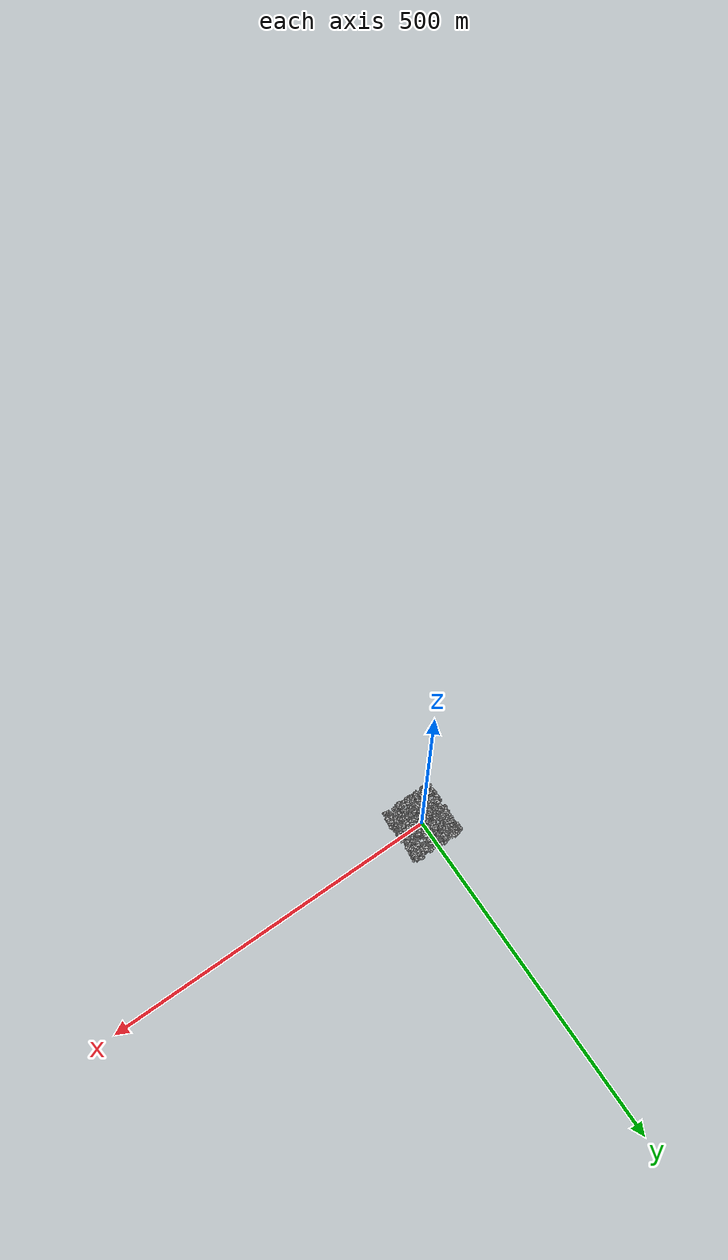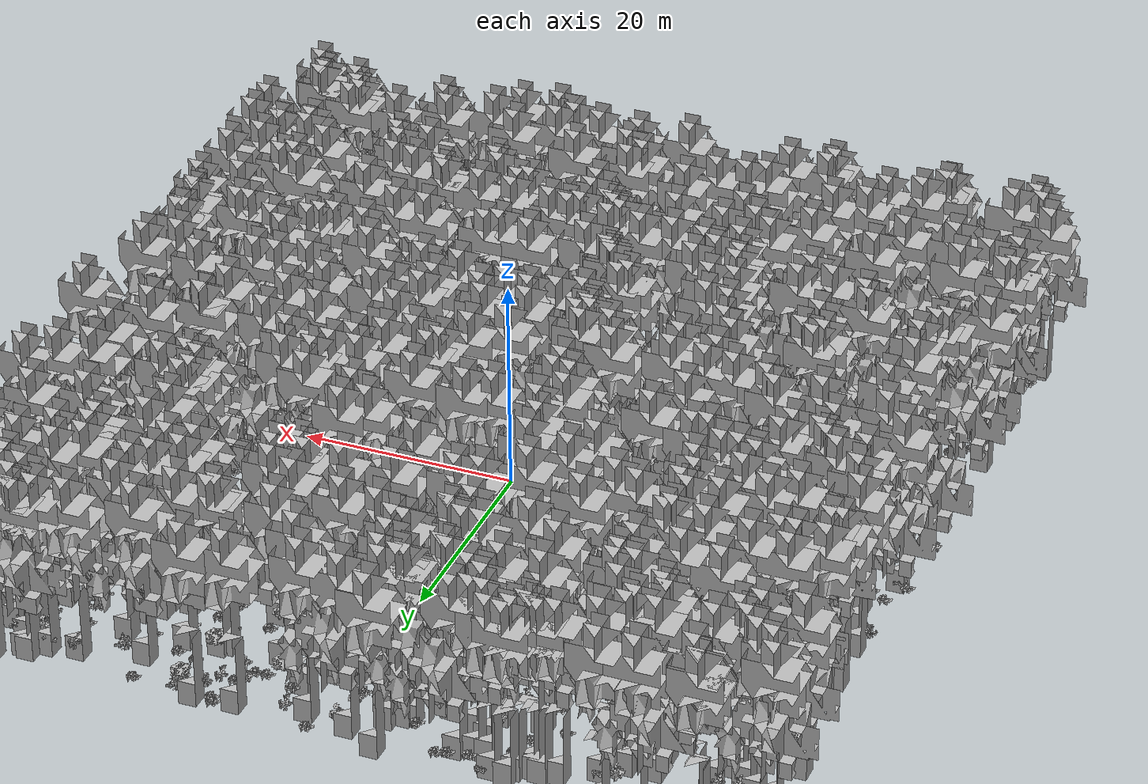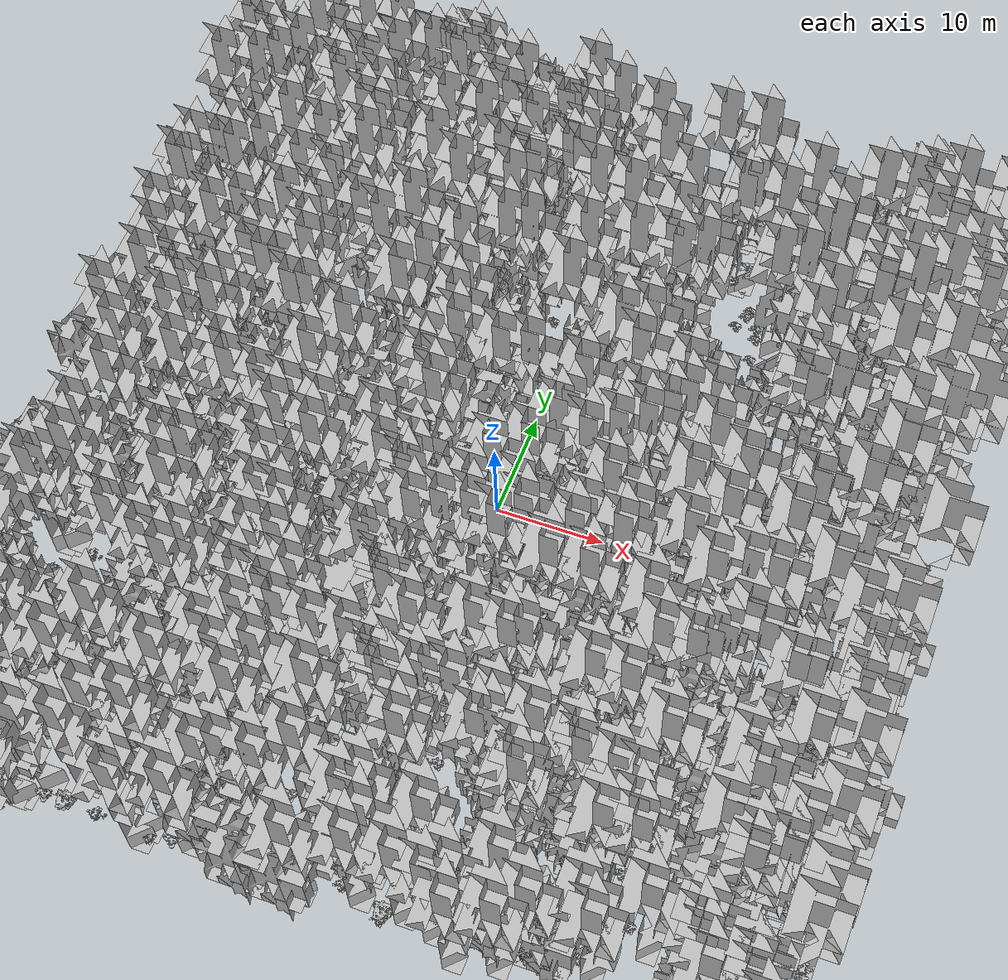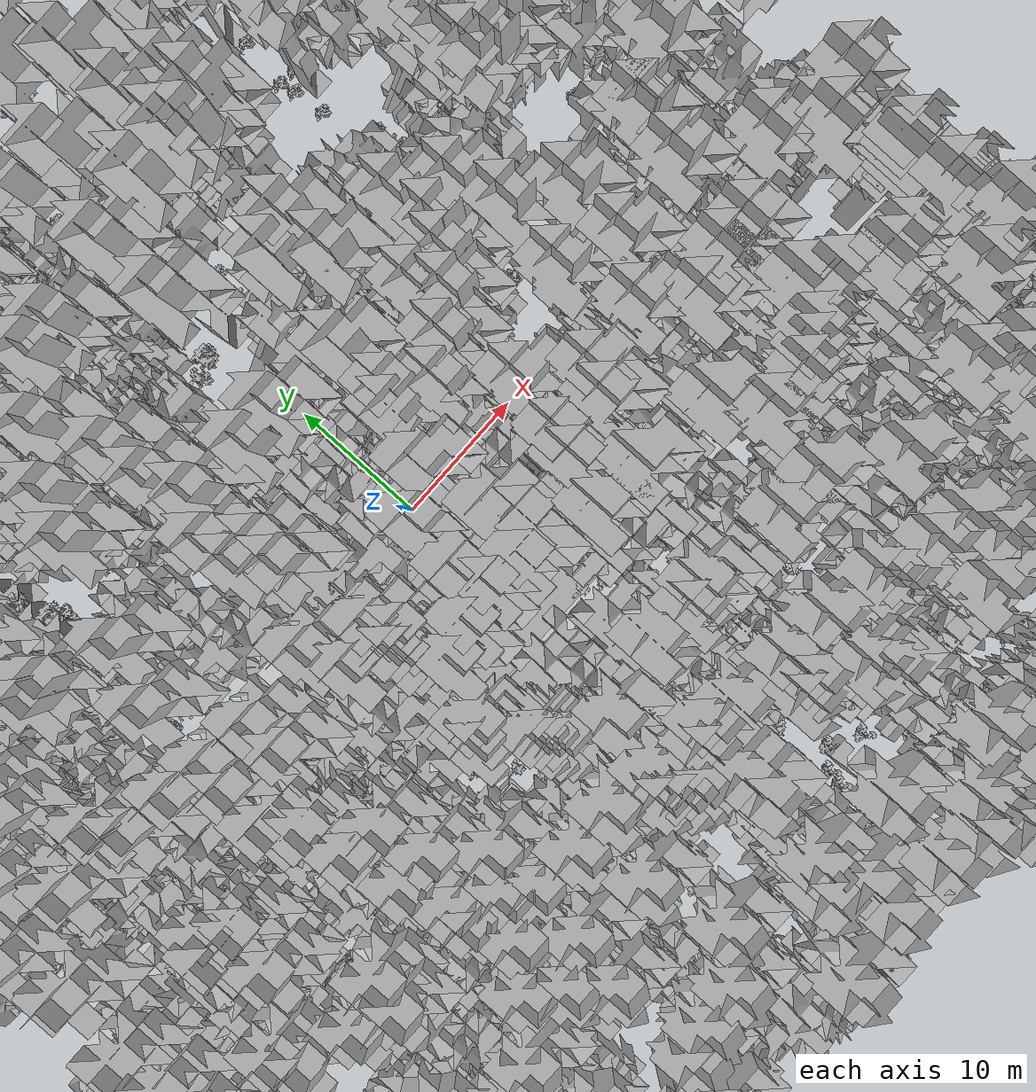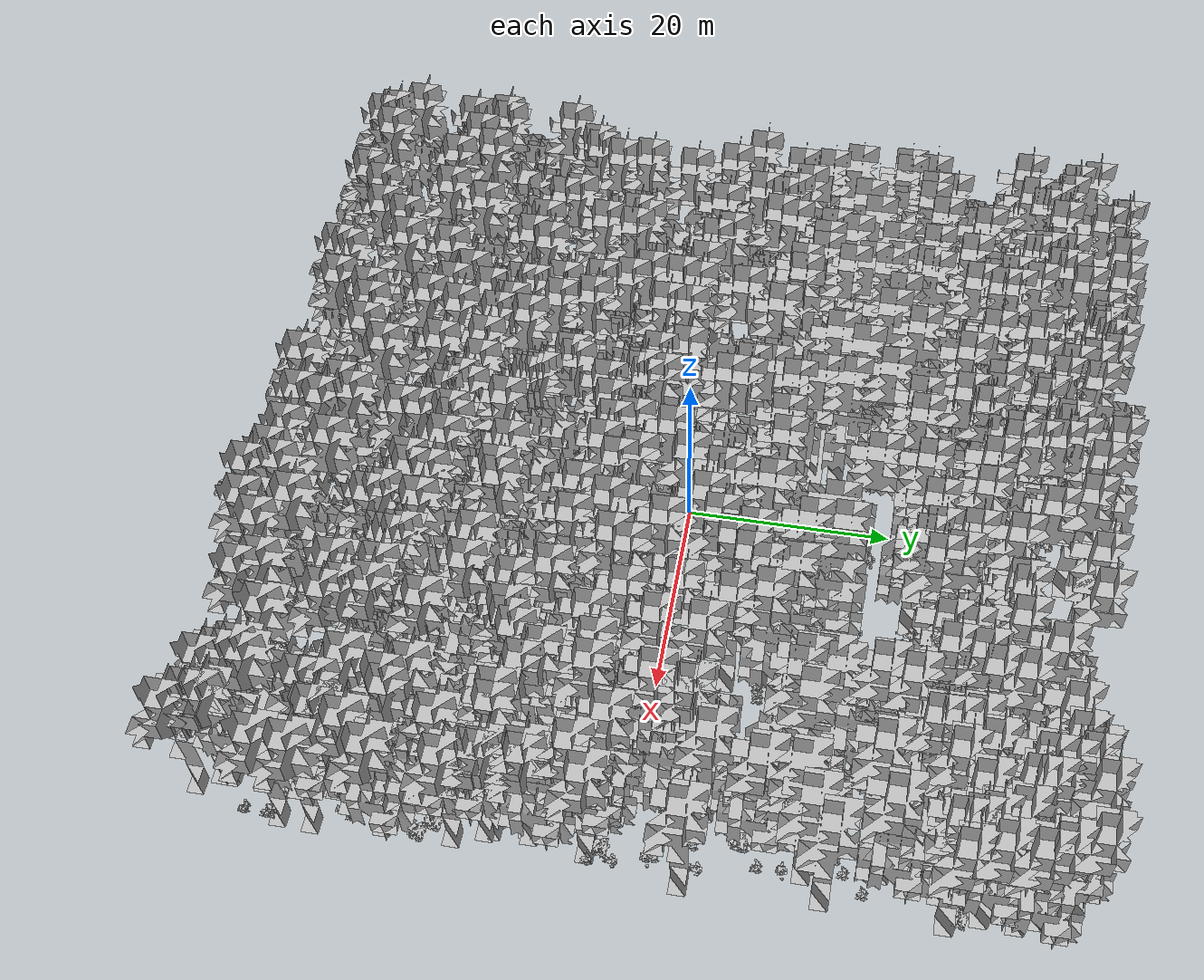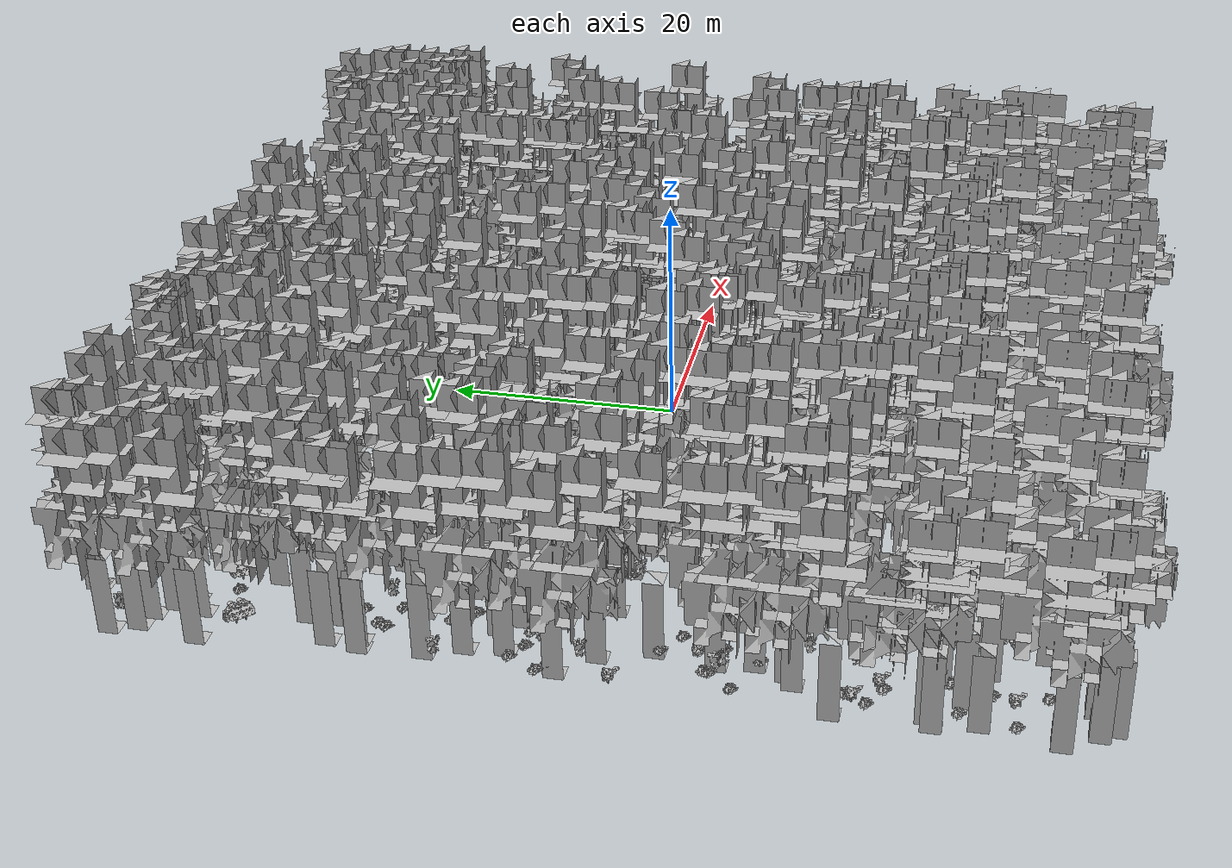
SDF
<sdf version="1.7">
    <world name="default">
        <plugin name="mrs_gazebo_static_transform_republisher_plugin" filename="libMrsGazeboCommonResources_StaticTransformRepublisher.so"/>
        <spherical_coordinates>
            <surface_model>EARTH_WGS84</surface_model>
            <latitude_deg>47.3977</latitude_deg>
            <longitude_deg>8.54559</longitude_deg>
            <elevation>0</elevation>
            <heading_deg>0</heading_deg>
        </spherical_coordinates>
        <physics name="default_physics" default="0" type="ode">
            <ode>
                <solver>
                    <type>quick</type>
                    <iters>10</iters>
                    <sor>1.3</sor>
                    <use_dynamic_moi_rescaling>0</use_dynamic_moi_rescaling>
                </solver>
                <constraints>
                    <cfm>0</cfm>
                    <erp>0.2</erp>
                    <contact_max_correcting_vel>1000</contact_max_correcting_vel>
                    <contact_surface_layer>0.001</contact_surface_layer>
                </constraints>
            </ode>
            <max_step_size>0.004</max_step_size>
            <real_time_factor>1</real_time_factor>
            <real_time_update_rate>250</real_time_update_rate>
        </physics>
        <scene>
            <shadows>0</shadows>
            <ambient>0.4 0.4 0.4 1</ambient>
            <background>0.7 0.7 0.7 1</background>
        </scene>
        <light name="sun" type="directional">
            <pose>0 0 1000 0.4 0.2 0</pose>
            <diffuse>1 1 1 1</diffuse>
            <specular>0.6 0.6 0.6 1</specular>
            <direction>0.1 0.1 -0.9</direction>
            <attenuation>
                <range>20</range>
                <constant>0.5</constant>
                <linear>0.01</linear>
                <quadratic>0.001</quadratic>
            </attenuation>
            <cast_shadows>1</cast_shadows>
            <spot>
                <inner_angle>0</inner_angle>
                <outer_angle>0</outer_angle>
                <falloff>0</falloff>
            </spot>
        </light>
        <model name="ground_plane">
            <static>1</static>
            <link name="link">
                <collision name="collision">
                    <pose>-50 0 0 0 -0 0</pose>
                    <geometry>
                        <plane>
                            <normal>0 0 1</normal>
                            <size>80 80</size>
                        </plane>
                    </geometry>
                    <surface>
                        <contact>
                            <ode>
                                <min_depth>0.01</min_depth>
                                <max_vel>0</max_vel>
                            </ode>
                        </contact>
                        <friction>
                            <ode/>
                            <torsional>
                                <ode/>
                            </torsional>
                        </friction>
                        <bounce/>
                    </surface>
                    <max_contacts>10</max_contacts>
                </collision>
                <visual name="grass">
                    <pose>0 0 0 0 -0 0</pose>
                    <cast_shadows>0</cast_shadows>
                    <geometry>
                        <mesh>
                            <scale>0.46714285714285714 0.46714285714285714 0.1</scale>
                            <uri>file://grass_plane/meshes/grass_plane.dae</uri>
                        </mesh>
                    </geometry>
                </visual>
                <self_collide>0</self_collide>
                <enable_wind>0</enable_wind>
                <kinematic>0</kinematic>
            </link>
        </model>
        <model name="the_void">
            <static>1</static>
            <link name="link">
                <pose>0 0 0.1 0 -0 0</pose>
                <visual name="the_void">
                    <pose>0 0 2 0 -0 0</pose>
                    <geometry>
                        <sphere>
                            <radius>0.25</radius>
                        </sphere>
                    </geometry>
                    <material>
                        <script>
                            <uri>file://media/materials/scripts/Gazebo.material</uri>
                            <name>Gazebo/Black</name>
                        </script>
                    </material>
                </visual>
                <self_collide>0</self_collide>
                <enable_wind>0</enable_wind>
                <kinematic>0</kinematic>
            </link>
            <pose>-1000 -1000 0 0 -0 0</pose>
        </model>
        <gui fullscreen="0">
            <camera name="camera">
                <pose>35.1577 98.6044 40.0204 0 0.407996 -1.99761</pose>
                <view_controller>orbit</view_controller>
                <projection_type>perspective</projection_type>
            </camera>
        </gui>
        <plugin name="mrs_gazebo_rviz_cam_synchronizer" filename="libMrsGazeboCommonResources_RvizCameraSynchronizer.so">
            <target_frame_id>gazebo_user_camera</target_frame_id>
            <world_origin_frame_id>uav1/gps_origin</world_origin_frame_id>
            <frame_to_follow>uav1</frame_to_follow>
        </plugin>
        <gravity>0 0 -9.8066</gravity>
        <magnetic_field>6e-06 2.3e-05 -4.2e-05</magnetic_field>
        <atmosphere type="adiabatic"/>
        <wind/>
        <model name="Tree 0">
            <static>1</static>
            <pose>-24.326980303188797 -12.943668064030554 0 1.57079 -0 0</pose>
            <link name="link">
                <pose>0 0 0 0 -0 0</pose>
                <collision name="collision">
                    <geometry>
                        <mesh>
                            <scale>3.5 5 3.5</scale>
                            <uri>model://tree_9/meshes/tree_9.obj</uri>
                        </mesh>
                    </geometry>
                    <max_contacts>10</max_contacts>
                    <surface>
                        <contact>
                            <ode/>
                        </contact>
                        <bounce/>
                        <friction>
                            <torsional>
                                <ode/>
                            </torsional>
                            <ode/>
                        </friction>
                    </surface>
                </collision>
                <visual name="visual">
                    <geometry>
                        <mesh>
                            <scale>3.5 5 3.5</scale>
                            <uri>model://tree_9/meshes/tree_9.obj</uri>
                        </mesh>
                    </geometry>
                </visual>
                <self_collide>0</self_collide>
                <enable_wind>0</enable_wind>
                <kinematic>0</kinematic>
            </link>
        </model>
        <model name="Tree 1">
            <static>1</static>
            <pose>-14.268420945148922 -5.010399066711486 0 1.57079 -0 0</pose>
            <link name="link">
                <pose>0 0 0 0 -0 0</pose>
                <collision name="collision">
                    <geometry>
                        <mesh>
                            <scale>3.5 5 3.5</scale>
                            <uri>model://tree_9/meshes/tree_9.obj</uri>
                        </mesh>
                    </geometry>
                    <max_contacts>10</max_contacts>
                    <surface>
                        <contact>
                            <ode/>
                        </contact>
                        <bounce/>
                        <friction>
                            <torsional>
                                <ode/>
                            </torsional>
                            <ode/>
                        </friction>
                    </surface>
                </collision>
                <visual name="visual">
                    <geometry>
                        <mesh>
                            <scale>3.5 5 3.5</scale>
                            <uri>model://tree_9/meshes/tree_9.obj</uri>
                        </mesh>
                    </geometry>
                </visual>
                <self_collide>0</self_collide>
                <enable_wind>0</enable_wind>
                <kinematic>0</kinematic>
            </link>
        </model>
        <model name="Tree 2">
            <static>1</static>
            <pose>-38.30100927178718 -0.0434767820588533 0 1.57079 -0 0</pose>
            <link name="link">
                <pose>0 0 0 0 -0 0</pose>
                <collision name="collision">
                    <geometry>
                        <mesh>
                            <scale>3.5 5 3.5</scale>
                            <uri>model://tree_2/meshes/tree_2.obj</uri>
                        </mesh>
                    </geometry>
                    <max_contacts>10</max_contacts>
                    <surface>
                        <contact>
                            <ode/>
                        </contact>
                        <bounce/>
                        <friction>
                            <torsional>
                                <ode/>
                            </torsional>
                            <ode/>
                        </friction>
                    </surface>
                </collision>
                <visual name="visual">
                    <geometry>
                        <mesh>
                            <scale>3.5 5 3.5</scale>
                            <uri>model://tree_2/meshes/tree_2.obj</uri>
                        </mesh>
                    </geometry>
                </visual>
                <self_collide>0</self_collide>
                <enable_wind>0</enable_wind>
                <kinematic>0</kinematic>
            </link>
        </model>
        <model name="Tree 3">
            <static>1</static>
            <pose>-15.185637563876192 -9.049775119217855 0 1.57079 -0 0</pose>
            <link name="link">
                <pose>0 0 0 0 -0 0</pose>
                <collision name="collision">
                    <geometry>
                        <mesh>
                            <scale>3.5 5 3.5</scale>
                            <uri>model://tree_2/meshes/tree_2.obj</uri>
                        </mesh>
                    </geometry>
                    <max_contacts>10</max_contacts>
                    <surface>
                        <contact>
                            <ode/>
                        </contact>
                        <bounce/>
                        <friction>
                            <torsional>
                                <ode/>
                            </torsional>
                            <ode/>
                        </friction>
                    </surface>
                </collision>
                <visual name="visual">
                    <geometry>
                        <mesh>
                            <scale>3.5 5 3.5</scale>
                            <uri>model://tree_2/meshes/tree_2.obj</uri>
                        </mesh>
                    </geometry>
                </visual>
                <self_collide>0</self_collide>
                <enable_wind>0</enable_wind>
                <kinematic>0</kinematic>
            </link>
        </model>
        <model name="Tree 4">
            <static>1</static>
            <pose>-12.686489410339071 35.04230845025239 0 1.57079 -0 0</pose>
            <link name="link">
                <pose>0 0 0 0 -0 0</pose>
                <collision name="collision">
                    <geometry>
                        <mesh>
                            <scale>3.5 5 3.5</scale>
                            <uri>model://tree_9/meshes/tree_9.obj</uri>
                        </mesh>
                    </geometry>
                    <max_contacts>10</max_contacts>
                    <surface>
                        <contact>
                            <ode/>
                        </contact>
                        <bounce/>
                        <friction>
                            <torsional>
                                <ode/>
                            </torsional>
                            <ode/>
                        </friction>
                    </surface>
                </collision>
                <visual name="visual">
                    <geometry>
                        <mesh>
                            <scale>3.5 5 3.5</scale>
                            <uri>model://tree_9/meshes/tree_9.obj</uri>
                        </mesh>
                    </geometry>
                </visual>
                <self_collide>0</self_collide>
                <enable_wind>0</enable_wind>
                <kinematic>0</kinematic>
            </link>
        </model>
        <model name="Tree 5">
            <static>1</static>
            <pose>-1.8581953231498218 -20.53048625589616 0 1.57079 -0 0</pose>
            <link name="link">
                <pose>0 0 0 0 -0 0</pose>
                <collision name="collision">
                    <geometry>
                        <mesh>
                            <scale>3.5 5 3.5</scale>
                            <uri>model://tree_2/meshes/tree_2.obj</uri>
                        </mesh>
                    </geometry>
                    <max_contacts>10</max_contacts>
                    <surface>
                        <contact>
                            <ode/>
                        </contact>
                        <bounce/>
                        <friction>
                            <torsional>
                                <ode/>
                            </torsional>
                            <ode/>
                        </friction>
                    </surface>
                </collision>
                <visual name="visual">
                    <geometry>
                        <mesh>
                            <scale>3.5 5 3.5</scale>
                            <uri>model://tree_2/meshes/tree_2.obj</uri>
                        </mesh>
                    </geometry>
                </visual>
                <self_collide>0</self_collide>
                <enable_wind>0</enable_wind>
                <kinematic>0</kinematic>
            </link>
        </model>
        <model name="Tree 6">
            <static>1</static>
            <pose>-10.306124599277059 -7.160687915453316 0 1.57079 -0 0</pose>
            <link name="link">
                <pose>0 0 0 0 -0 0</pose>
                <collision name="collision">
                    <geometry>
                        <mesh>
                            <scale>3.5 5 3.5</scale>
                            <uri>model://tree_2/meshes/tree_2.obj</uri>
                        </mesh>
                    </geometry>
                    <max_contacts>10</max_contacts>
                    <surface>
                        <contact>
                            <ode/>
                        </contact>
                        <bounce/>
                        <friction>
                            <torsional>
                                <ode/>
                            </torsional>
                            <ode/>
                        </friction>
                    </surface>
                </collision>
                <visual name="visual">
                    <geometry>
                        <mesh>
                            <scale>3.5 5 3.5</scale>
                            <uri>model://tree_2/meshes/tree_2.obj</uri>
                        </mesh>
                    </geometry>
                </visual>
                <self_collide>0</self_collide>
                <enable_wind>0</enable_wind>
                <kinematic>0</kinematic>
            </link>
        </model>
        <model name="Tree 7">
            <static>1</static>
            <pose>-35.136264443272616 5.9302808848362645 0 1.57079 -0 0</pose>
            <link name="link">
                <pose>0 0 0 0 -0 0</pose>
                <collision name="collision">
                    <geometry>
                        <mesh>
                            <scale>3.5 5 3.5</scale>
                            <uri>model://tree_9/meshes/tree_9.obj</uri>
                        </mesh>
                    </geometry>
                    <max_contacts>10</max_contacts>
                    <surface>
                        <contact>
                            <ode/>
                        </contact>
                        <bounce/>
                        <friction>
                            <torsional>
                                <ode/>
                            </torsional>
                            <ode/>
                        </friction>
                    </surface>
                </collision>
                <visual name="visual">
                    <geometry>
                        <mesh>
                            <scale>3.5 5 3.5</scale>
                            <uri>model://tree_9/meshes/tree_9.obj</uri>
                        </mesh>
                    </geometry>
                </visual>
                <self_collide>0</self_collide>
                <enable_wind>0</enable_wind>
                <kinematic>0</kinematic>
            </link>
        </model>
        <model name="Tree 8">
            <static>1</static>
            <pose>-14.362451058432324 25.868436566336598 0 1.57079 -0 0</pose>
            <link name="link">
                <pose>0 0 0 0 -0 0</pose>
                <collision name="collision">
                    <geometry>
                        <mesh>
                            <scale>3.5 5 3.5</scale>
                            <uri>model://tree_2/meshes/tree_2.obj</uri>
                        </mesh>
                    </geometry>
                    <max_contacts>10</max_contacts>
                    <surface>
                        <contact>
                            <ode/>
                        </contact>
                        <bounce/>
                        <friction>
                            <torsional>
                                <ode/>
                            </torsional>
                            <ode/>
                        </friction>
                    </surface>
                </collision>
                <visual name="visual">
                    <geometry>
                        <mesh>
                            <scale>3.5 5 3.5</scale>
                            <uri>model://tree_2/meshes/tree_2.obj</uri>
                        </mesh>
                    </geometry>
                </visual>
                <self_collide>0</self_collide>
                <enable_wind>0</enable_wind>
                <kinematic>0</kinematic>
            </link>
        </model>
        <model name="Tree 9">
            <static>1</static>
            <pose>12.309583372342772 -12.2217204270489 0 1.57079 -0 0</pose>
            <link name="link">
                <pose>0 0 0 0 -0 0</pose>
                <collision name="collision">
                    <geometry>
                        <mesh>
                            <scale>3.5 5 3.5</scale>
                            <uri>model://tree_2/meshes/tree_2.obj</uri>
                        </mesh>
                    </geometry>
                    <max_contacts>10</max_contacts>
                    <surface>
                        <contact>
                            <ode/>
                        </contact>
                        <bounce/>
                        <friction>
                            <torsional>
                                <ode/>
                            </torsional>
                            <ode/>
                        </friction>
                    </surface>
                </collision>
                <visual name="visual">
                    <geometry>
                        <mesh>
                            <scale>3.5 5 3.5</scale>
                            <uri>model://tree_2/meshes/tree_2.obj</uri>
                        </mesh>
                    </geometry>
                </visual>
                <self_collide>0</self_collide>
                <enable_wind>0</enable_wind>
                <kinematic>0</kinematic>
            </link>
        </model>
        <model name="Tree 10">
            <static>1</static>
            <pose>16.092716504661794 -27.637687784104124 0 1.57079 -0 0</pose>
            <link name="link">
                <pose>0 0 0 0 -0 0</pose>
                <collision name="collision">
                    <geometry>
                        <mesh>
                            <scale>3.5 5 3.5</scale>
                            <uri>model://tree_2/meshes/tree_2.obj</uri>
                        </mesh>
                    </geometry>
                    <max_contacts>10</max_contacts>
                    <surface>
                        <contact>
                            <ode/>
                        </contact>
                        <bounce/>
                        <friction>
                            <torsional>
                                <ode/>
                            </torsional>
                            <ode/>
                        </friction>
                    </surface>
                </collision>
                <visual name="visual">
                    <geometry>
                        <mesh>
                            <scale>3.5 5 3.5</scale>
                            <uri>model://tree_2/meshes/tree_2.obj</uri>
                        </mesh>
                    </geometry>
                </visual>
                <self_collide>0</self_collide>
                <enable_wind>0</enable_wind>
                <kinematic>0</kinematic>
            </link>
        </model>
        <model name="Tree 11">
            <static>1</static>
            <pose>-9.012206593976291 -2.0977632748779484 0 1.57079 -0 0</pose>
            <link name="link">
                <pose>0 0 0 0 -0 0</pose>
                <collision name="collision">
                    <geometry>
                        <mesh>
                            <scale>3.5 5 3.5</scale>
                            <uri>model://tree_9/meshes/tree_9.obj</uri>
                        </mesh>
                    </geometry>
                    <max_contacts>10</max_contacts>
                    <surface>
                        <contact>
                            <ode/>
                        </contact>
                        <bounce/>
                        <friction>
                            <torsional>
                                <ode/>
                            </torsional>
                            <ode/>
                        </friction>
                    </surface>
                </collision>
                <visual name="visual">
                    <geometry>
                        <mesh>
                            <scale>3.5 5 3.5</scale>
                            <uri>model://tree_9/meshes/tree_9.obj</uri>
                        </mesh>
                    </geometry>
                </visual>
                <self_collide>0</self_collide>
                <enable_wind>0</enable_wind>
                <kinematic>0</kinematic>
            </link>
        </model>
        <model name="Tree 12">
            <static>1</static>
            <pose>-12.201571156416641 30.999647327010763 0 1.57079 -0 0</pose>
            <link name="link">
                <pose>0 0 0 0 -0 0</pose>
                <collision name="collision">
                    <geometry>
                        <mesh>
                            <scale>3.5 5 3.5</scale>
                            <uri>model://tree_2/meshes/tree_2.obj</uri>
                        </mesh>
                    </geometry>
                    <max_contacts>10</max_contacts>
                    <surface>
                        <contact>
                            <ode/>
                        </contact>
                        <bounce/>
                        <friction>
                            <torsional>
                                <ode/>
                            </torsional>
                            <ode/>
                        </friction>
                    </surface>
                </collision>
                <visual name="visual">
                    <geometry>
                        <mesh>
                            <scale>3.5 5 3.5</scale>
                            <uri>model://tree_2/meshes/tree_2.obj</uri>
                        </mesh>
                    </geometry>
                </visual>
                <self_collide>0</self_collide>
                <enable_wind>0</enable_wind>
                <kinematic>0</kinematic>
            </link>
        </model>
        <model name="Tree 13">
            <static>1</static>
            <pose>-22.846539033407645 28.64149036128063 0 1.57079 -0 0</pose>
            <link name="link">
                <pose>0 0 0 0 -0 0</pose>
                <collision name="collision">
                    <geometry>
                        <mesh>
                            <scale>3.5 5 3.5</scale>
                            <uri>model://tree_2/meshes/tree_2.obj</uri>
                        </mesh>
                    </geometry>
                    <max_contacts>10</max_contacts>
                    <surface>
                        <contact>
                            <ode/>
                        </contact>
                        <bounce/>
                        <friction>
                            <torsional>
                                <ode/>
                            </torsional>
                            <ode/>
                        </friction>
                    </surface>
                </collision>
                <visual name="visual">
                    <geometry>
                        <mesh>
                            <scale>3.5 5 3.5</scale>
                            <uri>model://tree_2/meshes/tree_2.obj</uri>
                        </mesh>
                    </geometry>
                </visual>
                <self_collide>0</self_collide>
                <enable_wind>0</enable_wind>
                <kinematic>0</kinematic>
            </link>
        </model>
        <model name="Tree 14">
            <static>1</static>
            <pose>20.565288307963478 24.076155257833577 0 1.57079 -0 0</pose>
            <link name="link">
                <pose>0 0 0 0 -0 0</pose>
                <collision name="collision">
                    <geometry>
                        <mesh>
                            <scale>3.5 5 3.5</scale>
                            <uri>model://tree_2/meshes/tree_2.obj</uri>
                        </mesh>
                    </geometry>
                    <max_contacts>10</max_contacts>
                    <surface>
                        <contact>
                            <ode/>
                        </contact>
                        <bounce/>
                        <friction>
                            <torsional>
                                <ode/>
                            </torsional>
                            <ode/>
                        </friction>
                    </surface>
                </collision>
                <visual name="visual">
                    <geometry>
                        <mesh>
                            <scale>3.5 5 3.5</scale>
                            <uri>model://tree_2/meshes/tree_2.obj</uri>
                        </mesh>
                    </geometry>
                </visual>
                <self_collide>0</self_collide>
                <enable_wind>0</enable_wind>
                <kinematic>0</kinematic>
            </link>
        </model>
        <model name="Tree 15">
            <static>1</static>
            <pose>-29.18727145450593 37.06030403301507 0 1.57079 -0 0</pose>
            <link name="link">
                <pose>0 0 0 0 -0 0</pose>
                <collision name="collision">
                    <geometry>
                        <mesh>
                            <scale>3.5 5 3.5</scale>
                            <uri>model://tree_2/meshes/tree_2.obj</uri>
                        </mesh>
                    </geometry>
                    <max_contacts>10</max_contacts>
                    <surface>
                        <contact>
                            <ode/>
                        </contact>
                        <bounce/>
                        <friction>
                            <torsional>
                                <ode/>
                            </torsional>
                            <ode/>
                        </friction>
                    </surface>
                </collision>
                <visual name="visual">
                    <geometry>
                        <mesh>
                            <scale>3.5 5 3.5</scale>
                            <uri>model://tree_2/meshes/tree_2.obj</uri>
                        </mesh>
                    </geometry>
                </visual>
                <self_collide>0</self_collide>
                <enable_wind>0</enable_wind>
                <kinematic>0</kinematic>
            </link>
        </model>
        <model name="Tree 16">
            <static>1</static>
            <pose>16.97326211965948 -37.28798315173271 0 1.57079 -0 0</pose>
            <link name="link">
                <pose>0 0 0 0 -0 0</pose>
                <collision name="collision">
                    <geometry>
                        <mesh>
                            <scale>3.5 5 3.5</scale>
                            <uri>model://tree_9/meshes/tree_9.obj</uri>
                        </mesh>
                    </geometry>
                    <max_contacts>10</max_contacts>
                    <surface>
                        <contact>
                            <ode/>
                        </contact>
                        <bounce/>
                        <friction>
                            <torsional>
                                <ode/>
                            </torsional>
                            <ode/>
                        </friction>
                    </surface>
                </collision>
                <visual name="visual">
                    <geometry>
                        <mesh>
                            <scale>3.5 5 3.5</scale>
                            <uri>model://tree_9/meshes/tree_9.obj</uri>
                        </mesh>
                    </geometry>
                </visual>
                <self_collide>0</self_collide>
                <enable_wind>0</enable_wind>
                <kinematic>0</kinematic>
            </link>
        </model>
        <model name="Tree 17">
            <static>1</static>
            <pose>18.053022976018823 6.4510136019922655 0 1.57079 -0 0</pose>
            <link name="link">
                <pose>0 0 0 0 -0 0</pose>
                <collision name="collision">
                    <geometry>
                        <mesh>
                            <scale>3.5 5 3.5</scale>
                            <uri>model://tree_9/meshes/tree_9.obj</uri>
                        </mesh>
                    </geometry>
                    <max_contacts>10</max_contacts>
                    <surface>
                        <contact>
                            <ode/>
                        </contact>
                        <bounce/>
                        <friction>
                            <torsional>
                                <ode/>
                            </torsional>
                            <ode/>
                        </friction>
                    </surface>
                </collision>
                <visual name="visual">
                    <geometry>
                        <mesh>
                            <scale>3.5 5 3.5</scale>
                            <uri>model://tree_9/meshes/tree_9.obj</uri>
                        </mesh>
                    </geometry>
                </visual>
                <self_collide>0</self_collide>
                <enable_wind>0</enable_wind>
                <kinematic>0</kinematic>
            </link>
        </model>
        <model name="Tree 18">
            <static>1</static>
            <pose>30.648808258607744 -36.069620693517344 0 1.57079 -0 0</pose>
            <link name="link">
                <pose>0 0 0 0 -0 0</pose>
                <collision name="collision">
                    <geometry>
                        <mesh>
                            <scale>3.5 5 3.5</scale>
                            <uri>model://tree_9/meshes/tree_9.obj</uri>
                        </mesh>
                    </geometry>
                    <max_contacts>10</max_contacts>
                    <surface>
                        <contact>
                            <ode/>
                        </contact>
                        <bounce/>
                        <friction>
                            <torsional>
                                <ode/>
                            </torsional>
                            <ode/>
                        </friction>
                    </surface>
                </collision>
                <visual name="visual">
                    <geometry>
                        <mesh>
                            <scale>3.5 5 3.5</scale>
                            <uri>model://tree_9/meshes/tree_9.obj</uri>
                        </mesh>
                    </geometry>
                </visual>
                <self_collide>0</self_collide>
                <enable_wind>0</enable_wind>
                <kinematic>0</kinematic>
            </link>
        </model>
        <model name="Tree 19">
            <static>1</static>
            <pose>-24.291597076596993 39.67959928283102 0 1.57079 -0 0</pose>
            <link name="link">
                <pose>0 0 0 0 -0 0</pose>
                <collision name="collision">
                    <geometry>
                        <mesh>
                            <scale>3.5 5 3.5</scale>
                            <uri>model://tree_9/meshes/tree_9.obj</uri>
                        </mesh>
                    </geometry>
                    <max_contacts>10</max_contacts>
                    <surface>
                        <contact>
                            <ode/>
                        </contact>
                        <bounce/>
                        <friction>
                            <torsional>
                                <ode/>
                            </torsional>
                            <ode/>
                        </friction>
                    </surface>
                </collision>
                <visual name="visual">
                    <geometry>
                        <mesh>
                            <scale>3.5 5 3.5</scale>
                            <uri>model://tree_9/meshes/tree_9.obj</uri>
                        </mesh>
                    </geometry>
                </visual>
                <self_collide>0</self_collide>
                <enable_wind>0</enable_wind>
                <kinematic>0</kinematic>
            </link>
        </model>
        <model name="Tree 20">
            <static>1</static>
            <pose>-24.754400181798694 -0.011830775836756402 0 1.57079 -0 0</pose>
            <link name="link">
                <pose>0 0 0 0 -0 0</pose>
                <collision name="collision">
                    <geometry>
                        <mesh>
                            <scale>3.5 5 3.5</scale>
                            <uri>model://tree_9/meshes/tree_9.obj</uri>
                        </mesh>
                    </geometry>
                    <max_contacts>10</max_contacts>
                    <surface>
                        <contact>
                            <ode/>
                        </contact>
                        <bounce/>
                        <friction>
                            <torsional>
                                <ode/>
                            </torsional>
                            <ode/>
                        </friction>
                    </surface>
                </collision>
                <visual name="visual">
                    <geometry>
                        <mesh>
                            <scale>3.5 5 3.5</scale>
                            <uri>model://tree_9/meshes/tree_9.obj</uri>
                        </mesh>
                    </geometry>
                </visual>
                <self_collide>0</self_collide>
                <enable_wind>0</enable_wind>
                <kinematic>0</kinematic>
            </link>
        </model>
        <model name="Tree 21">
            <static>1</static>
            <pose>-5.556242086556814 -5.873186874767839 0 1.57079 -0 0</pose>
            <link name="link">
                <pose>0 0 0 0 -0 0</pose>
                <collision name="collision">
                    <geometry>
                        <mesh>
                            <scale>3.5 5 3.5</scale>
                            <uri>model://tree_9/meshes/tree_9.obj</uri>
                        </mesh>
                    </geometry>
                    <max_contacts>10</max_contacts>
                    <surface>
                        <contact>
                            <ode/>
                        </contact>
                        <bounce/>
                        <friction>
                            <torsional>
                                <ode/>
                            </torsional>
                            <ode/>
                        </friction>
                    </surface>
                </collision>
                <visual name="visual">
                    <geometry>
                        <mesh>
                            <scale>3.5 5 3.5</scale>
                            <uri>model://tree_9/meshes/tree_9.obj</uri>
                        </mesh>
                    </geometry>
                </visual>
                <self_collide>0</self_collide>
                <enable_wind>0</enable_wind>
                <kinematic>0</kinematic>
            </link>
        </model>
        <model name="Tree 22">
            <static>1</static>
            <pose>-17.42180768954763 37.32817529884164 0 1.57079 -0 0</pose>
            <link name="link">
                <pose>0 0 0 0 -0 0</pose>
                <collision name="collision">
                    <geometry>
                        <mesh>
                            <scale>3.5 5 3.5</scale>
                            <uri>model://tree_9/meshes/tree_9.obj</uri>
                        </mesh>
                    </geometry>
                    <max_contacts>10</max_contacts>
                    <surface>
                        <contact>
                            <ode/>
                        </contact>
                        <bounce/>
                        <friction>
                            <torsional>
                                <ode/>
                            </torsional>
                            <ode/>
                        </friction>
                    </surface>
                </collision>
                <visual name="visual">
                    <geometry>
                        <mesh>
                            <scale>3.5 5 3.5</scale>
                            <uri>model://tree_9/meshes/tree_9.obj</uri>
                        </mesh>
                    </geometry>
                </visual>
                <self_collide>0</self_collide>
                <enable_wind>0</enable_wind>
                <kinematic>0</kinematic>
            </link>
        </model>
        <model name="Tree 23">
            <static>1</static>
            <pose>-14.48661858609816 -19.63642505668779 0 1.57079 -0 0</pose>
            <link name="link">
                <pose>0 0 0 0 -0 0</pose>
                <collision name="collision">
                    <geometry>
                        <mesh>
                            <scale>3.5 5 3.5</scale>
                            <uri>model://tree_9/meshes/tree_9.obj</uri>
                        </mesh>
                    </geometry>
                    <max_contacts>10</max_contacts>
                    <surface>
                        <contact>
                            <ode/>
                        </contact>
                        <bounce/>
                        <friction>
                            <torsional>
                                <ode/>
                            </torsional>
                            <ode/>
                        </friction>
                    </surface>
                </collision>
                <visual name="visual">
                    <geometry>
                        <mesh>
                            <scale>3.5 5 3.5</scale>
                            <uri>model://tree_9/meshes/tree_9.obj</uri>
                        </mesh>
                    </geometry>
                </visual>
                <self_collide>0</self_collide>
                <enable_wind>0</enable_wind>
                <kinematic>0</kinematic>
            </link>
        </model>
        <model name="Tree 24">
            <static>1</static>
            <pose>-26.485810664263035 12.45841072428221 0 1.57079 -0 0</pose>
            <link name="link">
                <pose>0 0 0 0 -0 0</pose>
                <collision name="collision">
                    <geometry>
                        <mesh>
                            <scale>3.5 5 3.5</scale>
                            <uri>model://tree_9/meshes/tree_9.obj</uri>
                        </mesh>
                    </geometry>
                    <max_contacts>10</max_contacts>
                    <surface>
                        <contact>
                            <ode/>
                        </contact>
                        <bounce/>
                        <friction>
                            <torsional>
                                <ode/>
                            </torsional>
                            <ode/>
                        </friction>
                    </surface>
                </collision>
                <visual name="visual">
                    <geometry>
                        <mesh>
                            <scale>3.5 5 3.5</scale>
                            <uri>model://tree_9/meshes/tree_9.obj</uri>
                        </mesh>
                    </geometry>
                </visual>
                <self_collide>0</self_collide>
                <enable_wind>0</enable_wind>
                <kinematic>0</kinematic>
            </link>
        </model>
        <model name="Tree 25">
            <static>1</static>
            <pose>35.75085206064344 -13.632023460624119 0 1.57079 -0 0</pose>
            <link name="link">
                <pose>0 0 0 0 -0 0</pose>
                <collision name="collision">
                    <geometry>
                        <mesh>
                            <scale>3.5 5 3.5</scale>
                            <uri>model://tree_2/meshes/tree_2.obj</uri>
                        </mesh>
                    </geometry>
                    <max_contacts>10</max_contacts>
                    <surface>
                        <contact>
                            <ode/>
                        </contact>
                        <bounce/>
                        <friction>
                            <torsional>
                                <ode/>
                            </torsional>
                            <ode/>
                        </friction>
                    </surface>
                </collision>
                <visual name="visual">
                    <geometry>
                        <mesh>
                            <scale>3.5 5 3.5</scale>
                            <uri>model://tree_2/meshes/tree_2.obj</uri>
                        </mesh>
                    </geometry>
                </visual>
                <self_collide>0</self_collide>
                <enable_wind>0</enable_wind>
                <kinematic>0</kinematic>
            </link>
        </model>
        <model name="Tree 26">
            <static>1</static>
            <pose>34.21662054495896 32.584082411392984 0 1.57079 -0 0</pose>
            <link name="link">
                <pose>0 0 0 0 -0 0</pose>
                <collision name="collision">
                    <geometry>
                        <mesh>
                            <scale>3.5 5 3.5</scale>
                            <uri>model://tree_9/meshes/tree_9.obj</uri>
                        </mesh>
                    </geometry>
                    <max_contacts>10</max_contacts>
                    <surface>
                        <contact>
                            <ode/>
                        </contact>
                        <bounce/>
                        <friction>
                            <torsional>
                                <ode/>
                            </torsional>
                            <ode/>
                        </friction>
                    </surface>
                </collision>
                <visual name="visual">
                    <geometry>
                        <mesh>
                            <scale>3.5 5 3.5</scale>
                            <uri>model://tree_9/meshes/tree_9.obj</uri>
                        </mesh>
                    </geometry>
                </visual>
                <self_collide>0</self_collide>
                <enable_wind>0</enable_wind>
                <kinematic>0</kinematic>
            </link>
        </model>
        <model name="Tree 27">
            <static>1</static>
            <pose>-22.259721382093822 12.602933076455649 0 1.57079 -0 0</pose>
            <link name="link">
                <pose>0 0 0 0 -0 0</pose>
                <collision name="collision">
                    <geometry>
                        <mesh>
                            <scale>3.5 5 3.5</scale>
                            <uri>model://tree_9/meshes/tree_9.obj</uri>
                        </mesh>
                    </geometry>
                    <max_contacts>10</max_contacts>
                    <surface>
                        <contact>
                            <ode/>
                        </contact>
                        <bounce/>
                        <friction>
                            <torsional>
                                <ode/>
                            </torsional>
                            <ode/>
                        </friction>
                    </surface>
                </collision>
                <visual name="visual">
                    <geometry>
                        <mesh>
                            <scale>3.5 5 3.5</scale>
                            <uri>model://tree_9/meshes/tree_9.obj</uri>
                        </mesh>
                    </geometry>
                </visual>
                <self_collide>0</self_collide>
                <enable_wind>0</enable_wind>
                <kinematic>0</kinematic>
            </link>
        </model>
        <model name="Tree 28">
            <static>1</static>
            <pose>-4.4084460784714565 21.315842113175883 0 1.57079 -0 0</pose>
            <link name="link">
                <pose>0 0 0 0 -0 0</pose>
                <collision name="collision">
                    <geometry>
                        <mesh>
                            <scale>3.5 5 3.5</scale>
                            <uri>model://tree_9/meshes/tree_9.obj</uri>
                        </mesh>
                    </geometry>
                    <max_contacts>10</max_contacts>
                    <surface>
                        <contact>
                            <ode/>
                        </contact>
                        <bounce/>
                        <friction>
                            <torsional>
                                <ode/>
                            </torsional>
                            <ode/>
                        </friction>
                    </surface>
                </collision>
                <visual name="visual">
                    <geometry>
                        <mesh>
                            <scale>3.5 5 3.5</scale>
                            <uri>model://tree_9/meshes/tree_9.obj</uri>
                        </mesh>
                    </geometry>
                </visual>
                <self_collide>0</self_collide>
                <enable_wind>0</enable_wind>
                <kinematic>0</kinematic>
            </link>
        </model>
        <model name="Tree 29">
            <static>1</static>
            <pose>36.84406272811566 23.460842420579823 0 1.57079 -0 0</pose>
            <link name="link">
                <pose>0 0 0 0 -0 0</pose>
                <collision name="collision">
                    <geometry>
                        <mesh>
                            <scale>3.5 5 3.5</scale>
                            <uri>model://tree_2/meshes/tree_2.obj</uri>
                        </mesh>
                    </geometry>
                    <max_contacts>10</max_contacts>
                    <surface>
                        <contact>
                            <ode/>
                        </contact>
                        <bounce/>
                        <friction>
                            <torsional>
                                <ode/>
                            </torsional>
                            <ode/>
                        </friction>
                    </surface>
                </collision>
                <visual name="visual">
                    <geometry>
                        <mesh>
                            <scale>3.5 5 3.5</scale>
                            <uri>model://tree_2/meshes/tree_2.obj</uri>
                        </mesh>
                    </geometry>
                </visual>
                <self_collide>0</self_collide>
                <enable_wind>0</enable_wind>
                <kinematic>0</kinematic>
            </link>
        </model>
        <model name="Tree 30">
            <static>1</static>
            <pose>-37.60010539691344 -11.778942954884826 0 1.57079 -0 0</pose>
            <link name="link">
                <pose>0 0 0 0 -0 0</pose>
                <collision name="collision">
                    <geometry>
                        <mesh>
                            <scale>3.5 5 3.5</scale>
                            <uri>model://tree_2/meshes/tree_2.obj</uri>
                        </mesh>
                    </geometry>
                    <max_contacts>10</max_contacts>
                    <surface>
                        <contact>
                            <ode/>
                        </contact>
                        <bounce/>
                        <friction>
                            <torsional>
                                <ode/>
                            </torsional>
                            <ode/>
                        </friction>
                    </surface>
                </collision>
                <visual name="visual">
                    <geometry>
                        <mesh>
                            <scale>3.5 5 3.5</scale>
                            <uri>model://tree_2/meshes/tree_2.obj</uri>
                        </mesh>
                    </geometry>
                </visual>
                <self_collide>0</self_collide>
                <enable_wind>0</enable_wind>
                <kinematic>0</kinematic>
            </link>
        </model>
        <model name="Tree 31">
            <static>1</static>
            <pose>9.144035981788548 -38.37548184448518 0 1.57079 -0 0</pose>
            <link name="link">
                <pose>0 0 0 0 -0 0</pose>
                <collision name="collision">
                    <geometry>
                        <mesh>
                            <scale>3.5 5 3.5</scale>
                            <uri>model://tree_9/meshes/tree_9.obj</uri>
                        </mesh>
                    </geometry>
                    <max_contacts>10</max_contacts>
                    <surface>
                        <contact>
                            <ode/>
                        </contact>
                        <bounce/>
                        <friction>
                            <torsional>
                                <ode/>
                            </torsional>
                            <ode/>
                        </friction>
                    </surface>
                </collision>
                <visual name="visual">
                    <geometry>
                        <mesh>
                            <scale>3.5 5 3.5</scale>
                            <uri>model://tree_9/meshes/tree_9.obj</uri>
                        </mesh>
                    </geometry>
                </visual>
                <self_collide>0</self_collide>
                <enable_wind>0</enable_wind>
                <kinematic>0</kinematic>
            </link>
        </model>
        <model name="Tree 32">
            <static>1</static>
            <pose>21.484109983394397 32.56411379352093 0 1.57079 -0 0</pose>
            <link name="link">
                <pose>0 0 0 0 -0 0</pose>
                <collision name="collision">
                    <geometry>
                        <mesh>
                            <scale>3.5 5 3.5</scale>
                            <uri>model://tree_9/meshes/tree_9.obj</uri>
                        </mesh>
                    </geometry>
                    <max_contacts>10</max_contacts>
                    <surface>
                        <contact>
                            <ode/>
                        </contact>
                        <bounce/>
                        <friction>
                            <torsional>
                                <ode/>
                            </torsional>
                            <ode/>
                        </friction>
                    </surface>
                </collision>
                <visual name="visual">
                    <geometry>
                        <mesh>
                            <scale>3.5 5 3.5</scale>
                            <uri>model://tree_9/meshes/tree_9.obj</uri>
                        </mesh>
                    </geometry>
                </visual>
                <self_collide>0</self_collide>
                <enable_wind>0</enable_wind>
                <kinematic>0</kinematic>
            </link>
        </model>
        <model name="Tree 33">
            <static>1</static>
            <pose>15.401108456018747 33.57319850584669 0 1.57079 -0 0</pose>
            <link name="link">
                <pose>0 0 0 0 -0 0</pose>
                <collision name="collision">
                    <geometry>
                        <mesh>
                            <scale>3.5 5 3.5</scale>
                            <uri>model://tree_2/meshes/tree_2.obj</uri>
                        </mesh>
                    </geometry>
                    <max_contacts>10</max_contacts>
                    <surface>
                        <contact>
                            <ode/>
                        </contact>
                        <bounce/>
                        <friction>
                            <torsional>
                                <ode/>
                            </torsional>
                            <ode/>
                        </friction>
                    </surface>
                </collision>
                <visual name="visual">
                    <geometry>
                        <mesh>
                            <scale>3.5 5 3.5</scale>
                            <uri>model://tree_2/meshes/tree_2.obj</uri>
                        </mesh>
                    </geometry>
                </visual>
                <self_collide>0</self_collide>
                <enable_wind>0</enable_wind>
                <kinematic>0</kinematic>
            </link>
        </model>
        <model name="Tree 34">
            <static>1</static>
            <pose>-31.845774935375328 37.84250717310778 0 1.57079 -0 0</pose>
            <link name="link">
                <pose>0 0 0 0 -0 0</pose>
                <collision name="collision">
                    <geometry>
                        <mesh>
                            <scale>3.5 5 3.5</scale>
                            <uri>model://tree_9/meshes/tree_9.obj</uri>
                        </mesh>
                    </geometry>
                    <max_contacts>10</max_contacts>
                    <surface>
                        <contact>
                            <ode/>
                        </contact>
                        <bounce/>
                        <friction>
                            <torsional>
                                <ode/>
                            </torsional>
                            <ode/>
                        </friction>
                    </surface>
                </collision>
                <visual name="visual">
                    <geometry>
                        <mesh>
                            <scale>3.5 5 3.5</scale>
                            <uri>model://tree_9/meshes/tree_9.obj</uri>
                        </mesh>
                    </geometry>
                </visual>
                <self_collide>0</self_collide>
                <enable_wind>0</enable_wind>
                <kinematic>0</kinematic>
            </link>
        </model>
        <model name="Tree 35">
            <static>1</static>
            <pose>-1.3678966111839301 -8.181691548548613 0 1.57079 -0 0</pose>
            <link name="link">
                <pose>0 0 0 0 -0 0</pose>
                <collision name="collision">
                    <geometry>
                        <mesh>
                            <scale>3.5 5 3.5</scale>
                            <uri>model://tree_9/meshes/tree_9.obj</uri>
                        </mesh>
                    </geometry>
                    <max_contacts>10</max_contacts>
                    <surface>
                        <contact>
                            <ode/>
                        </contact>
                        <bounce/>
                        <friction>
                            <torsional>
                                <ode/>
                            </torsional>
                            <ode/>
                        </friction>
                    </surface>
                </collision>
                <visual name="visual">
                    <geometry>
                        <mesh>
                            <scale>3.5 5 3.5</scale>
                            <uri>model://tree_9/meshes/tree_9.obj</uri>
                        </mesh>
                    </geometry>
                </visual>
                <self_collide>0</self_collide>
                <enable_wind>0</enable_wind>
                <kinematic>0</kinematic>
            </link>
        </model>
        <model name="Tree 36">
            <static>1</static>
            <pose>21.743757851629162 -5.771117162902357 0 1.57079 -0 0</pose>
            <link name="link">
                <pose>0 0 0 0 -0 0</pose>
                <collision name="collision">
                    <geometry>
                        <mesh>
                            <scale>3.5 5 3.5</scale>
                            <uri>model://tree_9/meshes/tree_9.obj</uri>
                        </mesh>
                    </geometry>
                    <max_contacts>10</max_contacts>
                    <surface>
                        <contact>
                            <ode/>
                        </contact>
                        <bounce/>
                        <friction>
                            <torsional>
                                <ode/>
                            </torsional>
                            <ode/>
                        </friction>
                    </surface>
                </collision>
                <visual name="visual">
                    <geometry>
                        <mesh>
                            <scale>3.5 5 3.5</scale>
                            <uri>model://tree_9/meshes/tree_9.obj</uri>
                        </mesh>
                    </geometry>
                </visual>
                <self_collide>0</self_collide>
                <enable_wind>0</enable_wind>
                <kinematic>0</kinematic>
            </link>
        </model>
        <model name="Tree 37">
            <static>1</static>
            <pose>34.452207014671515 -26.946937135562827 0 1.57079 -0 0</pose>
            <link name="link">
                <pose>0 0 0 0 -0 0</pose>
                <collision name="collision">
                    <geometry>
                        <mesh>
                            <scale>3.5 5 3.5</scale>
                            <uri>model://tree_9/meshes/tree_9.obj</uri>
                        </mesh>
                    </geometry>
                    <max_contacts>10</max_contacts>
                    <surface>
                        <contact>
                            <ode/>
                        </contact>
                        <bounce/>
                        <friction>
                            <torsional>
                                <ode/>
                            </torsional>
                            <ode/>
                        </friction>
                    </surface>
                </collision>
                <visual name="visual">
                    <geometry>
                        <mesh>
                            <scale>3.5 5 3.5</scale>
                            <uri>model://tree_9/meshes/tree_9.obj</uri>
                        </mesh>
                    </geometry>
                </visual>
                <self_collide>0</self_collide>
                <enable_wind>0</enable_wind>
                <kinematic>0</kinematic>
            </link>
        </model>
        <model name="Tree 38">
            <static>1</static>
            <pose>-13.788688741199014 19.644884701380832 0 1.57079 -0 0</pose>
            <link name="link">
                <pose>0 0 0 0 -0 0</pose>
                <collision name="collision">
                    <geometry>
                        <mesh>
                            <scale>3.5 5 3.5</scale>
                            <uri>model://tree_2/meshes/tree_2.obj</uri>
                        </mesh>
                    </geometry>
                    <max_contacts>10</max_contacts>
                    <surface>
                        <contact>
                            <ode/>
                        </contact>
                        <bounce/>
                        <friction>
                            <torsional>
                                <ode/>
                            </torsional>
                            <ode/>
                        </friction>
                    </surface>
                </collision>
                <visual name="visual">
                    <geometry>
                        <mesh>
                            <scale>3.5 5 3.5</scale>
                            <uri>model://tree_2/meshes/tree_2.obj</uri>
                        </mesh>
                    </geometry>
                </visual>
                <self_collide>0</self_collide>
                <enable_wind>0</enable_wind>
                <kinematic>0</kinematic>
            </link>
        </model>
        <model name="Tree 39">
            <static>1</static>
            <pose>26.00094523964667 -9.195417841401785 0 1.57079 -0 0</pose>
            <link name="link">
                <pose>0 0 0 0 -0 0</pose>
                <collision name="collision">
                    <geometry>
                        <mesh>
                            <scale>3.5 5 3.5</scale>
                            <uri>model://tree_9/meshes/tree_9.obj</uri>
                        </mesh>
                    </geometry>
                    <max_contacts>10</max_contacts>
                    <surface>
                        <contact>
                            <ode/>
                        </contact>
                        <bounce/>
                        <friction>
                            <torsional>
                                <ode/>
                            </torsional>
                            <ode/>
                        </friction>
                    </surface>
                </collision>
                <visual name="visual">
                    <geometry>
                        <mesh>
                            <scale>3.5 5 3.5</scale>
                            <uri>model://tree_9/meshes/tree_9.obj</uri>
                        </mesh>
                    </geometry>
                </visual>
                <self_collide>0</self_collide>
                <enable_wind>0</enable_wind>
                <kinematic>0</kinematic>
            </link>
        </model>
        <model name="Tree 40">
            <static>1</static>
            <pose>33.59714849570504 15.854139629649211 0 1.57079 -0 0</pose>
            <link name="link">
                <pose>0 0 0 0 -0 0</pose>
                <collision name="collision">
                    <geometry>
                        <mesh>
                            <scale>3.5 5 3.5</scale>
                            <uri>model://tree_2/meshes/tree_2.obj</uri>
                        </mesh>
                    </geometry>
                    <max_contacts>10</max_contacts>
                    <surface>
                        <contact>
                            <ode/>
                        </contact>
                        <bounce/>
                        <friction>
                            <torsional>
                                <ode/>
                            </torsional>
                            <ode/>
                        </friction>
                    </surface>
                </collision>
                <visual name="visual">
                    <geometry>
                        <mesh>
                            <scale>3.5 5 3.5</scale>
                            <uri>model://tree_2/meshes/tree_2.obj</uri>
                        </mesh>
                    </geometry>
                </visual>
                <self_collide>0</self_collide>
                <enable_wind>0</enable_wind>
                <kinematic>0</kinematic>
            </link>
        </model>
        <model name="Tree 41">
            <static>1</static>
            <pose>-13.404665848892613 -22.515713576622414 0 1.57079 -0 0</pose>
            <link name="link">
                <pose>0 0 0 0 -0 0</pose>
                <collision name="collision">
                    <geometry>
                        <mesh>
                            <scale>3.5 5 3.5</scale>
                            <uri>model://tree_9/meshes/tree_9.obj</uri>
                        </mesh>
                    </geometry>
                    <max_contacts>10</max_contacts>
                    <surface>
                        <contact>
                            <ode/>
                        </contact>
                        <bounce/>
                        <friction>
                            <torsional>
                                <ode/>
                            </torsional>
                            <ode/>
                        </friction>
                    </surface>
                </collision>
                <visual name="visual">
                    <geometry>
                        <mesh>
                            <scale>3.5 5 3.5</scale>
                            <uri>model://tree_9/meshes/tree_9.obj</uri>
                        </mesh>
                    </geometry>
                </visual>
                <self_collide>0</self_collide>
                <enable_wind>0</enable_wind>
                <kinematic>0</kinematic>
            </link>
        </model>
        <model name="Tree 42">
            <static>1</static>
            <pose>-5.893865734677448 -25.888554183486328 0 1.57079 -0 0</pose>
            <link name="link">
                <pose>0 0 0 0 -0 0</pose>
                <collision name="collision">
                    <geometry>
                        <mesh>
                            <scale>3.5 5 3.5</scale>
                            <uri>model://tree_9/meshes/tree_9.obj</uri>
                        </mesh>
                    </geometry>
                    <max_contacts>10</max_contacts>
                    <surface>
                        <contact>
                            <ode/>
                        </contact>
                        <bounce/>
                        <friction>
                            <torsional>
                                <ode/>
                            </torsional>
                            <ode/>
                        </friction>
                    </surface>
                </collision>
                <visual name="visual">
                    <geometry>
                        <mesh>
                            <scale>3.5 5 3.5</scale>
                            <uri>model://tree_9/meshes/tree_9.obj</uri>
                        </mesh>
                    </geometry>
                </visual>
                <self_collide>0</self_collide>
                <enable_wind>0</enable_wind>
                <kinematic>0</kinematic>
            </link>
        </model>
        <model name="Tree 43">
            <static>1</static>
            <pose>-35.917407661238116 17.20531683911595 0 1.57079 -0 0</pose>
            <link name="link">
                <pose>0 0 0 0 -0 0</pose>
                <collision name="collision">
                    <geometry>
                        <mesh>
                            <scale>3.5 5 3.5</scale>
                            <uri>model://tree_9/meshes/tree_9.obj</uri>
                        </mesh>
                    </geometry>
                    <max_contacts>10</max_contacts>
                    <surface>
                        <contact>
                            <ode/>
                        </contact>
                        <bounce/>
                        <friction>
                            <torsional>
                                <ode/>
                            </torsional>
                            <ode/>
                        </friction>
                    </surface>
                </collision>
                <visual name="visual">
                    <geometry>
                        <mesh>
                            <scale>3.5 5 3.5</scale>
                            <uri>model://tree_9/meshes/tree_9.obj</uri>
                        </mesh>
                    </geometry>
                </visual>
                <self_collide>0</self_collide>
                <enable_wind>0</enable_wind>
                <kinematic>0</kinematic>
            </link>
        </model>
        <model name="Tree 44">
            <static>1</static>
            <pose>-20.05782696839381 37.58268482844305 0 1.57079 -0 0</pose>
            <link name="link">
                <pose>0 0 0 0 -0 0</pose>
                <collision name="collision">
                    <geometry>
                        <mesh>
                            <scale>3.5 5 3.5</scale>
                            <uri>model://tree_9/meshes/tree_9.obj</uri>
                        </mesh>
                    </geometry>
                    <max_contacts>10</max_contacts>
                    <surface>
                        <contact>
                            <ode/>
                        </contact>
                        <bounce/>
                        <friction>
                            <torsional>
                                <ode/>
                            </torsional>
                            <ode/>
                        </friction>
                    </surface>
                </collision>
                <visual name="visual">
                    <geometry>
                        <mesh>
                            <scale>3.5 5 3.5</scale>
                            <uri>model://tree_9/meshes/tree_9.obj</uri>
                        </mesh>
                    </geometry>
                </visual>
                <self_collide>0</self_collide>
                <enable_wind>0</enable_wind>
                <kinematic>0</kinematic>
            </link>
        </model>
        <model name="Tree 45">
            <static>1</static>
            <pose>-13.327303797383582 12.374902359999602 0 1.57079 -0 0</pose>
            <link name="link">
                <pose>0 0 0 0 -0 0</pose>
                <collision name="collision">
                    <geometry>
                        <mesh>
                            <scale>3.5 5 3.5</scale>
                            <uri>model://tree_9/meshes/tree_9.obj</uri>
                        </mesh>
                    </geometry>
                    <max_contacts>10</max_contacts>
                    <surface>
                        <contact>
                            <ode/>
                        </contact>
                        <bounce/>
                        <friction>
                            <torsional>
                                <ode/>
                            </torsional>
                            <ode/>
                        </friction>
                    </surface>
                </collision>
                <visual name="visual">
                    <geometry>
                        <mesh>
                            <scale>3.5 5 3.5</scale>
                            <uri>model://tree_9/meshes/tree_9.obj</uri>
                        </mesh>
                    </geometry>
                </visual>
                <self_collide>0</self_collide>
                <enable_wind>0</enable_wind>
                <kinematic>0</kinematic>
            </link>
        </model>
        <model name="Tree 46">
            <static>1</static>
            <pose>-29.70063057392895 -2.3112436707422646 0 1.57079 -0 0</pose>
            <link name="link">
                <pose>0 0 0 0 -0 0</pose>
                <collision name="collision">
                    <geometry>
                        <mesh>
                            <scale>3.5 5 3.5</scale>
                            <uri>model://tree_2/meshes/tree_2.obj</uri>
                        </mesh>
                    </geometry>
                    <max_contacts>10</max_contacts>
                    <surface>
                        <contact>
                            <ode/>
                        </contact>
                        <bounce/>
                        <friction>
                            <torsional>
                                <ode/>
                            </torsional>
                            <ode/>
                        </friction>
                    </surface>
                </collision>
                <visual name="visual">
                    <geometry>
                        <mesh>
                            <scale>3.5 5 3.5</scale>
                            <uri>model://tree_2/meshes/tree_2.obj</uri>
                        </mesh>
                    </geometry>
                </visual>
                <self_collide>0</self_collide>
                <enable_wind>0</enable_wind>
                <kinematic>0</kinematic>
            </link>
        </model>
        <model name="Tree 47">
            <static>1</static>
            <pose>-4.2615472116433395 8.315711341037371 0 1.57079 -0 0</pose>
            <link name="link">
                <pose>0 0 0 0 -0 0</pose>
                <collision name="collision">
                    <geometry>
                        <mesh>
                            <scale>3.5 5 3.5</scale>
                            <uri>model://tree_2/meshes/tree_2.obj</uri>
                        </mesh>
                    </geometry>
                    <max_contacts>10</max_contacts>
                    <surface>
                        <contact>
                            <ode/>
                        </contact>
                        <bounce/>
                        <friction>
                            <torsional>
                                <ode/>
                            </torsional>
                            <ode/>
                        </friction>
                    </surface>
                </collision>
                <visual name="visual">
                    <geometry>
                        <mesh>
                            <scale>3.5 5 3.5</scale>
                            <uri>model://tree_2/meshes/tree_2.obj</uri>
                        </mesh>
                    </geometry>
                </visual>
                <self_collide>0</self_collide>
                <enable_wind>0</enable_wind>
                <kinematic>0</kinematic>
            </link>
        </model>
        <model name="Tree 48">
            <static>1</static>
            <pose>33.02210089183515 11.138966554641854 0 1.57079 -0 0</pose>
            <link name="link">
                <pose>0 0 0 0 -0 0</pose>
                <collision name="collision">
                    <geometry>
                        <mesh>
                            <scale>3.5 5 3.5</scale>
                            <uri>model://tree_9/meshes/tree_9.obj</uri>
                        </mesh>
                    </geometry>
                    <max_contacts>10</max_contacts>
                    <surface>
                        <contact>
                            <ode/>
                        </contact>
                        <bounce/>
                        <friction>
                            <torsional>
                                <ode/>
                            </torsional>
                            <ode/>
                        </friction>
                    </surface>
                </collision>
                <visual name="visual">
                    <geometry>
                        <mesh>
                            <scale>3.5 5 3.5</scale>
                            <uri>model://tree_9/meshes/tree_9.obj</uri>
                        </mesh>
                    </geometry>
                </visual>
                <self_collide>0</self_collide>
                <enable_wind>0</enable_wind>
                <kinematic>0</kinematic>
            </link>
        </model>
        <model name="Tree 49">
            <static>1</static>
            <pose>-14.444090722086116 -9.37001705787462 0 1.57079 -0 0</pose>
            <link name="link">
                <pose>0 0 0 0 -0 0</pose>
                <collision name="collision">
                    <geometry>
                        <mesh>
                            <scale>3.5 5 3.5</scale>
                            <uri>model://tree_2/meshes/tree_2.obj</uri>
                        </mesh>
                    </geometry>
                    <max_contacts>10</max_contacts>
                    <surface>
                        <contact>
                            <ode/>
                        </contact>
                        <bounce/>
                        <friction>
                            <torsional>
                                <ode/>
                            </torsional>
                            <ode/>
                        </friction>
                    </surface>
                </collision>
                <visual name="visual">
                    <geometry>
                        <mesh>
                            <scale>3.5 5 3.5</scale>
                            <uri>model://tree_2/meshes/tree_2.obj</uri>
                        </mesh>
                    </geometry>
                </visual>
                <self_collide>0</self_collide>
                <enable_wind>0</enable_wind>
                <kinematic>0</kinematic>
            </link>
        </model>
        <model name="Tree 50">
            <static>1</static>
            <pose>-1.6055954603831921 -22.902756172258243 0 1.57079 -0 0</pose>
            <link name="link">
                <pose>0 0 0 0 -0 0</pose>
                <collision name="collision">
                    <geometry>
                        <mesh>
                            <scale>3.5 5 3.5</scale>
                            <uri>model://tree_9/meshes/tree_9.obj</uri>
                        </mesh>
                    </geometry>
                    <max_contacts>10</max_contacts>
                    <surface>
                        <contact>
                            <ode/>
                        </contact>
                        <bounce/>
                        <friction>
                            <torsional>
                                <ode/>
                            </torsional>
                            <ode/>
                        </friction>
                    </surface>
                </collision>
                <visual name="visual">
                    <geometry>
                        <mesh>
                            <scale>3.5 5 3.5</scale>
                            <uri>model://tree_9/meshes/tree_9.obj</uri>
                        </mesh>
                    </geometry>
                </visual>
                <self_collide>0</self_collide>
                <enable_wind>0</enable_wind>
                <kinematic>0</kinematic>
            </link>
        </model>
        <model name="Tree 51">
            <static>1</static>
            <pose>12.449817065813448 10.22833838091907 0 1.57079 -0 0</pose>
            <link name="link">
                <pose>0 0 0 0 -0 0</pose>
                <collision name="collision">
                    <geometry>
                        <mesh>
                            <scale>3.5 5 3.5</scale>
                            <uri>model://tree_2/meshes/tree_2.obj</uri>
                        </mesh>
                    </geometry>
                    <max_contacts>10</max_contacts>
                    <surface>
                        <contact>
                            <ode/>
                        </contact>
                        <bounce/>
                        <friction>
                            <torsional>
                                <ode/>
                            </torsional>
                            <ode/>
                        </friction>
                    </surface>
                </collision>
                <visual name="visual">
                    <geometry>
                        <mesh>
                            <scale>3.5 5 3.5</scale>
                            <uri>model://tree_2/meshes/tree_2.obj</uri>
                        </mesh>
                    </geometry>
                </visual>
                <self_collide>0</self_collide>
                <enable_wind>0</enable_wind>
                <kinematic>0</kinematic>
            </link>
        </model>
        <model name="Tree 52">
            <static>1</static>
            <pose>34.77850753655383 -37.45550092546839 0 1.57079 -0 0</pose>
            <link name="link">
                <pose>0 0 0 0 -0 0</pose>
                <collision name="collision">
                    <geometry>
                        <mesh>
                            <scale>3.5 5 3.5</scale>
                            <uri>model://tree_9/meshes/tree_9.obj</uri>
                        </mesh>
                    </geometry>
                    <max_contacts>10</max_contacts>
                    <surface>
                        <contact>
                            <ode/>
                        </contact>
                        <bounce/>
                        <friction>
                            <torsional>
                                <ode/>
                            </torsional>
                            <ode/>
                        </friction>
                    </surface>
                </collision>
                <visual name="visual">
                    <geometry>
                        <mesh>
                            <scale>3.5 5 3.5</scale>
                            <uri>model://tree_9/meshes/tree_9.obj</uri>
                        </mesh>
                    </geometry>
                </visual>
                <self_collide>0</self_collide>
                <enable_wind>0</enable_wind>
                <kinematic>0</kinematic>
            </link>
        </model>
        <model name="Tree 53">
            <static>1</static>
            <pose>33.6629467401803 -22.722040825163603 0 1.57079 -0 0</pose>
            <link name="link">
                <pose>0 0 0 0 -0 0</pose>
                <collision name="collision">
                    <geometry>
                        <mesh>
                            <scale>3.5 5 3.5</scale>
                            <uri>model://tree_2/meshes/tree_2.obj</uri>
                        </mesh>
                    </geometry>
                    <max_contacts>10</max_contacts>
                    <surface>
                        <contact>
                            <ode/>
                        </contact>
                        <bounce/>
                        <friction>
                            <torsional>
                                <ode/>
                            </torsional>
                            <ode/>
                        </friction>
                    </surface>
                </collision>
                <visual name="visual">
                    <geometry>
                        <mesh>
                            <scale>3.5 5 3.5</scale>
                            <uri>model://tree_2/meshes/tree_2.obj</uri>
                        </mesh>
                    </geometry>
                </visual>
                <self_collide>0</self_collide>
                <enable_wind>0</enable_wind>
                <kinematic>0</kinematic>
            </link>
        </model>
        <model name="Tree 54">
            <static>1</static>
            <pose>4.314004915796133 34.10307973713053 0 1.57079 -0 0</pose>
            <link name="link">
                <pose>0 0 0 0 -0 0</pose>
                <collision name="collision">
                    <geometry>
                        <mesh>
                            <scale>3.5 5 3.5</scale>
                            <uri>model://tree_9/meshes/tree_9.obj</uri>
                        </mesh>
                    </geometry>
                    <max_contacts>10</max_contacts>
                    <surface>
                        <contact>
                            <ode/>
                        </contact>
                        <bounce/>
                        <friction>
                            <torsional>
                                <ode/>
                            </torsional>
                            <ode/>
                        </friction>
                    </surface>
                </collision>
                <visual name="visual">
                    <geometry>
                        <mesh>
                            <scale>3.5 5 3.5</scale>
                            <uri>model://tree_9/meshes/tree_9.obj</uri>
                        </mesh>
                    </geometry>
                </visual>
                <self_collide>0</self_collide>
                <enable_wind>0</enable_wind>
                <kinematic>0</kinematic>
            </link>
        </model>
        <model name="Tree 55">
            <static>1</static>
            <pose>9.205574856765217 6.101505186585889 0 1.57079 -0 0</pose>
            <link name="link">
                <pose>0 0 0 0 -0 0</pose>
                <collision name="collision">
                    <geometry>
                        <mesh>
                            <scale>3.5 5 3.5</scale>
                            <uri>model://tree_2/meshes/tree_2.obj</uri>
                        </mesh>
                    </geometry>
                    <max_contacts>10</max_contacts>
                    <surface>
                        <contact>
                            <ode/>
                        </contact>
                        <bounce/>
                        <friction>
                            <torsional>
                                <ode/>
                            </torsional>
                            <ode/>
                        </friction>
                    </surface>
                </collision>
                <visual name="visual">
                    <geometry>
                        <mesh>
                            <scale>3.5 5 3.5</scale>
                            <uri>model://tree_2/meshes/tree_2.obj</uri>
                        </mesh>
                    </geometry>
                </visual>
                <self_collide>0</self_collide>
                <enable_wind>0</enable_wind>
                <kinematic>0</kinematic>
            </link>
        </model>
        <model name="Tree 56">
            <static>1</static>
            <pose>37.29416292830753 31.454565409958576 0 1.57079 -0 0</pose>
            <link name="link">
                <pose>0 0 0 0 -0 0</pose>
                <collision name="collision">
                    <geometry>
                        <mesh>
                            <scale>3.5 5 3.5</scale>
                            <uri>model://tree_9/meshes/tree_9.obj</uri>
                        </mesh>
                    </geometry>
                    <max_contacts>10</max_contacts>
                    <surface>
                        <contact>
                            <ode/>
                        </contact>
                        <bounce/>
                        <friction>
                            <torsional>
                                <ode/>
                            </torsional>
                            <ode/>
                        </friction>
                    </surface>
                </collision>
                <visual name="visual">
                    <geometry>
                        <mesh>
                            <scale>3.5 5 3.5</scale>
                            <uri>model://tree_9/meshes/tree_9.obj</uri>
                        </mesh>
                    </geometry>
                </visual>
                <self_collide>0</self_collide>
                <enable_wind>0</enable_wind>
                <kinematic>0</kinematic>
            </link>
        </model>
        <model name="Tree 57">
            <static>1</static>
            <pose>-4.908100950834054 25.46079743797337 0 1.57079 -0 0</pose>
            <link name="link">
                <pose>0 0 0 0 -0 0</pose>
                <collision name="collision">
                    <geometry>
                        <mesh>
                            <scale>3.5 5 3.5</scale>
                            <uri>model://tree_2/meshes/tree_2.obj</uri>
                        </mesh>
                    </geometry>
                    <max_contacts>10</max_contacts>
                    <surface>
                        <contact>
                            <ode/>
                        </contact>
                        <bounce/>
                        <friction>
                            <torsional>
                                <ode/>
                            </torsional>
                            <ode/>
                        </friction>
                    </surface>
                </collision>
                <visual name="visual">
                    <geometry>
                        <mesh>
                            <scale>3.5 5 3.5</scale>
                            <uri>model://tree_2/meshes/tree_2.obj</uri>
                        </mesh>
                    </geometry>
                </visual>
                <self_collide>0</self_collide>
                <enable_wind>0</enable_wind>
                <kinematic>0</kinematic>
            </link>
        </model>
        <model name="Tree 58">
            <static>1</static>
            <pose>13.427936020036235 10.776420866136682 0 1.57079 -0 0</pose>
            <link name="link">
                <pose>0 0 0 0 -0 0</pose>
                <collision name="collision">
                    <geometry>
                        <mesh>
                            <scale>3.5 5 3.5</scale>
                            <uri>model://tree_2/meshes/tree_2.obj</uri>
                        </mesh>
                    </geometry>
                    <max_contacts>10</max_contacts>
                    <surface>
                        <contact>
                            <ode/>
                        </contact>
                        <bounce/>
                        <friction>
                            <torsional>
                                <ode/>
                            </torsional>
                            <ode/>
                        </friction>
                    </surface>
                </collision>
                <visual name="visual">
                    <geometry>
                        <mesh>
                            <scale>3.5 5 3.5</scale>
                            <uri>model://tree_2/meshes/tree_2.obj</uri>
                        </mesh>
                    </geometry>
                </visual>
                <self_collide>0</self_collide>
                <enable_wind>0</enable_wind>
                <kinematic>0</kinematic>
            </link>
        </model>
        <model name="Tree 59">
            <static>1</static>
            <pose>31.74425881670828 -21.195463104107315 0 1.57079 -0 0</pose>
            <link name="link">
                <pose>0 0 0 0 -0 0</pose>
                <collision name="collision">
                    <geometry>
                        <mesh>
                            <scale>3.5 5 3.5</scale>
                            <uri>model://tree_9/meshes/tree_9.obj</uri>
                        </mesh>
                    </geometry>
                    <max_contacts>10</max_contacts>
                    <surface>
                        <contact>
                            <ode/>
                        </contact>
                        <bounce/>
                        <friction>
                            <torsional>
                                <ode/>
                            </torsional>
                            <ode/>
                        </friction>
                    </surface>
                </collision>
                <visual name="visual">
                    <geometry>
                        <mesh>
                            <scale>3.5 5 3.5</scale>
                            <uri>model://tree_9/meshes/tree_9.obj</uri>
                        </mesh>
                    </geometry>
                </visual>
                <self_collide>0</self_collide>
                <enable_wind>0</enable_wind>
                <kinematic>0</kinematic>
            </link>
        </model>
        <model name="Tree 60">
            <static>1</static>
            <pose>-24.0385599198524 2.8474465721210223 0 1.57079 -0 0</pose>
            <link name="link">
                <pose>0 0 0 0 -0 0</pose>
                <collision name="collision">
                    <geometry>
                        <mesh>
                            <scale>3.5 5 3.5</scale>
                            <uri>model://tree_2/meshes/tree_2.obj</uri>
                        </mesh>
                    </geometry>
                    <max_contacts>10</max_contacts>
                    <surface>
                        <contact>
                            <ode/>
                        </contact>
                        <bounce/>
                        <friction>
                            <torsional>
                                <ode/>
                            </torsional>
                            <ode/>
                        </friction>
                    </surface>
                </collision>
                <visual name="visual">
                    <geometry>
                        <mesh>
                            <scale>3.5 5 3.5</scale>
                            <uri>model://tree_2/meshes/tree_2.obj</uri>
                        </mesh>
                    </geometry>
                </visual>
                <self_collide>0</self_collide>
                <enable_wind>0</enable_wind>
                <kinematic>0</kinematic>
            </link>
        </model>
        <model name="Tree 61">
            <static>1</static>
            <pose>-12.430260159815973 3.0527523771211023 0 1.57079 -0 0</pose>
            <link name="link">
                <pose>0 0 0 0 -0 0</pose>
                <collision name="collision">
                    <geometry>
                        <mesh>
                            <scale>3.5 5 3.5</scale>
                            <uri>model://tree_2/meshes/tree_2.obj</uri>
                        </mesh>
                    </geometry>
                    <max_contacts>10</max_contacts>
                    <surface>
                        <contact>
                            <ode/>
                        </contact>
                        <bounce/>
                        <friction>
                            <torsional>
                                <ode/>
                            </torsional>
                            <ode/>
                        </friction>
                    </surface>
                </collision>
                <visual name="visual">
                    <geometry>
                        <mesh>
                            <scale>3.5 5 3.5</scale>
                            <uri>model://tree_2/meshes/tree_2.obj</uri>
                        </mesh>
                    </geometry>
                </visual>
                <self_collide>0</self_collide>
                <enable_wind>0</enable_wind>
                <kinematic>0</kinematic>
            </link>
        </model>
        <model name="Tree 62">
            <static>1</static>
            <pose>-36.8345119249818 -25.71661983397261 0 1.57079 -0 0</pose>
            <link name="link">
                <pose>0 0 0 0 -0 0</pose>
                <collision name="collision">
                    <geometry>
                        <mesh>
                            <scale>3.5 5 3.5</scale>
                            <uri>model://tree_2/meshes/tree_2.obj</uri>
                        </mesh>
                    </geometry>
                    <max_contacts>10</max_contacts>
                    <surface>
                        <contact>
                            <ode/>
                        </contact>
                        <bounce/>
                        <friction>
                            <torsional>
                                <ode/>
                            </torsional>
                            <ode/>
                        </friction>
                    </surface>
                </collision>
                <visual name="visual">
                    <geometry>
                        <mesh>
                            <scale>3.5 5 3.5</scale>
                            <uri>model://tree_2/meshes/tree_2.obj</uri>
                        </mesh>
                    </geometry>
                </visual>
                <self_collide>0</self_collide>
                <enable_wind>0</enable_wind>
                <kinematic>0</kinematic>
            </link>
        </model>
        <model name="Tree 63">
            <static>1</static>
            <pose>31.758137659700722 -37.05685810820839 0 1.57079 -0 0</pose>
            <link name="link">
                <pose>0 0 0 0 -0 0</pose>
                <collision name="collision">
                    <geometry>
                        <mesh>
                            <scale>3.5 5 3.5</scale>
                            <uri>model://tree_2/meshes/tree_2.obj</uri>
                        </mesh>
                    </geometry>
                    <max_contacts>10</max_contacts>
                    <surface>
                        <contact>
                            <ode/>
                        </contact>
                        <bounce/>
                        <friction>
                            <torsional>
                                <ode/>
                            </torsional>
                            <ode/>
                        </friction>
                    </surface>
                </collision>
                <visual name="visual">
                    <geometry>
                        <mesh>
                            <scale>3.5 5 3.5</scale>
                            <uri>model://tree_2/meshes/tree_2.obj</uri>
                        </mesh>
                    </geometry>
                </visual>
                <self_collide>0</self_collide>
                <enable_wind>0</enable_wind>
                <kinematic>0</kinematic>
            </link>
        </model>
        <model name="Tree 64">
            <static>1</static>
            <pose>0.5295374748570438 -34.00549098155232 0 1.57079 -0 0</pose>
            <link name="link">
                <pose>0 0 0 0 -0 0</pose>
                <collision name="collision">
                    <geometry>
                        <mesh>
                            <scale>3.5 5 3.5</scale>
                            <uri>model://tree_9/meshes/tree_9.obj</uri>
                        </mesh>
                    </geometry>
                    <max_contacts>10</max_contacts>
                    <surface>
                        <contact>
                            <ode/>
                        </contact>
                        <bounce/>
                        <friction>
                            <torsional>
                                <ode/>
                            </torsional>
                            <ode/>
                        </friction>
                    </surface>
                </collision>
                <visual name="visual">
                    <geometry>
                        <mesh>
                            <scale>3.5 5 3.5</scale>
                            <uri>model://tree_9/meshes/tree_9.obj</uri>
                        </mesh>
                    </geometry>
                </visual>
                <self_collide>0</self_collide>
                <enable_wind>0</enable_wind>
                <kinematic>0</kinematic>
            </link>
        </model>
        <model name="Tree 65">
            <static>1</static>
            <pose>1.790889876112999 -26.881300033360844 0 1.57079 -0 0</pose>
            <link name="link">
                <pose>0 0 0 0 -0 0</pose>
                <collision name="collision">
                    <geometry>
                        <mesh>
                            <scale>3.5 5 3.5</scale>
                            <uri>model://tree_2/meshes/tree_2.obj</uri>
                        </mesh>
                    </geometry>
                    <max_contacts>10</max_contacts>
                    <surface>
                        <contact>
                            <ode/>
                        </contact>
                        <bounce/>
                        <friction>
                            <torsional>
                                <ode/>
                            </torsional>
                            <ode/>
                        </friction>
                    </surface>
                </collision>
                <visual name="visual">
                    <geometry>
                        <mesh>
                            <scale>3.5 5 3.5</scale>
                            <uri>model://tree_2/meshes/tree_2.obj</uri>
                        </mesh>
                    </geometry>
                </visual>
                <self_collide>0</self_collide>
                <enable_wind>0</enable_wind>
                <kinematic>0</kinematic>
            </link>
        </model>
        <model name="Tree 66">
            <static>1</static>
            <pose>-0.5796061830649677 -14.479180370355547 0 1.57079 -0 0</pose>
            <link name="link">
                <pose>0 0 0 0 -0 0</pose>
                <collision name="collision">
                    <geometry>
                        <mesh>
                            <scale>3.5 5 3.5</scale>
                            <uri>model://tree_2/meshes/tree_2.obj</uri>
                        </mesh>
                    </geometry>
                    <max_contacts>10</max_contacts>
                    <surface>
                        <contact>
                            <ode/>
                        </contact>
                        <bounce/>
                        <friction>
                            <torsional>
                                <ode/>
                            </torsional>
                            <ode/>
                        </friction>
                    </surface>
                </collision>
                <visual name="visual">
                    <geometry>
                        <mesh>
                            <scale>3.5 5 3.5</scale>
                            <uri>model://tree_2/meshes/tree_2.obj</uri>
                        </mesh>
                    </geometry>
                </visual>
                <self_collide>0</self_collide>
                <enable_wind>0</enable_wind>
                <kinematic>0</kinematic>
            </link>
        </model>
        <model name="Tree 67">
            <static>1</static>
            <pose>-37.96963802142846 36.58170757064079 0 1.57079 -0 0</pose>
            <link name="link">
                <pose>0 0 0 0 -0 0</pose>
                <collision name="collision">
                    <geometry>
                        <mesh>
                            <scale>3.5 5 3.5</scale>
                            <uri>model://tree_9/meshes/tree_9.obj</uri>
                        </mesh>
                    </geometry>
                    <max_contacts>10</max_contacts>
                    <surface>
                        <contact>
                            <ode/>
                        </contact>
                        <bounce/>
                        <friction>
                            <torsional>
                                <ode/>
                            </torsional>
                            <ode/>
                        </friction>
                    </surface>
                </collision>
                <visual name="visual">
                    <geometry>
                        <mesh>
                            <scale>3.5 5 3.5</scale>
                            <uri>model://tree_9/meshes/tree_9.obj</uri>
                        </mesh>
                    </geometry>
                </visual>
                <self_collide>0</self_collide>
                <enable_wind>0</enable_wind>
                <kinematic>0</kinematic>
            </link>
        </model>
        <model name="Tree 68">
            <static>1</static>
            <pose>-12.455589874519674 36.61804556540005 0 1.57079 -0 0</pose>
            <link name="link">
                <pose>0 0 0 0 -0 0</pose>
                <collision name="collision">
                    <geometry>
                        <mesh>
                            <scale>3.5 5 3.5</scale>
                            <uri>model://tree_2/meshes/tree_2.obj</uri>
                        </mesh>
                    </geometry>
                    <max_contacts>10</max_contacts>
                    <surface>
                        <contact>
                            <ode/>
                        </contact>
                        <bounce/>
                        <friction>
                            <torsional>
                                <ode/>
                            </torsional>
                            <ode/>
                        </friction>
                    </surface>
                </collision>
                <visual name="visual">
                    <geometry>
                        <mesh>
                            <scale>3.5 5 3.5</scale>
                            <uri>model://tree_2/meshes/tree_2.obj</uri>
                        </mesh>
                    </geometry>
                </visual>
                <self_collide>0</self_collide>
                <enable_wind>0</enable_wind>
                <kinematic>0</kinematic>
            </link>
        </model>
        <model name="Tree 69">
            <static>1</static>
            <pose>-28.711005760619766 -1.2571660660998347 0 1.57079 -0 0</pose>
            <link name="link">
                <pose>0 0 0 0 -0 0</pose>
                <collision name="collision">
                    <geometry>
                        <mesh>
                            <scale>3.5 5 3.5</scale>
                            <uri>model://tree_9/meshes/tree_9.obj</uri>
                        </mesh>
                    </geometry>
                    <max_contacts>10</max_contacts>
                    <surface>
                        <contact>
                            <ode/>
                        </contact>
                        <bounce/>
                        <friction>
                            <torsional>
                                <ode/>
                            </torsional>
                            <ode/>
                        </friction>
                    </surface>
                </collision>
                <visual name="visual">
                    <geometry>
                        <mesh>
                            <scale>3.5 5 3.5</scale>
                            <uri>model://tree_9/meshes/tree_9.obj</uri>
                        </mesh>
                    </geometry>
                </visual>
                <self_collide>0</self_collide>
                <enable_wind>0</enable_wind>
                <kinematic>0</kinematic>
            </link>
        </model>
        <model name="Tree 70">
            <static>1</static>
            <pose>-15.398860545211058 -24.955335327018815 0 1.57079 -0 0</pose>
            <link name="link">
                <pose>0 0 0 0 -0 0</pose>
                <collision name="collision">
                    <geometry>
                        <mesh>
                            <scale>3.5 5 3.5</scale>
                            <uri>model://tree_9/meshes/tree_9.obj</uri>
                        </mesh>
                    </geometry>
                    <max_contacts>10</max_contacts>
                    <surface>
                        <contact>
                            <ode/>
                        </contact>
                        <bounce/>
                        <friction>
                            <torsional>
                                <ode/>
                            </torsional>
                            <ode/>
                        </friction>
                    </surface>
                </collision>
                <visual name="visual">
                    <geometry>
                        <mesh>
                            <scale>3.5 5 3.5</scale>
                            <uri>model://tree_9/meshes/tree_9.obj</uri>
                        </mesh>
                    </geometry>
                </visual>
                <self_collide>0</self_collide>
                <enable_wind>0</enable_wind>
                <kinematic>0</kinematic>
            </link>
        </model>
        <model name="Tree 71">
            <static>1</static>
            <pose>18.949762969693253 -16.834025382511328 0 1.57079 -0 0</pose>
            <link name="link">
                <pose>0 0 0 0 -0 0</pose>
                <collision name="collision">
                    <geometry>
                        <mesh>
                            <scale>3.5 5 3.5</scale>
                            <uri>model://tree_2/meshes/tree_2.obj</uri>
                        </mesh>
                    </geometry>
                    <max_contacts>10</max_contacts>
                    <surface>
                        <contact>
                            <ode/>
                        </contact>
                        <bounce/>
                        <friction>
                            <torsional>
                                <ode/>
                            </torsional>
                            <ode/>
                        </friction>
                    </surface>
                </collision>
                <visual name="visual">
                    <geometry>
                        <mesh>
                            <scale>3.5 5 3.5</scale>
                            <uri>model://tree_2/meshes/tree_2.obj</uri>
                        </mesh>
                    </geometry>
                </visual>
                <self_collide>0</self_collide>
                <enable_wind>0</enable_wind>
                <kinematic>0</kinematic>
            </link>
        </model>
        <model name="Tree 72">
            <static>1</static>
            <pose>-16.677209155015053 -6.855299618542155 0 1.57079 -0 0</pose>
            <link name="link">
                <pose>0 0 0 0 -0 0</pose>
                <collision name="collision">
                    <geometry>
                        <mesh>
                            <scale>3.5 5 3.5</scale>
                            <uri>model://tree_2/meshes/tree_2.obj</uri>
                        </mesh>
                    </geometry>
                    <max_contacts>10</max_contacts>
                    <surface>
                        <contact>
                            <ode/>
                        </contact>
                        <bounce/>
                        <friction>
                            <torsional>
                                <ode/>
                            </torsional>
                            <ode/>
                        </friction>
                    </surface>
                </collision>
                <visual name="visual">
                    <geometry>
                        <mesh>
                            <scale>3.5 5 3.5</scale>
                            <uri>model://tree_2/meshes/tree_2.obj</uri>
                        </mesh>
                    </geometry>
                </visual>
                <self_collide>0</self_collide>
                <enable_wind>0</enable_wind>
                <kinematic>0</kinematic>
            </link>
        </model>
        <model name="Tree 73">
            <static>1</static>
            <pose>-13.93970600318222 -12.313658585964006 0 1.57079 -0 0</pose>
            <link name="link">
                <pose>0 0 0 0 -0 0</pose>
                <collision name="collision">
                    <geometry>
                        <mesh>
                            <scale>3.5 5 3.5</scale>
                            <uri>model://tree_9/meshes/tree_9.obj</uri>
                        </mesh>
                    </geometry>
                    <max_contacts>10</max_contacts>
                    <surface>
                        <contact>
                            <ode/>
                        </contact>
                        <bounce/>
                        <friction>
                            <torsional>
                                <ode/>
                            </torsional>
                            <ode/>
                        </friction>
                    </surface>
                </collision>
                <visual name="visual">
                    <geometry>
                        <mesh>
                            <scale>3.5 5 3.5</scale>
                            <uri>model://tree_9/meshes/tree_9.obj</uri>
                        </mesh>
                    </geometry>
                </visual>
                <self_collide>0</self_collide>
                <enable_wind>0</enable_wind>
                <kinematic>0</kinematic>
            </link>
        </model>
        <model name="Tree 74">
            <static>1</static>
            <pose>23.098440653991382 -24.232195434958193 0 1.57079 -0 0</pose>
            <link name="link">
                <pose>0 0 0 0 -0 0</pose>
                <collision name="collision">
                    <geometry>
                        <mesh>
                            <scale>3.5 5 3.5</scale>
                            <uri>model://tree_2/meshes/tree_2.obj</uri>
                        </mesh>
                    </geometry>
                    <max_contacts>10</max_contacts>
                    <surface>
                        <contact>
                            <ode/>
                        </contact>
                        <bounce/>
                        <friction>
                            <torsional>
                                <ode/>
                            </torsional>
                            <ode/>
                        </friction>
                    </surface>
                </collision>
                <visual name="visual">
                    <geometry>
                        <mesh>
                            <scale>3.5 5 3.5</scale>
                            <uri>model://tree_2/meshes/tree_2.obj</uri>
                        </mesh>
                    </geometry>
                </visual>
                <self_collide>0</self_collide>
                <enable_wind>0</enable_wind>
                <kinematic>0</kinematic>
            </link>
        </model>
        <model name="Tree 75">
            <static>1</static>
            <pose>22.053426033997297 -25.346019597150633 0 1.57079 -0 0</pose>
            <link name="link">
                <pose>0 0 0 0 -0 0</pose>
                <collision name="collision">
                    <geometry>
                        <mesh>
                            <scale>3.5 5 3.5</scale>
                            <uri>model://tree_9/meshes/tree_9.obj</uri>
                        </mesh>
                    </geometry>
                    <max_contacts>10</max_contacts>
                    <surface>
                        <contact>
                            <ode/>
                        </contact>
                        <bounce/>
                        <friction>
                            <torsional>
                                <ode/>
                            </torsional>
                            <ode/>
                        </friction>
                    </surface>
                </collision>
                <visual name="visual">
                    <geometry>
                        <mesh>
                            <scale>3.5 5 3.5</scale>
                            <uri>model://tree_9/meshes/tree_9.obj</uri>
                        </mesh>
                    </geometry>
                </visual>
                <self_collide>0</self_collide>
                <enable_wind>0</enable_wind>
                <kinematic>0</kinematic>
            </link>
        </model>
        <model name="Tree 76">
            <static>1</static>
            <pose>-14.71251636920066 28.72018579472629 0 1.57079 -0 0</pose>
            <link name="link">
                <pose>0 0 0 0 -0 0</pose>
                <collision name="collision">
                    <geometry>
                        <mesh>
                            <scale>3.5 5 3.5</scale>
                            <uri>model://tree_2/meshes/tree_2.obj</uri>
                        </mesh>
                    </geometry>
                    <max_contacts>10</max_contacts>
                    <surface>
                        <contact>
                            <ode/>
                        </contact>
                        <bounce/>
                        <friction>
                            <torsional>
                                <ode/>
                            </torsional>
                            <ode/>
                        </friction>
                    </surface>
                </collision>
                <visual name="visual">
                    <geometry>
                        <mesh>
                            <scale>3.5 5 3.5</scale>
                            <uri>model://tree_2/meshes/tree_2.obj</uri>
                        </mesh>
                    </geometry>
                </visual>
                <self_collide>0</self_collide>
                <enable_wind>0</enable_wind>
                <kinematic>0</kinematic>
            </link>
        </model>
        <model name="Tree 77">
            <static>1</static>
            <pose>-34.93570419547518 -28.6120056083655 0 1.57079 -0 0</pose>
            <link name="link">
                <pose>0 0 0 0 -0 0</pose>
                <collision name="collision">
                    <geometry>
                        <mesh>
                            <scale>3.5 5 3.5</scale>
                            <uri>model://tree_9/meshes/tree_9.obj</uri>
                        </mesh>
                    </geometry>
                    <max_contacts>10</max_contacts>
                    <surface>
                        <contact>
                            <ode/>
                        </contact>
                        <bounce/>
                        <friction>
                            <torsional>
                                <ode/>
                            </torsional>
                            <ode/>
                        </friction>
                    </surface>
                </collision>
                <visual name="visual">
                    <geometry>
                        <mesh>
                            <scale>3.5 5 3.5</scale>
                            <uri>model://tree_9/meshes/tree_9.obj</uri>
                        </mesh>
                    </geometry>
                </visual>
                <self_collide>0</self_collide>
                <enable_wind>0</enable_wind>
                <kinematic>0</kinematic>
            </link>
        </model>
        <model name="Tree 78">
            <static>1</static>
            <pose>-32.82519353053983 39.56627003219057 0 1.57079 -0 0</pose>
            <link name="link">
                <pose>0 0 0 0 -0 0</pose>
                <collision name="collision">
                    <geometry>
                        <mesh>
                            <scale>3.5 5 3.5</scale>
                            <uri>model://tree_9/meshes/tree_9.obj</uri>
                        </mesh>
                    </geometry>
                    <max_contacts>10</max_contacts>
                    <surface>
                        <contact>
                            <ode/>
                        </contact>
                        <bounce/>
                        <friction>
                            <torsional>
                                <ode/>
                            </torsional>
                            <ode/>
                        </friction>
                    </surface>
                </collision>
                <visual name="visual">
                    <geometry>
                        <mesh>
                            <scale>3.5 5 3.5</scale>
                            <uri>model://tree_9/meshes/tree_9.obj</uri>
                        </mesh>
                    </geometry>
                </visual>
                <self_collide>0</self_collide>
                <enable_wind>0</enable_wind>
                <kinematic>0</kinematic>
            </link>
        </model>
        <model name="Tree 79">
            <static>1</static>
            <pose>17.715746508241843 -9.977842980561498 0 1.57079 -0 0</pose>
            <link name="link">
                <pose>0 0 0 0 -0 0</pose>
                <collision name="collision">
                    <geometry>
                        <mesh>
                            <scale>3.5 5 3.5</scale>
                            <uri>model://tree_9/meshes/tree_9.obj</uri>
                        </mesh>
                    </geometry>
                    <max_contacts>10</max_contacts>
                    <surface>
                        <contact>
                            <ode/>
                        </contact>
                        <bounce/>
                        <friction>
                            <torsional>
                                <ode/>
                            </torsional>
                            <ode/>
                        </friction>
                    </surface>
                </collision>
                <visual name="visual">
                    <geometry>
                        <mesh>
                            <scale>3.5 5 3.5</scale>
                            <uri>model://tree_9/meshes/tree_9.obj</uri>
                        </mesh>
                    </geometry>
                </visual>
                <self_collide>0</self_collide>
                <enable_wind>0</enable_wind>
                <kinematic>0</kinematic>
            </link>
        </model>
        <model name="Tree 80">
            <static>1</static>
            <pose>37.918988460208254 -31.037410977406772 0 1.57079 -0 0</pose>
            <link name="link">
                <pose>0 0 0 0 -0 0</pose>
                <collision name="collision">
                    <geometry>
                        <mesh>
                            <scale>3.5 5 3.5</scale>
                            <uri>model://tree_9/meshes/tree_9.obj</uri>
                        </mesh>
                    </geometry>
                    <max_contacts>10</max_contacts>
                    <surface>
                        <contact>
                            <ode/>
                        </contact>
                        <bounce/>
                        <friction>
                            <torsional>
                                <ode/>
                            </torsional>
                            <ode/>
                        </friction>
                    </surface>
                </collision>
                <visual name="visual">
                    <geometry>
                        <mesh>
                            <scale>3.5 5 3.5</scale>
                            <uri>model://tree_9/meshes/tree_9.obj</uri>
                        </mesh>
                    </geometry>
                </visual>
                <self_collide>0</self_collide>
                <enable_wind>0</enable_wind>
                <kinematic>0</kinematic>
            </link>
        </model>
        <model name="Tree 81">
            <static>1</static>
            <pose>34.23788135510122 -4.8292744698265295 0 1.57079 -0 0</pose>
            <link name="link">
                <pose>0 0 0 0 -0 0</pose>
                <collision name="collision">
                    <geometry>
                        <mesh>
                            <scale>3.5 5 3.5</scale>
                            <uri>model://tree_9/meshes/tree_9.obj</uri>
                        </mesh>
                    </geometry>
                    <max_contacts>10</max_contacts>
                    <surface>
                        <contact>
                            <ode/>
                        </contact>
                        <bounce/>
                        <friction>
                            <torsional>
                                <ode/>
                            </torsional>
                            <ode/>
                        </friction>
                    </surface>
                </collision>
                <visual name="visual">
                    <geometry>
                        <mesh>
                            <scale>3.5 5 3.5</scale>
                            <uri>model://tree_9/meshes/tree_9.obj</uri>
                        </mesh>
                    </geometry>
                </visual>
                <self_collide>0</self_collide>
                <enable_wind>0</enable_wind>
                <kinematic>0</kinematic>
            </link>
        </model>
        <model name="Tree 82">
            <static>1</static>
            <pose>28.067423993450006 25.66008638426902 0 1.57079 -0 0</pose>
            <link name="link">
                <pose>0 0 0 0 -0 0</pose>
                <collision name="collision">
                    <geometry>
                        <mesh>
                            <scale>3.5 5 3.5</scale>
                            <uri>model://tree_2/meshes/tree_2.obj</uri>
                        </mesh>
                    </geometry>
                    <max_contacts>10</max_contacts>
                    <surface>
                        <contact>
                            <ode/>
                        </contact>
                        <bounce/>
                        <friction>
                            <torsional>
                                <ode/>
                            </torsional>
                            <ode/>
                        </friction>
                    </surface>
                </collision>
                <visual name="visual">
                    <geometry>
                        <mesh>
                            <scale>3.5 5 3.5</scale>
                            <uri>model://tree_2/meshes/tree_2.obj</uri>
                        </mesh>
                    </geometry>
                </visual>
                <self_collide>0</self_collide>
                <enable_wind>0</enable_wind>
                <kinematic>0</kinematic>
            </link>
        </model>
        <model name="Tree 83">
            <static>1</static>
            <pose>-22.811014897205105 -36.086183615635335 0 1.57079 -0 0</pose>
            <link name="link">
                <pose>0 0 0 0 -0 0</pose>
                <collision name="collision">
                    <geometry>
                        <mesh>
                            <scale>3.5 5 3.5</scale>
                            <uri>model://tree_9/meshes/tree_9.obj</uri>
                        </mesh>
                    </geometry>
                    <max_contacts>10</max_contacts>
                    <surface>
                        <contact>
                            <ode/>
                        </contact>
                        <bounce/>
                        <friction>
                            <torsional>
                                <ode/>
                            </torsional>
                            <ode/>
                        </friction>
                    </surface>
                </collision>
                <visual name="visual">
                    <geometry>
                        <mesh>
                            <scale>3.5 5 3.5</scale>
                            <uri>model://tree_9/meshes/tree_9.obj</uri>
                        </mesh>
                    </geometry>
                </visual>
                <self_collide>0</self_collide>
                <enable_wind>0</enable_wind>
                <kinematic>0</kinematic>
            </link>
        </model>
        <model name="Tree 84">
            <static>1</static>
            <pose>-20.341208521438677 7.966974350785549 0 1.57079 -0 0</pose>
            <link name="link">
                <pose>0 0 0 0 -0 0</pose>
                <collision name="collision">
                    <geometry>
                        <mesh>
                            <scale>3.5 5 3.5</scale>
                            <uri>model://tree_9/meshes/tree_9.obj</uri>
                        </mesh>
                    </geometry>
                    <max_contacts>10</max_contacts>
                    <surface>
                        <contact>
                            <ode/>
                        </contact>
                        <bounce/>
                        <friction>
                            <torsional>
                                <ode/>
                            </torsional>
                            <ode/>
                        </friction>
                    </surface>
                </collision>
                <visual name="visual">
                    <geometry>
                        <mesh>
                            <scale>3.5 5 3.5</scale>
                            <uri>model://tree_9/meshes/tree_9.obj</uri>
                        </mesh>
                    </geometry>
                </visual>
                <self_collide>0</self_collide>
                <enable_wind>0</enable_wind>
                <kinematic>0</kinematic>
            </link>
        </model>
        <model name="Tree 85">
            <static>1</static>
            <pose>-5.380718765578244 37.048795434983745 0 1.57079 -0 0</pose>
            <link name="link">
                <pose>0 0 0 0 -0 0</pose>
                <collision name="collision">
                    <geometry>
                        <mesh>
                            <scale>3.5 5 3.5</scale>
                            <uri>model://tree_2/meshes/tree_2.obj</uri>
                        </mesh>
                    </geometry>
                    <max_contacts>10</max_contacts>
                    <surface>
                        <contact>
                            <ode/>
                        </contact>
                        <bounce/>
                        <friction>
                            <torsional>
                                <ode/>
                            </torsional>
                            <ode/>
                        </friction>
                    </surface>
                </collision>
                <visual name="visual">
                    <geometry>
                        <mesh>
                            <scale>3.5 5 3.5</scale>
                            <uri>model://tree_2/meshes/tree_2.obj</uri>
                        </mesh>
                    </geometry>
                </visual>
                <self_collide>0</self_collide>
                <enable_wind>0</enable_wind>
                <kinematic>0</kinematic>
            </link>
        </model>
        <model name="Tree 86">
            <static>1</static>
            <pose>-25.85817787933843 10.498840447099212 0 1.57079 -0 0</pose>
            <link name="link">
                <pose>0 0 0 0 -0 0</pose>
                <collision name="collision">
                    <geometry>
                        <mesh>
                            <scale>3.5 5 3.5</scale>
                            <uri>model://tree_2/meshes/tree_2.obj</uri>
                        </mesh>
                    </geometry>
                    <max_contacts>10</max_contacts>
                    <surface>
                        <contact>
                            <ode/>
                        </contact>
                        <bounce/>
                        <friction>
                            <torsional>
                                <ode/>
                            </torsional>
                            <ode/>
                        </friction>
                    </surface>
                </collision>
                <visual name="visual">
                    <geometry>
                        <mesh>
                            <scale>3.5 5 3.5</scale>
                            <uri>model://tree_2/meshes/tree_2.obj</uri>
                        </mesh>
                    </geometry>
                </visual>
                <self_collide>0</self_collide>
                <enable_wind>0</enable_wind>
                <kinematic>0</kinematic>
            </link>
        </model>
        <model name="Tree 87">
            <static>1</static>
            <pose>-9.986467872918908 17.07238879267544 0 1.57079 -0 0</pose>
            <link name="link">
                <pose>0 0 0 0 -0 0</pose>
                <collision name="collision">
                    <geometry>
                        <mesh>
                            <scale>3.5 5 3.5</scale>
                            <uri>model://tree_2/meshes/tree_2.obj</uri>
                        </mesh>
                    </geometry>
                    <max_contacts>10</max_contacts>
                    <surface>
                        <contact>
                            <ode/>
                        </contact>
                        <bounce/>
                        <friction>
                            <torsional>
                                <ode/>
                            </torsional>
                            <ode/>
                        </friction>
                    </surface>
                </collision>
                <visual name="visual">
                    <geometry>
                        <mesh>
                            <scale>3.5 5 3.5</scale>
                            <uri>model://tree_2/meshes/tree_2.obj</uri>
                        </mesh>
                    </geometry>
                </visual>
                <self_collide>0</self_collide>
                <enable_wind>0</enable_wind>
                <kinematic>0</kinematic>
            </link>
        </model>
        <model name="Tree 88">
            <static>1</static>
            <pose>38.06345675912188 -27.98710367454529 0 1.57079 -0 0</pose>
            <link name="link">
                <pose>0 0 0 0 -0 0</pose>
                <collision name="collision">
                    <geometry>
                        <mesh>
                            <scale>3.5 5 3.5</scale>
                            <uri>model://tree_9/meshes/tree_9.obj</uri>
                        </mesh>
                    </geometry>
                    <max_contacts>10</max_contacts>
                    <surface>
                        <contact>
                            <ode/>
                        </contact>
                        <bounce/>
                        <friction>
                            <torsional>
                                <ode/>
                            </torsional>
                            <ode/>
                        </friction>
                    </surface>
                </collision>
                <visual name="visual">
                    <geometry>
                        <mesh>
                            <scale>3.5 5 3.5</scale>
                            <uri>model://tree_9/meshes/tree_9.obj</uri>
                        </mesh>
                    </geometry>
                </visual>
                <self_collide>0</self_collide>
                <enable_wind>0</enable_wind>
                <kinematic>0</kinematic>
            </link>
        </model>
        <model name="Tree 89">
            <static>1</static>
            <pose>3.313044088958179 -22.285441078204666 0 1.57079 -0 0</pose>
            <link name="link">
                <pose>0 0 0 0 -0 0</pose>
                <collision name="collision">
                    <geometry>
                        <mesh>
                            <scale>3.5 5 3.5</scale>
                            <uri>model://tree_9/meshes/tree_9.obj</uri>
                        </mesh>
                    </geometry>
                    <max_contacts>10</max_contacts>
                    <surface>
                        <contact>
                            <ode/>
                        </contact>
                        <bounce/>
                        <friction>
                            <torsional>
                                <ode/>
                            </torsional>
                            <ode/>
                        </friction>
                    </surface>
                </collision>
                <visual name="visual">
                    <geometry>
                        <mesh>
                            <scale>3.5 5 3.5</scale>
                            <uri>model://tree_9/meshes/tree_9.obj</uri>
                        </mesh>
                    </geometry>
                </visual>
                <self_collide>0</self_collide>
                <enable_wind>0</enable_wind>
                <kinematic>0</kinematic>
            </link>
        </model>
        <model name="Tree 90">
            <static>1</static>
            <pose>29.694806869938233 27.431168237249523 0 1.57079 -0 0</pose>
            <link name="link">
                <pose>0 0 0 0 -0 0</pose>
                <collision name="collision">
                    <geometry>
                        <mesh>
                            <scale>3.5 5 3.5</scale>
                            <uri>model://tree_9/meshes/tree_9.obj</uri>
                        </mesh>
                    </geometry>
                    <max_contacts>10</max_contacts>
                    <surface>
                        <contact>
                            <ode/>
                        </contact>
                        <bounce/>
                        <friction>
                            <torsional>
                                <ode/>
                            </torsional>
                            <ode/>
                        </friction>
                    </surface>
                </collision>
                <visual name="visual">
                    <geometry>
                        <mesh>
                            <scale>3.5 5 3.5</scale>
                            <uri>model://tree_9/meshes/tree_9.obj</uri>
                        </mesh>
                    </geometry>
                </visual>
                <self_collide>0</self_collide>
                <enable_wind>0</enable_wind>
                <kinematic>0</kinematic>
            </link>
        </model>
        <model name="Tree 91">
            <static>1</static>
            <pose>-24.267522736100084 34.97549790196025 0 1.57079 -0 0</pose>
            <link name="link">
                <pose>0 0 0 0 -0 0</pose>
                <collision name="collision">
                    <geometry>
                        <mesh>
                            <scale>3.5 5 3.5</scale>
                            <uri>model://tree_2/meshes/tree_2.obj</uri>
                        </mesh>
                    </geometry>
                    <max_contacts>10</max_contacts>
                    <surface>
                        <contact>
                            <ode/>
                        </contact>
                        <bounce/>
                        <friction>
                            <torsional>
                                <ode/>
                            </torsional>
                            <ode/>
                        </friction>
                    </surface>
                </collision>
                <visual name="visual">
                    <geometry>
                        <mesh>
                            <scale>3.5 5 3.5</scale>
                            <uri>model://tree_2/meshes/tree_2.obj</uri>
                        </mesh>
                    </geometry>
                </visual>
                <self_collide>0</self_collide>
                <enable_wind>0</enable_wind>
                <kinematic>0</kinematic>
            </link>
        </model>
        <model name="Tree 92">
            <static>1</static>
            <pose>-0.4430177543465845 28.405662768019283 0 1.57079 -0 0</pose>
            <link name="link">
                <pose>0 0 0 0 -0 0</pose>
                <collision name="collision">
                    <geometry>
                        <mesh>
                            <scale>3.5 5 3.5</scale>
                            <uri>model://tree_9/meshes/tree_9.obj</uri>
                        </mesh>
                    </geometry>
                    <max_contacts>10</max_contacts>
                    <surface>
                        <contact>
                            <ode/>
                        </contact>
                        <bounce/>
                        <friction>
                            <torsional>
                                <ode/>
                            </torsional>
                            <ode/>
                        </friction>
                    </surface>
                </collision>
                <visual name="visual">
                    <geometry>
                        <mesh>
                            <scale>3.5 5 3.5</scale>
                            <uri>model://tree_9/meshes/tree_9.obj</uri>
                        </mesh>
                    </geometry>
                </visual>
                <self_collide>0</self_collide>
                <enable_wind>0</enable_wind>
                <kinematic>0</kinematic>
            </link>
        </model>
        <model name="Tree 93">
            <static>1</static>
            <pose>12.336655040405326 38.84349957890545 0 1.57079 -0 0</pose>
            <link name="link">
                <pose>0 0 0 0 -0 0</pose>
                <collision name="collision">
                    <geometry>
                        <mesh>
                            <scale>3.5 5 3.5</scale>
                            <uri>model://tree_9/meshes/tree_9.obj</uri>
                        </mesh>
                    </geometry>
                    <max_contacts>10</max_contacts>
                    <surface>
                        <contact>
                            <ode/>
                        </contact>
                        <bounce/>
                        <friction>
                            <torsional>
                                <ode/>
                            </torsional>
                            <ode/>
                        </friction>
                    </surface>
                </collision>
                <visual name="visual">
                    <geometry>
                        <mesh>
                            <scale>3.5 5 3.5</scale>
                            <uri>model://tree_9/meshes/tree_9.obj</uri>
                        </mesh>
                    </geometry>
                </visual>
                <self_collide>0</self_collide>
                <enable_wind>0</enable_wind>
                <kinematic>0</kinematic>
            </link>
        </model>
        <model name="Tree 94">
            <static>1</static>
            <pose>31.177312612027322 33.4294396088779 0 1.57079 -0 0</pose>
            <link name="link">
                <pose>0 0 0 0 -0 0</pose>
                <collision name="collision">
                    <geometry>
                        <mesh>
                            <scale>3.5 5 3.5</scale>
                            <uri>model://tree_9/meshes/tree_9.obj</uri>
                        </mesh>
                    </geometry>
                    <max_contacts>10</max_contacts>
                    <surface>
                        <contact>
                            <ode/>
                        </contact>
                        <bounce/>
                        <friction>
                            <torsional>
                                <ode/>
                            </torsional>
                            <ode/>
                        </friction>
                    </surface>
                </collision>
                <visual name="visual">
                    <geometry>
                        <mesh>
                            <scale>3.5 5 3.5</scale>
                            <uri>model://tree_9/meshes/tree_9.obj</uri>
                        </mesh>
                    </geometry>
                </visual>
                <self_collide>0</self_collide>
                <enable_wind>0</enable_wind>
                <kinematic>0</kinematic>
            </link>
        </model>
        <model name="Tree 95">
            <static>1</static>
            <pose>-28.18344296402496 39.99848362453858 0 1.57079 -0 0</pose>
            <link name="link">
                <pose>0 0 0 0 -0 0</pose>
                <collision name="collision">
                    <geometry>
                        <mesh>
                            <scale>3.5 5 3.5</scale>
                            <uri>model://tree_2/meshes/tree_2.obj</uri>
                        </mesh>
                    </geometry>
                    <max_contacts>10</max_contacts>
                    <surface>
                        <contact>
                            <ode/>
                        </contact>
                        <bounce/>
                        <friction>
                            <torsional>
                                <ode/>
                            </torsional>
                            <ode/>
                        </friction>
                    </surface>
                </collision>
                <visual name="visual">
                    <geometry>
                        <mesh>
                            <scale>3.5 5 3.5</scale>
                            <uri>model://tree_2/meshes/tree_2.obj</uri>
                        </mesh>
                    </geometry>
                </visual>
                <self_collide>0</self_collide>
                <enable_wind>0</enable_wind>
                <kinematic>0</kinematic>
            </link>
        </model>
        <model name="Tree 96">
            <static>1</static>
            <pose>-12.328476556017574 18.637836693007024 0 1.57079 -0 0</pose>
            <link name="link">
                <pose>0 0 0 0 -0 0</pose>
                <collision name="collision">
                    <geometry>
                        <mesh>
                            <scale>3.5 5 3.5</scale>
                            <uri>model://tree_2/meshes/tree_2.obj</uri>
                        </mesh>
                    </geometry>
                    <max_contacts>10</max_contacts>
                    <surface>
                        <contact>
                            <ode/>
                        </contact>
                        <bounce/>
                        <friction>
                            <torsional>
                                <ode/>
                            </torsional>
                            <ode/>
                        </friction>
                    </surface>
                </collision>
                <visual name="visual">
                    <geometry>
                        <mesh>
                            <scale>3.5 5 3.5</scale>
                            <uri>model://tree_2/meshes/tree_2.obj</uri>
                        </mesh>
                    </geometry>
                </visual>
                <self_collide>0</self_collide>
                <enable_wind>0</enable_wind>
                <kinematic>0</kinematic>
            </link>
        </model>
        <model name="Tree 97">
            <static>1</static>
            <pose>-31.275118452951528 -30.276661839937155 0 1.57079 -0 0</pose>
            <link name="link">
                <pose>0 0 0 0 -0 0</pose>
                <collision name="collision">
                    <geometry>
                        <mesh>
                            <scale>3.5 5 3.5</scale>
                            <uri>model://tree_9/meshes/tree_9.obj</uri>
                        </mesh>
                    </geometry>
                    <max_contacts>10</max_contacts>
                    <surface>
                        <contact>
                            <ode/>
                        </contact>
                        <bounce/>
                        <friction>
                            <torsional>
                                <ode/>
                            </torsional>
                            <ode/>
                        </friction>
                    </surface>
                </collision>
                <visual name="visual">
                    <geometry>
                        <mesh>
                            <scale>3.5 5 3.5</scale>
                            <uri>model://tree_9/meshes/tree_9.obj</uri>
                        </mesh>
                    </geometry>
                </visual>
                <self_collide>0</self_collide>
                <enable_wind>0</enable_wind>
                <kinematic>0</kinematic>
            </link>
        </model>
        <model name="Tree 98">
            <static>1</static>
            <pose>-32.06906444755941 2.612249692138988 0 1.57079 -0 0</pose>
            <link name="link">
                <pose>0 0 0 0 -0 0</pose>
                <collision name="collision">
                    <geometry>
                        <mesh>
                            <scale>3.5 5 3.5</scale>
                            <uri>model://tree_2/meshes/tree_2.obj</uri>
                        </mesh>
                    </geometry>
                    <max_contacts>10</max_contacts>
                    <surface>
                        <contact>
                            <ode/>
                        </contact>
                        <bounce/>
                        <friction>
                            <torsional>
                                <ode/>
                            </torsional>
                            <ode/>
                        </friction>
                    </surface>
                </collision>
                <visual name="visual">
                    <geometry>
                        <mesh>
                            <scale>3.5 5 3.5</scale>
                            <uri>model://tree_2/meshes/tree_2.obj</uri>
                        </mesh>
                    </geometry>
                </visual>
                <self_collide>0</self_collide>
                <enable_wind>0</enable_wind>
                <kinematic>0</kinematic>
            </link>
        </model>
        <model name="Tree 99">
            <static>1</static>
            <pose>9.23878344517933 -23.147801897440594 0 1.57079 -0 0</pose>
            <link name="link">
                <pose>0 0 0 0 -0 0</pose>
                <collision name="collision">
                    <geometry>
                        <mesh>
                            <scale>3.5 5 3.5</scale>
                            <uri>model://tree_9/meshes/tree_9.obj</uri>
                        </mesh>
                    </geometry>
                    <max_contacts>10</max_contacts>
                    <surface>
                        <contact>
                            <ode/>
                        </contact>
                        <bounce/>
                        <friction>
                            <torsional>
                                <ode/>
                            </torsional>
                            <ode/>
                        </friction>
                    </surface>
                </collision>
                <visual name="visual">
                    <geometry>
                        <mesh>
                            <scale>3.5 5 3.5</scale>
                            <uri>model://tree_9/meshes/tree_9.obj</uri>
                        </mesh>
                    </geometry>
                </visual>
                <self_collide>0</self_collide>
                <enable_wind>0</enable_wind>
                <kinematic>0</kinematic>
            </link>
        </model>
        <model name="Tree 100">
            <static>1</static>
            <pose>8.362349131955781 -25.416606715861015 0 1.57079 -0 0</pose>
            <link name="link">
                <pose>0 0 0 0 -0 0</pose>
                <collision name="collision">
                    <geometry>
                        <mesh>
                            <scale>3.5 5 3.5</scale>
                            <uri>model://tree_9/meshes/tree_9.obj</uri>
                        </mesh>
                    </geometry>
                    <max_contacts>10</max_contacts>
                    <surface>
                        <contact>
                            <ode/>
                        </contact>
                        <bounce/>
                        <friction>
                            <torsional>
                                <ode/>
                            </torsional>
                            <ode/>
                        </friction>
                    </surface>
                </collision>
                <visual name="visual">
                    <geometry>
                        <mesh>
                            <scale>3.5 5 3.5</scale>
                            <uri>model://tree_9/meshes/tree_9.obj</uri>
                        </mesh>
                    </geometry>
                </visual>
                <self_collide>0</self_collide>
                <enable_wind>0</enable_wind>
                <kinematic>0</kinematic>
            </link>
        </model>
        <model name="Tree 101">
            <static>1</static>
            <pose>-37.808036590219125 -15.481324088362864 0 1.57079 -0 0</pose>
            <link name="link">
                <pose>0 0 0 0 -0 0</pose>
                <collision name="collision">
                    <geometry>
                        <mesh>
                            <scale>3.5 5 3.5</scale>
                            <uri>model://tree_2/meshes/tree_2.obj</uri>
                        </mesh>
                    </geometry>
                    <max_contacts>10</max_contacts>
                    <surface>
                        <contact>
                            <ode/>
                        </contact>
                        <bounce/>
                        <friction>
                            <torsional>
                                <ode/>
                            </torsional>
                            <ode/>
                        </friction>
                    </surface>
                </collision>
                <visual name="visual">
                    <geometry>
                        <mesh>
                            <scale>3.5 5 3.5</scale>
                            <uri>model://tree_2/meshes/tree_2.obj</uri>
                        </mesh>
                    </geometry>
                </visual>
                <self_collide>0</self_collide>
                <enable_wind>0</enable_wind>
                <kinematic>0</kinematic>
            </link>
        </model>
        <model name="Tree 102">
            <static>1</static>
            <pose>12.106028545086744 -36.79047699876985 0 1.57079 -0 0</pose>
            <link name="link">
                <pose>0 0 0 0 -0 0</pose>
                <collision name="collision">
                    <geometry>
                        <mesh>
                            <scale>3.5 5 3.5</scale>
                            <uri>model://tree_2/meshes/tree_2.obj</uri>
                        </mesh>
                    </geometry>
                    <max_contacts>10</max_contacts>
                    <surface>
                        <contact>
                            <ode/>
                        </contact>
                        <bounce/>
                        <friction>
                            <torsional>
                                <ode/>
                            </torsional>
                            <ode/>
                        </friction>
                    </surface>
                </collision>
                <visual name="visual">
                    <geometry>
                        <mesh>
                            <scale>3.5 5 3.5</scale>
                            <uri>model://tree_2/meshes/tree_2.obj</uri>
                        </mesh>
                    </geometry>
                </visual>
                <self_collide>0</self_collide>
                <enable_wind>0</enable_wind>
                <kinematic>0</kinematic>
            </link>
        </model>
        <model name="Tree 103">
            <static>1</static>
            <pose>12.062519761279738 -9.232381922225752 0 1.57079 -0 0</pose>
            <link name="link">
                <pose>0 0 0 0 -0 0</pose>
                <collision name="collision">
                    <geometry>
                        <mesh>
                            <scale>3.5 5 3.5</scale>
                            <uri>model://tree_9/meshes/tree_9.obj</uri>
                        </mesh>
                    </geometry>
                    <max_contacts>10</max_contacts>
                    <surface>
                        <contact>
                            <ode/>
                        </contact>
                        <bounce/>
                        <friction>
                            <torsional>
                                <ode/>
                            </torsional>
                            <ode/>
                        </friction>
                    </surface>
                </collision>
                <visual name="visual">
                    <geometry>
                        <mesh>
                            <scale>3.5 5 3.5</scale>
                            <uri>model://tree_9/meshes/tree_9.obj</uri>
                        </mesh>
                    </geometry>
                </visual>
                <self_collide>0</self_collide>
                <enable_wind>0</enable_wind>
                <kinematic>0</kinematic>
            </link>
        </model>
        <model name="Tree 104">
            <static>1</static>
            <pose>-12.720449311820357 21.82128981789809 0 1.57079 -0 0</pose>
            <link name="link">
                <pose>0 0 0 0 -0 0</pose>
                <collision name="collision">
                    <geometry>
                        <mesh>
                            <scale>3.5 5 3.5</scale>
                            <uri>model://tree_2/meshes/tree_2.obj</uri>
                        </mesh>
                    </geometry>
                    <max_contacts>10</max_contacts>
                    <surface>
                        <contact>
                            <ode/>
                        </contact>
                        <bounce/>
                        <friction>
                            <torsional>
                                <ode/>
                            </torsional>
                            <ode/>
                        </friction>
                    </surface>
                </collision>
                <visual name="visual">
                    <geometry>
                        <mesh>
                            <scale>3.5 5 3.5</scale>
                            <uri>model://tree_2/meshes/tree_2.obj</uri>
                        </mesh>
                    </geometry>
                </visual>
                <self_collide>0</self_collide>
                <enable_wind>0</enable_wind>
                <kinematic>0</kinematic>
            </link>
        </model>
        <model name="Tree 105">
            <static>1</static>
            <pose>-17.099146623566938 -25.60547774713055 0 1.57079 -0 0</pose>
            <link name="link">
                <pose>0 0 0 0 -0 0</pose>
                <collision name="collision">
                    <geometry>
                        <mesh>
                            <scale>3.5 5 3.5</scale>
                            <uri>model://tree_2/meshes/tree_2.obj</uri>
                        </mesh>
                    </geometry>
                    <max_contacts>10</max_contacts>
                    <surface>
                        <contact>
                            <ode/>
                        </contact>
                        <bounce/>
                        <friction>
                            <torsional>
                                <ode/>
                            </torsional>
                            <ode/>
                        </friction>
                    </surface>
                </collision>
                <visual name="visual">
                    <geometry>
                        <mesh>
                            <scale>3.5 5 3.5</scale>
                            <uri>model://tree_2/meshes/tree_2.obj</uri>
                        </mesh>
                    </geometry>
                </visual>
                <self_collide>0</self_collide>
                <enable_wind>0</enable_wind>
                <kinematic>0</kinematic>
            </link>
        </model>
        <model name="Tree 106">
            <static>1</static>
            <pose>-11.511883337222898 -34.611876314330274 0 1.57079 -0 0</pose>
            <link name="link">
                <pose>0 0 0 0 -0 0</pose>
                <collision name="collision">
                    <geometry>
                        <mesh>
                            <scale>3.5 5 3.5</scale>
                            <uri>model://tree_9/meshes/tree_9.obj</uri>
                        </mesh>
                    </geometry>
                    <max_contacts>10</max_contacts>
                    <surface>
                        <contact>
                            <ode/>
                        </contact>
                        <bounce/>
                        <friction>
                            <torsional>
                                <ode/>
                            </torsional>
                            <ode/>
                        </friction>
                    </surface>
                </collision>
                <visual name="visual">
                    <geometry>
                        <mesh>
                            <scale>3.5 5 3.5</scale>
                            <uri>model://tree_9/meshes/tree_9.obj</uri>
                        </mesh>
                    </geometry>
                </visual>
                <self_collide>0</self_collide>
                <enable_wind>0</enable_wind>
                <kinematic>0</kinematic>
            </link>
        </model>
        <model name="Tree 107">
            <static>1</static>
            <pose>-5.887167356516194 -39.387707628838974 0 1.57079 -0 0</pose>
            <link name="link">
                <pose>0 0 0 0 -0 0</pose>
                <collision name="collision">
                    <geometry>
                        <mesh>
                            <scale>3.5 5 3.5</scale>
                            <uri>model://tree_2/meshes/tree_2.obj</uri>
                        </mesh>
                    </geometry>
                    <max_contacts>10</max_contacts>
                    <surface>
                        <contact>
                            <ode/>
                        </contact>
                        <bounce/>
                        <friction>
                            <torsional>
                                <ode/>
                            </torsional>
                            <ode/>
                        </friction>
                    </surface>
                </collision>
                <visual name="visual">
                    <geometry>
                        <mesh>
                            <scale>3.5 5 3.5</scale>
                            <uri>model://tree_2/meshes/tree_2.obj</uri>
                        </mesh>
                    </geometry>
                </visual>
                <self_collide>0</self_collide>
                <enable_wind>0</enable_wind>
                <kinematic>0</kinematic>
            </link>
        </model>
        <model name="Tree 108">
            <static>1</static>
            <pose>-15.920093412465555 6.312259931016911 0 1.57079 -0 0</pose>
            <link name="link">
                <pose>0 0 0 0 -0 0</pose>
                <collision name="collision">
                    <geometry>
                        <mesh>
                            <scale>3.5 5 3.5</scale>
                            <uri>model://tree_9/meshes/tree_9.obj</uri>
                        </mesh>
                    </geometry>
                    <max_contacts>10</max_contacts>
                    <surface>
                        <contact>
                            <ode/>
                        </contact>
                        <bounce/>
                        <friction>
                            <torsional>
                                <ode/>
                            </torsional>
                            <ode/>
                        </friction>
                    </surface>
                </collision>
                <visual name="visual">
                    <geometry>
                        <mesh>
                            <scale>3.5 5 3.5</scale>
                            <uri>model://tree_9/meshes/tree_9.obj</uri>
                        </mesh>
                    </geometry>
                </visual>
                <self_collide>0</self_collide>
                <enable_wind>0</enable_wind>
                <kinematic>0</kinematic>
            </link>
        </model>
        <model name="Tree 109">
            <static>1</static>
            <pose>12.619514855196059 31.317421147298717 0 1.57079 -0 0</pose>
            <link name="link">
                <pose>0 0 0 0 -0 0</pose>
                <collision name="collision">
                    <geometry>
                        <mesh>
                            <scale>3.5 5 3.5</scale>
                            <uri>model://tree_9/meshes/tree_9.obj</uri>
                        </mesh>
                    </geometry>
                    <max_contacts>10</max_contacts>
                    <surface>
                        <contact>
                            <ode/>
                        </contact>
                        <bounce/>
                        <friction>
                            <torsional>
                                <ode/>
                            </torsional>
                            <ode/>
                        </friction>
                    </surface>
                </collision>
                <visual name="visual">
                    <geometry>
                        <mesh>
                            <scale>3.5 5 3.5</scale>
                            <uri>model://tree_9/meshes/tree_9.obj</uri>
                        </mesh>
                    </geometry>
                </visual>
                <self_collide>0</self_collide>
                <enable_wind>0</enable_wind>
                <kinematic>0</kinematic>
            </link>
        </model>
        <model name="Tree 110">
            <static>1</static>
            <pose>21.15446894171616 0.1926579079944446 0 1.57079 -0 0</pose>
            <link name="link">
                <pose>0 0 0 0 -0 0</pose>
                <collision name="collision">
                    <geometry>
                        <mesh>
                            <scale>3.5 5 3.5</scale>
                            <uri>model://tree_9/meshes/tree_9.obj</uri>
                        </mesh>
                    </geometry>
                    <max_contacts>10</max_contacts>
                    <surface>
                        <contact>
                            <ode/>
                        </contact>
                        <bounce/>
                        <friction>
                            <torsional>
                                <ode/>
                            </torsional>
                            <ode/>
                        </friction>
                    </surface>
                </collision>
                <visual name="visual">
                    <geometry>
                        <mesh>
                            <scale>3.5 5 3.5</scale>
                            <uri>model://tree_9/meshes/tree_9.obj</uri>
                        </mesh>
                    </geometry>
                </visual>
                <self_collide>0</self_collide>
                <enable_wind>0</enable_wind>
                <kinematic>0</kinematic>
            </link>
        </model>
        <model name="Tree 111">
            <static>1</static>
            <pose>17.54752222481165 -2.6609374475497702 0 1.57079 -0 0</pose>
            <link name="link">
                <pose>0 0 0 0 -0 0</pose>
                <collision name="collision">
                    <geometry>
                        <mesh>
                            <scale>3.5 5 3.5</scale>
                            <uri>model://tree_2/meshes/tree_2.obj</uri>
                        </mesh>
                    </geometry>
                    <max_contacts>10</max_contacts>
                    <surface>
                        <contact>
                            <ode/>
                        </contact>
                        <bounce/>
                        <friction>
                            <torsional>
                                <ode/>
                            </torsional>
                            <ode/>
                        </friction>
                    </surface>
                </collision>
                <visual name="visual">
                    <geometry>
                        <mesh>
                            <scale>3.5 5 3.5</scale>
                            <uri>model://tree_2/meshes/tree_2.obj</uri>
                        </mesh>
                    </geometry>
                </visual>
                <self_collide>0</self_collide>
                <enable_wind>0</enable_wind>
                <kinematic>0</kinematic>
            </link>
        </model>
        <model name="Tree 112">
            <static>1</static>
            <pose>8.592952753554712 38.517218371462405 0 1.57079 -0 0</pose>
            <link name="link">
                <pose>0 0 0 0 -0 0</pose>
                <collision name="collision">
                    <geometry>
                        <mesh>
                            <scale>3.5 5 3.5</scale>
                            <uri>model://tree_9/meshes/tree_9.obj</uri>
                        </mesh>
                    </geometry>
                    <max_contacts>10</max_contacts>
                    <surface>
                        <contact>
                            <ode/>
                        </contact>
                        <bounce/>
                        <friction>
                            <torsional>
                                <ode/>
                            </torsional>
                            <ode/>
                        </friction>
                    </surface>
                </collision>
                <visual name="visual">
                    <geometry>
                        <mesh>
                            <scale>3.5 5 3.5</scale>
                            <uri>model://tree_9/meshes/tree_9.obj</uri>
                        </mesh>
                    </geometry>
                </visual>
                <self_collide>0</self_collide>
                <enable_wind>0</enable_wind>
                <kinematic>0</kinematic>
            </link>
        </model>
        <model name="Tree 113">
            <static>1</static>
            <pose>1.0556772797582354 3.8717102174523887 0 1.57079 -0 0</pose>
            <link name="link">
                <pose>0 0 0 0 -0 0</pose>
                <collision name="collision">
                    <geometry>
                        <mesh>
                            <scale>3.5 5 3.5</scale>
                            <uri>model://tree_2/meshes/tree_2.obj</uri>
                        </mesh>
                    </geometry>
                    <max_contacts>10</max_contacts>
                    <surface>
                        <contact>
                            <ode/>
                        </contact>
                        <bounce/>
                        <friction>
                            <torsional>
                                <ode/>
                            </torsional>
                            <ode/>
                        </friction>
                    </surface>
                </collision>
                <visual name="visual">
                    <geometry>
                        <mesh>
                            <scale>3.5 5 3.5</scale>
                            <uri>model://tree_2/meshes/tree_2.obj</uri>
                        </mesh>
                    </geometry>
                </visual>
                <self_collide>0</self_collide>
                <enable_wind>0</enable_wind>
                <kinematic>0</kinematic>
            </link>
        </model>
        <model name="Tree 114">
            <static>1</static>
            <pose>37.45187303014529 34.57155741378821 0 1.57079 -0 0</pose>
            <link name="link">
                <pose>0 0 0 0 -0 0</pose>
                <collision name="collision">
                    <geometry>
                        <mesh>
                            <scale>3.5 5 3.5</scale>
                            <uri>model://tree_9/meshes/tree_9.obj</uri>
                        </mesh>
                    </geometry>
                    <max_contacts>10</max_contacts>
                    <surface>
                        <contact>
                            <ode/>
                        </contact>
                        <bounce/>
                        <friction>
                            <torsional>
                                <ode/>
                            </torsional>
                            <ode/>
                        </friction>
                    </surface>
                </collision>
                <visual name="visual">
                    <geometry>
                        <mesh>
                            <scale>3.5 5 3.5</scale>
                            <uri>model://tree_9/meshes/tree_9.obj</uri>
                        </mesh>
                    </geometry>
                </visual>
                <self_collide>0</self_collide>
                <enable_wind>0</enable_wind>
                <kinematic>0</kinematic>
            </link>
        </model>
        <model name="Tree 115">
            <static>1</static>
            <pose>4.315910832474515 -4.585934001102331 0 1.57079 -0 0</pose>
            <link name="link">
                <pose>0 0 0 0 -0 0</pose>
                <collision name="collision">
                    <geometry>
                        <mesh>
                            <scale>3.5 5 3.5</scale>
                            <uri>model://tree_9/meshes/tree_9.obj</uri>
                        </mesh>
                    </geometry>
                    <max_contacts>10</max_contacts>
                    <surface>
                        <contact>
                            <ode/>
                        </contact>
                        <bounce/>
                        <friction>
                            <torsional>
                                <ode/>
                            </torsional>
                            <ode/>
                        </friction>
                    </surface>
                </collision>
                <visual name="visual">
                    <geometry>
                        <mesh>
                            <scale>3.5 5 3.5</scale>
                            <uri>model://tree_9/meshes/tree_9.obj</uri>
                        </mesh>
                    </geometry>
                </visual>
                <self_collide>0</self_collide>
                <enable_wind>0</enable_wind>
                <kinematic>0</kinematic>
            </link>
        </model>
        <model name="Tree 116">
            <static>1</static>
            <pose>36.72497949717517 36.11069970748707 0 1.57079 -0 0</pose>
            <link name="link">
                <pose>0 0 0 0 -0 0</pose>
                <collision name="collision">
                    <geometry>
                        <mesh>
                            <scale>3.5 5 3.5</scale>
                            <uri>model://tree_9/meshes/tree_9.obj</uri>
                        </mesh>
                    </geometry>
                    <max_contacts>10</max_contacts>
                    <surface>
                        <contact>
                            <ode/>
                        </contact>
                        <bounce/>
                        <friction>
                            <torsional>
                                <ode/>
                            </torsional>
                            <ode/>
                        </friction>
                    </surface>
                </collision>
                <visual name="visual">
                    <geometry>
                        <mesh>
                            <scale>3.5 5 3.5</scale>
                            <uri>model://tree_9/meshes/tree_9.obj</uri>
                        </mesh>
                    </geometry>
                </visual>
                <self_collide>0</self_collide>
                <enable_wind>0</enable_wind>
                <kinematic>0</kinematic>
            </link>
        </model>
        <model name="Tree 117">
            <static>1</static>
            <pose>22.063335480045566 -11.541939054952877 0 1.57079 -0 0</pose>
            <link name="link">
                <pose>0 0 0 0 -0 0</pose>
                <collision name="collision">
                    <geometry>
                        <mesh>
                            <scale>3.5 5 3.5</scale>
                            <uri>model://tree_2/meshes/tree_2.obj</uri>
                        </mesh>
                    </geometry>
                    <max_contacts>10</max_contacts>
                    <surface>
                        <contact>
                            <ode/>
                        </contact>
                        <bounce/>
                        <friction>
                            <torsional>
                                <ode/>
                            </torsional>
                            <ode/>
                        </friction>
                    </surface>
                </collision>
                <visual name="visual">
                    <geometry>
                        <mesh>
                            <scale>3.5 5 3.5</scale>
                            <uri>model://tree_2/meshes/tree_2.obj</uri>
                        </mesh>
                    </geometry>
                </visual>
                <self_collide>0</self_collide>
                <enable_wind>0</enable_wind>
                <kinematic>0</kinematic>
            </link>
        </model>
        <model name="Tree 118">
            <static>1</static>
            <pose>2.5186948183676066 -27.514985133453695 0 1.57079 -0 0</pose>
            <link name="link">
                <pose>0 0 0 0 -0 0</pose>
                <collision name="collision">
                    <geometry>
                        <mesh>
                            <scale>3.5 5 3.5</scale>
                            <uri>model://tree_9/meshes/tree_9.obj</uri>
                        </mesh>
                    </geometry>
                    <max_contacts>10</max_contacts>
                    <surface>
                        <contact>
                            <ode/>
                        </contact>
                        <bounce/>
                        <friction>
                            <torsional>
                                <ode/>
                            </torsional>
                            <ode/>
                        </friction>
                    </surface>
                </collision>
                <visual name="visual">
                    <geometry>
                        <mesh>
                            <scale>3.5 5 3.5</scale>
                            <uri>model://tree_9/meshes/tree_9.obj</uri>
                        </mesh>
                    </geometry>
                </visual>
                <self_collide>0</self_collide>
                <enable_wind>0</enable_wind>
                <kinematic>0</kinematic>
            </link>
        </model>
        <model name="Tree 119">
            <static>1</static>
            <pose>-36.82772478760494 17.028142588520467 0 1.57079 -0 0</pose>
            <link name="link">
                <pose>0 0 0 0 -0 0</pose>
                <collision name="collision">
                    <geometry>
                        <mesh>
                            <scale>3.5 5 3.5</scale>
                            <uri>model://tree_9/meshes/tree_9.obj</uri>
                        </mesh>
                    </geometry>
                    <max_contacts>10</max_contacts>
                    <surface>
                        <contact>
                            <ode/>
                        </contact>
                        <bounce/>
                        <friction>
                            <torsional>
                                <ode/>
                            </torsional>
                            <ode/>
                        </friction>
                    </surface>
                </collision>
                <visual name="visual">
                    <geometry>
                        <mesh>
                            <scale>3.5 5 3.5</scale>
                            <uri>model://tree_9/meshes/tree_9.obj</uri>
                        </mesh>
                    </geometry>
                </visual>
                <self_collide>0</self_collide>
                <enable_wind>0</enable_wind>
                <kinematic>0</kinematic>
            </link>
        </model>
        <model name="Tree 120">
            <static>1</static>
            <pose>28.46346168655623 37.91754921445447 0 1.57079 -0 0</pose>
            <link name="link">
                <pose>0 0 0 0 -0 0</pose>
                <collision name="collision">
                    <geometry>
                        <mesh>
                            <scale>3.5 5 3.5</scale>
                            <uri>model://tree_9/meshes/tree_9.obj</uri>
                        </mesh>
                    </geometry>
                    <max_contacts>10</max_contacts>
                    <surface>
                        <contact>
                            <ode/>
                        </contact>
                        <bounce/>
                        <friction>
                            <torsional>
                                <ode/>
                            </torsional>
                            <ode/>
                        </friction>
                    </surface>
                </collision>
                <visual name="visual">
                    <geometry>
                        <mesh>
                            <scale>3.5 5 3.5</scale>
                            <uri>model://tree_9/meshes/tree_9.obj</uri>
                        </mesh>
                    </geometry>
                </visual>
                <self_collide>0</self_collide>
                <enable_wind>0</enable_wind>
                <kinematic>0</kinematic>
            </link>
        </model>
        <model name="Tree 121">
            <static>1</static>
            <pose>31.438634725846114 -37.58821931029392 0 1.57079 -0 0</pose>
            <link name="link">
                <pose>0 0 0 0 -0 0</pose>
                <collision name="collision">
                    <geometry>
                        <mesh>
                            <scale>3.5 5 3.5</scale>
                            <uri>model://tree_9/meshes/tree_9.obj</uri>
                        </mesh>
                    </geometry>
                    <max_contacts>10</max_contacts>
                    <surface>
                        <contact>
                            <ode/>
                        </contact>
                        <bounce/>
                        <friction>
                            <torsional>
                                <ode/>
                            </torsional>
                            <ode/>
                        </friction>
                    </surface>
                </collision>
                <visual name="visual">
                    <geometry>
                        <mesh>
                            <scale>3.5 5 3.5</scale>
                            <uri>model://tree_9/meshes/tree_9.obj</uri>
                        </mesh>
                    </geometry>
                </visual>
                <self_collide>0</self_collide>
                <enable_wind>0</enable_wind>
                <kinematic>0</kinematic>
            </link>
        </model>
        <model name="Tree 122">
            <static>1</static>
            <pose>8.21562229985566 23.649697541144135 0 1.57079 -0 0</pose>
            <link name="link">
                <pose>0 0 0 0 -0 0</pose>
                <collision name="collision">
                    <geometry>
                        <mesh>
                            <scale>3.5 5 3.5</scale>
                            <uri>model://tree_2/meshes/tree_2.obj</uri>
                        </mesh>
                    </geometry>
                    <max_contacts>10</max_contacts>
                    <surface>
                        <contact>
                            <ode/>
                        </contact>
                        <bounce/>
                        <friction>
                            <torsional>
                                <ode/>
                            </torsional>
                            <ode/>
                        </friction>
                    </surface>
                </collision>
                <visual name="visual">
                    <geometry>
                        <mesh>
                            <scale>3.5 5 3.5</scale>
                            <uri>model://tree_2/meshes/tree_2.obj</uri>
                        </mesh>
                    </geometry>
                </visual>
                <self_collide>0</self_collide>
                <enable_wind>0</enable_wind>
                <kinematic>0</kinematic>
            </link>
        </model>
        <model name="Tree 123">
            <static>1</static>
            <pose>-0.6046806980727624 -23.745406051458602 0 1.57079 -0 0</pose>
            <link name="link">
                <pose>0 0 0 0 -0 0</pose>
                <collision name="collision">
                    <geometry>
                        <mesh>
                            <scale>3.5 5 3.5</scale>
                            <uri>model://tree_9/meshes/tree_9.obj</uri>
                        </mesh>
                    </geometry>
                    <max_contacts>10</max_contacts>
                    <surface>
                        <contact>
                            <ode/>
                        </contact>
                        <bounce/>
                        <friction>
                            <torsional>
                                <ode/>
                            </torsional>
                            <ode/>
                        </friction>
                    </surface>
                </collision>
                <visual name="visual">
                    <geometry>
                        <mesh>
                            <scale>3.5 5 3.5</scale>
                            <uri>model://tree_9/meshes/tree_9.obj</uri>
                        </mesh>
                    </geometry>
                </visual>
                <self_collide>0</self_collide>
                <enable_wind>0</enable_wind>
                <kinematic>0</kinematic>
            </link>
        </model>
        <model name="Tree 124">
            <static>1</static>
            <pose>29.852353983904464 -28.996796185330957 0 1.57079 -0 0</pose>
            <link name="link">
                <pose>0 0 0 0 -0 0</pose>
                <collision name="collision">
                    <geometry>
                        <mesh>
                            <scale>3.5 5 3.5</scale>
                            <uri>model://tree_2/meshes/tree_2.obj</uri>
                        </mesh>
                    </geometry>
                    <max_contacts>10</max_contacts>
                    <surface>
                        <contact>
                            <ode/>
                        </contact>
                        <bounce/>
                        <friction>
                            <torsional>
                                <ode/>
                            </torsional>
                            <ode/>
                        </friction>
                    </surface>
                </collision>
                <visual name="visual">
                    <geometry>
                        <mesh>
                            <scale>3.5 5 3.5</scale>
                            <uri>model://tree_2/meshes/tree_2.obj</uri>
                        </mesh>
                    </geometry>
                </visual>
                <self_collide>0</self_collide>
                <enable_wind>0</enable_wind>
                <kinematic>0</kinematic>
            </link>
        </model>
        <model name="Tree 125">
            <static>1</static>
            <pose>29.71323302170586 12.664092961523174 0 1.57079 -0 0</pose>
            <link name="link">
                <pose>0 0 0 0 -0 0</pose>
                <collision name="collision">
                    <geometry>
                        <mesh>
                            <scale>3.5 5 3.5</scale>
                            <uri>model://tree_2/meshes/tree_2.obj</uri>
                        </mesh>
                    </geometry>
                    <max_contacts>10</max_contacts>
                    <surface>
                        <contact>
                            <ode/>
                        </contact>
                        <bounce/>
                        <friction>
                            <torsional>
                                <ode/>
                            </torsional>
                            <ode/>
                        </friction>
                    </surface>
                </collision>
                <visual name="visual">
                    <geometry>
                        <mesh>
                            <scale>3.5 5 3.5</scale>
                            <uri>model://tree_2/meshes/tree_2.obj</uri>
                        </mesh>
                    </geometry>
                </visual>
                <self_collide>0</self_collide>
                <enable_wind>0</enable_wind>
                <kinematic>0</kinematic>
            </link>
        </model>
        <model name="Tree 126">
            <static>1</static>
            <pose>35.812495147454385 27.728864602606876 0 1.57079 -0 0</pose>
            <link name="link">
                <pose>0 0 0 0 -0 0</pose>
                <collision name="collision">
                    <geometry>
                        <mesh>
                            <scale>3.5 5 3.5</scale>
                            <uri>model://tree_9/meshes/tree_9.obj</uri>
                        </mesh>
                    </geometry>
                    <max_contacts>10</max_contacts>
                    <surface>
                        <contact>
                            <ode/>
                        </contact>
                        <bounce/>
                        <friction>
                            <torsional>
                                <ode/>
                            </torsional>
                            <ode/>
                        </friction>
                    </surface>
                </collision>
                <visual name="visual">
                    <geometry>
                        <mesh>
                            <scale>3.5 5 3.5</scale>
                            <uri>model://tree_9/meshes/tree_9.obj</uri>
                        </mesh>
                    </geometry>
                </visual>
                <self_collide>0</self_collide>
                <enable_wind>0</enable_wind>
                <kinematic>0</kinematic>
            </link>
        </model>
        <model name="Tree 127">
            <static>1</static>
            <pose>-37.62544649251857 -36.765736985020034 0 1.57079 -0 0</pose>
            <link name="link">
                <pose>0 0 0 0 -0 0</pose>
                <collision name="collision">
                    <geometry>
                        <mesh>
                            <scale>3.5 5 3.5</scale>
                            <uri>model://tree_2/meshes/tree_2.obj</uri>
                        </mesh>
                    </geometry>
                    <max_contacts>10</max_contacts>
                    <surface>
                        <contact>
                            <ode/>
                        </contact>
                        <bounce/>
                        <friction>
                            <torsional>
                                <ode/>
                            </torsional>
                            <ode/>
                        </friction>
                    </surface>
                </collision>
                <visual name="visual">
                    <geometry>
                        <mesh>
                            <scale>3.5 5 3.5</scale>
                            <uri>model://tree_2/meshes/tree_2.obj</uri>
                        </mesh>
                    </geometry>
                </visual>
                <self_collide>0</self_collide>
                <enable_wind>0</enable_wind>
                <kinematic>0</kinematic>
            </link>
        </model>
        <model name="Tree 128">
            <static>1</static>
            <pose>-7.83480782843143 -4.743440576106799 0 1.57079 -0 0</pose>
            <link name="link">
                <pose>0 0 0 0 -0 0</pose>
                <collision name="collision">
                    <geometry>
                        <mesh>
                            <scale>3.5 5 3.5</scale>
                            <uri>model://tree_9/meshes/tree_9.obj</uri>
                        </mesh>
                    </geometry>
                    <max_contacts>10</max_contacts>
                    <surface>
                        <contact>
                            <ode/>
                        </contact>
                        <bounce/>
                        <friction>
                            <torsional>
                                <ode/>
                            </torsional>
                            <ode/>
                        </friction>
                    </surface>
                </collision>
                <visual name="visual">
                    <geometry>
                        <mesh>
                            <scale>3.5 5 3.5</scale>
                            <uri>model://tree_9/meshes/tree_9.obj</uri>
                        </mesh>
                    </geometry>
                </visual>
                <self_collide>0</self_collide>
                <enable_wind>0</enable_wind>
                <kinematic>0</kinematic>
            </link>
        </model>
        <model name="Tree 129">
            <static>1</static>
            <pose>-23.40892433570481 17.28746921560525 0 1.57079 -0 0</pose>
            <link name="link">
                <pose>0 0 0 0 -0 0</pose>
                <collision name="collision">
                    <geometry>
                        <mesh>
                            <scale>3.5 5 3.5</scale>
                            <uri>model://tree_9/meshes/tree_9.obj</uri>
                        </mesh>
                    </geometry>
                    <max_contacts>10</max_contacts>
                    <surface>
                        <contact>
                            <ode/>
                        </contact>
                        <bounce/>
                        <friction>
                            <torsional>
                                <ode/>
                            </torsional>
                            <ode/>
                        </friction>
                    </surface>
                </collision>
                <visual name="visual">
                    <geometry>
                        <mesh>
                            <scale>3.5 5 3.5</scale>
                            <uri>model://tree_9/meshes/tree_9.obj</uri>
                        </mesh>
                    </geometry>
                </visual>
                <self_collide>0</self_collide>
                <enable_wind>0</enable_wind>
                <kinematic>0</kinematic>
            </link>
        </model>
        <model name="Tree 130">
            <static>1</static>
            <pose>1.5427090234277756 -32.66545588522824 0 1.57079 -0 0</pose>
            <link name="link">
                <pose>0 0 0 0 -0 0</pose>
                <collision name="collision">
                    <geometry>
                        <mesh>
                            <scale>3.5 5 3.5</scale>
                            <uri>model://tree_9/meshes/tree_9.obj</uri>
                        </mesh>
                    </geometry>
                    <max_contacts>10</max_contacts>
                    <surface>
                        <contact>
                            <ode/>
                        </contact>
                        <bounce/>
                        <friction>
                            <torsional>
                                <ode/>
                            </torsional>
                            <ode/>
                        </friction>
                    </surface>
                </collision>
                <visual name="visual">
                    <geometry>
                        <mesh>
                            <scale>3.5 5 3.5</scale>
                            <uri>model://tree_9/meshes/tree_9.obj</uri>
                        </mesh>
                    </geometry>
                </visual>
                <self_collide>0</self_collide>
                <enable_wind>0</enable_wind>
                <kinematic>0</kinematic>
            </link>
        </model>
        <model name="Tree 131">
            <static>1</static>
            <pose>19.009118860500323 -37.71711879742022 0 1.57079 -0 0</pose>
            <link name="link">
                <pose>0 0 0 0 -0 0</pose>
                <collision name="collision">
                    <geometry>
                        <mesh>
                            <scale>3.5 5 3.5</scale>
                            <uri>model://tree_2/meshes/tree_2.obj</uri>
                        </mesh>
                    </geometry>
                    <max_contacts>10</max_contacts>
                    <surface>
                        <contact>
                            <ode/>
                        </contact>
                        <bounce/>
                        <friction>
                            <torsional>
                                <ode/>
                            </torsional>
                            <ode/>
                        </friction>
                    </surface>
                </collision>
                <visual name="visual">
                    <geometry>
                        <mesh>
                            <scale>3.5 5 3.5</scale>
                            <uri>model://tree_2/meshes/tree_2.obj</uri>
                        </mesh>
                    </geometry>
                </visual>
                <self_collide>0</self_collide>
                <enable_wind>0</enable_wind>
                <kinematic>0</kinematic>
            </link>
        </model>
        <model name="Tree 132">
            <static>1</static>
            <pose>3.4757917963479983 -7.980133960158604 0 1.57079 -0 0</pose>
            <link name="link">
                <pose>0 0 0 0 -0 0</pose>
                <collision name="collision">
                    <geometry>
                        <mesh>
                            <scale>3.5 5 3.5</scale>
                            <uri>model://tree_9/meshes/tree_9.obj</uri>
                        </mesh>
                    </geometry>
                    <max_contacts>10</max_contacts>
                    <surface>
                        <contact>
                            <ode/>
                        </contact>
                        <bounce/>
                        <friction>
                            <torsional>
                                <ode/>
                            </torsional>
                            <ode/>
                        </friction>
                    </surface>
                </collision>
                <visual name="visual">
                    <geometry>
                        <mesh>
                            <scale>3.5 5 3.5</scale>
                            <uri>model://tree_9/meshes/tree_9.obj</uri>
                        </mesh>
                    </geometry>
                </visual>
                <self_collide>0</self_collide>
                <enable_wind>0</enable_wind>
                <kinematic>0</kinematic>
            </link>
        </model>
        <model name="Tree 133">
            <static>1</static>
            <pose>17.401166613023953 -8.038838436075189 0 1.57079 -0 0</pose>
            <link name="link">
                <pose>0 0 0 0 -0 0</pose>
                <collision name="collision">
                    <geometry>
                        <mesh>
                            <scale>3.5 5 3.5</scale>
                            <uri>model://tree_2/meshes/tree_2.obj</uri>
                        </mesh>
                    </geometry>
                    <max_contacts>10</max_contacts>
                    <surface>
                        <contact>
                            <ode/>
                        </contact>
                        <bounce/>
                        <friction>
                            <torsional>
                                <ode/>
                            </torsional>
                            <ode/>
                        </friction>
                    </surface>
                </collision>
                <visual name="visual">
                    <geometry>
                        <mesh>
                            <scale>3.5 5 3.5</scale>
                            <uri>model://tree_2/meshes/tree_2.obj</uri>
                        </mesh>
                    </geometry>
                </visual>
                <self_collide>0</self_collide>
                <enable_wind>0</enable_wind>
                <kinematic>0</kinematic>
            </link>
        </model>
        <model name="Tree 134">
            <static>1</static>
            <pose>-14.575441794545334 7.160118310140405 0 1.57079 -0 0</pose>
            <link name="link">
                <pose>0 0 0 0 -0 0</pose>
                <collision name="collision">
                    <geometry>
                        <mesh>
                            <scale>3.5 5 3.5</scale>
                            <uri>model://tree_2/meshes/tree_2.obj</uri>
                        </mesh>
                    </geometry>
                    <max_contacts>10</max_contacts>
                    <surface>
                        <contact>
                            <ode/>
                        </contact>
                        <bounce/>
                        <friction>
                            <torsional>
                                <ode/>
                            </torsional>
                            <ode/>
                        </friction>
                    </surface>
                </collision>
                <visual name="visual">
                    <geometry>
                        <mesh>
                            <scale>3.5 5 3.5</scale>
                            <uri>model://tree_2/meshes/tree_2.obj</uri>
                        </mesh>
                    </geometry>
                </visual>
                <self_collide>0</self_collide>
                <enable_wind>0</enable_wind>
                <kinematic>0</kinematic>
            </link>
        </model>
        <model name="Tree 135">
            <static>1</static>
            <pose>33.02459482543969 3.914709650286497 0 1.57079 -0 0</pose>
            <link name="link">
                <pose>0 0 0 0 -0 0</pose>
                <collision name="collision">
                    <geometry>
                        <mesh>
                            <scale>3.5 5 3.5</scale>
                            <uri>model://tree_2/meshes/tree_2.obj</uri>
                        </mesh>
                    </geometry>
                    <max_contacts>10</max_contacts>
                    <surface>
                        <contact>
                            <ode/>
                        </contact>
                        <bounce/>
                        <friction>
                            <torsional>
                                <ode/>
                            </torsional>
                            <ode/>
                        </friction>
                    </surface>
                </collision>
                <visual name="visual">
                    <geometry>
                        <mesh>
                            <scale>3.5 5 3.5</scale>
                            <uri>model://tree_2/meshes/tree_2.obj</uri>
                        </mesh>
                    </geometry>
                </visual>
                <self_collide>0</self_collide>
                <enable_wind>0</enable_wind>
                <kinematic>0</kinematic>
            </link>
        </model>
        <model name="Tree 136">
            <static>1</static>
            <pose>-27.603602183344186 21.934277363882046 0 1.57079 -0 0</pose>
            <link name="link">
                <pose>0 0 0 0 -0 0</pose>
                <collision name="collision">
                    <geometry>
                        <mesh>
                            <scale>3.5 5 3.5</scale>
                            <uri>model://tree_2/meshes/tree_2.obj</uri>
                        </mesh>
                    </geometry>
                    <max_contacts>10</max_contacts>
                    <surface>
                        <contact>
                            <ode/>
                        </contact>
                        <bounce/>
                        <friction>
                            <torsional>
                                <ode/>
                            </torsional>
                            <ode/>
                        </friction>
                    </surface>
                </collision>
                <visual name="visual">
                    <geometry>
                        <mesh>
                            <scale>3.5 5 3.5</scale>
                            <uri>model://tree_2/meshes/tree_2.obj</uri>
                        </mesh>
                    </geometry>
                </visual>
                <self_collide>0</self_collide>
                <enable_wind>0</enable_wind>
                <kinematic>0</kinematic>
            </link>
        </model>
        <model name="Tree 137">
            <static>1</static>
            <pose>7.955845180419239 -10.832880005106471 0 1.57079 -0 0</pose>
            <link name="link">
                <pose>0 0 0 0 -0 0</pose>
                <collision name="collision">
                    <geometry>
                        <mesh>
                            <scale>3.5 5 3.5</scale>
                            <uri>model://tree_2/meshes/tree_2.obj</uri>
                        </mesh>
                    </geometry>
                    <max_contacts>10</max_contacts>
                    <surface>
                        <contact>
                            <ode/>
                        </contact>
                        <bounce/>
                        <friction>
                            <torsional>
                                <ode/>
                            </torsional>
                            <ode/>
                        </friction>
                    </surface>
                </collision>
                <visual name="visual">
                    <geometry>
                        <mesh>
                            <scale>3.5 5 3.5</scale>
                            <uri>model://tree_2/meshes/tree_2.obj</uri>
                        </mesh>
                    </geometry>
                </visual>
                <self_collide>0</self_collide>
                <enable_wind>0</enable_wind>
                <kinematic>0</kinematic>
            </link>
        </model>
        <model name="Tree 138">
            <static>1</static>
            <pose>-34.687755028416035 30.325690237389253 0 1.57079 -0 0</pose>
            <link name="link">
                <pose>0 0 0 0 -0 0</pose>
                <collision name="collision">
                    <geometry>
                        <mesh>
                            <scale>3.5 5 3.5</scale>
                            <uri>model://tree_9/meshes/tree_9.obj</uri>
                        </mesh>
                    </geometry>
                    <max_contacts>10</max_contacts>
                    <surface>
                        <contact>
                            <ode/>
                        </contact>
                        <bounce/>
                        <friction>
                            <torsional>
                                <ode/>
                            </torsional>
                            <ode/>
                        </friction>
                    </surface>
                </collision>
                <visual name="visual">
                    <geometry>
                        <mesh>
                            <scale>3.5 5 3.5</scale>
                            <uri>model://tree_9/meshes/tree_9.obj</uri>
                        </mesh>
                    </geometry>
                </visual>
                <self_collide>0</self_collide>
                <enable_wind>0</enable_wind>
                <kinematic>0</kinematic>
            </link>
        </model>
        <model name="Tree 139">
            <static>1</static>
            <pose>12.35849008661964 -2.2726214683915913 0 1.57079 -0 0</pose>
            <link name="link">
                <pose>0 0 0 0 -0 0</pose>
                <collision name="collision">
                    <geometry>
                        <mesh>
                            <scale>3.5 5 3.5</scale>
                            <uri>model://tree_2/meshes/tree_2.obj</uri>
                        </mesh>
                    </geometry>
                    <max_contacts>10</max_contacts>
                    <surface>
                        <contact>
                            <ode/>
                        </contact>
                        <bounce/>
                        <friction>
                            <torsional>
                                <ode/>
                            </torsional>
                            <ode/>
                        </friction>
                    </surface>
                </collision>
                <visual name="visual">
                    <geometry>
                        <mesh>
                            <scale>3.5 5 3.5</scale>
                            <uri>model://tree_2/meshes/tree_2.obj</uri>
                        </mesh>
                    </geometry>
                </visual>
                <self_collide>0</self_collide>
                <enable_wind>0</enable_wind>
                <kinematic>0</kinematic>
            </link>
        </model>
        <model name="Tree 140">
            <static>1</static>
            <pose>0.8367239508114039 -1.8252050001709463 0 1.57079 -0 0</pose>
            <link name="link">
                <pose>0 0 0 0 -0 0</pose>
                <collision name="collision">
                    <geometry>
                        <mesh>
                            <scale>3.5 5 3.5</scale>
                            <uri>model://tree_9/meshes/tree_9.obj</uri>
                        </mesh>
                    </geometry>
                    <max_contacts>10</max_contacts>
                    <surface>
                        <contact>
                            <ode/>
                        </contact>
                        <bounce/>
                        <friction>
                            <torsional>
                                <ode/>
                            </torsional>
                            <ode/>
                        </friction>
                    </surface>
                </collision>
                <visual name="visual">
                    <geometry>
                        <mesh>
                            <scale>3.5 5 3.5</scale>
                            <uri>model://tree_9/meshes/tree_9.obj</uri>
                        </mesh>
                    </geometry>
                </visual>
                <self_collide>0</self_collide>
                <enable_wind>0</enable_wind>
                <kinematic>0</kinematic>
            </link>
        </model>
        <model name="Tree 141">
            <static>1</static>
            <pose>-38.07577806827193 -26.494467321416888 0 1.57079 -0 0</pose>
            <link name="link">
                <pose>0 0 0 0 -0 0</pose>
                <collision name="collision">
                    <geometry>
                        <mesh>
                            <scale>3.5 5 3.5</scale>
                            <uri>model://tree_9/meshes/tree_9.obj</uri>
                        </mesh>
                    </geometry>
                    <max_contacts>10</max_contacts>
                    <surface>
                        <contact>
                            <ode/>
                        </contact>
                        <bounce/>
                        <friction>
                            <torsional>
                                <ode/>
                            </torsional>
                            <ode/>
                        </friction>
                    </surface>
                </collision>
                <visual name="visual">
                    <geometry>
                        <mesh>
                            <scale>3.5 5 3.5</scale>
                            <uri>model://tree_9/meshes/tree_9.obj</uri>
                        </mesh>
                    </geometry>
                </visual>
                <self_collide>0</self_collide>
                <enable_wind>0</enable_wind>
                <kinematic>0</kinematic>
            </link>
        </model>
        <model name="Tree 142">
            <static>1</static>
            <pose>1.2578529670763174 -35.38156863230821 0 1.57079 -0 0</pose>
            <link name="link">
                <pose>0 0 0 0 -0 0</pose>
                <collision name="collision">
                    <geometry>
                        <mesh>
                            <scale>3.5 5 3.5</scale>
                            <uri>model://tree_2/meshes/tree_2.obj</uri>
                        </mesh>
                    </geometry>
                    <max_contacts>10</max_contacts>
                    <surface>
                        <contact>
                            <ode/>
                        </contact>
                        <bounce/>
                        <friction>
                            <torsional>
                                <ode/>
                            </torsional>
                            <ode/>
                        </friction>
                    </surface>
                </collision>
                <visual name="visual">
                    <geometry>
                        <mesh>
                            <scale>3.5 5 3.5</scale>
                            <uri>model://tree_2/meshes/tree_2.obj</uri>
                        </mesh>
                    </geometry>
                </visual>
                <self_collide>0</self_collide>
                <enable_wind>0</enable_wind>
                <kinematic>0</kinematic>
            </link>
        </model>
        <model name="Tree 143">
            <static>1</static>
            <pose>-3.3656488328589376 34.33064634555673 0 1.57079 -0 0</pose>
            <link name="link">
                <pose>0 0 0 0 -0 0</pose>
                <collision name="collision">
                    <geometry>
                        <mesh>
                            <scale>3.5 5 3.5</scale>
                            <uri>model://tree_9/meshes/tree_9.obj</uri>
                        </mesh>
                    </geometry>
                    <max_contacts>10</max_contacts>
                    <surface>
                        <contact>
                            <ode/>
                        </contact>
                        <bounce/>
                        <friction>
                            <torsional>
                                <ode/>
                            </torsional>
                            <ode/>
                        </friction>
                    </surface>
                </collision>
                <visual name="visual">
                    <geometry>
                        <mesh>
                            <scale>3.5 5 3.5</scale>
                            <uri>model://tree_9/meshes/tree_9.obj</uri>
                        </mesh>
                    </geometry>
                </visual>
                <self_collide>0</self_collide>
                <enable_wind>0</enable_wind>
                <kinematic>0</kinematic>
            </link>
        </model>
        <model name="Tree 144">
            <static>1</static>
            <pose>-8.034001315591606 6.3796187360879415 0 1.57079 -0 0</pose>
            <link name="link">
                <pose>0 0 0 0 -0 0</pose>
                <collision name="collision">
                    <geometry>
                        <mesh>
                            <scale>3.5 5 3.5</scale>
                            <uri>model://tree_9/meshes/tree_9.obj</uri>
                        </mesh>
                    </geometry>
                    <max_contacts>10</max_contacts>
                    <surface>
                        <contact>
                            <ode/>
                        </contact>
                        <bounce/>
                        <friction>
                            <torsional>
                                <ode/>
                            </torsional>
                            <ode/>
                        </friction>
                    </surface>
                </collision>
                <visual name="visual">
                    <geometry>
                        <mesh>
                            <scale>3.5 5 3.5</scale>
                            <uri>model://tree_9/meshes/tree_9.obj</uri>
                        </mesh>
                    </geometry>
                </visual>
                <self_collide>0</self_collide>
                <enable_wind>0</enable_wind>
                <kinematic>0</kinematic>
            </link>
        </model>
        <model name="Tree 145">
            <static>1</static>
            <pose>5.7937834110559905 26.746695775694064 0 1.57079 -0 0</pose>
            <link name="link">
                <pose>0 0 0 0 -0 0</pose>
                <collision name="collision">
                    <geometry>
                        <mesh>
                            <scale>3.5 5 3.5</scale>
                            <uri>model://tree_2/meshes/tree_2.obj</uri>
                        </mesh>
                    </geometry>
                    <max_contacts>10</max_contacts>
                    <surface>
                        <contact>
                            <ode/>
                        </contact>
                        <bounce/>
                        <friction>
                            <torsional>
                                <ode/>
                            </torsional>
                            <ode/>
                        </friction>
                    </surface>
                </collision>
                <visual name="visual">
                    <geometry>
                        <mesh>
                            <scale>3.5 5 3.5</scale>
                            <uri>model://tree_2/meshes/tree_2.obj</uri>
                        </mesh>
                    </geometry>
                </visual>
                <self_collide>0</self_collide>
                <enable_wind>0</enable_wind>
                <kinematic>0</kinematic>
            </link>
        </model>
        <model name="Tree 146">
            <static>1</static>
            <pose>-0.8498718609228106 -21.830191052374126 0 1.57079 -0 0</pose>
            <link name="link">
                <pose>0 0 0 0 -0 0</pose>
                <collision name="collision">
                    <geometry>
                        <mesh>
                            <scale>3.5 5 3.5</scale>
                            <uri>model://tree_9/meshes/tree_9.obj</uri>
                        </mesh>
                    </geometry>
                    <max_contacts>10</max_contacts>
                    <surface>
                        <contact>
                            <ode/>
                        </contact>
                        <bounce/>
                        <friction>
                            <torsional>
                                <ode/>
                            </torsional>
                            <ode/>
                        </friction>
                    </surface>
                </collision>
                <visual name="visual">
                    <geometry>
                        <mesh>
                            <scale>3.5 5 3.5</scale>
                            <uri>model://tree_9/meshes/tree_9.obj</uri>
                        </mesh>
                    </geometry>
                </visual>
                <self_collide>0</self_collide>
                <enable_wind>0</enable_wind>
                <kinematic>0</kinematic>
            </link>
        </model>
        <model name="Tree 147">
            <static>1</static>
            <pose>18.445780081775347 -17.553376752112264 0 1.57079 -0 0</pose>
            <link name="link">
                <pose>0 0 0 0 -0 0</pose>
                <collision name="collision">
                    <geometry>
                        <mesh>
                            <scale>3.5 5 3.5</scale>
                            <uri>model://tree_9/meshes/tree_9.obj</uri>
                        </mesh>
                    </geometry>
                    <max_contacts>10</max_contacts>
                    <surface>
                        <contact>
                            <ode/>
                        </contact>
                        <bounce/>
                        <friction>
                            <torsional>
                                <ode/>
                            </torsional>
                            <ode/>
                        </friction>
                    </surface>
                </collision>
                <visual name="visual">
                    <geometry>
                        <mesh>
                            <scale>3.5 5 3.5</scale>
                            <uri>model://tree_9/meshes/tree_9.obj</uri>
                        </mesh>
                    </geometry>
                </visual>
                <self_collide>0</self_collide>
                <enable_wind>0</enable_wind>
                <kinematic>0</kinematic>
            </link>
        </model>
        <model name="Tree 148">
            <static>1</static>
            <pose>24.523579480971684 -0.40755158940925185 0 1.57079 -0 0</pose>
            <link name="link">
                <pose>0 0 0 0 -0 0</pose>
                <collision name="collision">
                    <geometry>
                        <mesh>
                            <scale>3.5 5 3.5</scale>
                            <uri>model://tree_2/meshes/tree_2.obj</uri>
                        </mesh>
                    </geometry>
                    <max_contacts>10</max_contacts>
                    <surface>
                        <contact>
                            <ode/>
                        </contact>
                        <bounce/>
                        <friction>
                            <torsional>
                                <ode/>
                            </torsional>
                            <ode/>
                        </friction>
                    </surface>
                </collision>
                <visual name="visual">
                    <geometry>
                        <mesh>
                            <scale>3.5 5 3.5</scale>
                            <uri>model://tree_2/meshes/tree_2.obj</uri>
                        </mesh>
                    </geometry>
                </visual>
                <self_collide>0</self_collide>
                <enable_wind>0</enable_wind>
                <kinematic>0</kinematic>
            </link>
        </model>
        <model name="Tree 149">
            <static>1</static>
            <pose>28.056543395080567 39.23460713291536 0 1.57079 -0 0</pose>
            <link name="link">
                <pose>0 0 0 0 -0 0</pose>
                <collision name="collision">
                    <geometry>
                        <mesh>
                            <scale>3.5 5 3.5</scale>
                            <uri>model://tree_2/meshes/tree_2.obj</uri>
                        </mesh>
                    </geometry>
                    <max_contacts>10</max_contacts>
                    <surface>
                        <contact>
                            <ode/>
                        </contact>
                        <bounce/>
                        <friction>
                            <torsional>
                                <ode/>
                            </torsional>
                            <ode/>
                        </friction>
                    </surface>
                </collision>
                <visual name="visual">
                    <geometry>
                        <mesh>
                            <scale>3.5 5 3.5</scale>
                            <uri>model://tree_2/meshes/tree_2.obj</uri>
                        </mesh>
                    </geometry>
                </visual>
                <self_collide>0</self_collide>
                <enable_wind>0</enable_wind>
                <kinematic>0</kinematic>
            </link>
        </model>
        <model name="Tree 150">
            <static>1</static>
            <pose>15.406259742337241 -17.465173267519056 0 1.57079 -0 0</pose>
            <link name="link">
                <pose>0 0 0 0 -0 0</pose>
                <collision name="collision">
                    <geometry>
                        <mesh>
                            <scale>3.5 5 3.5</scale>
                            <uri>model://tree_9/meshes/tree_9.obj</uri>
                        </mesh>
                    </geometry>
                    <max_contacts>10</max_contacts>
                    <surface>
                        <contact>
                            <ode/>
                        </contact>
                        <bounce/>
                        <friction>
                            <torsional>
                                <ode/>
                            </torsional>
                            <ode/>
                        </friction>
                    </surface>
                </collision>
                <visual name="visual">
                    <geometry>
                        <mesh>
                            <scale>3.5 5 3.5</scale>
                            <uri>model://tree_9/meshes/tree_9.obj</uri>
                        </mesh>
                    </geometry>
                </visual>
                <self_collide>0</self_collide>
                <enable_wind>0</enable_wind>
                <kinematic>0</kinematic>
            </link>
        </model>
        <model name="Tree 151">
            <static>1</static>
            <pose>37.92995364251033 17.670212638358713 0 1.57079 -0 0</pose>
            <link name="link">
                <pose>0 0 0 0 -0 0</pose>
                <collision name="collision">
                    <geometry>
                        <mesh>
                            <scale>3.5 5 3.5</scale>
                            <uri>model://tree_9/meshes/tree_9.obj</uri>
                        </mesh>
                    </geometry>
                    <max_contacts>10</max_contacts>
                    <surface>
                        <contact>
                            <ode/>
                        </contact>
                        <bounce/>
                        <friction>
                            <torsional>
                                <ode/>
                            </torsional>
                            <ode/>
                        </friction>
                    </surface>
                </collision>
                <visual name="visual">
                    <geometry>
                        <mesh>
                            <scale>3.5 5 3.5</scale>
                            <uri>model://tree_9/meshes/tree_9.obj</uri>
                        </mesh>
                    </geometry>
                </visual>
                <self_collide>0</self_collide>
                <enable_wind>0</enable_wind>
                <kinematic>0</kinematic>
            </link>
        </model>
        <model name="Tree 152">
            <static>1</static>
            <pose>30.567424388800802 -34.1331245406132 0 1.57079 -0 0</pose>
            <link name="link">
                <pose>0 0 0 0 -0 0</pose>
                <collision name="collision">
                    <geometry>
                        <mesh>
                            <scale>3.5 5 3.5</scale>
                            <uri>model://tree_9/meshes/tree_9.obj</uri>
                        </mesh>
                    </geometry>
                    <max_contacts>10</max_contacts>
                    <surface>
                        <contact>
                            <ode/>
                        </contact>
                        <bounce/>
                        <friction>
                            <torsional>
                                <ode/>
                            </torsional>
                            <ode/>
                        </friction>
                    </surface>
                </collision>
                <visual name="visual">
                    <geometry>
                        <mesh>
                            <scale>3.5 5 3.5</scale>
                            <uri>model://tree_9/meshes/tree_9.obj</uri>
                        </mesh>
                    </geometry>
                </visual>
                <self_collide>0</self_collide>
                <enable_wind>0</enable_wind>
                <kinematic>0</kinematic>
            </link>
        </model>
        <model name="Tree 153">
            <static>1</static>
            <pose>7.913516245177817 27.03640355824217 0 1.57079 -0 0</pose>
            <link name="link">
                <pose>0 0 0 0 -0 0</pose>
                <collision name="collision">
                    <geometry>
                        <mesh>
                            <scale>3.5 5 3.5</scale>
                            <uri>model://tree_9/meshes/tree_9.obj</uri>
                        </mesh>
                    </geometry>
                    <max_contacts>10</max_contacts>
                    <surface>
                        <contact>
                            <ode/>
                        </contact>
                        <bounce/>
                        <friction>
                            <torsional>
                                <ode/>
                            </torsional>
                            <ode/>
                        </friction>
                    </surface>
                </collision>
                <visual name="visual">
                    <geometry>
                        <mesh>
                            <scale>3.5 5 3.5</scale>
                            <uri>model://tree_9/meshes/tree_9.obj</uri>
                        </mesh>
                    </geometry>
                </visual>
                <self_collide>0</self_collide>
                <enable_wind>0</enable_wind>
                <kinematic>0</kinematic>
            </link>
        </model>
        <model name="Tree 154">
            <static>1</static>
            <pose>-6.475089032532544 20.97284869537505 0 1.57079 -0 0</pose>
            <link name="link">
                <pose>0 0 0 0 -0 0</pose>
                <collision name="collision">
                    <geometry>
                        <mesh>
                            <scale>3.5 5 3.5</scale>
                            <uri>model://tree_9/meshes/tree_9.obj</uri>
                        </mesh>
                    </geometry>
                    <max_contacts>10</max_contacts>
                    <surface>
                        <contact>
                            <ode/>
                        </contact>
                        <bounce/>
                        <friction>
                            <torsional>
                                <ode/>
                            </torsional>
                            <ode/>
                        </friction>
                    </surface>
                </collision>
                <visual name="visual">
                    <geometry>
                        <mesh>
                            <scale>3.5 5 3.5</scale>
                            <uri>model://tree_9/meshes/tree_9.obj</uri>
                        </mesh>
                    </geometry>
                </visual>
                <self_collide>0</self_collide>
                <enable_wind>0</enable_wind>
                <kinematic>0</kinematic>
            </link>
        </model>
        <model name="Tree 155">
            <static>1</static>
            <pose>14.349776262493059 10.835051867562854 0 1.57079 -0 0</pose>
            <link name="link">
                <pose>0 0 0 0 -0 0</pose>
                <collision name="collision">
                    <geometry>
                        <mesh>
                            <scale>3.5 5 3.5</scale>
                            <uri>model://tree_2/meshes/tree_2.obj</uri>
                        </mesh>
                    </geometry>
                    <max_contacts>10</max_contacts>
                    <surface>
                        <contact>
                            <ode/>
                        </contact>
                        <bounce/>
                        <friction>
                            <torsional>
                                <ode/>
                            </torsional>
                            <ode/>
                        </friction>
                    </surface>
                </collision>
                <visual name="visual">
                    <geometry>
                        <mesh>
                            <scale>3.5 5 3.5</scale>
                            <uri>model://tree_2/meshes/tree_2.obj</uri>
                        </mesh>
                    </geometry>
                </visual>
                <self_collide>0</self_collide>
                <enable_wind>0</enable_wind>
                <kinematic>0</kinematic>
            </link>
        </model>
        <model name="Tree 156">
            <static>1</static>
            <pose>29.924054518892348 -35.02818765723439 0 1.57079 -0 0</pose>
            <link name="link">
                <pose>0 0 0 0 -0 0</pose>
                <collision name="collision">
                    <geometry>
                        <mesh>
                            <scale>3.5 5 3.5</scale>
                            <uri>model://tree_9/meshes/tree_9.obj</uri>
                        </mesh>
                    </geometry>
                    <max_contacts>10</max_contacts>
                    <surface>
                        <contact>
                            <ode/>
                        </contact>
                        <bounce/>
                        <friction>
                            <torsional>
                                <ode/>
                            </torsional>
                            <ode/>
                        </friction>
                    </surface>
                </collision>
                <visual name="visual">
                    <geometry>
                        <mesh>
                            <scale>3.5 5 3.5</scale>
                            <uri>model://tree_9/meshes/tree_9.obj</uri>
                        </mesh>
                    </geometry>
                </visual>
                <self_collide>0</self_collide>
                <enable_wind>0</enable_wind>
                <kinematic>0</kinematic>
            </link>
        </model>
        <model name="Tree 157">
            <static>1</static>
            <pose>32.72738799707044 10.670613152776781 0 1.57079 -0 0</pose>
            <link name="link">
                <pose>0 0 0 0 -0 0</pose>
                <collision name="collision">
                    <geometry>
                        <mesh>
                            <scale>3.5 5 3.5</scale>
                            <uri>model://tree_2/meshes/tree_2.obj</uri>
                        </mesh>
                    </geometry>
                    <max_contacts>10</max_contacts>
                    <surface>
                        <contact>
                            <ode/>
                        </contact>
                        <bounce/>
                        <friction>
                            <torsional>
                                <ode/>
                            </torsional>
                            <ode/>
                        </friction>
                    </surface>
                </collision>
                <visual name="visual">
                    <geometry>
                        <mesh>
                            <scale>3.5 5 3.5</scale>
                            <uri>model://tree_2/meshes/tree_2.obj</uri>
                        </mesh>
                    </geometry>
                </visual>
                <self_collide>0</self_collide>
                <enable_wind>0</enable_wind>
                <kinematic>0</kinematic>
            </link>
        </model>
        <model name="Tree 158">
            <static>1</static>
            <pose>-18.03745502322415 -21.550747352462743 0 1.57079 -0 0</pose>
            <link name="link">
                <pose>0 0 0 0 -0 0</pose>
                <collision name="collision">
                    <geometry>
                        <mesh>
                            <scale>3.5 5 3.5</scale>
                            <uri>model://tree_2/meshes/tree_2.obj</uri>
                        </mesh>
                    </geometry>
                    <max_contacts>10</max_contacts>
                    <surface>
                        <contact>
                            <ode/>
                        </contact>
                        <bounce/>
                        <friction>
                            <torsional>
                                <ode/>
                            </torsional>
                            <ode/>
                        </friction>
                    </surface>
                </collision>
                <visual name="visual">
                    <geometry>
                        <mesh>
                            <scale>3.5 5 3.5</scale>
                            <uri>model://tree_2/meshes/tree_2.obj</uri>
                        </mesh>
                    </geometry>
                </visual>
                <self_collide>0</self_collide>
                <enable_wind>0</enable_wind>
                <kinematic>0</kinematic>
            </link>
        </model>
        <model name="Tree 159">
            <static>1</static>
            <pose>10.920336291134745 14.865398418404212 0 1.57079 -0 0</pose>
            <link name="link">
                <pose>0 0 0 0 -0 0</pose>
                <collision name="collision">
                    <geometry>
                        <mesh>
                            <scale>3.5 5 3.5</scale>
                            <uri>model://tree_2/meshes/tree_2.obj</uri>
                        </mesh>
                    </geometry>
                    <max_contacts>10</max_contacts>
                    <surface>
                        <contact>
                            <ode/>
                        </contact>
                        <bounce/>
                        <friction>
                            <torsional>
                                <ode/>
                            </torsional>
                            <ode/>
                        </friction>
                    </surface>
                </collision>
                <visual name="visual">
                    <geometry>
                        <mesh>
                            <scale>3.5 5 3.5</scale>
                            <uri>model://tree_2/meshes/tree_2.obj</uri>
                        </mesh>
                    </geometry>
                </visual>
                <self_collide>0</self_collide>
                <enable_wind>0</enable_wind>
                <kinematic>0</kinematic>
            </link>
        </model>
        <model name="Tree 160">
            <static>1</static>
            <pose>8.229672501548713 23.743751965756196 0 1.57079 -0 0</pose>
            <link name="link">
                <pose>0 0 0 0 -0 0</pose>
                <collision name="collision">
                    <geometry>
                        <mesh>
                            <scale>3.5 5 3.5</scale>
                            <uri>model://tree_9/meshes/tree_9.obj</uri>
                        </mesh>
                    </geometry>
                    <max_contacts>10</max_contacts>
                    <surface>
                        <contact>
                            <ode/>
                        </contact>
                        <bounce/>
                        <friction>
                            <torsional>
                                <ode/>
                            </torsional>
                            <ode/>
                        </friction>
                    </surface>
                </collision>
                <visual name="visual">
                    <geometry>
                        <mesh>
                            <scale>3.5 5 3.5</scale>
                            <uri>model://tree_9/meshes/tree_9.obj</uri>
                        </mesh>
                    </geometry>
                </visual>
                <self_collide>0</self_collide>
                <enable_wind>0</enable_wind>
                <kinematic>0</kinematic>
            </link>
        </model>
        <model name="Tree 161">
            <static>1</static>
            <pose>16.41926965228916 -23.964937267192 0 1.57079 -0 0</pose>
            <link name="link">
                <pose>0 0 0 0 -0 0</pose>
                <collision name="collision">
                    <geometry>
                        <mesh>
                            <scale>3.5 5 3.5</scale>
                            <uri>model://tree_9/meshes/tree_9.obj</uri>
                        </mesh>
                    </geometry>
                    <max_contacts>10</max_contacts>
                    <surface>
                        <contact>
                            <ode/>
                        </contact>
                        <bounce/>
                        <friction>
                            <torsional>
                                <ode/>
                            </torsional>
                            <ode/>
                        </friction>
                    </surface>
                </collision>
                <visual name="visual">
                    <geometry>
                        <mesh>
                            <scale>3.5 5 3.5</scale>
                            <uri>model://tree_9/meshes/tree_9.obj</uri>
                        </mesh>
                    </geometry>
                </visual>
                <self_collide>0</self_collide>
                <enable_wind>0</enable_wind>
                <kinematic>0</kinematic>
            </link>
        </model>
        <model name="Tree 162">
            <static>1</static>
            <pose>5.540404730725989 4.4450193981579105 0 1.57079 -0 0</pose>
            <link name="link">
                <pose>0 0 0 0 -0 0</pose>
                <collision name="collision">
                    <geometry>
                        <mesh>
                            <scale>3.5 5 3.5</scale>
                            <uri>model://tree_9/meshes/tree_9.obj</uri>
                        </mesh>
                    </geometry>
                    <max_contacts>10</max_contacts>
                    <surface>
                        <contact>
                            <ode/>
                        </contact>
                        <bounce/>
                        <friction>
                            <torsional>
                                <ode/>
                            </torsional>
                            <ode/>
                        </friction>
                    </surface>
                </collision>
                <visual name="visual">
                    <geometry>
                        <mesh>
                            <scale>3.5 5 3.5</scale>
                            <uri>model://tree_9/meshes/tree_9.obj</uri>
                        </mesh>
                    </geometry>
                </visual>
                <self_collide>0</self_collide>
                <enable_wind>0</enable_wind>
                <kinematic>0</kinematic>
            </link>
        </model>
        <model name="Tree 163">
            <static>1</static>
            <pose>-10.3117253674898 39.95988775705571 0 1.57079 -0 0</pose>
            <link name="link">
                <pose>0 0 0 0 -0 0</pose>
                <collision name="collision">
                    <geometry>
                        <mesh>
                            <scale>3.5 5 3.5</scale>
                            <uri>model://tree_2/meshes/tree_2.obj</uri>
                        </mesh>
                    </geometry>
                    <max_contacts>10</max_contacts>
                    <surface>
                        <contact>
                            <ode/>
                        </contact>
                        <bounce/>
                        <friction>
                            <torsional>
                                <ode/>
                            </torsional>
                            <ode/>
                        </friction>
                    </surface>
                </collision>
                <visual name="visual">
                    <geometry>
                        <mesh>
                            <scale>3.5 5 3.5</scale>
                            <uri>model://tree_2/meshes/tree_2.obj</uri>
                        </mesh>
                    </geometry>
                </visual>
                <self_collide>0</self_collide>
                <enable_wind>0</enable_wind>
                <kinematic>0</kinematic>
            </link>
        </model>
        <model name="Tree 164">
            <static>1</static>
            <pose>34.13043256237957 -34.62393594558915 0 1.57079 -0 0</pose>
            <link name="link">
                <pose>0 0 0 0 -0 0</pose>
                <collision name="collision">
                    <geometry>
                        <mesh>
                            <scale>3.5 5 3.5</scale>
                            <uri>model://tree_2/meshes/tree_2.obj</uri>
                        </mesh>
                    </geometry>
                    <max_contacts>10</max_contacts>
                    <surface>
                        <contact>
                            <ode/>
                        </contact>
                        <bounce/>
                        <friction>
                            <torsional>
                                <ode/>
                            </torsional>
                            <ode/>
                        </friction>
                    </surface>
                </collision>
                <visual name="visual">
                    <geometry>
                        <mesh>
                            <scale>3.5 5 3.5</scale>
                            <uri>model://tree_2/meshes/tree_2.obj</uri>
                        </mesh>
                    </geometry>
                </visual>
                <self_collide>0</self_collide>
                <enable_wind>0</enable_wind>
                <kinematic>0</kinematic>
            </link>
        </model>
        <model name="Tree 165">
            <static>1</static>
            <pose>-18.45666192146894 -31.80035077699995 0 1.57079 -0 0</pose>
            <link name="link">
                <pose>0 0 0 0 -0 0</pose>
                <collision name="collision">
                    <geometry>
                        <mesh>
                            <scale>3.5 5 3.5</scale>
                            <uri>model://tree_2/meshes/tree_2.obj</uri>
                        </mesh>
                    </geometry>
                    <max_contacts>10</max_contacts>
                    <surface>
                        <contact>
                            <ode/>
                        </contact>
                        <bounce/>
                        <friction>
                            <torsional>
                                <ode/>
                            </torsional>
                            <ode/>
                        </friction>
                    </surface>
                </collision>
                <visual name="visual">
                    <geometry>
                        <mesh>
                            <scale>3.5 5 3.5</scale>
                            <uri>model://tree_2/meshes/tree_2.obj</uri>
                        </mesh>
                    </geometry>
                </visual>
                <self_collide>0</self_collide>
                <enable_wind>0</enable_wind>
                <kinematic>0</kinematic>
            </link>
        </model>
        <model name="Tree 166">
            <static>1</static>
            <pose>-32.84557614757362 7.049943509294756 0 1.57079 -0 0</pose>
            <link name="link">
                <pose>0 0 0 0 -0 0</pose>
                <collision name="collision">
                    <geometry>
                        <mesh>
                            <scale>3.5 5 3.5</scale>
                            <uri>model://tree_9/meshes/tree_9.obj</uri>
                        </mesh>
                    </geometry>
                    <max_contacts>10</max_contacts>
                    <surface>
                        <contact>
                            <ode/>
                        </contact>
                        <bounce/>
                        <friction>
                            <torsional>
                                <ode/>
                            </torsional>
                            <ode/>
                        </friction>
                    </surface>
                </collision>
                <visual name="visual">
                    <geometry>
                        <mesh>
                            <scale>3.5 5 3.5</scale>
                            <uri>model://tree_9/meshes/tree_9.obj</uri>
                        </mesh>
                    </geometry>
                </visual>
                <self_collide>0</self_collide>
                <enable_wind>0</enable_wind>
                <kinematic>0</kinematic>
            </link>
        </model>
        <model name="Tree 167">
            <static>1</static>
            <pose>-5.107725689700864 -6.422130603245051 0 1.57079 -0 0</pose>
            <link name="link">
                <pose>0 0 0 0 -0 0</pose>
                <collision name="collision">
                    <geometry>
                        <mesh>
                            <scale>3.5 5 3.5</scale>
                            <uri>model://tree_9/meshes/tree_9.obj</uri>
                        </mesh>
                    </geometry>
                    <max_contacts>10</max_contacts>
                    <surface>
                        <contact>
                            <ode/>
                        </contact>
                        <bounce/>
                        <friction>
                            <torsional>
                                <ode/>
                            </torsional>
                            <ode/>
                        </friction>
                    </surface>
                </collision>
                <visual name="visual">
                    <geometry>
                        <mesh>
                            <scale>3.5 5 3.5</scale>
                            <uri>model://tree_9/meshes/tree_9.obj</uri>
                        </mesh>
                    </geometry>
                </visual>
                <self_collide>0</self_collide>
                <enable_wind>0</enable_wind>
                <kinematic>0</kinematic>
            </link>
        </model>
        <model name="Tree 168">
            <static>1</static>
            <pose>27.6138886299494 -20.2223960763901 0 1.57079 -0 0</pose>
            <link name="link">
                <pose>0 0 0 0 -0 0</pose>
                <collision name="collision">
                    <geometry>
                        <mesh>
                            <scale>3.5 5 3.5</scale>
                            <uri>model://tree_2/meshes/tree_2.obj</uri>
                        </mesh>
                    </geometry>
                    <max_contacts>10</max_contacts>
                    <surface>
                        <contact>
                            <ode/>
                        </contact>
                        <bounce/>
                        <friction>
                            <torsional>
                                <ode/>
                            </torsional>
                            <ode/>
                        </friction>
                    </surface>
                </collision>
                <visual name="visual">
                    <geometry>
                        <mesh>
                            <scale>3.5 5 3.5</scale>
                            <uri>model://tree_2/meshes/tree_2.obj</uri>
                        </mesh>
                    </geometry>
                </visual>
                <self_collide>0</self_collide>
                <enable_wind>0</enable_wind>
                <kinematic>0</kinematic>
            </link>
        </model>
        <model name="Tree 169">
            <static>1</static>
            <pose>23.09856936176392 13.74914635685262 0 1.57079 -0 0</pose>
            <link name="link">
                <pose>0 0 0 0 -0 0</pose>
                <collision name="collision">
                    <geometry>
                        <mesh>
                            <scale>3.5 5 3.5</scale>
                            <uri>model://tree_9/meshes/tree_9.obj</uri>
                        </mesh>
                    </geometry>
                    <max_contacts>10</max_contacts>
                    <surface>
                        <contact>
                            <ode/>
                        </contact>
                        <bounce/>
                        <friction>
                            <torsional>
                                <ode/>
                            </torsional>
                            <ode/>
                        </friction>
                    </surface>
                </collision>
                <visual name="visual">
                    <geometry>
                        <mesh>
                            <scale>3.5 5 3.5</scale>
                            <uri>model://tree_9/meshes/tree_9.obj</uri>
                        </mesh>
                    </geometry>
                </visual>
                <self_collide>0</self_collide>
                <enable_wind>0</enable_wind>
                <kinematic>0</kinematic>
            </link>
        </model>
        <model name="Tree 170">
            <static>1</static>
            <pose>-5.417349186433675 15.906392296588109 0 1.57079 -0 0</pose>
            <link name="link">
                <pose>0 0 0 0 -0 0</pose>
                <collision name="collision">
                    <geometry>
                        <mesh>
                            <scale>3.5 5 3.5</scale>
                            <uri>model://tree_2/meshes/tree_2.obj</uri>
                        </mesh>
                    </geometry>
                    <max_contacts>10</max_contacts>
                    <surface>
                        <contact>
                            <ode/>
                        </contact>
                        <bounce/>
                        <friction>
                            <torsional>
                                <ode/>
                            </torsional>
                            <ode/>
                        </friction>
                    </surface>
                </collision>
                <visual name="visual">
                    <geometry>
                        <mesh>
                            <scale>3.5 5 3.5</scale>
                            <uri>model://tree_2/meshes/tree_2.obj</uri>
                        </mesh>
                    </geometry>
                </visual>
                <self_collide>0</self_collide>
                <enable_wind>0</enable_wind>
                <kinematic>0</kinematic>
            </link>
        </model>
        <model name="Tree 171">
            <static>1</static>
            <pose>-9.494788991743537 -34.68256634521581 0 1.57079 -0 0</pose>
            <link name="link">
                <pose>0 0 0 0 -0 0</pose>
                <collision name="collision">
                    <geometry>
                        <mesh>
                            <scale>3.5 5 3.5</scale>
                            <uri>model://tree_2/meshes/tree_2.obj</uri>
                        </mesh>
                    </geometry>
                    <max_contacts>10</max_contacts>
                    <surface>
                        <contact>
                            <ode/>
                        </contact>
                        <bounce/>
                        <friction>
                            <torsional>
                                <ode/>
                            </torsional>
                            <ode/>
                        </friction>
                    </surface>
                </collision>
                <visual name="visual">
                    <geometry>
                        <mesh>
                            <scale>3.5 5 3.5</scale>
                            <uri>model://tree_2/meshes/tree_2.obj</uri>
                        </mesh>
                    </geometry>
                </visual>
                <self_collide>0</self_collide>
                <enable_wind>0</enable_wind>
                <kinematic>0</kinematic>
            </link>
        </model>
        <model name="Tree 172">
            <static>1</static>
            <pose>-2.3305817990729736 -38.80384148037927 0 1.57079 -0 0</pose>
            <link name="link">
                <pose>0 0 0 0 -0 0</pose>
                <collision name="collision">
                    <geometry>
                        <mesh>
                            <scale>3.5 5 3.5</scale>
                            <uri>model://tree_9/meshes/tree_9.obj</uri>
                        </mesh>
                    </geometry>
                    <max_contacts>10</max_contacts>
                    <surface>
                        <contact>
                            <ode/>
                        </contact>
                        <bounce/>
                        <friction>
                            <torsional>
                                <ode/>
                            </torsional>
                            <ode/>
                        </friction>
                    </surface>
                </collision>
                <visual name="visual">
                    <geometry>
                        <mesh>
                            <scale>3.5 5 3.5</scale>
                            <uri>model://tree_9/meshes/tree_9.obj</uri>
                        </mesh>
                    </geometry>
                </visual>
                <self_collide>0</self_collide>
                <enable_wind>0</enable_wind>
                <kinematic>0</kinematic>
            </link>
        </model>
        <model name="Tree 173">
            <static>1</static>
            <pose>37.3353311587379 -15.262468988758442 0 1.57079 -0 0</pose>
            <link name="link">
                <pose>0 0 0 0 -0 0</pose>
                <collision name="collision">
                    <geometry>
                        <mesh>
                            <scale>3.5 5 3.5</scale>
                            <uri>model://tree_9/meshes/tree_9.obj</uri>
                        </mesh>
                    </geometry>
                    <max_contacts>10</max_contacts>
                    <surface>
                        <contact>
                            <ode/>
                        </contact>
                        <bounce/>
                        <friction>
                            <torsional>
                                <ode/>
                            </torsional>
                            <ode/>
                        </friction>
                    </surface>
                </collision>
                <visual name="visual">
                    <geometry>
                        <mesh>
                            <scale>3.5 5 3.5</scale>
                            <uri>model://tree_9/meshes/tree_9.obj</uri>
                        </mesh>
                    </geometry>
                </visual>
                <self_collide>0</self_collide>
                <enable_wind>0</enable_wind>
                <kinematic>0</kinematic>
            </link>
        </model>
        <model name="Tree 174">
            <static>1</static>
            <pose>-34.003290193584945 -10.043208382377237 0 1.57079 -0 0</pose>
            <link name="link">
                <pose>0 0 0 0 -0 0</pose>
                <collision name="collision">
                    <geometry>
                        <mesh>
                            <scale>3.5 5 3.5</scale>
                            <uri>model://tree_9/meshes/tree_9.obj</uri>
                        </mesh>
                    </geometry>
                    <max_contacts>10</max_contacts>
                    <surface>
                        <contact>
                            <ode/>
                        </contact>
                        <bounce/>
                        <friction>
                            <torsional>
                                <ode/>
                            </torsional>
                            <ode/>
                        </friction>
                    </surface>
                </collision>
                <visual name="visual">
                    <geometry>
                        <mesh>
                            <scale>3.5 5 3.5</scale>
                            <uri>model://tree_9/meshes/tree_9.obj</uri>
                        </mesh>
                    </geometry>
                </visual>
                <self_collide>0</self_collide>
                <enable_wind>0</enable_wind>
                <kinematic>0</kinematic>
            </link>
        </model>
        <model name="Tree 175">
            <static>1</static>
            <pose>-7.047490848210153 28.023106071567867 0 1.57079 -0 0</pose>
            <link name="link">
                <pose>0 0 0 0 -0 0</pose>
                <collision name="collision">
                    <geometry>
                        <mesh>
                            <scale>3.5 5 3.5</scale>
                            <uri>model://tree_2/meshes/tree_2.obj</uri>
                        </mesh>
                    </geometry>
                    <max_contacts>10</max_contacts>
                    <surface>
                        <contact>
                            <ode/>
                        </contact>
                        <bounce/>
                        <friction>
                            <torsional>
                                <ode/>
                            </torsional>
                            <ode/>
                        </friction>
                    </surface>
                </collision>
                <visual name="visual">
                    <geometry>
                        <mesh>
                            <scale>3.5 5 3.5</scale>
                            <uri>model://tree_2/meshes/tree_2.obj</uri>
                        </mesh>
                    </geometry>
                </visual>
                <self_collide>0</self_collide>
                <enable_wind>0</enable_wind>
                <kinematic>0</kinematic>
            </link>
        </model>
        <model name="Tree 176">
            <static>1</static>
            <pose>-4.86404579534689 27.507435658707465 0 1.57079 -0 0</pose>
            <link name="link">
                <pose>0 0 0 0 -0 0</pose>
                <collision name="collision">
                    <geometry>
                        <mesh>
                            <scale>3.5 5 3.5</scale>
                            <uri>model://tree_2/meshes/tree_2.obj</uri>
                        </mesh>
                    </geometry>
                    <max_contacts>10</max_contacts>
                    <surface>
                        <contact>
                            <ode/>
                        </contact>
                        <bounce/>
                        <friction>
                            <torsional>
                                <ode/>
                            </torsional>
                            <ode/>
                        </friction>
                    </surface>
                </collision>
                <visual name="visual">
                    <geometry>
                        <mesh>
                            <scale>3.5 5 3.5</scale>
                            <uri>model://tree_2/meshes/tree_2.obj</uri>
                        </mesh>
                    </geometry>
                </visual>
                <self_collide>0</self_collide>
                <enable_wind>0</enable_wind>
                <kinematic>0</kinematic>
            </link>
        </model>
        <model name="Tree 177">
            <static>1</static>
            <pose>-25.151011884660754 9.695998961252414 0 1.57079 -0 0</pose>
            <link name="link">
                <pose>0 0 0 0 -0 0</pose>
                <collision name="collision">
                    <geometry>
                        <mesh>
                            <scale>3.5 5 3.5</scale>
                            <uri>model://tree_9/meshes/tree_9.obj</uri>
                        </mesh>
                    </geometry>
                    <max_contacts>10</max_contacts>
                    <surface>
                        <contact>
                            <ode/>
                        </contact>
                        <bounce/>
                        <friction>
                            <torsional>
                                <ode/>
                            </torsional>
                            <ode/>
                        </friction>
                    </surface>
                </collision>
                <visual name="visual">
                    <geometry>
                        <mesh>
                            <scale>3.5 5 3.5</scale>
                            <uri>model://tree_9/meshes/tree_9.obj</uri>
                        </mesh>
                    </geometry>
                </visual>
                <self_collide>0</self_collide>
                <enable_wind>0</enable_wind>
                <kinematic>0</kinematic>
            </link>
        </model>
        <model name="Tree 178">
            <static>1</static>
            <pose>35.45052163724718 39.35358244286324 0 1.57079 -0 0</pose>
            <link name="link">
                <pose>0 0 0 0 -0 0</pose>
                <collision name="collision">
                    <geometry>
                        <mesh>
                            <scale>3.5 5 3.5</scale>
                            <uri>model://tree_9/meshes/tree_9.obj</uri>
                        </mesh>
                    </geometry>
                    <max_contacts>10</max_contacts>
                    <surface>
                        <contact>
                            <ode/>
                        </contact>
                        <bounce/>
                        <friction>
                            <torsional>
                                <ode/>
                            </torsional>
                            <ode/>
                        </friction>
                    </surface>
                </collision>
                <visual name="visual">
                    <geometry>
                        <mesh>
                            <scale>3.5 5 3.5</scale>
                            <uri>model://tree_9/meshes/tree_9.obj</uri>
                        </mesh>
                    </geometry>
                </visual>
                <self_collide>0</self_collide>
                <enable_wind>0</enable_wind>
                <kinematic>0</kinematic>
            </link>
        </model>
        <model name="Tree 179">
            <static>1</static>
            <pose>-17.368381013292957 30.20233286277451 0 1.57079 -0 0</pose>
            <link name="link">
                <pose>0 0 0 0 -0 0</pose>
                <collision name="collision">
                    <geometry>
                        <mesh>
                            <scale>3.5 5 3.5</scale>
                            <uri>model://tree_2/meshes/tree_2.obj</uri>
                        </mesh>
                    </geometry>
                    <max_contacts>10</max_contacts>
                    <surface>
                        <contact>
                            <ode/>
                        </contact>
                        <bounce/>
                        <friction>
                            <torsional>
                                <ode/>
                            </torsional>
                            <ode/>
                        </friction>
                    </surface>
                </collision>
                <visual name="visual">
                    <geometry>
                        <mesh>
                            <scale>3.5 5 3.5</scale>
                            <uri>model://tree_2/meshes/tree_2.obj</uri>
                        </mesh>
                    </geometry>
                </visual>
                <self_collide>0</self_collide>
                <enable_wind>0</enable_wind>
                <kinematic>0</kinematic>
            </link>
        </model>
        <model name="Tree 180">
            <static>1</static>
            <pose>11.501765085946957 -27.204100752835785 0 1.57079 -0 0</pose>
            <link name="link">
                <pose>0 0 0 0 -0 0</pose>
                <collision name="collision">
                    <geometry>
                        <mesh>
                            <scale>3.5 5 3.5</scale>
                            <uri>model://tree_2/meshes/tree_2.obj</uri>
                        </mesh>
                    </geometry>
                    <max_contacts>10</max_contacts>
                    <surface>
                        <contact>
                            <ode/>
                        </contact>
                        <bounce/>
                        <friction>
                            <torsional>
                                <ode/>
                            </torsional>
                            <ode/>
                        </friction>
                    </surface>
                </collision>
                <visual name="visual">
                    <geometry>
                        <mesh>
                            <scale>3.5 5 3.5</scale>
                            <uri>model://tree_2/meshes/tree_2.obj</uri>
                        </mesh>
                    </geometry>
                </visual>
                <self_collide>0</self_collide>
                <enable_wind>0</enable_wind>
                <kinematic>0</kinematic>
            </link>
        </model>
        <model name="Tree 181">
            <static>1</static>
            <pose>-1.244410094268261 -0.3391912022571475 0 1.57079 -0 0</pose>
            <link name="link">
                <pose>0 0 0 0 -0 0</pose>
                <collision name="collision">
                    <geometry>
                        <mesh>
                            <scale>3.5 5 3.5</scale>
                            <uri>model://tree_2/meshes/tree_2.obj</uri>
                        </mesh>
                    </geometry>
                    <max_contacts>10</max_contacts>
                    <surface>
                        <contact>
                            <ode/>
                        </contact>
                        <bounce/>
                        <friction>
                            <torsional>
                                <ode/>
                            </torsional>
                            <ode/>
                        </friction>
                    </surface>
                </collision>
                <visual name="visual">
                    <geometry>
                        <mesh>
                            <scale>3.5 5 3.5</scale>
                            <uri>model://tree_2/meshes/tree_2.obj</uri>
                        </mesh>
                    </geometry>
                </visual>
                <self_collide>0</self_collide>
                <enable_wind>0</enable_wind>
                <kinematic>0</kinematic>
            </link>
        </model>
        <model name="Tree 182">
            <static>1</static>
            <pose>-10.958504968571923 37.47991791465495 0 1.57079 -0 0</pose>
            <link name="link">
                <pose>0 0 0 0 -0 0</pose>
                <collision name="collision">
                    <geometry>
                        <mesh>
                            <scale>3.5 5 3.5</scale>
                            <uri>model://tree_9/meshes/tree_9.obj</uri>
                        </mesh>
                    </geometry>
                    <max_contacts>10</max_contacts>
                    <surface>
                        <contact>
                            <ode/>
                        </contact>
                        <bounce/>
                        <friction>
                            <torsional>
                                <ode/>
                            </torsional>
                            <ode/>
                        </friction>
                    </surface>
                </collision>
                <visual name="visual">
                    <geometry>
                        <mesh>
                            <scale>3.5 5 3.5</scale>
                            <uri>model://tree_9/meshes/tree_9.obj</uri>
                        </mesh>
                    </geometry>
                </visual>
                <self_collide>0</self_collide>
                <enable_wind>0</enable_wind>
                <kinematic>0</kinematic>
            </link>
        </model>
        <model name="Tree 183">
            <static>1</static>
            <pose>-27.66117991810856 -16.424481122995978 0 1.57079 -0 0</pose>
            <link name="link">
                <pose>0 0 0 0 -0 0</pose>
                <collision name="collision">
                    <geometry>
                        <mesh>
                            <scale>3.5 5 3.5</scale>
                            <uri>model://tree_9/meshes/tree_9.obj</uri>
                        </mesh>
                    </geometry>
                    <max_contacts>10</max_contacts>
                    <surface>
                        <contact>
                            <ode/>
                        </contact>
                        <bounce/>
                        <friction>
                            <torsional>
                                <ode/>
                            </torsional>
                            <ode/>
                        </friction>
                    </surface>
                </collision>
                <visual name="visual">
                    <geometry>
                        <mesh>
                            <scale>3.5 5 3.5</scale>
                            <uri>model://tree_9/meshes/tree_9.obj</uri>
                        </mesh>
                    </geometry>
                </visual>
                <self_collide>0</self_collide>
                <enable_wind>0</enable_wind>
                <kinematic>0</kinematic>
            </link>
        </model>
        <model name="Tree 184">
            <static>1</static>
            <pose>-28.070372486313175 4.5238674443815725 0 1.57079 -0 0</pose>
            <link name="link">
                <pose>0 0 0 0 -0 0</pose>
                <collision name="collision">
                    <geometry>
                        <mesh>
                            <scale>3.5 5 3.5</scale>
                            <uri>model://tree_9/meshes/tree_9.obj</uri>
                        </mesh>
                    </geometry>
                    <max_contacts>10</max_contacts>
                    <surface>
                        <contact>
                            <ode/>
                        </contact>
                        <bounce/>
                        <friction>
                            <torsional>
                                <ode/>
                            </torsional>
                            <ode/>
                        </friction>
                    </surface>
                </collision>
                <visual name="visual">
                    <geometry>
                        <mesh>
                            <scale>3.5 5 3.5</scale>
                            <uri>model://tree_9/meshes/tree_9.obj</uri>
                        </mesh>
                    </geometry>
                </visual>
                <self_collide>0</self_collide>
                <enable_wind>0</enable_wind>
                <kinematic>0</kinematic>
            </link>
        </model>
        <model name="Tree 185">
            <static>1</static>
            <pose>18.469843285509135 35.14964313743013 0 1.57079 -0 0</pose>
            <link name="link">
                <pose>0 0 0 0 -0 0</pose>
                <collision name="collision">
                    <geometry>
                        <mesh>
                            <scale>3.5 5 3.5</scale>
                            <uri>model://tree_9/meshes/tree_9.obj</uri>
                        </mesh>
                    </geometry>
                    <max_contacts>10</max_contacts>
                    <surface>
                        <contact>
                            <ode/>
                        </contact>
                        <bounce/>
                        <friction>
                            <torsional>
                                <ode/>
                            </torsional>
                            <ode/>
                        </friction>
                    </surface>
                </collision>
                <visual name="visual">
                    <geometry>
                        <mesh>
                            <scale>3.5 5 3.5</scale>
                            <uri>model://tree_9/meshes/tree_9.obj</uri>
                        </mesh>
                    </geometry>
                </visual>
                <self_collide>0</self_collide>
                <enable_wind>0</enable_wind>
                <kinematic>0</kinematic>
            </link>
        </model>
        <model name="Tree 186">
            <static>1</static>
            <pose>5.08888139584932 23.369019391815584 0 1.57079 -0 0</pose>
            <link name="link">
                <pose>0 0 0 0 -0 0</pose>
                <collision name="collision">
                    <geometry>
                        <mesh>
                            <scale>3.5 5 3.5</scale>
                            <uri>model://tree_9/meshes/tree_9.obj</uri>
                        </mesh>
                    </geometry>
                    <max_contacts>10</max_contacts>
                    <surface>
                        <contact>
                            <ode/>
                        </contact>
                        <bounce/>
                        <friction>
                            <torsional>
                                <ode/>
                            </torsional>
                            <ode/>
                        </friction>
                    </surface>
                </collision>
                <visual name="visual">
                    <geometry>
                        <mesh>
                            <scale>3.5 5 3.5</scale>
                            <uri>model://tree_9/meshes/tree_9.obj</uri>
                        </mesh>
                    </geometry>
                </visual>
                <self_collide>0</self_collide>
                <enable_wind>0</enable_wind>
                <kinematic>0</kinematic>
            </link>
        </model>
        <model name="Tree 187">
            <static>1</static>
            <pose>24.5061850201026 -11.779840239119661 0 1.57079 -0 0</pose>
            <link name="link">
                <pose>0 0 0 0 -0 0</pose>
                <collision name="collision">
                    <geometry>
                        <mesh>
                            <scale>3.5 5 3.5</scale>
                            <uri>model://tree_9/meshes/tree_9.obj</uri>
                        </mesh>
                    </geometry>
                    <max_contacts>10</max_contacts>
                    <surface>
                        <contact>
                            <ode/>
                        </contact>
                        <bounce/>
                        <friction>
                            <torsional>
                                <ode/>
                            </torsional>
                            <ode/>
                        </friction>
                    </surface>
                </collision>
                <visual name="visual">
                    <geometry>
                        <mesh>
                            <scale>3.5 5 3.5</scale>
                            <uri>model://tree_9/meshes/tree_9.obj</uri>
                        </mesh>
                    </geometry>
                </visual>
                <self_collide>0</self_collide>
                <enable_wind>0</enable_wind>
                <kinematic>0</kinematic>
            </link>
        </model>
        <model name="Tree 188">
            <static>1</static>
            <pose>9.19671573210696 22.879345841000017 0 1.57079 -0 0</pose>
            <link name="link">
                <pose>0 0 0 0 -0 0</pose>
                <collision name="collision">
                    <geometry>
                        <mesh>
                            <scale>3.5 5 3.5</scale>
                            <uri>model://tree_9/meshes/tree_9.obj</uri>
                        </mesh>
                    </geometry>
                    <max_contacts>10</max_contacts>
                    <surface>
                        <contact>
                            <ode/>
                        </contact>
                        <bounce/>
                        <friction>
                            <torsional>
                                <ode/>
                            </torsional>
                            <ode/>
                        </friction>
                    </surface>
                </collision>
                <visual name="visual">
                    <geometry>
                        <mesh>
                            <scale>3.5 5 3.5</scale>
                            <uri>model://tree_9/meshes/tree_9.obj</uri>
                        </mesh>
                    </geometry>
                </visual>
                <self_collide>0</self_collide>
                <enable_wind>0</enable_wind>
                <kinematic>0</kinematic>
            </link>
        </model>
        <model name="Tree 189">
            <static>1</static>
            <pose>26.942596946241906 19.171095184851204 0 1.57079 -0 0</pose>
            <link name="link">
                <pose>0 0 0 0 -0 0</pose>
                <collision name="collision">
                    <geometry>
                        <mesh>
                            <scale>3.5 5 3.5</scale>
                            <uri>model://tree_2/meshes/tree_2.obj</uri>
                        </mesh>
                    </geometry>
                    <max_contacts>10</max_contacts>
                    <surface>
                        <contact>
                            <ode/>
                        </contact>
                        <bounce/>
                        <friction>
                            <torsional>
                                <ode/>
                            </torsional>
                            <ode/>
                        </friction>
                    </surface>
                </collision>
                <visual name="visual">
                    <geometry>
                        <mesh>
                            <scale>3.5 5 3.5</scale>
                            <uri>model://tree_2/meshes/tree_2.obj</uri>
                        </mesh>
                    </geometry>
                </visual>
                <self_collide>0</self_collide>
                <enable_wind>0</enable_wind>
                <kinematic>0</kinematic>
            </link>
        </model>
        <model name="Tree 190">
            <static>1</static>
            <pose>12.045400489547873 5.522182233552897 0 1.57079 -0 0</pose>
            <link name="link">
                <pose>0 0 0 0 -0 0</pose>
                <collision name="collision">
                    <geometry>
                        <mesh>
                            <scale>3.5 5 3.5</scale>
                            <uri>model://tree_9/meshes/tree_9.obj</uri>
                        </mesh>
                    </geometry>
                    <max_contacts>10</max_contacts>
                    <surface>
                        <contact>
                            <ode/>
                        </contact>
                        <bounce/>
                        <friction>
                            <torsional>
                                <ode/>
                            </torsional>
                            <ode/>
                        </friction>
                    </surface>
                </collision>
                <visual name="visual">
                    <geometry>
                        <mesh>
                            <scale>3.5 5 3.5</scale>
                            <uri>model://tree_9/meshes/tree_9.obj</uri>
                        </mesh>
                    </geometry>
                </visual>
                <self_collide>0</self_collide>
                <enable_wind>0</enable_wind>
                <kinematic>0</kinematic>
            </link>
        </model>
        <model name="Tree 191">
            <static>1</static>
            <pose>13.169127109072804 31.75562385294198 0 1.57079 -0 0</pose>
            <link name="link">
                <pose>0 0 0 0 -0 0</pose>
                <collision name="collision">
                    <geometry>
                        <mesh>
                            <scale>3.5 5 3.5</scale>
                            <uri>model://tree_9/meshes/tree_9.obj</uri>
                        </mesh>
                    </geometry>
                    <max_contacts>10</max_contacts>
                    <surface>
                        <contact>
                            <ode/>
                        </contact>
                        <bounce/>
                        <friction>
                            <torsional>
                                <ode/>
                            </torsional>
                            <ode/>
                        </friction>
                    </surface>
                </collision>
                <visual name="visual">
                    <geometry>
                        <mesh>
                            <scale>3.5 5 3.5</scale>
                            <uri>model://tree_9/meshes/tree_9.obj</uri>
                        </mesh>
                    </geometry>
                </visual>
                <self_collide>0</self_collide>
                <enable_wind>0</enable_wind>
                <kinematic>0</kinematic>
            </link>
        </model>
        <model name="Tree 192">
            <static>1</static>
            <pose>22.657566544104192 24.929629417712704 0 1.57079 -0 0</pose>
            <link name="link">
                <pose>0 0 0 0 -0 0</pose>
                <collision name="collision">
                    <geometry>
                        <mesh>
                            <scale>3.5 5 3.5</scale>
                            <uri>model://tree_2/meshes/tree_2.obj</uri>
                        </mesh>
                    </geometry>
                    <max_contacts>10</max_contacts>
                    <surface>
                        <contact>
                            <ode/>
                        </contact>
                        <bounce/>
                        <friction>
                            <torsional>
                                <ode/>
                            </torsional>
                            <ode/>
                        </friction>
                    </surface>
                </collision>
                <visual name="visual">
                    <geometry>
                        <mesh>
                            <scale>3.5 5 3.5</scale>
                            <uri>model://tree_2/meshes/tree_2.obj</uri>
                        </mesh>
                    </geometry>
                </visual>
                <self_collide>0</self_collide>
                <enable_wind>0</enable_wind>
                <kinematic>0</kinematic>
            </link>
        </model>
        <model name="Tree 193">
            <static>1</static>
            <pose>9.068874670193473 12.348888633800897 0 1.57079 -0 0</pose>
            <link name="link">
                <pose>0 0 0 0 -0 0</pose>
                <collision name="collision">
                    <geometry>
                        <mesh>
                            <scale>3.5 5 3.5</scale>
                            <uri>model://tree_9/meshes/tree_9.obj</uri>
                        </mesh>
                    </geometry>
                    <max_contacts>10</max_contacts>
                    <surface>
                        <contact>
                            <ode/>
                        </contact>
                        <bounce/>
                        <friction>
                            <torsional>
                                <ode/>
                            </torsional>
                            <ode/>
                        </friction>
                    </surface>
                </collision>
                <visual name="visual">
                    <geometry>
                        <mesh>
                            <scale>3.5 5 3.5</scale>
                            <uri>model://tree_9/meshes/tree_9.obj</uri>
                        </mesh>
                    </geometry>
                </visual>
                <self_collide>0</self_collide>
                <enable_wind>0</enable_wind>
                <kinematic>0</kinematic>
            </link>
        </model>
        <model name="Tree 194">
            <static>1</static>
            <pose>-19.2509011162898 17.90060257176517 0 1.57079 -0 0</pose>
            <link name="link">
                <pose>0 0 0 0 -0 0</pose>
                <collision name="collision">
                    <geometry>
                        <mesh>
                            <scale>3.5 5 3.5</scale>
                            <uri>model://tree_9/meshes/tree_9.obj</uri>
                        </mesh>
                    </geometry>
                    <max_contacts>10</max_contacts>
                    <surface>
                        <contact>
                            <ode/>
                        </contact>
                        <bounce/>
                        <friction>
                            <torsional>
                                <ode/>
                            </torsional>
                            <ode/>
                        </friction>
                    </surface>
                </collision>
                <visual name="visual">
                    <geometry>
                        <mesh>
                            <scale>3.5 5 3.5</scale>
                            <uri>model://tree_9/meshes/tree_9.obj</uri>
                        </mesh>
                    </geometry>
                </visual>
                <self_collide>0</self_collide>
                <enable_wind>0</enable_wind>
                <kinematic>0</kinematic>
            </link>
        </model>
        <model name="Tree 195">
            <static>1</static>
            <pose>12.796358621361911 -27.912976611244087 0 1.57079 -0 0</pose>
            <link name="link">
                <pose>0 0 0 0 -0 0</pose>
                <collision name="collision">
                    <geometry>
                        <mesh>
                            <scale>3.5 5 3.5</scale>
                            <uri>model://tree_9/meshes/tree_9.obj</uri>
                        </mesh>
                    </geometry>
                    <max_contacts>10</max_contacts>
                    <surface>
                        <contact>
                            <ode/>
                        </contact>
                        <bounce/>
                        <friction>
                            <torsional>
                                <ode/>
                            </torsional>
                            <ode/>
                        </friction>
                    </surface>
                </collision>
                <visual name="visual">
                    <geometry>
                        <mesh>
                            <scale>3.5 5 3.5</scale>
                            <uri>model://tree_9/meshes/tree_9.obj</uri>
                        </mesh>
                    </geometry>
                </visual>
                <self_collide>0</self_collide>
                <enable_wind>0</enable_wind>
                <kinematic>0</kinematic>
            </link>
        </model>
        <model name="Tree 196">
            <static>1</static>
            <pose>-16.19033536412017 30.370767229246752 0 1.57079 -0 0</pose>
            <link name="link">
                <pose>0 0 0 0 -0 0</pose>
                <collision name="collision">
                    <geometry>
                        <mesh>
                            <scale>3.5 5 3.5</scale>
                            <uri>model://tree_2/meshes/tree_2.obj</uri>
                        </mesh>
                    </geometry>
                    <max_contacts>10</max_contacts>
                    <surface>
                        <contact>
                            <ode/>
                        </contact>
                        <bounce/>
                        <friction>
                            <torsional>
                                <ode/>
                            </torsional>
                            <ode/>
                        </friction>
                    </surface>
                </collision>
                <visual name="visual">
                    <geometry>
                        <mesh>
                            <scale>3.5 5 3.5</scale>
                            <uri>model://tree_2/meshes/tree_2.obj</uri>
                        </mesh>
                    </geometry>
                </visual>
                <self_collide>0</self_collide>
                <enable_wind>0</enable_wind>
                <kinematic>0</kinematic>
            </link>
        </model>
        <model name="Tree 197">
            <static>1</static>
            <pose>14.537940221593445 8.817002358458012 0 1.57079 -0 0</pose>
            <link name="link">
                <pose>0 0 0 0 -0 0</pose>
                <collision name="collision">
                    <geometry>
                        <mesh>
                            <scale>3.5 5 3.5</scale>
                            <uri>model://tree_9/meshes/tree_9.obj</uri>
                        </mesh>
                    </geometry>
                    <max_contacts>10</max_contacts>
                    <surface>
                        <contact>
                            <ode/>
                        </contact>
                        <bounce/>
                        <friction>
                            <torsional>
                                <ode/>
                            </torsional>
                            <ode/>
                        </friction>
                    </surface>
                </collision>
                <visual name="visual">
                    <geometry>
                        <mesh>
                            <scale>3.5 5 3.5</scale>
                            <uri>model://tree_9/meshes/tree_9.obj</uri>
                        </mesh>
                    </geometry>
                </visual>
                <self_collide>0</self_collide>
                <enable_wind>0</enable_wind>
                <kinematic>0</kinematic>
            </link>
        </model>
        <model name="Tree 198">
            <static>1</static>
            <pose>26.609709564874947 -4.0538211827320225 0 1.57079 -0 0</pose>
            <link name="link">
                <pose>0 0 0 0 -0 0</pose>
                <collision name="collision">
                    <geometry>
                        <mesh>
                            <scale>3.5 5 3.5</scale>
                            <uri>model://tree_2/meshes/tree_2.obj</uri>
                        </mesh>
                    </geometry>
                    <max_contacts>10</max_contacts>
                    <surface>
                        <contact>
                            <ode/>
                        </contact>
                        <bounce/>
                        <friction>
                            <torsional>
                                <ode/>
                            </torsional>
                            <ode/>
                        </friction>
                    </surface>
                </collision>
                <visual name="visual">
                    <geometry>
                        <mesh>
                            <scale>3.5 5 3.5</scale>
                            <uri>model://tree_2/meshes/tree_2.obj</uri>
                        </mesh>
                    </geometry>
                </visual>
                <self_collide>0</self_collide>
                <enable_wind>0</enable_wind>
                <kinematic>0</kinematic>
            </link>
        </model>
        <model name="Tree 199">
            <static>1</static>
            <pose>-6.285518072513639 27.032614856270996 0 1.57079 -0 0</pose>
            <link name="link">
                <pose>0 0 0 0 -0 0</pose>
                <collision name="collision">
                    <geometry>
                        <mesh>
                            <scale>3.5 5 3.5</scale>
                            <uri>model://tree_9/meshes/tree_9.obj</uri>
                        </mesh>
                    </geometry>
                    <max_contacts>10</max_contacts>
                    <surface>
                        <contact>
                            <ode/>
                        </contact>
                        <bounce/>
                        <friction>
                            <torsional>
                                <ode/>
                            </torsional>
                            <ode/>
                        </friction>
                    </surface>
                </collision>
                <visual name="visual">
                    <geometry>
                        <mesh>
                            <scale>3.5 5 3.5</scale>
                            <uri>model://tree_9/meshes/tree_9.obj</uri>
                        </mesh>
                    </geometry>
                </visual>
                <self_collide>0</self_collide>
                <enable_wind>0</enable_wind>
                <kinematic>0</kinematic>
            </link>
        </model>
        <model name="Tree 200">
            <static>1</static>
            <pose>0.6920662852623778 -33.322786423635776 0 1.57079 -0 0</pose>
            <link name="link">
                <pose>0 0 0 0 -0 0</pose>
                <collision name="collision">
                    <geometry>
                        <mesh>
                            <scale>3.5 5 3.5</scale>
                            <uri>model://tree_2/meshes/tree_2.obj</uri>
                        </mesh>
                    </geometry>
                    <max_contacts>10</max_contacts>
                    <surface>
                        <contact>
                            <ode/>
                        </contact>
                        <bounce/>
                        <friction>
                            <torsional>
                                <ode/>
                            </torsional>
                            <ode/>
                        </friction>
                    </surface>
                </collision>
                <visual name="visual">
                    <geometry>
                        <mesh>
                            <scale>3.5 5 3.5</scale>
                            <uri>model://tree_2/meshes/tree_2.obj</uri>
                        </mesh>
                    </geometry>
                </visual>
                <self_collide>0</self_collide>
                <enable_wind>0</enable_wind>
                <kinematic>0</kinematic>
            </link>
        </model>
        <model name="Tree 201">
            <static>1</static>
            <pose>35.41194055435635 -2.821719347500448 0 1.57079 -0 0</pose>
            <link name="link">
                <pose>0 0 0 0 -0 0</pose>
                <collision name="collision">
                    <geometry>
                        <mesh>
                            <scale>3.5 5 3.5</scale>
                            <uri>model://tree_2/meshes/tree_2.obj</uri>
                        </mesh>
                    </geometry>
                    <max_contacts>10</max_contacts>
                    <surface>
                        <contact>
                            <ode/>
                        </contact>
                        <bounce/>
                        <friction>
                            <torsional>
                                <ode/>
                            </torsional>
                            <ode/>
                        </friction>
                    </surface>
                </collision>
                <visual name="visual">
                    <geometry>
                        <mesh>
                            <scale>3.5 5 3.5</scale>
                            <uri>model://tree_2/meshes/tree_2.obj</uri>
                        </mesh>
                    </geometry>
                </visual>
                <self_collide>0</self_collide>
                <enable_wind>0</enable_wind>
                <kinematic>0</kinematic>
            </link>
        </model>
        <model name="Tree 202">
            <static>1</static>
            <pose>-2.1415870193475186 -39.52222862849379 0 1.57079 -0 0</pose>
            <link name="link">
                <pose>0 0 0 0 -0 0</pose>
                <collision name="collision">
                    <geometry>
                        <mesh>
                            <scale>3.5 5 3.5</scale>
                            <uri>model://tree_2/meshes/tree_2.obj</uri>
                        </mesh>
                    </geometry>
                    <max_contacts>10</max_contacts>
                    <surface>
                        <contact>
                            <ode/>
                        </contact>
                        <bounce/>
                        <friction>
                            <torsional>
                                <ode/>
                            </torsional>
                            <ode/>
                        </friction>
                    </surface>
                </collision>
                <visual name="visual">
                    <geometry>
                        <mesh>
                            <scale>3.5 5 3.5</scale>
                            <uri>model://tree_2/meshes/tree_2.obj</uri>
                        </mesh>
                    </geometry>
                </visual>
                <self_collide>0</self_collide>
                <enable_wind>0</enable_wind>
                <kinematic>0</kinematic>
            </link>
        </model>
        <model name="Tree 203">
            <static>1</static>
            <pose>36.35990970867587 -12.445683493047675 0 1.57079 -0 0</pose>
            <link name="link">
                <pose>0 0 0 0 -0 0</pose>
                <collision name="collision">
                    <geometry>
                        <mesh>
                            <scale>3.5 5 3.5</scale>
                            <uri>model://tree_9/meshes/tree_9.obj</uri>
                        </mesh>
                    </geometry>
                    <max_contacts>10</max_contacts>
                    <surface>
                        <contact>
                            <ode/>
                        </contact>
                        <bounce/>
                        <friction>
                            <torsional>
                                <ode/>
                            </torsional>
                            <ode/>
                        </friction>
                    </surface>
                </collision>
                <visual name="visual">
                    <geometry>
                        <mesh>
                            <scale>3.5 5 3.5</scale>
                            <uri>model://tree_9/meshes/tree_9.obj</uri>
                        </mesh>
                    </geometry>
                </visual>
                <self_collide>0</self_collide>
                <enable_wind>0</enable_wind>
                <kinematic>0</kinematic>
            </link>
        </model>
        <model name="Tree 204">
            <static>1</static>
            <pose>-22.984791983733125 14.489625061466242 0 1.57079 -0 0</pose>
            <link name="link">
                <pose>0 0 0 0 -0 0</pose>
                <collision name="collision">
                    <geometry>
                        <mesh>
                            <scale>3.5 5 3.5</scale>
                            <uri>model://tree_9/meshes/tree_9.obj</uri>
                        </mesh>
                    </geometry>
                    <max_contacts>10</max_contacts>
                    <surface>
                        <contact>
                            <ode/>
                        </contact>
                        <bounce/>
                        <friction>
                            <torsional>
                                <ode/>
                            </torsional>
                            <ode/>
                        </friction>
                    </surface>
                </collision>
                <visual name="visual">
                    <geometry>
                        <mesh>
                            <scale>3.5 5 3.5</scale>
                            <uri>model://tree_9/meshes/tree_9.obj</uri>
                        </mesh>
                    </geometry>
                </visual>
                <self_collide>0</self_collide>
                <enable_wind>0</enable_wind>
                <kinematic>0</kinematic>
            </link>
        </model>
        <model name="Tree 205">
            <static>1</static>
            <pose>-6.253399948350676 2.498516302489932 0 1.57079 -0 0</pose>
            <link name="link">
                <pose>0 0 0 0 -0 0</pose>
                <collision name="collision">
                    <geometry>
                        <mesh>
                            <scale>3.5 5 3.5</scale>
                            <uri>model://tree_9/meshes/tree_9.obj</uri>
                        </mesh>
                    </geometry>
                    <max_contacts>10</max_contacts>
                    <surface>
                        <contact>
                            <ode/>
                        </contact>
                        <bounce/>
                        <friction>
                            <torsional>
                                <ode/>
                            </torsional>
                            <ode/>
                        </friction>
                    </surface>
                </collision>
                <visual name="visual">
                    <geometry>
                        <mesh>
                            <scale>3.5 5 3.5</scale>
                            <uri>model://tree_9/meshes/tree_9.obj</uri>
                        </mesh>
                    </geometry>
                </visual>
                <self_collide>0</self_collide>
                <enable_wind>0</enable_wind>
                <kinematic>0</kinematic>
            </link>
        </model>
        <model name="Tree 206">
            <static>1</static>
            <pose>-10.558343744203778 28.09621071794504 0 1.57079 -0 0</pose>
            <link name="link">
                <pose>0 0 0 0 -0 0</pose>
                <collision name="collision">
                    <geometry>
                        <mesh>
                            <scale>3.5 5 3.5</scale>
                            <uri>model://tree_2/meshes/tree_2.obj</uri>
                        </mesh>
                    </geometry>
                    <max_contacts>10</max_contacts>
                    <surface>
                        <contact>
                            <ode/>
                        </contact>
                        <bounce/>
                        <friction>
                            <torsional>
                                <ode/>
                            </torsional>
                            <ode/>
                        </friction>
                    </surface>
                </collision>
                <visual name="visual">
                    <geometry>
                        <mesh>
                            <scale>3.5 5 3.5</scale>
                            <uri>model://tree_2/meshes/tree_2.obj</uri>
                        </mesh>
                    </geometry>
                </visual>
                <self_collide>0</self_collide>
                <enable_wind>0</enable_wind>
                <kinematic>0</kinematic>
            </link>
        </model>
        <model name="Tree 207">
            <static>1</static>
            <pose>-4.456351750544648 -5.30165020904397 0 1.57079 -0 0</pose>
            <link name="link">
                <pose>0 0 0 0 -0 0</pose>
                <collision name="collision">
                    <geometry>
                        <mesh>
                            <scale>3.5 5 3.5</scale>
                            <uri>model://tree_9/meshes/tree_9.obj</uri>
                        </mesh>
                    </geometry>
                    <max_contacts>10</max_contacts>
                    <surface>
                        <contact>
                            <ode/>
                        </contact>
                        <bounce/>
                        <friction>
                            <torsional>
                                <ode/>
                            </torsional>
                            <ode/>
                        </friction>
                    </surface>
                </collision>
                <visual name="visual">
                    <geometry>
                        <mesh>
                            <scale>3.5 5 3.5</scale>
                            <uri>model://tree_9/meshes/tree_9.obj</uri>
                        </mesh>
                    </geometry>
                </visual>
                <self_collide>0</self_collide>
                <enable_wind>0</enable_wind>
                <kinematic>0</kinematic>
            </link>
        </model>
        <model name="Tree 208">
            <static>1</static>
            <pose>32.74902404737266 31.3422828016667 0 1.57079 -0 0</pose>
            <link name="link">
                <pose>0 0 0 0 -0 0</pose>
                <collision name="collision">
                    <geometry>
                        <mesh>
                            <scale>3.5 5 3.5</scale>
                            <uri>model://tree_2/meshes/tree_2.obj</uri>
                        </mesh>
                    </geometry>
                    <max_contacts>10</max_contacts>
                    <surface>
                        <contact>
                            <ode/>
                        </contact>
                        <bounce/>
                        <friction>
                            <torsional>
                                <ode/>
                            </torsional>
                            <ode/>
                        </friction>
                    </surface>
                </collision>
                <visual name="visual">
                    <geometry>
                        <mesh>
                            <scale>3.5 5 3.5</scale>
                            <uri>model://tree_2/meshes/tree_2.obj</uri>
                        </mesh>
                    </geometry>
                </visual>
                <self_collide>0</self_collide>
                <enable_wind>0</enable_wind>
                <kinematic>0</kinematic>
            </link>
        </model>
        <model name="Tree 209">
            <static>1</static>
            <pose>-23.625304676937105 -1.4315081893823987 0 1.57079 -0 0</pose>
            <link name="link">
                <pose>0 0 0 0 -0 0</pose>
                <collision name="collision">
                    <geometry>
                        <mesh>
                            <scale>3.5 5 3.5</scale>
                            <uri>model://tree_9/meshes/tree_9.obj</uri>
                        </mesh>
                    </geometry>
                    <max_contacts>10</max_contacts>
                    <surface>
                        <contact>
                            <ode/>
                        </contact>
                        <bounce/>
                        <friction>
                            <torsional>
                                <ode/>
                            </torsional>
                            <ode/>
                        </friction>
                    </surface>
                </collision>
                <visual name="visual">
                    <geometry>
                        <mesh>
                            <scale>3.5 5 3.5</scale>
                            <uri>model://tree_9/meshes/tree_9.obj</uri>
                        </mesh>
                    </geometry>
                </visual>
                <self_collide>0</self_collide>
                <enable_wind>0</enable_wind>
                <kinematic>0</kinematic>
            </link>
        </model>
        <model name="Tree 210">
            <static>1</static>
            <pose>34.13123204941253 -23.46106552055792 0 1.57079 -0 0</pose>
            <link name="link">
                <pose>0 0 0 0 -0 0</pose>
                <collision name="collision">
                    <geometry>
                        <mesh>
                            <scale>3.5 5 3.5</scale>
                            <uri>model://tree_2/meshes/tree_2.obj</uri>
                        </mesh>
                    </geometry>
                    <max_contacts>10</max_contacts>
                    <surface>
                        <contact>
                            <ode/>
                        </contact>
                        <bounce/>
                        <friction>
                            <torsional>
                                <ode/>
                            </torsional>
                            <ode/>
                        </friction>
                    </surface>
                </collision>
                <visual name="visual">
                    <geometry>
                        <mesh>
                            <scale>3.5 5 3.5</scale>
                            <uri>model://tree_2/meshes/tree_2.obj</uri>
                        </mesh>
                    </geometry>
                </visual>
                <self_collide>0</self_collide>
                <enable_wind>0</enable_wind>
                <kinematic>0</kinematic>
            </link>
        </model>
        <model name="Tree 211">
            <static>1</static>
            <pose>14.915278013804773 -39.16089931412495 0 1.57079 -0 0</pose>
            <link name="link">
                <pose>0 0 0 0 -0 0</pose>
                <collision name="collision">
                    <geometry>
                        <mesh>
                            <scale>3.5 5 3.5</scale>
                            <uri>model://tree_9/meshes/tree_9.obj</uri>
                        </mesh>
                    </geometry>
                    <max_contacts>10</max_contacts>
                    <surface>
                        <contact>
                            <ode/>
                        </contact>
                        <bounce/>
                        <friction>
                            <torsional>
                                <ode/>
                            </torsional>
                            <ode/>
                        </friction>
                    </surface>
                </collision>
                <visual name="visual">
                    <geometry>
                        <mesh>
                            <scale>3.5 5 3.5</scale>
                            <uri>model://tree_9/meshes/tree_9.obj</uri>
                        </mesh>
                    </geometry>
                </visual>
                <self_collide>0</self_collide>
                <enable_wind>0</enable_wind>
                <kinematic>0</kinematic>
            </link>
        </model>
        <model name="Tree 212">
            <static>1</static>
            <pose>21.272354102123536 4.31875726385158 0 1.57079 -0 0</pose>
            <link name="link">
                <pose>0 0 0 0 -0 0</pose>
                <collision name="collision">
                    <geometry>
                        <mesh>
                            <scale>3.5 5 3.5</scale>
                            <uri>model://tree_9/meshes/tree_9.obj</uri>
                        </mesh>
                    </geometry>
                    <max_contacts>10</max_contacts>
                    <surface>
                        <contact>
                            <ode/>
                        </contact>
                        <bounce/>
                        <friction>
                            <torsional>
                                <ode/>
                            </torsional>
                            <ode/>
                        </friction>
                    </surface>
                </collision>
                <visual name="visual">
                    <geometry>
                        <mesh>
                            <scale>3.5 5 3.5</scale>
                            <uri>model://tree_9/meshes/tree_9.obj</uri>
                        </mesh>
                    </geometry>
                </visual>
                <self_collide>0</self_collide>
                <enable_wind>0</enable_wind>
                <kinematic>0</kinematic>
            </link>
        </model>
        <model name="Tree 213">
            <static>1</static>
            <pose>4.549713982373554 5.92046735972297 0 1.57079 -0 0</pose>
            <link name="link">
                <pose>0 0 0 0 -0 0</pose>
                <collision name="collision">
                    <geometry>
                        <mesh>
                            <scale>3.5 5 3.5</scale>
                            <uri>model://tree_2/meshes/tree_2.obj</uri>
                        </mesh>
                    </geometry>
                    <max_contacts>10</max_contacts>
                    <surface>
                        <contact>
                            <ode/>
                        </contact>
                        <bounce/>
                        <friction>
                            <torsional>
                                <ode/>
                            </torsional>
                            <ode/>
                        </friction>
                    </surface>
                </collision>
                <visual name="visual">
                    <geometry>
                        <mesh>
                            <scale>3.5 5 3.5</scale>
                            <uri>model://tree_2/meshes/tree_2.obj</uri>
                        </mesh>
                    </geometry>
                </visual>
                <self_collide>0</self_collide>
                <enable_wind>0</enable_wind>
                <kinematic>0</kinematic>
            </link>
        </model>
        <model name="Tree 214">
            <static>1</static>
            <pose>36.944219905786255 -3.2828045976798776 0 1.57079 -0 0</pose>
            <link name="link">
                <pose>0 0 0 0 -0 0</pose>
                <collision name="collision">
                    <geometry>
                        <mesh>
                            <scale>3.5 5 3.5</scale>
                            <uri>model://tree_9/meshes/tree_9.obj</uri>
                        </mesh>
                    </geometry>
                    <max_contacts>10</max_contacts>
                    <surface>
                        <contact>
                            <ode/>
                        </contact>
                        <bounce/>
                        <friction>
                            <torsional>
                                <ode/>
                            </torsional>
                            <ode/>
                        </friction>
                    </surface>
                </collision>
                <visual name="visual">
                    <geometry>
                        <mesh>
                            <scale>3.5 5 3.5</scale>
                            <uri>model://tree_9/meshes/tree_9.obj</uri>
                        </mesh>
                    </geometry>
                </visual>
                <self_collide>0</self_collide>
                <enable_wind>0</enable_wind>
                <kinematic>0</kinematic>
            </link>
        </model>
        <model name="Tree 215">
            <static>1</static>
            <pose>13.959473353606299 -17.83985903934651 0 1.57079 -0 0</pose>
            <link name="link">
                <pose>0 0 0 0 -0 0</pose>
                <collision name="collision">
                    <geometry>
                        <mesh>
                            <scale>3.5 5 3.5</scale>
                            <uri>model://tree_2/meshes/tree_2.obj</uri>
                        </mesh>
                    </geometry>
                    <max_contacts>10</max_contacts>
                    <surface>
                        <contact>
                            <ode/>
                        </contact>
                        <bounce/>
                        <friction>
                            <torsional>
                                <ode/>
                            </torsional>
                            <ode/>
                        </friction>
                    </surface>
                </collision>
                <visual name="visual">
                    <geometry>
                        <mesh>
                            <scale>3.5 5 3.5</scale>
                            <uri>model://tree_2/meshes/tree_2.obj</uri>
                        </mesh>
                    </geometry>
                </visual>
                <self_collide>0</self_collide>
                <enable_wind>0</enable_wind>
                <kinematic>0</kinematic>
            </link>
        </model>
        <model name="Tree 216">
            <static>1</static>
            <pose>-11.121579047114125 -24.139215679635004 0 1.57079 -0 0</pose>
            <link name="link">
                <pose>0 0 0 0 -0 0</pose>
                <collision name="collision">
                    <geometry>
                        <mesh>
                            <scale>3.5 5 3.5</scale>
                            <uri>model://tree_2/meshes/tree_2.obj</uri>
                        </mesh>
                    </geometry>
                    <max_contacts>10</max_contacts>
                    <surface>
                        <contact>
                            <ode/>
                        </contact>
                        <bounce/>
                        <friction>
                            <torsional>
                                <ode/>
                            </torsional>
                            <ode/>
                        </friction>
                    </surface>
                </collision>
                <visual name="visual">
                    <geometry>
                        <mesh>
                            <scale>3.5 5 3.5</scale>
                            <uri>model://tree_2/meshes/tree_2.obj</uri>
                        </mesh>
                    </geometry>
                </visual>
                <self_collide>0</self_collide>
                <enable_wind>0</enable_wind>
                <kinematic>0</kinematic>
            </link>
        </model>
        <model name="Tree 217">
            <static>1</static>
            <pose>-37.156761882685295 -22.734279125877936 0 1.57079 -0 0</pose>
            <link name="link">
                <pose>0 0 0 0 -0 0</pose>
                <collision name="collision">
                    <geometry>
                        <mesh>
                            <scale>3.5 5 3.5</scale>
                            <uri>model://tree_2/meshes/tree_2.obj</uri>
                        </mesh>
                    </geometry>
                    <max_contacts>10</max_contacts>
                    <surface>
                        <contact>
                            <ode/>
                        </contact>
                        <bounce/>
                        <friction>
                            <torsional>
                                <ode/>
                            </torsional>
                            <ode/>
                        </friction>
                    </surface>
                </collision>
                <visual name="visual">
                    <geometry>
                        <mesh>
                            <scale>3.5 5 3.5</scale>
                            <uri>model://tree_2/meshes/tree_2.obj</uri>
                        </mesh>
                    </geometry>
                </visual>
                <self_collide>0</self_collide>
                <enable_wind>0</enable_wind>
                <kinematic>0</kinematic>
            </link>
        </model>
        <model name="Tree 218">
            <static>1</static>
            <pose>-21.57840250588282 27.766716876980425 0 1.57079 -0 0</pose>
            <link name="link">
                <pose>0 0 0 0 -0 0</pose>
                <collision name="collision">
                    <geometry>
                        <mesh>
                            <scale>3.5 5 3.5</scale>
                            <uri>model://tree_9/meshes/tree_9.obj</uri>
                        </mesh>
                    </geometry>
                    <max_contacts>10</max_contacts>
                    <surface>
                        <contact>
                            <ode/>
                        </contact>
                        <bounce/>
                        <friction>
                            <torsional>
                                <ode/>
                            </torsional>
                            <ode/>
                        </friction>
                    </surface>
                </collision>
                <visual name="visual">
                    <geometry>
                        <mesh>
                            <scale>3.5 5 3.5</scale>
                            <uri>model://tree_9/meshes/tree_9.obj</uri>
                        </mesh>
                    </geometry>
                </visual>
                <self_collide>0</self_collide>
                <enable_wind>0</enable_wind>
                <kinematic>0</kinematic>
            </link>
        </model>
        <model name="Tree 219">
            <static>1</static>
            <pose>-28.81545637697126 -26.19047739276339 0 1.57079 -0 0</pose>
            <link name="link">
                <pose>0 0 0 0 -0 0</pose>
                <collision name="collision">
                    <geometry>
                        <mesh>
                            <scale>3.5 5 3.5</scale>
                            <uri>model://tree_2/meshes/tree_2.obj</uri>
                        </mesh>
                    </geometry>
                    <max_contacts>10</max_contacts>
                    <surface>
                        <contact>
                            <ode/>
                        </contact>
                        <bounce/>
                        <friction>
                            <torsional>
                                <ode/>
                            </torsional>
                            <ode/>
                        </friction>
                    </surface>
                </collision>
                <visual name="visual">
                    <geometry>
                        <mesh>
                            <scale>3.5 5 3.5</scale>
                            <uri>model://tree_2/meshes/tree_2.obj</uri>
                        </mesh>
                    </geometry>
                </visual>
                <self_collide>0</self_collide>
                <enable_wind>0</enable_wind>
                <kinematic>0</kinematic>
            </link>
        </model>
        <model name="Tree 220">
            <static>1</static>
            <pose>2.2945919018931917 -22.954454036361014 0 1.57079 -0 0</pose>
            <link name="link">
                <pose>0 0 0 0 -0 0</pose>
                <collision name="collision">
                    <geometry>
                        <mesh>
                            <scale>3.5 5 3.5</scale>
                            <uri>model://tree_9/meshes/tree_9.obj</uri>
                        </mesh>
                    </geometry>
                    <max_contacts>10</max_contacts>
                    <surface>
                        <contact>
                            <ode/>
                        </contact>
                        <bounce/>
                        <friction>
                            <torsional>
                                <ode/>
                            </torsional>
                            <ode/>
                        </friction>
                    </surface>
                </collision>
                <visual name="visual">
                    <geometry>
                        <mesh>
                            <scale>3.5 5 3.5</scale>
                            <uri>model://tree_9/meshes/tree_9.obj</uri>
                        </mesh>
                    </geometry>
                </visual>
                <self_collide>0</self_collide>
                <enable_wind>0</enable_wind>
                <kinematic>0</kinematic>
            </link>
        </model>
        <model name="Tree 221">
            <static>1</static>
            <pose>10.540902895440567 -37.217783714702186 0 1.57079 -0 0</pose>
            <link name="link">
                <pose>0 0 0 0 -0 0</pose>
                <collision name="collision">
                    <geometry>
                        <mesh>
                            <scale>3.5 5 3.5</scale>
                            <uri>model://tree_9/meshes/tree_9.obj</uri>
                        </mesh>
                    </geometry>
                    <max_contacts>10</max_contacts>
                    <surface>
                        <contact>
                            <ode/>
                        </contact>
                        <bounce/>
                        <friction>
                            <torsional>
                                <ode/>
                            </torsional>
                            <ode/>
                        </friction>
                    </surface>
                </collision>
                <visual name="visual">
                    <geometry>
                        <mesh>
                            <scale>3.5 5 3.5</scale>
                            <uri>model://tree_9/meshes/tree_9.obj</uri>
                        </mesh>
                    </geometry>
                </visual>
                <self_collide>0</self_collide>
                <enable_wind>0</enable_wind>
                <kinematic>0</kinematic>
            </link>
        </model>
        <model name="Tree 222">
            <static>1</static>
            <pose>38.71696142367813 35.54742916803423 0 1.57079 -0 0</pose>
            <link name="link">
                <pose>0 0 0 0 -0 0</pose>
                <collision name="collision">
                    <geometry>
                        <mesh>
                            <scale>3.5 5 3.5</scale>
                            <uri>model://tree_2/meshes/tree_2.obj</uri>
                        </mesh>
                    </geometry>
                    <max_contacts>10</max_contacts>
                    <surface>
                        <contact>
                            <ode/>
                        </contact>
                        <bounce/>
                        <friction>
                            <torsional>
                                <ode/>
                            </torsional>
                            <ode/>
                        </friction>
                    </surface>
                </collision>
                <visual name="visual">
                    <geometry>
                        <mesh>
                            <scale>3.5 5 3.5</scale>
                            <uri>model://tree_2/meshes/tree_2.obj</uri>
                        </mesh>
                    </geometry>
                </visual>
                <self_collide>0</self_collide>
                <enable_wind>0</enable_wind>
                <kinematic>0</kinematic>
            </link>
        </model>
        <model name="Tree 223">
            <static>1</static>
            <pose>-24.787022888755782 34.388037533062885 0 1.57079 -0 0</pose>
            <link name="link">
                <pose>0 0 0 0 -0 0</pose>
                <collision name="collision">
                    <geometry>
                        <mesh>
                            <scale>3.5 5 3.5</scale>
                            <uri>model://tree_9/meshes/tree_9.obj</uri>
                        </mesh>
                    </geometry>
                    <max_contacts>10</max_contacts>
                    <surface>
                        <contact>
                            <ode/>
                        </contact>
                        <bounce/>
                        <friction>
                            <torsional>
                                <ode/>
                            </torsional>
                            <ode/>
                        </friction>
                    </surface>
                </collision>
                <visual name="visual">
                    <geometry>
                        <mesh>
                            <scale>3.5 5 3.5</scale>
                            <uri>model://tree_9/meshes/tree_9.obj</uri>
                        </mesh>
                    </geometry>
                </visual>
                <self_collide>0</self_collide>
                <enable_wind>0</enable_wind>
                <kinematic>0</kinematic>
            </link>
        </model>
        <model name="Tree 224">
            <static>1</static>
            <pose>31.82428449700822 -12.114194373602292 0 1.57079 -0 0</pose>
            <link name="link">
                <pose>0 0 0 0 -0 0</pose>
                <collision name="collision">
                    <geometry>
                        <mesh>
                            <scale>3.5 5 3.5</scale>
                            <uri>model://tree_9/meshes/tree_9.obj</uri>
                        </mesh>
                    </geometry>
                    <max_contacts>10</max_contacts>
                    <surface>
                        <contact>
                            <ode/>
                        </contact>
                        <bounce/>
                        <friction>
                            <torsional>
                                <ode/>
                            </torsional>
                            <ode/>
                        </friction>
                    </surface>
                </collision>
                <visual name="visual">
                    <geometry>
                        <mesh>
                            <scale>3.5 5 3.5</scale>
                            <uri>model://tree_9/meshes/tree_9.obj</uri>
                        </mesh>
                    </geometry>
                </visual>
                <self_collide>0</self_collide>
                <enable_wind>0</enable_wind>
                <kinematic>0</kinematic>
            </link>
        </model>
        <model name="Tree 225">
            <static>1</static>
            <pose>3.4572962837556602 0.21502251531448024 0 1.57079 -0 0</pose>
            <link name="link">
                <pose>0 0 0 0 -0 0</pose>
                <collision name="collision">
                    <geometry>
                        <mesh>
                            <scale>3.5 5 3.5</scale>
                            <uri>model://tree_9/meshes/tree_9.obj</uri>
                        </mesh>
                    </geometry>
                    <max_contacts>10</max_contacts>
                    <surface>
                        <contact>
                            <ode/>
                        </contact>
                        <bounce/>
                        <friction>
                            <torsional>
                                <ode/>
                            </torsional>
                            <ode/>
                        </friction>
                    </surface>
                </collision>
                <visual name="visual">
                    <geometry>
                        <mesh>
                            <scale>3.5 5 3.5</scale>
                            <uri>model://tree_9/meshes/tree_9.obj</uri>
                        </mesh>
                    </geometry>
                </visual>
                <self_collide>0</self_collide>
                <enable_wind>0</enable_wind>
                <kinematic>0</kinematic>
            </link>
        </model>
        <model name="Tree 226">
            <static>1</static>
            <pose>-28.03489130080743 -39.13113921502343 0 1.57079 -0 0</pose>
            <link name="link">
                <pose>0 0 0 0 -0 0</pose>
                <collision name="collision">
                    <geometry>
                        <mesh>
                            <scale>3.5 5 3.5</scale>
                            <uri>model://tree_9/meshes/tree_9.obj</uri>
                        </mesh>
                    </geometry>
                    <max_contacts>10</max_contacts>
                    <surface>
                        <contact>
                            <ode/>
                        </contact>
                        <bounce/>
                        <friction>
                            <torsional>
                                <ode/>
                            </torsional>
                            <ode/>
                        </friction>
                    </surface>
                </collision>
                <visual name="visual">
                    <geometry>
                        <mesh>
                            <scale>3.5 5 3.5</scale>
                            <uri>model://tree_9/meshes/tree_9.obj</uri>
                        </mesh>
                    </geometry>
                </visual>
                <self_collide>0</self_collide>
                <enable_wind>0</enable_wind>
                <kinematic>0</kinematic>
            </link>
        </model>
        <model name="Tree 227">
            <static>1</static>
            <pose>37.342881032619346 -21.593244898552815 0 1.57079 -0 0</pose>
            <link name="link">
                <pose>0 0 0 0 -0 0</pose>
                <collision name="collision">
                    <geometry>
                        <mesh>
                            <scale>3.5 5 3.5</scale>
                            <uri>model://tree_9/meshes/tree_9.obj</uri>
                        </mesh>
                    </geometry>
                    <max_contacts>10</max_contacts>
                    <surface>
                        <contact>
                            <ode/>
                        </contact>
                        <bounce/>
                        <friction>
                            <torsional>
                                <ode/>
                            </torsional>
                            <ode/>
                        </friction>
                    </surface>
                </collision>
                <visual name="visual">
                    <geometry>
                        <mesh>
                            <scale>3.5 5 3.5</scale>
                            <uri>model://tree_9/meshes/tree_9.obj</uri>
                        </mesh>
                    </geometry>
                </visual>
                <self_collide>0</self_collide>
                <enable_wind>0</enable_wind>
                <kinematic>0</kinematic>
            </link>
        </model>
        <model name="Tree 228">
            <static>1</static>
            <pose>8.51660648190854 -9.24911585401582 0 1.57079 -0 0</pose>
            <link name="link">
                <pose>0 0 0 0 -0 0</pose>
                <collision name="collision">
                    <geometry>
                        <mesh>
                            <scale>3.5 5 3.5</scale>
                            <uri>model://tree_9/meshes/tree_9.obj</uri>
                        </mesh>
                    </geometry>
                    <max_contacts>10</max_contacts>
                    <surface>
                        <contact>
                            <ode/>
                        </contact>
                        <bounce/>
                        <friction>
                            <torsional>
                                <ode/>
                            </torsional>
                            <ode/>
                        </friction>
                    </surface>
                </collision>
                <visual name="visual">
                    <geometry>
                        <mesh>
                            <scale>3.5 5 3.5</scale>
                            <uri>model://tree_9/meshes/tree_9.obj</uri>
                        </mesh>
                    </geometry>
                </visual>
                <self_collide>0</self_collide>
                <enable_wind>0</enable_wind>
                <kinematic>0</kinematic>
            </link>
        </model>
        <model name="Tree 229">
            <static>1</static>
            <pose>18.024292342299574 -36.868564622129085 0 1.57079 -0 0</pose>
            <link name="link">
                <pose>0 0 0 0 -0 0</pose>
                <collision name="collision">
                    <geometry>
                        <mesh>
                            <scale>3.5 5 3.5</scale>
                            <uri>model://tree_2/meshes/tree_2.obj</uri>
                        </mesh>
                    </geometry>
                    <max_contacts>10</max_contacts>
                    <surface>
                        <contact>
                            <ode/>
                        </contact>
                        <bounce/>
                        <friction>
                            <torsional>
                                <ode/>
                            </torsional>
                            <ode/>
                        </friction>
                    </surface>
                </collision>
                <visual name="visual">
                    <geometry>
                        <mesh>
                            <scale>3.5 5 3.5</scale>
                            <uri>model://tree_2/meshes/tree_2.obj</uri>
                        </mesh>
                    </geometry>
                </visual>
                <self_collide>0</self_collide>
                <enable_wind>0</enable_wind>
                <kinematic>0</kinematic>
            </link>
        </model>
        <model name="Tree 230">
            <static>1</static>
            <pose>-15.03105175496232 -26.352721973832523 0 1.57079 -0 0</pose>
            <link name="link">
                <pose>0 0 0 0 -0 0</pose>
                <collision name="collision">
                    <geometry>
                        <mesh>
                            <scale>3.5 5 3.5</scale>
                            <uri>model://tree_2/meshes/tree_2.obj</uri>
                        </mesh>
                    </geometry>
                    <max_contacts>10</max_contacts>
                    <surface>
                        <contact>
                            <ode/>
                        </contact>
                        <bounce/>
                        <friction>
                            <torsional>
                                <ode/>
                            </torsional>
                            <ode/>
                        </friction>
                    </surface>
                </collision>
                <visual name="visual">
                    <geometry>
                        <mesh>
                            <scale>3.5 5 3.5</scale>
                            <uri>model://tree_2/meshes/tree_2.obj</uri>
                        </mesh>
                    </geometry>
                </visual>
                <self_collide>0</self_collide>
                <enable_wind>0</enable_wind>
                <kinematic>0</kinematic>
            </link>
        </model>
        <model name="Tree 231">
            <static>1</static>
            <pose>12.673082798230759 -14.77720903908655 0 1.57079 -0 0</pose>
            <link name="link">
                <pose>0 0 0 0 -0 0</pose>
                <collision name="collision">
                    <geometry>
                        <mesh>
                            <scale>3.5 5 3.5</scale>
                            <uri>model://tree_2/meshes/tree_2.obj</uri>
                        </mesh>
                    </geometry>
                    <max_contacts>10</max_contacts>
                    <surface>
                        <contact>
                            <ode/>
                        </contact>
                        <bounce/>
                        <friction>
                            <torsional>
                                <ode/>
                            </torsional>
                            <ode/>
                        </friction>
                    </surface>
                </collision>
                <visual name="visual">
                    <geometry>
                        <mesh>
                            <scale>3.5 5 3.5</scale>
                            <uri>model://tree_2/meshes/tree_2.obj</uri>
                        </mesh>
                    </geometry>
                </visual>
                <self_collide>0</self_collide>
                <enable_wind>0</enable_wind>
                <kinematic>0</kinematic>
            </link>
        </model>
        <model name="Tree 232">
            <static>1</static>
            <pose>25.66641420331686 -1.044151875145758 0 1.57079 -0 0</pose>
            <link name="link">
                <pose>0 0 0 0 -0 0</pose>
                <collision name="collision">
                    <geometry>
                        <mesh>
                            <scale>3.5 5 3.5</scale>
                            <uri>model://tree_2/meshes/tree_2.obj</uri>
                        </mesh>
                    </geometry>
                    <max_contacts>10</max_contacts>
                    <surface>
                        <contact>
                            <ode/>
                        </contact>
                        <bounce/>
                        <friction>
                            <torsional>
                                <ode/>
                            </torsional>
                            <ode/>
                        </friction>
                    </surface>
                </collision>
                <visual name="visual">
                    <geometry>
                        <mesh>
                            <scale>3.5 5 3.5</scale>
                            <uri>model://tree_2/meshes/tree_2.obj</uri>
                        </mesh>
                    </geometry>
                </visual>
                <self_collide>0</self_collide>
                <enable_wind>0</enable_wind>
                <kinematic>0</kinematic>
            </link>
        </model>
        <model name="Tree 233">
            <static>1</static>
            <pose>13.24042794308236 11.591474432894053 0 1.57079 -0 0</pose>
            <link name="link">
                <pose>0 0 0 0 -0 0</pose>
                <collision name="collision">
                    <geometry>
                        <mesh>
                            <scale>3.5 5 3.5</scale>
                            <uri>model://tree_2/meshes/tree_2.obj</uri>
                        </mesh>
                    </geometry>
                    <max_contacts>10</max_contacts>
                    <surface>
                        <contact>
                            <ode/>
                        </contact>
                        <bounce/>
                        <friction>
                            <torsional>
                                <ode/>
                            </torsional>
                            <ode/>
                        </friction>
                    </surface>
                </collision>
                <visual name="visual">
                    <geometry>
                        <mesh>
                            <scale>3.5 5 3.5</scale>
                            <uri>model://tree_2/meshes/tree_2.obj</uri>
                        </mesh>
                    </geometry>
                </visual>
                <self_collide>0</self_collide>
                <enable_wind>0</enable_wind>
                <kinematic>0</kinematic>
            </link>
        </model>
        <model name="Tree 234">
            <static>1</static>
            <pose>32.87118699858688 -17.00976096299465 0 1.57079 -0 0</pose>
            <link name="link">
                <pose>0 0 0 0 -0 0</pose>
                <collision name="collision">
                    <geometry>
                        <mesh>
                            <scale>3.5 5 3.5</scale>
                            <uri>model://tree_2/meshes/tree_2.obj</uri>
                        </mesh>
                    </geometry>
                    <max_contacts>10</max_contacts>
                    <surface>
                        <contact>
                            <ode/>
                        </contact>
                        <bounce/>
                        <friction>
                            <torsional>
                                <ode/>
                            </torsional>
                            <ode/>
                        </friction>
                    </surface>
                </collision>
                <visual name="visual">
                    <geometry>
                        <mesh>
                            <scale>3.5 5 3.5</scale>
                            <uri>model://tree_2/meshes/tree_2.obj</uri>
                        </mesh>
                    </geometry>
                </visual>
                <self_collide>0</self_collide>
                <enable_wind>0</enable_wind>
                <kinematic>0</kinematic>
            </link>
        </model>
        <model name="Tree 235">
            <static>1</static>
            <pose>-27.94398295687072 -39.71848169135498 0 1.57079 -0 0</pose>
            <link name="link">
                <pose>0 0 0 0 -0 0</pose>
                <collision name="collision">
                    <geometry>
                        <mesh>
                            <scale>3.5 5 3.5</scale>
                            <uri>model://tree_2/meshes/tree_2.obj</uri>
                        </mesh>
                    </geometry>
                    <max_contacts>10</max_contacts>
                    <surface>
                        <contact>
                            <ode/>
                        </contact>
                        <bounce/>
                        <friction>
                            <torsional>
                                <ode/>
                            </torsional>
                            <ode/>
                        </friction>
                    </surface>
                </collision>
                <visual name="visual">
                    <geometry>
                        <mesh>
                            <scale>3.5 5 3.5</scale>
                            <uri>model://tree_2/meshes/tree_2.obj</uri>
                        </mesh>
                    </geometry>
                </visual>
                <self_collide>0</self_collide>
                <enable_wind>0</enable_wind>
                <kinematic>0</kinematic>
            </link>
        </model>
        <model name="Tree 236">
            <static>1</static>
            <pose>-31.46280332252035 5.733383686909697 0 1.57079 -0 0</pose>
            <link name="link">
                <pose>0 0 0 0 -0 0</pose>
                <collision name="collision">
                    <geometry>
                        <mesh>
                            <scale>3.5 5 3.5</scale>
                            <uri>model://tree_9/meshes/tree_9.obj</uri>
                        </mesh>
                    </geometry>
                    <max_contacts>10</max_contacts>
                    <surface>
                        <contact>
                            <ode/>
                        </contact>
                        <bounce/>
                        <friction>
                            <torsional>
                                <ode/>
                            </torsional>
                            <ode/>
                        </friction>
                    </surface>
                </collision>
                <visual name="visual">
                    <geometry>
                        <mesh>
                            <scale>3.5 5 3.5</scale>
                            <uri>model://tree_9/meshes/tree_9.obj</uri>
                        </mesh>
                    </geometry>
                </visual>
                <self_collide>0</self_collide>
                <enable_wind>0</enable_wind>
                <kinematic>0</kinematic>
            </link>
        </model>
        <model name="Tree 237">
            <static>1</static>
            <pose>28.56715372281616 29.917076251841166 0 1.57079 -0 0</pose>
            <link name="link">
                <pose>0 0 0 0 -0 0</pose>
                <collision name="collision">
                    <geometry>
                        <mesh>
                            <scale>3.5 5 3.5</scale>
                            <uri>model://tree_9/meshes/tree_9.obj</uri>
                        </mesh>
                    </geometry>
                    <max_contacts>10</max_contacts>
                    <surface>
                        <contact>
                            <ode/>
                        </contact>
                        <bounce/>
                        <friction>
                            <torsional>
                                <ode/>
                            </torsional>
                            <ode/>
                        </friction>
                    </surface>
                </collision>
                <visual name="visual">
                    <geometry>
                        <mesh>
                            <scale>3.5 5 3.5</scale>
                            <uri>model://tree_9/meshes/tree_9.obj</uri>
                        </mesh>
                    </geometry>
                </visual>
                <self_collide>0</self_collide>
                <enable_wind>0</enable_wind>
                <kinematic>0</kinematic>
            </link>
        </model>
        <model name="Tree 238">
            <static>1</static>
            <pose>29.559674776918058 -15.360400300048713 0 1.57079 -0 0</pose>
            <link name="link">
                <pose>0 0 0 0 -0 0</pose>
                <collision name="collision">
                    <geometry>
                        <mesh>
                            <scale>3.5 5 3.5</scale>
                            <uri>model://tree_2/meshes/tree_2.obj</uri>
                        </mesh>
                    </geometry>
                    <max_contacts>10</max_contacts>
                    <surface>
                        <contact>
                            <ode/>
                        </contact>
                        <bounce/>
                        <friction>
                            <torsional>
                                <ode/>
                            </torsional>
                            <ode/>
                        </friction>
                    </surface>
                </collision>
                <visual name="visual">
                    <geometry>
                        <mesh>
                            <scale>3.5 5 3.5</scale>
                            <uri>model://tree_2/meshes/tree_2.obj</uri>
                        </mesh>
                    </geometry>
                </visual>
                <self_collide>0</self_collide>
                <enable_wind>0</enable_wind>
                <kinematic>0</kinematic>
            </link>
        </model>
        <model name="Tree 239">
            <static>1</static>
            <pose>31.347908272735964 6.564906676583853 0 1.57079 -0 0</pose>
            <link name="link">
                <pose>0 0 0 0 -0 0</pose>
                <collision name="collision">
                    <geometry>
                        <mesh>
                            <scale>3.5 5 3.5</scale>
                            <uri>model://tree_9/meshes/tree_9.obj</uri>
                        </mesh>
                    </geometry>
                    <max_contacts>10</max_contacts>
                    <surface>
                        <contact>
                            <ode/>
                        </contact>
                        <bounce/>
                        <friction>
                            <torsional>
                                <ode/>
                            </torsional>
                            <ode/>
                        </friction>
                    </surface>
                </collision>
                <visual name="visual">
                    <geometry>
                        <mesh>
                            <scale>3.5 5 3.5</scale>
                            <uri>model://tree_9/meshes/tree_9.obj</uri>
                        </mesh>
                    </geometry>
                </visual>
                <self_collide>0</self_collide>
                <enable_wind>0</enable_wind>
                <kinematic>0</kinematic>
            </link>
        </model>
        <model name="Tree 240">
            <static>1</static>
            <pose>-27.386293087236453 -7.104045204170497 0 1.57079 -0 0</pose>
            <link name="link">
                <pose>0 0 0 0 -0 0</pose>
                <collision name="collision">
                    <geometry>
                        <mesh>
                            <scale>3.5 5 3.5</scale>
                            <uri>model://tree_2/meshes/tree_2.obj</uri>
                        </mesh>
                    </geometry>
                    <max_contacts>10</max_contacts>
                    <surface>
                        <contact>
                            <ode/>
                        </contact>
                        <bounce/>
                        <friction>
                            <torsional>
                                <ode/>
                            </torsional>
                            <ode/>
                        </friction>
                    </surface>
                </collision>
                <visual name="visual">
                    <geometry>
                        <mesh>
                            <scale>3.5 5 3.5</scale>
                            <uri>model://tree_2/meshes/tree_2.obj</uri>
                        </mesh>
                    </geometry>
                </visual>
                <self_collide>0</self_collide>
                <enable_wind>0</enable_wind>
                <kinematic>0</kinematic>
            </link>
        </model>
        <model name="Tree 241">
            <static>1</static>
            <pose>-37.203327587693416 -26.04217383455949 0 1.57079 -0 0</pose>
            <link name="link">
                <pose>0 0 0 0 -0 0</pose>
                <collision name="collision">
                    <geometry>
                        <mesh>
                            <scale>3.5 5 3.5</scale>
                            <uri>model://tree_9/meshes/tree_9.obj</uri>
                        </mesh>
                    </geometry>
                    <max_contacts>10</max_contacts>
                    <surface>
                        <contact>
                            <ode/>
                        </contact>
                        <bounce/>
                        <friction>
                            <torsional>
                                <ode/>
                            </torsional>
                            <ode/>
                        </friction>
                    </surface>
                </collision>
                <visual name="visual">
                    <geometry>
                        <mesh>
                            <scale>3.5 5 3.5</scale>
                            <uri>model://tree_9/meshes/tree_9.obj</uri>
                        </mesh>
                    </geometry>
                </visual>
                <self_collide>0</self_collide>
                <enable_wind>0</enable_wind>
                <kinematic>0</kinematic>
            </link>
        </model>
        <model name="Tree 242">
            <static>1</static>
            <pose>-4.135385754076431 -21.431212353411535 0 1.57079 -0 0</pose>
            <link name="link">
                <pose>0 0 0 0 -0 0</pose>
                <collision name="collision">
                    <geometry>
                        <mesh>
                            <scale>3.5 5 3.5</scale>
                            <uri>model://tree_9/meshes/tree_9.obj</uri>
                        </mesh>
                    </geometry>
                    <max_contacts>10</max_contacts>
                    <surface>
                        <contact>
                            <ode/>
                        </contact>
                        <bounce/>
                        <friction>
                            <torsional>
                                <ode/>
                            </torsional>
                            <ode/>
                        </friction>
                    </surface>
                </collision>
                <visual name="visual">
                    <geometry>
                        <mesh>
                            <scale>3.5 5 3.5</scale>
                            <uri>model://tree_9/meshes/tree_9.obj</uri>
                        </mesh>
                    </geometry>
                </visual>
                <self_collide>0</self_collide>
                <enable_wind>0</enable_wind>
                <kinematic>0</kinematic>
            </link>
        </model>
        <model name="Tree 243">
            <static>1</static>
            <pose>19.589829534328665 11.164138952462544 0 1.57079 -0 0</pose>
            <link name="link">
                <pose>0 0 0 0 -0 0</pose>
                <collision name="collision">
                    <geometry>
                        <mesh>
                            <scale>3.5 5 3.5</scale>
                            <uri>model://tree_2/meshes/tree_2.obj</uri>
                        </mesh>
                    </geometry>
                    <max_contacts>10</max_contacts>
                    <surface>
                        <contact>
                            <ode/>
                        </contact>
                        <bounce/>
                        <friction>
                            <torsional>
                                <ode/>
                            </torsional>
                            <ode/>
                        </friction>
                    </surface>
                </collision>
                <visual name="visual">
                    <geometry>
                        <mesh>
                            <scale>3.5 5 3.5</scale>
                            <uri>model://tree_2/meshes/tree_2.obj</uri>
                        </mesh>
                    </geometry>
                </visual>
                <self_collide>0</self_collide>
                <enable_wind>0</enable_wind>
                <kinematic>0</kinematic>
            </link>
        </model>
        <model name="Tree 244">
            <static>1</static>
            <pose>-5.31497249950111 -3.9078963747012168 0 1.57079 -0 0</pose>
            <link name="link">
                <pose>0 0 0 0 -0 0</pose>
                <collision name="collision">
                    <geometry>
                        <mesh>
                            <scale>3.5 5 3.5</scale>
                            <uri>model://tree_9/meshes/tree_9.obj</uri>
                        </mesh>
                    </geometry>
                    <max_contacts>10</max_contacts>
                    <surface>
                        <contact>
                            <ode/>
                        </contact>
                        <bounce/>
                        <friction>
                            <torsional>
                                <ode/>
                            </torsional>
                            <ode/>
                        </friction>
                    </surface>
                </collision>
                <visual name="visual">
                    <geometry>
                        <mesh>
                            <scale>3.5 5 3.5</scale>
                            <uri>model://tree_9/meshes/tree_9.obj</uri>
                        </mesh>
                    </geometry>
                </visual>
                <self_collide>0</self_collide>
                <enable_wind>0</enable_wind>
                <kinematic>0</kinematic>
            </link>
        </model>
        <model name="Tree 245">
            <static>1</static>
            <pose>19.007637157955692 -4.400052109140503 0 1.57079 -0 0</pose>
            <link name="link">
                <pose>0 0 0 0 -0 0</pose>
                <collision name="collision">
                    <geometry>
                        <mesh>
                            <scale>3.5 5 3.5</scale>
                            <uri>model://tree_2/meshes/tree_2.obj</uri>
                        </mesh>
                    </geometry>
                    <max_contacts>10</max_contacts>
                    <surface>
                        <contact>
                            <ode/>
                        </contact>
                        <bounce/>
                        <friction>
                            <torsional>
                                <ode/>
                            </torsional>
                            <ode/>
                        </friction>
                    </surface>
                </collision>
                <visual name="visual">
                    <geometry>
                        <mesh>
                            <scale>3.5 5 3.5</scale>
                            <uri>model://tree_2/meshes/tree_2.obj</uri>
                        </mesh>
                    </geometry>
                </visual>
                <self_collide>0</self_collide>
                <enable_wind>0</enable_wind>
                <kinematic>0</kinematic>
            </link>
        </model>
        <model name="Tree 246">
            <static>1</static>
            <pose>26.144918127285223 -23.933310549662792 0 1.57079 -0 0</pose>
            <link name="link">
                <pose>0 0 0 0 -0 0</pose>
                <collision name="collision">
                    <geometry>
                        <mesh>
                            <scale>3.5 5 3.5</scale>
                            <uri>model://tree_2/meshes/tree_2.obj</uri>
                        </mesh>
                    </geometry>
                    <max_contacts>10</max_contacts>
                    <surface>
                        <contact>
                            <ode/>
                        </contact>
                        <bounce/>
                        <friction>
                            <torsional>
                                <ode/>
                            </torsional>
                            <ode/>
                        </friction>
                    </surface>
                </collision>
                <visual name="visual">
                    <geometry>
                        <mesh>
                            <scale>3.5 5 3.5</scale>
                            <uri>model://tree_2/meshes/tree_2.obj</uri>
                        </mesh>
                    </geometry>
                </visual>
                <self_collide>0</self_collide>
                <enable_wind>0</enable_wind>
                <kinematic>0</kinematic>
            </link>
        </model>
        <model name="Tree 247">
            <static>1</static>
            <pose>-7.79886010430252 14.084381278126791 0 1.57079 -0 0</pose>
            <link name="link">
                <pose>0 0 0 0 -0 0</pose>
                <collision name="collision">
                    <geometry>
                        <mesh>
                            <scale>3.5 5 3.5</scale>
                            <uri>model://tree_9/meshes/tree_9.obj</uri>
                        </mesh>
                    </geometry>
                    <max_contacts>10</max_contacts>
                    <surface>
                        <contact>
                            <ode/>
                        </contact>
                        <bounce/>
                        <friction>
                            <torsional>
                                <ode/>
                            </torsional>
                            <ode/>
                        </friction>
                    </surface>
                </collision>
                <visual name="visual">
                    <geometry>
                        <mesh>
                            <scale>3.5 5 3.5</scale>
                            <uri>model://tree_9/meshes/tree_9.obj</uri>
                        </mesh>
                    </geometry>
                </visual>
                <self_collide>0</self_collide>
                <enable_wind>0</enable_wind>
                <kinematic>0</kinematic>
            </link>
        </model>
        <model name="Tree 248">
            <static>1</static>
            <pose>11.029627798202952 -0.8209043221319305 0 1.57079 -0 0</pose>
            <link name="link">
                <pose>0 0 0 0 -0 0</pose>
                <collision name="collision">
                    <geometry>
                        <mesh>
                            <scale>3.5 5 3.5</scale>
                            <uri>model://tree_9/meshes/tree_9.obj</uri>
                        </mesh>
                    </geometry>
                    <max_contacts>10</max_contacts>
                    <surface>
                        <contact>
                            <ode/>
                        </contact>
                        <bounce/>
                        <friction>
                            <torsional>
                                <ode/>
                            </torsional>
                            <ode/>
                        </friction>
                    </surface>
                </collision>
                <visual name="visual">
                    <geometry>
                        <mesh>
                            <scale>3.5 5 3.5</scale>
                            <uri>model://tree_9/meshes/tree_9.obj</uri>
                        </mesh>
                    </geometry>
                </visual>
                <self_collide>0</self_collide>
                <enable_wind>0</enable_wind>
                <kinematic>0</kinematic>
            </link>
        </model>
        <model name="Tree 249">
            <static>1</static>
            <pose>-23.079660132594807 -20.293428503014788 0 1.57079 -0 0</pose>
            <link name="link">
                <pose>0 0 0 0 -0 0</pose>
                <collision name="collision">
                    <geometry>
                        <mesh>
                            <scale>3.5 5 3.5</scale>
                            <uri>model://tree_2/meshes/tree_2.obj</uri>
                        </mesh>
                    </geometry>
                    <max_contacts>10</max_contacts>
                    <surface>
                        <contact>
                            <ode/>
                        </contact>
                        <bounce/>
                        <friction>
                            <torsional>
                                <ode/>
                            </torsional>
                            <ode/>
                        </friction>
                    </surface>
                </collision>
                <visual name="visual">
                    <geometry>
                        <mesh>
                            <scale>3.5 5 3.5</scale>
                            <uri>model://tree_2/meshes/tree_2.obj</uri>
                        </mesh>
                    </geometry>
                </visual>
                <self_collide>0</self_collide>
                <enable_wind>0</enable_wind>
                <kinematic>0</kinematic>
            </link>
        </model>
        <model name="Tree 250">
            <static>1</static>
            <pose>5.779613469860486 -7.748131279739368 0 1.57079 -0 0</pose>
            <link name="link">
                <pose>0 0 0 0 -0 0</pose>
                <collision name="collision">
                    <geometry>
                        <mesh>
                            <scale>3.5 5 3.5</scale>
                            <uri>model://tree_2/meshes/tree_2.obj</uri>
                        </mesh>
                    </geometry>
                    <max_contacts>10</max_contacts>
                    <surface>
                        <contact>
                            <ode/>
                        </contact>
                        <bounce/>
                        <friction>
                            <torsional>
                                <ode/>
                            </torsional>
                            <ode/>
                        </friction>
                    </surface>
                </collision>
                <visual name="visual">
                    <geometry>
                        <mesh>
                            <scale>3.5 5 3.5</scale>
                            <uri>model://tree_2/meshes/tree_2.obj</uri>
                        </mesh>
                    </geometry>
                </visual>
                <self_collide>0</self_collide>
                <enable_wind>0</enable_wind>
                <kinematic>0</kinematic>
            </link>
        </model>
        <model name="Tree 251">
            <static>1</static>
            <pose>0.795492295190293 22.4082129513138 0 1.57079 -0 0</pose>
            <link name="link">
                <pose>0 0 0 0 -0 0</pose>
                <collision name="collision">
                    <geometry>
                        <mesh>
                            <scale>3.5 5 3.5</scale>
                            <uri>model://tree_9/meshes/tree_9.obj</uri>
                        </mesh>
                    </geometry>
                    <max_contacts>10</max_contacts>
                    <surface>
                        <contact>
                            <ode/>
                        </contact>
                        <bounce/>
                        <friction>
                            <torsional>
                                <ode/>
                            </torsional>
                            <ode/>
                        </friction>
                    </surface>
                </collision>
                <visual name="visual">
                    <geometry>
                        <mesh>
                            <scale>3.5 5 3.5</scale>
                            <uri>model://tree_9/meshes/tree_9.obj</uri>
                        </mesh>
                    </geometry>
                </visual>
                <self_collide>0</self_collide>
                <enable_wind>0</enable_wind>
                <kinematic>0</kinematic>
            </link>
        </model>
        <model name="Tree 252">
            <static>1</static>
            <pose>-27.575594454108607 39.70890977629362 0 1.57079 -0 0</pose>
            <link name="link">
                <pose>0 0 0 0 -0 0</pose>
                <collision name="collision">
                    <geometry>
                        <mesh>
                            <scale>3.5 5 3.5</scale>
                            <uri>model://tree_9/meshes/tree_9.obj</uri>
                        </mesh>
                    </geometry>
                    <max_contacts>10</max_contacts>
                    <surface>
                        <contact>
                            <ode/>
                        </contact>
                        <bounce/>
                        <friction>
                            <torsional>
                                <ode/>
                            </torsional>
                            <ode/>
                        </friction>
                    </surface>
                </collision>
                <visual name="visual">
                    <geometry>
                        <mesh>
                            <scale>3.5 5 3.5</scale>
                            <uri>model://tree_9/meshes/tree_9.obj</uri>
                        </mesh>
                    </geometry>
                </visual>
                <self_collide>0</self_collide>
                <enable_wind>0</enable_wind>
                <kinematic>0</kinematic>
            </link>
        </model>
        <model name="Tree 253">
            <static>1</static>
            <pose>-30.933605152958677 -28.424497846520495 0 1.57079 -0 0</pose>
            <link name="link">
                <pose>0 0 0 0 -0 0</pose>
                <collision name="collision">
                    <geometry>
                        <mesh>
                            <scale>3.5 5 3.5</scale>
                            <uri>model://tree_2/meshes/tree_2.obj</uri>
                        </mesh>
                    </geometry>
                    <max_contacts>10</max_contacts>
                    <surface>
                        <contact>
                            <ode/>
                        </contact>
                        <bounce/>
                        <friction>
                            <torsional>
                                <ode/>
                            </torsional>
                            <ode/>
                        </friction>
                    </surface>
                </collision>
                <visual name="visual">
                    <geometry>
                        <mesh>
                            <scale>3.5 5 3.5</scale>
                            <uri>model://tree_2/meshes/tree_2.obj</uri>
                        </mesh>
                    </geometry>
                </visual>
                <self_collide>0</self_collide>
                <enable_wind>0</enable_wind>
                <kinematic>0</kinematic>
            </link>
        </model>
        <model name="Tree 254">
            <static>1</static>
            <pose>24.01400010841421 36.56903205752084 0 1.57079 -0 0</pose>
            <link name="link">
                <pose>0 0 0 0 -0 0</pose>
                <collision name="collision">
                    <geometry>
                        <mesh>
                            <scale>3.5 5 3.5</scale>
                            <uri>model://tree_9/meshes/tree_9.obj</uri>
                        </mesh>
                    </geometry>
                    <max_contacts>10</max_contacts>
                    <surface>
                        <contact>
                            <ode/>
                        </contact>
                        <bounce/>
                        <friction>
                            <torsional>
                                <ode/>
                            </torsional>
                            <ode/>
                        </friction>
                    </surface>
                </collision>
                <visual name="visual">
                    <geometry>
                        <mesh>
                            <scale>3.5 5 3.5</scale>
                            <uri>model://tree_9/meshes/tree_9.obj</uri>
                        </mesh>
                    </geometry>
                </visual>
                <self_collide>0</self_collide>
                <enable_wind>0</enable_wind>
                <kinematic>0</kinematic>
            </link>
        </model>
        <model name="Tree 255">
            <static>1</static>
            <pose>-5.881161403407056 34.81074678164363 0 1.57079 -0 0</pose>
            <link name="link">
                <pose>0 0 0 0 -0 0</pose>
                <collision name="collision">
                    <geometry>
                        <mesh>
                            <scale>3.5 5 3.5</scale>
                            <uri>model://tree_9/meshes/tree_9.obj</uri>
                        </mesh>
                    </geometry>
                    <max_contacts>10</max_contacts>
                    <surface>
                        <contact>
                            <ode/>
                        </contact>
                        <bounce/>
                        <friction>
                            <torsional>
                                <ode/>
                            </torsional>
                            <ode/>
                        </friction>
                    </surface>
                </collision>
                <visual name="visual">
                    <geometry>
                        <mesh>
                            <scale>3.5 5 3.5</scale>
                            <uri>model://tree_9/meshes/tree_9.obj</uri>
                        </mesh>
                    </geometry>
                </visual>
                <self_collide>0</self_collide>
                <enable_wind>0</enable_wind>
                <kinematic>0</kinematic>
            </link>
        </model>
        <model name="Tree 256">
            <static>1</static>
            <pose>-5.331647232256195 -24.70186899344884 0 1.57079 -0 0</pose>
            <link name="link">
                <pose>0 0 0 0 -0 0</pose>
                <collision name="collision">
                    <geometry>
                        <mesh>
                            <scale>3.5 5 3.5</scale>
                            <uri>model://tree_2/meshes/tree_2.obj</uri>
                        </mesh>
                    </geometry>
                    <max_contacts>10</max_contacts>
                    <surface>
                        <contact>
                            <ode/>
                        </contact>
                        <bounce/>
                        <friction>
                            <torsional>
                                <ode/>
                            </torsional>
                            <ode/>
                        </friction>
                    </surface>
                </collision>
                <visual name="visual">
                    <geometry>
                        <mesh>
                            <scale>3.5 5 3.5</scale>
                            <uri>model://tree_2/meshes/tree_2.obj</uri>
                        </mesh>
                    </geometry>
                </visual>
                <self_collide>0</self_collide>
                <enable_wind>0</enable_wind>
                <kinematic>0</kinematic>
            </link>
        </model>
        <model name="Tree 257">
            <static>1</static>
            <pose>-21.64681672120912 29.079161275077126 0 1.57079 -0 0</pose>
            <link name="link">
                <pose>0 0 0 0 -0 0</pose>
                <collision name="collision">
                    <geometry>
                        <mesh>
                            <scale>3.5 5 3.5</scale>
                            <uri>model://tree_9/meshes/tree_9.obj</uri>
                        </mesh>
                    </geometry>
                    <max_contacts>10</max_contacts>
                    <surface>
                        <contact>
                            <ode/>
                        </contact>
                        <bounce/>
                        <friction>
                            <torsional>
                                <ode/>
                            </torsional>
                            <ode/>
                        </friction>
                    </surface>
                </collision>
                <visual name="visual">
                    <geometry>
                        <mesh>
                            <scale>3.5 5 3.5</scale>
                            <uri>model://tree_9/meshes/tree_9.obj</uri>
                        </mesh>
                    </geometry>
                </visual>
                <self_collide>0</self_collide>
                <enable_wind>0</enable_wind>
                <kinematic>0</kinematic>
            </link>
        </model>
        <model name="Tree 258">
            <static>1</static>
            <pose>34.658355726031445 22.611237764197554 0 1.57079 -0 0</pose>
            <link name="link">
                <pose>0 0 0 0 -0 0</pose>
                <collision name="collision">
                    <geometry>
                        <mesh>
                            <scale>3.5 5 3.5</scale>
                            <uri>model://tree_9/meshes/tree_9.obj</uri>
                        </mesh>
                    </geometry>
                    <max_contacts>10</max_contacts>
                    <surface>
                        <contact>
                            <ode/>
                        </contact>
                        <bounce/>
                        <friction>
                            <torsional>
                                <ode/>
                            </torsional>
                            <ode/>
                        </friction>
                    </surface>
                </collision>
                <visual name="visual">
                    <geometry>
                        <mesh>
                            <scale>3.5 5 3.5</scale>
                            <uri>model://tree_9/meshes/tree_9.obj</uri>
                        </mesh>
                    </geometry>
                </visual>
                <self_collide>0</self_collide>
                <enable_wind>0</enable_wind>
                <kinematic>0</kinematic>
            </link>
        </model>
        <model name="Tree 259">
            <static>1</static>
            <pose>6.24265856639493 -1.4806982822251626 0 1.57079 -0 0</pose>
            <link name="link">
                <pose>0 0 0 0 -0 0</pose>
                <collision name="collision">
                    <geometry>
                        <mesh>
                            <scale>3.5 5 3.5</scale>
                            <uri>model://tree_2/meshes/tree_2.obj</uri>
                        </mesh>
                    </geometry>
                    <max_contacts>10</max_contacts>
                    <surface>
                        <contact>
                            <ode/>
                        </contact>
                        <bounce/>
                        <friction>
                            <torsional>
                                <ode/>
                            </torsional>
                            <ode/>
                        </friction>
                    </surface>
                </collision>
                <visual name="visual">
                    <geometry>
                        <mesh>
                            <scale>3.5 5 3.5</scale>
                            <uri>model://tree_2/meshes/tree_2.obj</uri>
                        </mesh>
                    </geometry>
                </visual>
                <self_collide>0</self_collide>
                <enable_wind>0</enable_wind>
                <kinematic>0</kinematic>
            </link>
        </model>
        <model name="Tree 260">
            <static>1</static>
            <pose>22.27361825617873 -22.112529371670824 0 1.57079 -0 0</pose>
            <link name="link">
                <pose>0 0 0 0 -0 0</pose>
                <collision name="collision">
                    <geometry>
                        <mesh>
                            <scale>3.5 5 3.5</scale>
                            <uri>model://tree_2/meshes/tree_2.obj</uri>
                        </mesh>
                    </geometry>
                    <max_contacts>10</max_contacts>
                    <surface>
                        <contact>
                            <ode/>
                        </contact>
                        <bounce/>
                        <friction>
                            <torsional>
                                <ode/>
                            </torsional>
                            <ode/>
                        </friction>
                    </surface>
                </collision>
                <visual name="visual">
                    <geometry>
                        <mesh>
                            <scale>3.5 5 3.5</scale>
                            <uri>model://tree_2/meshes/tree_2.obj</uri>
                        </mesh>
                    </geometry>
                </visual>
                <self_collide>0</self_collide>
                <enable_wind>0</enable_wind>
                <kinematic>0</kinematic>
            </link>
        </model>
        <model name="Tree 261">
            <static>1</static>
            <pose>-30.506226560399654 -2.0006889028276404 0 1.57079 -0 0</pose>
            <link name="link">
                <pose>0 0 0 0 -0 0</pose>
                <collision name="collision">
                    <geometry>
                        <mesh>
                            <scale>3.5 5 3.5</scale>
                            <uri>model://tree_2/meshes/tree_2.obj</uri>
                        </mesh>
                    </geometry>
                    <max_contacts>10</max_contacts>
                    <surface>
                        <contact>
                            <ode/>
                        </contact>
                        <bounce/>
                        <friction>
                            <torsional>
                                <ode/>
                            </torsional>
                            <ode/>
                        </friction>
                    </surface>
                </collision>
                <visual name="visual">
                    <geometry>
                        <mesh>
                            <scale>3.5 5 3.5</scale>
                            <uri>model://tree_2/meshes/tree_2.obj</uri>
                        </mesh>
                    </geometry>
                </visual>
                <self_collide>0</self_collide>
                <enable_wind>0</enable_wind>
                <kinematic>0</kinematic>
            </link>
        </model>
        <model name="Tree 262">
            <static>1</static>
            <pose>29.27058601650492 36.021885853066735 0 1.57079 -0 0</pose>
            <link name="link">
                <pose>0 0 0 0 -0 0</pose>
                <collision name="collision">
                    <geometry>
                        <mesh>
                            <scale>3.5 5 3.5</scale>
                            <uri>model://tree_9/meshes/tree_9.obj</uri>
                        </mesh>
                    </geometry>
                    <max_contacts>10</max_contacts>
                    <surface>
                        <contact>
                            <ode/>
                        </contact>
                        <bounce/>
                        <friction>
                            <torsional>
                                <ode/>
                            </torsional>
                            <ode/>
                        </friction>
                    </surface>
                </collision>
                <visual name="visual">
                    <geometry>
                        <mesh>
                            <scale>3.5 5 3.5</scale>
                            <uri>model://tree_9/meshes/tree_9.obj</uri>
                        </mesh>
                    </geometry>
                </visual>
                <self_collide>0</self_collide>
                <enable_wind>0</enable_wind>
                <kinematic>0</kinematic>
            </link>
        </model>
        <model name="Tree 263">
            <static>1</static>
            <pose>-18.58067227689031 -14.17903381815595 0 1.57079 -0 0</pose>
            <link name="link">
                <pose>0 0 0 0 -0 0</pose>
                <collision name="collision">
                    <geometry>
                        <mesh>
                            <scale>3.5 5 3.5</scale>
                            <uri>model://tree_2/meshes/tree_2.obj</uri>
                        </mesh>
                    </geometry>
                    <max_contacts>10</max_contacts>
                    <surface>
                        <contact>
                            <ode/>
                        </contact>
                        <bounce/>
                        <friction>
                            <torsional>
                                <ode/>
                            </torsional>
                            <ode/>
                        </friction>
                    </surface>
                </collision>
                <visual name="visual">
                    <geometry>
                        <mesh>
                            <scale>3.5 5 3.5</scale>
                            <uri>model://tree_2/meshes/tree_2.obj</uri>
                        </mesh>
                    </geometry>
                </visual>
                <self_collide>0</self_collide>
                <enable_wind>0</enable_wind>
                <kinematic>0</kinematic>
            </link>
        </model>
        <model name="Tree 264">
            <static>1</static>
            <pose>9.463896387590324 -6.199306727730949 0 1.57079 -0 0</pose>
            <link name="link">
                <pose>0 0 0 0 -0 0</pose>
                <collision name="collision">
                    <geometry>
                        <mesh>
                            <scale>3.5 5 3.5</scale>
                            <uri>model://tree_2/meshes/tree_2.obj</uri>
                        </mesh>
                    </geometry>
                    <max_contacts>10</max_contacts>
                    <surface>
                        <contact>
                            <ode/>
                        </contact>
                        <bounce/>
                        <friction>
                            <torsional>
                                <ode/>
                            </torsional>
                            <ode/>
                        </friction>
                    </surface>
                </collision>
                <visual name="visual">
                    <geometry>
                        <mesh>
                            <scale>3.5 5 3.5</scale>
                            <uri>model://tree_2/meshes/tree_2.obj</uri>
                        </mesh>
                    </geometry>
                </visual>
                <self_collide>0</self_collide>
                <enable_wind>0</enable_wind>
                <kinematic>0</kinematic>
            </link>
        </model>
        <model name="Tree 265">
            <static>1</static>
            <pose>27.914727630627098 38.176580582846896 0 1.57079 -0 0</pose>
            <link name="link">
                <pose>0 0 0 0 -0 0</pose>
                <collision name="collision">
                    <geometry>
                        <mesh>
                            <scale>3.5 5 3.5</scale>
                            <uri>model://tree_9/meshes/tree_9.obj</uri>
                        </mesh>
                    </geometry>
                    <max_contacts>10</max_contacts>
                    <surface>
                        <contact>
                            <ode/>
                        </contact>
                        <bounce/>
                        <friction>
                            <torsional>
                                <ode/>
                            </torsional>
                            <ode/>
                        </friction>
                    </surface>
                </collision>
                <visual name="visual">
                    <geometry>
                        <mesh>
                            <scale>3.5 5 3.5</scale>
                            <uri>model://tree_9/meshes/tree_9.obj</uri>
                        </mesh>
                    </geometry>
                </visual>
                <self_collide>0</self_collide>
                <enable_wind>0</enable_wind>
                <kinematic>0</kinematic>
            </link>
        </model>
        <model name="Tree 266">
            <static>1</static>
            <pose>24.585419813311262 15.610274091084719 0 1.57079 -0 0</pose>
            <link name="link">
                <pose>0 0 0 0 -0 0</pose>
                <collision name="collision">
                    <geometry>
                        <mesh>
                            <scale>3.5 5 3.5</scale>
                            <uri>model://tree_2/meshes/tree_2.obj</uri>
                        </mesh>
                    </geometry>
                    <max_contacts>10</max_contacts>
                    <surface>
                        <contact>
                            <ode/>
                        </contact>
                        <bounce/>
                        <friction>
                            <torsional>
                                <ode/>
                            </torsional>
                            <ode/>
                        </friction>
                    </surface>
                </collision>
                <visual name="visual">
                    <geometry>
                        <mesh>
                            <scale>3.5 5 3.5</scale>
                            <uri>model://tree_2/meshes/tree_2.obj</uri>
                        </mesh>
                    </geometry>
                </visual>
                <self_collide>0</self_collide>
                <enable_wind>0</enable_wind>
                <kinematic>0</kinematic>
            </link>
        </model>
        <model name="Tree 267">
            <static>1</static>
            <pose>8.092359282896474 -19.07677764830619 0 1.57079 -0 0</pose>
            <link name="link">
                <pose>0 0 0 0 -0 0</pose>
                <collision name="collision">
                    <geometry>
                        <mesh>
                            <scale>3.5 5 3.5</scale>
                            <uri>model://tree_2/meshes/tree_2.obj</uri>
                        </mesh>
                    </geometry>
                    <max_contacts>10</max_contacts>
                    <surface>
                        <contact>
                            <ode/>
                        </contact>
                        <bounce/>
                        <friction>
                            <torsional>
                                <ode/>
                            </torsional>
                            <ode/>
                        </friction>
                    </surface>
                </collision>
                <visual name="visual">
                    <geometry>
                        <mesh>
                            <scale>3.5 5 3.5</scale>
                            <uri>model://tree_2/meshes/tree_2.obj</uri>
                        </mesh>
                    </geometry>
                </visual>
                <self_collide>0</self_collide>
                <enable_wind>0</enable_wind>
                <kinematic>0</kinematic>
            </link>
        </model>
        <model name="Tree 268">
            <static>1</static>
            <pose>26.5476714101748 28.355618630336537 0 1.57079 -0 0</pose>
            <link name="link">
                <pose>0 0 0 0 -0 0</pose>
                <collision name="collision">
                    <geometry>
                        <mesh>
                            <scale>3.5 5 3.5</scale>
                            <uri>model://tree_9/meshes/tree_9.obj</uri>
                        </mesh>
                    </geometry>
                    <max_contacts>10</max_contacts>
                    <surface>
                        <contact>
                            <ode/>
                        </contact>
                        <bounce/>
                        <friction>
                            <torsional>
                                <ode/>
                            </torsional>
                            <ode/>
                        </friction>
                    </surface>
                </collision>
                <visual name="visual">
                    <geometry>
                        <mesh>
                            <scale>3.5 5 3.5</scale>
                            <uri>model://tree_9/meshes/tree_9.obj</uri>
                        </mesh>
                    </geometry>
                </visual>
                <self_collide>0</self_collide>
                <enable_wind>0</enable_wind>
                <kinematic>0</kinematic>
            </link>
        </model>
        <model name="Tree 269">
            <static>1</static>
            <pose>38.54994354440663 5.279831843803549 0 1.57079 -0 0</pose>
            <link name="link">
                <pose>0 0 0 0 -0 0</pose>
                <collision name="collision">
                    <geometry>
                        <mesh>
                            <scale>3.5 5 3.5</scale>
                            <uri>model://tree_9/meshes/tree_9.obj</uri>
                        </mesh>
                    </geometry>
                    <max_contacts>10</max_contacts>
                    <surface>
                        <contact>
                            <ode/>
                        </contact>
                        <bounce/>
                        <friction>
                            <torsional>
                                <ode/>
                            </torsional>
                            <ode/>
                        </friction>
                    </surface>
                </collision>
                <visual name="visual">
                    <geometry>
                        <mesh>
                            <scale>3.5 5 3.5</scale>
                            <uri>model://tree_9/meshes/tree_9.obj</uri>
                        </mesh>
                    </geometry>
                </visual>
                <self_collide>0</self_collide>
                <enable_wind>0</enable_wind>
                <kinematic>0</kinematic>
            </link>
        </model>
        <model name="Tree 270">
            <static>1</static>
            <pose>-20.52154569126351 -18.070210204205814 0 1.57079 -0 0</pose>
            <link name="link">
                <pose>0 0 0 0 -0 0</pose>
                <collision name="collision">
                    <geometry>
                        <mesh>
                            <scale>3.5 5 3.5</scale>
                            <uri>model://tree_9/meshes/tree_9.obj</uri>
                        </mesh>
                    </geometry>
                    <max_contacts>10</max_contacts>
                    <surface>
                        <contact>
                            <ode/>
                        </contact>
                        <bounce/>
                        <friction>
                            <torsional>
                                <ode/>
                            </torsional>
                            <ode/>
                        </friction>
                    </surface>
                </collision>
                <visual name="visual">
                    <geometry>
                        <mesh>
                            <scale>3.5 5 3.5</scale>
                            <uri>model://tree_9/meshes/tree_9.obj</uri>
                        </mesh>
                    </geometry>
                </visual>
                <self_collide>0</self_collide>
                <enable_wind>0</enable_wind>
                <kinematic>0</kinematic>
            </link>
        </model>
        <model name="Tree 271">
            <static>1</static>
            <pose>-3.3247600630773917 -23.039608087063428 0 1.57079 -0 0</pose>
            <link name="link">
                <pose>0 0 0 0 -0 0</pose>
                <collision name="collision">
                    <geometry>
                        <mesh>
                            <scale>3.5 5 3.5</scale>
                            <uri>model://tree_2/meshes/tree_2.obj</uri>
                        </mesh>
                    </geometry>
                    <max_contacts>10</max_contacts>
                    <surface>
                        <contact>
                            <ode/>
                        </contact>
                        <bounce/>
                        <friction>
                            <torsional>
                                <ode/>
                            </torsional>
                            <ode/>
                        </friction>
                    </surface>
                </collision>
                <visual name="visual">
                    <geometry>
                        <mesh>
                            <scale>3.5 5 3.5</scale>
                            <uri>model://tree_2/meshes/tree_2.obj</uri>
                        </mesh>
                    </geometry>
                </visual>
                <self_collide>0</self_collide>
                <enable_wind>0</enable_wind>
                <kinematic>0</kinematic>
            </link>
        </model>
        <model name="Tree 272">
            <static>1</static>
            <pose>-37.449576221039365 7.502124549353184 0 1.57079 -0 0</pose>
            <link name="link">
                <pose>0 0 0 0 -0 0</pose>
                <collision name="collision">
                    <geometry>
                        <mesh>
                            <scale>3.5 5 3.5</scale>
                            <uri>model://tree_2/meshes/tree_2.obj</uri>
                        </mesh>
                    </geometry>
                    <max_contacts>10</max_contacts>
                    <surface>
                        <contact>
                            <ode/>
                        </contact>
                        <bounce/>
                        <friction>
                            <torsional>
                                <ode/>
                            </torsional>
                            <ode/>
                        </friction>
                    </surface>
                </collision>
                <visual name="visual">
                    <geometry>
                        <mesh>
                            <scale>3.5 5 3.5</scale>
                            <uri>model://tree_2/meshes/tree_2.obj</uri>
                        </mesh>
                    </geometry>
                </visual>
                <self_collide>0</self_collide>
                <enable_wind>0</enable_wind>
                <kinematic>0</kinematic>
            </link>
        </model>
        <model name="Tree 273">
            <static>1</static>
            <pose>16.303444566797175 31.877068542320444 0 1.57079 -0 0</pose>
            <link name="link">
                <pose>0 0 0 0 -0 0</pose>
                <collision name="collision">
                    <geometry>
                        <mesh>
                            <scale>3.5 5 3.5</scale>
                            <uri>model://tree_9/meshes/tree_9.obj</uri>
                        </mesh>
                    </geometry>
                    <max_contacts>10</max_contacts>
                    <surface>
                        <contact>
                            <ode/>
                        </contact>
                        <bounce/>
                        <friction>
                            <torsional>
                                <ode/>
                            </torsional>
                            <ode/>
                        </friction>
                    </surface>
                </collision>
                <visual name="visual">
                    <geometry>
                        <mesh>
                            <scale>3.5 5 3.5</scale>
                            <uri>model://tree_9/meshes/tree_9.obj</uri>
                        </mesh>
                    </geometry>
                </visual>
                <self_collide>0</self_collide>
                <enable_wind>0</enable_wind>
                <kinematic>0</kinematic>
            </link>
        </model>
        <model name="Tree 274">
            <static>1</static>
            <pose>-27.266594752322366 34.26676148557077 0 1.57079 -0 0</pose>
            <link name="link">
                <pose>0 0 0 0 -0 0</pose>
                <collision name="collision">
                    <geometry>
                        <mesh>
                            <scale>3.5 5 3.5</scale>
                            <uri>model://tree_9/meshes/tree_9.obj</uri>
                        </mesh>
                    </geometry>
                    <max_contacts>10</max_contacts>
                    <surface>
                        <contact>
                            <ode/>
                        </contact>
                        <bounce/>
                        <friction>
                            <torsional>
                                <ode/>
                            </torsional>
                            <ode/>
                        </friction>
                    </surface>
                </collision>
                <visual name="visual">
                    <geometry>
                        <mesh>
                            <scale>3.5 5 3.5</scale>
                            <uri>model://tree_9/meshes/tree_9.obj</uri>
                        </mesh>
                    </geometry>
                </visual>
                <self_collide>0</self_collide>
                <enable_wind>0</enable_wind>
                <kinematic>0</kinematic>
            </link>
        </model>
        <model name="Tree 275">
            <static>1</static>
            <pose>35.44019088401352 28.95017297706478 0 1.57079 -0 0</pose>
            <link name="link">
                <pose>0 0 0 0 -0 0</pose>
                <collision name="collision">
                    <geometry>
                        <mesh>
                            <scale>3.5 5 3.5</scale>
                            <uri>model://tree_9/meshes/tree_9.obj</uri>
                        </mesh>
                    </geometry>
                    <max_contacts>10</max_contacts>
                    <surface>
                        <contact>
                            <ode/>
                        </contact>
                        <bounce/>
                        <friction>
                            <torsional>
                                <ode/>
                            </torsional>
                            <ode/>
                        </friction>
                    </surface>
                </collision>
                <visual name="visual">
                    <geometry>
                        <mesh>
                            <scale>3.5 5 3.5</scale>
                            <uri>model://tree_9/meshes/tree_9.obj</uri>
                        </mesh>
                    </geometry>
                </visual>
                <self_collide>0</self_collide>
                <enable_wind>0</enable_wind>
                <kinematic>0</kinematic>
            </link>
        </model>
        <model name="Tree 276">
            <static>1</static>
            <pose>29.076298586194994 34.352491461080476 0 1.57079 -0 0</pose>
            <link name="link">
                <pose>0 0 0 0 -0 0</pose>
                <collision name="collision">
                    <geometry>
                        <mesh>
                            <scale>3.5 5 3.5</scale>
                            <uri>model://tree_9/meshes/tree_9.obj</uri>
                        </mesh>
                    </geometry>
                    <max_contacts>10</max_contacts>
                    <surface>
                        <contact>
                            <ode/>
                        </contact>
                        <bounce/>
                        <friction>
                            <torsional>
                                <ode/>
                            </torsional>
                            <ode/>
                        </friction>
                    </surface>
                </collision>
                <visual name="visual">
                    <geometry>
                        <mesh>
                            <scale>3.5 5 3.5</scale>
                            <uri>model://tree_9/meshes/tree_9.obj</uri>
                        </mesh>
                    </geometry>
                </visual>
                <self_collide>0</self_collide>
                <enable_wind>0</enable_wind>
                <kinematic>0</kinematic>
            </link>
        </model>
        <model name="Tree 277">
            <static>1</static>
            <pose>-12.963605602969995 -13.884989043730542 0 1.57079 -0 0</pose>
            <link name="link">
                <pose>0 0 0 0 -0 0</pose>
                <collision name="collision">
                    <geometry>
                        <mesh>
                            <scale>3.5 5 3.5</scale>
                            <uri>model://tree_2/meshes/tree_2.obj</uri>
                        </mesh>
                    </geometry>
                    <max_contacts>10</max_contacts>
                    <surface>
                        <contact>
                            <ode/>
                        </contact>
                        <bounce/>
                        <friction>
                            <torsional>
                                <ode/>
                            </torsional>
                            <ode/>
                        </friction>
                    </surface>
                </collision>
                <visual name="visual">
                    <geometry>
                        <mesh>
                            <scale>3.5 5 3.5</scale>
                            <uri>model://tree_2/meshes/tree_2.obj</uri>
                        </mesh>
                    </geometry>
                </visual>
                <self_collide>0</self_collide>
                <enable_wind>0</enable_wind>
                <kinematic>0</kinematic>
            </link>
        </model>
        <model name="Tree 278">
            <static>1</static>
            <pose>22.722680918564315 20.336391665651945 0 1.57079 -0 0</pose>
            <link name="link">
                <pose>0 0 0 0 -0 0</pose>
                <collision name="collision">
                    <geometry>
                        <mesh>
                            <scale>3.5 5 3.5</scale>
                            <uri>model://tree_9/meshes/tree_9.obj</uri>
                        </mesh>
                    </geometry>
                    <max_contacts>10</max_contacts>
                    <surface>
                        <contact>
                            <ode/>
                        </contact>
                        <bounce/>
                        <friction>
                            <torsional>
                                <ode/>
                            </torsional>
                            <ode/>
                        </friction>
                    </surface>
                </collision>
                <visual name="visual">
                    <geometry>
                        <mesh>
                            <scale>3.5 5 3.5</scale>
                            <uri>model://tree_9/meshes/tree_9.obj</uri>
                        </mesh>
                    </geometry>
                </visual>
                <self_collide>0</self_collide>
                <enable_wind>0</enable_wind>
                <kinematic>0</kinematic>
            </link>
        </model>
        <model name="Tree 279">
            <static>1</static>
            <pose>-11.60261219912308 -28.43274500593127 0 1.57079 -0 0</pose>
            <link name="link">
                <pose>0 0 0 0 -0 0</pose>
                <collision name="collision">
                    <geometry>
                        <mesh>
                            <scale>3.5 5 3.5</scale>
                            <uri>model://tree_9/meshes/tree_9.obj</uri>
                        </mesh>
                    </geometry>
                    <max_contacts>10</max_contacts>
                    <surface>
                        <contact>
                            <ode/>
                        </contact>
                        <bounce/>
                        <friction>
                            <torsional>
                                <ode/>
                            </torsional>
                            <ode/>
                        </friction>
                    </surface>
                </collision>
                <visual name="visual">
                    <geometry>
                        <mesh>
                            <scale>3.5 5 3.5</scale>
                            <uri>model://tree_9/meshes/tree_9.obj</uri>
                        </mesh>
                    </geometry>
                </visual>
                <self_collide>0</self_collide>
                <enable_wind>0</enable_wind>
                <kinematic>0</kinematic>
            </link>
        </model>
        <model name="Tree 280">
            <static>1</static>
            <pose>22.605973767036403 -27.788113576522974 0 1.57079 -0 0</pose>
            <link name="link">
                <pose>0 0 0 0 -0 0</pose>
                <collision name="collision">
                    <geometry>
                        <mesh>
                            <scale>3.5 5 3.5</scale>
                            <uri>model://tree_9/meshes/tree_9.obj</uri>
                        </mesh>
                    </geometry>
                    <max_contacts>10</max_contacts>
                    <surface>
                        <contact>
                            <ode/>
                        </contact>
                        <bounce/>
                        <friction>
                            <torsional>
                                <ode/>
                            </torsional>
                            <ode/>
                        </friction>
                    </surface>
                </collision>
                <visual name="visual">
                    <geometry>
                        <mesh>
                            <scale>3.5 5 3.5</scale>
                            <uri>model://tree_9/meshes/tree_9.obj</uri>
                        </mesh>
                    </geometry>
                </visual>
                <self_collide>0</self_collide>
                <enable_wind>0</enable_wind>
                <kinematic>0</kinematic>
            </link>
        </model>
        <model name="Tree 281">
            <static>1</static>
            <pose>19.93804927887956 25.860006312937102 0 1.57079 -0 0</pose>
            <link name="link">
                <pose>0 0 0 0 -0 0</pose>
                <collision name="collision">
                    <geometry>
                        <mesh>
                            <scale>3.5 5 3.5</scale>
                            <uri>model://tree_9/meshes/tree_9.obj</uri>
                        </mesh>
                    </geometry>
                    <max_contacts>10</max_contacts>
                    <surface>
                        <contact>
                            <ode/>
                        </contact>
                        <bounce/>
                        <friction>
                            <torsional>
                                <ode/>
                            </torsional>
                            <ode/>
                        </friction>
                    </surface>
                </collision>
                <visual name="visual">
                    <geometry>
                        <mesh>
                            <scale>3.5 5 3.5</scale>
                            <uri>model://tree_9/meshes/tree_9.obj</uri>
                        </mesh>
                    </geometry>
                </visual>
                <self_collide>0</self_collide>
                <enable_wind>0</enable_wind>
                <kinematic>0</kinematic>
            </link>
        </model>
        <model name="Tree 282">
            <static>1</static>
            <pose>-36.353693837260636 19.680766267753036 0 1.57079 -0 0</pose>
            <link name="link">
                <pose>0 0 0 0 -0 0</pose>
                <collision name="collision">
                    <geometry>
                        <mesh>
                            <scale>3.5 5 3.5</scale>
                            <uri>model://tree_9/meshes/tree_9.obj</uri>
                        </mesh>
                    </geometry>
                    <max_contacts>10</max_contacts>
                    <surface>
                        <contact>
                            <ode/>
                        </contact>
                        <bounce/>
                        <friction>
                            <torsional>
                                <ode/>
                            </torsional>
                            <ode/>
                        </friction>
                    </surface>
                </collision>
                <visual name="visual">
                    <geometry>
                        <mesh>
                            <scale>3.5 5 3.5</scale>
                            <uri>model://tree_9/meshes/tree_9.obj</uri>
                        </mesh>
                    </geometry>
                </visual>
                <self_collide>0</self_collide>
                <enable_wind>0</enable_wind>
                <kinematic>0</kinematic>
            </link>
        </model>
        <model name="Tree 283">
            <static>1</static>
            <pose>22.805583753852318 -20.469970356501772 0 1.57079 -0 0</pose>
            <link name="link">
                <pose>0 0 0 0 -0 0</pose>
                <collision name="collision">
                    <geometry>
                        <mesh>
                            <scale>3.5 5 3.5</scale>
                            <uri>model://tree_9/meshes/tree_9.obj</uri>
                        </mesh>
                    </geometry>
                    <max_contacts>10</max_contacts>
                    <surface>
                        <contact>
                            <ode/>
                        </contact>
                        <bounce/>
                        <friction>
                            <torsional>
                                <ode/>
                            </torsional>
                            <ode/>
                        </friction>
                    </surface>
                </collision>
                <visual name="visual">
                    <geometry>
                        <mesh>
                            <scale>3.5 5 3.5</scale>
                            <uri>model://tree_9/meshes/tree_9.obj</uri>
                        </mesh>
                    </geometry>
                </visual>
                <self_collide>0</self_collide>
                <enable_wind>0</enable_wind>
                <kinematic>0</kinematic>
            </link>
        </model>
        <model name="Tree 284">
            <static>1</static>
            <pose>-15.899057503096486 27.41241027932682 0 1.57079 -0 0</pose>
            <link name="link">
                <pose>0 0 0 0 -0 0</pose>
                <collision name="collision">
                    <geometry>
                        <mesh>
                            <scale>3.5 5 3.5</scale>
                            <uri>model://tree_9/meshes/tree_9.obj</uri>
                        </mesh>
                    </geometry>
                    <max_contacts>10</max_contacts>
                    <surface>
                        <contact>
                            <ode/>
                        </contact>
                        <bounce/>
                        <friction>
                            <torsional>
                                <ode/>
                            </torsional>
                            <ode/>
                        </friction>
                    </surface>
                </collision>
                <visual name="visual">
                    <geometry>
                        <mesh>
                            <scale>3.5 5 3.5</scale>
                            <uri>model://tree_9/meshes/tree_9.obj</uri>
                        </mesh>
                    </geometry>
                </visual>
                <self_collide>0</self_collide>
                <enable_wind>0</enable_wind>
                <kinematic>0</kinematic>
            </link>
        </model>
        <model name="Tree 285">
            <static>1</static>
            <pose>-24.22958747521602 -11.290252180075413 0 1.57079 -0 0</pose>
            <link name="link">
                <pose>0 0 0 0 -0 0</pose>
                <collision name="collision">
                    <geometry>
                        <mesh>
                            <scale>3.5 5 3.5</scale>
                            <uri>model://tree_2/meshes/tree_2.obj</uri>
                        </mesh>
                    </geometry>
                    <max_contacts>10</max_contacts>
                    <surface>
                        <contact>
                            <ode/>
                        </contact>
                        <bounce/>
                        <friction>
                            <torsional>
                                <ode/>
                            </torsional>
                            <ode/>
                        </friction>
                    </surface>
                </collision>
                <visual name="visual">
                    <geometry>
                        <mesh>
                            <scale>3.5 5 3.5</scale>
                            <uri>model://tree_2/meshes/tree_2.obj</uri>
                        </mesh>
                    </geometry>
                </visual>
                <self_collide>0</self_collide>
                <enable_wind>0</enable_wind>
                <kinematic>0</kinematic>
            </link>
        </model>
        <model name="Tree 286">
            <static>1</static>
            <pose>-13.072489076208111 -15.42942807340923 0 1.57079 -0 0</pose>
            <link name="link">
                <pose>0 0 0 0 -0 0</pose>
                <collision name="collision">
                    <geometry>
                        <mesh>
                            <scale>3.5 5 3.5</scale>
                            <uri>model://tree_9/meshes/tree_9.obj</uri>
                        </mesh>
                    </geometry>
                    <max_contacts>10</max_contacts>
                    <surface>
                        <contact>
                            <ode/>
                        </contact>
                        <bounce/>
                        <friction>
                            <torsional>
                                <ode/>
                            </torsional>
                            <ode/>
                        </friction>
                    </surface>
                </collision>
                <visual name="visual">
                    <geometry>
                        <mesh>
                            <scale>3.5 5 3.5</scale>
                            <uri>model://tree_9/meshes/tree_9.obj</uri>
                        </mesh>
                    </geometry>
                </visual>
                <self_collide>0</self_collide>
                <enable_wind>0</enable_wind>
                <kinematic>0</kinematic>
            </link>
        </model>
        <model name="Tree 287">
            <static>1</static>
            <pose>-14.315437980789753 15.746902786021842 0 1.57079 -0 0</pose>
            <link name="link">
                <pose>0 0 0 0 -0 0</pose>
                <collision name="collision">
                    <geometry>
                        <mesh>
                            <scale>3.5 5 3.5</scale>
                            <uri>model://tree_2/meshes/tree_2.obj</uri>
                        </mesh>
                    </geometry>
                    <max_contacts>10</max_contacts>
                    <surface>
                        <contact>
                            <ode/>
                        </contact>
                        <bounce/>
                        <friction>
                            <torsional>
                                <ode/>
                            </torsional>
                            <ode/>
                        </friction>
                    </surface>
                </collision>
                <visual name="visual">
                    <geometry>
                        <mesh>
                            <scale>3.5 5 3.5</scale>
                            <uri>model://tree_2/meshes/tree_2.obj</uri>
                        </mesh>
                    </geometry>
                </visual>
                <self_collide>0</self_collide>
                <enable_wind>0</enable_wind>
                <kinematic>0</kinematic>
            </link>
        </model>
        <model name="Tree 288">
            <static>1</static>
            <pose>-0.1182451813251788 -18.076066769982447 0 1.57079 -0 0</pose>
            <link name="link">
                <pose>0 0 0 0 -0 0</pose>
                <collision name="collision">
                    <geometry>
                        <mesh>
                            <scale>3.5 5 3.5</scale>
                            <uri>model://tree_9/meshes/tree_9.obj</uri>
                        </mesh>
                    </geometry>
                    <max_contacts>10</max_contacts>
                    <surface>
                        <contact>
                            <ode/>
                        </contact>
                        <bounce/>
                        <friction>
                            <torsional>
                                <ode/>
                            </torsional>
                            <ode/>
                        </friction>
                    </surface>
                </collision>
                <visual name="visual">
                    <geometry>
                        <mesh>
                            <scale>3.5 5 3.5</scale>
                            <uri>model://tree_9/meshes/tree_9.obj</uri>
                        </mesh>
                    </geometry>
                </visual>
                <self_collide>0</self_collide>
                <enable_wind>0</enable_wind>
                <kinematic>0</kinematic>
            </link>
        </model>
        <model name="Tree 289">
            <static>1</static>
            <pose>31.92182054987086 -27.16169251687308 0 1.57079 -0 0</pose>
            <link name="link">
                <pose>0 0 0 0 -0 0</pose>
                <collision name="collision">
                    <geometry>
                        <mesh>
                            <scale>3.5 5 3.5</scale>
                            <uri>model://tree_9/meshes/tree_9.obj</uri>
                        </mesh>
                    </geometry>
                    <max_contacts>10</max_contacts>
                    <surface>
                        <contact>
                            <ode/>
                        </contact>
                        <bounce/>
                        <friction>
                            <torsional>
                                <ode/>
                            </torsional>
                            <ode/>
                        </friction>
                    </surface>
                </collision>
                <visual name="visual">
                    <geometry>
                        <mesh>
                            <scale>3.5 5 3.5</scale>
                            <uri>model://tree_9/meshes/tree_9.obj</uri>
                        </mesh>
                    </geometry>
                </visual>
                <self_collide>0</self_collide>
                <enable_wind>0</enable_wind>
                <kinematic>0</kinematic>
            </link>
        </model>
        <model name="Tree 290">
            <static>1</static>
            <pose>-11.068938862962337 34.167911647819 0 1.57079 -0 0</pose>
            <link name="link">
                <pose>0 0 0 0 -0 0</pose>
                <collision name="collision">
                    <geometry>
                        <mesh>
                            <scale>3.5 5 3.5</scale>
                            <uri>model://tree_9/meshes/tree_9.obj</uri>
                        </mesh>
                    </geometry>
                    <max_contacts>10</max_contacts>
                    <surface>
                        <contact>
                            <ode/>
                        </contact>
                        <bounce/>
                        <friction>
                            <torsional>
                                <ode/>
                            </torsional>
                            <ode/>
                        </friction>
                    </surface>
                </collision>
                <visual name="visual">
                    <geometry>
                        <mesh>
                            <scale>3.5 5 3.5</scale>
                            <uri>model://tree_9/meshes/tree_9.obj</uri>
                        </mesh>
                    </geometry>
                </visual>
                <self_collide>0</self_collide>
                <enable_wind>0</enable_wind>
                <kinematic>0</kinematic>
            </link>
        </model>
        <model name="Tree 291">
            <static>1</static>
            <pose>31.59277887640222 -38.23992760683302 0 1.57079 -0 0</pose>
            <link name="link">
                <pose>0 0 0 0 -0 0</pose>
                <collision name="collision">
                    <geometry>
                        <mesh>
                            <scale>3.5 5 3.5</scale>
                            <uri>model://tree_2/meshes/tree_2.obj</uri>
                        </mesh>
                    </geometry>
                    <max_contacts>10</max_contacts>
                    <surface>
                        <contact>
                            <ode/>
                        </contact>
                        <bounce/>
                        <friction>
                            <torsional>
                                <ode/>
                            </torsional>
                            <ode/>
                        </friction>
                    </surface>
                </collision>
                <visual name="visual">
                    <geometry>
                        <mesh>
                            <scale>3.5 5 3.5</scale>
                            <uri>model://tree_2/meshes/tree_2.obj</uri>
                        </mesh>
                    </geometry>
                </visual>
                <self_collide>0</self_collide>
                <enable_wind>0</enable_wind>
                <kinematic>0</kinematic>
            </link>
        </model>
        <model name="Tree 292">
            <static>1</static>
            <pose>-16.400734811071207 31.758389732772144 0 1.57079 -0 0</pose>
            <link name="link">
                <pose>0 0 0 0 -0 0</pose>
                <collision name="collision">
                    <geometry>
                        <mesh>
                            <scale>3.5 5 3.5</scale>
                            <uri>model://tree_9/meshes/tree_9.obj</uri>
                        </mesh>
                    </geometry>
                    <max_contacts>10</max_contacts>
                    <surface>
                        <contact>
                            <ode/>
                        </contact>
                        <bounce/>
                        <friction>
                            <torsional>
                                <ode/>
                            </torsional>
                            <ode/>
                        </friction>
                    </surface>
                </collision>
                <visual name="visual">
                    <geometry>
                        <mesh>
                            <scale>3.5 5 3.5</scale>
                            <uri>model://tree_9/meshes/tree_9.obj</uri>
                        </mesh>
                    </geometry>
                </visual>
                <self_collide>0</self_collide>
                <enable_wind>0</enable_wind>
                <kinematic>0</kinematic>
            </link>
        </model>
        <model name="Tree 293">
            <static>1</static>
            <pose>30.642613644532588 -21.893488804264926 0 1.57079 -0 0</pose>
            <link name="link">
                <pose>0 0 0 0 -0 0</pose>
                <collision name="collision">
                    <geometry>
                        <mesh>
                            <scale>3.5 5 3.5</scale>
                            <uri>model://tree_9/meshes/tree_9.obj</uri>
                        </mesh>
                    </geometry>
                    <max_contacts>10</max_contacts>
                    <surface>
                        <contact>
                            <ode/>
                        </contact>
                        <bounce/>
                        <friction>
                            <torsional>
                                <ode/>
                            </torsional>
                            <ode/>
                        </friction>
                    </surface>
                </collision>
                <visual name="visual">
                    <geometry>
                        <mesh>
                            <scale>3.5 5 3.5</scale>
                            <uri>model://tree_9/meshes/tree_9.obj</uri>
                        </mesh>
                    </geometry>
                </visual>
                <self_collide>0</self_collide>
                <enable_wind>0</enable_wind>
                <kinematic>0</kinematic>
            </link>
        </model>
        <model name="Tree 294">
            <static>1</static>
            <pose>23.43833243215176 16.533258870735295 0 1.57079 -0 0</pose>
            <link name="link">
                <pose>0 0 0 0 -0 0</pose>
                <collision name="collision">
                    <geometry>
                        <mesh>
                            <scale>3.5 5 3.5</scale>
                            <uri>model://tree_9/meshes/tree_9.obj</uri>
                        </mesh>
                    </geometry>
                    <max_contacts>10</max_contacts>
                    <surface>
                        <contact>
                            <ode/>
                        </contact>
                        <bounce/>
                        <friction>
                            <torsional>
                                <ode/>
                            </torsional>
                            <ode/>
                        </friction>
                    </surface>
                </collision>
                <visual name="visual">
                    <geometry>
                        <mesh>
                            <scale>3.5 5 3.5</scale>
                            <uri>model://tree_9/meshes/tree_9.obj</uri>
                        </mesh>
                    </geometry>
                </visual>
                <self_collide>0</self_collide>
                <enable_wind>0</enable_wind>
                <kinematic>0</kinematic>
            </link>
        </model>
        <model name="Tree 295">
            <static>1</static>
            <pose>23.351771116682244 23.025310635190976 0 1.57079 -0 0</pose>
            <link name="link">
                <pose>0 0 0 0 -0 0</pose>
                <collision name="collision">
                    <geometry>
                        <mesh>
                            <scale>3.5 5 3.5</scale>
                            <uri>model://tree_9/meshes/tree_9.obj</uri>
                        </mesh>
                    </geometry>
                    <max_contacts>10</max_contacts>
                    <surface>
                        <contact>
                            <ode/>
                        </contact>
                        <bounce/>
                        <friction>
                            <torsional>
                                <ode/>
                            </torsional>
                            <ode/>
                        </friction>
                    </surface>
                </collision>
                <visual name="visual">
                    <geometry>
                        <mesh>
                            <scale>3.5 5 3.5</scale>
                            <uri>model://tree_9/meshes/tree_9.obj</uri>
                        </mesh>
                    </geometry>
                </visual>
                <self_collide>0</self_collide>
                <enable_wind>0</enable_wind>
                <kinematic>0</kinematic>
            </link>
        </model>
        <model name="Tree 296">
            <static>1</static>
            <pose>-34.24231500764793 4.799185096933613 0 1.57079 -0 0</pose>
            <link name="link">
                <pose>0 0 0 0 -0 0</pose>
                <collision name="collision">
                    <geometry>
                        <mesh>
                            <scale>3.5 5 3.5</scale>
                            <uri>model://tree_2/meshes/tree_2.obj</uri>
                        </mesh>
                    </geometry>
                    <max_contacts>10</max_contacts>
                    <surface>
                        <contact>
                            <ode/>
                        </contact>
                        <bounce/>
                        <friction>
                            <torsional>
                                <ode/>
                            </torsional>
                            <ode/>
                        </friction>
                    </surface>
                </collision>
                <visual name="visual">
                    <geometry>
                        <mesh>
                            <scale>3.5 5 3.5</scale>
                            <uri>model://tree_2/meshes/tree_2.obj</uri>
                        </mesh>
                    </geometry>
                </visual>
                <self_collide>0</self_collide>
                <enable_wind>0</enable_wind>
                <kinematic>0</kinematic>
            </link>
        </model>
        <model name="Tree 297">
            <static>1</static>
            <pose>26.9405692203798 25.17778573789306 0 1.57079 -0 0</pose>
            <link name="link">
                <pose>0 0 0 0 -0 0</pose>
                <collision name="collision">
                    <geometry>
                        <mesh>
                            <scale>3.5 5 3.5</scale>
                            <uri>model://tree_9/meshes/tree_9.obj</uri>
                        </mesh>
                    </geometry>
                    <max_contacts>10</max_contacts>
                    <surface>
                        <contact>
                            <ode/>
                        </contact>
                        <bounce/>
                        <friction>
                            <torsional>
                                <ode/>
                            </torsional>
                            <ode/>
                        </friction>
                    </surface>
                </collision>
                <visual name="visual">
                    <geometry>
                        <mesh>
                            <scale>3.5 5 3.5</scale>
                            <uri>model://tree_9/meshes/tree_9.obj</uri>
                        </mesh>
                    </geometry>
                </visual>
                <self_collide>0</self_collide>
                <enable_wind>0</enable_wind>
                <kinematic>0</kinematic>
            </link>
        </model>
        <model name="Tree 298">
            <static>1</static>
            <pose>-11.89479097065351 -20.174970542901846 0 1.57079 -0 0</pose>
            <link name="link">
                <pose>0 0 0 0 -0 0</pose>
                <collision name="collision">
                    <geometry>
                        <mesh>
                            <scale>3.5 5 3.5</scale>
                            <uri>model://tree_9/meshes/tree_9.obj</uri>
                        </mesh>
                    </geometry>
                    <max_contacts>10</max_contacts>
                    <surface>
                        <contact>
                            <ode/>
                        </contact>
                        <bounce/>
                        <friction>
                            <torsional>
                                <ode/>
                            </torsional>
                            <ode/>
                        </friction>
                    </surface>
                </collision>
                <visual name="visual">
                    <geometry>
                        <mesh>
                            <scale>3.5 5 3.5</scale>
                            <uri>model://tree_9/meshes/tree_9.obj</uri>
                        </mesh>
                    </geometry>
                </visual>
                <self_collide>0</self_collide>
                <enable_wind>0</enable_wind>
                <kinematic>0</kinematic>
            </link>
        </model>
        <model name="Tree 299">
            <static>1</static>
            <pose>-28.379870049304316 28.138641505595544 0 1.57079 -0 0</pose>
            <link name="link">
                <pose>0 0 0 0 -0 0</pose>
                <collision name="collision">
                    <geometry>
                        <mesh>
                            <scale>3.5 5 3.5</scale>
                            <uri>model://tree_2/meshes/tree_2.obj</uri>
                        </mesh>
                    </geometry>
                    <max_contacts>10</max_contacts>
                    <surface>
                        <contact>
                            <ode/>
                        </contact>
                        <bounce/>
                        <friction>
                            <torsional>
                                <ode/>
                            </torsional>
                            <ode/>
                        </friction>
                    </surface>
                </collision>
                <visual name="visual">
                    <geometry>
                        <mesh>
                            <scale>3.5 5 3.5</scale>
                            <uri>model://tree_2/meshes/tree_2.obj</uri>
                        </mesh>
                    </geometry>
                </visual>
                <self_collide>0</self_collide>
                <enable_wind>0</enable_wind>
                <kinematic>0</kinematic>
            </link>
        </model>
        <model name="Tree 300">
            <static>1</static>
            <pose>9.52173555787958 -5.285309377435119 0 1.57079 -0 0</pose>
            <link name="link">
                <pose>0 0 0 0 -0 0</pose>
                <collision name="collision">
                    <geometry>
                        <mesh>
                            <scale>3.5 5 3.5</scale>
                            <uri>model://tree_2/meshes/tree_2.obj</uri>
                        </mesh>
                    </geometry>
                    <max_contacts>10</max_contacts>
                    <surface>
                        <contact>
                            <ode/>
                        </contact>
                        <bounce/>
                        <friction>
                            <torsional>
                                <ode/>
                            </torsional>
                            <ode/>
                        </friction>
                    </surface>
                </collision>
                <visual name="visual">
                    <geometry>
                        <mesh>
                            <scale>3.5 5 3.5</scale>
                            <uri>model://tree_2/meshes/tree_2.obj</uri>
                        </mesh>
                    </geometry>
                </visual>
                <self_collide>0</self_collide>
                <enable_wind>0</enable_wind>
                <kinematic>0</kinematic>
            </link>
        </model>
        <model name="Tree 301">
            <static>1</static>
            <pose>-5.574996704105629 -12.376737517713032 0 1.57079 -0 0</pose>
            <link name="link">
                <pose>0 0 0 0 -0 0</pose>
                <collision name="collision">
                    <geometry>
                        <mesh>
                            <scale>3.5 5 3.5</scale>
                            <uri>model://tree_9/meshes/tree_9.obj</uri>
                        </mesh>
                    </geometry>
                    <max_contacts>10</max_contacts>
                    <surface>
                        <contact>
                            <ode/>
                        </contact>
                        <bounce/>
                        <friction>
                            <torsional>
                                <ode/>
                            </torsional>
                            <ode/>
                        </friction>
                    </surface>
                </collision>
                <visual name="visual">
                    <geometry>
                        <mesh>
                            <scale>3.5 5 3.5</scale>
                            <uri>model://tree_9/meshes/tree_9.obj</uri>
                        </mesh>
                    </geometry>
                </visual>
                <self_collide>0</self_collide>
                <enable_wind>0</enable_wind>
                <kinematic>0</kinematic>
            </link>
        </model>
        <model name="Tree 302">
            <static>1</static>
            <pose>-31.880427355117796 -38.96704780988703 0 1.57079 -0 0</pose>
            <link name="link">
                <pose>0 0 0 0 -0 0</pose>
                <collision name="collision">
                    <geometry>
                        <mesh>
                            <scale>3.5 5 3.5</scale>
                            <uri>model://tree_2/meshes/tree_2.obj</uri>
                        </mesh>
                    </geometry>
                    <max_contacts>10</max_contacts>
                    <surface>
                        <contact>
                            <ode/>
                        </contact>
                        <bounce/>
                        <friction>
                            <torsional>
                                <ode/>
                            </torsional>
                            <ode/>
                        </friction>
                    </surface>
                </collision>
                <visual name="visual">
                    <geometry>
                        <mesh>
                            <scale>3.5 5 3.5</scale>
                            <uri>model://tree_2/meshes/tree_2.obj</uri>
                        </mesh>
                    </geometry>
                </visual>
                <self_collide>0</self_collide>
                <enable_wind>0</enable_wind>
                <kinematic>0</kinematic>
            </link>
        </model>
        <model name="Tree 303">
            <static>1</static>
            <pose>-25.700586785334423 24.637079907568292 0 1.57079 -0 0</pose>
            <link name="link">
                <pose>0 0 0 0 -0 0</pose>
                <collision name="collision">
                    <geometry>
                        <mesh>
                            <scale>3.5 5 3.5</scale>
                            <uri>model://tree_9/meshes/tree_9.obj</uri>
                        </mesh>
                    </geometry>
                    <max_contacts>10</max_contacts>
                    <surface>
                        <contact>
                            <ode/>
                        </contact>
                        <bounce/>
                        <friction>
                            <torsional>
                                <ode/>
                            </torsional>
                            <ode/>
                        </friction>
                    </surface>
                </collision>
                <visual name="visual">
                    <geometry>
                        <mesh>
                            <scale>3.5 5 3.5</scale>
                            <uri>model://tree_9/meshes/tree_9.obj</uri>
                        </mesh>
                    </geometry>
                </visual>
                <self_collide>0</self_collide>
                <enable_wind>0</enable_wind>
                <kinematic>0</kinematic>
            </link>
        </model>
        <model name="Tree 304">
            <static>1</static>
            <pose>-21.881352826807394 25.359205514353903 0 1.57079 -0 0</pose>
            <link name="link">
                <pose>0 0 0 0 -0 0</pose>
                <collision name="collision">
                    <geometry>
                        <mesh>
                            <scale>3.5 5 3.5</scale>
                            <uri>model://tree_9/meshes/tree_9.obj</uri>
                        </mesh>
                    </geometry>
                    <max_contacts>10</max_contacts>
                    <surface>
                        <contact>
                            <ode/>
                        </contact>
                        <bounce/>
                        <friction>
                            <torsional>
                                <ode/>
                            </torsional>
                            <ode/>
                        </friction>
                    </surface>
                </collision>
                <visual name="visual">
                    <geometry>
                        <mesh>
                            <scale>3.5 5 3.5</scale>
                            <uri>model://tree_9/meshes/tree_9.obj</uri>
                        </mesh>
                    </geometry>
                </visual>
                <self_collide>0</self_collide>
                <enable_wind>0</enable_wind>
                <kinematic>0</kinematic>
            </link>
        </model>
        <model name="Tree 305">
            <static>1</static>
            <pose>-6.119344591131082 4.107920647875417 0 1.57079 -0 0</pose>
            <link name="link">
                <pose>0 0 0 0 -0 0</pose>
                <collision name="collision">
                    <geometry>
                        <mesh>
                            <scale>3.5 5 3.5</scale>
                            <uri>model://tree_9/meshes/tree_9.obj</uri>
                        </mesh>
                    </geometry>
                    <max_contacts>10</max_contacts>
                    <surface>
                        <contact>
                            <ode/>
                        </contact>
                        <bounce/>
                        <friction>
                            <torsional>
                                <ode/>
                            </torsional>
                            <ode/>
                        </friction>
                    </surface>
                </collision>
                <visual name="visual">
                    <geometry>
                        <mesh>
                            <scale>3.5 5 3.5</scale>
                            <uri>model://tree_9/meshes/tree_9.obj</uri>
                        </mesh>
                    </geometry>
                </visual>
                <self_collide>0</self_collide>
                <enable_wind>0</enable_wind>
                <kinematic>0</kinematic>
            </link>
        </model>
        <model name="Tree 306">
            <static>1</static>
            <pose>-16.528623409115383 38.31771306399028 0 1.57079 -0 0</pose>
            <link name="link">
                <pose>0 0 0 0 -0 0</pose>
                <collision name="collision">
                    <geometry>
                        <mesh>
                            <scale>3.5 5 3.5</scale>
                            <uri>model://tree_9/meshes/tree_9.obj</uri>
                        </mesh>
                    </geometry>
                    <max_contacts>10</max_contacts>
                    <surface>
                        <contact>
                            <ode/>
                        </contact>
                        <bounce/>
                        <friction>
                            <torsional>
                                <ode/>
                            </torsional>
                            <ode/>
                        </friction>
                    </surface>
                </collision>
                <visual name="visual">
                    <geometry>
                        <mesh>
                            <scale>3.5 5 3.5</scale>
                            <uri>model://tree_9/meshes/tree_9.obj</uri>
                        </mesh>
                    </geometry>
                </visual>
                <self_collide>0</self_collide>
                <enable_wind>0</enable_wind>
                <kinematic>0</kinematic>
            </link>
        </model>
        <model name="Tree 307">
            <static>1</static>
            <pose>24.415270132187366 -4.7697025099212595 0 1.57079 -0 0</pose>
            <link name="link">
                <pose>0 0 0 0 -0 0</pose>
                <collision name="collision">
                    <geometry>
                        <mesh>
                            <scale>3.5 5 3.5</scale>
                            <uri>model://tree_9/meshes/tree_9.obj</uri>
                        </mesh>
                    </geometry>
                    <max_contacts>10</max_contacts>
                    <surface>
                        <contact>
                            <ode/>
                        </contact>
                        <bounce/>
                        <friction>
                            <torsional>
                                <ode/>
                            </torsional>
                            <ode/>
                        </friction>
                    </surface>
                </collision>
                <visual name="visual">
                    <geometry>
                        <mesh>
                            <scale>3.5 5 3.5</scale>
                            <uri>model://tree_9/meshes/tree_9.obj</uri>
                        </mesh>
                    </geometry>
                </visual>
                <self_collide>0</self_collide>
                <enable_wind>0</enable_wind>
                <kinematic>0</kinematic>
            </link>
        </model>
        <model name="Tree 308">
            <static>1</static>
            <pose>36.994736640552574 -6.772157239269411 0 1.57079 -0 0</pose>
            <link name="link">
                <pose>0 0 0 0 -0 0</pose>
                <collision name="collision">
                    <geometry>
                        <mesh>
                            <scale>3.5 5 3.5</scale>
                            <uri>model://tree_2/meshes/tree_2.obj</uri>
                        </mesh>
                    </geometry>
                    <max_contacts>10</max_contacts>
                    <surface>
                        <contact>
                            <ode/>
                        </contact>
                        <bounce/>
                        <friction>
                            <torsional>
                                <ode/>
                            </torsional>
                            <ode/>
                        </friction>
                    </surface>
                </collision>
                <visual name="visual">
                    <geometry>
                        <mesh>
                            <scale>3.5 5 3.5</scale>
                            <uri>model://tree_2/meshes/tree_2.obj</uri>
                        </mesh>
                    </geometry>
                </visual>
                <self_collide>0</self_collide>
                <enable_wind>0</enable_wind>
                <kinematic>0</kinematic>
            </link>
        </model>
        <model name="Tree 309">
            <static>1</static>
            <pose>0.2209771321212699 8.826567919775108 0 1.57079 -0 0</pose>
            <link name="link">
                <pose>0 0 0 0 -0 0</pose>
                <collision name="collision">
                    <geometry>
                        <mesh>
                            <scale>3.5 5 3.5</scale>
                            <uri>model://tree_9/meshes/tree_9.obj</uri>
                        </mesh>
                    </geometry>
                    <max_contacts>10</max_contacts>
                    <surface>
                        <contact>
                            <ode/>
                        </contact>
                        <bounce/>
                        <friction>
                            <torsional>
                                <ode/>
                            </torsional>
                            <ode/>
                        </friction>
                    </surface>
                </collision>
                <visual name="visual">
                    <geometry>
                        <mesh>
                            <scale>3.5 5 3.5</scale>
                            <uri>model://tree_9/meshes/tree_9.obj</uri>
                        </mesh>
                    </geometry>
                </visual>
                <self_collide>0</self_collide>
                <enable_wind>0</enable_wind>
                <kinematic>0</kinematic>
            </link>
        </model>
        <model name="Tree 310">
            <static>1</static>
            <pose>32.0338575107169 -28.482017654836174 0 1.57079 -0 0</pose>
            <link name="link">
                <pose>0 0 0 0 -0 0</pose>
                <collision name="collision">
                    <geometry>
                        <mesh>
                            <scale>3.5 5 3.5</scale>
                            <uri>model://tree_9/meshes/tree_9.obj</uri>
                        </mesh>
                    </geometry>
                    <max_contacts>10</max_contacts>
                    <surface>
                        <contact>
                            <ode/>
                        </contact>
                        <bounce/>
                        <friction>
                            <torsional>
                                <ode/>
                            </torsional>
                            <ode/>
                        </friction>
                    </surface>
                </collision>
                <visual name="visual">
                    <geometry>
                        <mesh>
                            <scale>3.5 5 3.5</scale>
                            <uri>model://tree_9/meshes/tree_9.obj</uri>
                        </mesh>
                    </geometry>
                </visual>
                <self_collide>0</self_collide>
                <enable_wind>0</enable_wind>
                <kinematic>0</kinematic>
            </link>
        </model>
        <model name="Tree 311">
            <static>1</static>
            <pose>11.082406482044163 24.023537155399808 0 1.57079 -0 0</pose>
            <link name="link">
                <pose>0 0 0 0 -0 0</pose>
                <collision name="collision">
                    <geometry>
                        <mesh>
                            <scale>3.5 5 3.5</scale>
                            <uri>model://tree_9/meshes/tree_9.obj</uri>
                        </mesh>
                    </geometry>
                    <max_contacts>10</max_contacts>
                    <surface>
                        <contact>
                            <ode/>
                        </contact>
                        <bounce/>
                        <friction>
                            <torsional>
                                <ode/>
                            </torsional>
                            <ode/>
                        </friction>
                    </surface>
                </collision>
                <visual name="visual">
                    <geometry>
                        <mesh>
                            <scale>3.5 5 3.5</scale>
                            <uri>model://tree_9/meshes/tree_9.obj</uri>
                        </mesh>
                    </geometry>
                </visual>
                <self_collide>0</self_collide>
                <enable_wind>0</enable_wind>
                <kinematic>0</kinematic>
            </link>
        </model>
        <model name="Tree 312">
            <static>1</static>
            <pose>6.832900408805848 14.419753253793203 0 1.57079 -0 0</pose>
            <link name="link">
                <pose>0 0 0 0 -0 0</pose>
                <collision name="collision">
                    <geometry>
                        <mesh>
                            <scale>3.5 5 3.5</scale>
                            <uri>model://tree_9/meshes/tree_9.obj</uri>
                        </mesh>
                    </geometry>
                    <max_contacts>10</max_contacts>
                    <surface>
                        <contact>
                            <ode/>
                        </contact>
                        <bounce/>
                        <friction>
                            <torsional>
                                <ode/>
                            </torsional>
                            <ode/>
                        </friction>
                    </surface>
                </collision>
                <visual name="visual">
                    <geometry>
                        <mesh>
                            <scale>3.5 5 3.5</scale>
                            <uri>model://tree_9/meshes/tree_9.obj</uri>
                        </mesh>
                    </geometry>
                </visual>
                <self_collide>0</self_collide>
                <enable_wind>0</enable_wind>
                <kinematic>0</kinematic>
            </link>
        </model>
        <model name="Tree 313">
            <static>1</static>
            <pose>-8.608355206381429 33.52118215562581 0 1.57079 -0 0</pose>
            <link name="link">
                <pose>0 0 0 0 -0 0</pose>
                <collision name="collision">
                    <geometry>
                        <mesh>
                            <scale>3.5 5 3.5</scale>
                            <uri>model://tree_2/meshes/tree_2.obj</uri>
                        </mesh>
                    </geometry>
                    <max_contacts>10</max_contacts>
                    <surface>
                        <contact>
                            <ode/>
                        </contact>
                        <bounce/>
                        <friction>
                            <torsional>
                                <ode/>
                            </torsional>
                            <ode/>
                        </friction>
                    </surface>
                </collision>
                <visual name="visual">
                    <geometry>
                        <mesh>
                            <scale>3.5 5 3.5</scale>
                            <uri>model://tree_2/meshes/tree_2.obj</uri>
                        </mesh>
                    </geometry>
                </visual>
                <self_collide>0</self_collide>
                <enable_wind>0</enable_wind>
                <kinematic>0</kinematic>
            </link>
        </model>
        <model name="Tree 314">
            <static>1</static>
            <pose>-31.813547017290944 33.48189356299915 0 1.57079 -0 0</pose>
            <link name="link">
                <pose>0 0 0 0 -0 0</pose>
                <collision name="collision">
                    <geometry>
                        <mesh>
                            <scale>3.5 5 3.5</scale>
                            <uri>model://tree_9/meshes/tree_9.obj</uri>
                        </mesh>
                    </geometry>
                    <max_contacts>10</max_contacts>
                    <surface>
                        <contact>
                            <ode/>
                        </contact>
                        <bounce/>
                        <friction>
                            <torsional>
                                <ode/>
                            </torsional>
                            <ode/>
                        </friction>
                    </surface>
                </collision>
                <visual name="visual">
                    <geometry>
                        <mesh>
                            <scale>3.5 5 3.5</scale>
                            <uri>model://tree_9/meshes/tree_9.obj</uri>
                        </mesh>
                    </geometry>
                </visual>
                <self_collide>0</self_collide>
                <enable_wind>0</enable_wind>
                <kinematic>0</kinematic>
            </link>
        </model>
        <model name="Tree 315">
            <static>1</static>
            <pose>-4.720531529925289 -31.189521306769443 0 1.57079 -0 0</pose>
            <link name="link">
                <pose>0 0 0 0 -0 0</pose>
                <collision name="collision">
                    <geometry>
                        <mesh>
                            <scale>3.5 5 3.5</scale>
                            <uri>model://tree_9/meshes/tree_9.obj</uri>
                        </mesh>
                    </geometry>
                    <max_contacts>10</max_contacts>
                    <surface>
                        <contact>
                            <ode/>
                        </contact>
                        <bounce/>
                        <friction>
                            <torsional>
                                <ode/>
                            </torsional>
                            <ode/>
                        </friction>
                    </surface>
                </collision>
                <visual name="visual">
                    <geometry>
                        <mesh>
                            <scale>3.5 5 3.5</scale>
                            <uri>model://tree_9/meshes/tree_9.obj</uri>
                        </mesh>
                    </geometry>
                </visual>
                <self_collide>0</self_collide>
                <enable_wind>0</enable_wind>
                <kinematic>0</kinematic>
            </link>
        </model>
        <model name="Tree 316">
            <static>1</static>
            <pose>-25.146127630814334 -8.872801421370706 0 1.57079 -0 0</pose>
            <link name="link">
                <pose>0 0 0 0 -0 0</pose>
                <collision name="collision">
                    <geometry>
                        <mesh>
                            <scale>3.5 5 3.5</scale>
                            <uri>model://tree_9/meshes/tree_9.obj</uri>
                        </mesh>
                    </geometry>
                    <max_contacts>10</max_contacts>
                    <surface>
                        <contact>
                            <ode/>
                        </contact>
                        <bounce/>
                        <friction>
                            <torsional>
                                <ode/>
                            </torsional>
                            <ode/>
                        </friction>
                    </surface>
                </collision>
                <visual name="visual">
                    <geometry>
                        <mesh>
                            <scale>3.5 5 3.5</scale>
                            <uri>model://tree_9/meshes/tree_9.obj</uri>
                        </mesh>
                    </geometry>
                </visual>
                <self_collide>0</self_collide>
                <enable_wind>0</enable_wind>
                <kinematic>0</kinematic>
            </link>
        </model>
        <model name="Tree 317">
            <static>1</static>
            <pose>-2.6479319636963936 30.040150583746325 0 1.57079 -0 0</pose>
            <link name="link">
                <pose>0 0 0 0 -0 0</pose>
                <collision name="collision">
                    <geometry>
                        <mesh>
                            <scale>3.5 5 3.5</scale>
                            <uri>model://tree_9/meshes/tree_9.obj</uri>
                        </mesh>
                    </geometry>
                    <max_contacts>10</max_contacts>
                    <surface>
                        <contact>
                            <ode/>
                        </contact>
                        <bounce/>
                        <friction>
                            <torsional>
                                <ode/>
                            </torsional>
                            <ode/>
                        </friction>
                    </surface>
                </collision>
                <visual name="visual">
                    <geometry>
                        <mesh>
                            <scale>3.5 5 3.5</scale>
                            <uri>model://tree_9/meshes/tree_9.obj</uri>
                        </mesh>
                    </geometry>
                </visual>
                <self_collide>0</self_collide>
                <enable_wind>0</enable_wind>
                <kinematic>0</kinematic>
            </link>
        </model>
        <model name="Tree 318">
            <static>1</static>
            <pose>22.071043058398068 16.27227019407463 0 1.57079 -0 0</pose>
            <link name="link">
                <pose>0 0 0 0 -0 0</pose>
                <collision name="collision">
                    <geometry>
                        <mesh>
                            <scale>3.5 5 3.5</scale>
                            <uri>model://tree_2/meshes/tree_2.obj</uri>
                        </mesh>
                    </geometry>
                    <max_contacts>10</max_contacts>
                    <surface>
                        <contact>
                            <ode/>
                        </contact>
                        <bounce/>
                        <friction>
                            <torsional>
                                <ode/>
                            </torsional>
                            <ode/>
                        </friction>
                    </surface>
                </collision>
                <visual name="visual">
                    <geometry>
                        <mesh>
                            <scale>3.5 5 3.5</scale>
                            <uri>model://tree_2/meshes/tree_2.obj</uri>
                        </mesh>
                    </geometry>
                </visual>
                <self_collide>0</self_collide>
                <enable_wind>0</enable_wind>
                <kinematic>0</kinematic>
            </link>
        </model>
        <model name="Tree 319">
            <static>1</static>
            <pose>-29.605560113764376 25.787236509368313 0 1.57079 -0 0</pose>
            <link name="link">
                <pose>0 0 0 0 -0 0</pose>
                <collision name="collision">
                    <geometry>
                        <mesh>
                            <scale>3.5 5 3.5</scale>
                            <uri>model://tree_9/meshes/tree_9.obj</uri>
                        </mesh>
                    </geometry>
                    <max_contacts>10</max_contacts>
                    <surface>
                        <contact>
                            <ode/>
                        </contact>
                        <bounce/>
                        <friction>
                            <torsional>
                                <ode/>
                            </torsional>
                            <ode/>
                        </friction>
                    </surface>
                </collision>
                <visual name="visual">
                    <geometry>
                        <mesh>
                            <scale>3.5 5 3.5</scale>
                            <uri>model://tree_9/meshes/tree_9.obj</uri>
                        </mesh>
                    </geometry>
                </visual>
                <self_collide>0</self_collide>
                <enable_wind>0</enable_wind>
                <kinematic>0</kinematic>
            </link>
        </model>
        <model name="Tree 320">
            <static>1</static>
            <pose>22.170030867844645 -37.30925109798108 0 1.57079 -0 0</pose>
            <link name="link">
                <pose>0 0 0 0 -0 0</pose>
                <collision name="collision">
                    <geometry>
                        <mesh>
                            <scale>3.5 5 3.5</scale>
                            <uri>model://tree_9/meshes/tree_9.obj</uri>
                        </mesh>
                    </geometry>
                    <max_contacts>10</max_contacts>
                    <surface>
                        <contact>
                            <ode/>
                        </contact>
                        <bounce/>
                        <friction>
                            <torsional>
                                <ode/>
                            </torsional>
                            <ode/>
                        </friction>
                    </surface>
                </collision>
                <visual name="visual">
                    <geometry>
                        <mesh>
                            <scale>3.5 5 3.5</scale>
                            <uri>model://tree_9/meshes/tree_9.obj</uri>
                        </mesh>
                    </geometry>
                </visual>
                <self_collide>0</self_collide>
                <enable_wind>0</enable_wind>
                <kinematic>0</kinematic>
            </link>
        </model>
        <model name="Tree 321">
            <static>1</static>
            <pose>-27.465437442213915 0.9332038536881413 0 1.57079 -0 0</pose>
            <link name="link">
                <pose>0 0 0 0 -0 0</pose>
                <collision name="collision">
                    <geometry>
                        <mesh>
                            <scale>3.5 5 3.5</scale>
                            <uri>model://tree_2/meshes/tree_2.obj</uri>
                        </mesh>
                    </geometry>
                    <max_contacts>10</max_contacts>
                    <surface>
                        <contact>
                            <ode/>
                        </contact>
                        <bounce/>
                        <friction>
                            <torsional>
                                <ode/>
                            </torsional>
                            <ode/>
                        </friction>
                    </surface>
                </collision>
                <visual name="visual">
                    <geometry>
                        <mesh>
                            <scale>3.5 5 3.5</scale>
                            <uri>model://tree_2/meshes/tree_2.obj</uri>
                        </mesh>
                    </geometry>
                </visual>
                <self_collide>0</self_collide>
                <enable_wind>0</enable_wind>
                <kinematic>0</kinematic>
            </link>
        </model>
        <model name="Tree 322">
            <static>1</static>
            <pose>-33.838758594428114 19.952929473436868 0 1.57079 -0 0</pose>
            <link name="link">
                <pose>0 0 0 0 -0 0</pose>
                <collision name="collision">
                    <geometry>
                        <mesh>
                            <scale>3.5 5 3.5</scale>
                            <uri>model://tree_9/meshes/tree_9.obj</uri>
                        </mesh>
                    </geometry>
                    <max_contacts>10</max_contacts>
                    <surface>
                        <contact>
                            <ode/>
                        </contact>
                        <bounce/>
                        <friction>
                            <torsional>
                                <ode/>
                            </torsional>
                            <ode/>
                        </friction>
                    </surface>
                </collision>
                <visual name="visual">
                    <geometry>
                        <mesh>
                            <scale>3.5 5 3.5</scale>
                            <uri>model://tree_9/meshes/tree_9.obj</uri>
                        </mesh>
                    </geometry>
                </visual>
                <self_collide>0</self_collide>
                <enable_wind>0</enable_wind>
                <kinematic>0</kinematic>
            </link>
        </model>
        <model name="Tree 323">
            <static>1</static>
            <pose>17.11360696069857 -2.8033802953271874 0 1.57079 -0 0</pose>
            <link name="link">
                <pose>0 0 0 0 -0 0</pose>
                <collision name="collision">
                    <geometry>
                        <mesh>
                            <scale>3.5 5 3.5</scale>
                            <uri>model://tree_2/meshes/tree_2.obj</uri>
                        </mesh>
                    </geometry>
                    <max_contacts>10</max_contacts>
                    <surface>
                        <contact>
                            <ode/>
                        </contact>
                        <bounce/>
                        <friction>
                            <torsional>
                                <ode/>
                            </torsional>
                            <ode/>
                        </friction>
                    </surface>
                </collision>
                <visual name="visual">
                    <geometry>
                        <mesh>
                            <scale>3.5 5 3.5</scale>
                            <uri>model://tree_2/meshes/tree_2.obj</uri>
                        </mesh>
                    </geometry>
                </visual>
                <self_collide>0</self_collide>
                <enable_wind>0</enable_wind>
                <kinematic>0</kinematic>
            </link>
        </model>
        <model name="Tree 324">
            <static>1</static>
            <pose>-37.05933999974427 1.6755159540040694 0 1.57079 -0 0</pose>
            <link name="link">
                <pose>0 0 0 0 -0 0</pose>
                <collision name="collision">
                    <geometry>
                        <mesh>
                            <scale>3.5 5 3.5</scale>
                            <uri>model://tree_9/meshes/tree_9.obj</uri>
                        </mesh>
                    </geometry>
                    <max_contacts>10</max_contacts>
                    <surface>
                        <contact>
                            <ode/>
                        </contact>
                        <bounce/>
                        <friction>
                            <torsional>
                                <ode/>
                            </torsional>
                            <ode/>
                        </friction>
                    </surface>
                </collision>
                <visual name="visual">
                    <geometry>
                        <mesh>
                            <scale>3.5 5 3.5</scale>
                            <uri>model://tree_9/meshes/tree_9.obj</uri>
                        </mesh>
                    </geometry>
                </visual>
                <self_collide>0</self_collide>
                <enable_wind>0</enable_wind>
                <kinematic>0</kinematic>
            </link>
        </model>
        <model name="Tree 325">
            <static>1</static>
            <pose>-35.629269716959236 33.941760677405995 0 1.57079 -0 0</pose>
            <link name="link">
                <pose>0 0 0 0 -0 0</pose>
                <collision name="collision">
                    <geometry>
                        <mesh>
                            <scale>3.5 5 3.5</scale>
                            <uri>model://tree_9/meshes/tree_9.obj</uri>
                        </mesh>
                    </geometry>
                    <max_contacts>10</max_contacts>
                    <surface>
                        <contact>
                            <ode/>
                        </contact>
                        <bounce/>
                        <friction>
                            <torsional>
                                <ode/>
                            </torsional>
                            <ode/>
                        </friction>
                    </surface>
                </collision>
                <visual name="visual">
                    <geometry>
                        <mesh>
                            <scale>3.5 5 3.5</scale>
                            <uri>model://tree_9/meshes/tree_9.obj</uri>
                        </mesh>
                    </geometry>
                </visual>
                <self_collide>0</self_collide>
                <enable_wind>0</enable_wind>
                <kinematic>0</kinematic>
            </link>
        </model>
        <model name="Tree 326">
            <static>1</static>
            <pose>-7.0021500983295155 -33.7182592891437 0 1.57079 -0 0</pose>
            <link name="link">
                <pose>0 0 0 0 -0 0</pose>
                <collision name="collision">
                    <geometry>
                        <mesh>
                            <scale>3.5 5 3.5</scale>
                            <uri>model://tree_9/meshes/tree_9.obj</uri>
                        </mesh>
                    </geometry>
                    <max_contacts>10</max_contacts>
                    <surface>
                        <contact>
                            <ode/>
                        </contact>
                        <bounce/>
                        <friction>
                            <torsional>
                                <ode/>
                            </torsional>
                            <ode/>
                        </friction>
                    </surface>
                </collision>
                <visual name="visual">
                    <geometry>
                        <mesh>
                            <scale>3.5 5 3.5</scale>
                            <uri>model://tree_9/meshes/tree_9.obj</uri>
                        </mesh>
                    </geometry>
                </visual>
                <self_collide>0</self_collide>
                <enable_wind>0</enable_wind>
                <kinematic>0</kinematic>
            </link>
        </model>
        <model name="Tree 327">
            <static>1</static>
            <pose>26.712314618789406 36.99960084898679 0 1.57079 -0 0</pose>
            <link name="link">
                <pose>0 0 0 0 -0 0</pose>
                <collision name="collision">
                    <geometry>
                        <mesh>
                            <scale>3.5 5 3.5</scale>
                            <uri>model://tree_9/meshes/tree_9.obj</uri>
                        </mesh>
                    </geometry>
                    <max_contacts>10</max_contacts>
                    <surface>
                        <contact>
                            <ode/>
                        </contact>
                        <bounce/>
                        <friction>
                            <torsional>
                                <ode/>
                            </torsional>
                            <ode/>
                        </friction>
                    </surface>
                </collision>
                <visual name="visual">
                    <geometry>
                        <mesh>
                            <scale>3.5 5 3.5</scale>
                            <uri>model://tree_9/meshes/tree_9.obj</uri>
                        </mesh>
                    </geometry>
                </visual>
                <self_collide>0</self_collide>
                <enable_wind>0</enable_wind>
                <kinematic>0</kinematic>
            </link>
        </model>
        <model name="Tree 328">
            <static>1</static>
            <pose>-14.506451917084185 -18.431068653610374 0 1.57079 -0 0</pose>
            <link name="link">
                <pose>0 0 0 0 -0 0</pose>
                <collision name="collision">
                    <geometry>
                        <mesh>
                            <scale>3.5 5 3.5</scale>
                            <uri>model://tree_9/meshes/tree_9.obj</uri>
                        </mesh>
                    </geometry>
                    <max_contacts>10</max_contacts>
                    <surface>
                        <contact>
                            <ode/>
                        </contact>
                        <bounce/>
                        <friction>
                            <torsional>
                                <ode/>
                            </torsional>
                            <ode/>
                        </friction>
                    </surface>
                </collision>
                <visual name="visual">
                    <geometry>
                        <mesh>
                            <scale>3.5 5 3.5</scale>
                            <uri>model://tree_9/meshes/tree_9.obj</uri>
                        </mesh>
                    </geometry>
                </visual>
                <self_collide>0</self_collide>
                <enable_wind>0</enable_wind>
                <kinematic>0</kinematic>
            </link>
        </model>
        <model name="Tree 329">
            <static>1</static>
            <pose>35.23714669695305 -24.125893270709867 0 1.57079 -0 0</pose>
            <link name="link">
                <pose>0 0 0 0 -0 0</pose>
                <collision name="collision">
                    <geometry>
                        <mesh>
                            <scale>3.5 5 3.5</scale>
                            <uri>model://tree_9/meshes/tree_9.obj</uri>
                        </mesh>
                    </geometry>
                    <max_contacts>10</max_contacts>
                    <surface>
                        <contact>
                            <ode/>
                        </contact>
                        <bounce/>
                        <friction>
                            <torsional>
                                <ode/>
                            </torsional>
                            <ode/>
                        </friction>
                    </surface>
                </collision>
                <visual name="visual">
                    <geometry>
                        <mesh>
                            <scale>3.5 5 3.5</scale>
                            <uri>model://tree_9/meshes/tree_9.obj</uri>
                        </mesh>
                    </geometry>
                </visual>
                <self_collide>0</self_collide>
                <enable_wind>0</enable_wind>
                <kinematic>0</kinematic>
            </link>
        </model>
        <model name="Tree 330">
            <static>1</static>
            <pose>1.3358960170198273 -31.92544864542831 0 1.57079 -0 0</pose>
            <link name="link">
                <pose>0 0 0 0 -0 0</pose>
                <collision name="collision">
                    <geometry>
                        <mesh>
                            <scale>3.5 5 3.5</scale>
                            <uri>model://tree_2/meshes/tree_2.obj</uri>
                        </mesh>
                    </geometry>
                    <max_contacts>10</max_contacts>
                    <surface>
                        <contact>
                            <ode/>
                        </contact>
                        <bounce/>
                        <friction>
                            <torsional>
                                <ode/>
                            </torsional>
                            <ode/>
                        </friction>
                    </surface>
                </collision>
                <visual name="visual">
                    <geometry>
                        <mesh>
                            <scale>3.5 5 3.5</scale>
                            <uri>model://tree_2/meshes/tree_2.obj</uri>
                        </mesh>
                    </geometry>
                </visual>
                <self_collide>0</self_collide>
                <enable_wind>0</enable_wind>
                <kinematic>0</kinematic>
            </link>
        </model>
        <model name="Tree 331">
            <static>1</static>
            <pose>36.07871998519384 -8.466965494794394 0 1.57079 -0 0</pose>
            <link name="link">
                <pose>0 0 0 0 -0 0</pose>
                <collision name="collision">
                    <geometry>
                        <mesh>
                            <scale>3.5 5 3.5</scale>
                            <uri>model://tree_9/meshes/tree_9.obj</uri>
                        </mesh>
                    </geometry>
                    <max_contacts>10</max_contacts>
                    <surface>
                        <contact>
                            <ode/>
                        </contact>
                        <bounce/>
                        <friction>
                            <torsional>
                                <ode/>
                            </torsional>
                            <ode/>
                        </friction>
                    </surface>
                </collision>
                <visual name="visual">
                    <geometry>
                        <mesh>
                            <scale>3.5 5 3.5</scale>
                            <uri>model://tree_9/meshes/tree_9.obj</uri>
                        </mesh>
                    </geometry>
                </visual>
                <self_collide>0</self_collide>
                <enable_wind>0</enable_wind>
                <kinematic>0</kinematic>
            </link>
        </model>
        <model name="Tree 332">
            <static>1</static>
            <pose>-31.710694496271795 13.247973392132664 0 1.57079 -0 0</pose>
            <link name="link">
                <pose>0 0 0 0 -0 0</pose>
                <collision name="collision">
                    <geometry>
                        <mesh>
                            <scale>3.5 5 3.5</scale>
                            <uri>model://tree_9/meshes/tree_9.obj</uri>
                        </mesh>
                    </geometry>
                    <max_contacts>10</max_contacts>
                    <surface>
                        <contact>
                            <ode/>
                        </contact>
                        <bounce/>
                        <friction>
                            <torsional>
                                <ode/>
                            </torsional>
                            <ode/>
                        </friction>
                    </surface>
                </collision>
                <visual name="visual">
                    <geometry>
                        <mesh>
                            <scale>3.5 5 3.5</scale>
                            <uri>model://tree_9/meshes/tree_9.obj</uri>
                        </mesh>
                    </geometry>
                </visual>
                <self_collide>0</self_collide>
                <enable_wind>0</enable_wind>
                <kinematic>0</kinematic>
            </link>
        </model>
        <model name="Tree 333">
            <static>1</static>
            <pose>-33.703646454582426 -25.081588806664 0 1.57079 -0 0</pose>
            <link name="link">
                <pose>0 0 0 0 -0 0</pose>
                <collision name="collision">
                    <geometry>
                        <mesh>
                            <scale>3.5 5 3.5</scale>
                            <uri>model://tree_2/meshes/tree_2.obj</uri>
                        </mesh>
                    </geometry>
                    <max_contacts>10</max_contacts>
                    <surface>
                        <contact>
                            <ode/>
                        </contact>
                        <bounce/>
                        <friction>
                            <torsional>
                                <ode/>
                            </torsional>
                            <ode/>
                        </friction>
                    </surface>
                </collision>
                <visual name="visual">
                    <geometry>
                        <mesh>
                            <scale>3.5 5 3.5</scale>
                            <uri>model://tree_2/meshes/tree_2.obj</uri>
                        </mesh>
                    </geometry>
                </visual>
                <self_collide>0</self_collide>
                <enable_wind>0</enable_wind>
                <kinematic>0</kinematic>
            </link>
        </model>
        <model name="Tree 334">
            <static>1</static>
            <pose>-12.583762253540549 -38.0423764280955 0 1.57079 -0 0</pose>
            <link name="link">
                <pose>0 0 0 0 -0 0</pose>
                <collision name="collision">
                    <geometry>
                        <mesh>
                            <scale>3.5 5 3.5</scale>
                            <uri>model://tree_9/meshes/tree_9.obj</uri>
                        </mesh>
                    </geometry>
                    <max_contacts>10</max_contacts>
                    <surface>
                        <contact>
                            <ode/>
                        </contact>
                        <bounce/>
                        <friction>
                            <torsional>
                                <ode/>
                            </torsional>
                            <ode/>
                        </friction>
                    </surface>
                </collision>
                <visual name="visual">
                    <geometry>
                        <mesh>
                            <scale>3.5 5 3.5</scale>
                            <uri>model://tree_9/meshes/tree_9.obj</uri>
                        </mesh>
                    </geometry>
                </visual>
                <self_collide>0</self_collide>
                <enable_wind>0</enable_wind>
                <kinematic>0</kinematic>
            </link>
        </model>
        <model name="Tree 335">
            <static>1</static>
            <pose>-23.842230777038488 -9.860846130175432 0 1.57079 -0 0</pose>
            <link name="link">
                <pose>0 0 0 0 -0 0</pose>
                <collision name="collision">
                    <geometry>
                        <mesh>
                            <scale>3.5 5 3.5</scale>
                            <uri>model://tree_9/meshes/tree_9.obj</uri>
                        </mesh>
                    </geometry>
                    <max_contacts>10</max_contacts>
                    <surface>
                        <contact>
                            <ode/>
                        </contact>
                        <bounce/>
                        <friction>
                            <torsional>
                                <ode/>
                            </torsional>
                            <ode/>
                        </friction>
                    </surface>
                </collision>
                <visual name="visual">
                    <geometry>
                        <mesh>
                            <scale>3.5 5 3.5</scale>
                            <uri>model://tree_9/meshes/tree_9.obj</uri>
                        </mesh>
                    </geometry>
                </visual>
                <self_collide>0</self_collide>
                <enable_wind>0</enable_wind>
                <kinematic>0</kinematic>
            </link>
        </model>
        <model name="Tree 336">
            <static>1</static>
            <pose>-36.93785310307715 -38.51866640091136 0 1.57079 -0 0</pose>
            <link name="link">
                <pose>0 0 0 0 -0 0</pose>
                <collision name="collision">
                    <geometry>
                        <mesh>
                            <scale>3.5 5 3.5</scale>
                            <uri>model://tree_9/meshes/tree_9.obj</uri>
                        </mesh>
                    </geometry>
                    <max_contacts>10</max_contacts>
                    <surface>
                        <contact>
                            <ode/>
                        </contact>
                        <bounce/>
                        <friction>
                            <torsional>
                                <ode/>
                            </torsional>
                            <ode/>
                        </friction>
                    </surface>
                </collision>
                <visual name="visual">
                    <geometry>
                        <mesh>
                            <scale>3.5 5 3.5</scale>
                            <uri>model://tree_9/meshes/tree_9.obj</uri>
                        </mesh>
                    </geometry>
                </visual>
                <self_collide>0</self_collide>
                <enable_wind>0</enable_wind>
                <kinematic>0</kinematic>
            </link>
        </model>
        <model name="Tree 337">
            <static>1</static>
            <pose>-7.609581917076259 11.363712276573054 0 1.57079 -0 0</pose>
            <link name="link">
                <pose>0 0 0 0 -0 0</pose>
                <collision name="collision">
                    <geometry>
                        <mesh>
                            <scale>3.5 5 3.5</scale>
                            <uri>model://tree_9/meshes/tree_9.obj</uri>
                        </mesh>
                    </geometry>
                    <max_contacts>10</max_contacts>
                    <surface>
                        <contact>
                            <ode/>
                        </contact>
                        <bounce/>
                        <friction>
                            <torsional>
                                <ode/>
                            </torsional>
                            <ode/>
                        </friction>
                    </surface>
                </collision>
                <visual name="visual">
                    <geometry>
                        <mesh>
                            <scale>3.5 5 3.5</scale>
                            <uri>model://tree_9/meshes/tree_9.obj</uri>
                        </mesh>
                    </geometry>
                </visual>
                <self_collide>0</self_collide>
                <enable_wind>0</enable_wind>
                <kinematic>0</kinematic>
            </link>
        </model>
        <model name="Tree 338">
            <static>1</static>
            <pose>13.005046432466365 -37.24556397848182 0 1.57079 -0 0</pose>
            <link name="link">
                <pose>0 0 0 0 -0 0</pose>
                <collision name="collision">
                    <geometry>
                        <mesh>
                            <scale>3.5 5 3.5</scale>
                            <uri>model://tree_2/meshes/tree_2.obj</uri>
                        </mesh>
                    </geometry>
                    <max_contacts>10</max_contacts>
                    <surface>
                        <contact>
                            <ode/>
                        </contact>
                        <bounce/>
                        <friction>
                            <torsional>
                                <ode/>
                            </torsional>
                            <ode/>
                        </friction>
                    </surface>
                </collision>
                <visual name="visual">
                    <geometry>
                        <mesh>
                            <scale>3.5 5 3.5</scale>
                            <uri>model://tree_2/meshes/tree_2.obj</uri>
                        </mesh>
                    </geometry>
                </visual>
                <self_collide>0</self_collide>
                <enable_wind>0</enable_wind>
                <kinematic>0</kinematic>
            </link>
        </model>
        <model name="Tree 339">
            <static>1</static>
            <pose>-33.52396424128018 -12.956355465422735 0 1.57079 -0 0</pose>
            <link name="link">
                <pose>0 0 0 0 -0 0</pose>
                <collision name="collision">
                    <geometry>
                        <mesh>
                            <scale>3.5 5 3.5</scale>
                            <uri>model://tree_9/meshes/tree_9.obj</uri>
                        </mesh>
                    </geometry>
                    <max_contacts>10</max_contacts>
                    <surface>
                        <contact>
                            <ode/>
                        </contact>
                        <bounce/>
                        <friction>
                            <torsional>
                                <ode/>
                            </torsional>
                            <ode/>
                        </friction>
                    </surface>
                </collision>
                <visual name="visual">
                    <geometry>
                        <mesh>
                            <scale>3.5 5 3.5</scale>
                            <uri>model://tree_9/meshes/tree_9.obj</uri>
                        </mesh>
                    </geometry>
                </visual>
                <self_collide>0</self_collide>
                <enable_wind>0</enable_wind>
                <kinematic>0</kinematic>
            </link>
        </model>
        <model name="Tree 340">
            <static>1</static>
            <pose>30.808971382218033 15.057334024653215 0 1.57079 -0 0</pose>
            <link name="link">
                <pose>0 0 0 0 -0 0</pose>
                <collision name="collision">
                    <geometry>
                        <mesh>
                            <scale>3.5 5 3.5</scale>
                            <uri>model://tree_2/meshes/tree_2.obj</uri>
                        </mesh>
                    </geometry>
                    <max_contacts>10</max_contacts>
                    <surface>
                        <contact>
                            <ode/>
                        </contact>
                        <bounce/>
                        <friction>
                            <torsional>
                                <ode/>
                            </torsional>
                            <ode/>
                        </friction>
                    </surface>
                </collision>
                <visual name="visual">
                    <geometry>
                        <mesh>
                            <scale>3.5 5 3.5</scale>
                            <uri>model://tree_2/meshes/tree_2.obj</uri>
                        </mesh>
                    </geometry>
                </visual>
                <self_collide>0</self_collide>
                <enable_wind>0</enable_wind>
                <kinematic>0</kinematic>
            </link>
        </model>
        <model name="Tree 341">
            <static>1</static>
            <pose>-3.736876223873864 30.19248484098412 0 1.57079 -0 0</pose>
            <link name="link">
                <pose>0 0 0 0 -0 0</pose>
                <collision name="collision">
                    <geometry>
                        <mesh>
                            <scale>3.5 5 3.5</scale>
                            <uri>model://tree_9/meshes/tree_9.obj</uri>
                        </mesh>
                    </geometry>
                    <max_contacts>10</max_contacts>
                    <surface>
                        <contact>
                            <ode/>
                        </contact>
                        <bounce/>
                        <friction>
                            <torsional>
                                <ode/>
                            </torsional>
                            <ode/>
                        </friction>
                    </surface>
                </collision>
                <visual name="visual">
                    <geometry>
                        <mesh>
                            <scale>3.5 5 3.5</scale>
                            <uri>model://tree_9/meshes/tree_9.obj</uri>
                        </mesh>
                    </geometry>
                </visual>
                <self_collide>0</self_collide>
                <enable_wind>0</enable_wind>
                <kinematic>0</kinematic>
            </link>
        </model>
        <model name="Tree 342">
            <static>1</static>
            <pose>-36.59316168521997 11.936298499543128 0 1.57079 -0 0</pose>
            <link name="link">
                <pose>0 0 0 0 -0 0</pose>
                <collision name="collision">
                    <geometry>
                        <mesh>
                            <scale>3.5 5 3.5</scale>
                            <uri>model://tree_9/meshes/tree_9.obj</uri>
                        </mesh>
                    </geometry>
                    <max_contacts>10</max_contacts>
                    <surface>
                        <contact>
                            <ode/>
                        </contact>
                        <bounce/>
                        <friction>
                            <torsional>
                                <ode/>
                            </torsional>
                            <ode/>
                        </friction>
                    </surface>
                </collision>
                <visual name="visual">
                    <geometry>
                        <mesh>
                            <scale>3.5 5 3.5</scale>
                            <uri>model://tree_9/meshes/tree_9.obj</uri>
                        </mesh>
                    </geometry>
                </visual>
                <self_collide>0</self_collide>
                <enable_wind>0</enable_wind>
                <kinematic>0</kinematic>
            </link>
        </model>
        <model name="Tree 343">
            <static>1</static>
            <pose>23.76739310291645 35.597881105754524 0 1.57079 -0 0</pose>
            <link name="link">
                <pose>0 0 0 0 -0 0</pose>
                <collision name="collision">
                    <geometry>
                        <mesh>
                            <scale>3.5 5 3.5</scale>
                            <uri>model://tree_2/meshes/tree_2.obj</uri>
                        </mesh>
                    </geometry>
                    <max_contacts>10</max_contacts>
                    <surface>
                        <contact>
                            <ode/>
                        </contact>
                        <bounce/>
                        <friction>
                            <torsional>
                                <ode/>
                            </torsional>
                            <ode/>
                        </friction>
                    </surface>
                </collision>
                <visual name="visual">
                    <geometry>
                        <mesh>
                            <scale>3.5 5 3.5</scale>
                            <uri>model://tree_2/meshes/tree_2.obj</uri>
                        </mesh>
                    </geometry>
                </visual>
                <self_collide>0</self_collide>
                <enable_wind>0</enable_wind>
                <kinematic>0</kinematic>
            </link>
        </model>
        <model name="Tree 344">
            <static>1</static>
            <pose>-4.5641767736955074 32.24897552668567 0 1.57079 -0 0</pose>
            <link name="link">
                <pose>0 0 0 0 -0 0</pose>
                <collision name="collision">
                    <geometry>
                        <mesh>
                            <scale>3.5 5 3.5</scale>
                            <uri>model://tree_2/meshes/tree_2.obj</uri>
                        </mesh>
                    </geometry>
                    <max_contacts>10</max_contacts>
                    <surface>
                        <contact>
                            <ode/>
                        </contact>
                        <bounce/>
                        <friction>
                            <torsional>
                                <ode/>
                            </torsional>
                            <ode/>
                        </friction>
                    </surface>
                </collision>
                <visual name="visual">
                    <geometry>
                        <mesh>
                            <scale>3.5 5 3.5</scale>
                            <uri>model://tree_2/meshes/tree_2.obj</uri>
                        </mesh>
                    </geometry>
                </visual>
                <self_collide>0</self_collide>
                <enable_wind>0</enable_wind>
                <kinematic>0</kinematic>
            </link>
        </model>
        <model name="Tree 345">
            <static>1</static>
            <pose>-24.86840487488694 -7.377229577977786 0 1.57079 -0 0</pose>
            <link name="link">
                <pose>0 0 0 0 -0 0</pose>
                <collision name="collision">
                    <geometry>
                        <mesh>
                            <scale>3.5 5 3.5</scale>
                            <uri>model://tree_2/meshes/tree_2.obj</uri>
                        </mesh>
                    </geometry>
                    <max_contacts>10</max_contacts>
                    <surface>
                        <contact>
                            <ode/>
                        </contact>
                        <bounce/>
                        <friction>
                            <torsional>
                                <ode/>
                            </torsional>
                            <ode/>
                        </friction>
                    </surface>
                </collision>
                <visual name="visual">
                    <geometry>
                        <mesh>
                            <scale>3.5 5 3.5</scale>
                            <uri>model://tree_2/meshes/tree_2.obj</uri>
                        </mesh>
                    </geometry>
                </visual>
                <self_collide>0</self_collide>
                <enable_wind>0</enable_wind>
                <kinematic>0</kinematic>
            </link>
        </model>
        <model name="Tree 346">
            <static>1</static>
            <pose>-5.289217324718109 35.05203111374425 0 1.57079 -0 0</pose>
            <link name="link">
                <pose>0 0 0 0 -0 0</pose>
                <collision name="collision">
                    <geometry>
                        <mesh>
                            <scale>3.5 5 3.5</scale>
                            <uri>model://tree_9/meshes/tree_9.obj</uri>
                        </mesh>
                    </geometry>
                    <max_contacts>10</max_contacts>
                    <surface>
                        <contact>
                            <ode/>
                        </contact>
                        <bounce/>
                        <friction>
                            <torsional>
                                <ode/>
                            </torsional>
                            <ode/>
                        </friction>
                    </surface>
                </collision>
                <visual name="visual">
                    <geometry>
                        <mesh>
                            <scale>3.5 5 3.5</scale>
                            <uri>model://tree_9/meshes/tree_9.obj</uri>
                        </mesh>
                    </geometry>
                </visual>
                <self_collide>0</self_collide>
                <enable_wind>0</enable_wind>
                <kinematic>0</kinematic>
            </link>
        </model>
        <model name="Tree 347">
            <static>1</static>
            <pose>23.586142157271503 -12.507700522863423 0 1.57079 -0 0</pose>
            <link name="link">
                <pose>0 0 0 0 -0 0</pose>
                <collision name="collision">
                    <geometry>
                        <mesh>
                            <scale>3.5 5 3.5</scale>
                            <uri>model://tree_9/meshes/tree_9.obj</uri>
                        </mesh>
                    </geometry>
                    <max_contacts>10</max_contacts>
                    <surface>
                        <contact>
                            <ode/>
                        </contact>
                        <bounce/>
                        <friction>
                            <torsional>
                                <ode/>
                            </torsional>
                            <ode/>
                        </friction>
                    </surface>
                </collision>
                <visual name="visual">
                    <geometry>
                        <mesh>
                            <scale>3.5 5 3.5</scale>
                            <uri>model://tree_9/meshes/tree_9.obj</uri>
                        </mesh>
                    </geometry>
                </visual>
                <self_collide>0</self_collide>
                <enable_wind>0</enable_wind>
                <kinematic>0</kinematic>
            </link>
        </model>
        <model name="Tree 348">
            <static>1</static>
            <pose>-32.919511570683575 39.882993122550275 0 1.57079 -0 0</pose>
            <link name="link">
                <pose>0 0 0 0 -0 0</pose>
                <collision name="collision">
                    <geometry>
                        <mesh>
                            <scale>3.5 5 3.5</scale>
                            <uri>model://tree_9/meshes/tree_9.obj</uri>
                        </mesh>
                    </geometry>
                    <max_contacts>10</max_contacts>
                    <surface>
                        <contact>
                            <ode/>
                        </contact>
                        <bounce/>
                        <friction>
                            <torsional>
                                <ode/>
                            </torsional>
                            <ode/>
                        </friction>
                    </surface>
                </collision>
                <visual name="visual">
                    <geometry>
                        <mesh>
                            <scale>3.5 5 3.5</scale>
                            <uri>model://tree_9/meshes/tree_9.obj</uri>
                        </mesh>
                    </geometry>
                </visual>
                <self_collide>0</self_collide>
                <enable_wind>0</enable_wind>
                <kinematic>0</kinematic>
            </link>
        </model>
        <model name="Tree 349">
            <static>1</static>
            <pose>-26.956420927490726 -17.835473800900026 0 1.57079 -0 0</pose>
            <link name="link">
                <pose>0 0 0 0 -0 0</pose>
                <collision name="collision">
                    <geometry>
                        <mesh>
                            <scale>3.5 5 3.5</scale>
                            <uri>model://tree_9/meshes/tree_9.obj</uri>
                        </mesh>
                    </geometry>
                    <max_contacts>10</max_contacts>
                    <surface>
                        <contact>
                            <ode/>
                        </contact>
                        <bounce/>
                        <friction>
                            <torsional>
                                <ode/>
                            </torsional>
                            <ode/>
                        </friction>
                    </surface>
                </collision>
                <visual name="visual">
                    <geometry>
                        <mesh>
                            <scale>3.5 5 3.5</scale>
                            <uri>model://tree_9/meshes/tree_9.obj</uri>
                        </mesh>
                    </geometry>
                </visual>
                <self_collide>0</self_collide>
                <enable_wind>0</enable_wind>
                <kinematic>0</kinematic>
            </link>
        </model>
        <model name="Tree 350">
            <static>1</static>
            <pose>-37.47328047914225 37.27868716203611 0 1.57079 -0 0</pose>
            <link name="link">
                <pose>0 0 0 0 -0 0</pose>
                <collision name="collision">
                    <geometry>
                        <mesh>
                            <scale>3.5 5 3.5</scale>
                            <uri>model://tree_2/meshes/tree_2.obj</uri>
                        </mesh>
                    </geometry>
                    <max_contacts>10</max_contacts>
                    <surface>
                        <contact>
                            <ode/>
                        </contact>
                        <bounce/>
                        <friction>
                            <torsional>
                                <ode/>
                            </torsional>
                            <ode/>
                        </friction>
                    </surface>
                </collision>
                <visual name="visual">
                    <geometry>
                        <mesh>
                            <scale>3.5 5 3.5</scale>
                            <uri>model://tree_2/meshes/tree_2.obj</uri>
                        </mesh>
                    </geometry>
                </visual>
                <self_collide>0</self_collide>
                <enable_wind>0</enable_wind>
                <kinematic>0</kinematic>
            </link>
        </model>
        <model name="Tree 351">
            <static>1</static>
            <pose>31.116636491006517 34.570452233668334 0 1.57079 -0 0</pose>
            <link name="link">
                <pose>0 0 0 0 -0 0</pose>
                <collision name="collision">
                    <geometry>
                        <mesh>
                            <scale>3.5 5 3.5</scale>
                            <uri>model://tree_9/meshes/tree_9.obj</uri>
                        </mesh>
                    </geometry>
                    <max_contacts>10</max_contacts>
                    <surface>
                        <contact>
                            <ode/>
                        </contact>
                        <bounce/>
                        <friction>
                            <torsional>
                                <ode/>
                            </torsional>
                            <ode/>
                        </friction>
                    </surface>
                </collision>
                <visual name="visual">
                    <geometry>
                        <mesh>
                            <scale>3.5 5 3.5</scale>
                            <uri>model://tree_9/meshes/tree_9.obj</uri>
                        </mesh>
                    </geometry>
                </visual>
                <self_collide>0</self_collide>
                <enable_wind>0</enable_wind>
                <kinematic>0</kinematic>
            </link>
        </model>
        <model name="Tree 352">
            <static>1</static>
            <pose>30.760746871650213 39.27422470912998 0 1.57079 -0 0</pose>
            <link name="link">
                <pose>0 0 0 0 -0 0</pose>
                <collision name="collision">
                    <geometry>
                        <mesh>
                            <scale>3.5 5 3.5</scale>
                            <uri>model://tree_9/meshes/tree_9.obj</uri>
                        </mesh>
                    </geometry>
                    <max_contacts>10</max_contacts>
                    <surface>
                        <contact>
                            <ode/>
                        </contact>
                        <bounce/>
                        <friction>
                            <torsional>
                                <ode/>
                            </torsional>
                            <ode/>
                        </friction>
                    </surface>
                </collision>
                <visual name="visual">
                    <geometry>
                        <mesh>
                            <scale>3.5 5 3.5</scale>
                            <uri>model://tree_9/meshes/tree_9.obj</uri>
                        </mesh>
                    </geometry>
                </visual>
                <self_collide>0</self_collide>
                <enable_wind>0</enable_wind>
                <kinematic>0</kinematic>
            </link>
        </model>
        <model name="Tree 353">
            <static>1</static>
            <pose>31.14013997213955 -2.2962000520401986 0 1.57079 -0 0</pose>
            <link name="link">
                <pose>0 0 0 0 -0 0</pose>
                <collision name="collision">
                    <geometry>
                        <mesh>
                            <scale>3.5 5 3.5</scale>
                            <uri>model://tree_9/meshes/tree_9.obj</uri>
                        </mesh>
                    </geometry>
                    <max_contacts>10</max_contacts>
                    <surface>
                        <contact>
                            <ode/>
                        </contact>
                        <bounce/>
                        <friction>
                            <torsional>
                                <ode/>
                            </torsional>
                            <ode/>
                        </friction>
                    </surface>
                </collision>
                <visual name="visual">
                    <geometry>
                        <mesh>
                            <scale>3.5 5 3.5</scale>
                            <uri>model://tree_9/meshes/tree_9.obj</uri>
                        </mesh>
                    </geometry>
                </visual>
                <self_collide>0</self_collide>
                <enable_wind>0</enable_wind>
                <kinematic>0</kinematic>
            </link>
        </model>
        <model name="Tree 354">
            <static>1</static>
            <pose>18.65060220463201 -37.48211680037204 0 1.57079 -0 0</pose>
            <link name="link">
                <pose>0 0 0 0 -0 0</pose>
                <collision name="collision">
                    <geometry>
                        <mesh>
                            <scale>3.5 5 3.5</scale>
                            <uri>model://tree_2/meshes/tree_2.obj</uri>
                        </mesh>
                    </geometry>
                    <max_contacts>10</max_contacts>
                    <surface>
                        <contact>
                            <ode/>
                        </contact>
                        <bounce/>
                        <friction>
                            <torsional>
                                <ode/>
                            </torsional>
                            <ode/>
                        </friction>
                    </surface>
                </collision>
                <visual name="visual">
                    <geometry>
                        <mesh>
                            <scale>3.5 5 3.5</scale>
                            <uri>model://tree_2/meshes/tree_2.obj</uri>
                        </mesh>
                    </geometry>
                </visual>
                <self_collide>0</self_collide>
                <enable_wind>0</enable_wind>
                <kinematic>0</kinematic>
            </link>
        </model>
        <model name="Tree 355">
            <static>1</static>
            <pose>-25.131391191752865 33.41216311175572 0 1.57079 -0 0</pose>
            <link name="link">
                <pose>0 0 0 0 -0 0</pose>
                <collision name="collision">
                    <geometry>
                        <mesh>
                            <scale>3.5 5 3.5</scale>
                            <uri>model://tree_9/meshes/tree_9.obj</uri>
                        </mesh>
                    </geometry>
                    <max_contacts>10</max_contacts>
                    <surface>
                        <contact>
                            <ode/>
                        </contact>
                        <bounce/>
                        <friction>
                            <torsional>
                                <ode/>
                            </torsional>
                            <ode/>
                        </friction>
                    </surface>
                </collision>
                <visual name="visual">
                    <geometry>
                        <mesh>
                            <scale>3.5 5 3.5</scale>
                            <uri>model://tree_9/meshes/tree_9.obj</uri>
                        </mesh>
                    </geometry>
                </visual>
                <self_collide>0</self_collide>
                <enable_wind>0</enable_wind>
                <kinematic>0</kinematic>
            </link>
        </model>
        <model name="Tree 356">
            <static>1</static>
            <pose>35.81400885937765 15.806083373588365 0 1.57079 -0 0</pose>
            <link name="link">
                <pose>0 0 0 0 -0 0</pose>
                <collision name="collision">
                    <geometry>
                        <mesh>
                            <scale>3.5 5 3.5</scale>
                            <uri>model://tree_9/meshes/tree_9.obj</uri>
                        </mesh>
                    </geometry>
                    <max_contacts>10</max_contacts>
                    <surface>
                        <contact>
                            <ode/>
                        </contact>
                        <bounce/>
                        <friction>
                            <torsional>
                                <ode/>
                            </torsional>
                            <ode/>
                        </friction>
                    </surface>
                </collision>
                <visual name="visual">
                    <geometry>
                        <mesh>
                            <scale>3.5 5 3.5</scale>
                            <uri>model://tree_9/meshes/tree_9.obj</uri>
                        </mesh>
                    </geometry>
                </visual>
                <self_collide>0</self_collide>
                <enable_wind>0</enable_wind>
                <kinematic>0</kinematic>
            </link>
        </model>
        <model name="Tree 357">
            <static>1</static>
            <pose>-36.12738419146599 -39.65229885367857 0 1.57079 -0 0</pose>
            <link name="link">
                <pose>0 0 0 0 -0 0</pose>
                <collision name="collision">
                    <geometry>
                        <mesh>
                            <scale>3.5 5 3.5</scale>
                            <uri>model://tree_9/meshes/tree_9.obj</uri>
                        </mesh>
                    </geometry>
                    <max_contacts>10</max_contacts>
                    <surface>
                        <contact>
                            <ode/>
                        </contact>
                        <bounce/>
                        <friction>
                            <torsional>
                                <ode/>
                            </torsional>
                            <ode/>
                        </friction>
                    </surface>
                </collision>
                <visual name="visual">
                    <geometry>
                        <mesh>
                            <scale>3.5 5 3.5</scale>
                            <uri>model://tree_9/meshes/tree_9.obj</uri>
                        </mesh>
                    </geometry>
                </visual>
                <self_collide>0</self_collide>
                <enable_wind>0</enable_wind>
                <kinematic>0</kinematic>
            </link>
        </model>
        <model name="Tree 358">
            <static>1</static>
            <pose>-11.959284210327695 15.014368358086223 0 1.57079 -0 0</pose>
            <link name="link">
                <pose>0 0 0 0 -0 0</pose>
                <collision name="collision">
                    <geometry>
                        <mesh>
                            <scale>3.5 5 3.5</scale>
                            <uri>model://tree_9/meshes/tree_9.obj</uri>
                        </mesh>
                    </geometry>
                    <max_contacts>10</max_contacts>
                    <surface>
                        <contact>
                            <ode/>
                        </contact>
                        <bounce/>
                        <friction>
                            <torsional>
                                <ode/>
                            </torsional>
                            <ode/>
                        </friction>
                    </surface>
                </collision>
                <visual name="visual">
                    <geometry>
                        <mesh>
                            <scale>3.5 5 3.5</scale>
                            <uri>model://tree_9/meshes/tree_9.obj</uri>
                        </mesh>
                    </geometry>
                </visual>
                <self_collide>0</self_collide>
                <enable_wind>0</enable_wind>
                <kinematic>0</kinematic>
            </link>
        </model>
        <model name="Tree 359">
            <static>1</static>
            <pose>8.443051557201464 -20.86467908146293 0 1.57079 -0 0</pose>
            <link name="link">
                <pose>0 0 0 0 -0 0</pose>
                <collision name="collision">
                    <geometry>
                        <mesh>
                            <scale>3.5 5 3.5</scale>
                            <uri>model://tree_2/meshes/tree_2.obj</uri>
                        </mesh>
                    </geometry>
                    <max_contacts>10</max_contacts>
                    <surface>
                        <contact>
                            <ode/>
                        </contact>
                        <bounce/>
                        <friction>
                            <torsional>
                                <ode/>
                            </torsional>
                            <ode/>
                        </friction>
                    </surface>
                </collision>
                <visual name="visual">
                    <geometry>
                        <mesh>
                            <scale>3.5 5 3.5</scale>
                            <uri>model://tree_2/meshes/tree_2.obj</uri>
                        </mesh>
                    </geometry>
                </visual>
                <self_collide>0</self_collide>
                <enable_wind>0</enable_wind>
                <kinematic>0</kinematic>
            </link>
        </model>
        <model name="Tree 360">
            <static>1</static>
            <pose>-25.726176305554535 -32.591269166631 0 1.57079 -0 0</pose>
            <link name="link">
                <pose>0 0 0 0 -0 0</pose>
                <collision name="collision">
                    <geometry>
                        <mesh>
                            <scale>3.5 5 3.5</scale>
                            <uri>model://tree_2/meshes/tree_2.obj</uri>
                        </mesh>
                    </geometry>
                    <max_contacts>10</max_contacts>
                    <surface>
                        <contact>
                            <ode/>
                        </contact>
                        <bounce/>
                        <friction>
                            <torsional>
                                <ode/>
                            </torsional>
                            <ode/>
                        </friction>
                    </surface>
                </collision>
                <visual name="visual">
                    <geometry>
                        <mesh>
                            <scale>3.5 5 3.5</scale>
                            <uri>model://tree_2/meshes/tree_2.obj</uri>
                        </mesh>
                    </geometry>
                </visual>
                <self_collide>0</self_collide>
                <enable_wind>0</enable_wind>
                <kinematic>0</kinematic>
            </link>
        </model>
        <model name="Tree 361">
            <static>1</static>
            <pose>-3.402382979740459 -15.877434461144581 0 1.57079 -0 0</pose>
            <link name="link">
                <pose>0 0 0 0 -0 0</pose>
                <collision name="collision">
                    <geometry>
                        <mesh>
                            <scale>3.5 5 3.5</scale>
                            <uri>model://tree_9/meshes/tree_9.obj</uri>
                        </mesh>
                    </geometry>
                    <max_contacts>10</max_contacts>
                    <surface>
                        <contact>
                            <ode/>
                        </contact>
                        <bounce/>
                        <friction>
                            <torsional>
                                <ode/>
                            </torsional>
                            <ode/>
                        </friction>
                    </surface>
                </collision>
                <visual name="visual">
                    <geometry>
                        <mesh>
                            <scale>3.5 5 3.5</scale>
                            <uri>model://tree_9/meshes/tree_9.obj</uri>
                        </mesh>
                    </geometry>
                </visual>
                <self_collide>0</self_collide>
                <enable_wind>0</enable_wind>
                <kinematic>0</kinematic>
            </link>
        </model>
        <model name="Tree 362">
            <static>1</static>
            <pose>5.292433320828415 -6.337592960532852 0 1.57079 -0 0</pose>
            <link name="link">
                <pose>0 0 0 0 -0 0</pose>
                <collision name="collision">
                    <geometry>
                        <mesh>
                            <scale>3.5 5 3.5</scale>
                            <uri>model://tree_9/meshes/tree_9.obj</uri>
                        </mesh>
                    </geometry>
                    <max_contacts>10</max_contacts>
                    <surface>
                        <contact>
                            <ode/>
                        </contact>
                        <bounce/>
                        <friction>
                            <torsional>
                                <ode/>
                            </torsional>
                            <ode/>
                        </friction>
                    </surface>
                </collision>
                <visual name="visual">
                    <geometry>
                        <mesh>
                            <scale>3.5 5 3.5</scale>
                            <uri>model://tree_9/meshes/tree_9.obj</uri>
                        </mesh>
                    </geometry>
                </visual>
                <self_collide>0</self_collide>
                <enable_wind>0</enable_wind>
                <kinematic>0</kinematic>
            </link>
        </model>
        <model name="Tree 363">
            <static>1</static>
            <pose>-23.58943191093931 9.77142005724653 0 1.57079 -0 0</pose>
            <link name="link">
                <pose>0 0 0 0 -0 0</pose>
                <collision name="collision">
                    <geometry>
                        <mesh>
                            <scale>3.5 5 3.5</scale>
                            <uri>model://tree_9/meshes/tree_9.obj</uri>
                        </mesh>
                    </geometry>
                    <max_contacts>10</max_contacts>
                    <surface>
                        <contact>
                            <ode/>
                        </contact>
                        <bounce/>
                        <friction>
                            <torsional>
                                <ode/>
                            </torsional>
                            <ode/>
                        </friction>
                    </surface>
                </collision>
                <visual name="visual">
                    <geometry>
                        <mesh>
                            <scale>3.5 5 3.5</scale>
                            <uri>model://tree_9/meshes/tree_9.obj</uri>
                        </mesh>
                    </geometry>
                </visual>
                <self_collide>0</self_collide>
                <enable_wind>0</enable_wind>
                <kinematic>0</kinematic>
            </link>
        </model>
        <model name="Tree 364">
            <static>1</static>
            <pose>10.493133607995219 25.760082615923054 0 1.57079 -0 0</pose>
            <link name="link">
                <pose>0 0 0 0 -0 0</pose>
                <collision name="collision">
                    <geometry>
                        <mesh>
                            <scale>3.5 5 3.5</scale>
                            <uri>model://tree_9/meshes/tree_9.obj</uri>
                        </mesh>
                    </geometry>
                    <max_contacts>10</max_contacts>
                    <surface>
                        <contact>
                            <ode/>
                        </contact>
                        <bounce/>
                        <friction>
                            <torsional>
                                <ode/>
                            </torsional>
                            <ode/>
                        </friction>
                    </surface>
                </collision>
                <visual name="visual">
                    <geometry>
                        <mesh>
                            <scale>3.5 5 3.5</scale>
                            <uri>model://tree_9/meshes/tree_9.obj</uri>
                        </mesh>
                    </geometry>
                </visual>
                <self_collide>0</self_collide>
                <enable_wind>0</enable_wind>
                <kinematic>0</kinematic>
            </link>
        </model>
        <model name="Tree 365">
            <static>1</static>
            <pose>24.030780956686094 -8.950130898567679 0 1.57079 -0 0</pose>
            <link name="link">
                <pose>0 0 0 0 -0 0</pose>
                <collision name="collision">
                    <geometry>
                        <mesh>
                            <scale>3.5 5 3.5</scale>
                            <uri>model://tree_2/meshes/tree_2.obj</uri>
                        </mesh>
                    </geometry>
                    <max_contacts>10</max_contacts>
                    <surface>
                        <contact>
                            <ode/>
                        </contact>
                        <bounce/>
                        <friction>
                            <torsional>
                                <ode/>
                            </torsional>
                            <ode/>
                        </friction>
                    </surface>
                </collision>
                <visual name="visual">
                    <geometry>
                        <mesh>
                            <scale>3.5 5 3.5</scale>
                            <uri>model://tree_2/meshes/tree_2.obj</uri>
                        </mesh>
                    </geometry>
                </visual>
                <self_collide>0</self_collide>
                <enable_wind>0</enable_wind>
                <kinematic>0</kinematic>
            </link>
        </model>
        <model name="Tree 366">
            <static>1</static>
            <pose>35.93250983453267 -17.038593530272543 0 1.57079 -0 0</pose>
            <link name="link">
                <pose>0 0 0 0 -0 0</pose>
                <collision name="collision">
                    <geometry>
                        <mesh>
                            <scale>3.5 5 3.5</scale>
                            <uri>model://tree_2/meshes/tree_2.obj</uri>
                        </mesh>
                    </geometry>
                    <max_contacts>10</max_contacts>
                    <surface>
                        <contact>
                            <ode/>
                        </contact>
                        <bounce/>
                        <friction>
                            <torsional>
                                <ode/>
                            </torsional>
                            <ode/>
                        </friction>
                    </surface>
                </collision>
                <visual name="visual">
                    <geometry>
                        <mesh>
                            <scale>3.5 5 3.5</scale>
                            <uri>model://tree_2/meshes/tree_2.obj</uri>
                        </mesh>
                    </geometry>
                </visual>
                <self_collide>0</self_collide>
                <enable_wind>0</enable_wind>
                <kinematic>0</kinematic>
            </link>
        </model>
        <model name="Tree 367">
            <static>1</static>
            <pose>14.357825842430948 -3.569382027627782 0 1.57079 -0 0</pose>
            <link name="link">
                <pose>0 0 0 0 -0 0</pose>
                <collision name="collision">
                    <geometry>
                        <mesh>
                            <scale>3.5 5 3.5</scale>
                            <uri>model://tree_9/meshes/tree_9.obj</uri>
                        </mesh>
                    </geometry>
                    <max_contacts>10</max_contacts>
                    <surface>
                        <contact>
                            <ode/>
                        </contact>
                        <bounce/>
                        <friction>
                            <torsional>
                                <ode/>
                            </torsional>
                            <ode/>
                        </friction>
                    </surface>
                </collision>
                <visual name="visual">
                    <geometry>
                        <mesh>
                            <scale>3.5 5 3.5</scale>
                            <uri>model://tree_9/meshes/tree_9.obj</uri>
                        </mesh>
                    </geometry>
                </visual>
                <self_collide>0</self_collide>
                <enable_wind>0</enable_wind>
                <kinematic>0</kinematic>
            </link>
        </model>
        <model name="Tree 368">
            <static>1</static>
            <pose>36.10434857061489 -11.8205086736989 0 1.57079 -0 0</pose>
            <link name="link">
                <pose>0 0 0 0 -0 0</pose>
                <collision name="collision">
                    <geometry>
                        <mesh>
                            <scale>3.5 5 3.5</scale>
                            <uri>model://tree_9/meshes/tree_9.obj</uri>
                        </mesh>
                    </geometry>
                    <max_contacts>10</max_contacts>
                    <surface>
                        <contact>
                            <ode/>
                        </contact>
                        <bounce/>
                        <friction>
                            <torsional>
                                <ode/>
                            </torsional>
                            <ode/>
                        </friction>
                    </surface>
                </collision>
                <visual name="visual">
                    <geometry>
                        <mesh>
                            <scale>3.5 5 3.5</scale>
                            <uri>model://tree_9/meshes/tree_9.obj</uri>
                        </mesh>
                    </geometry>
                </visual>
                <self_collide>0</self_collide>
                <enable_wind>0</enable_wind>
                <kinematic>0</kinematic>
            </link>
        </model>
        <model name="Tree 369">
            <static>1</static>
            <pose>-29.397579302423452 27.05882313676156 0 1.57079 -0 0</pose>
            <link name="link">
                <pose>0 0 0 0 -0 0</pose>
                <collision name="collision">
                    <geometry>
                        <mesh>
                            <scale>3.5 5 3.5</scale>
                            <uri>model://tree_2/meshes/tree_2.obj</uri>
                        </mesh>
                    </geometry>
                    <max_contacts>10</max_contacts>
                    <surface>
                        <contact>
                            <ode/>
                        </contact>
                        <bounce/>
                        <friction>
                            <torsional>
                                <ode/>
                            </torsional>
                            <ode/>
                        </friction>
                    </surface>
                </collision>
                <visual name="visual">
                    <geometry>
                        <mesh>
                            <scale>3.5 5 3.5</scale>
                            <uri>model://tree_2/meshes/tree_2.obj</uri>
                        </mesh>
                    </geometry>
                </visual>
                <self_collide>0</self_collide>
                <enable_wind>0</enable_wind>
                <kinematic>0</kinematic>
            </link>
        </model>
        <model name="Tree 370">
            <static>1</static>
            <pose>12.54819169435288 -23.389864913177707 0 1.57079 -0 0</pose>
            <link name="link">
                <pose>0 0 0 0 -0 0</pose>
                <collision name="collision">
                    <geometry>
                        <mesh>
                            <scale>3.5 5 3.5</scale>
                            <uri>model://tree_9/meshes/tree_9.obj</uri>
                        </mesh>
                    </geometry>
                    <max_contacts>10</max_contacts>
                    <surface>
                        <contact>
                            <ode/>
                        </contact>
                        <bounce/>
                        <friction>
                            <torsional>
                                <ode/>
                            </torsional>
                            <ode/>
                        </friction>
                    </surface>
                </collision>
                <visual name="visual">
                    <geometry>
                        <mesh>
                            <scale>3.5 5 3.5</scale>
                            <uri>model://tree_9/meshes/tree_9.obj</uri>
                        </mesh>
                    </geometry>
                </visual>
                <self_collide>0</self_collide>
                <enable_wind>0</enable_wind>
                <kinematic>0</kinematic>
            </link>
        </model>
        <model name="Tree 371">
            <static>1</static>
            <pose>-13.613310646564422 37.038760579141666 0 1.57079 -0 0</pose>
            <link name="link">
                <pose>0 0 0 0 -0 0</pose>
                <collision name="collision">
                    <geometry>
                        <mesh>
                            <scale>3.5 5 3.5</scale>
                            <uri>model://tree_9/meshes/tree_9.obj</uri>
                        </mesh>
                    </geometry>
                    <max_contacts>10</max_contacts>
                    <surface>
                        <contact>
                            <ode/>
                        </contact>
                        <bounce/>
                        <friction>
                            <torsional>
                                <ode/>
                            </torsional>
                            <ode/>
                        </friction>
                    </surface>
                </collision>
                <visual name="visual">
                    <geometry>
                        <mesh>
                            <scale>3.5 5 3.5</scale>
                            <uri>model://tree_9/meshes/tree_9.obj</uri>
                        </mesh>
                    </geometry>
                </visual>
                <self_collide>0</self_collide>
                <enable_wind>0</enable_wind>
                <kinematic>0</kinematic>
            </link>
        </model>
        <model name="Tree 372">
            <static>1</static>
            <pose>-3.652582312819476 33.35617313122421 0 1.57079 -0 0</pose>
            <link name="link">
                <pose>0 0 0 0 -0 0</pose>
                <collision name="collision">
                    <geometry>
                        <mesh>
                            <scale>3.5 5 3.5</scale>
                            <uri>model://tree_2/meshes/tree_2.obj</uri>
                        </mesh>
                    </geometry>
                    <max_contacts>10</max_contacts>
                    <surface>
                        <contact>
                            <ode/>
                        </contact>
                        <bounce/>
                        <friction>
                            <torsional>
                                <ode/>
                            </torsional>
                            <ode/>
                        </friction>
                    </surface>
                </collision>
                <visual name="visual">
                    <geometry>
                        <mesh>
                            <scale>3.5 5 3.5</scale>
                            <uri>model://tree_2/meshes/tree_2.obj</uri>
                        </mesh>
                    </geometry>
                </visual>
                <self_collide>0</self_collide>
                <enable_wind>0</enable_wind>
                <kinematic>0</kinematic>
            </link>
        </model>
        <model name="Tree 373">
            <static>1</static>
            <pose>-34.660904367206946 -1.0604286522338597 0 1.57079 -0 0</pose>
            <link name="link">
                <pose>0 0 0 0 -0 0</pose>
                <collision name="collision">
                    <geometry>
                        <mesh>
                            <scale>3.5 5 3.5</scale>
                            <uri>model://tree_9/meshes/tree_9.obj</uri>
                        </mesh>
                    </geometry>
                    <max_contacts>10</max_contacts>
                    <surface>
                        <contact>
                            <ode/>
                        </contact>
                        <bounce/>
                        <friction>
                            <torsional>
                                <ode/>
                            </torsional>
                            <ode/>
                        </friction>
                    </surface>
                </collision>
                <visual name="visual">
                    <geometry>
                        <mesh>
                            <scale>3.5 5 3.5</scale>
                            <uri>model://tree_9/meshes/tree_9.obj</uri>
                        </mesh>
                    </geometry>
                </visual>
                <self_collide>0</self_collide>
                <enable_wind>0</enable_wind>
                <kinematic>0</kinematic>
            </link>
        </model>
        <model name="Tree 374">
            <static>1</static>
            <pose>-13.494191578468335 -26.38840764763886 0 1.57079 -0 0</pose>
            <link name="link">
                <pose>0 0 0 0 -0 0</pose>
                <collision name="collision">
                    <geometry>
                        <mesh>
                            <scale>3.5 5 3.5</scale>
                            <uri>model://tree_9/meshes/tree_9.obj</uri>
                        </mesh>
                    </geometry>
                    <max_contacts>10</max_contacts>
                    <surface>
                        <contact>
                            <ode/>
                        </contact>
                        <bounce/>
                        <friction>
                            <torsional>
                                <ode/>
                            </torsional>
                            <ode/>
                        </friction>
                    </surface>
                </collision>
                <visual name="visual">
                    <geometry>
                        <mesh>
                            <scale>3.5 5 3.5</scale>
                            <uri>model://tree_9/meshes/tree_9.obj</uri>
                        </mesh>
                    </geometry>
                </visual>
                <self_collide>0</self_collide>
                <enable_wind>0</enable_wind>
                <kinematic>0</kinematic>
            </link>
        </model>
        <model name="Tree 375">
            <static>1</static>
            <pose>-6.3235540167163435 -13.006489203103769 0 1.57079 -0 0</pose>
            <link name="link">
                <pose>0 0 0 0 -0 0</pose>
                <collision name="collision">
                    <geometry>
                        <mesh>
                            <scale>3.5 5 3.5</scale>
                            <uri>model://tree_9/meshes/tree_9.obj</uri>
                        </mesh>
                    </geometry>
                    <max_contacts>10</max_contacts>
                    <surface>
                        <contact>
                            <ode/>
                        </contact>
                        <bounce/>
                        <friction>
                            <torsional>
                                <ode/>
                            </torsional>
                            <ode/>
                        </friction>
                    </surface>
                </collision>
                <visual name="visual">
                    <geometry>
                        <mesh>
                            <scale>3.5 5 3.5</scale>
                            <uri>model://tree_9/meshes/tree_9.obj</uri>
                        </mesh>
                    </geometry>
                </visual>
                <self_collide>0</self_collide>
                <enable_wind>0</enable_wind>
                <kinematic>0</kinematic>
            </link>
        </model>
        <model name="Tree 376">
            <static>1</static>
            <pose>-27.552104582415133 6.137391343485746 0 1.57079 -0 0</pose>
            <link name="link">
                <pose>0 0 0 0 -0 0</pose>
                <collision name="collision">
                    <geometry>
                        <mesh>
                            <scale>3.5 5 3.5</scale>
                            <uri>model://tree_9/meshes/tree_9.obj</uri>
                        </mesh>
                    </geometry>
                    <max_contacts>10</max_contacts>
                    <surface>
                        <contact>
                            <ode/>
                        </contact>
                        <bounce/>
                        <friction>
                            <torsional>
                                <ode/>
                            </torsional>
                            <ode/>
                        </friction>
                    </surface>
                </collision>
                <visual name="visual">
                    <geometry>
                        <mesh>
                            <scale>3.5 5 3.5</scale>
                            <uri>model://tree_9/meshes/tree_9.obj</uri>
                        </mesh>
                    </geometry>
                </visual>
                <self_collide>0</self_collide>
                <enable_wind>0</enable_wind>
                <kinematic>0</kinematic>
            </link>
        </model>
        <model name="Tree 377">
            <static>1</static>
            <pose>-32.79535345402605 -26.712857022367213 0 1.57079 -0 0</pose>
            <link name="link">
                <pose>0 0 0 0 -0 0</pose>
                <collision name="collision">
                    <geometry>
                        <mesh>
                            <scale>3.5 5 3.5</scale>
                            <uri>model://tree_9/meshes/tree_9.obj</uri>
                        </mesh>
                    </geometry>
                    <max_contacts>10</max_contacts>
                    <surface>
                        <contact>
                            <ode/>
                        </contact>
                        <bounce/>
                        <friction>
                            <torsional>
                                <ode/>
                            </torsional>
                            <ode/>
                        </friction>
                    </surface>
                </collision>
                <visual name="visual">
                    <geometry>
                        <mesh>
                            <scale>3.5 5 3.5</scale>
                            <uri>model://tree_9/meshes/tree_9.obj</uri>
                        </mesh>
                    </geometry>
                </visual>
                <self_collide>0</self_collide>
                <enable_wind>0</enable_wind>
                <kinematic>0</kinematic>
            </link>
        </model>
        <model name="Tree 378">
            <static>1</static>
            <pose>34.43183680450612 -1.9686812648104919 0 1.57079 -0 0</pose>
            <link name="link">
                <pose>0 0 0 0 -0 0</pose>
                <collision name="collision">
                    <geometry>
                        <mesh>
                            <scale>3.5 5 3.5</scale>
                            <uri>model://tree_2/meshes/tree_2.obj</uri>
                        </mesh>
                    </geometry>
                    <max_contacts>10</max_contacts>
                    <surface>
                        <contact>
                            <ode/>
                        </contact>
                        <bounce/>
                        <friction>
                            <torsional>
                                <ode/>
                            </torsional>
                            <ode/>
                        </friction>
                    </surface>
                </collision>
                <visual name="visual">
                    <geometry>
                        <mesh>
                            <scale>3.5 5 3.5</scale>
                            <uri>model://tree_2/meshes/tree_2.obj</uri>
                        </mesh>
                    </geometry>
                </visual>
                <self_collide>0</self_collide>
                <enable_wind>0</enable_wind>
                <kinematic>0</kinematic>
            </link>
        </model>
        <model name="Tree 379">
            <static>1</static>
            <pose>-31.03317955079608 2.4217318617825185 0 1.57079 -0 0</pose>
            <link name="link">
                <pose>0 0 0 0 -0 0</pose>
                <collision name="collision">
                    <geometry>
                        <mesh>
                            <scale>3.5 5 3.5</scale>
                            <uri>model://tree_9/meshes/tree_9.obj</uri>
                        </mesh>
                    </geometry>
                    <max_contacts>10</max_contacts>
                    <surface>
                        <contact>
                            <ode/>
                        </contact>
                        <bounce/>
                        <friction>
                            <torsional>
                                <ode/>
                            </torsional>
                            <ode/>
                        </friction>
                    </surface>
                </collision>
                <visual name="visual">
                    <geometry>
                        <mesh>
                            <scale>3.5 5 3.5</scale>
                            <uri>model://tree_9/meshes/tree_9.obj</uri>
                        </mesh>
                    </geometry>
                </visual>
                <self_collide>0</self_collide>
                <enable_wind>0</enable_wind>
                <kinematic>0</kinematic>
            </link>
        </model>
        <model name="Tree 380">
            <static>1</static>
            <pose>27.279075793708557 -19.308364515857743 0 1.57079 -0 0</pose>
            <link name="link">
                <pose>0 0 0 0 -0 0</pose>
                <collision name="collision">
                    <geometry>
                        <mesh>
                            <scale>3.5 5 3.5</scale>
                            <uri>model://tree_2/meshes/tree_2.obj</uri>
                        </mesh>
                    </geometry>
                    <max_contacts>10</max_contacts>
                    <surface>
                        <contact>
                            <ode/>
                        </contact>
                        <bounce/>
                        <friction>
                            <torsional>
                                <ode/>
                            </torsional>
                            <ode/>
                        </friction>
                    </surface>
                </collision>
                <visual name="visual">
                    <geometry>
                        <mesh>
                            <scale>3.5 5 3.5</scale>
                            <uri>model://tree_2/meshes/tree_2.obj</uri>
                        </mesh>
                    </geometry>
                </visual>
                <self_collide>0</self_collide>
                <enable_wind>0</enable_wind>
                <kinematic>0</kinematic>
            </link>
        </model>
        <model name="Tree 381">
            <static>1</static>
            <pose>32.93242745274375 14.639484213484252 0 1.57079 -0 0</pose>
            <link name="link">
                <pose>0 0 0 0 -0 0</pose>
                <collision name="collision">
                    <geometry>
                        <mesh>
                            <scale>3.5 5 3.5</scale>
                            <uri>model://tree_9/meshes/tree_9.obj</uri>
                        </mesh>
                    </geometry>
                    <max_contacts>10</max_contacts>
                    <surface>
                        <contact>
                            <ode/>
                        </contact>
                        <bounce/>
                        <friction>
                            <torsional>
                                <ode/>
                            </torsional>
                            <ode/>
                        </friction>
                    </surface>
                </collision>
                <visual name="visual">
                    <geometry>
                        <mesh>
                            <scale>3.5 5 3.5</scale>
                            <uri>model://tree_9/meshes/tree_9.obj</uri>
                        </mesh>
                    </geometry>
                </visual>
                <self_collide>0</self_collide>
                <enable_wind>0</enable_wind>
                <kinematic>0</kinematic>
            </link>
        </model>
        <model name="Tree 382">
            <static>1</static>
            <pose>23.146761285014925 -15.598197310502464 0 1.57079 -0 0</pose>
            <link name="link">
                <pose>0 0 0 0 -0 0</pose>
                <collision name="collision">
                    <geometry>
                        <mesh>
                            <scale>3.5 5 3.5</scale>
                            <uri>model://tree_2/meshes/tree_2.obj</uri>
                        </mesh>
                    </geometry>
                    <max_contacts>10</max_contacts>
                    <surface>
                        <contact>
                            <ode/>
                        </contact>
                        <bounce/>
                        <friction>
                            <torsional>
                                <ode/>
                            </torsional>
                            <ode/>
                        </friction>
                    </surface>
                </collision>
                <visual name="visual">
                    <geometry>
                        <mesh>
                            <scale>3.5 5 3.5</scale>
                            <uri>model://tree_2/meshes/tree_2.obj</uri>
                        </mesh>
                    </geometry>
                </visual>
                <self_collide>0</self_collide>
                <enable_wind>0</enable_wind>
                <kinematic>0</kinematic>
            </link>
        </model>
        <model name="Tree 383">
            <static>1</static>
            <pose>23.35162478008793 -29.137372768428538 0 1.57079 -0 0</pose>
            <link name="link">
                <pose>0 0 0 0 -0 0</pose>
                <collision name="collision">
                    <geometry>
                        <mesh>
                            <scale>3.5 5 3.5</scale>
                            <uri>model://tree_9/meshes/tree_9.obj</uri>
                        </mesh>
                    </geometry>
                    <max_contacts>10</max_contacts>
                    <surface>
                        <contact>
                            <ode/>
                        </contact>
                        <bounce/>
                        <friction>
                            <torsional>
                                <ode/>
                            </torsional>
                            <ode/>
                        </friction>
                    </surface>
                </collision>
                <visual name="visual">
                    <geometry>
                        <mesh>
                            <scale>3.5 5 3.5</scale>
                            <uri>model://tree_9/meshes/tree_9.obj</uri>
                        </mesh>
                    </geometry>
                </visual>
                <self_collide>0</self_collide>
                <enable_wind>0</enable_wind>
                <kinematic>0</kinematic>
            </link>
        </model>
        <model name="Tree 384">
            <static>1</static>
            <pose>15.488344294350064 -25.483513682228676 0 1.57079 -0 0</pose>
            <link name="link">
                <pose>0 0 0 0 -0 0</pose>
                <collision name="collision">
                    <geometry>
                        <mesh>
                            <scale>3.5 5 3.5</scale>
                            <uri>model://tree_2/meshes/tree_2.obj</uri>
                        </mesh>
                    </geometry>
                    <max_contacts>10</max_contacts>
                    <surface>
                        <contact>
                            <ode/>
                        </contact>
                        <bounce/>
                        <friction>
                            <torsional>
                                <ode/>
                            </torsional>
                            <ode/>
                        </friction>
                    </surface>
                </collision>
                <visual name="visual">
                    <geometry>
                        <mesh>
                            <scale>3.5 5 3.5</scale>
                            <uri>model://tree_2/meshes/tree_2.obj</uri>
                        </mesh>
                    </geometry>
                </visual>
                <self_collide>0</self_collide>
                <enable_wind>0</enable_wind>
                <kinematic>0</kinematic>
            </link>
        </model>
        <model name="Tree 385">
            <static>1</static>
            <pose>35.84393060525623 27.67833607733455 0 1.57079 -0 0</pose>
            <link name="link">
                <pose>0 0 0 0 -0 0</pose>
                <collision name="collision">
                    <geometry>
                        <mesh>
                            <scale>3.5 5 3.5</scale>
                            <uri>model://tree_2/meshes/tree_2.obj</uri>
                        </mesh>
                    </geometry>
                    <max_contacts>10</max_contacts>
                    <surface>
                        <contact>
                            <ode/>
                        </contact>
                        <bounce/>
                        <friction>
                            <torsional>
                                <ode/>
                            </torsional>
                            <ode/>
                        </friction>
                    </surface>
                </collision>
                <visual name="visual">
                    <geometry>
                        <mesh>
                            <scale>3.5 5 3.5</scale>
                            <uri>model://tree_2/meshes/tree_2.obj</uri>
                        </mesh>
                    </geometry>
                </visual>
                <self_collide>0</self_collide>
                <enable_wind>0</enable_wind>
                <kinematic>0</kinematic>
            </link>
        </model>
        <model name="Tree 386">
            <static>1</static>
            <pose>-24.986396065687508 -25.80773253567547 0 1.57079 -0 0</pose>
            <link name="link">
                <pose>0 0 0 0 -0 0</pose>
                <collision name="collision">
                    <geometry>
                        <mesh>
                            <scale>3.5 5 3.5</scale>
                            <uri>model://tree_9/meshes/tree_9.obj</uri>
                        </mesh>
                    </geometry>
                    <max_contacts>10</max_contacts>
                    <surface>
                        <contact>
                            <ode/>
                        </contact>
                        <bounce/>
                        <friction>
                            <torsional>
                                <ode/>
                            </torsional>
                            <ode/>
                        </friction>
                    </surface>
                </collision>
                <visual name="visual">
                    <geometry>
                        <mesh>
                            <scale>3.5 5 3.5</scale>
                            <uri>model://tree_9/meshes/tree_9.obj</uri>
                        </mesh>
                    </geometry>
                </visual>
                <self_collide>0</self_collide>
                <enable_wind>0</enable_wind>
                <kinematic>0</kinematic>
            </link>
        </model>
        <model name="Tree 387">
            <static>1</static>
            <pose>23.688369820850674 15.037854133497618 0 1.57079 -0 0</pose>
            <link name="link">
                <pose>0 0 0 0 -0 0</pose>
                <collision name="collision">
                    <geometry>
                        <mesh>
                            <scale>3.5 5 3.5</scale>
                            <uri>model://tree_2/meshes/tree_2.obj</uri>
                        </mesh>
                    </geometry>
                    <max_contacts>10</max_contacts>
                    <surface>
                        <contact>
                            <ode/>
                        </contact>
                        <bounce/>
                        <friction>
                            <torsional>
                                <ode/>
                            </torsional>
                            <ode/>
                        </friction>
                    </surface>
                </collision>
                <visual name="visual">
                    <geometry>
                        <mesh>
                            <scale>3.5 5 3.5</scale>
                            <uri>model://tree_2/meshes/tree_2.obj</uri>
                        </mesh>
                    </geometry>
                </visual>
                <self_collide>0</self_collide>
                <enable_wind>0</enable_wind>
                <kinematic>0</kinematic>
            </link>
        </model>
        <model name="Tree 388">
            <static>1</static>
            <pose>-23.294179598649023 20.310925493503532 0 1.57079 -0 0</pose>
            <link name="link">
                <pose>0 0 0 0 -0 0</pose>
                <collision name="collision">
                    <geometry>
                        <mesh>
                            <scale>3.5 5 3.5</scale>
                            <uri>model://tree_9/meshes/tree_9.obj</uri>
                        </mesh>
                    </geometry>
                    <max_contacts>10</max_contacts>
                    <surface>
                        <contact>
                            <ode/>
                        </contact>
                        <bounce/>
                        <friction>
                            <torsional>
                                <ode/>
                            </torsional>
                            <ode/>
                        </friction>
                    </surface>
                </collision>
                <visual name="visual">
                    <geometry>
                        <mesh>
                            <scale>3.5 5 3.5</scale>
                            <uri>model://tree_9/meshes/tree_9.obj</uri>
                        </mesh>
                    </geometry>
                </visual>
                <self_collide>0</self_collide>
                <enable_wind>0</enable_wind>
                <kinematic>0</kinematic>
            </link>
        </model>
        <model name="Tree 389">
            <static>1</static>
            <pose>-3.170250204577748 20.947474823802644 0 1.57079 -0 0</pose>
            <link name="link">
                <pose>0 0 0 0 -0 0</pose>
                <collision name="collision">
                    <geometry>
                        <mesh>
                            <scale>3.5 5 3.5</scale>
                            <uri>model://tree_2/meshes/tree_2.obj</uri>
                        </mesh>
                    </geometry>
                    <max_contacts>10</max_contacts>
                    <surface>
                        <contact>
                            <ode/>
                        </contact>
                        <bounce/>
                        <friction>
                            <torsional>
                                <ode/>
                            </torsional>
                            <ode/>
                        </friction>
                    </surface>
                </collision>
                <visual name="visual">
                    <geometry>
                        <mesh>
                            <scale>3.5 5 3.5</scale>
                            <uri>model://tree_2/meshes/tree_2.obj</uri>
                        </mesh>
                    </geometry>
                </visual>
                <self_collide>0</self_collide>
                <enable_wind>0</enable_wind>
                <kinematic>0</kinematic>
            </link>
        </model>
        <model name="Tree 390">
            <static>1</static>
            <pose>2.3502347528047665 -37.653724219847106 0 1.57079 -0 0</pose>
            <link name="link">
                <pose>0 0 0 0 -0 0</pose>
                <collision name="collision">
                    <geometry>
                        <mesh>
                            <scale>3.5 5 3.5</scale>
                            <uri>model://tree_9/meshes/tree_9.obj</uri>
                        </mesh>
                    </geometry>
                    <max_contacts>10</max_contacts>
                    <surface>
                        <contact>
                            <ode/>
                        </contact>
                        <bounce/>
                        <friction>
                            <torsional>
                                <ode/>
                            </torsional>
                            <ode/>
                        </friction>
                    </surface>
                </collision>
                <visual name="visual">
                    <geometry>
                        <mesh>
                            <scale>3.5 5 3.5</scale>
                            <uri>model://tree_9/meshes/tree_9.obj</uri>
                        </mesh>
                    </geometry>
                </visual>
                <self_collide>0</self_collide>
                <enable_wind>0</enable_wind>
                <kinematic>0</kinematic>
            </link>
        </model>
        <model name="Tree 391">
            <static>1</static>
            <pose>18.083563577540048 27.14127772730633 0 1.57079 -0 0</pose>
            <link name="link">
                <pose>0 0 0 0 -0 0</pose>
                <collision name="collision">
                    <geometry>
                        <mesh>
                            <scale>3.5 5 3.5</scale>
                            <uri>model://tree_9/meshes/tree_9.obj</uri>
                        </mesh>
                    </geometry>
                    <max_contacts>10</max_contacts>
                    <surface>
                        <contact>
                            <ode/>
                        </contact>
                        <bounce/>
                        <friction>
                            <torsional>
                                <ode/>
                            </torsional>
                            <ode/>
                        </friction>
                    </surface>
                </collision>
                <visual name="visual">
                    <geometry>
                        <mesh>
                            <scale>3.5 5 3.5</scale>
                            <uri>model://tree_9/meshes/tree_9.obj</uri>
                        </mesh>
                    </geometry>
                </visual>
                <self_collide>0</self_collide>
                <enable_wind>0</enable_wind>
                <kinematic>0</kinematic>
            </link>
        </model>
        <model name="Tree 392">
            <static>1</static>
            <pose>-38.48951059448004 -35.85904527230249 0 1.57079 -0 0</pose>
            <link name="link">
                <pose>0 0 0 0 -0 0</pose>
                <collision name="collision">
                    <geometry>
                        <mesh>
                            <scale>3.5 5 3.5</scale>
                            <uri>model://tree_9/meshes/tree_9.obj</uri>
                        </mesh>
                    </geometry>
                    <max_contacts>10</max_contacts>
                    <surface>
                        <contact>
                            <ode/>
                        </contact>
                        <bounce/>
                        <friction>
                            <torsional>
                                <ode/>
                            </torsional>
                            <ode/>
                        </friction>
                    </surface>
                </collision>
                <visual name="visual">
                    <geometry>
                        <mesh>
                            <scale>3.5 5 3.5</scale>
                            <uri>model://tree_9/meshes/tree_9.obj</uri>
                        </mesh>
                    </geometry>
                </visual>
                <self_collide>0</self_collide>
                <enable_wind>0</enable_wind>
                <kinematic>0</kinematic>
            </link>
        </model>
        <model name="Tree 393">
            <static>1</static>
            <pose>1.0537522274067896 -7.49090640205938 0 1.57079 -0 0</pose>
            <link name="link">
                <pose>0 0 0 0 -0 0</pose>
                <collision name="collision">
                    <geometry>
                        <mesh>
                            <scale>3.5 5 3.5</scale>
                            <uri>model://tree_9/meshes/tree_9.obj</uri>
                        </mesh>
                    </geometry>
                    <max_contacts>10</max_contacts>
                    <surface>
                        <contact>
                            <ode/>
                        </contact>
                        <bounce/>
                        <friction>
                            <torsional>
                                <ode/>
                            </torsional>
                            <ode/>
                        </friction>
                    </surface>
                </collision>
                <visual name="visual">
                    <geometry>
                        <mesh>
                            <scale>3.5 5 3.5</scale>
                            <uri>model://tree_9/meshes/tree_9.obj</uri>
                        </mesh>
                    </geometry>
                </visual>
                <self_collide>0</self_collide>
                <enable_wind>0</enable_wind>
                <kinematic>0</kinematic>
            </link>
        </model>
        <model name="Tree 394">
            <static>1</static>
            <pose>13.971111223837333 -34.94599494036752 0 1.57079 -0 0</pose>
            <link name="link">
                <pose>0 0 0 0 -0 0</pose>
                <collision name="collision">
                    <geometry>
                        <mesh>
                            <scale>3.5 5 3.5</scale>
                            <uri>model://tree_9/meshes/tree_9.obj</uri>
                        </mesh>
                    </geometry>
                    <max_contacts>10</max_contacts>
                    <surface>
                        <contact>
                            <ode/>
                        </contact>
                        <bounce/>
                        <friction>
                            <torsional>
                                <ode/>
                            </torsional>
                            <ode/>
                        </friction>
                    </surface>
                </collision>
                <visual name="visual">
                    <geometry>
                        <mesh>
                            <scale>3.5 5 3.5</scale>
                            <uri>model://tree_9/meshes/tree_9.obj</uri>
                        </mesh>
                    </geometry>
                </visual>
                <self_collide>0</self_collide>
                <enable_wind>0</enable_wind>
                <kinematic>0</kinematic>
            </link>
        </model>
        <model name="Tree 395">
            <static>1</static>
            <pose>23.905139905853133 -24.838357813210436 0 1.57079 -0 0</pose>
            <link name="link">
                <pose>0 0 0 0 -0 0</pose>
                <collision name="collision">
                    <geometry>
                        <mesh>
                            <scale>3.5 5 3.5</scale>
                            <uri>model://tree_2/meshes/tree_2.obj</uri>
                        </mesh>
                    </geometry>
                    <max_contacts>10</max_contacts>
                    <surface>
                        <contact>
                            <ode/>
                        </contact>
                        <bounce/>
                        <friction>
                            <torsional>
                                <ode/>
                            </torsional>
                            <ode/>
                        </friction>
                    </surface>
                </collision>
                <visual name="visual">
                    <geometry>
                        <mesh>
                            <scale>3.5 5 3.5</scale>
                            <uri>model://tree_2/meshes/tree_2.obj</uri>
                        </mesh>
                    </geometry>
                </visual>
                <self_collide>0</self_collide>
                <enable_wind>0</enable_wind>
                <kinematic>0</kinematic>
            </link>
        </model>
        <model name="Tree 396">
            <static>1</static>
            <pose>-18.0080487579403 -4.1199985908794545 0 1.57079 -0 0</pose>
            <link name="link">
                <pose>0 0 0 0 -0 0</pose>
                <collision name="collision">
                    <geometry>
                        <mesh>
                            <scale>3.5 5 3.5</scale>
                            <uri>model://tree_9/meshes/tree_9.obj</uri>
                        </mesh>
                    </geometry>
                    <max_contacts>10</max_contacts>
                    <surface>
                        <contact>
                            <ode/>
                        </contact>
                        <bounce/>
                        <friction>
                            <torsional>
                                <ode/>
                            </torsional>
                            <ode/>
                        </friction>
                    </surface>
                </collision>
                <visual name="visual">
                    <geometry>
                        <mesh>
                            <scale>3.5 5 3.5</scale>
                            <uri>model://tree_9/meshes/tree_9.obj</uri>
                        </mesh>
                    </geometry>
                </visual>
                <self_collide>0</self_collide>
                <enable_wind>0</enable_wind>
                <kinematic>0</kinematic>
            </link>
        </model>
        <model name="Tree 397">
            <static>1</static>
            <pose>-30.101095810742834 19.546700731536063 0 1.57079 -0 0</pose>
            <link name="link">
                <pose>0 0 0 0 -0 0</pose>
                <collision name="collision">
                    <geometry>
                        <mesh>
                            <scale>3.5 5 3.5</scale>
                            <uri>model://tree_2/meshes/tree_2.obj</uri>
                        </mesh>
                    </geometry>
                    <max_contacts>10</max_contacts>
                    <surface>
                        <contact>
                            <ode/>
                        </contact>
                        <bounce/>
                        <friction>
                            <torsional>
                                <ode/>
                            </torsional>
                            <ode/>
                        </friction>
                    </surface>
                </collision>
                <visual name="visual">
                    <geometry>
                        <mesh>
                            <scale>3.5 5 3.5</scale>
                            <uri>model://tree_2/meshes/tree_2.obj</uri>
                        </mesh>
                    </geometry>
                </visual>
                <self_collide>0</self_collide>
                <enable_wind>0</enable_wind>
                <kinematic>0</kinematic>
            </link>
        </model>
        <model name="Tree 398">
            <static>1</static>
            <pose>9.00111854460561 22.625104764252306 0 1.57079 -0 0</pose>
            <link name="link">
                <pose>0 0 0 0 -0 0</pose>
                <collision name="collision">
                    <geometry>
                        <mesh>
                            <scale>3.5 5 3.5</scale>
                            <uri>model://tree_2/meshes/tree_2.obj</uri>
                        </mesh>
                    </geometry>
                    <max_contacts>10</max_contacts>
                    <surface>
                        <contact>
                            <ode/>
                        </contact>
                        <bounce/>
                        <friction>
                            <torsional>
                                <ode/>
                            </torsional>
                            <ode/>
                        </friction>
                    </surface>
                </collision>
                <visual name="visual">
                    <geometry>
                        <mesh>
                            <scale>3.5 5 3.5</scale>
                            <uri>model://tree_2/meshes/tree_2.obj</uri>
                        </mesh>
                    </geometry>
                </visual>
                <self_collide>0</self_collide>
                <enable_wind>0</enable_wind>
                <kinematic>0</kinematic>
            </link>
        </model>
        <model name="Tree 399">
            <static>1</static>
            <pose>-18.744127534189957 -32.52926240955493 0 1.57079 -0 0</pose>
            <link name="link">
                <pose>0 0 0 0 -0 0</pose>
                <collision name="collision">
                    <geometry>
                        <mesh>
                            <scale>3.5 5 3.5</scale>
                            <uri>model://tree_9/meshes/tree_9.obj</uri>
                        </mesh>
                    </geometry>
                    <max_contacts>10</max_contacts>
                    <surface>
                        <contact>
                            <ode/>
                        </contact>
                        <bounce/>
                        <friction>
                            <torsional>
                                <ode/>
                            </torsional>
                            <ode/>
                        </friction>
                    </surface>
                </collision>
                <visual name="visual">
                    <geometry>
                        <mesh>
                            <scale>3.5 5 3.5</scale>
                            <uri>model://tree_9/meshes/tree_9.obj</uri>
                        </mesh>
                    </geometry>
                </visual>
                <self_collide>0</self_collide>
                <enable_wind>0</enable_wind>
                <kinematic>0</kinematic>
            </link>
        </model>
        <model name="Tree 400">
            <static>1</static>
            <pose>-35.02261799553653 -14.007323515810413 0 1.57079 -0 0</pose>
            <link name="link">
                <pose>0 0 0 0 -0 0</pose>
                <collision name="collision">
                    <geometry>
                        <mesh>
                            <scale>3.5 5 3.5</scale>
                            <uri>model://tree_2/meshes/tree_2.obj</uri>
                        </mesh>
                    </geometry>
                    <max_contacts>10</max_contacts>
                    <surface>
                        <contact>
                            <ode/>
                        </contact>
                        <bounce/>
                        <friction>
                            <torsional>
                                <ode/>
                            </torsional>
                            <ode/>
                        </friction>
                    </surface>
                </collision>
                <visual name="visual">
                    <geometry>
                        <mesh>
                            <scale>3.5 5 3.5</scale>
                            <uri>model://tree_2/meshes/tree_2.obj</uri>
                        </mesh>
                    </geometry>
                </visual>
                <self_collide>0</self_collide>
                <enable_wind>0</enable_wind>
                <kinematic>0</kinematic>
            </link>
        </model>
        <model name="Tree 401">
            <static>1</static>
            <pose>32.29563998571547 29.47196627397294 0 1.57079 -0 0</pose>
            <link name="link">
                <pose>0 0 0 0 -0 0</pose>
                <collision name="collision">
                    <geometry>
                        <mesh>
                            <scale>3.5 5 3.5</scale>
                            <uri>model://tree_9/meshes/tree_9.obj</uri>
                        </mesh>
                    </geometry>
                    <max_contacts>10</max_contacts>
                    <surface>
                        <contact>
                            <ode/>
                        </contact>
                        <bounce/>
                        <friction>
                            <torsional>
                                <ode/>
                            </torsional>
                            <ode/>
                        </friction>
                    </surface>
                </collision>
                <visual name="visual">
                    <geometry>
                        <mesh>
                            <scale>3.5 5 3.5</scale>
                            <uri>model://tree_9/meshes/tree_9.obj</uri>
                        </mesh>
                    </geometry>
                </visual>
                <self_collide>0</self_collide>
                <enable_wind>0</enable_wind>
                <kinematic>0</kinematic>
            </link>
        </model>
        <model name="Tree 402">
            <static>1</static>
            <pose>-25.058355726393152 9.616675739544917 0 1.57079 -0 0</pose>
            <link name="link">
                <pose>0 0 0 0 -0 0</pose>
                <collision name="collision">
                    <geometry>
                        <mesh>
                            <scale>3.5 5 3.5</scale>
                            <uri>model://tree_2/meshes/tree_2.obj</uri>
                        </mesh>
                    </geometry>
                    <max_contacts>10</max_contacts>
                    <surface>
                        <contact>
                            <ode/>
                        </contact>
                        <bounce/>
                        <friction>
                            <torsional>
                                <ode/>
                            </torsional>
                            <ode/>
                        </friction>
                    </surface>
                </collision>
                <visual name="visual">
                    <geometry>
                        <mesh>
                            <scale>3.5 5 3.5</scale>
                            <uri>model://tree_2/meshes/tree_2.obj</uri>
                        </mesh>
                    </geometry>
                </visual>
                <self_collide>0</self_collide>
                <enable_wind>0</enable_wind>
                <kinematic>0</kinematic>
            </link>
        </model>
        <model name="Tree 403">
            <static>1</static>
            <pose>-6.378707291302845 -20.912328358413525 0 1.57079 -0 0</pose>
            <link name="link">
                <pose>0 0 0 0 -0 0</pose>
                <collision name="collision">
                    <geometry>
                        <mesh>
                            <scale>3.5 5 3.5</scale>
                            <uri>model://tree_2/meshes/tree_2.obj</uri>
                        </mesh>
                    </geometry>
                    <max_contacts>10</max_contacts>
                    <surface>
                        <contact>
                            <ode/>
                        </contact>
                        <bounce/>
                        <friction>
                            <torsional>
                                <ode/>
                            </torsional>
                            <ode/>
                        </friction>
                    </surface>
                </collision>
                <visual name="visual">
                    <geometry>
                        <mesh>
                            <scale>3.5 5 3.5</scale>
                            <uri>model://tree_2/meshes/tree_2.obj</uri>
                        </mesh>
                    </geometry>
                </visual>
                <self_collide>0</self_collide>
                <enable_wind>0</enable_wind>
                <kinematic>0</kinematic>
            </link>
        </model>
        <model name="Tree 404">
            <static>1</static>
            <pose>-32.360722948533585 0.2503871224715084 0 1.57079 -0 0</pose>
            <link name="link">
                <pose>0 0 0 0 -0 0</pose>
                <collision name="collision">
                    <geometry>
                        <mesh>
                            <scale>3.5 5 3.5</scale>
                            <uri>model://tree_2/meshes/tree_2.obj</uri>
                        </mesh>
                    </geometry>
                    <max_contacts>10</max_contacts>
                    <surface>
                        <contact>
                            <ode/>
                        </contact>
                        <bounce/>
                        <friction>
                            <torsional>
                                <ode/>
                            </torsional>
                            <ode/>
                        </friction>
                    </surface>
                </collision>
                <visual name="visual">
                    <geometry>
                        <mesh>
                            <scale>3.5 5 3.5</scale>
                            <uri>model://tree_2/meshes/tree_2.obj</uri>
                        </mesh>
                    </geometry>
                </visual>
                <self_collide>0</self_collide>
                <enable_wind>0</enable_wind>
                <kinematic>0</kinematic>
            </link>
        </model>
        <model name="Tree 405">
            <static>1</static>
            <pose>26.890794421275928 26.529667579430566 0 1.57079 -0 0</pose>
            <link name="link">
                <pose>0 0 0 0 -0 0</pose>
                <collision name="collision">
                    <geometry>
                        <mesh>
                            <scale>3.5 5 3.5</scale>
                            <uri>model://tree_9/meshes/tree_9.obj</uri>
                        </mesh>
                    </geometry>
                    <max_contacts>10</max_contacts>
                    <surface>
                        <contact>
                            <ode/>
                        </contact>
                        <bounce/>
                        <friction>
                            <torsional>
                                <ode/>
                            </torsional>
                            <ode/>
                        </friction>
                    </surface>
                </collision>
                <visual name="visual">
                    <geometry>
                        <mesh>
                            <scale>3.5 5 3.5</scale>
                            <uri>model://tree_9/meshes/tree_9.obj</uri>
                        </mesh>
                    </geometry>
                </visual>
                <self_collide>0</self_collide>
                <enable_wind>0</enable_wind>
                <kinematic>0</kinematic>
            </link>
        </model>
        <model name="Tree 406">
            <static>1</static>
            <pose>-26.060723741803503 4.4613942877555175 0 1.57079 -0 0</pose>
            <link name="link">
                <pose>0 0 0 0 -0 0</pose>
                <collision name="collision">
                    <geometry>
                        <mesh>
                            <scale>3.5 5 3.5</scale>
                            <uri>model://tree_2/meshes/tree_2.obj</uri>
                        </mesh>
                    </geometry>
                    <max_contacts>10</max_contacts>
                    <surface>
                        <contact>
                            <ode/>
                        </contact>
                        <bounce/>
                        <friction>
                            <torsional>
                                <ode/>
                            </torsional>
                            <ode/>
                        </friction>
                    </surface>
                </collision>
                <visual name="visual">
                    <geometry>
                        <mesh>
                            <scale>3.5 5 3.5</scale>
                            <uri>model://tree_2/meshes/tree_2.obj</uri>
                        </mesh>
                    </geometry>
                </visual>
                <self_collide>0</self_collide>
                <enable_wind>0</enable_wind>
                <kinematic>0</kinematic>
            </link>
        </model>
        <model name="Tree 407">
            <static>1</static>
            <pose>7.713448466924511 31.091820525890284 0 1.57079 -0 0</pose>
            <link name="link">
                <pose>0 0 0 0 -0 0</pose>
                <collision name="collision">
                    <geometry>
                        <mesh>
                            <scale>3.5 5 3.5</scale>
                            <uri>model://tree_9/meshes/tree_9.obj</uri>
                        </mesh>
                    </geometry>
                    <max_contacts>10</max_contacts>
                    <surface>
                        <contact>
                            <ode/>
                        </contact>
                        <bounce/>
                        <friction>
                            <torsional>
                                <ode/>
                            </torsional>
                            <ode/>
                        </friction>
                    </surface>
                </collision>
                <visual name="visual">
                    <geometry>
                        <mesh>
                            <scale>3.5 5 3.5</scale>
                            <uri>model://tree_9/meshes/tree_9.obj</uri>
                        </mesh>
                    </geometry>
                </visual>
                <self_collide>0</self_collide>
                <enable_wind>0</enable_wind>
                <kinematic>0</kinematic>
            </link>
        </model>
        <model name="Tree 408">
            <static>1</static>
            <pose>-16.22146462043501 39.343768702837366 0 1.57079 -0 0</pose>
            <link name="link">
                <pose>0 0 0 0 -0 0</pose>
                <collision name="collision">
                    <geometry>
                        <mesh>
                            <scale>3.5 5 3.5</scale>
                            <uri>model://tree_9/meshes/tree_9.obj</uri>
                        </mesh>
                    </geometry>
                    <max_contacts>10</max_contacts>
                    <surface>
                        <contact>
                            <ode/>
                        </contact>
                        <bounce/>
                        <friction>
                            <torsional>
                                <ode/>
                            </torsional>
                            <ode/>
                        </friction>
                    </surface>
                </collision>
                <visual name="visual">
                    <geometry>
                        <mesh>
                            <scale>3.5 5 3.5</scale>
                            <uri>model://tree_9/meshes/tree_9.obj</uri>
                        </mesh>
                    </geometry>
                </visual>
                <self_collide>0</self_collide>
                <enable_wind>0</enable_wind>
                <kinematic>0</kinematic>
            </link>
        </model>
        <model name="Tree 409">
            <static>1</static>
            <pose>-2.2595723746986565 8.4029850259424 0 1.57079 -0 0</pose>
            <link name="link">
                <pose>0 0 0 0 -0 0</pose>
                <collision name="collision">
                    <geometry>
                        <mesh>
                            <scale>3.5 5 3.5</scale>
                            <uri>model://tree_9/meshes/tree_9.obj</uri>
                        </mesh>
                    </geometry>
                    <max_contacts>10</max_contacts>
                    <surface>
                        <contact>
                            <ode/>
                        </contact>
                        <bounce/>
                        <friction>
                            <torsional>
                                <ode/>
                            </torsional>
                            <ode/>
                        </friction>
                    </surface>
                </collision>
                <visual name="visual">
                    <geometry>
                        <mesh>
                            <scale>3.5 5 3.5</scale>
                            <uri>model://tree_9/meshes/tree_9.obj</uri>
                        </mesh>
                    </geometry>
                </visual>
                <self_collide>0</self_collide>
                <enable_wind>0</enable_wind>
                <kinematic>0</kinematic>
            </link>
        </model>
        <model name="Tree 410">
            <static>1</static>
            <pose>25.739872598180042 -33.955549318932945 0 1.57079 -0 0</pose>
            <link name="link">
                <pose>0 0 0 0 -0 0</pose>
                <collision name="collision">
                    <geometry>
                        <mesh>
                            <scale>3.5 5 3.5</scale>
                            <uri>model://tree_9/meshes/tree_9.obj</uri>
                        </mesh>
                    </geometry>
                    <max_contacts>10</max_contacts>
                    <surface>
                        <contact>
                            <ode/>
                        </contact>
                        <bounce/>
                        <friction>
                            <torsional>
                                <ode/>
                            </torsional>
                            <ode/>
                        </friction>
                    </surface>
                </collision>
                <visual name="visual">
                    <geometry>
                        <mesh>
                            <scale>3.5 5 3.5</scale>
                            <uri>model://tree_9/meshes/tree_9.obj</uri>
                        </mesh>
                    </geometry>
                </visual>
                <self_collide>0</self_collide>
                <enable_wind>0</enable_wind>
                <kinematic>0</kinematic>
            </link>
        </model>
        <model name="Tree 411">
            <static>1</static>
            <pose>11.006457141442716 7.253510158952672 0 1.57079 -0 0</pose>
            <link name="link">
                <pose>0 0 0 0 -0 0</pose>
                <collision name="collision">
                    <geometry>
                        <mesh>
                            <scale>3.5 5 3.5</scale>
                            <uri>model://tree_9/meshes/tree_9.obj</uri>
                        </mesh>
                    </geometry>
                    <max_contacts>10</max_contacts>
                    <surface>
                        <contact>
                            <ode/>
                        </contact>
                        <bounce/>
                        <friction>
                            <torsional>
                                <ode/>
                            </torsional>
                            <ode/>
                        </friction>
                    </surface>
                </collision>
                <visual name="visual">
                    <geometry>
                        <mesh>
                            <scale>3.5 5 3.5</scale>
                            <uri>model://tree_9/meshes/tree_9.obj</uri>
                        </mesh>
                    </geometry>
                </visual>
                <self_collide>0</self_collide>
                <enable_wind>0</enable_wind>
                <kinematic>0</kinematic>
            </link>
        </model>
        <model name="Tree 412">
            <static>1</static>
            <pose>28.56054353278428 22.02431795982237 0 1.57079 -0 0</pose>
            <link name="link">
                <pose>0 0 0 0 -0 0</pose>
                <collision name="collision">
                    <geometry>
                        <mesh>
                            <scale>3.5 5 3.5</scale>
                            <uri>model://tree_2/meshes/tree_2.obj</uri>
                        </mesh>
                    </geometry>
                    <max_contacts>10</max_contacts>
                    <surface>
                        <contact>
                            <ode/>
                        </contact>
                        <bounce/>
                        <friction>
                            <torsional>
                                <ode/>
                            </torsional>
                            <ode/>
                        </friction>
                    </surface>
                </collision>
                <visual name="visual">
                    <geometry>
                        <mesh>
                            <scale>3.5 5 3.5</scale>
                            <uri>model://tree_2/meshes/tree_2.obj</uri>
                        </mesh>
                    </geometry>
                </visual>
                <self_collide>0</self_collide>
                <enable_wind>0</enable_wind>
                <kinematic>0</kinematic>
            </link>
        </model>
        <model name="Tree 413">
            <static>1</static>
            <pose>-9.5407018398137 18.024101195489585 0 1.57079 -0 0</pose>
            <link name="link">
                <pose>0 0 0 0 -0 0</pose>
                <collision name="collision">
                    <geometry>
                        <mesh>
                            <scale>3.5 5 3.5</scale>
                            <uri>model://tree_9/meshes/tree_9.obj</uri>
                        </mesh>
                    </geometry>
                    <max_contacts>10</max_contacts>
                    <surface>
                        <contact>
                            <ode/>
                        </contact>
                        <bounce/>
                        <friction>
                            <torsional>
                                <ode/>
                            </torsional>
                            <ode/>
                        </friction>
                    </surface>
                </collision>
                <visual name="visual">
                    <geometry>
                        <mesh>
                            <scale>3.5 5 3.5</scale>
                            <uri>model://tree_9/meshes/tree_9.obj</uri>
                        </mesh>
                    </geometry>
                </visual>
                <self_collide>0</self_collide>
                <enable_wind>0</enable_wind>
                <kinematic>0</kinematic>
            </link>
        </model>
        <model name="Tree 414">
            <static>1</static>
            <pose>31.31231758246956 -30.23689141305301 0 1.57079 -0 0</pose>
            <link name="link">
                <pose>0 0 0 0 -0 0</pose>
                <collision name="collision">
                    <geometry>
                        <mesh>
                            <scale>3.5 5 3.5</scale>
                            <uri>model://tree_2/meshes/tree_2.obj</uri>
                        </mesh>
                    </geometry>
                    <max_contacts>10</max_contacts>
                    <surface>
                        <contact>
                            <ode/>
                        </contact>
                        <bounce/>
                        <friction>
                            <torsional>
                                <ode/>
                            </torsional>
                            <ode/>
                        </friction>
                    </surface>
                </collision>
                <visual name="visual">
                    <geometry>
                        <mesh>
                            <scale>3.5 5 3.5</scale>
                            <uri>model://tree_2/meshes/tree_2.obj</uri>
                        </mesh>
                    </geometry>
                </visual>
                <self_collide>0</self_collide>
                <enable_wind>0</enable_wind>
                <kinematic>0</kinematic>
            </link>
        </model>
        <model name="Tree 415">
            <static>1</static>
            <pose>-15.779351938044087 32.537469534264744 0 1.57079 -0 0</pose>
            <link name="link">
                <pose>0 0 0 0 -0 0</pose>
                <collision name="collision">
                    <geometry>
                        <mesh>
                            <scale>3.5 5 3.5</scale>
                            <uri>model://tree_2/meshes/tree_2.obj</uri>
                        </mesh>
                    </geometry>
                    <max_contacts>10</max_contacts>
                    <surface>
                        <contact>
                            <ode/>
                        </contact>
                        <bounce/>
                        <friction>
                            <torsional>
                                <ode/>
                            </torsional>
                            <ode/>
                        </friction>
                    </surface>
                </collision>
                <visual name="visual">
                    <geometry>
                        <mesh>
                            <scale>3.5 5 3.5</scale>
                            <uri>model://tree_2/meshes/tree_2.obj</uri>
                        </mesh>
                    </geometry>
                </visual>
                <self_collide>0</self_collide>
                <enable_wind>0</enable_wind>
                <kinematic>0</kinematic>
            </link>
        </model>
        <model name="Tree 416">
            <static>1</static>
            <pose>-34.35425851476754 -15.391716566468673 0 1.57079 -0 0</pose>
            <link name="link">
                <pose>0 0 0 0 -0 0</pose>
                <collision name="collision">
                    <geometry>
                        <mesh>
                            <scale>3.5 5 3.5</scale>
                            <uri>model://tree_9/meshes/tree_9.obj</uri>
                        </mesh>
                    </geometry>
                    <max_contacts>10</max_contacts>
                    <surface>
                        <contact>
                            <ode/>
                        </contact>
                        <bounce/>
                        <friction>
                            <torsional>
                                <ode/>
                            </torsional>
                            <ode/>
                        </friction>
                    </surface>
                </collision>
                <visual name="visual">
                    <geometry>
                        <mesh>
                            <scale>3.5 5 3.5</scale>
                            <uri>model://tree_9/meshes/tree_9.obj</uri>
                        </mesh>
                    </geometry>
                </visual>
                <self_collide>0</self_collide>
                <enable_wind>0</enable_wind>
                <kinematic>0</kinematic>
            </link>
        </model>
        <model name="Tree 417">
            <static>1</static>
            <pose>-16.88983637036467 -9.007692633671809 0 1.57079 -0 0</pose>
            <link name="link">
                <pose>0 0 0 0 -0 0</pose>
                <collision name="collision">
                    <geometry>
                        <mesh>
                            <scale>3.5 5 3.5</scale>
                            <uri>model://tree_9/meshes/tree_9.obj</uri>
                        </mesh>
                    </geometry>
                    <max_contacts>10</max_contacts>
                    <surface>
                        <contact>
                            <ode/>
                        </contact>
                        <bounce/>
                        <friction>
                            <torsional>
                                <ode/>
                            </torsional>
                            <ode/>
                        </friction>
                    </surface>
                </collision>
                <visual name="visual">
                    <geometry>
                        <mesh>
                            <scale>3.5 5 3.5</scale>
                            <uri>model://tree_9/meshes/tree_9.obj</uri>
                        </mesh>
                    </geometry>
                </visual>
                <self_collide>0</self_collide>
                <enable_wind>0</enable_wind>
                <kinematic>0</kinematic>
            </link>
        </model>
        <model name="Tree 418">
            <static>1</static>
            <pose>-34.33056090044602 -38.16669889141831 0 1.57079 -0 0</pose>
            <link name="link">
                <pose>0 0 0 0 -0 0</pose>
                <collision name="collision">
                    <geometry>
                        <mesh>
                            <scale>3.5 5 3.5</scale>
                            <uri>model://tree_9/meshes/tree_9.obj</uri>
                        </mesh>
                    </geometry>
                    <max_contacts>10</max_contacts>
                    <surface>
                        <contact>
                            <ode/>
                        </contact>
                        <bounce/>
                        <friction>
                            <torsional>
                                <ode/>
                            </torsional>
                            <ode/>
                        </friction>
                    </surface>
                </collision>
                <visual name="visual">
                    <geometry>
                        <mesh>
                            <scale>3.5 5 3.5</scale>
                            <uri>model://tree_9/meshes/tree_9.obj</uri>
                        </mesh>
                    </geometry>
                </visual>
                <self_collide>0</self_collide>
                <enable_wind>0</enable_wind>
                <kinematic>0</kinematic>
            </link>
        </model>
        <model name="Tree 419">
            <static>1</static>
            <pose>31.81821696770018 14.895946998158891 0 1.57079 -0 0</pose>
            <link name="link">
                <pose>0 0 0 0 -0 0</pose>
                <collision name="collision">
                    <geometry>
                        <mesh>
                            <scale>3.5 5 3.5</scale>
                            <uri>model://tree_2/meshes/tree_2.obj</uri>
                        </mesh>
                    </geometry>
                    <max_contacts>10</max_contacts>
                    <surface>
                        <contact>
                            <ode/>
                        </contact>
                        <bounce/>
                        <friction>
                            <torsional>
                                <ode/>
                            </torsional>
                            <ode/>
                        </friction>
                    </surface>
                </collision>
                <visual name="visual">
                    <geometry>
                        <mesh>
                            <scale>3.5 5 3.5</scale>
                            <uri>model://tree_2/meshes/tree_2.obj</uri>
                        </mesh>
                    </geometry>
                </visual>
                <self_collide>0</self_collide>
                <enable_wind>0</enable_wind>
                <kinematic>0</kinematic>
            </link>
        </model>
        <model name="Tree 420">
            <static>1</static>
            <pose>14.270791382891716 12.65926238655912 0 1.57079 -0 0</pose>
            <link name="link">
                <pose>0 0 0 0 -0 0</pose>
                <collision name="collision">
                    <geometry>
                        <mesh>
                            <scale>3.5 5 3.5</scale>
                            <uri>model://tree_2/meshes/tree_2.obj</uri>
                        </mesh>
                    </geometry>
                    <max_contacts>10</max_contacts>
                    <surface>
                        <contact>
                            <ode/>
                        </contact>
                        <bounce/>
                        <friction>
                            <torsional>
                                <ode/>
                            </torsional>
                            <ode/>
                        </friction>
                    </surface>
                </collision>
                <visual name="visual">
                    <geometry>
                        <mesh>
                            <scale>3.5 5 3.5</scale>
                            <uri>model://tree_2/meshes/tree_2.obj</uri>
                        </mesh>
                    </geometry>
                </visual>
                <self_collide>0</self_collide>
                <enable_wind>0</enable_wind>
                <kinematic>0</kinematic>
            </link>
        </model>
        <model name="Tree 421">
            <static>1</static>
            <pose>8.864638409051558 15.48474453887772 0 1.57079 -0 0</pose>
            <link name="link">
                <pose>0 0 0 0 -0 0</pose>
                <collision name="collision">
                    <geometry>
                        <mesh>
                            <scale>3.5 5 3.5</scale>
                            <uri>model://tree_9/meshes/tree_9.obj</uri>
                        </mesh>
                    </geometry>
                    <max_contacts>10</max_contacts>
                    <surface>
                        <contact>
                            <ode/>
                        </contact>
                        <bounce/>
                        <friction>
                            <torsional>
                                <ode/>
                            </torsional>
                            <ode/>
                        </friction>
                    </surface>
                </collision>
                <visual name="visual">
                    <geometry>
                        <mesh>
                            <scale>3.5 5 3.5</scale>
                            <uri>model://tree_9/meshes/tree_9.obj</uri>
                        </mesh>
                    </geometry>
                </visual>
                <self_collide>0</self_collide>
                <enable_wind>0</enable_wind>
                <kinematic>0</kinematic>
            </link>
        </model>
        <model name="Tree 422">
            <static>1</static>
            <pose>27.628824107177437 31.703989414311934 0 1.57079 -0 0</pose>
            <link name="link">
                <pose>0 0 0 0 -0 0</pose>
                <collision name="collision">
                    <geometry>
                        <mesh>
                            <scale>3.5 5 3.5</scale>
                            <uri>model://tree_2/meshes/tree_2.obj</uri>
                        </mesh>
                    </geometry>
                    <max_contacts>10</max_contacts>
                    <surface>
                        <contact>
                            <ode/>
                        </contact>
                        <bounce/>
                        <friction>
                            <torsional>
                                <ode/>
                            </torsional>
                            <ode/>
                        </friction>
                    </surface>
                </collision>
                <visual name="visual">
                    <geometry>
                        <mesh>
                            <scale>3.5 5 3.5</scale>
                            <uri>model://tree_2/meshes/tree_2.obj</uri>
                        </mesh>
                    </geometry>
                </visual>
                <self_collide>0</self_collide>
                <enable_wind>0</enable_wind>
                <kinematic>0</kinematic>
            </link>
        </model>
        <model name="Tree 423">
            <static>1</static>
            <pose>2.992060708075357 27.966542448006024 0 1.57079 -0 0</pose>
            <link name="link">
                <pose>0 0 0 0 -0 0</pose>
                <collision name="collision">
                    <geometry>
                        <mesh>
                            <scale>3.5 5 3.5</scale>
                            <uri>model://tree_9/meshes/tree_9.obj</uri>
                        </mesh>
                    </geometry>
                    <max_contacts>10</max_contacts>
                    <surface>
                        <contact>
                            <ode/>
                        </contact>
                        <bounce/>
                        <friction>
                            <torsional>
                                <ode/>
                            </torsional>
                            <ode/>
                        </friction>
                    </surface>
                </collision>
                <visual name="visual">
                    <geometry>
                        <mesh>
                            <scale>3.5 5 3.5</scale>
                            <uri>model://tree_9/meshes/tree_9.obj</uri>
                        </mesh>
                    </geometry>
                </visual>
                <self_collide>0</self_collide>
                <enable_wind>0</enable_wind>
                <kinematic>0</kinematic>
            </link>
        </model>
        <model name="Tree 424">
            <static>1</static>
            <pose>27.507316173532317 4.1406866113874585 0 1.57079 -0 0</pose>
            <link name="link">
                <pose>0 0 0 0 -0 0</pose>
                <collision name="collision">
                    <geometry>
                        <mesh>
                            <scale>3.5 5 3.5</scale>
                            <uri>model://tree_9/meshes/tree_9.obj</uri>
                        </mesh>
                    </geometry>
                    <max_contacts>10</max_contacts>
                    <surface>
                        <contact>
                            <ode/>
                        </contact>
                        <bounce/>
                        <friction>
                            <torsional>
                                <ode/>
                            </torsional>
                            <ode/>
                        </friction>
                    </surface>
                </collision>
                <visual name="visual">
                    <geometry>
                        <mesh>
                            <scale>3.5 5 3.5</scale>
                            <uri>model://tree_9/meshes/tree_9.obj</uri>
                        </mesh>
                    </geometry>
                </visual>
                <self_collide>0</self_collide>
                <enable_wind>0</enable_wind>
                <kinematic>0</kinematic>
            </link>
        </model>
        <model name="Tree 425">
            <static>1</static>
            <pose>-10.178604219013316 -29.485897300707904 0 1.57079 -0 0</pose>
            <link name="link">
                <pose>0 0 0 0 -0 0</pose>
                <collision name="collision">
                    <geometry>
                        <mesh>
                            <scale>3.5 5 3.5</scale>
                            <uri>model://tree_2/meshes/tree_2.obj</uri>
                        </mesh>
                    </geometry>
                    <max_contacts>10</max_contacts>
                    <surface>
                        <contact>
                            <ode/>
                        </contact>
                        <bounce/>
                        <friction>
                            <torsional>
                                <ode/>
                            </torsional>
                            <ode/>
                        </friction>
                    </surface>
                </collision>
                <visual name="visual">
                    <geometry>
                        <mesh>
                            <scale>3.5 5 3.5</scale>
                            <uri>model://tree_2/meshes/tree_2.obj</uri>
                        </mesh>
                    </geometry>
                </visual>
                <self_collide>0</self_collide>
                <enable_wind>0</enable_wind>
                <kinematic>0</kinematic>
            </link>
        </model>
        <model name="Tree 426">
            <static>1</static>
            <pose>-23.414523349228528 -19.026812883040964 0 1.57079 -0 0</pose>
            <link name="link">
                <pose>0 0 0 0 -0 0</pose>
                <collision name="collision">
                    <geometry>
                        <mesh>
                            <scale>3.5 5 3.5</scale>
                            <uri>model://tree_9/meshes/tree_9.obj</uri>
                        </mesh>
                    </geometry>
                    <max_contacts>10</max_contacts>
                    <surface>
                        <contact>
                            <ode/>
                        </contact>
                        <bounce/>
                        <friction>
                            <torsional>
                                <ode/>
                            </torsional>
                            <ode/>
                        </friction>
                    </surface>
                </collision>
                <visual name="visual">
                    <geometry>
                        <mesh>
                            <scale>3.5 5 3.5</scale>
                            <uri>model://tree_9/meshes/tree_9.obj</uri>
                        </mesh>
                    </geometry>
                </visual>
                <self_collide>0</self_collide>
                <enable_wind>0</enable_wind>
                <kinematic>0</kinematic>
            </link>
        </model>
        <model name="Tree 427">
            <static>1</static>
            <pose>-12.824172617697513 31.95091727899819 0 1.57079 -0 0</pose>
            <link name="link">
                <pose>0 0 0 0 -0 0</pose>
                <collision name="collision">
                    <geometry>
                        <mesh>
                            <scale>3.5 5 3.5</scale>
                            <uri>model://tree_9/meshes/tree_9.obj</uri>
                        </mesh>
                    </geometry>
                    <max_contacts>10</max_contacts>
                    <surface>
                        <contact>
                            <ode/>
                        </contact>
                        <bounce/>
                        <friction>
                            <torsional>
                                <ode/>
                            </torsional>
                            <ode/>
                        </friction>
                    </surface>
                </collision>
                <visual name="visual">
                    <geometry>
                        <mesh>
                            <scale>3.5 5 3.5</scale>
                            <uri>model://tree_9/meshes/tree_9.obj</uri>
                        </mesh>
                    </geometry>
                </visual>
                <self_collide>0</self_collide>
                <enable_wind>0</enable_wind>
                <kinematic>0</kinematic>
            </link>
        </model>
        <model name="Tree 428">
            <static>1</static>
            <pose>-3.6952857852275827 -15.368165709479769 0 1.57079 -0 0</pose>
            <link name="link">
                <pose>0 0 0 0 -0 0</pose>
                <collision name="collision">
                    <geometry>
                        <mesh>
                            <scale>3.5 5 3.5</scale>
                            <uri>model://tree_9/meshes/tree_9.obj</uri>
                        </mesh>
                    </geometry>
                    <max_contacts>10</max_contacts>
                    <surface>
                        <contact>
                            <ode/>
                        </contact>
                        <bounce/>
                        <friction>
                            <torsional>
                                <ode/>
                            </torsional>
                            <ode/>
                        </friction>
                    </surface>
                </collision>
                <visual name="visual">
                    <geometry>
                        <mesh>
                            <scale>3.5 5 3.5</scale>
                            <uri>model://tree_9/meshes/tree_9.obj</uri>
                        </mesh>
                    </geometry>
                </visual>
                <self_collide>0</self_collide>
                <enable_wind>0</enable_wind>
                <kinematic>0</kinematic>
            </link>
        </model>
        <model name="Tree 429">
            <static>1</static>
            <pose>-15.394234307158616 -15.639463029896639 0 1.57079 -0 0</pose>
            <link name="link">
                <pose>0 0 0 0 -0 0</pose>
                <collision name="collision">
                    <geometry>
                        <mesh>
                            <scale>3.5 5 3.5</scale>
                            <uri>model://tree_9/meshes/tree_9.obj</uri>
                        </mesh>
                    </geometry>
                    <max_contacts>10</max_contacts>
                    <surface>
                        <contact>
                            <ode/>
                        </contact>
                        <bounce/>
                        <friction>
                            <torsional>
                                <ode/>
                            </torsional>
                            <ode/>
                        </friction>
                    </surface>
                </collision>
                <visual name="visual">
                    <geometry>
                        <mesh>
                            <scale>3.5 5 3.5</scale>
                            <uri>model://tree_9/meshes/tree_9.obj</uri>
                        </mesh>
                    </geometry>
                </visual>
                <self_collide>0</self_collide>
                <enable_wind>0</enable_wind>
                <kinematic>0</kinematic>
            </link>
        </model>
        <model name="Tree 430">
            <static>1</static>
            <pose>-12.707829519882797 25.206294421639456 0 1.57079 -0 0</pose>
            <link name="link">
                <pose>0 0 0 0 -0 0</pose>
                <collision name="collision">
                    <geometry>
                        <mesh>
                            <scale>3.5 5 3.5</scale>
                            <uri>model://tree_9/meshes/tree_9.obj</uri>
                        </mesh>
                    </geometry>
                    <max_contacts>10</max_contacts>
                    <surface>
                        <contact>
                            <ode/>
                        </contact>
                        <bounce/>
                        <friction>
                            <torsional>
                                <ode/>
                            </torsional>
                            <ode/>
                        </friction>
                    </surface>
                </collision>
                <visual name="visual">
                    <geometry>
                        <mesh>
                            <scale>3.5 5 3.5</scale>
                            <uri>model://tree_9/meshes/tree_9.obj</uri>
                        </mesh>
                    </geometry>
                </visual>
                <self_collide>0</self_collide>
                <enable_wind>0</enable_wind>
                <kinematic>0</kinematic>
            </link>
        </model>
        <model name="Tree 431">
            <static>1</static>
            <pose>-26.660853271610588 -29.769222283334678 0 1.57079 -0 0</pose>
            <link name="link">
                <pose>0 0 0 0 -0 0</pose>
                <collision name="collision">
                    <geometry>
                        <mesh>
                            <scale>3.5 5 3.5</scale>
                            <uri>model://tree_9/meshes/tree_9.obj</uri>
                        </mesh>
                    </geometry>
                    <max_contacts>10</max_contacts>
                    <surface>
                        <contact>
                            <ode/>
                        </contact>
                        <bounce/>
                        <friction>
                            <torsional>
                                <ode/>
                            </torsional>
                            <ode/>
                        </friction>
                    </surface>
                </collision>
                <visual name="visual">
                    <geometry>
                        <mesh>
                            <scale>3.5 5 3.5</scale>
                            <uri>model://tree_9/meshes/tree_9.obj</uri>
                        </mesh>
                    </geometry>
                </visual>
                <self_collide>0</self_collide>
                <enable_wind>0</enable_wind>
                <kinematic>0</kinematic>
            </link>
        </model>
        <model name="Tree 432">
            <static>1</static>
            <pose>2.7356286187591294 -35.27607991497847 0 1.57079 -0 0</pose>
            <link name="link">
                <pose>0 0 0 0 -0 0</pose>
                <collision name="collision">
                    <geometry>
                        <mesh>
                            <scale>3.5 5 3.5</scale>
                            <uri>model://tree_2/meshes/tree_2.obj</uri>
                        </mesh>
                    </geometry>
                    <max_contacts>10</max_contacts>
                    <surface>
                        <contact>
                            <ode/>
                        </contact>
                        <bounce/>
                        <friction>
                            <torsional>
                                <ode/>
                            </torsional>
                            <ode/>
                        </friction>
                    </surface>
                </collision>
                <visual name="visual">
                    <geometry>
                        <mesh>
                            <scale>3.5 5 3.5</scale>
                            <uri>model://tree_2/meshes/tree_2.obj</uri>
                        </mesh>
                    </geometry>
                </visual>
                <self_collide>0</self_collide>
                <enable_wind>0</enable_wind>
                <kinematic>0</kinematic>
            </link>
        </model>
        <model name="Tree 433">
            <static>1</static>
            <pose>-1.9931757377826926 -21.112597687329657 0 1.57079 -0 0</pose>
            <link name="link">
                <pose>0 0 0 0 -0 0</pose>
                <collision name="collision">
                    <geometry>
                        <mesh>
                            <scale>3.5 5 3.5</scale>
                            <uri>model://tree_2/meshes/tree_2.obj</uri>
                        </mesh>
                    </geometry>
                    <max_contacts>10</max_contacts>
                    <surface>
                        <contact>
                            <ode/>
                        </contact>
                        <bounce/>
                        <friction>
                            <torsional>
                                <ode/>
                            </torsional>
                            <ode/>
                        </friction>
                    </surface>
                </collision>
                <visual name="visual">
                    <geometry>
                        <mesh>
                            <scale>3.5 5 3.5</scale>
                            <uri>model://tree_2/meshes/tree_2.obj</uri>
                        </mesh>
                    </geometry>
                </visual>
                <self_collide>0</self_collide>
                <enable_wind>0</enable_wind>
                <kinematic>0</kinematic>
            </link>
        </model>
        <model name="Tree 434">
            <static>1</static>
            <pose>-11.061807336321504 12.248148437770467 0 1.57079 -0 0</pose>
            <link name="link">
                <pose>0 0 0 0 -0 0</pose>
                <collision name="collision">
                    <geometry>
                        <mesh>
                            <scale>3.5 5 3.5</scale>
                            <uri>model://tree_2/meshes/tree_2.obj</uri>
                        </mesh>
                    </geometry>
                    <max_contacts>10</max_contacts>
                    <surface>
                        <contact>
                            <ode/>
                        </contact>
                        <bounce/>
                        <friction>
                            <torsional>
                                <ode/>
                            </torsional>
                            <ode/>
                        </friction>
                    </surface>
                </collision>
                <visual name="visual">
                    <geometry>
                        <mesh>
                            <scale>3.5 5 3.5</scale>
                            <uri>model://tree_2/meshes/tree_2.obj</uri>
                        </mesh>
                    </geometry>
                </visual>
                <self_collide>0</self_collide>
                <enable_wind>0</enable_wind>
                <kinematic>0</kinematic>
            </link>
        </model>
        <model name="Tree 435">
            <static>1</static>
            <pose>-15.396877794177406 15.716825606899576 0 1.57079 -0 0</pose>
            <link name="link">
                <pose>0 0 0 0 -0 0</pose>
                <collision name="collision">
                    <geometry>
                        <mesh>
                            <scale>3.5 5 3.5</scale>
                            <uri>model://tree_2/meshes/tree_2.obj</uri>
                        </mesh>
                    </geometry>
                    <max_contacts>10</max_contacts>
                    <surface>
                        <contact>
                            <ode/>
                        </contact>
                        <bounce/>
                        <friction>
                            <torsional>
                                <ode/>
                            </torsional>
                            <ode/>
                        </friction>
                    </surface>
                </collision>
                <visual name="visual">
                    <geometry>
                        <mesh>
                            <scale>3.5 5 3.5</scale>
                            <uri>model://tree_2/meshes/tree_2.obj</uri>
                        </mesh>
                    </geometry>
                </visual>
                <self_collide>0</self_collide>
                <enable_wind>0</enable_wind>
                <kinematic>0</kinematic>
            </link>
        </model>
        <model name="Tree 436">
            <static>1</static>
            <pose>-26.03589402461475 16.6128923784523 0 1.57079 -0 0</pose>
            <link name="link">
                <pose>0 0 0 0 -0 0</pose>
                <collision name="collision">
                    <geometry>
                        <mesh>
                            <scale>3.5 5 3.5</scale>
                            <uri>model://tree_9/meshes/tree_9.obj</uri>
                        </mesh>
                    </geometry>
                    <max_contacts>10</max_contacts>
                    <surface>
                        <contact>
                            <ode/>
                        </contact>
                        <bounce/>
                        <friction>
                            <torsional>
                                <ode/>
                            </torsional>
                            <ode/>
                        </friction>
                    </surface>
                </collision>
                <visual name="visual">
                    <geometry>
                        <mesh>
                            <scale>3.5 5 3.5</scale>
                            <uri>model://tree_9/meshes/tree_9.obj</uri>
                        </mesh>
                    </geometry>
                </visual>
                <self_collide>0</self_collide>
                <enable_wind>0</enable_wind>
                <kinematic>0</kinematic>
            </link>
        </model>
        <model name="Tree 437">
            <static>1</static>
            <pose>9.331006805439657 -24.923202330945664 0 1.57079 -0 0</pose>
            <link name="link">
                <pose>0 0 0 0 -0 0</pose>
                <collision name="collision">
                    <geometry>
                        <mesh>
                            <scale>3.5 5 3.5</scale>
                            <uri>model://tree_9/meshes/tree_9.obj</uri>
                        </mesh>
                    </geometry>
                    <max_contacts>10</max_contacts>
                    <surface>
                        <contact>
                            <ode/>
                        </contact>
                        <bounce/>
                        <friction>
                            <torsional>
                                <ode/>
                            </torsional>
                            <ode/>
                        </friction>
                    </surface>
                </collision>
                <visual name="visual">
                    <geometry>
                        <mesh>
                            <scale>3.5 5 3.5</scale>
                            <uri>model://tree_9/meshes/tree_9.obj</uri>
                        </mesh>
                    </geometry>
                </visual>
                <self_collide>0</self_collide>
                <enable_wind>0</enable_wind>
                <kinematic>0</kinematic>
            </link>
        </model>
        <model name="Tree 438">
            <static>1</static>
            <pose>-6.57428874936155 8.930906844108428 0 1.57079 -0 0</pose>
            <link name="link">
                <pose>0 0 0 0 -0 0</pose>
                <collision name="collision">
                    <geometry>
                        <mesh>
                            <scale>3.5 5 3.5</scale>
                            <uri>model://tree_9/meshes/tree_9.obj</uri>
                        </mesh>
                    </geometry>
                    <max_contacts>10</max_contacts>
                    <surface>
                        <contact>
                            <ode/>
                        </contact>
                        <bounce/>
                        <friction>
                            <torsional>
                                <ode/>
                            </torsional>
                            <ode/>
                        </friction>
                    </surface>
                </collision>
                <visual name="visual">
                    <geometry>
                        <mesh>
                            <scale>3.5 5 3.5</scale>
                            <uri>model://tree_9/meshes/tree_9.obj</uri>
                        </mesh>
                    </geometry>
                </visual>
                <self_collide>0</self_collide>
                <enable_wind>0</enable_wind>
                <kinematic>0</kinematic>
            </link>
        </model>
        <model name="Tree 439">
            <static>1</static>
            <pose>-37.32561484584331 31.86373805461909 0 1.57079 -0 0</pose>
            <link name="link">
                <pose>0 0 0 0 -0 0</pose>
                <collision name="collision">
                    <geometry>
                        <mesh>
                            <scale>3.5 5 3.5</scale>
                            <uri>model://tree_2/meshes/tree_2.obj</uri>
                        </mesh>
                    </geometry>
                    <max_contacts>10</max_contacts>
                    <surface>
                        <contact>
                            <ode/>
                        </contact>
                        <bounce/>
                        <friction>
                            <torsional>
                                <ode/>
                            </torsional>
                            <ode/>
                        </friction>
                    </surface>
                </collision>
                <visual name="visual">
                    <geometry>
                        <mesh>
                            <scale>3.5 5 3.5</scale>
                            <uri>model://tree_2/meshes/tree_2.obj</uri>
                        </mesh>
                    </geometry>
                </visual>
                <self_collide>0</self_collide>
                <enable_wind>0</enable_wind>
                <kinematic>0</kinematic>
            </link>
        </model>
        <model name="Tree 440">
            <static>1</static>
            <pose>26.54666128770117 -4.734347711457431 0 1.57079 -0 0</pose>
            <link name="link">
                <pose>0 0 0 0 -0 0</pose>
                <collision name="collision">
                    <geometry>
                        <mesh>
                            <scale>3.5 5 3.5</scale>
                            <uri>model://tree_9/meshes/tree_9.obj</uri>
                        </mesh>
                    </geometry>
                    <max_contacts>10</max_contacts>
                    <surface>
                        <contact>
                            <ode/>
                        </contact>
                        <bounce/>
                        <friction>
                            <torsional>
                                <ode/>
                            </torsional>
                            <ode/>
                        </friction>
                    </surface>
                </collision>
                <visual name="visual">
                    <geometry>
                        <mesh>
                            <scale>3.5 5 3.5</scale>
                            <uri>model://tree_9/meshes/tree_9.obj</uri>
                        </mesh>
                    </geometry>
                </visual>
                <self_collide>0</self_collide>
                <enable_wind>0</enable_wind>
                <kinematic>0</kinematic>
            </link>
        </model>
        <model name="Tree 441">
            <static>1</static>
            <pose>13.528756359365964 -5.277615696457147 0 1.57079 -0 0</pose>
            <link name="link">
                <pose>0 0 0 0 -0 0</pose>
                <collision name="collision">
                    <geometry>
                        <mesh>
                            <scale>3.5 5 3.5</scale>
                            <uri>model://tree_9/meshes/tree_9.obj</uri>
                        </mesh>
                    </geometry>
                    <max_contacts>10</max_contacts>
                    <surface>
                        <contact>
                            <ode/>
                        </contact>
                        <bounce/>
                        <friction>
                            <torsional>
                                <ode/>
                            </torsional>
                            <ode/>
                        </friction>
                    </surface>
                </collision>
                <visual name="visual">
                    <geometry>
                        <mesh>
                            <scale>3.5 5 3.5</scale>
                            <uri>model://tree_9/meshes/tree_9.obj</uri>
                        </mesh>
                    </geometry>
                </visual>
                <self_collide>0</self_collide>
                <enable_wind>0</enable_wind>
                <kinematic>0</kinematic>
            </link>
        </model>
        <model name="Tree 442">
            <static>1</static>
            <pose>-22.816803367159594 31.26227337971413 0 1.57079 -0 0</pose>
            <link name="link">
                <pose>0 0 0 0 -0 0</pose>
                <collision name="collision">
                    <geometry>
                        <mesh>
                            <scale>3.5 5 3.5</scale>
                            <uri>model://tree_9/meshes/tree_9.obj</uri>
                        </mesh>
                    </geometry>
                    <max_contacts>10</max_contacts>
                    <surface>
                        <contact>
                            <ode/>
                        </contact>
                        <bounce/>
                        <friction>
                            <torsional>
                                <ode/>
                            </torsional>
                            <ode/>
                        </friction>
                    </surface>
                </collision>
                <visual name="visual">
                    <geometry>
                        <mesh>
                            <scale>3.5 5 3.5</scale>
                            <uri>model://tree_9/meshes/tree_9.obj</uri>
                        </mesh>
                    </geometry>
                </visual>
                <self_collide>0</self_collide>
                <enable_wind>0</enable_wind>
                <kinematic>0</kinematic>
            </link>
        </model>
        <model name="Tree 443">
            <static>1</static>
            <pose>24.313798717135498 13.262989590848761 0 1.57079 -0 0</pose>
            <link name="link">
                <pose>0 0 0 0 -0 0</pose>
                <collision name="collision">
                    <geometry>
                        <mesh>
                            <scale>3.5 5 3.5</scale>
                            <uri>model://tree_9/meshes/tree_9.obj</uri>
                        </mesh>
                    </geometry>
                    <max_contacts>10</max_contacts>
                    <surface>
                        <contact>
                            <ode/>
                        </contact>
                        <bounce/>
                        <friction>
                            <torsional>
                                <ode/>
                            </torsional>
                            <ode/>
                        </friction>
                    </surface>
                </collision>
                <visual name="visual">
                    <geometry>
                        <mesh>
                            <scale>3.5 5 3.5</scale>
                            <uri>model://tree_9/meshes/tree_9.obj</uri>
                        </mesh>
                    </geometry>
                </visual>
                <self_collide>0</self_collide>
                <enable_wind>0</enable_wind>
                <kinematic>0</kinematic>
            </link>
        </model>
        <model name="Tree 444">
            <static>1</static>
            <pose>-25.80388987067411 -8.404712421568952 0 1.57079 -0 0</pose>
            <link name="link">
                <pose>0 0 0 0 -0 0</pose>
                <collision name="collision">
                    <geometry>
                        <mesh>
                            <scale>3.5 5 3.5</scale>
                            <uri>model://tree_2/meshes/tree_2.obj</uri>
                        </mesh>
                    </geometry>
                    <max_contacts>10</max_contacts>
                    <surface>
                        <contact>
                            <ode/>
                        </contact>
                        <bounce/>
                        <friction>
                            <torsional>
                                <ode/>
                            </torsional>
                            <ode/>
                        </friction>
                    </surface>
                </collision>
                <visual name="visual">
                    <geometry>
                        <mesh>
                            <scale>3.5 5 3.5</scale>
                            <uri>model://tree_2/meshes/tree_2.obj</uri>
                        </mesh>
                    </geometry>
                </visual>
                <self_collide>0</self_collide>
                <enable_wind>0</enable_wind>
                <kinematic>0</kinematic>
            </link>
        </model>
        <model name="Tree 445">
            <static>1</static>
            <pose>4.094624961769824 -15.47157215002877 0 1.57079 -0 0</pose>
            <link name="link">
                <pose>0 0 0 0 -0 0</pose>
                <collision name="collision">
                    <geometry>
                        <mesh>
                            <scale>3.5 5 3.5</scale>
                            <uri>model://tree_2/meshes/tree_2.obj</uri>
                        </mesh>
                    </geometry>
                    <max_contacts>10</max_contacts>
                    <surface>
                        <contact>
                            <ode/>
                        </contact>
                        <bounce/>
                        <friction>
                            <torsional>
                                <ode/>
                            </torsional>
                            <ode/>
                        </friction>
                    </surface>
                </collision>
                <visual name="visual">
                    <geometry>
                        <mesh>
                            <scale>3.5 5 3.5</scale>
                            <uri>model://tree_2/meshes/tree_2.obj</uri>
                        </mesh>
                    </geometry>
                </visual>
                <self_collide>0</self_collide>
                <enable_wind>0</enable_wind>
                <kinematic>0</kinematic>
            </link>
        </model>
        <model name="Tree 446">
            <static>1</static>
            <pose>19.983429632431907 -25.0619150747795 0 1.57079 -0 0</pose>
            <link name="link">
                <pose>0 0 0 0 -0 0</pose>
                <collision name="collision">
                    <geometry>
                        <mesh>
                            <scale>3.5 5 3.5</scale>
                            <uri>model://tree_9/meshes/tree_9.obj</uri>
                        </mesh>
                    </geometry>
                    <max_contacts>10</max_contacts>
                    <surface>
                        <contact>
                            <ode/>
                        </contact>
                        <bounce/>
                        <friction>
                            <torsional>
                                <ode/>
                            </torsional>
                            <ode/>
                        </friction>
                    </surface>
                </collision>
                <visual name="visual">
                    <geometry>
                        <mesh>
                            <scale>3.5 5 3.5</scale>
                            <uri>model://tree_9/meshes/tree_9.obj</uri>
                        </mesh>
                    </geometry>
                </visual>
                <self_collide>0</self_collide>
                <enable_wind>0</enable_wind>
                <kinematic>0</kinematic>
            </link>
        </model>
        <model name="Tree 447">
            <static>1</static>
            <pose>11.315621273227244 -39.898316481184885 0 1.57079 -0 0</pose>
            <link name="link">
                <pose>0 0 0 0 -0 0</pose>
                <collision name="collision">
                    <geometry>
                        <mesh>
                            <scale>3.5 5 3.5</scale>
                            <uri>model://tree_9/meshes/tree_9.obj</uri>
                        </mesh>
                    </geometry>
                    <max_contacts>10</max_contacts>
                    <surface>
                        <contact>
                            <ode/>
                        </contact>
                        <bounce/>
                        <friction>
                            <torsional>
                                <ode/>
                            </torsional>
                            <ode/>
                        </friction>
                    </surface>
                </collision>
                <visual name="visual">
                    <geometry>
                        <mesh>
                            <scale>3.5 5 3.5</scale>
                            <uri>model://tree_9/meshes/tree_9.obj</uri>
                        </mesh>
                    </geometry>
                </visual>
                <self_collide>0</self_collide>
                <enable_wind>0</enable_wind>
                <kinematic>0</kinematic>
            </link>
        </model>
        <model name="Tree 448">
            <static>1</static>
            <pose>21.097547230040618 -35.56200457009841 0 1.57079 -0 0</pose>
            <link name="link">
                <pose>0 0 0 0 -0 0</pose>
                <collision name="collision">
                    <geometry>
                        <mesh>
                            <scale>3.5 5 3.5</scale>
                            <uri>model://tree_9/meshes/tree_9.obj</uri>
                        </mesh>
                    </geometry>
                    <max_contacts>10</max_contacts>
                    <surface>
                        <contact>
                            <ode/>
                        </contact>
                        <bounce/>
                        <friction>
                            <torsional>
                                <ode/>
                            </torsional>
                            <ode/>
                        </friction>
                    </surface>
                </collision>
                <visual name="visual">
                    <geometry>
                        <mesh>
                            <scale>3.5 5 3.5</scale>
                            <uri>model://tree_9/meshes/tree_9.obj</uri>
                        </mesh>
                    </geometry>
                </visual>
                <self_collide>0</self_collide>
                <enable_wind>0</enable_wind>
                <kinematic>0</kinematic>
            </link>
        </model>
        <model name="Tree 449">
            <static>1</static>
            <pose>34.80603356613051 -36.44463920264197 0 1.57079 -0 0</pose>
            <link name="link">
                <pose>0 0 0 0 -0 0</pose>
                <collision name="collision">
                    <geometry>
                        <mesh>
                            <scale>3.5 5 3.5</scale>
                            <uri>model://tree_9/meshes/tree_9.obj</uri>
                        </mesh>
                    </geometry>
                    <max_contacts>10</max_contacts>
                    <surface>
                        <contact>
                            <ode/>
                        </contact>
                        <bounce/>
                        <friction>
                            <torsional>
                                <ode/>
                            </torsional>
                            <ode/>
                        </friction>
                    </surface>
                </collision>
                <visual name="visual">
                    <geometry>
                        <mesh>
                            <scale>3.5 5 3.5</scale>
                            <uri>model://tree_9/meshes/tree_9.obj</uri>
                        </mesh>
                    </geometry>
                </visual>
                <self_collide>0</self_collide>
                <enable_wind>0</enable_wind>
                <kinematic>0</kinematic>
            </link>
        </model>
        <model name="Tree 450">
            <static>1</static>
            <pose>-28.55470544526637 -12.248526287693188 0 1.57079 -0 0</pose>
            <link name="link">
                <pose>0 0 0 0 -0 0</pose>
                <collision name="collision">
                    <geometry>
                        <mesh>
                            <scale>3.5 5 3.5</scale>
                            <uri>model://tree_2/meshes/tree_2.obj</uri>
                        </mesh>
                    </geometry>
                    <max_contacts>10</max_contacts>
                    <surface>
                        <contact>
                            <ode/>
                        </contact>
                        <bounce/>
                        <friction>
                            <torsional>
                                <ode/>
                            </torsional>
                            <ode/>
                        </friction>
                    </surface>
                </collision>
                <visual name="visual">
                    <geometry>
                        <mesh>
                            <scale>3.5 5 3.5</scale>
                            <uri>model://tree_2/meshes/tree_2.obj</uri>
                        </mesh>
                    </geometry>
                </visual>
                <self_collide>0</self_collide>
                <enable_wind>0</enable_wind>
                <kinematic>0</kinematic>
            </link>
        </model>
        <model name="Tree 451">
            <static>1</static>
            <pose>-33.26684925574821 31.47468653472798 0 1.57079 -0 0</pose>
            <link name="link">
                <pose>0 0 0 0 -0 0</pose>
                <collision name="collision">
                    <geometry>
                        <mesh>
                            <scale>3.5 5 3.5</scale>
                            <uri>model://tree_9/meshes/tree_9.obj</uri>
                        </mesh>
                    </geometry>
                    <max_contacts>10</max_contacts>
                    <surface>
                        <contact>
                            <ode/>
                        </contact>
                        <bounce/>
                        <friction>
                            <torsional>
                                <ode/>
                            </torsional>
                            <ode/>
                        </friction>
                    </surface>
                </collision>
                <visual name="visual">
                    <geometry>
                        <mesh>
                            <scale>3.5 5 3.5</scale>
                            <uri>model://tree_9/meshes/tree_9.obj</uri>
                        </mesh>
                    </geometry>
                </visual>
                <self_collide>0</self_collide>
                <enable_wind>0</enable_wind>
                <kinematic>0</kinematic>
            </link>
        </model>
        <model name="Tree 452">
            <static>1</static>
            <pose>5.257310823865865 -23.222866693434383 0 1.57079 -0 0</pose>
            <link name="link">
                <pose>0 0 0 0 -0 0</pose>
                <collision name="collision">
                    <geometry>
                        <mesh>
                            <scale>3.5 5 3.5</scale>
                            <uri>model://tree_2/meshes/tree_2.obj</uri>
                        </mesh>
                    </geometry>
                    <max_contacts>10</max_contacts>
                    <surface>
                        <contact>
                            <ode/>
                        </contact>
                        <bounce/>
                        <friction>
                            <torsional>
                                <ode/>
                            </torsional>
                            <ode/>
                        </friction>
                    </surface>
                </collision>
                <visual name="visual">
                    <geometry>
                        <mesh>
                            <scale>3.5 5 3.5</scale>
                            <uri>model://tree_2/meshes/tree_2.obj</uri>
                        </mesh>
                    </geometry>
                </visual>
                <self_collide>0</self_collide>
                <enable_wind>0</enable_wind>
                <kinematic>0</kinematic>
            </link>
        </model>
        <model name="Tree 453">
            <static>1</static>
            <pose>5.3811616401284255 8.18280334463148 0 1.57079 -0 0</pose>
            <link name="link">
                <pose>0 0 0 0 -0 0</pose>
                <collision name="collision">
                    <geometry>
                        <mesh>
                            <scale>3.5 5 3.5</scale>
                            <uri>model://tree_9/meshes/tree_9.obj</uri>
                        </mesh>
                    </geometry>
                    <max_contacts>10</max_contacts>
                    <surface>
                        <contact>
                            <ode/>
                        </contact>
                        <bounce/>
                        <friction>
                            <torsional>
                                <ode/>
                            </torsional>
                            <ode/>
                        </friction>
                    </surface>
                </collision>
                <visual name="visual">
                    <geometry>
                        <mesh>
                            <scale>3.5 5 3.5</scale>
                            <uri>model://tree_9/meshes/tree_9.obj</uri>
                        </mesh>
                    </geometry>
                </visual>
                <self_collide>0</self_collide>
                <enable_wind>0</enable_wind>
                <kinematic>0</kinematic>
            </link>
        </model>
        <model name="Tree 454">
            <static>1</static>
            <pose>-12.424291466105483 37.00527503894219 0 1.57079 -0 0</pose>
            <link name="link">
                <pose>0 0 0 0 -0 0</pose>
                <collision name="collision">
                    <geometry>
                        <mesh>
                            <scale>3.5 5 3.5</scale>
                            <uri>model://tree_9/meshes/tree_9.obj</uri>
                        </mesh>
                    </geometry>
                    <max_contacts>10</max_contacts>
                    <surface>
                        <contact>
                            <ode/>
                        </contact>
                        <bounce/>
                        <friction>
                            <torsional>
                                <ode/>
                            </torsional>
                            <ode/>
                        </friction>
                    </surface>
                </collision>
                <visual name="visual">
                    <geometry>
                        <mesh>
                            <scale>3.5 5 3.5</scale>
                            <uri>model://tree_9/meshes/tree_9.obj</uri>
                        </mesh>
                    </geometry>
                </visual>
                <self_collide>0</self_collide>
                <enable_wind>0</enable_wind>
                <kinematic>0</kinematic>
            </link>
        </model>
        <model name="Tree 455">
            <static>1</static>
            <pose>18.568866267251558 -28.93235875440255 0 1.57079 -0 0</pose>
            <link name="link">
                <pose>0 0 0 0 -0 0</pose>
                <collision name="collision">
                    <geometry>
                        <mesh>
                            <scale>3.5 5 3.5</scale>
                            <uri>model://tree_2/meshes/tree_2.obj</uri>
                        </mesh>
                    </geometry>
                    <max_contacts>10</max_contacts>
                    <surface>
                        <contact>
                            <ode/>
                        </contact>
                        <bounce/>
                        <friction>
                            <torsional>
                                <ode/>
                            </torsional>
                            <ode/>
                        </friction>
                    </surface>
                </collision>
                <visual name="visual">
                    <geometry>
                        <mesh>
                            <scale>3.5 5 3.5</scale>
                            <uri>model://tree_2/meshes/tree_2.obj</uri>
                        </mesh>
                    </geometry>
                </visual>
                <self_collide>0</self_collide>
                <enable_wind>0</enable_wind>
                <kinematic>0</kinematic>
            </link>
        </model>
        <model name="Tree 456">
            <static>1</static>
            <pose>14.28537069663436 -37.54762773235817 0 1.57079 -0 0</pose>
            <link name="link">
                <pose>0 0 0 0 -0 0</pose>
                <collision name="collision">
                    <geometry>
                        <mesh>
                            <scale>3.5 5 3.5</scale>
                            <uri>model://tree_2/meshes/tree_2.obj</uri>
                        </mesh>
                    </geometry>
                    <max_contacts>10</max_contacts>
                    <surface>
                        <contact>
                            <ode/>
                        </contact>
                        <bounce/>
                        <friction>
                            <torsional>
                                <ode/>
                            </torsional>
                            <ode/>
                        </friction>
                    </surface>
                </collision>
                <visual name="visual">
                    <geometry>
                        <mesh>
                            <scale>3.5 5 3.5</scale>
                            <uri>model://tree_2/meshes/tree_2.obj</uri>
                        </mesh>
                    </geometry>
                </visual>
                <self_collide>0</self_collide>
                <enable_wind>0</enable_wind>
                <kinematic>0</kinematic>
            </link>
        </model>
        <model name="Tree 457">
            <static>1</static>
            <pose>14.01300389151853 11.52155935942669 0 1.57079 -0 0</pose>
            <link name="link">
                <pose>0 0 0 0 -0 0</pose>
                <collision name="collision">
                    <geometry>
                        <mesh>
                            <scale>3.5 5 3.5</scale>
                            <uri>model://tree_9/meshes/tree_9.obj</uri>
                        </mesh>
                    </geometry>
                    <max_contacts>10</max_contacts>
                    <surface>
                        <contact>
                            <ode/>
                        </contact>
                        <bounce/>
                        <friction>
                            <torsional>
                                <ode/>
                            </torsional>
                            <ode/>
                        </friction>
                    </surface>
                </collision>
                <visual name="visual">
                    <geometry>
                        <mesh>
                            <scale>3.5 5 3.5</scale>
                            <uri>model://tree_9/meshes/tree_9.obj</uri>
                        </mesh>
                    </geometry>
                </visual>
                <self_collide>0</self_collide>
                <enable_wind>0</enable_wind>
                <kinematic>0</kinematic>
            </link>
        </model>
        <model name="Tree 458">
            <static>1</static>
            <pose>4.051383926262446 11.841430044016583 0 1.57079 -0 0</pose>
            <link name="link">
                <pose>0 0 0 0 -0 0</pose>
                <collision name="collision">
                    <geometry>
                        <mesh>
                            <scale>3.5 5 3.5</scale>
                            <uri>model://tree_2/meshes/tree_2.obj</uri>
                        </mesh>
                    </geometry>
                    <max_contacts>10</max_contacts>
                    <surface>
                        <contact>
                            <ode/>
                        </contact>
                        <bounce/>
                        <friction>
                            <torsional>
                                <ode/>
                            </torsional>
                            <ode/>
                        </friction>
                    </surface>
                </collision>
                <visual name="visual">
                    <geometry>
                        <mesh>
                            <scale>3.5 5 3.5</scale>
                            <uri>model://tree_2/meshes/tree_2.obj</uri>
                        </mesh>
                    </geometry>
                </visual>
                <self_collide>0</self_collide>
                <enable_wind>0</enable_wind>
                <kinematic>0</kinematic>
            </link>
        </model>
        <model name="Tree 459">
            <static>1</static>
            <pose>-1.7808298414353843 4.234123640123151 0 1.57079 -0 0</pose>
            <link name="link">
                <pose>0 0 0 0 -0 0</pose>
                <collision name="collision">
                    <geometry>
                        <mesh>
                            <scale>3.5 5 3.5</scale>
                            <uri>model://tree_2/meshes/tree_2.obj</uri>
                        </mesh>
                    </geometry>
                    <max_contacts>10</max_contacts>
                    <surface>
                        <contact>
                            <ode/>
                        </contact>
                        <bounce/>
                        <friction>
                            <torsional>
                                <ode/>
                            </torsional>
                            <ode/>
                        </friction>
                    </surface>
                </collision>
                <visual name="visual">
                    <geometry>
                        <mesh>
                            <scale>3.5 5 3.5</scale>
                            <uri>model://tree_2/meshes/tree_2.obj</uri>
                        </mesh>
                    </geometry>
                </visual>
                <self_collide>0</self_collide>
                <enable_wind>0</enable_wind>
                <kinematic>0</kinematic>
            </link>
        </model>
        <model name="Tree 460">
            <static>1</static>
            <pose>37.78492632336091 31.488731695255908 0 1.57079 -0 0</pose>
            <link name="link">
                <pose>0 0 0 0 -0 0</pose>
                <collision name="collision">
                    <geometry>
                        <mesh>
                            <scale>3.5 5 3.5</scale>
                            <uri>model://tree_2/meshes/tree_2.obj</uri>
                        </mesh>
                    </geometry>
                    <max_contacts>10</max_contacts>
                    <surface>
                        <contact>
                            <ode/>
                        </contact>
                        <bounce/>
                        <friction>
                            <torsional>
                                <ode/>
                            </torsional>
                            <ode/>
                        </friction>
                    </surface>
                </collision>
                <visual name="visual">
                    <geometry>
                        <mesh>
                            <scale>3.5 5 3.5</scale>
                            <uri>model://tree_2/meshes/tree_2.obj</uri>
                        </mesh>
                    </geometry>
                </visual>
                <self_collide>0</self_collide>
                <enable_wind>0</enable_wind>
                <kinematic>0</kinematic>
            </link>
        </model>
        <model name="Tree 461">
            <static>1</static>
            <pose>-7.606661959096069 25.2861376870824 0 1.57079 -0 0</pose>
            <link name="link">
                <pose>0 0 0 0 -0 0</pose>
                <collision name="collision">
                    <geometry>
                        <mesh>
                            <scale>3.5 5 3.5</scale>
                            <uri>model://tree_9/meshes/tree_9.obj</uri>
                        </mesh>
                    </geometry>
                    <max_contacts>10</max_contacts>
                    <surface>
                        <contact>
                            <ode/>
                        </contact>
                        <bounce/>
                        <friction>
                            <torsional>
                                <ode/>
                            </torsional>
                            <ode/>
                        </friction>
                    </surface>
                </collision>
                <visual name="visual">
                    <geometry>
                        <mesh>
                            <scale>3.5 5 3.5</scale>
                            <uri>model://tree_9/meshes/tree_9.obj</uri>
                        </mesh>
                    </geometry>
                </visual>
                <self_collide>0</self_collide>
                <enable_wind>0</enable_wind>
                <kinematic>0</kinematic>
            </link>
        </model>
        <model name="Tree 462">
            <static>1</static>
            <pose>-21.69302029601457 7.764069789425967 0 1.57079 -0 0</pose>
            <link name="link">
                <pose>0 0 0 0 -0 0</pose>
                <collision name="collision">
                    <geometry>
                        <mesh>
                            <scale>3.5 5 3.5</scale>
                            <uri>model://tree_9/meshes/tree_9.obj</uri>
                        </mesh>
                    </geometry>
                    <max_contacts>10</max_contacts>
                    <surface>
                        <contact>
                            <ode/>
                        </contact>
                        <bounce/>
                        <friction>
                            <torsional>
                                <ode/>
                            </torsional>
                            <ode/>
                        </friction>
                    </surface>
                </collision>
                <visual name="visual">
                    <geometry>
                        <mesh>
                            <scale>3.5 5 3.5</scale>
                            <uri>model://tree_9/meshes/tree_9.obj</uri>
                        </mesh>
                    </geometry>
                </visual>
                <self_collide>0</self_collide>
                <enable_wind>0</enable_wind>
                <kinematic>0</kinematic>
            </link>
        </model>
        <model name="Tree 463">
            <static>1</static>
            <pose>30.009598472906376 21.248495499369525 0 1.57079 -0 0</pose>
            <link name="link">
                <pose>0 0 0 0 -0 0</pose>
                <collision name="collision">
                    <geometry>
                        <mesh>
                            <scale>3.5 5 3.5</scale>
                            <uri>model://tree_9/meshes/tree_9.obj</uri>
                        </mesh>
                    </geometry>
                    <max_contacts>10</max_contacts>
                    <surface>
                        <contact>
                            <ode/>
                        </contact>
                        <bounce/>
                        <friction>
                            <torsional>
                                <ode/>
                            </torsional>
                            <ode/>
                        </friction>
                    </surface>
                </collision>
                <visual name="visual">
                    <geometry>
                        <mesh>
                            <scale>3.5 5 3.5</scale>
                            <uri>model://tree_9/meshes/tree_9.obj</uri>
                        </mesh>
                    </geometry>
                </visual>
                <self_collide>0</self_collide>
                <enable_wind>0</enable_wind>
                <kinematic>0</kinematic>
            </link>
        </model>
        <model name="Tree 464">
            <static>1</static>
            <pose>-27.580401504085007 -38.93986885417088 0 1.57079 -0 0</pose>
            <link name="link">
                <pose>0 0 0 0 -0 0</pose>
                <collision name="collision">
                    <geometry>
                        <mesh>
                            <scale>3.5 5 3.5</scale>
                            <uri>model://tree_9/meshes/tree_9.obj</uri>
                        </mesh>
                    </geometry>
                    <max_contacts>10</max_contacts>
                    <surface>
                        <contact>
                            <ode/>
                        </contact>
                        <bounce/>
                        <friction>
                            <torsional>
                                <ode/>
                            </torsional>
                            <ode/>
                        </friction>
                    </surface>
                </collision>
                <visual name="visual">
                    <geometry>
                        <mesh>
                            <scale>3.5 5 3.5</scale>
                            <uri>model://tree_9/meshes/tree_9.obj</uri>
                        </mesh>
                    </geometry>
                </visual>
                <self_collide>0</self_collide>
                <enable_wind>0</enable_wind>
                <kinematic>0</kinematic>
            </link>
        </model>
        <model name="Tree 465">
            <static>1</static>
            <pose>-25.771886492650133 -9.988026081624135 0 1.57079 -0 0</pose>
            <link name="link">
                <pose>0 0 0 0 -0 0</pose>
                <collision name="collision">
                    <geometry>
                        <mesh>
                            <scale>3.5 5 3.5</scale>
                            <uri>model://tree_9/meshes/tree_9.obj</uri>
                        </mesh>
                    </geometry>
                    <max_contacts>10</max_contacts>
                    <surface>
                        <contact>
                            <ode/>
                        </contact>
                        <bounce/>
                        <friction>
                            <torsional>
                                <ode/>
                            </torsional>
                            <ode/>
                        </friction>
                    </surface>
                </collision>
                <visual name="visual">
                    <geometry>
                        <mesh>
                            <scale>3.5 5 3.5</scale>
                            <uri>model://tree_9/meshes/tree_9.obj</uri>
                        </mesh>
                    </geometry>
                </visual>
                <self_collide>0</self_collide>
                <enable_wind>0</enable_wind>
                <kinematic>0</kinematic>
            </link>
        </model>
        <model name="Tree 466">
            <static>1</static>
            <pose>10.262706517409256 -4.57759831437869 0 1.57079 -0 0</pose>
            <link name="link">
                <pose>0 0 0 0 -0 0</pose>
                <collision name="collision">
                    <geometry>
                        <mesh>
                            <scale>3.5 5 3.5</scale>
                            <uri>model://tree_9/meshes/tree_9.obj</uri>
                        </mesh>
                    </geometry>
                    <max_contacts>10</max_contacts>
                    <surface>
                        <contact>
                            <ode/>
                        </contact>
                        <bounce/>
                        <friction>
                            <torsional>
                                <ode/>
                            </torsional>
                            <ode/>
                        </friction>
                    </surface>
                </collision>
                <visual name="visual">
                    <geometry>
                        <mesh>
                            <scale>3.5 5 3.5</scale>
                            <uri>model://tree_9/meshes/tree_9.obj</uri>
                        </mesh>
                    </geometry>
                </visual>
                <self_collide>0</self_collide>
                <enable_wind>0</enable_wind>
                <kinematic>0</kinematic>
            </link>
        </model>
        <model name="Tree 467">
            <static>1</static>
            <pose>-10.764077068524749 -25.138684036700543 0 1.57079 -0 0</pose>
            <link name="link">
                <pose>0 0 0 0 -0 0</pose>
                <collision name="collision">
                    <geometry>
                        <mesh>
                            <scale>3.5 5 3.5</scale>
                            <uri>model://tree_9/meshes/tree_9.obj</uri>
                        </mesh>
                    </geometry>
                    <max_contacts>10</max_contacts>
                    <surface>
                        <contact>
                            <ode/>
                        </contact>
                        <bounce/>
                        <friction>
                            <torsional>
                                <ode/>
                            </torsional>
                            <ode/>
                        </friction>
                    </surface>
                </collision>
                <visual name="visual">
                    <geometry>
                        <mesh>
                            <scale>3.5 5 3.5</scale>
                            <uri>model://tree_9/meshes/tree_9.obj</uri>
                        </mesh>
                    </geometry>
                </visual>
                <self_collide>0</self_collide>
                <enable_wind>0</enable_wind>
                <kinematic>0</kinematic>
            </link>
        </model>
        <model name="Tree 468">
            <static>1</static>
            <pose>27.314680647240678 4.375040638981993 0 1.57079 -0 0</pose>
            <link name="link">
                <pose>0 0 0 0 -0 0</pose>
                <collision name="collision">
                    <geometry>
                        <mesh>
                            <scale>3.5 5 3.5</scale>
                            <uri>model://tree_9/meshes/tree_9.obj</uri>
                        </mesh>
                    </geometry>
                    <max_contacts>10</max_contacts>
                    <surface>
                        <contact>
                            <ode/>
                        </contact>
                        <bounce/>
                        <friction>
                            <torsional>
                                <ode/>
                            </torsional>
                            <ode/>
                        </friction>
                    </surface>
                </collision>
                <visual name="visual">
                    <geometry>
                        <mesh>
                            <scale>3.5 5 3.5</scale>
                            <uri>model://tree_9/meshes/tree_9.obj</uri>
                        </mesh>
                    </geometry>
                </visual>
                <self_collide>0</self_collide>
                <enable_wind>0</enable_wind>
                <kinematic>0</kinematic>
            </link>
        </model>
        <model name="Tree 469">
            <static>1</static>
            <pose>-25.590883149468432 -12.911564762907446 0 1.57079 -0 0</pose>
            <link name="link">
                <pose>0 0 0 0 -0 0</pose>
                <collision name="collision">
                    <geometry>
                        <mesh>
                            <scale>3.5 5 3.5</scale>
                            <uri>model://tree_2/meshes/tree_2.obj</uri>
                        </mesh>
                    </geometry>
                    <max_contacts>10</max_contacts>
                    <surface>
                        <contact>
                            <ode/>
                        </contact>
                        <bounce/>
                        <friction>
                            <torsional>
                                <ode/>
                            </torsional>
                            <ode/>
                        </friction>
                    </surface>
                </collision>
                <visual name="visual">
                    <geometry>
                        <mesh>
                            <scale>3.5 5 3.5</scale>
                            <uri>model://tree_2/meshes/tree_2.obj</uri>
                        </mesh>
                    </geometry>
                </visual>
                <self_collide>0</self_collide>
                <enable_wind>0</enable_wind>
                <kinematic>0</kinematic>
            </link>
        </model>
        <model name="Tree 470">
            <static>1</static>
            <pose>-9.586503939426454 28.184154618893132 0 1.57079 -0 0</pose>
            <link name="link">
                <pose>0 0 0 0 -0 0</pose>
                <collision name="collision">
                    <geometry>
                        <mesh>
                            <scale>3.5 5 3.5</scale>
                            <uri>model://tree_9/meshes/tree_9.obj</uri>
                        </mesh>
                    </geometry>
                    <max_contacts>10</max_contacts>
                    <surface>
                        <contact>
                            <ode/>
                        </contact>
                        <bounce/>
                        <friction>
                            <torsional>
                                <ode/>
                            </torsional>
                            <ode/>
                        </friction>
                    </surface>
                </collision>
                <visual name="visual">
                    <geometry>
                        <mesh>
                            <scale>3.5 5 3.5</scale>
                            <uri>model://tree_9/meshes/tree_9.obj</uri>
                        </mesh>
                    </geometry>
                </visual>
                <self_collide>0</self_collide>
                <enable_wind>0</enable_wind>
                <kinematic>0</kinematic>
            </link>
        </model>
        <model name="Tree 471">
            <static>1</static>
            <pose>-38.01320945235448 29.55349008753403 0 1.57079 -0 0</pose>
            <link name="link">
                <pose>0 0 0 0 -0 0</pose>
                <collision name="collision">
                    <geometry>
                        <mesh>
                            <scale>3.5 5 3.5</scale>
                            <uri>model://tree_9/meshes/tree_9.obj</uri>
                        </mesh>
                    </geometry>
                    <max_contacts>10</max_contacts>
                    <surface>
                        <contact>
                            <ode/>
                        </contact>
                        <bounce/>
                        <friction>
                            <torsional>
                                <ode/>
                            </torsional>
                            <ode/>
                        </friction>
                    </surface>
                </collision>
                <visual name="visual">
                    <geometry>
                        <mesh>
                            <scale>3.5 5 3.5</scale>
                            <uri>model://tree_9/meshes/tree_9.obj</uri>
                        </mesh>
                    </geometry>
                </visual>
                <self_collide>0</self_collide>
                <enable_wind>0</enable_wind>
                <kinematic>0</kinematic>
            </link>
        </model>
        <model name="Tree 472">
            <static>1</static>
            <pose>20.397299816979363 -22.07953666131803 0 1.57079 -0 0</pose>
            <link name="link">
                <pose>0 0 0 0 -0 0</pose>
                <collision name="collision">
                    <geometry>
                        <mesh>
                            <scale>3.5 5 3.5</scale>
                            <uri>model://tree_2/meshes/tree_2.obj</uri>
                        </mesh>
                    </geometry>
                    <max_contacts>10</max_contacts>
                    <surface>
                        <contact>
                            <ode/>
                        </contact>
                        <bounce/>
                        <friction>
                            <torsional>
                                <ode/>
                            </torsional>
                            <ode/>
                        </friction>
                    </surface>
                </collision>
                <visual name="visual">
                    <geometry>
                        <mesh>
                            <scale>3.5 5 3.5</scale>
                            <uri>model://tree_2/meshes/tree_2.obj</uri>
                        </mesh>
                    </geometry>
                </visual>
                <self_collide>0</self_collide>
                <enable_wind>0</enable_wind>
                <kinematic>0</kinematic>
            </link>
        </model>
        <model name="Tree 473">
            <static>1</static>
            <pose>38.1308046495826 -20.36969604170272 0 1.57079 -0 0</pose>
            <link name="link">
                <pose>0 0 0 0 -0 0</pose>
                <collision name="collision">
                    <geometry>
                        <mesh>
                            <scale>3.5 5 3.5</scale>
                            <uri>model://tree_2/meshes/tree_2.obj</uri>
                        </mesh>
                    </geometry>
                    <max_contacts>10</max_contacts>
                    <surface>
                        <contact>
                            <ode/>
                        </contact>
                        <bounce/>
                        <friction>
                            <torsional>
                                <ode/>
                            </torsional>
                            <ode/>
                        </friction>
                    </surface>
                </collision>
                <visual name="visual">
                    <geometry>
                        <mesh>
                            <scale>3.5 5 3.5</scale>
                            <uri>model://tree_2/meshes/tree_2.obj</uri>
                        </mesh>
                    </geometry>
                </visual>
                <self_collide>0</self_collide>
                <enable_wind>0</enable_wind>
                <kinematic>0</kinematic>
            </link>
        </model>
        <model name="Tree 474">
            <static>1</static>
            <pose>16.896142303245924 -24.700756877465537 0 1.57079 -0 0</pose>
            <link name="link">
                <pose>0 0 0 0 -0 0</pose>
                <collision name="collision">
                    <geometry>
                        <mesh>
                            <scale>3.5 5 3.5</scale>
                            <uri>model://tree_9/meshes/tree_9.obj</uri>
                        </mesh>
                    </geometry>
                    <max_contacts>10</max_contacts>
                    <surface>
                        <contact>
                            <ode/>
                        </contact>
                        <bounce/>
                        <friction>
                            <torsional>
                                <ode/>
                            </torsional>
                            <ode/>
                        </friction>
                    </surface>
                </collision>
                <visual name="visual">
                    <geometry>
                        <mesh>
                            <scale>3.5 5 3.5</scale>
                            <uri>model://tree_9/meshes/tree_9.obj</uri>
                        </mesh>
                    </geometry>
                </visual>
                <self_collide>0</self_collide>
                <enable_wind>0</enable_wind>
                <kinematic>0</kinematic>
            </link>
        </model>
        <model name="Tree 475">
            <static>1</static>
            <pose>33.02254355753472 15.903577309846675 0 1.57079 -0 0</pose>
            <link name="link">
                <pose>0 0 0 0 -0 0</pose>
                <collision name="collision">
                    <geometry>
                        <mesh>
                            <scale>3.5 5 3.5</scale>
                            <uri>model://tree_2/meshes/tree_2.obj</uri>
                        </mesh>
                    </geometry>
                    <max_contacts>10</max_contacts>
                    <surface>
                        <contact>
                            <ode/>
                        </contact>
                        <bounce/>
                        <friction>
                            <torsional>
                                <ode/>
                            </torsional>
                            <ode/>
                        </friction>
                    </surface>
                </collision>
                <visual name="visual">
                    <geometry>
                        <mesh>
                            <scale>3.5 5 3.5</scale>
                            <uri>model://tree_2/meshes/tree_2.obj</uri>
                        </mesh>
                    </geometry>
                </visual>
                <self_collide>0</self_collide>
                <enable_wind>0</enable_wind>
                <kinematic>0</kinematic>
            </link>
        </model>
        <model name="Tree 476">
            <static>1</static>
            <pose>-3.5846107727323897 -8.906530529551535 0 1.57079 -0 0</pose>
            <link name="link">
                <pose>0 0 0 0 -0 0</pose>
                <collision name="collision">
                    <geometry>
                        <mesh>
                            <scale>3.5 5 3.5</scale>
                            <uri>model://tree_9/meshes/tree_9.obj</uri>
                        </mesh>
                    </geometry>
                    <max_contacts>10</max_contacts>
                    <surface>
                        <contact>
                            <ode/>
                        </contact>
                        <bounce/>
                        <friction>
                            <torsional>
                                <ode/>
                            </torsional>
                            <ode/>
                        </friction>
                    </surface>
                </collision>
                <visual name="visual">
                    <geometry>
                        <mesh>
                            <scale>3.5 5 3.5</scale>
                            <uri>model://tree_9/meshes/tree_9.obj</uri>
                        </mesh>
                    </geometry>
                </visual>
                <self_collide>0</self_collide>
                <enable_wind>0</enable_wind>
                <kinematic>0</kinematic>
            </link>
        </model>
        <model name="Tree 477">
            <static>1</static>
            <pose>-32.446020903343864 19.914805420141747 0 1.57079 -0 0</pose>
            <link name="link">
                <pose>0 0 0 0 -0 0</pose>
                <collision name="collision">
                    <geometry>
                        <mesh>
                            <scale>3.5 5 3.5</scale>
                            <uri>model://tree_9/meshes/tree_9.obj</uri>
                        </mesh>
                    </geometry>
                    <max_contacts>10</max_contacts>
                    <surface>
                        <contact>
                            <ode/>
                        </contact>
                        <bounce/>
                        <friction>
                            <torsional>
                                <ode/>
                            </torsional>
                            <ode/>
                        </friction>
                    </surface>
                </collision>
                <visual name="visual">
                    <geometry>
                        <mesh>
                            <scale>3.5 5 3.5</scale>
                            <uri>model://tree_9/meshes/tree_9.obj</uri>
                        </mesh>
                    </geometry>
                </visual>
                <self_collide>0</self_collide>
                <enable_wind>0</enable_wind>
                <kinematic>0</kinematic>
            </link>
        </model>
        <model name="Tree 478">
            <static>1</static>
            <pose>17.033547770013783 9.515905085928807 0 1.57079 -0 0</pose>
            <link name="link">
                <pose>0 0 0 0 -0 0</pose>
                <collision name="collision">
                    <geometry>
                        <mesh>
                            <scale>3.5 5 3.5</scale>
                            <uri>model://tree_9/meshes/tree_9.obj</uri>
                        </mesh>
                    </geometry>
                    <max_contacts>10</max_contacts>
                    <surface>
                        <contact>
                            <ode/>
                        </contact>
                        <bounce/>
                        <friction>
                            <torsional>
                                <ode/>
                            </torsional>
                            <ode/>
                        </friction>
                    </surface>
                </collision>
                <visual name="visual">
                    <geometry>
                        <mesh>
                            <scale>3.5 5 3.5</scale>
                            <uri>model://tree_9/meshes/tree_9.obj</uri>
                        </mesh>
                    </geometry>
                </visual>
                <self_collide>0</self_collide>
                <enable_wind>0</enable_wind>
                <kinematic>0</kinematic>
            </link>
        </model>
        <model name="Tree 479">
            <static>1</static>
            <pose>-6.7938611331776215 33.767726038907696 0 1.57079 -0 0</pose>
            <link name="link">
                <pose>0 0 0 0 -0 0</pose>
                <collision name="collision">
                    <geometry>
                        <mesh>
                            <scale>3.5 5 3.5</scale>
                            <uri>model://tree_2/meshes/tree_2.obj</uri>
                        </mesh>
                    </geometry>
                    <max_contacts>10</max_contacts>
                    <surface>
                        <contact>
                            <ode/>
                        </contact>
                        <bounce/>
                        <friction>
                            <torsional>
                                <ode/>
                            </torsional>
                            <ode/>
                        </friction>
                    </surface>
                </collision>
                <visual name="visual">
                    <geometry>
                        <mesh>
                            <scale>3.5 5 3.5</scale>
                            <uri>model://tree_2/meshes/tree_2.obj</uri>
                        </mesh>
                    </geometry>
                </visual>
                <self_collide>0</self_collide>
                <enable_wind>0</enable_wind>
                <kinematic>0</kinematic>
            </link>
        </model>
        <model name="Tree 480">
            <static>1</static>
            <pose>-14.653299191800048 38.96206916431069 0 1.57079 -0 0</pose>
            <link name="link">
                <pose>0 0 0 0 -0 0</pose>
                <collision name="collision">
                    <geometry>
                        <mesh>
                            <scale>3.5 5 3.5</scale>
                            <uri>model://tree_9/meshes/tree_9.obj</uri>
                        </mesh>
                    </geometry>
                    <max_contacts>10</max_contacts>
                    <surface>
                        <contact>
                            <ode/>
                        </contact>
                        <bounce/>
                        <friction>
                            <torsional>
                                <ode/>
                            </torsional>
                            <ode/>
                        </friction>
                    </surface>
                </collision>
                <visual name="visual">
                    <geometry>
                        <mesh>
                            <scale>3.5 5 3.5</scale>
                            <uri>model://tree_9/meshes/tree_9.obj</uri>
                        </mesh>
                    </geometry>
                </visual>
                <self_collide>0</self_collide>
                <enable_wind>0</enable_wind>
                <kinematic>0</kinematic>
            </link>
        </model>
        <model name="Tree 481">
            <static>1</static>
            <pose>-10.519599750128833 -37.09700142723737 0 1.57079 -0 0</pose>
            <link name="link">
                <pose>0 0 0 0 -0 0</pose>
                <collision name="collision">
                    <geometry>
                        <mesh>
                            <scale>3.5 5 3.5</scale>
                            <uri>model://tree_2/meshes/tree_2.obj</uri>
                        </mesh>
                    </geometry>
                    <max_contacts>10</max_contacts>
                    <surface>
                        <contact>
                            <ode/>
                        </contact>
                        <bounce/>
                        <friction>
                            <torsional>
                                <ode/>
                            </torsional>
                            <ode/>
                        </friction>
                    </surface>
                </collision>
                <visual name="visual">
                    <geometry>
                        <mesh>
                            <scale>3.5 5 3.5</scale>
                            <uri>model://tree_2/meshes/tree_2.obj</uri>
                        </mesh>
                    </geometry>
                </visual>
                <self_collide>0</self_collide>
                <enable_wind>0</enable_wind>
                <kinematic>0</kinematic>
            </link>
        </model>
        <model name="Tree 482">
            <static>1</static>
            <pose>-10.416019818815094 -21.192543439391383 0 1.57079 -0 0</pose>
            <link name="link">
                <pose>0 0 0 0 -0 0</pose>
                <collision name="collision">
                    <geometry>
                        <mesh>
                            <scale>3.5 5 3.5</scale>
                            <uri>model://tree_9/meshes/tree_9.obj</uri>
                        </mesh>
                    </geometry>
                    <max_contacts>10</max_contacts>
                    <surface>
                        <contact>
                            <ode/>
                        </contact>
                        <bounce/>
                        <friction>
                            <torsional>
                                <ode/>
                            </torsional>
                            <ode/>
                        </friction>
                    </surface>
                </collision>
                <visual name="visual">
                    <geometry>
                        <mesh>
                            <scale>3.5 5 3.5</scale>
                            <uri>model://tree_9/meshes/tree_9.obj</uri>
                        </mesh>
                    </geometry>
                </visual>
                <self_collide>0</self_collide>
                <enable_wind>0</enable_wind>
                <kinematic>0</kinematic>
            </link>
        </model>
        <model name="Tree 483">
            <static>1</static>
            <pose>-3.0433138306819245 32.09278961921987 0 1.57079 -0 0</pose>
            <link name="link">
                <pose>0 0 0 0 -0 0</pose>
                <collision name="collision">
                    <geometry>
                        <mesh>
                            <scale>3.5 5 3.5</scale>
                            <uri>model://tree_9/meshes/tree_9.obj</uri>
                        </mesh>
                    </geometry>
                    <max_contacts>10</max_contacts>
                    <surface>
                        <contact>
                            <ode/>
                        </contact>
                        <bounce/>
                        <friction>
                            <torsional>
                                <ode/>
                            </torsional>
                            <ode/>
                        </friction>
                    </surface>
                </collision>
                <visual name="visual">
                    <geometry>
                        <mesh>
                            <scale>3.5 5 3.5</scale>
                            <uri>model://tree_9/meshes/tree_9.obj</uri>
                        </mesh>
                    </geometry>
                </visual>
                <self_collide>0</self_collide>
                <enable_wind>0</enable_wind>
                <kinematic>0</kinematic>
            </link>
        </model>
        <model name="Tree 484">
            <static>1</static>
            <pose>21.57286870252853 29.76483314385247 0 1.57079 -0 0</pose>
            <link name="link">
                <pose>0 0 0 0 -0 0</pose>
                <collision name="collision">
                    <geometry>
                        <mesh>
                            <scale>3.5 5 3.5</scale>
                            <uri>model://tree_9/meshes/tree_9.obj</uri>
                        </mesh>
                    </geometry>
                    <max_contacts>10</max_contacts>
                    <surface>
                        <contact>
                            <ode/>
                        </contact>
                        <bounce/>
                        <friction>
                            <torsional>
                                <ode/>
                            </torsional>
                            <ode/>
                        </friction>
                    </surface>
                </collision>
                <visual name="visual">
                    <geometry>
                        <mesh>
                            <scale>3.5 5 3.5</scale>
                            <uri>model://tree_9/meshes/tree_9.obj</uri>
                        </mesh>
                    </geometry>
                </visual>
                <self_collide>0</self_collide>
                <enable_wind>0</enable_wind>
                <kinematic>0</kinematic>
            </link>
        </model>
        <model name="Tree 485">
            <static>1</static>
            <pose>-31.136089682684204 3.5349656832191556 0 1.57079 -0 0</pose>
            <link name="link">
                <pose>0 0 0 0 -0 0</pose>
                <collision name="collision">
                    <geometry>
                        <mesh>
                            <scale>3.5 5 3.5</scale>
                            <uri>model://tree_2/meshes/tree_2.obj</uri>
                        </mesh>
                    </geometry>
                    <max_contacts>10</max_contacts>
                    <surface>
                        <contact>
                            <ode/>
                        </contact>
                        <bounce/>
                        <friction>
                            <torsional>
                                <ode/>
                            </torsional>
                            <ode/>
                        </friction>
                    </surface>
                </collision>
                <visual name="visual">
                    <geometry>
                        <mesh>
                            <scale>3.5 5 3.5</scale>
                            <uri>model://tree_2/meshes/tree_2.obj</uri>
                        </mesh>
                    </geometry>
                </visual>
                <self_collide>0</self_collide>
                <enable_wind>0</enable_wind>
                <kinematic>0</kinematic>
            </link>
        </model>
        <model name="Tree 486">
            <static>1</static>
            <pose>-35.4519774317326 9.061687456137577 0 1.57079 -0 0</pose>
            <link name="link">
                <pose>0 0 0 0 -0 0</pose>
                <collision name="collision">
                    <geometry>
                        <mesh>
                            <scale>3.5 5 3.5</scale>
                            <uri>model://tree_9/meshes/tree_9.obj</uri>
                        </mesh>
                    </geometry>
                    <max_contacts>10</max_contacts>
                    <surface>
                        <contact>
                            <ode/>
                        </contact>
                        <bounce/>
                        <friction>
                            <torsional>
                                <ode/>
                            </torsional>
                            <ode/>
                        </friction>
                    </surface>
                </collision>
                <visual name="visual">
                    <geometry>
                        <mesh>
                            <scale>3.5 5 3.5</scale>
                            <uri>model://tree_9/meshes/tree_9.obj</uri>
                        </mesh>
                    </geometry>
                </visual>
                <self_collide>0</self_collide>
                <enable_wind>0</enable_wind>
                <kinematic>0</kinematic>
            </link>
        </model>
        <model name="Tree 487">
            <static>1</static>
            <pose>-22.853979682084734 20.948290147728173 0 1.57079 -0 0</pose>
            <link name="link">
                <pose>0 0 0 0 -0 0</pose>
                <collision name="collision">
                    <geometry>
                        <mesh>
                            <scale>3.5 5 3.5</scale>
                            <uri>model://tree_9/meshes/tree_9.obj</uri>
                        </mesh>
                    </geometry>
                    <max_contacts>10</max_contacts>
                    <surface>
                        <contact>
                            <ode/>
                        </contact>
                        <bounce/>
                        <friction>
                            <torsional>
                                <ode/>
                            </torsional>
                            <ode/>
                        </friction>
                    </surface>
                </collision>
                <visual name="visual">
                    <geometry>
                        <mesh>
                            <scale>3.5 5 3.5</scale>
                            <uri>model://tree_9/meshes/tree_9.obj</uri>
                        </mesh>
                    </geometry>
                </visual>
                <self_collide>0</self_collide>
                <enable_wind>0</enable_wind>
                <kinematic>0</kinematic>
            </link>
        </model>
        <model name="Tree 488">
            <static>1</static>
            <pose>-28.48205429753952 32.11733402960152 0 1.57079 -0 0</pose>
            <link name="link">
                <pose>0 0 0 0 -0 0</pose>
                <collision name="collision">
                    <geometry>
                        <mesh>
                            <scale>3.5 5 3.5</scale>
                            <uri>model://tree_2/meshes/tree_2.obj</uri>
                        </mesh>
                    </geometry>
                    <max_contacts>10</max_contacts>
                    <surface>
                        <contact>
                            <ode/>
                        </contact>
                        <bounce/>
                        <friction>
                            <torsional>
                                <ode/>
                            </torsional>
                            <ode/>
                        </friction>
                    </surface>
                </collision>
                <visual name="visual">
                    <geometry>
                        <mesh>
                            <scale>3.5 5 3.5</scale>
                            <uri>model://tree_2/meshes/tree_2.obj</uri>
                        </mesh>
                    </geometry>
                </visual>
                <self_collide>0</self_collide>
                <enable_wind>0</enable_wind>
                <kinematic>0</kinematic>
            </link>
        </model>
        <model name="Tree 489">
            <static>1</static>
            <pose>26.218116959206398 14.529422992190355 0 1.57079 -0 0</pose>
            <link name="link">
                <pose>0 0 0 0 -0 0</pose>
                <collision name="collision">
                    <geometry>
                        <mesh>
                            <scale>3.5 5 3.5</scale>
                            <uri>model://tree_9/meshes/tree_9.obj</uri>
                        </mesh>
                    </geometry>
                    <max_contacts>10</max_contacts>
                    <surface>
                        <contact>
                            <ode/>
                        </contact>
                        <bounce/>
                        <friction>
                            <torsional>
                                <ode/>
                            </torsional>
                            <ode/>
                        </friction>
                    </surface>
                </collision>
                <visual name="visual">
                    <geometry>
                        <mesh>
                            <scale>3.5 5 3.5</scale>
                            <uri>model://tree_9/meshes/tree_9.obj</uri>
                        </mesh>
                    </geometry>
                </visual>
                <self_collide>0</self_collide>
                <enable_wind>0</enable_wind>
                <kinematic>0</kinematic>
            </link>
        </model>
        <model name="Tree 490">
            <static>1</static>
            <pose>-35.223638225582306 -15.977389800845003 0 1.57079 -0 0</pose>
            <link name="link">
                <pose>0 0 0 0 -0 0</pose>
                <collision name="collision">
                    <geometry>
                        <mesh>
                            <scale>3.5 5 3.5</scale>
                            <uri>model://tree_9/meshes/tree_9.obj</uri>
                        </mesh>
                    </geometry>
                    <max_contacts>10</max_contacts>
                    <surface>
                        <contact>
                            <ode/>
                        </contact>
                        <bounce/>
                        <friction>
                            <torsional>
                                <ode/>
                            </torsional>
                            <ode/>
                        </friction>
                    </surface>
                </collision>
                <visual name="visual">
                    <geometry>
                        <mesh>
                            <scale>3.5 5 3.5</scale>
                            <uri>model://tree_9/meshes/tree_9.obj</uri>
                        </mesh>
                    </geometry>
                </visual>
                <self_collide>0</self_collide>
                <enable_wind>0</enable_wind>
                <kinematic>0</kinematic>
            </link>
        </model>
        <model name="Tree 491">
            <static>1</static>
            <pose>-33.93164587235237 22.0098021157486 0 1.57079 -0 0</pose>
            <link name="link">
                <pose>0 0 0 0 -0 0</pose>
                <collision name="collision">
                    <geometry>
                        <mesh>
                            <scale>3.5 5 3.5</scale>
                            <uri>model://tree_9/meshes/tree_9.obj</uri>
                        </mesh>
                    </geometry>
                    <max_contacts>10</max_contacts>
                    <surface>
                        <contact>
                            <ode/>
                        </contact>
                        <bounce/>
                        <friction>
                            <torsional>
                                <ode/>
                            </torsional>
                            <ode/>
                        </friction>
                    </surface>
                </collision>
                <visual name="visual">
                    <geometry>
                        <mesh>
                            <scale>3.5 5 3.5</scale>
                            <uri>model://tree_9/meshes/tree_9.obj</uri>
                        </mesh>
                    </geometry>
                </visual>
                <self_collide>0</self_collide>
                <enable_wind>0</enable_wind>
                <kinematic>0</kinematic>
            </link>
        </model>
        <model name="Tree 492">
            <static>1</static>
            <pose>-30.690455273633862 4.7936994746866475 0 1.57079 -0 0</pose>
            <link name="link">
                <pose>0 0 0 0 -0 0</pose>
                <collision name="collision">
                    <geometry>
                        <mesh>
                            <scale>3.5 5 3.5</scale>
                            <uri>model://tree_9/meshes/tree_9.obj</uri>
                        </mesh>
                    </geometry>
                    <max_contacts>10</max_contacts>
                    <surface>
                        <contact>
                            <ode/>
                        </contact>
                        <bounce/>
                        <friction>
                            <torsional>
                                <ode/>
                            </torsional>
                            <ode/>
                        </friction>
                    </surface>
                </collision>
                <visual name="visual">
                    <geometry>
                        <mesh>
                            <scale>3.5 5 3.5</scale>
                            <uri>model://tree_9/meshes/tree_9.obj</uri>
                        </mesh>
                    </geometry>
                </visual>
                <self_collide>0</self_collide>
                <enable_wind>0</enable_wind>
                <kinematic>0</kinematic>
            </link>
        </model>
        <model name="Tree 493">
            <static>1</static>
            <pose>22.421640201376597 -13.029986978318504 0 1.57079 -0 0</pose>
            <link name="link">
                <pose>0 0 0 0 -0 0</pose>
                <collision name="collision">
                    <geometry>
                        <mesh>
                            <scale>3.5 5 3.5</scale>
                            <uri>model://tree_9/meshes/tree_9.obj</uri>
                        </mesh>
                    </geometry>
                    <max_contacts>10</max_contacts>
                    <surface>
                        <contact>
                            <ode/>
                        </contact>
                        <bounce/>
                        <friction>
                            <torsional>
                                <ode/>
                            </torsional>
                            <ode/>
                        </friction>
                    </surface>
                </collision>
                <visual name="visual">
                    <geometry>
                        <mesh>
                            <scale>3.5 5 3.5</scale>
                            <uri>model://tree_9/meshes/tree_9.obj</uri>
                        </mesh>
                    </geometry>
                </visual>
                <self_collide>0</self_collide>
                <enable_wind>0</enable_wind>
                <kinematic>0</kinematic>
            </link>
        </model>
        <model name="Tree 494">
            <static>1</static>
            <pose>19.408090523086052 -29.80874349477631 0 1.57079 -0 0</pose>
            <link name="link">
                <pose>0 0 0 0 -0 0</pose>
                <collision name="collision">
                    <geometry>
                        <mesh>
                            <scale>3.5 5 3.5</scale>
                            <uri>model://tree_2/meshes/tree_2.obj</uri>
                        </mesh>
                    </geometry>
                    <max_contacts>10</max_contacts>
                    <surface>
                        <contact>
                            <ode/>
                        </contact>
                        <bounce/>
                        <friction>
                            <torsional>
                                <ode/>
                            </torsional>
                            <ode/>
                        </friction>
                    </surface>
                </collision>
                <visual name="visual">
                    <geometry>
                        <mesh>
                            <scale>3.5 5 3.5</scale>
                            <uri>model://tree_2/meshes/tree_2.obj</uri>
                        </mesh>
                    </geometry>
                </visual>
                <self_collide>0</self_collide>
                <enable_wind>0</enable_wind>
                <kinematic>0</kinematic>
            </link>
        </model>
        <model name="Tree 495">
            <static>1</static>
            <pose>19.56589008689788 -12.99021113770391 0 1.57079 -0 0</pose>
            <link name="link">
                <pose>0 0 0 0 -0 0</pose>
                <collision name="collision">
                    <geometry>
                        <mesh>
                            <scale>3.5 5 3.5</scale>
                            <uri>model://tree_9/meshes/tree_9.obj</uri>
                        </mesh>
                    </geometry>
                    <max_contacts>10</max_contacts>
                    <surface>
                        <contact>
                            <ode/>
                        </contact>
                        <bounce/>
                        <friction>
                            <torsional>
                                <ode/>
                            </torsional>
                            <ode/>
                        </friction>
                    </surface>
                </collision>
                <visual name="visual">
                    <geometry>
                        <mesh>
                            <scale>3.5 5 3.5</scale>
                            <uri>model://tree_9/meshes/tree_9.obj</uri>
                        </mesh>
                    </geometry>
                </visual>
                <self_collide>0</self_collide>
                <enable_wind>0</enable_wind>
                <kinematic>0</kinematic>
            </link>
        </model>
        <model name="Tree 496">
            <static>1</static>
            <pose>-10.125612185288315 16.754714495169964 0 1.57079 -0 0</pose>
            <link name="link">
                <pose>0 0 0 0 -0 0</pose>
                <collision name="collision">
                    <geometry>
                        <mesh>
                            <scale>3.5 5 3.5</scale>
                            <uri>model://tree_2/meshes/tree_2.obj</uri>
                        </mesh>
                    </geometry>
                    <max_contacts>10</max_contacts>
                    <surface>
                        <contact>
                            <ode/>
                        </contact>
                        <bounce/>
                        <friction>
                            <torsional>
                                <ode/>
                            </torsional>
                            <ode/>
                        </friction>
                    </surface>
                </collision>
                <visual name="visual">
                    <geometry>
                        <mesh>
                            <scale>3.5 5 3.5</scale>
                            <uri>model://tree_2/meshes/tree_2.obj</uri>
                        </mesh>
                    </geometry>
                </visual>
                <self_collide>0</self_collide>
                <enable_wind>0</enable_wind>
                <kinematic>0</kinematic>
            </link>
        </model>
        <model name="Tree 497">
            <static>1</static>
            <pose>0.8266595844558822 17.767478885142545 0 1.57079 -0 0</pose>
            <link name="link">
                <pose>0 0 0 0 -0 0</pose>
                <collision name="collision">
                    <geometry>
                        <mesh>
                            <scale>3.5 5 3.5</scale>
                            <uri>model://tree_9/meshes/tree_9.obj</uri>
                        </mesh>
                    </geometry>
                    <max_contacts>10</max_contacts>
                    <surface>
                        <contact>
                            <ode/>
                        </contact>
                        <bounce/>
                        <friction>
                            <torsional>
                                <ode/>
                            </torsional>
                            <ode/>
                        </friction>
                    </surface>
                </collision>
                <visual name="visual">
                    <geometry>
                        <mesh>
                            <scale>3.5 5 3.5</scale>
                            <uri>model://tree_9/meshes/tree_9.obj</uri>
                        </mesh>
                    </geometry>
                </visual>
                <self_collide>0</self_collide>
                <enable_wind>0</enable_wind>
                <kinematic>0</kinematic>
            </link>
        </model>
        <model name="Tree 498">
            <static>1</static>
            <pose>38.43304935386067 28.513997781284473 0 1.57079 -0 0</pose>
            <link name="link">
                <pose>0 0 0 0 -0 0</pose>
                <collision name="collision">
                    <geometry>
                        <mesh>
                            <scale>3.5 5 3.5</scale>
                            <uri>model://tree_9/meshes/tree_9.obj</uri>
                        </mesh>
                    </geometry>
                    <max_contacts>10</max_contacts>
                    <surface>
                        <contact>
                            <ode/>
                        </contact>
                        <bounce/>
                        <friction>
                            <torsional>
                                <ode/>
                            </torsional>
                            <ode/>
                        </friction>
                    </surface>
                </collision>
                <visual name="visual">
                    <geometry>
                        <mesh>
                            <scale>3.5 5 3.5</scale>
                            <uri>model://tree_9/meshes/tree_9.obj</uri>
                        </mesh>
                    </geometry>
                </visual>
                <self_collide>0</self_collide>
                <enable_wind>0</enable_wind>
                <kinematic>0</kinematic>
            </link>
        </model>
        <model name="Tree 499">
            <static>1</static>
            <pose>-33.372991691057074 -9.847846978116948 0 1.57079 -0 0</pose>
            <link name="link">
                <pose>0 0 0 0 -0 0</pose>
                <collision name="collision">
                    <geometry>
                        <mesh>
                            <scale>3.5 5 3.5</scale>
                            <uri>model://tree_2/meshes/tree_2.obj</uri>
                        </mesh>
                    </geometry>
                    <max_contacts>10</max_contacts>
                    <surface>
                        <contact>
                            <ode/>
                        </contact>
                        <bounce/>
                        <friction>
                            <torsional>
                                <ode/>
                            </torsional>
                            <ode/>
                        </friction>
                    </surface>
                </collision>
                <visual name="visual">
                    <geometry>
                        <mesh>
                            <scale>3.5 5 3.5</scale>
                            <uri>model://tree_2/meshes/tree_2.obj</uri>
                        </mesh>
                    </geometry>
                </visual>
                <self_collide>0</self_collide>
                <enable_wind>0</enable_wind>
                <kinematic>0</kinematic>
            </link>
        </model>
        <model name="Tree 500">
            <static>1</static>
            <pose>30.39970622744009 -2.003616435721625 0 1.57079 -0 0</pose>
            <link name="link">
                <pose>0 0 0 0 -0 0</pose>
                <collision name="collision">
                    <geometry>
                        <mesh>
                            <scale>3.5 5 3.5</scale>
                            <uri>model://tree_2/meshes/tree_2.obj</uri>
                        </mesh>
                    </geometry>
                    <max_contacts>10</max_contacts>
                    <surface>
                        <contact>
                            <ode/>
                        </contact>
                        <bounce/>
                        <friction>
                            <torsional>
                                <ode/>
                            </torsional>
                            <ode/>
                        </friction>
                    </surface>
                </collision>
                <visual name="visual">
                    <geometry>
                        <mesh>
                            <scale>3.5 5 3.5</scale>
                            <uri>model://tree_2/meshes/tree_2.obj</uri>
                        </mesh>
                    </geometry>
                </visual>
                <self_collide>0</self_collide>
                <enable_wind>0</enable_wind>
                <kinematic>0</kinematic>
            </link>
        </model>
        <model name="Tree 501">
            <static>1</static>
            <pose>7.103259774448375 -33.29173000395499 0 1.57079 -0 0</pose>
            <link name="link">
                <pose>0 0 0 0 -0 0</pose>
                <collision name="collision">
                    <geometry>
                        <mesh>
                            <scale>3.5 5 3.5</scale>
                            <uri>model://tree_9/meshes/tree_9.obj</uri>
                        </mesh>
                    </geometry>
                    <max_contacts>10</max_contacts>
                    <surface>
                        <contact>
                            <ode/>
                        </contact>
                        <bounce/>
                        <friction>
                            <torsional>
                                <ode/>
                            </torsional>
                            <ode/>
                        </friction>
                    </surface>
                </collision>
                <visual name="visual">
                    <geometry>
                        <mesh>
                            <scale>3.5 5 3.5</scale>
                            <uri>model://tree_9/meshes/tree_9.obj</uri>
                        </mesh>
                    </geometry>
                </visual>
                <self_collide>0</self_collide>
                <enable_wind>0</enable_wind>
                <kinematic>0</kinematic>
            </link>
        </model>
        <model name="Tree 502">
            <static>1</static>
            <pose>-30.437066526436116 0.6567184100910453 0 1.57079 -0 0</pose>
            <link name="link">
                <pose>0 0 0 0 -0 0</pose>
                <collision name="collision">
                    <geometry>
                        <mesh>
                            <scale>3.5 5 3.5</scale>
                            <uri>model://tree_2/meshes/tree_2.obj</uri>
                        </mesh>
                    </geometry>
                    <max_contacts>10</max_contacts>
                    <surface>
                        <contact>
                            <ode/>
                        </contact>
                        <bounce/>
                        <friction>
                            <torsional>
                                <ode/>
                            </torsional>
                            <ode/>
                        </friction>
                    </surface>
                </collision>
                <visual name="visual">
                    <geometry>
                        <mesh>
                            <scale>3.5 5 3.5</scale>
                            <uri>model://tree_2/meshes/tree_2.obj</uri>
                        </mesh>
                    </geometry>
                </visual>
                <self_collide>0</self_collide>
                <enable_wind>0</enable_wind>
                <kinematic>0</kinematic>
            </link>
        </model>
        <model name="Tree 503">
            <static>1</static>
            <pose>-37.80470318267408 -23.58470100539698 0 1.57079 -0 0</pose>
            <link name="link">
                <pose>0 0 0 0 -0 0</pose>
                <collision name="collision">
                    <geometry>
                        <mesh>
                            <scale>3.5 5 3.5</scale>
                            <uri>model://tree_2/meshes/tree_2.obj</uri>
                        </mesh>
                    </geometry>
                    <max_contacts>10</max_contacts>
                    <surface>
                        <contact>
                            <ode/>
                        </contact>
                        <bounce/>
                        <friction>
                            <torsional>
                                <ode/>
                            </torsional>
                            <ode/>
                        </friction>
                    </surface>
                </collision>
                <visual name="visual">
                    <geometry>
                        <mesh>
                            <scale>3.5 5 3.5</scale>
                            <uri>model://tree_2/meshes/tree_2.obj</uri>
                        </mesh>
                    </geometry>
                </visual>
                <self_collide>0</self_collide>
                <enable_wind>0</enable_wind>
                <kinematic>0</kinematic>
            </link>
        </model>
        <model name="Tree 504">
            <static>1</static>
            <pose>-17.66148054398331 2.509234476780968 0 1.57079 -0 0</pose>
            <link name="link">
                <pose>0 0 0 0 -0 0</pose>
                <collision name="collision">
                    <geometry>
                        <mesh>
                            <scale>3.5 5 3.5</scale>
                            <uri>model://tree_9/meshes/tree_9.obj</uri>
                        </mesh>
                    </geometry>
                    <max_contacts>10</max_contacts>
                    <surface>
                        <contact>
                            <ode/>
                        </contact>
                        <bounce/>
                        <friction>
                            <torsional>
                                <ode/>
                            </torsional>
                            <ode/>
                        </friction>
                    </surface>
                </collision>
                <visual name="visual">
                    <geometry>
                        <mesh>
                            <scale>3.5 5 3.5</scale>
                            <uri>model://tree_9/meshes/tree_9.obj</uri>
                        </mesh>
                    </geometry>
                </visual>
                <self_collide>0</self_collide>
                <enable_wind>0</enable_wind>
                <kinematic>0</kinematic>
            </link>
        </model>
        <model name="Tree 505">
            <static>1</static>
            <pose>-7.977095413087056 28.17453607819691 0 1.57079 -0 0</pose>
            <link name="link">
                <pose>0 0 0 0 -0 0</pose>
                <collision name="collision">
                    <geometry>
                        <mesh>
                            <scale>3.5 5 3.5</scale>
                            <uri>model://tree_9/meshes/tree_9.obj</uri>
                        </mesh>
                    </geometry>
                    <max_contacts>10</max_contacts>
                    <surface>
                        <contact>
                            <ode/>
                        </contact>
                        <bounce/>
                        <friction>
                            <torsional>
                                <ode/>
                            </torsional>
                            <ode/>
                        </friction>
                    </surface>
                </collision>
                <visual name="visual">
                    <geometry>
                        <mesh>
                            <scale>3.5 5 3.5</scale>
                            <uri>model://tree_9/meshes/tree_9.obj</uri>
                        </mesh>
                    </geometry>
                </visual>
                <self_collide>0</self_collide>
                <enable_wind>0</enable_wind>
                <kinematic>0</kinematic>
            </link>
        </model>
        <model name="Tree 506">
            <static>1</static>
            <pose>-8.634475228212882 32.71345621263066 0 1.57079 -0 0</pose>
            <link name="link">
                <pose>0 0 0 0 -0 0</pose>
                <collision name="collision">
                    <geometry>
                        <mesh>
                            <scale>3.5 5 3.5</scale>
                            <uri>model://tree_9/meshes/tree_9.obj</uri>
                        </mesh>
                    </geometry>
                    <max_contacts>10</max_contacts>
                    <surface>
                        <contact>
                            <ode/>
                        </contact>
                        <bounce/>
                        <friction>
                            <torsional>
                                <ode/>
                            </torsional>
                            <ode/>
                        </friction>
                    </surface>
                </collision>
                <visual name="visual">
                    <geometry>
                        <mesh>
                            <scale>3.5 5 3.5</scale>
                            <uri>model://tree_9/meshes/tree_9.obj</uri>
                        </mesh>
                    </geometry>
                </visual>
                <self_collide>0</self_collide>
                <enable_wind>0</enable_wind>
                <kinematic>0</kinematic>
            </link>
        </model>
        <model name="Tree 507">
            <static>1</static>
            <pose>-2.9178164117088627 -16.454561514763917 0 1.57079 -0 0</pose>
            <link name="link">
                <pose>0 0 0 0 -0 0</pose>
                <collision name="collision">
                    <geometry>
                        <mesh>
                            <scale>3.5 5 3.5</scale>
                            <uri>model://tree_9/meshes/tree_9.obj</uri>
                        </mesh>
                    </geometry>
                    <max_contacts>10</max_contacts>
                    <surface>
                        <contact>
                            <ode/>
                        </contact>
                        <bounce/>
                        <friction>
                            <torsional>
                                <ode/>
                            </torsional>
                            <ode/>
                        </friction>
                    </surface>
                </collision>
                <visual name="visual">
                    <geometry>
                        <mesh>
                            <scale>3.5 5 3.5</scale>
                            <uri>model://tree_9/meshes/tree_9.obj</uri>
                        </mesh>
                    </geometry>
                </visual>
                <self_collide>0</self_collide>
                <enable_wind>0</enable_wind>
                <kinematic>0</kinematic>
            </link>
        </model>
        <model name="Tree 508">
            <static>1</static>
            <pose>34.511031904866556 -36.31663541969978 0 1.57079 -0 0</pose>
            <link name="link">
                <pose>0 0 0 0 -0 0</pose>
                <collision name="collision">
                    <geometry>
                        <mesh>
                            <scale>3.5 5 3.5</scale>
                            <uri>model://tree_9/meshes/tree_9.obj</uri>
                        </mesh>
                    </geometry>
                    <max_contacts>10</max_contacts>
                    <surface>
                        <contact>
                            <ode/>
                        </contact>
                        <bounce/>
                        <friction>
                            <torsional>
                                <ode/>
                            </torsional>
                            <ode/>
                        </friction>
                    </surface>
                </collision>
                <visual name="visual">
                    <geometry>
                        <mesh>
                            <scale>3.5 5 3.5</scale>
                            <uri>model://tree_9/meshes/tree_9.obj</uri>
                        </mesh>
                    </geometry>
                </visual>
                <self_collide>0</self_collide>
                <enable_wind>0</enable_wind>
                <kinematic>0</kinematic>
            </link>
        </model>
        <model name="Tree 509">
            <static>1</static>
            <pose>-16.35535002229887 -38.03110555218709 0 1.57079 -0 0</pose>
            <link name="link">
                <pose>0 0 0 0 -0 0</pose>
                <collision name="collision">
                    <geometry>
                        <mesh>
                            <scale>3.5 5 3.5</scale>
                            <uri>model://tree_9/meshes/tree_9.obj</uri>
                        </mesh>
                    </geometry>
                    <max_contacts>10</max_contacts>
                    <surface>
                        <contact>
                            <ode/>
                        </contact>
                        <bounce/>
                        <friction>
                            <torsional>
                                <ode/>
                            </torsional>
                            <ode/>
                        </friction>
                    </surface>
                </collision>
                <visual name="visual">
                    <geometry>
                        <mesh>
                            <scale>3.5 5 3.5</scale>
                            <uri>model://tree_9/meshes/tree_9.obj</uri>
                        </mesh>
                    </geometry>
                </visual>
                <self_collide>0</self_collide>
                <enable_wind>0</enable_wind>
                <kinematic>0</kinematic>
            </link>
        </model>
        <model name="Tree 510">
            <static>1</static>
            <pose>27.550290301177284 5.5813447568156676 0 1.57079 -0 0</pose>
            <link name="link">
                <pose>0 0 0 0 -0 0</pose>
                <collision name="collision">
                    <geometry>
                        <mesh>
                            <scale>3.5 5 3.5</scale>
                            <uri>model://tree_2/meshes/tree_2.obj</uri>
                        </mesh>
                    </geometry>
                    <max_contacts>10</max_contacts>
                    <surface>
                        <contact>
                            <ode/>
                        </contact>
                        <bounce/>
                        <friction>
                            <torsional>
                                <ode/>
                            </torsional>
                            <ode/>
                        </friction>
                    </surface>
                </collision>
                <visual name="visual">
                    <geometry>
                        <mesh>
                            <scale>3.5 5 3.5</scale>
                            <uri>model://tree_2/meshes/tree_2.obj</uri>
                        </mesh>
                    </geometry>
                </visual>
                <self_collide>0</self_collide>
                <enable_wind>0</enable_wind>
                <kinematic>0</kinematic>
            </link>
        </model>
        <model name="Tree 511">
            <static>1</static>
            <pose>33.25892495644004 27.204179238181453 0 1.57079 -0 0</pose>
            <link name="link">
                <pose>0 0 0 0 -0 0</pose>
                <collision name="collision">
                    <geometry>
                        <mesh>
                            <scale>3.5 5 3.5</scale>
                            <uri>model://tree_2/meshes/tree_2.obj</uri>
                        </mesh>
                    </geometry>
                    <max_contacts>10</max_contacts>
                    <surface>
                        <contact>
                            <ode/>
                        </contact>
                        <bounce/>
                        <friction>
                            <torsional>
                                <ode/>
                            </torsional>
                            <ode/>
                        </friction>
                    </surface>
                </collision>
                <visual name="visual">
                    <geometry>
                        <mesh>
                            <scale>3.5 5 3.5</scale>
                            <uri>model://tree_2/meshes/tree_2.obj</uri>
                        </mesh>
                    </geometry>
                </visual>
                <self_collide>0</self_collide>
                <enable_wind>0</enable_wind>
                <kinematic>0</kinematic>
            </link>
        </model>
        <model name="Tree 512">
            <static>1</static>
            <pose>22.21085911633839 25.73287318675311 0 1.57079 -0 0</pose>
            <link name="link">
                <pose>0 0 0 0 -0 0</pose>
                <collision name="collision">
                    <geometry>
                        <mesh>
                            <scale>3.5 5 3.5</scale>
                            <uri>model://tree_2/meshes/tree_2.obj</uri>
                        </mesh>
                    </geometry>
                    <max_contacts>10</max_contacts>
                    <surface>
                        <contact>
                            <ode/>
                        </contact>
                        <bounce/>
                        <friction>
                            <torsional>
                                <ode/>
                            </torsional>
                            <ode/>
                        </friction>
                    </surface>
                </collision>
                <visual name="visual">
                    <geometry>
                        <mesh>
                            <scale>3.5 5 3.5</scale>
                            <uri>model://tree_2/meshes/tree_2.obj</uri>
                        </mesh>
                    </geometry>
                </visual>
                <self_collide>0</self_collide>
                <enable_wind>0</enable_wind>
                <kinematic>0</kinematic>
            </link>
        </model>
        <model name="Tree 513">
            <static>1</static>
            <pose>-26.551654272939246 30.891576785255353 0 1.57079 -0 0</pose>
            <link name="link">
                <pose>0 0 0 0 -0 0</pose>
                <collision name="collision">
                    <geometry>
                        <mesh>
                            <scale>3.5 5 3.5</scale>
                            <uri>model://tree_9/meshes/tree_9.obj</uri>
                        </mesh>
                    </geometry>
                    <max_contacts>10</max_contacts>
                    <surface>
                        <contact>
                            <ode/>
                        </contact>
                        <bounce/>
                        <friction>
                            <torsional>
                                <ode/>
                            </torsional>
                            <ode/>
                        </friction>
                    </surface>
                </collision>
                <visual name="visual">
                    <geometry>
                        <mesh>
                            <scale>3.5 5 3.5</scale>
                            <uri>model://tree_9/meshes/tree_9.obj</uri>
                        </mesh>
                    </geometry>
                </visual>
                <self_collide>0</self_collide>
                <enable_wind>0</enable_wind>
                <kinematic>0</kinematic>
            </link>
        </model>
        <model name="Tree 514">
            <static>1</static>
            <pose>-37.171031739866464 34.50093176153614 0 1.57079 -0 0</pose>
            <link name="link">
                <pose>0 0 0 0 -0 0</pose>
                <collision name="collision">
                    <geometry>
                        <mesh>
                            <scale>3.5 5 3.5</scale>
                            <uri>model://tree_9/meshes/tree_9.obj</uri>
                        </mesh>
                    </geometry>
                    <max_contacts>10</max_contacts>
                    <surface>
                        <contact>
                            <ode/>
                        </contact>
                        <bounce/>
                        <friction>
                            <torsional>
                                <ode/>
                            </torsional>
                            <ode/>
                        </friction>
                    </surface>
                </collision>
                <visual name="visual">
                    <geometry>
                        <mesh>
                            <scale>3.5 5 3.5</scale>
                            <uri>model://tree_9/meshes/tree_9.obj</uri>
                        </mesh>
                    </geometry>
                </visual>
                <self_collide>0</self_collide>
                <enable_wind>0</enable_wind>
                <kinematic>0</kinematic>
            </link>
        </model>
        <model name="Tree 515">
            <static>1</static>
            <pose>-23.341860597640824 28.723862944607788 0 1.57079 -0 0</pose>
            <link name="link">
                <pose>0 0 0 0 -0 0</pose>
                <collision name="collision">
                    <geometry>
                        <mesh>
                            <scale>3.5 5 3.5</scale>
                            <uri>model://tree_9/meshes/tree_9.obj</uri>
                        </mesh>
                    </geometry>
                    <max_contacts>10</max_contacts>
                    <surface>
                        <contact>
                            <ode/>
                        </contact>
                        <bounce/>
                        <friction>
                            <torsional>
                                <ode/>
                            </torsional>
                            <ode/>
                        </friction>
                    </surface>
                </collision>
                <visual name="visual">
                    <geometry>
                        <mesh>
                            <scale>3.5 5 3.5</scale>
                            <uri>model://tree_9/meshes/tree_9.obj</uri>
                        </mesh>
                    </geometry>
                </visual>
                <self_collide>0</self_collide>
                <enable_wind>0</enable_wind>
                <kinematic>0</kinematic>
            </link>
        </model>
        <model name="Tree 516">
            <static>1</static>
            <pose>22.62191999161299 -4.856531003152483 0 1.57079 -0 0</pose>
            <link name="link">
                <pose>0 0 0 0 -0 0</pose>
                <collision name="collision">
                    <geometry>
                        <mesh>
                            <scale>3.5 5 3.5</scale>
                            <uri>model://tree_2/meshes/tree_2.obj</uri>
                        </mesh>
                    </geometry>
                    <max_contacts>10</max_contacts>
                    <surface>
                        <contact>
                            <ode/>
                        </contact>
                        <bounce/>
                        <friction>
                            <torsional>
                                <ode/>
                            </torsional>
                            <ode/>
                        </friction>
                    </surface>
                </collision>
                <visual name="visual">
                    <geometry>
                        <mesh>
                            <scale>3.5 5 3.5</scale>
                            <uri>model://tree_2/meshes/tree_2.obj</uri>
                        </mesh>
                    </geometry>
                </visual>
                <self_collide>0</self_collide>
                <enable_wind>0</enable_wind>
                <kinematic>0</kinematic>
            </link>
        </model>
        <model name="Tree 517">
            <static>1</static>
            <pose>17.698250649053477 25.274732946321762 0 1.57079 -0 0</pose>
            <link name="link">
                <pose>0 0 0 0 -0 0</pose>
                <collision name="collision">
                    <geometry>
                        <mesh>
                            <scale>3.5 5 3.5</scale>
                            <uri>model://tree_9/meshes/tree_9.obj</uri>
                        </mesh>
                    </geometry>
                    <max_contacts>10</max_contacts>
                    <surface>
                        <contact>
                            <ode/>
                        </contact>
                        <bounce/>
                        <friction>
                            <torsional>
                                <ode/>
                            </torsional>
                            <ode/>
                        </friction>
                    </surface>
                </collision>
                <visual name="visual">
                    <geometry>
                        <mesh>
                            <scale>3.5 5 3.5</scale>
                            <uri>model://tree_9/meshes/tree_9.obj</uri>
                        </mesh>
                    </geometry>
                </visual>
                <self_collide>0</self_collide>
                <enable_wind>0</enable_wind>
                <kinematic>0</kinematic>
            </link>
        </model>
        <model name="Tree 518">
            <static>1</static>
            <pose>-14.27069926521752 -2.7329768493140776 0 1.57079 -0 0</pose>
            <link name="link">
                <pose>0 0 0 0 -0 0</pose>
                <collision name="collision">
                    <geometry>
                        <mesh>
                            <scale>3.5 5 3.5</scale>
                            <uri>model://tree_9/meshes/tree_9.obj</uri>
                        </mesh>
                    </geometry>
                    <max_contacts>10</max_contacts>
                    <surface>
                        <contact>
                            <ode/>
                        </contact>
                        <bounce/>
                        <friction>
                            <torsional>
                                <ode/>
                            </torsional>
                            <ode/>
                        </friction>
                    </surface>
                </collision>
                <visual name="visual">
                    <geometry>
                        <mesh>
                            <scale>3.5 5 3.5</scale>
                            <uri>model://tree_9/meshes/tree_9.obj</uri>
                        </mesh>
                    </geometry>
                </visual>
                <self_collide>0</self_collide>
                <enable_wind>0</enable_wind>
                <kinematic>0</kinematic>
            </link>
        </model>
        <model name="Tree 519">
            <static>1</static>
            <pose>17.42717888782058 1.7141793179587594 0 1.57079 -0 0</pose>
            <link name="link">
                <pose>0 0 0 0 -0 0</pose>
                <collision name="collision">
                    <geometry>
                        <mesh>
                            <scale>3.5 5 3.5</scale>
                            <uri>model://tree_9/meshes/tree_9.obj</uri>
                        </mesh>
                    </geometry>
                    <max_contacts>10</max_contacts>
                    <surface>
                        <contact>
                            <ode/>
                        </contact>
                        <bounce/>
                        <friction>
                            <torsional>
                                <ode/>
                            </torsional>
                            <ode/>
                        </friction>
                    </surface>
                </collision>
                <visual name="visual">
                    <geometry>
                        <mesh>
                            <scale>3.5 5 3.5</scale>
                            <uri>model://tree_9/meshes/tree_9.obj</uri>
                        </mesh>
                    </geometry>
                </visual>
                <self_collide>0</self_collide>
                <enable_wind>0</enable_wind>
                <kinematic>0</kinematic>
            </link>
        </model>
        <model name="Tree 520">
            <static>1</static>
            <pose>-7.167867244160732 -21.706308331706925 0 1.57079 -0 0</pose>
            <link name="link">
                <pose>0 0 0 0 -0 0</pose>
                <collision name="collision">
                    <geometry>
                        <mesh>
                            <scale>3.5 5 3.5</scale>
                            <uri>model://tree_9/meshes/tree_9.obj</uri>
                        </mesh>
                    </geometry>
                    <max_contacts>10</max_contacts>
                    <surface>
                        <contact>
                            <ode/>
                        </contact>
                        <bounce/>
                        <friction>
                            <torsional>
                                <ode/>
                            </torsional>
                            <ode/>
                        </friction>
                    </surface>
                </collision>
                <visual name="visual">
                    <geometry>
                        <mesh>
                            <scale>3.5 5 3.5</scale>
                            <uri>model://tree_9/meshes/tree_9.obj</uri>
                        </mesh>
                    </geometry>
                </visual>
                <self_collide>0</self_collide>
                <enable_wind>0</enable_wind>
                <kinematic>0</kinematic>
            </link>
        </model>
        <model name="Tree 521">
            <static>1</static>
            <pose>6.2683729318742465 5.6634471826726696 0 1.57079 -0 0</pose>
            <link name="link">
                <pose>0 0 0 0 -0 0</pose>
                <collision name="collision">
                    <geometry>
                        <mesh>
                            <scale>3.5 5 3.5</scale>
                            <uri>model://tree_2/meshes/tree_2.obj</uri>
                        </mesh>
                    </geometry>
                    <max_contacts>10</max_contacts>
                    <surface>
                        <contact>
                            <ode/>
                        </contact>
                        <bounce/>
                        <friction>
                            <torsional>
                                <ode/>
                            </torsional>
                            <ode/>
                        </friction>
                    </surface>
                </collision>
                <visual name="visual">
                    <geometry>
                        <mesh>
                            <scale>3.5 5 3.5</scale>
                            <uri>model://tree_2/meshes/tree_2.obj</uri>
                        </mesh>
                    </geometry>
                </visual>
                <self_collide>0</self_collide>
                <enable_wind>0</enable_wind>
                <kinematic>0</kinematic>
            </link>
        </model>
        <model name="Tree 522">
            <static>1</static>
            <pose>-20.326247522328813 -2.0359272576360254 0 1.57079 -0 0</pose>
            <link name="link">
                <pose>0 0 0 0 -0 0</pose>
                <collision name="collision">
                    <geometry>
                        <mesh>
                            <scale>3.5 5 3.5</scale>
                            <uri>model://tree_9/meshes/tree_9.obj</uri>
                        </mesh>
                    </geometry>
                    <max_contacts>10</max_contacts>
                    <surface>
                        <contact>
                            <ode/>
                        </contact>
                        <bounce/>
                        <friction>
                            <torsional>
                                <ode/>
                            </torsional>
                            <ode/>
                        </friction>
                    </surface>
                </collision>
                <visual name="visual">
                    <geometry>
                        <mesh>
                            <scale>3.5 5 3.5</scale>
                            <uri>model://tree_9/meshes/tree_9.obj</uri>
                        </mesh>
                    </geometry>
                </visual>
                <self_collide>0</self_collide>
                <enable_wind>0</enable_wind>
                <kinematic>0</kinematic>
            </link>
        </model>
        <model name="Tree 523">
            <static>1</static>
            <pose>22.833723310025597 15.614776401056353 0 1.57079 -0 0</pose>
            <link name="link">
                <pose>0 0 0 0 -0 0</pose>
                <collision name="collision">
                    <geometry>
                        <mesh>
                            <scale>3.5 5 3.5</scale>
                            <uri>model://tree_9/meshes/tree_9.obj</uri>
                        </mesh>
                    </geometry>
                    <max_contacts>10</max_contacts>
                    <surface>
                        <contact>
                            <ode/>
                        </contact>
                        <bounce/>
                        <friction>
                            <torsional>
                                <ode/>
                            </torsional>
                            <ode/>
                        </friction>
                    </surface>
                </collision>
                <visual name="visual">
                    <geometry>
                        <mesh>
                            <scale>3.5 5 3.5</scale>
                            <uri>model://tree_9/meshes/tree_9.obj</uri>
                        </mesh>
                    </geometry>
                </visual>
                <self_collide>0</self_collide>
                <enable_wind>0</enable_wind>
                <kinematic>0</kinematic>
            </link>
        </model>
        <model name="Tree 524">
            <static>1</static>
            <pose>-29.477776954854157 14.552422685587025 0 1.57079 -0 0</pose>
            <link name="link">
                <pose>0 0 0 0 -0 0</pose>
                <collision name="collision">
                    <geometry>
                        <mesh>
                            <scale>3.5 5 3.5</scale>
                            <uri>model://tree_9/meshes/tree_9.obj</uri>
                        </mesh>
                    </geometry>
                    <max_contacts>10</max_contacts>
                    <surface>
                        <contact>
                            <ode/>
                        </contact>
                        <bounce/>
                        <friction>
                            <torsional>
                                <ode/>
                            </torsional>
                            <ode/>
                        </friction>
                    </surface>
                </collision>
                <visual name="visual">
                    <geometry>
                        <mesh>
                            <scale>3.5 5 3.5</scale>
                            <uri>model://tree_9/meshes/tree_9.obj</uri>
                        </mesh>
                    </geometry>
                </visual>
                <self_collide>0</self_collide>
                <enable_wind>0</enable_wind>
                <kinematic>0</kinematic>
            </link>
        </model>
        <model name="Tree 525">
            <static>1</static>
            <pose>-27.19944142781664 31.800206217872244 0 1.57079 -0 0</pose>
            <link name="link">
                <pose>0 0 0 0 -0 0</pose>
                <collision name="collision">
                    <geometry>
                        <mesh>
                            <scale>3.5 5 3.5</scale>
                            <uri>model://tree_9/meshes/tree_9.obj</uri>
                        </mesh>
                    </geometry>
                    <max_contacts>10</max_contacts>
                    <surface>
                        <contact>
                            <ode/>
                        </contact>
                        <bounce/>
                        <friction>
                            <torsional>
                                <ode/>
                            </torsional>
                            <ode/>
                        </friction>
                    </surface>
                </collision>
                <visual name="visual">
                    <geometry>
                        <mesh>
                            <scale>3.5 5 3.5</scale>
                            <uri>model://tree_9/meshes/tree_9.obj</uri>
                        </mesh>
                    </geometry>
                </visual>
                <self_collide>0</self_collide>
                <enable_wind>0</enable_wind>
                <kinematic>0</kinematic>
            </link>
        </model>
        <model name="Tree 526">
            <static>1</static>
            <pose>-7.746880627433637 -3.1923641181774087 0 1.57079 -0 0</pose>
            <link name="link">
                <pose>0 0 0 0 -0 0</pose>
                <collision name="collision">
                    <geometry>
                        <mesh>
                            <scale>3.5 5 3.5</scale>
                            <uri>model://tree_2/meshes/tree_2.obj</uri>
                        </mesh>
                    </geometry>
                    <max_contacts>10</max_contacts>
                    <surface>
                        <contact>
                            <ode/>
                        </contact>
                        <bounce/>
                        <friction>
                            <torsional>
                                <ode/>
                            </torsional>
                            <ode/>
                        </friction>
                    </surface>
                </collision>
                <visual name="visual">
                    <geometry>
                        <mesh>
                            <scale>3.5 5 3.5</scale>
                            <uri>model://tree_2/meshes/tree_2.obj</uri>
                        </mesh>
                    </geometry>
                </visual>
                <self_collide>0</self_collide>
                <enable_wind>0</enable_wind>
                <kinematic>0</kinematic>
            </link>
        </model>
        <model name="Tree 527">
            <static>1</static>
            <pose>34.57523060386171 -26.7152150790836 0 1.57079 -0 0</pose>
            <link name="link">
                <pose>0 0 0 0 -0 0</pose>
                <collision name="collision">
                    <geometry>
                        <mesh>
                            <scale>3.5 5 3.5</scale>
                            <uri>model://tree_9/meshes/tree_9.obj</uri>
                        </mesh>
                    </geometry>
                    <max_contacts>10</max_contacts>
                    <surface>
                        <contact>
                            <ode/>
                        </contact>
                        <bounce/>
                        <friction>
                            <torsional>
                                <ode/>
                            </torsional>
                            <ode/>
                        </friction>
                    </surface>
                </collision>
                <visual name="visual">
                    <geometry>
                        <mesh>
                            <scale>3.5 5 3.5</scale>
                            <uri>model://tree_9/meshes/tree_9.obj</uri>
                        </mesh>
                    </geometry>
                </visual>
                <self_collide>0</self_collide>
                <enable_wind>0</enable_wind>
                <kinematic>0</kinematic>
            </link>
        </model>
        <model name="Tree 528">
            <static>1</static>
            <pose>-26.05364720377984 1.9385661300844177 0 1.57079 -0 0</pose>
            <link name="link">
                <pose>0 0 0 0 -0 0</pose>
                <collision name="collision">
                    <geometry>
                        <mesh>
                            <scale>3.5 5 3.5</scale>
                            <uri>model://tree_2/meshes/tree_2.obj</uri>
                        </mesh>
                    </geometry>
                    <max_contacts>10</max_contacts>
                    <surface>
                        <contact>
                            <ode/>
                        </contact>
                        <bounce/>
                        <friction>
                            <torsional>
                                <ode/>
                            </torsional>
                            <ode/>
                        </friction>
                    </surface>
                </collision>
                <visual name="visual">
                    <geometry>
                        <mesh>
                            <scale>3.5 5 3.5</scale>
                            <uri>model://tree_2/meshes/tree_2.obj</uri>
                        </mesh>
                    </geometry>
                </visual>
                <self_collide>0</self_collide>
                <enable_wind>0</enable_wind>
                <kinematic>0</kinematic>
            </link>
        </model>
        <model name="Tree 529">
            <static>1</static>
            <pose>10.519828095997923 30.924006442572306 0 1.57079 -0 0</pose>
            <link name="link">
                <pose>0 0 0 0 -0 0</pose>
                <collision name="collision">
                    <geometry>
                        <mesh>
                            <scale>3.5 5 3.5</scale>
                            <uri>model://tree_2/meshes/tree_2.obj</uri>
                        </mesh>
                    </geometry>
                    <max_contacts>10</max_contacts>
                    <surface>
                        <contact>
                            <ode/>
                        </contact>
                        <bounce/>
                        <friction>
                            <torsional>
                                <ode/>
                            </torsional>
                            <ode/>
                        </friction>
                    </surface>
                </collision>
                <visual name="visual">
                    <geometry>
                        <mesh>
                            <scale>3.5 5 3.5</scale>
                            <uri>model://tree_2/meshes/tree_2.obj</uri>
                        </mesh>
                    </geometry>
                </visual>
                <self_collide>0</self_collide>
                <enable_wind>0</enable_wind>
                <kinematic>0</kinematic>
            </link>
        </model>
        <model name="Tree 530">
            <static>1</static>
            <pose>5.713466053802463 11.347540337762439 0 1.57079 -0 0</pose>
            <link name="link">
                <pose>0 0 0 0 -0 0</pose>
                <collision name="collision">
                    <geometry>
                        <mesh>
                            <scale>3.5 5 3.5</scale>
                            <uri>model://tree_2/meshes/tree_2.obj</uri>
                        </mesh>
                    </geometry>
                    <max_contacts>10</max_contacts>
                    <surface>
                        <contact>
                            <ode/>
                        </contact>
                        <bounce/>
                        <friction>
                            <torsional>
                                <ode/>
                            </torsional>
                            <ode/>
                        </friction>
                    </surface>
                </collision>
                <visual name="visual">
                    <geometry>
                        <mesh>
                            <scale>3.5 5 3.5</scale>
                            <uri>model://tree_2/meshes/tree_2.obj</uri>
                        </mesh>
                    </geometry>
                </visual>
                <self_collide>0</self_collide>
                <enable_wind>0</enable_wind>
                <kinematic>0</kinematic>
            </link>
        </model>
        <model name="Tree 531">
            <static>1</static>
            <pose>-25.564664457607968 -29.517078134555987 0 1.57079 -0 0</pose>
            <link name="link">
                <pose>0 0 0 0 -0 0</pose>
                <collision name="collision">
                    <geometry>
                        <mesh>
                            <scale>3.5 5 3.5</scale>
                            <uri>model://tree_2/meshes/tree_2.obj</uri>
                        </mesh>
                    </geometry>
                    <max_contacts>10</max_contacts>
                    <surface>
                        <contact>
                            <ode/>
                        </contact>
                        <bounce/>
                        <friction>
                            <torsional>
                                <ode/>
                            </torsional>
                            <ode/>
                        </friction>
                    </surface>
                </collision>
                <visual name="visual">
                    <geometry>
                        <mesh>
                            <scale>3.5 5 3.5</scale>
                            <uri>model://tree_2/meshes/tree_2.obj</uri>
                        </mesh>
                    </geometry>
                </visual>
                <self_collide>0</self_collide>
                <enable_wind>0</enable_wind>
                <kinematic>0</kinematic>
            </link>
        </model>
        <model name="Tree 532">
            <static>1</static>
            <pose>-18.326621388285602 -27.911733442997885 0 1.57079 -0 0</pose>
            <link name="link">
                <pose>0 0 0 0 -0 0</pose>
                <collision name="collision">
                    <geometry>
                        <mesh>
                            <scale>3.5 5 3.5</scale>
                            <uri>model://tree_9/meshes/tree_9.obj</uri>
                        </mesh>
                    </geometry>
                    <max_contacts>10</max_contacts>
                    <surface>
                        <contact>
                            <ode/>
                        </contact>
                        <bounce/>
                        <friction>
                            <torsional>
                                <ode/>
                            </torsional>
                            <ode/>
                        </friction>
                    </surface>
                </collision>
                <visual name="visual">
                    <geometry>
                        <mesh>
                            <scale>3.5 5 3.5</scale>
                            <uri>model://tree_9/meshes/tree_9.obj</uri>
                        </mesh>
                    </geometry>
                </visual>
                <self_collide>0</self_collide>
                <enable_wind>0</enable_wind>
                <kinematic>0</kinematic>
            </link>
        </model>
        <model name="Tree 533">
            <static>1</static>
            <pose>-16.727710253912743 -39.130921607789375 0 1.57079 -0 0</pose>
            <link name="link">
                <pose>0 0 0 0 -0 0</pose>
                <collision name="collision">
                    <geometry>
                        <mesh>
                            <scale>3.5 5 3.5</scale>
                            <uri>model://tree_9/meshes/tree_9.obj</uri>
                        </mesh>
                    </geometry>
                    <max_contacts>10</max_contacts>
                    <surface>
                        <contact>
                            <ode/>
                        </contact>
                        <bounce/>
                        <friction>
                            <torsional>
                                <ode/>
                            </torsional>
                            <ode/>
                        </friction>
                    </surface>
                </collision>
                <visual name="visual">
                    <geometry>
                        <mesh>
                            <scale>3.5 5 3.5</scale>
                            <uri>model://tree_9/meshes/tree_9.obj</uri>
                        </mesh>
                    </geometry>
                </visual>
                <self_collide>0</self_collide>
                <enable_wind>0</enable_wind>
                <kinematic>0</kinematic>
            </link>
        </model>
        <model name="Tree 534">
            <static>1</static>
            <pose>30.543814798238486 -12.181722392448108 0 1.57079 -0 0</pose>
            <link name="link">
                <pose>0 0 0 0 -0 0</pose>
                <collision name="collision">
                    <geometry>
                        <mesh>
                            <scale>3.5 5 3.5</scale>
                            <uri>model://tree_9/meshes/tree_9.obj</uri>
                        </mesh>
                    </geometry>
                    <max_contacts>10</max_contacts>
                    <surface>
                        <contact>
                            <ode/>
                        </contact>
                        <bounce/>
                        <friction>
                            <torsional>
                                <ode/>
                            </torsional>
                            <ode/>
                        </friction>
                    </surface>
                </collision>
                <visual name="visual">
                    <geometry>
                        <mesh>
                            <scale>3.5 5 3.5</scale>
                            <uri>model://tree_9/meshes/tree_9.obj</uri>
                        </mesh>
                    </geometry>
                </visual>
                <self_collide>0</self_collide>
                <enable_wind>0</enable_wind>
                <kinematic>0</kinematic>
            </link>
        </model>
        <model name="Tree 535">
            <static>1</static>
            <pose>26.583621018469685 0.9031445126019193 0 1.57079 -0 0</pose>
            <link name="link">
                <pose>0 0 0 0 -0 0</pose>
                <collision name="collision">
                    <geometry>
                        <mesh>
                            <scale>3.5 5 3.5</scale>
                            <uri>model://tree_9/meshes/tree_9.obj</uri>
                        </mesh>
                    </geometry>
                    <max_contacts>10</max_contacts>
                    <surface>
                        <contact>
                            <ode/>
                        </contact>
                        <bounce/>
                        <friction>
                            <torsional>
                                <ode/>
                            </torsional>
                            <ode/>
                        </friction>
                    </surface>
                </collision>
                <visual name="visual">
                    <geometry>
                        <mesh>
                            <scale>3.5 5 3.5</scale>
                            <uri>model://tree_9/meshes/tree_9.obj</uri>
                        </mesh>
                    </geometry>
                </visual>
                <self_collide>0</self_collide>
                <enable_wind>0</enable_wind>
                <kinematic>0</kinematic>
            </link>
        </model>
        <model name="Tree 536">
            <static>1</static>
            <pose>5.755557848680098 14.11021828227674 0 1.57079 -0 0</pose>
            <link name="link">
                <pose>0 0 0 0 -0 0</pose>
                <collision name="collision">
                    <geometry>
                        <mesh>
                            <scale>3.5 5 3.5</scale>
                            <uri>model://tree_2/meshes/tree_2.obj</uri>
                        </mesh>
                    </geometry>
                    <max_contacts>10</max_contacts>
                    <surface>
                        <contact>
                            <ode/>
                        </contact>
                        <bounce/>
                        <friction>
                            <torsional>
                                <ode/>
                            </torsional>
                            <ode/>
                        </friction>
                    </surface>
                </collision>
                <visual name="visual">
                    <geometry>
                        <mesh>
                            <scale>3.5 5 3.5</scale>
                            <uri>model://tree_2/meshes/tree_2.obj</uri>
                        </mesh>
                    </geometry>
                </visual>
                <self_collide>0</self_collide>
                <enable_wind>0</enable_wind>
                <kinematic>0</kinematic>
            </link>
        </model>
        <model name="Tree 537">
            <static>1</static>
            <pose>-28.34727057013489 14.73686172754035 0 1.57079 -0 0</pose>
            <link name="link">
                <pose>0 0 0 0 -0 0</pose>
                <collision name="collision">
                    <geometry>
                        <mesh>
                            <scale>3.5 5 3.5</scale>
                            <uri>model://tree_2/meshes/tree_2.obj</uri>
                        </mesh>
                    </geometry>
                    <max_contacts>10</max_contacts>
                    <surface>
                        <contact>
                            <ode/>
                        </contact>
                        <bounce/>
                        <friction>
                            <torsional>
                                <ode/>
                            </torsional>
                            <ode/>
                        </friction>
                    </surface>
                </collision>
                <visual name="visual">
                    <geometry>
                        <mesh>
                            <scale>3.5 5 3.5</scale>
                            <uri>model://tree_2/meshes/tree_2.obj</uri>
                        </mesh>
                    </geometry>
                </visual>
                <self_collide>0</self_collide>
                <enable_wind>0</enable_wind>
                <kinematic>0</kinematic>
            </link>
        </model>
        <model name="Tree 538">
            <static>1</static>
            <pose>25.736192973259165 20.735115851205165 0 1.57079 -0 0</pose>
            <link name="link">
                <pose>0 0 0 0 -0 0</pose>
                <collision name="collision">
                    <geometry>
                        <mesh>
                            <scale>3.5 5 3.5</scale>
                            <uri>model://tree_2/meshes/tree_2.obj</uri>
                        </mesh>
                    </geometry>
                    <max_contacts>10</max_contacts>
                    <surface>
                        <contact>
                            <ode/>
                        </contact>
                        <bounce/>
                        <friction>
                            <torsional>
                                <ode/>
                            </torsional>
                            <ode/>
                        </friction>
                    </surface>
                </collision>
                <visual name="visual">
                    <geometry>
                        <mesh>
                            <scale>3.5 5 3.5</scale>
                            <uri>model://tree_2/meshes/tree_2.obj</uri>
                        </mesh>
                    </geometry>
                </visual>
                <self_collide>0</self_collide>
                <enable_wind>0</enable_wind>
                <kinematic>0</kinematic>
            </link>
        </model>
        <model name="Tree 539">
            <static>1</static>
            <pose>-3.3220221582320875 38.01021207604816 0 1.57079 -0 0</pose>
            <link name="link">
                <pose>0 0 0 0 -0 0</pose>
                <collision name="collision">
                    <geometry>
                        <mesh>
                            <scale>3.5 5 3.5</scale>
                            <uri>model://tree_2/meshes/tree_2.obj</uri>
                        </mesh>
                    </geometry>
                    <max_contacts>10</max_contacts>
                    <surface>
                        <contact>
                            <ode/>
                        </contact>
                        <bounce/>
                        <friction>
                            <torsional>
                                <ode/>
                            </torsional>
                            <ode/>
                        </friction>
                    </surface>
                </collision>
                <visual name="visual">
                    <geometry>
                        <mesh>
                            <scale>3.5 5 3.5</scale>
                            <uri>model://tree_2/meshes/tree_2.obj</uri>
                        </mesh>
                    </geometry>
                </visual>
                <self_collide>0</self_collide>
                <enable_wind>0</enable_wind>
                <kinematic>0</kinematic>
            </link>
        </model>
        <model name="Tree 540">
            <static>1</static>
            <pose>34.72149133983771 38.04128791773192 0 1.57079 -0 0</pose>
            <link name="link">
                <pose>0 0 0 0 -0 0</pose>
                <collision name="collision">
                    <geometry>
                        <mesh>
                            <scale>3.5 5 3.5</scale>
                            <uri>model://tree_2/meshes/tree_2.obj</uri>
                        </mesh>
                    </geometry>
                    <max_contacts>10</max_contacts>
                    <surface>
                        <contact>
                            <ode/>
                        </contact>
                        <bounce/>
                        <friction>
                            <torsional>
                                <ode/>
                            </torsional>
                            <ode/>
                        </friction>
                    </surface>
                </collision>
                <visual name="visual">
                    <geometry>
                        <mesh>
                            <scale>3.5 5 3.5</scale>
                            <uri>model://tree_2/meshes/tree_2.obj</uri>
                        </mesh>
                    </geometry>
                </visual>
                <self_collide>0</self_collide>
                <enable_wind>0</enable_wind>
                <kinematic>0</kinematic>
            </link>
        </model>
        <model name="Tree 541">
            <static>1</static>
            <pose>2.1944676540316053 8.25799842622628 0 1.57079 -0 0</pose>
            <link name="link">
                <pose>0 0 0 0 -0 0</pose>
                <collision name="collision">
                    <geometry>
                        <mesh>
                            <scale>3.5 5 3.5</scale>
                            <uri>model://tree_2/meshes/tree_2.obj</uri>
                        </mesh>
                    </geometry>
                    <max_contacts>10</max_contacts>
                    <surface>
                        <contact>
                            <ode/>
                        </contact>
                        <bounce/>
                        <friction>
                            <torsional>
                                <ode/>
                            </torsional>
                            <ode/>
                        </friction>
                    </surface>
                </collision>
                <visual name="visual">
                    <geometry>
                        <mesh>
                            <scale>3.5 5 3.5</scale>
                            <uri>model://tree_2/meshes/tree_2.obj</uri>
                        </mesh>
                    </geometry>
                </visual>
                <self_collide>0</self_collide>
                <enable_wind>0</enable_wind>
                <kinematic>0</kinematic>
            </link>
        </model>
        <model name="Tree 542">
            <static>1</static>
            <pose>-37.35706347398591 -29.89875648408632 0 1.57079 -0 0</pose>
            <link name="link">
                <pose>0 0 0 0 -0 0</pose>
                <collision name="collision">
                    <geometry>
                        <mesh>
                            <scale>3.5 5 3.5</scale>
                            <uri>model://tree_9/meshes/tree_9.obj</uri>
                        </mesh>
                    </geometry>
                    <max_contacts>10</max_contacts>
                    <surface>
                        <contact>
                            <ode/>
                        </contact>
                        <bounce/>
                        <friction>
                            <torsional>
                                <ode/>
                            </torsional>
                            <ode/>
                        </friction>
                    </surface>
                </collision>
                <visual name="visual">
                    <geometry>
                        <mesh>
                            <scale>3.5 5 3.5</scale>
                            <uri>model://tree_9/meshes/tree_9.obj</uri>
                        </mesh>
                    </geometry>
                </visual>
                <self_collide>0</self_collide>
                <enable_wind>0</enable_wind>
                <kinematic>0</kinematic>
            </link>
        </model>
        <model name="Tree 543">
            <static>1</static>
            <pose>-19.579495202905438 -4.8119461704391995 0 1.57079 -0 0</pose>
            <link name="link">
                <pose>0 0 0 0 -0 0</pose>
                <collision name="collision">
                    <geometry>
                        <mesh>
                            <scale>3.5 5 3.5</scale>
                            <uri>model://tree_2/meshes/tree_2.obj</uri>
                        </mesh>
                    </geometry>
                    <max_contacts>10</max_contacts>
                    <surface>
                        <contact>
                            <ode/>
                        </contact>
                        <bounce/>
                        <friction>
                            <torsional>
                                <ode/>
                            </torsional>
                            <ode/>
                        </friction>
                    </surface>
                </collision>
                <visual name="visual">
                    <geometry>
                        <mesh>
                            <scale>3.5 5 3.5</scale>
                            <uri>model://tree_2/meshes/tree_2.obj</uri>
                        </mesh>
                    </geometry>
                </visual>
                <self_collide>0</self_collide>
                <enable_wind>0</enable_wind>
                <kinematic>0</kinematic>
            </link>
        </model>
        <model name="Tree 544">
            <static>1</static>
            <pose>18.668005316189728 35.87496351540062 0 1.57079 -0 0</pose>
            <link name="link">
                <pose>0 0 0 0 -0 0</pose>
                <collision name="collision">
                    <geometry>
                        <mesh>
                            <scale>3.5 5 3.5</scale>
                            <uri>model://tree_2/meshes/tree_2.obj</uri>
                        </mesh>
                    </geometry>
                    <max_contacts>10</max_contacts>
                    <surface>
                        <contact>
                            <ode/>
                        </contact>
                        <bounce/>
                        <friction>
                            <torsional>
                                <ode/>
                            </torsional>
                            <ode/>
                        </friction>
                    </surface>
                </collision>
                <visual name="visual">
                    <geometry>
                        <mesh>
                            <scale>3.5 5 3.5</scale>
                            <uri>model://tree_2/meshes/tree_2.obj</uri>
                        </mesh>
                    </geometry>
                </visual>
                <self_collide>0</self_collide>
                <enable_wind>0</enable_wind>
                <kinematic>0</kinematic>
            </link>
        </model>
        <model name="Tree 545">
            <static>1</static>
            <pose>-25.82904256859607 -25.48257691304108 0 1.57079 -0 0</pose>
            <link name="link">
                <pose>0 0 0 0 -0 0</pose>
                <collision name="collision">
                    <geometry>
                        <mesh>
                            <scale>3.5 5 3.5</scale>
                            <uri>model://tree_2/meshes/tree_2.obj</uri>
                        </mesh>
                    </geometry>
                    <max_contacts>10</max_contacts>
                    <surface>
                        <contact>
                            <ode/>
                        </contact>
                        <bounce/>
                        <friction>
                            <torsional>
                                <ode/>
                            </torsional>
                            <ode/>
                        </friction>
                    </surface>
                </collision>
                <visual name="visual">
                    <geometry>
                        <mesh>
                            <scale>3.5 5 3.5</scale>
                            <uri>model://tree_2/meshes/tree_2.obj</uri>
                        </mesh>
                    </geometry>
                </visual>
                <self_collide>0</self_collide>
                <enable_wind>0</enable_wind>
                <kinematic>0</kinematic>
            </link>
        </model>
        <model name="Tree 546">
            <static>1</static>
            <pose>22.047756819505217 16.594385789954742 0 1.57079 -0 0</pose>
            <link name="link">
                <pose>0 0 0 0 -0 0</pose>
                <collision name="collision">
                    <geometry>
                        <mesh>
                            <scale>3.5 5 3.5</scale>
                            <uri>model://tree_2/meshes/tree_2.obj</uri>
                        </mesh>
                    </geometry>
                    <max_contacts>10</max_contacts>
                    <surface>
                        <contact>
                            <ode/>
                        </contact>
                        <bounce/>
                        <friction>
                            <torsional>
                                <ode/>
                            </torsional>
                            <ode/>
                        </friction>
                    </surface>
                </collision>
                <visual name="visual">
                    <geometry>
                        <mesh>
                            <scale>3.5 5 3.5</scale>
                            <uri>model://tree_2/meshes/tree_2.obj</uri>
                        </mesh>
                    </geometry>
                </visual>
                <self_collide>0</self_collide>
                <enable_wind>0</enable_wind>
                <kinematic>0</kinematic>
            </link>
        </model>
        <model name="Tree 547">
            <static>1</static>
            <pose>12.129065858466447 -26.86235889680748 0 1.57079 -0 0</pose>
            <link name="link">
                <pose>0 0 0 0 -0 0</pose>
                <collision name="collision">
                    <geometry>
                        <mesh>
                            <scale>3.5 5 3.5</scale>
                            <uri>model://tree_9/meshes/tree_9.obj</uri>
                        </mesh>
                    </geometry>
                    <max_contacts>10</max_contacts>
                    <surface>
                        <contact>
                            <ode/>
                        </contact>
                        <bounce/>
                        <friction>
                            <torsional>
                                <ode/>
                            </torsional>
                            <ode/>
                        </friction>
                    </surface>
                </collision>
                <visual name="visual">
                    <geometry>
                        <mesh>
                            <scale>3.5 5 3.5</scale>
                            <uri>model://tree_9/meshes/tree_9.obj</uri>
                        </mesh>
                    </geometry>
                </visual>
                <self_collide>0</self_collide>
                <enable_wind>0</enable_wind>
                <kinematic>0</kinematic>
            </link>
        </model>
        <model name="Tree 548">
            <static>1</static>
            <pose>2.2690142296890556 2.5674246914088954 0 1.57079 -0 0</pose>
            <link name="link">
                <pose>0 0 0 0 -0 0</pose>
                <collision name="collision">
                    <geometry>
                        <mesh>
                            <scale>3.5 5 3.5</scale>
                            <uri>model://tree_2/meshes/tree_2.obj</uri>
                        </mesh>
                    </geometry>
                    <max_contacts>10</max_contacts>
                    <surface>
                        <contact>
                            <ode/>
                        </contact>
                        <bounce/>
                        <friction>
                            <torsional>
                                <ode/>
                            </torsional>
                            <ode/>
                        </friction>
                    </surface>
                </collision>
                <visual name="visual">
                    <geometry>
                        <mesh>
                            <scale>3.5 5 3.5</scale>
                            <uri>model://tree_2/meshes/tree_2.obj</uri>
                        </mesh>
                    </geometry>
                </visual>
                <self_collide>0</self_collide>
                <enable_wind>0</enable_wind>
                <kinematic>0</kinematic>
            </link>
        </model>
        <model name="Tree 549">
            <static>1</static>
            <pose>-31.976466685976675 0.08808975873975555 0 1.57079 -0 0</pose>
            <link name="link">
                <pose>0 0 0 0 -0 0</pose>
                <collision name="collision">
                    <geometry>
                        <mesh>
                            <scale>3.5 5 3.5</scale>
                            <uri>model://tree_2/meshes/tree_2.obj</uri>
                        </mesh>
                    </geometry>
                    <max_contacts>10</max_contacts>
                    <surface>
                        <contact>
                            <ode/>
                        </contact>
                        <bounce/>
                        <friction>
                            <torsional>
                                <ode/>
                            </torsional>
                            <ode/>
                        </friction>
                    </surface>
                </collision>
                <visual name="visual">
                    <geometry>
                        <mesh>
                            <scale>3.5 5 3.5</scale>
                            <uri>model://tree_2/meshes/tree_2.obj</uri>
                        </mesh>
                    </geometry>
                </visual>
                <self_collide>0</self_collide>
                <enable_wind>0</enable_wind>
                <kinematic>0</kinematic>
            </link>
        </model>
        <model name="Tree 550">
            <static>1</static>
            <pose>-23.06754822479899 36.00705406143493 0 1.57079 -0 0</pose>
            <link name="link">
                <pose>0 0 0 0 -0 0</pose>
                <collision name="collision">
                    <geometry>
                        <mesh>
                            <scale>3.5 5 3.5</scale>
                            <uri>model://tree_9/meshes/tree_9.obj</uri>
                        </mesh>
                    </geometry>
                    <max_contacts>10</max_contacts>
                    <surface>
                        <contact>
                            <ode/>
                        </contact>
                        <bounce/>
                        <friction>
                            <torsional>
                                <ode/>
                            </torsional>
                            <ode/>
                        </friction>
                    </surface>
                </collision>
                <visual name="visual">
                    <geometry>
                        <mesh>
                            <scale>3.5 5 3.5</scale>
                            <uri>model://tree_9/meshes/tree_9.obj</uri>
                        </mesh>
                    </geometry>
                </visual>
                <self_collide>0</self_collide>
                <enable_wind>0</enable_wind>
                <kinematic>0</kinematic>
            </link>
        </model>
        <model name="Tree 551">
            <static>1</static>
            <pose>4.902384437783198 -16.676957482074464 0 1.57079 -0 0</pose>
            <link name="link">
                <pose>0 0 0 0 -0 0</pose>
                <collision name="collision">
                    <geometry>
                        <mesh>
                            <scale>3.5 5 3.5</scale>
                            <uri>model://tree_9/meshes/tree_9.obj</uri>
                        </mesh>
                    </geometry>
                    <max_contacts>10</max_contacts>
                    <surface>
                        <contact>
                            <ode/>
                        </contact>
                        <bounce/>
                        <friction>
                            <torsional>
                                <ode/>
                            </torsional>
                            <ode/>
                        </friction>
                    </surface>
                </collision>
                <visual name="visual">
                    <geometry>
                        <mesh>
                            <scale>3.5 5 3.5</scale>
                            <uri>model://tree_9/meshes/tree_9.obj</uri>
                        </mesh>
                    </geometry>
                </visual>
                <self_collide>0</self_collide>
                <enable_wind>0</enable_wind>
                <kinematic>0</kinematic>
            </link>
        </model>
        <model name="Tree 552">
            <static>1</static>
            <pose>0.47024507786626657 -5.560399965085352 0 1.57079 -0 0</pose>
            <link name="link">
                <pose>0 0 0 0 -0 0</pose>
                <collision name="collision">
                    <geometry>
                        <mesh>
                            <scale>3.5 5 3.5</scale>
                            <uri>model://tree_9/meshes/tree_9.obj</uri>
                        </mesh>
                    </geometry>
                    <max_contacts>10</max_contacts>
                    <surface>
                        <contact>
                            <ode/>
                        </contact>
                        <bounce/>
                        <friction>
                            <torsional>
                                <ode/>
                            </torsional>
                            <ode/>
                        </friction>
                    </surface>
                </collision>
                <visual name="visual">
                    <geometry>
                        <mesh>
                            <scale>3.5 5 3.5</scale>
                            <uri>model://tree_9/meshes/tree_9.obj</uri>
                        </mesh>
                    </geometry>
                </visual>
                <self_collide>0</self_collide>
                <enable_wind>0</enable_wind>
                <kinematic>0</kinematic>
            </link>
        </model>
        <model name="Tree 553">
            <static>1</static>
            <pose>-34.30485718975455 32.60248827692541 0 1.57079 -0 0</pose>
            <link name="link">
                <pose>0 0 0 0 -0 0</pose>
                <collision name="collision">
                    <geometry>
                        <mesh>
                            <scale>3.5 5 3.5</scale>
                            <uri>model://tree_9/meshes/tree_9.obj</uri>
                        </mesh>
                    </geometry>
                    <max_contacts>10</max_contacts>
                    <surface>
                        <contact>
                            <ode/>
                        </contact>
                        <bounce/>
                        <friction>
                            <torsional>
                                <ode/>
                            </torsional>
                            <ode/>
                        </friction>
                    </surface>
                </collision>
                <visual name="visual">
                    <geometry>
                        <mesh>
                            <scale>3.5 5 3.5</scale>
                            <uri>model://tree_9/meshes/tree_9.obj</uri>
                        </mesh>
                    </geometry>
                </visual>
                <self_collide>0</self_collide>
                <enable_wind>0</enable_wind>
                <kinematic>0</kinematic>
            </link>
        </model>
        <model name="Tree 554">
            <static>1</static>
            <pose>-4.582793714467158 39.81564542463414 0 1.57079 -0 0</pose>
            <link name="link">
                <pose>0 0 0 0 -0 0</pose>
                <collision name="collision">
                    <geometry>
                        <mesh>
                            <scale>3.5 5 3.5</scale>
                            <uri>model://tree_9/meshes/tree_9.obj</uri>
                        </mesh>
                    </geometry>
                    <max_contacts>10</max_contacts>
                    <surface>
                        <contact>
                            <ode/>
                        </contact>
                        <bounce/>
                        <friction>
                            <torsional>
                                <ode/>
                            </torsional>
                            <ode/>
                        </friction>
                    </surface>
                </collision>
                <visual name="visual">
                    <geometry>
                        <mesh>
                            <scale>3.5 5 3.5</scale>
                            <uri>model://tree_9/meshes/tree_9.obj</uri>
                        </mesh>
                    </geometry>
                </visual>
                <self_collide>0</self_collide>
                <enable_wind>0</enable_wind>
                <kinematic>0</kinematic>
            </link>
        </model>
        <model name="Tree 555">
            <static>1</static>
            <pose>28.840039015121903 1.546803626603321 0 1.57079 -0 0</pose>
            <link name="link">
                <pose>0 0 0 0 -0 0</pose>
                <collision name="collision">
                    <geometry>
                        <mesh>
                            <scale>3.5 5 3.5</scale>
                            <uri>model://tree_2/meshes/tree_2.obj</uri>
                        </mesh>
                    </geometry>
                    <max_contacts>10</max_contacts>
                    <surface>
                        <contact>
                            <ode/>
                        </contact>
                        <bounce/>
                        <friction>
                            <torsional>
                                <ode/>
                            </torsional>
                            <ode/>
                        </friction>
                    </surface>
                </collision>
                <visual name="visual">
                    <geometry>
                        <mesh>
                            <scale>3.5 5 3.5</scale>
                            <uri>model://tree_2/meshes/tree_2.obj</uri>
                        </mesh>
                    </geometry>
                </visual>
                <self_collide>0</self_collide>
                <enable_wind>0</enable_wind>
                <kinematic>0</kinematic>
            </link>
        </model>
        <model name="Tree 556">
            <static>1</static>
            <pose>34.63073637550134 11.34526681432331 0 1.57079 -0 0</pose>
            <link name="link">
                <pose>0 0 0 0 -0 0</pose>
                <collision name="collision">
                    <geometry>
                        <mesh>
                            <scale>3.5 5 3.5</scale>
                            <uri>model://tree_2/meshes/tree_2.obj</uri>
                        </mesh>
                    </geometry>
                    <max_contacts>10</max_contacts>
                    <surface>
                        <contact>
                            <ode/>
                        </contact>
                        <bounce/>
                        <friction>
                            <torsional>
                                <ode/>
                            </torsional>
                            <ode/>
                        </friction>
                    </surface>
                </collision>
                <visual name="visual">
                    <geometry>
                        <mesh>
                            <scale>3.5 5 3.5</scale>
                            <uri>model://tree_2/meshes/tree_2.obj</uri>
                        </mesh>
                    </geometry>
                </visual>
                <self_collide>0</self_collide>
                <enable_wind>0</enable_wind>
                <kinematic>0</kinematic>
            </link>
        </model>
        <model name="Tree 557">
            <static>1</static>
            <pose>-18.67055020902043 37.980317798343776 0 1.57079 -0 0</pose>
            <link name="link">
                <pose>0 0 0 0 -0 0</pose>
                <collision name="collision">
                    <geometry>
                        <mesh>
                            <scale>3.5 5 3.5</scale>
                            <uri>model://tree_9/meshes/tree_9.obj</uri>
                        </mesh>
                    </geometry>
                    <max_contacts>10</max_contacts>
                    <surface>
                        <contact>
                            <ode/>
                        </contact>
                        <bounce/>
                        <friction>
                            <torsional>
                                <ode/>
                            </torsional>
                            <ode/>
                        </friction>
                    </surface>
                </collision>
                <visual name="visual">
                    <geometry>
                        <mesh>
                            <scale>3.5 5 3.5</scale>
                            <uri>model://tree_9/meshes/tree_9.obj</uri>
                        </mesh>
                    </geometry>
                </visual>
                <self_collide>0</self_collide>
                <enable_wind>0</enable_wind>
                <kinematic>0</kinematic>
            </link>
        </model>
        <model name="Tree 558">
            <static>1</static>
            <pose>-16.172193359262216 -11.927449991987125 0 1.57079 -0 0</pose>
            <link name="link">
                <pose>0 0 0 0 -0 0</pose>
                <collision name="collision">
                    <geometry>
                        <mesh>
                            <scale>3.5 5 3.5</scale>
                            <uri>model://tree_9/meshes/tree_9.obj</uri>
                        </mesh>
                    </geometry>
                    <max_contacts>10</max_contacts>
                    <surface>
                        <contact>
                            <ode/>
                        </contact>
                        <bounce/>
                        <friction>
                            <torsional>
                                <ode/>
                            </torsional>
                            <ode/>
                        </friction>
                    </surface>
                </collision>
                <visual name="visual">
                    <geometry>
                        <mesh>
                            <scale>3.5 5 3.5</scale>
                            <uri>model://tree_9/meshes/tree_9.obj</uri>
                        </mesh>
                    </geometry>
                </visual>
                <self_collide>0</self_collide>
                <enable_wind>0</enable_wind>
                <kinematic>0</kinematic>
            </link>
        </model>
        <model name="Tree 559">
            <static>1</static>
            <pose>29.379580457952784 -19.924312886224158 0 1.57079 -0 0</pose>
            <link name="link">
                <pose>0 0 0 0 -0 0</pose>
                <collision name="collision">
                    <geometry>
                        <mesh>
                            <scale>3.5 5 3.5</scale>
                            <uri>model://tree_9/meshes/tree_9.obj</uri>
                        </mesh>
                    </geometry>
                    <max_contacts>10</max_contacts>
                    <surface>
                        <contact>
                            <ode/>
                        </contact>
                        <bounce/>
                        <friction>
                            <torsional>
                                <ode/>
                            </torsional>
                            <ode/>
                        </friction>
                    </surface>
                </collision>
                <visual name="visual">
                    <geometry>
                        <mesh>
                            <scale>3.5 5 3.5</scale>
                            <uri>model://tree_9/meshes/tree_9.obj</uri>
                        </mesh>
                    </geometry>
                </visual>
                <self_collide>0</self_collide>
                <enable_wind>0</enable_wind>
                <kinematic>0</kinematic>
            </link>
        </model>
        <model name="Tree 560">
            <static>1</static>
            <pose>12.091059967121225 -27.774019368833915 0 1.57079 -0 0</pose>
            <link name="link">
                <pose>0 0 0 0 -0 0</pose>
                <collision name="collision">
                    <geometry>
                        <mesh>
                            <scale>3.5 5 3.5</scale>
                            <uri>model://tree_2/meshes/tree_2.obj</uri>
                        </mesh>
                    </geometry>
                    <max_contacts>10</max_contacts>
                    <surface>
                        <contact>
                            <ode/>
                        </contact>
                        <bounce/>
                        <friction>
                            <torsional>
                                <ode/>
                            </torsional>
                            <ode/>
                        </friction>
                    </surface>
                </collision>
                <visual name="visual">
                    <geometry>
                        <mesh>
                            <scale>3.5 5 3.5</scale>
                            <uri>model://tree_2/meshes/tree_2.obj</uri>
                        </mesh>
                    </geometry>
                </visual>
                <self_collide>0</self_collide>
                <enable_wind>0</enable_wind>
                <kinematic>0</kinematic>
            </link>
        </model>
        <model name="Tree 561">
            <static>1</static>
            <pose>13.538126020674987 7.259210411255388 0 1.57079 -0 0</pose>
            <link name="link">
                <pose>0 0 0 0 -0 0</pose>
                <collision name="collision">
                    <geometry>
                        <mesh>
                            <scale>3.5 5 3.5</scale>
                            <uri>model://tree_9/meshes/tree_9.obj</uri>
                        </mesh>
                    </geometry>
                    <max_contacts>10</max_contacts>
                    <surface>
                        <contact>
                            <ode/>
                        </contact>
                        <bounce/>
                        <friction>
                            <torsional>
                                <ode/>
                            </torsional>
                            <ode/>
                        </friction>
                    </surface>
                </collision>
                <visual name="visual">
                    <geometry>
                        <mesh>
                            <scale>3.5 5 3.5</scale>
                            <uri>model://tree_9/meshes/tree_9.obj</uri>
                        </mesh>
                    </geometry>
                </visual>
                <self_collide>0</self_collide>
                <enable_wind>0</enable_wind>
                <kinematic>0</kinematic>
            </link>
        </model>
        <model name="Tree 562">
            <static>1</static>
            <pose>-3.0476662446718876 25.131887690871366 0 1.57079 -0 0</pose>
            <link name="link">
                <pose>0 0 0 0 -0 0</pose>
                <collision name="collision">
                    <geometry>
                        <mesh>
                            <scale>3.5 5 3.5</scale>
                            <uri>model://tree_2/meshes/tree_2.obj</uri>
                        </mesh>
                    </geometry>
                    <max_contacts>10</max_contacts>
                    <surface>
                        <contact>
                            <ode/>
                        </contact>
                        <bounce/>
                        <friction>
                            <torsional>
                                <ode/>
                            </torsional>
                            <ode/>
                        </friction>
                    </surface>
                </collision>
                <visual name="visual">
                    <geometry>
                        <mesh>
                            <scale>3.5 5 3.5</scale>
                            <uri>model://tree_2/meshes/tree_2.obj</uri>
                        </mesh>
                    </geometry>
                </visual>
                <self_collide>0</self_collide>
                <enable_wind>0</enable_wind>
                <kinematic>0</kinematic>
            </link>
        </model>
        <model name="Tree 563">
            <static>1</static>
            <pose>13.374224913068183 15.038705185769231 0 1.57079 -0 0</pose>
            <link name="link">
                <pose>0 0 0 0 -0 0</pose>
                <collision name="collision">
                    <geometry>
                        <mesh>
                            <scale>3.5 5 3.5</scale>
                            <uri>model://tree_2/meshes/tree_2.obj</uri>
                        </mesh>
                    </geometry>
                    <max_contacts>10</max_contacts>
                    <surface>
                        <contact>
                            <ode/>
                        </contact>
                        <bounce/>
                        <friction>
                            <torsional>
                                <ode/>
                            </torsional>
                            <ode/>
                        </friction>
                    </surface>
                </collision>
                <visual name="visual">
                    <geometry>
                        <mesh>
                            <scale>3.5 5 3.5</scale>
                            <uri>model://tree_2/meshes/tree_2.obj</uri>
                        </mesh>
                    </geometry>
                </visual>
                <self_collide>0</self_collide>
                <enable_wind>0</enable_wind>
                <kinematic>0</kinematic>
            </link>
        </model>
        <model name="Tree 564">
            <static>1</static>
            <pose>12.538143825352748 5.876665970777097 0 1.57079 -0 0</pose>
            <link name="link">
                <pose>0 0 0 0 -0 0</pose>
                <collision name="collision">
                    <geometry>
                        <mesh>
                            <scale>3.5 5 3.5</scale>
                            <uri>model://tree_2/meshes/tree_2.obj</uri>
                        </mesh>
                    </geometry>
                    <max_contacts>10</max_contacts>
                    <surface>
                        <contact>
                            <ode/>
                        </contact>
                        <bounce/>
                        <friction>
                            <torsional>
                                <ode/>
                            </torsional>
                            <ode/>
                        </friction>
                    </surface>
                </collision>
                <visual name="visual">
                    <geometry>
                        <mesh>
                            <scale>3.5 5 3.5</scale>
                            <uri>model://tree_2/meshes/tree_2.obj</uri>
                        </mesh>
                    </geometry>
                </visual>
                <self_collide>0</self_collide>
                <enable_wind>0</enable_wind>
                <kinematic>0</kinematic>
            </link>
        </model>
        <model name="Tree 565">
            <static>1</static>
            <pose>-17.02347939573483 17.13196259312233 0 1.57079 -0 0</pose>
            <link name="link">
                <pose>0 0 0 0 -0 0</pose>
                <collision name="collision">
                    <geometry>
                        <mesh>
                            <scale>3.5 5 3.5</scale>
                            <uri>model://tree_9/meshes/tree_9.obj</uri>
                        </mesh>
                    </geometry>
                    <max_contacts>10</max_contacts>
                    <surface>
                        <contact>
                            <ode/>
                        </contact>
                        <bounce/>
                        <friction>
                            <torsional>
                                <ode/>
                            </torsional>
                            <ode/>
                        </friction>
                    </surface>
                </collision>
                <visual name="visual">
                    <geometry>
                        <mesh>
                            <scale>3.5 5 3.5</scale>
                            <uri>model://tree_9/meshes/tree_9.obj</uri>
                        </mesh>
                    </geometry>
                </visual>
                <self_collide>0</self_collide>
                <enable_wind>0</enable_wind>
                <kinematic>0</kinematic>
            </link>
        </model>
        <model name="Tree 566">
            <static>1</static>
            <pose>-0.5206891591763423 39.220759391668224 0 1.57079 -0 0</pose>
            <link name="link">
                <pose>0 0 0 0 -0 0</pose>
                <collision name="collision">
                    <geometry>
                        <mesh>
                            <scale>3.5 5 3.5</scale>
                            <uri>model://tree_2/meshes/tree_2.obj</uri>
                        </mesh>
                    </geometry>
                    <max_contacts>10</max_contacts>
                    <surface>
                        <contact>
                            <ode/>
                        </contact>
                        <bounce/>
                        <friction>
                            <torsional>
                                <ode/>
                            </torsional>
                            <ode/>
                        </friction>
                    </surface>
                </collision>
                <visual name="visual">
                    <geometry>
                        <mesh>
                            <scale>3.5 5 3.5</scale>
                            <uri>model://tree_2/meshes/tree_2.obj</uri>
                        </mesh>
                    </geometry>
                </visual>
                <self_collide>0</self_collide>
                <enable_wind>0</enable_wind>
                <kinematic>0</kinematic>
            </link>
        </model>
        <model name="Tree 567">
            <static>1</static>
            <pose>31.756368023347292 -26.130395192267848 0 1.57079 -0 0</pose>
            <link name="link">
                <pose>0 0 0 0 -0 0</pose>
                <collision name="collision">
                    <geometry>
                        <mesh>
                            <scale>3.5 5 3.5</scale>
                            <uri>model://tree_2/meshes/tree_2.obj</uri>
                        </mesh>
                    </geometry>
                    <max_contacts>10</max_contacts>
                    <surface>
                        <contact>
                            <ode/>
                        </contact>
                        <bounce/>
                        <friction>
                            <torsional>
                                <ode/>
                            </torsional>
                            <ode/>
                        </friction>
                    </surface>
                </collision>
                <visual name="visual">
                    <geometry>
                        <mesh>
                            <scale>3.5 5 3.5</scale>
                            <uri>model://tree_2/meshes/tree_2.obj</uri>
                        </mesh>
                    </geometry>
                </visual>
                <self_collide>0</self_collide>
                <enable_wind>0</enable_wind>
                <kinematic>0</kinematic>
            </link>
        </model>
        <model name="Tree 568">
            <static>1</static>
            <pose>5.26406266578816 -22.673587098187138 0 1.57079 -0 0</pose>
            <link name="link">
                <pose>0 0 0 0 -0 0</pose>
                <collision name="collision">
                    <geometry>
                        <mesh>
                            <scale>3.5 5 3.5</scale>
                            <uri>model://tree_9/meshes/tree_9.obj</uri>
                        </mesh>
                    </geometry>
                    <max_contacts>10</max_contacts>
                    <surface>
                        <contact>
                            <ode/>
                        </contact>
                        <bounce/>
                        <friction>
                            <torsional>
                                <ode/>
                            </torsional>
                            <ode/>
                        </friction>
                    </surface>
                </collision>
                <visual name="visual">
                    <geometry>
                        <mesh>
                            <scale>3.5 5 3.5</scale>
                            <uri>model://tree_9/meshes/tree_9.obj</uri>
                        </mesh>
                    </geometry>
                </visual>
                <self_collide>0</self_collide>
                <enable_wind>0</enable_wind>
                <kinematic>0</kinematic>
            </link>
        </model>
        <model name="Tree 569">
            <static>1</static>
            <pose>-18.04155944647237 37.755413839968895 0 1.57079 -0 0</pose>
            <link name="link">
                <pose>0 0 0 0 -0 0</pose>
                <collision name="collision">
                    <geometry>
                        <mesh>
                            <scale>3.5 5 3.5</scale>
                            <uri>model://tree_9/meshes/tree_9.obj</uri>
                        </mesh>
                    </geometry>
                    <max_contacts>10</max_contacts>
                    <surface>
                        <contact>
                            <ode/>
                        </contact>
                        <bounce/>
                        <friction>
                            <torsional>
                                <ode/>
                            </torsional>
                            <ode/>
                        </friction>
                    </surface>
                </collision>
                <visual name="visual">
                    <geometry>
                        <mesh>
                            <scale>3.5 5 3.5</scale>
                            <uri>model://tree_9/meshes/tree_9.obj</uri>
                        </mesh>
                    </geometry>
                </visual>
                <self_collide>0</self_collide>
                <enable_wind>0</enable_wind>
                <kinematic>0</kinematic>
            </link>
        </model>
        <model name="Tree 570">
            <static>1</static>
            <pose>-30.396551542692865 21.395180202666133 0 1.57079 -0 0</pose>
            <link name="link">
                <pose>0 0 0 0 -0 0</pose>
                <collision name="collision">
                    <geometry>
                        <mesh>
                            <scale>3.5 5 3.5</scale>
                            <uri>model://tree_9/meshes/tree_9.obj</uri>
                        </mesh>
                    </geometry>
                    <max_contacts>10</max_contacts>
                    <surface>
                        <contact>
                            <ode/>
                        </contact>
                        <bounce/>
                        <friction>
                            <torsional>
                                <ode/>
                            </torsional>
                            <ode/>
                        </friction>
                    </surface>
                </collision>
                <visual name="visual">
                    <geometry>
                        <mesh>
                            <scale>3.5 5 3.5</scale>
                            <uri>model://tree_9/meshes/tree_9.obj</uri>
                        </mesh>
                    </geometry>
                </visual>
                <self_collide>0</self_collide>
                <enable_wind>0</enable_wind>
                <kinematic>0</kinematic>
            </link>
        </model>
        <model name="Tree 571">
            <static>1</static>
            <pose>1.669918956811884 -19.598195647539498 0 1.57079 -0 0</pose>
            <link name="link">
                <pose>0 0 0 0 -0 0</pose>
                <collision name="collision">
                    <geometry>
                        <mesh>
                            <scale>3.5 5 3.5</scale>
                            <uri>model://tree_2/meshes/tree_2.obj</uri>
                        </mesh>
                    </geometry>
                    <max_contacts>10</max_contacts>
                    <surface>
                        <contact>
                            <ode/>
                        </contact>
                        <bounce/>
                        <friction>
                            <torsional>
                                <ode/>
                            </torsional>
                            <ode/>
                        </friction>
                    </surface>
                </collision>
                <visual name="visual">
                    <geometry>
                        <mesh>
                            <scale>3.5 5 3.5</scale>
                            <uri>model://tree_2/meshes/tree_2.obj</uri>
                        </mesh>
                    </geometry>
                </visual>
                <self_collide>0</self_collide>
                <enable_wind>0</enable_wind>
                <kinematic>0</kinematic>
            </link>
        </model>
        <model name="Tree 572">
            <static>1</static>
            <pose>16.954382600724166 -4.026039336942134 0 1.57079 -0 0</pose>
            <link name="link">
                <pose>0 0 0 0 -0 0</pose>
                <collision name="collision">
                    <geometry>
                        <mesh>
                            <scale>3.5 5 3.5</scale>
                            <uri>model://tree_2/meshes/tree_2.obj</uri>
                        </mesh>
                    </geometry>
                    <max_contacts>10</max_contacts>
                    <surface>
                        <contact>
                            <ode/>
                        </contact>
                        <bounce/>
                        <friction>
                            <torsional>
                                <ode/>
                            </torsional>
                            <ode/>
                        </friction>
                    </surface>
                </collision>
                <visual name="visual">
                    <geometry>
                        <mesh>
                            <scale>3.5 5 3.5</scale>
                            <uri>model://tree_2/meshes/tree_2.obj</uri>
                        </mesh>
                    </geometry>
                </visual>
                <self_collide>0</self_collide>
                <enable_wind>0</enable_wind>
                <kinematic>0</kinematic>
            </link>
        </model>
        <model name="Tree 573">
            <static>1</static>
            <pose>27.529623360493105 -10.485750952635541 0 1.57079 -0 0</pose>
            <link name="link">
                <pose>0 0 0 0 -0 0</pose>
                <collision name="collision">
                    <geometry>
                        <mesh>
                            <scale>3.5 5 3.5</scale>
                            <uri>model://tree_9/meshes/tree_9.obj</uri>
                        </mesh>
                    </geometry>
                    <max_contacts>10</max_contacts>
                    <surface>
                        <contact>
                            <ode/>
                        </contact>
                        <bounce/>
                        <friction>
                            <torsional>
                                <ode/>
                            </torsional>
                            <ode/>
                        </friction>
                    </surface>
                </collision>
                <visual name="visual">
                    <geometry>
                        <mesh>
                            <scale>3.5 5 3.5</scale>
                            <uri>model://tree_9/meshes/tree_9.obj</uri>
                        </mesh>
                    </geometry>
                </visual>
                <self_collide>0</self_collide>
                <enable_wind>0</enable_wind>
                <kinematic>0</kinematic>
            </link>
        </model>
        <model name="Tree 574">
            <static>1</static>
            <pose>-23.688489738384874 -3.4129681840597783 0 1.57079 -0 0</pose>
            <link name="link">
                <pose>0 0 0 0 -0 0</pose>
                <collision name="collision">
                    <geometry>
                        <mesh>
                            <scale>3.5 5 3.5</scale>
                            <uri>model://tree_2/meshes/tree_2.obj</uri>
                        </mesh>
                    </geometry>
                    <max_contacts>10</max_contacts>
                    <surface>
                        <contact>
                            <ode/>
                        </contact>
                        <bounce/>
                        <friction>
                            <torsional>
                                <ode/>
                            </torsional>
                            <ode/>
                        </friction>
                    </surface>
                </collision>
                <visual name="visual">
                    <geometry>
                        <mesh>
                            <scale>3.5 5 3.5</scale>
                            <uri>model://tree_2/meshes/tree_2.obj</uri>
                        </mesh>
                    </geometry>
                </visual>
                <self_collide>0</self_collide>
                <enable_wind>0</enable_wind>
                <kinematic>0</kinematic>
            </link>
        </model>
        <model name="Tree 575">
            <static>1</static>
            <pose>3.2455177439090406 23.339802989098587 0 1.57079 -0 0</pose>
            <link name="link">
                <pose>0 0 0 0 -0 0</pose>
                <collision name="collision">
                    <geometry>
                        <mesh>
                            <scale>3.5 5 3.5</scale>
                            <uri>model://tree_2/meshes/tree_2.obj</uri>
                        </mesh>
                    </geometry>
                    <max_contacts>10</max_contacts>
                    <surface>
                        <contact>
                            <ode/>
                        </contact>
                        <bounce/>
                        <friction>
                            <torsional>
                                <ode/>
                            </torsional>
                            <ode/>
                        </friction>
                    </surface>
                </collision>
                <visual name="visual">
                    <geometry>
                        <mesh>
                            <scale>3.5 5 3.5</scale>
                            <uri>model://tree_2/meshes/tree_2.obj</uri>
                        </mesh>
                    </geometry>
                </visual>
                <self_collide>0</self_collide>
                <enable_wind>0</enable_wind>
                <kinematic>0</kinematic>
            </link>
        </model>
        <model name="Tree 576">
            <static>1</static>
            <pose>-25.88456275335909 -37.030145605497886 0 1.57079 -0 0</pose>
            <link name="link">
                <pose>0 0 0 0 -0 0</pose>
                <collision name="collision">
                    <geometry>
                        <mesh>
                            <scale>3.5 5 3.5</scale>
                            <uri>model://tree_9/meshes/tree_9.obj</uri>
                        </mesh>
                    </geometry>
                    <max_contacts>10</max_contacts>
                    <surface>
                        <contact>
                            <ode/>
                        </contact>
                        <bounce/>
                        <friction>
                            <torsional>
                                <ode/>
                            </torsional>
                            <ode/>
                        </friction>
                    </surface>
                </collision>
                <visual name="visual">
                    <geometry>
                        <mesh>
                            <scale>3.5 5 3.5</scale>
                            <uri>model://tree_9/meshes/tree_9.obj</uri>
                        </mesh>
                    </geometry>
                </visual>
                <self_collide>0</self_collide>
                <enable_wind>0</enable_wind>
                <kinematic>0</kinematic>
            </link>
        </model>
        <model name="Tree 577">
            <static>1</static>
            <pose>2.6139746010855376 -35.40808305957634 0 1.57079 -0 0</pose>
            <link name="link">
                <pose>0 0 0 0 -0 0</pose>
                <collision name="collision">
                    <geometry>
                        <mesh>
                            <scale>3.5 5 3.5</scale>
                            <uri>model://tree_9/meshes/tree_9.obj</uri>
                        </mesh>
                    </geometry>
                    <max_contacts>10</max_contacts>
                    <surface>
                        <contact>
                            <ode/>
                        </contact>
                        <bounce/>
                        <friction>
                            <torsional>
                                <ode/>
                            </torsional>
                            <ode/>
                        </friction>
                    </surface>
                </collision>
                <visual name="visual">
                    <geometry>
                        <mesh>
                            <scale>3.5 5 3.5</scale>
                            <uri>model://tree_9/meshes/tree_9.obj</uri>
                        </mesh>
                    </geometry>
                </visual>
                <self_collide>0</self_collide>
                <enable_wind>0</enable_wind>
                <kinematic>0</kinematic>
            </link>
        </model>
        <model name="Tree 578">
            <static>1</static>
            <pose>-18.191517368507903 -7.249919098094665 0 1.57079 -0 0</pose>
            <link name="link">
                <pose>0 0 0 0 -0 0</pose>
                <collision name="collision">
                    <geometry>
                        <mesh>
                            <scale>3.5 5 3.5</scale>
                            <uri>model://tree_9/meshes/tree_9.obj</uri>
                        </mesh>
                    </geometry>
                    <max_contacts>10</max_contacts>
                    <surface>
                        <contact>
                            <ode/>
                        </contact>
                        <bounce/>
                        <friction>
                            <torsional>
                                <ode/>
                            </torsional>
                            <ode/>
                        </friction>
                    </surface>
                </collision>
                <visual name="visual">
                    <geometry>
                        <mesh>
                            <scale>3.5 5 3.5</scale>
                            <uri>model://tree_9/meshes/tree_9.obj</uri>
                        </mesh>
                    </geometry>
                </visual>
                <self_collide>0</self_collide>
                <enable_wind>0</enable_wind>
                <kinematic>0</kinematic>
            </link>
        </model>
        <model name="Tree 579">
            <static>1</static>
            <pose>22.646089469026613 -19.621569797426552 0 1.57079 -0 0</pose>
            <link name="link">
                <pose>0 0 0 0 -0 0</pose>
                <collision name="collision">
                    <geometry>
                        <mesh>
                            <scale>3.5 5 3.5</scale>
                            <uri>model://tree_2/meshes/tree_2.obj</uri>
                        </mesh>
                    </geometry>
                    <max_contacts>10</max_contacts>
                    <surface>
                        <contact>
                            <ode/>
                        </contact>
                        <bounce/>
                        <friction>
                            <torsional>
                                <ode/>
                            </torsional>
                            <ode/>
                        </friction>
                    </surface>
                </collision>
                <visual name="visual">
                    <geometry>
                        <mesh>
                            <scale>3.5 5 3.5</scale>
                            <uri>model://tree_2/meshes/tree_2.obj</uri>
                        </mesh>
                    </geometry>
                </visual>
                <self_collide>0</self_collide>
                <enable_wind>0</enable_wind>
                <kinematic>0</kinematic>
            </link>
        </model>
        <model name="Tree 580">
            <static>1</static>
            <pose>29.342792620340177 -25.61412817235027 0 1.57079 -0 0</pose>
            <link name="link">
                <pose>0 0 0 0 -0 0</pose>
                <collision name="collision">
                    <geometry>
                        <mesh>
                            <scale>3.5 5 3.5</scale>
                            <uri>model://tree_9/meshes/tree_9.obj</uri>
                        </mesh>
                    </geometry>
                    <max_contacts>10</max_contacts>
                    <surface>
                        <contact>
                            <ode/>
                        </contact>
                        <bounce/>
                        <friction>
                            <torsional>
                                <ode/>
                            </torsional>
                            <ode/>
                        </friction>
                    </surface>
                </collision>
                <visual name="visual">
                    <geometry>
                        <mesh>
                            <scale>3.5 5 3.5</scale>
                            <uri>model://tree_9/meshes/tree_9.obj</uri>
                        </mesh>
                    </geometry>
                </visual>
                <self_collide>0</self_collide>
                <enable_wind>0</enable_wind>
                <kinematic>0</kinematic>
            </link>
        </model>
        <model name="Tree 581">
            <static>1</static>
            <pose>19.371863900006502 -23.273413254080914 0 1.57079 -0 0</pose>
            <link name="link">
                <pose>0 0 0 0 -0 0</pose>
                <collision name="collision">
                    <geometry>
                        <mesh>
                            <scale>3.5 5 3.5</scale>
                            <uri>model://tree_2/meshes/tree_2.obj</uri>
                        </mesh>
                    </geometry>
                    <max_contacts>10</max_contacts>
                    <surface>
                        <contact>
                            <ode/>
                        </contact>
                        <bounce/>
                        <friction>
                            <torsional>
                                <ode/>
                            </torsional>
                            <ode/>
                        </friction>
                    </surface>
                </collision>
                <visual name="visual">
                    <geometry>
                        <mesh>
                            <scale>3.5 5 3.5</scale>
                            <uri>model://tree_2/meshes/tree_2.obj</uri>
                        </mesh>
                    </geometry>
                </visual>
                <self_collide>0</self_collide>
                <enable_wind>0</enable_wind>
                <kinematic>0</kinematic>
            </link>
        </model>
        <model name="Tree 582">
            <static>1</static>
            <pose>36.06706276872981 -27.409878398254214 0 1.57079 -0 0</pose>
            <link name="link">
                <pose>0 0 0 0 -0 0</pose>
                <collision name="collision">
                    <geometry>
                        <mesh>
                            <scale>3.5 5 3.5</scale>
                            <uri>model://tree_2/meshes/tree_2.obj</uri>
                        </mesh>
                    </geometry>
                    <max_contacts>10</max_contacts>
                    <surface>
                        <contact>
                            <ode/>
                        </contact>
                        <bounce/>
                        <friction>
                            <torsional>
                                <ode/>
                            </torsional>
                            <ode/>
                        </friction>
                    </surface>
                </collision>
                <visual name="visual">
                    <geometry>
                        <mesh>
                            <scale>3.5 5 3.5</scale>
                            <uri>model://tree_2/meshes/tree_2.obj</uri>
                        </mesh>
                    </geometry>
                </visual>
                <self_collide>0</self_collide>
                <enable_wind>0</enable_wind>
                <kinematic>0</kinematic>
            </link>
        </model>
        <model name="Tree 583">
            <static>1</static>
            <pose>-35.04722737726357 -34.11810984853598 0 1.57079 -0 0</pose>
            <link name="link">
                <pose>0 0 0 0 -0 0</pose>
                <collision name="collision">
                    <geometry>
                        <mesh>
                            <scale>3.5 5 3.5</scale>
                            <uri>model://tree_2/meshes/tree_2.obj</uri>
                        </mesh>
                    </geometry>
                    <max_contacts>10</max_contacts>
                    <surface>
                        <contact>
                            <ode/>
                        </contact>
                        <bounce/>
                        <friction>
                            <torsional>
                                <ode/>
                            </torsional>
                            <ode/>
                        </friction>
                    </surface>
                </collision>
                <visual name="visual">
                    <geometry>
                        <mesh>
                            <scale>3.5 5 3.5</scale>
                            <uri>model://tree_2/meshes/tree_2.obj</uri>
                        </mesh>
                    </geometry>
                </visual>
                <self_collide>0</self_collide>
                <enable_wind>0</enable_wind>
                <kinematic>0</kinematic>
            </link>
        </model>
        <model name="Tree 584">
            <static>1</static>
            <pose>-26.989955677928144 33.163743840335684 0 1.57079 -0 0</pose>
            <link name="link">
                <pose>0 0 0 0 -0 0</pose>
                <collision name="collision">
                    <geometry>
                        <mesh>
                            <scale>3.5 5 3.5</scale>
                            <uri>model://tree_2/meshes/tree_2.obj</uri>
                        </mesh>
                    </geometry>
                    <max_contacts>10</max_contacts>
                    <surface>
                        <contact>
                            <ode/>
                        </contact>
                        <bounce/>
                        <friction>
                            <torsional>
                                <ode/>
                            </torsional>
                            <ode/>
                        </friction>
                    </surface>
                </collision>
                <visual name="visual">
                    <geometry>
                        <mesh>
                            <scale>3.5 5 3.5</scale>
                            <uri>model://tree_2/meshes/tree_2.obj</uri>
                        </mesh>
                    </geometry>
                </visual>
                <self_collide>0</self_collide>
                <enable_wind>0</enable_wind>
                <kinematic>0</kinematic>
            </link>
        </model>
        <model name="Tree 585">
            <static>1</static>
            <pose>-7.8054157460580065 38.35536485483672 0 1.57079 -0 0</pose>
            <link name="link">
                <pose>0 0 0 0 -0 0</pose>
                <collision name="collision">
                    <geometry>
                        <mesh>
                            <scale>3.5 5 3.5</scale>
                            <uri>model://tree_2/meshes/tree_2.obj</uri>
                        </mesh>
                    </geometry>
                    <max_contacts>10</max_contacts>
                    <surface>
                        <contact>
                            <ode/>
                        </contact>
                        <bounce/>
                        <friction>
                            <torsional>
                                <ode/>
                            </torsional>
                            <ode/>
                        </friction>
                    </surface>
                </collision>
                <visual name="visual">
                    <geometry>
                        <mesh>
                            <scale>3.5 5 3.5</scale>
                            <uri>model://tree_2/meshes/tree_2.obj</uri>
                        </mesh>
                    </geometry>
                </visual>
                <self_collide>0</self_collide>
                <enable_wind>0</enable_wind>
                <kinematic>0</kinematic>
            </link>
        </model>
        <model name="Tree 586">
            <static>1</static>
            <pose>-17.779995786914746 35.124603642235726 0 1.57079 -0 0</pose>
            <link name="link">
                <pose>0 0 0 0 -0 0</pose>
                <collision name="collision">
                    <geometry>
                        <mesh>
                            <scale>3.5 5 3.5</scale>
                            <uri>model://tree_2/meshes/tree_2.obj</uri>
                        </mesh>
                    </geometry>
                    <max_contacts>10</max_contacts>
                    <surface>
                        <contact>
                            <ode/>
                        </contact>
                        <bounce/>
                        <friction>
                            <torsional>
                                <ode/>
                            </torsional>
                            <ode/>
                        </friction>
                    </surface>
                </collision>
                <visual name="visual">
                    <geometry>
                        <mesh>
                            <scale>3.5 5 3.5</scale>
                            <uri>model://tree_2/meshes/tree_2.obj</uri>
                        </mesh>
                    </geometry>
                </visual>
                <self_collide>0</self_collide>
                <enable_wind>0</enable_wind>
                <kinematic>0</kinematic>
            </link>
        </model>
        <model name="Tree 587">
            <static>1</static>
            <pose>6.363678617081305 -37.76824734755111 0 1.57079 -0 0</pose>
            <link name="link">
                <pose>0 0 0 0 -0 0</pose>
                <collision name="collision">
                    <geometry>
                        <mesh>
                            <scale>3.5 5 3.5</scale>
                            <uri>model://tree_9/meshes/tree_9.obj</uri>
                        </mesh>
                    </geometry>
                    <max_contacts>10</max_contacts>
                    <surface>
                        <contact>
                            <ode/>
                        </contact>
                        <bounce/>
                        <friction>
                            <torsional>
                                <ode/>
                            </torsional>
                            <ode/>
                        </friction>
                    </surface>
                </collision>
                <visual name="visual">
                    <geometry>
                        <mesh>
                            <scale>3.5 5 3.5</scale>
                            <uri>model://tree_9/meshes/tree_9.obj</uri>
                        </mesh>
                    </geometry>
                </visual>
                <self_collide>0</self_collide>
                <enable_wind>0</enable_wind>
                <kinematic>0</kinematic>
            </link>
        </model>
        <model name="Tree 588">
            <static>1</static>
            <pose>0.7917181651858485 -18.791935042933908 0 1.57079 -0 0</pose>
            <link name="link">
                <pose>0 0 0 0 -0 0</pose>
                <collision name="collision">
                    <geometry>
                        <mesh>
                            <scale>3.5 5 3.5</scale>
                            <uri>model://tree_2/meshes/tree_2.obj</uri>
                        </mesh>
                    </geometry>
                    <max_contacts>10</max_contacts>
                    <surface>
                        <contact>
                            <ode/>
                        </contact>
                        <bounce/>
                        <friction>
                            <torsional>
                                <ode/>
                            </torsional>
                            <ode/>
                        </friction>
                    </surface>
                </collision>
                <visual name="visual">
                    <geometry>
                        <mesh>
                            <scale>3.5 5 3.5</scale>
                            <uri>model://tree_2/meshes/tree_2.obj</uri>
                        </mesh>
                    </geometry>
                </visual>
                <self_collide>0</self_collide>
                <enable_wind>0</enable_wind>
                <kinematic>0</kinematic>
            </link>
        </model>
        <model name="Tree 589">
            <static>1</static>
            <pose>30.48045071079413 -21.097540366152742 0 1.57079 -0 0</pose>
            <link name="link">
                <pose>0 0 0 0 -0 0</pose>
                <collision name="collision">
                    <geometry>
                        <mesh>
                            <scale>3.5 5 3.5</scale>
                            <uri>model://tree_2/meshes/tree_2.obj</uri>
                        </mesh>
                    </geometry>
                    <max_contacts>10</max_contacts>
                    <surface>
                        <contact>
                            <ode/>
                        </contact>
                        <bounce/>
                        <friction>
                            <torsional>
                                <ode/>
                            </torsional>
                            <ode/>
                        </friction>
                    </surface>
                </collision>
                <visual name="visual">
                    <geometry>
                        <mesh>
                            <scale>3.5 5 3.5</scale>
                            <uri>model://tree_2/meshes/tree_2.obj</uri>
                        </mesh>
                    </geometry>
                </visual>
                <self_collide>0</self_collide>
                <enable_wind>0</enable_wind>
                <kinematic>0</kinematic>
            </link>
        </model>
        <model name="Tree 590">
            <static>1</static>
            <pose>-9.785668475267773 -33.94537558483701 0 1.57079 -0 0</pose>
            <link name="link">
                <pose>0 0 0 0 -0 0</pose>
                <collision name="collision">
                    <geometry>
                        <mesh>
                            <scale>3.5 5 3.5</scale>
                            <uri>model://tree_9/meshes/tree_9.obj</uri>
                        </mesh>
                    </geometry>
                    <max_contacts>10</max_contacts>
                    <surface>
                        <contact>
                            <ode/>
                        </contact>
                        <bounce/>
                        <friction>
                            <torsional>
                                <ode/>
                            </torsional>
                            <ode/>
                        </friction>
                    </surface>
                </collision>
                <visual name="visual">
                    <geometry>
                        <mesh>
                            <scale>3.5 5 3.5</scale>
                            <uri>model://tree_9/meshes/tree_9.obj</uri>
                        </mesh>
                    </geometry>
                </visual>
                <self_collide>0</self_collide>
                <enable_wind>0</enable_wind>
                <kinematic>0</kinematic>
            </link>
        </model>
        <model name="Tree 591">
            <static>1</static>
            <pose>4.114994050828599 -19.763944977809665 0 1.57079 -0 0</pose>
            <link name="link">
                <pose>0 0 0 0 -0 0</pose>
                <collision name="collision">
                    <geometry>
                        <mesh>
                            <scale>3.5 5 3.5</scale>
                            <uri>model://tree_2/meshes/tree_2.obj</uri>
                        </mesh>
                    </geometry>
                    <max_contacts>10</max_contacts>
                    <surface>
                        <contact>
                            <ode/>
                        </contact>
                        <bounce/>
                        <friction>
                            <torsional>
                                <ode/>
                            </torsional>
                            <ode/>
                        </friction>
                    </surface>
                </collision>
                <visual name="visual">
                    <geometry>
                        <mesh>
                            <scale>3.5 5 3.5</scale>
                            <uri>model://tree_2/meshes/tree_2.obj</uri>
                        </mesh>
                    </geometry>
                </visual>
                <self_collide>0</self_collide>
                <enable_wind>0</enable_wind>
                <kinematic>0</kinematic>
            </link>
        </model>
        <model name="Tree 592">
            <static>1</static>
            <pose>-8.08664724367781 32.43893699779166 0 1.57079 -0 0</pose>
            <link name="link">
                <pose>0 0 0 0 -0 0</pose>
                <collision name="collision">
                    <geometry>
                        <mesh>
                            <scale>3.5 5 3.5</scale>
                            <uri>model://tree_9/meshes/tree_9.obj</uri>
                        </mesh>
                    </geometry>
                    <max_contacts>10</max_contacts>
                    <surface>
                        <contact>
                            <ode/>
                        </contact>
                        <bounce/>
                        <friction>
                            <torsional>
                                <ode/>
                            </torsional>
                            <ode/>
                        </friction>
                    </surface>
                </collision>
                <visual name="visual">
                    <geometry>
                        <mesh>
                            <scale>3.5 5 3.5</scale>
                            <uri>model://tree_9/meshes/tree_9.obj</uri>
                        </mesh>
                    </geometry>
                </visual>
                <self_collide>0</self_collide>
                <enable_wind>0</enable_wind>
                <kinematic>0</kinematic>
            </link>
        </model>
        <model name="Tree 593">
            <static>1</static>
            <pose>-25.132307193439942 -10.878284664768138 0 1.57079 -0 0</pose>
            <link name="link">
                <pose>0 0 0 0 -0 0</pose>
                <collision name="collision">
                    <geometry>
                        <mesh>
                            <scale>3.5 5 3.5</scale>
                            <uri>model://tree_2/meshes/tree_2.obj</uri>
                        </mesh>
                    </geometry>
                    <max_contacts>10</max_contacts>
                    <surface>
                        <contact>
                            <ode/>
                        </contact>
                        <bounce/>
                        <friction>
                            <torsional>
                                <ode/>
                            </torsional>
                            <ode/>
                        </friction>
                    </surface>
                </collision>
                <visual name="visual">
                    <geometry>
                        <mesh>
                            <scale>3.5 5 3.5</scale>
                            <uri>model://tree_2/meshes/tree_2.obj</uri>
                        </mesh>
                    </geometry>
                </visual>
                <self_collide>0</self_collide>
                <enable_wind>0</enable_wind>
                <kinematic>0</kinematic>
            </link>
        </model>
        <model name="Tree 594">
            <static>1</static>
            <pose>9.161278707730517 -16.681437749249834 0 1.57079 -0 0</pose>
            <link name="link">
                <pose>0 0 0 0 -0 0</pose>
                <collision name="collision">
                    <geometry>
                        <mesh>
                            <scale>3.5 5 3.5</scale>
                            <uri>model://tree_9/meshes/tree_9.obj</uri>
                        </mesh>
                    </geometry>
                    <max_contacts>10</max_contacts>
                    <surface>
                        <contact>
                            <ode/>
                        </contact>
                        <bounce/>
                        <friction>
                            <torsional>
                                <ode/>
                            </torsional>
                            <ode/>
                        </friction>
                    </surface>
                </collision>
                <visual name="visual">
                    <geometry>
                        <mesh>
                            <scale>3.5 5 3.5</scale>
                            <uri>model://tree_9/meshes/tree_9.obj</uri>
                        </mesh>
                    </geometry>
                </visual>
                <self_collide>0</self_collide>
                <enable_wind>0</enable_wind>
                <kinematic>0</kinematic>
            </link>
        </model>
        <model name="Tree 595">
            <static>1</static>
            <pose>-11.844579673090799 -18.922410505325054 0 1.57079 -0 0</pose>
            <link name="link">
                <pose>0 0 0 0 -0 0</pose>
                <collision name="collision">
                    <geometry>
                        <mesh>
                            <scale>3.5 5 3.5</scale>
                            <uri>model://tree_2/meshes/tree_2.obj</uri>
                        </mesh>
                    </geometry>
                    <max_contacts>10</max_contacts>
                    <surface>
                        <contact>
                            <ode/>
                        </contact>
                        <bounce/>
                        <friction>
                            <torsional>
                                <ode/>
                            </torsional>
                            <ode/>
                        </friction>
                    </surface>
                </collision>
                <visual name="visual">
                    <geometry>
                        <mesh>
                            <scale>3.5 5 3.5</scale>
                            <uri>model://tree_2/meshes/tree_2.obj</uri>
                        </mesh>
                    </geometry>
                </visual>
                <self_collide>0</self_collide>
                <enable_wind>0</enable_wind>
                <kinematic>0</kinematic>
            </link>
        </model>
        <model name="Tree 596">
            <static>1</static>
            <pose>7.763644299139038 2.4841248706169665 0 1.57079 -0 0</pose>
            <link name="link">
                <pose>0 0 0 0 -0 0</pose>
                <collision name="collision">
                    <geometry>
                        <mesh>
                            <scale>3.5 5 3.5</scale>
                            <uri>model://tree_9/meshes/tree_9.obj</uri>
                        </mesh>
                    </geometry>
                    <max_contacts>10</max_contacts>
                    <surface>
                        <contact>
                            <ode/>
                        </contact>
                        <bounce/>
                        <friction>
                            <torsional>
                                <ode/>
                            </torsional>
                            <ode/>
                        </friction>
                    </surface>
                </collision>
                <visual name="visual">
                    <geometry>
                        <mesh>
                            <scale>3.5 5 3.5</scale>
                            <uri>model://tree_9/meshes/tree_9.obj</uri>
                        </mesh>
                    </geometry>
                </visual>
                <self_collide>0</self_collide>
                <enable_wind>0</enable_wind>
                <kinematic>0</kinematic>
            </link>
        </model>
        <model name="Tree 597">
            <static>1</static>
            <pose>35.033089502888714 30.223278115176825 0 1.57079 -0 0</pose>
            <link name="link">
                <pose>0 0 0 0 -0 0</pose>
                <collision name="collision">
                    <geometry>
                        <mesh>
                            <scale>3.5 5 3.5</scale>
                            <uri>model://tree_9/meshes/tree_9.obj</uri>
                        </mesh>
                    </geometry>
                    <max_contacts>10</max_contacts>
                    <surface>
                        <contact>
                            <ode/>
                        </contact>
                        <bounce/>
                        <friction>
                            <torsional>
                                <ode/>
                            </torsional>
                            <ode/>
                        </friction>
                    </surface>
                </collision>
                <visual name="visual">
                    <geometry>
                        <mesh>
                            <scale>3.5 5 3.5</scale>
                            <uri>model://tree_9/meshes/tree_9.obj</uri>
                        </mesh>
                    </geometry>
                </visual>
                <self_collide>0</self_collide>
                <enable_wind>0</enable_wind>
                <kinematic>0</kinematic>
            </link>
        </model>
        <model name="Tree 598">
            <static>1</static>
            <pose>-4.081326328133237 35.87518278596869 0 1.57079 -0 0</pose>
            <link name="link">
                <pose>0 0 0 0 -0 0</pose>
                <collision name="collision">
                    <geometry>
                        <mesh>
                            <scale>3.5 5 3.5</scale>
                            <uri>model://tree_9/meshes/tree_9.obj</uri>
                        </mesh>
                    </geometry>
                    <max_contacts>10</max_contacts>
                    <surface>
                        <contact>
                            <ode/>
                        </contact>
                        <bounce/>
                        <friction>
                            <torsional>
                                <ode/>
                            </torsional>
                            <ode/>
                        </friction>
                    </surface>
                </collision>
                <visual name="visual">
                    <geometry>
                        <mesh>
                            <scale>3.5 5 3.5</scale>
                            <uri>model://tree_9/meshes/tree_9.obj</uri>
                        </mesh>
                    </geometry>
                </visual>
                <self_collide>0</self_collide>
                <enable_wind>0</enable_wind>
                <kinematic>0</kinematic>
            </link>
        </model>
        <model name="Tree 599">
            <static>1</static>
            <pose>-7.810266054121161 4.354440784657605 0 1.57079 -0 0</pose>
            <link name="link">
                <pose>0 0 0 0 -0 0</pose>
                <collision name="collision">
                    <geometry>
                        <mesh>
                            <scale>3.5 5 3.5</scale>
                            <uri>model://tree_9/meshes/tree_9.obj</uri>
                        </mesh>
                    </geometry>
                    <max_contacts>10</max_contacts>
                    <surface>
                        <contact>
                            <ode/>
                        </contact>
                        <bounce/>
                        <friction>
                            <torsional>
                                <ode/>
                            </torsional>
                            <ode/>
                        </friction>
                    </surface>
                </collision>
                <visual name="visual">
                    <geometry>
                        <mesh>
                            <scale>3.5 5 3.5</scale>
                            <uri>model://tree_9/meshes/tree_9.obj</uri>
                        </mesh>
                    </geometry>
                </visual>
                <self_collide>0</self_collide>
                <enable_wind>0</enable_wind>
                <kinematic>0</kinematic>
            </link>
        </model>
        <model name="Tree 600">
            <static>1</static>
            <pose>-18.94169162332494 6.560545889663267 0 1.57079 -0 0</pose>
            <link name="link">
                <pose>0 0 0 0 -0 0</pose>
                <collision name="collision">
                    <geometry>
                        <mesh>
                            <scale>3.5 5 3.5</scale>
                            <uri>model://tree_2/meshes/tree_2.obj</uri>
                        </mesh>
                    </geometry>
                    <max_contacts>10</max_contacts>
                    <surface>
                        <contact>
                            <ode/>
                        </contact>
                        <bounce/>
                        <friction>
                            <torsional>
                                <ode/>
                            </torsional>
                            <ode/>
                        </friction>
                    </surface>
                </collision>
                <visual name="visual">
                    <geometry>
                        <mesh>
                            <scale>3.5 5 3.5</scale>
                            <uri>model://tree_2/meshes/tree_2.obj</uri>
                        </mesh>
                    </geometry>
                </visual>
                <self_collide>0</self_collide>
                <enable_wind>0</enable_wind>
                <kinematic>0</kinematic>
            </link>
        </model>
        <model name="Tree 601">
            <static>1</static>
            <pose>-22.458807775539917 16.252764671156505 0 1.57079 -0 0</pose>
            <link name="link">
                <pose>0 0 0 0 -0 0</pose>
                <collision name="collision">
                    <geometry>
                        <mesh>
                            <scale>3.5 5 3.5</scale>
                            <uri>model://tree_9/meshes/tree_9.obj</uri>
                        </mesh>
                    </geometry>
                    <max_contacts>10</max_contacts>
                    <surface>
                        <contact>
                            <ode/>
                        </contact>
                        <bounce/>
                        <friction>
                            <torsional>
                                <ode/>
                            </torsional>
                            <ode/>
                        </friction>
                    </surface>
                </collision>
                <visual name="visual">
                    <geometry>
                        <mesh>
                            <scale>3.5 5 3.5</scale>
                            <uri>model://tree_9/meshes/tree_9.obj</uri>
                        </mesh>
                    </geometry>
                </visual>
                <self_collide>0</self_collide>
                <enable_wind>0</enable_wind>
                <kinematic>0</kinematic>
            </link>
        </model>
        <model name="Tree 602">
            <static>1</static>
            <pose>-15.185753230306261 20.260446667146034 0 1.57079 -0 0</pose>
            <link name="link">
                <pose>0 0 0 0 -0 0</pose>
                <collision name="collision">
                    <geometry>
                        <mesh>
                            <scale>3.5 5 3.5</scale>
                            <uri>model://tree_9/meshes/tree_9.obj</uri>
                        </mesh>
                    </geometry>
                    <max_contacts>10</max_contacts>
                    <surface>
                        <contact>
                            <ode/>
                        </contact>
                        <bounce/>
                        <friction>
                            <torsional>
                                <ode/>
                            </torsional>
                            <ode/>
                        </friction>
                    </surface>
                </collision>
                <visual name="visual">
                    <geometry>
                        <mesh>
                            <scale>3.5 5 3.5</scale>
                            <uri>model://tree_9/meshes/tree_9.obj</uri>
                        </mesh>
                    </geometry>
                </visual>
                <self_collide>0</self_collide>
                <enable_wind>0</enable_wind>
                <kinematic>0</kinematic>
            </link>
        </model>
        <model name="Tree 603">
            <static>1</static>
            <pose>18.873601403189866 -3.0641469445346132 0 1.57079 -0 0</pose>
            <link name="link">
                <pose>0 0 0 0 -0 0</pose>
                <collision name="collision">
                    <geometry>
                        <mesh>
                            <scale>3.5 5 3.5</scale>
                            <uri>model://tree_9/meshes/tree_9.obj</uri>
                        </mesh>
                    </geometry>
                    <max_contacts>10</max_contacts>
                    <surface>
                        <contact>
                            <ode/>
                        </contact>
                        <bounce/>
                        <friction>
                            <torsional>
                                <ode/>
                            </torsional>
                            <ode/>
                        </friction>
                    </surface>
                </collision>
                <visual name="visual">
                    <geometry>
                        <mesh>
                            <scale>3.5 5 3.5</scale>
                            <uri>model://tree_9/meshes/tree_9.obj</uri>
                        </mesh>
                    </geometry>
                </visual>
                <self_collide>0</self_collide>
                <enable_wind>0</enable_wind>
                <kinematic>0</kinematic>
            </link>
        </model>
        <model name="Tree 604">
            <static>1</static>
            <pose>-27.395836143177526 -10.88998913979416 0 1.57079 -0 0</pose>
            <link name="link">
                <pose>0 0 0 0 -0 0</pose>
                <collision name="collision">
                    <geometry>
                        <mesh>
                            <scale>3.5 5 3.5</scale>
                            <uri>model://tree_2/meshes/tree_2.obj</uri>
                        </mesh>
                    </geometry>
                    <max_contacts>10</max_contacts>
                    <surface>
                        <contact>
                            <ode/>
                        </contact>
                        <bounce/>
                        <friction>
                            <torsional>
                                <ode/>
                            </torsional>
                            <ode/>
                        </friction>
                    </surface>
                </collision>
                <visual name="visual">
                    <geometry>
                        <mesh>
                            <scale>3.5 5 3.5</scale>
                            <uri>model://tree_2/meshes/tree_2.obj</uri>
                        </mesh>
                    </geometry>
                </visual>
                <self_collide>0</self_collide>
                <enable_wind>0</enable_wind>
                <kinematic>0</kinematic>
            </link>
        </model>
        <model name="Tree 605">
            <static>1</static>
            <pose>-6.4465263068229675 27.345699045691845 0 1.57079 -0 0</pose>
            <link name="link">
                <pose>0 0 0 0 -0 0</pose>
                <collision name="collision">
                    <geometry>
                        <mesh>
                            <scale>3.5 5 3.5</scale>
                            <uri>model://tree_9/meshes/tree_9.obj</uri>
                        </mesh>
                    </geometry>
                    <max_contacts>10</max_contacts>
                    <surface>
                        <contact>
                            <ode/>
                        </contact>
                        <bounce/>
                        <friction>
                            <torsional>
                                <ode/>
                            </torsional>
                            <ode/>
                        </friction>
                    </surface>
                </collision>
                <visual name="visual">
                    <geometry>
                        <mesh>
                            <scale>3.5 5 3.5</scale>
                            <uri>model://tree_9/meshes/tree_9.obj</uri>
                        </mesh>
                    </geometry>
                </visual>
                <self_collide>0</self_collide>
                <enable_wind>0</enable_wind>
                <kinematic>0</kinematic>
            </link>
        </model>
        <model name="Tree 606">
            <static>1</static>
            <pose>-21.154656233519532 -19.95848032229386 0 1.57079 -0 0</pose>
            <link name="link">
                <pose>0 0 0 0 -0 0</pose>
                <collision name="collision">
                    <geometry>
                        <mesh>
                            <scale>3.5 5 3.5</scale>
                            <uri>model://tree_9/meshes/tree_9.obj</uri>
                        </mesh>
                    </geometry>
                    <max_contacts>10</max_contacts>
                    <surface>
                        <contact>
                            <ode/>
                        </contact>
                        <bounce/>
                        <friction>
                            <torsional>
                                <ode/>
                            </torsional>
                            <ode/>
                        </friction>
                    </surface>
                </collision>
                <visual name="visual">
                    <geometry>
                        <mesh>
                            <scale>3.5 5 3.5</scale>
                            <uri>model://tree_9/meshes/tree_9.obj</uri>
                        </mesh>
                    </geometry>
                </visual>
                <self_collide>0</self_collide>
                <enable_wind>0</enable_wind>
                <kinematic>0</kinematic>
            </link>
        </model>
        <model name="Tree 607">
            <static>1</static>
            <pose>-35.36108816998275 24.93940118455106 0 1.57079 -0 0</pose>
            <link name="link">
                <pose>0 0 0 0 -0 0</pose>
                <collision name="collision">
                    <geometry>
                        <mesh>
                            <scale>3.5 5 3.5</scale>
                            <uri>model://tree_2/meshes/tree_2.obj</uri>
                        </mesh>
                    </geometry>
                    <max_contacts>10</max_contacts>
                    <surface>
                        <contact>
                            <ode/>
                        </contact>
                        <bounce/>
                        <friction>
                            <torsional>
                                <ode/>
                            </torsional>
                            <ode/>
                        </friction>
                    </surface>
                </collision>
                <visual name="visual">
                    <geometry>
                        <mesh>
                            <scale>3.5 5 3.5</scale>
                            <uri>model://tree_2/meshes/tree_2.obj</uri>
                        </mesh>
                    </geometry>
                </visual>
                <self_collide>0</self_collide>
                <enable_wind>0</enable_wind>
                <kinematic>0</kinematic>
            </link>
        </model>
        <model name="Tree 608">
            <static>1</static>
            <pose>4.7902965826697965 3.4059341695441887 0 1.57079 -0 0</pose>
            <link name="link">
                <pose>0 0 0 0 -0 0</pose>
                <collision name="collision">
                    <geometry>
                        <mesh>
                            <scale>3.5 5 3.5</scale>
                            <uri>model://tree_9/meshes/tree_9.obj</uri>
                        </mesh>
                    </geometry>
                    <max_contacts>10</max_contacts>
                    <surface>
                        <contact>
                            <ode/>
                        </contact>
                        <bounce/>
                        <friction>
                            <torsional>
                                <ode/>
                            </torsional>
                            <ode/>
                        </friction>
                    </surface>
                </collision>
                <visual name="visual">
                    <geometry>
                        <mesh>
                            <scale>3.5 5 3.5</scale>
                            <uri>model://tree_9/meshes/tree_9.obj</uri>
                        </mesh>
                    </geometry>
                </visual>
                <self_collide>0</self_collide>
                <enable_wind>0</enable_wind>
                <kinematic>0</kinematic>
            </link>
        </model>
        <model name="Tree 609">
            <static>1</static>
            <pose>-32.612854054726604 8.02564143551728 0 1.57079 -0 0</pose>
            <link name="link">
                <pose>0 0 0 0 -0 0</pose>
                <collision name="collision">
                    <geometry>
                        <mesh>
                            <scale>3.5 5 3.5</scale>
                            <uri>model://tree_2/meshes/tree_2.obj</uri>
                        </mesh>
                    </geometry>
                    <max_contacts>10</max_contacts>
                    <surface>
                        <contact>
                            <ode/>
                        </contact>
                        <bounce/>
                        <friction>
                            <torsional>
                                <ode/>
                            </torsional>
                            <ode/>
                        </friction>
                    </surface>
                </collision>
                <visual name="visual">
                    <geometry>
                        <mesh>
                            <scale>3.5 5 3.5</scale>
                            <uri>model://tree_2/meshes/tree_2.obj</uri>
                        </mesh>
                    </geometry>
                </visual>
                <self_collide>0</self_collide>
                <enable_wind>0</enable_wind>
                <kinematic>0</kinematic>
            </link>
        </model>
        <model name="Tree 610">
            <static>1</static>
            <pose>-1.541621182320931 38.117044682742375 0 1.57079 -0 0</pose>
            <link name="link">
                <pose>0 0 0 0 -0 0</pose>
                <collision name="collision">
                    <geometry>
                        <mesh>
                            <scale>3.5 5 3.5</scale>
                            <uri>model://tree_9/meshes/tree_9.obj</uri>
                        </mesh>
                    </geometry>
                    <max_contacts>10</max_contacts>
                    <surface>
                        <contact>
                            <ode/>
                        </contact>
                        <bounce/>
                        <friction>
                            <torsional>
                                <ode/>
                            </torsional>
                            <ode/>
                        </friction>
                    </surface>
                </collision>
                <visual name="visual">
                    <geometry>
                        <mesh>
                            <scale>3.5 5 3.5</scale>
                            <uri>model://tree_9/meshes/tree_9.obj</uri>
                        </mesh>
                    </geometry>
                </visual>
                <self_collide>0</self_collide>
                <enable_wind>0</enable_wind>
                <kinematic>0</kinematic>
            </link>
        </model>
        <model name="Tree 611">
            <static>1</static>
            <pose>-26.882389386957954 10.22809834494224 0 1.57079 -0 0</pose>
            <link name="link">
                <pose>0 0 0 0 -0 0</pose>
                <collision name="collision">
                    <geometry>
                        <mesh>
                            <scale>3.5 5 3.5</scale>
                            <uri>model://tree_9/meshes/tree_9.obj</uri>
                        </mesh>
                    </geometry>
                    <max_contacts>10</max_contacts>
                    <surface>
                        <contact>
                            <ode/>
                        </contact>
                        <bounce/>
                        <friction>
                            <torsional>
                                <ode/>
                            </torsional>
                            <ode/>
                        </friction>
                    </surface>
                </collision>
                <visual name="visual">
                    <geometry>
                        <mesh>
                            <scale>3.5 5 3.5</scale>
                            <uri>model://tree_9/meshes/tree_9.obj</uri>
                        </mesh>
                    </geometry>
                </visual>
                <self_collide>0</self_collide>
                <enable_wind>0</enable_wind>
                <kinematic>0</kinematic>
            </link>
        </model>
        <model name="Tree 612">
            <static>1</static>
            <pose>-26.329051728064684 20.812638374236784 0 1.57079 -0 0</pose>
            <link name="link">
                <pose>0 0 0 0 -0 0</pose>
                <collision name="collision">
                    <geometry>
                        <mesh>
                            <scale>3.5 5 3.5</scale>
                            <uri>model://tree_9/meshes/tree_9.obj</uri>
                        </mesh>
                    </geometry>
                    <max_contacts>10</max_contacts>
                    <surface>
                        <contact>
                            <ode/>
                        </contact>
                        <bounce/>
                        <friction>
                            <torsional>
                                <ode/>
                            </torsional>
                            <ode/>
                        </friction>
                    </surface>
                </collision>
                <visual name="visual">
                    <geometry>
                        <mesh>
                            <scale>3.5 5 3.5</scale>
                            <uri>model://tree_9/meshes/tree_9.obj</uri>
                        </mesh>
                    </geometry>
                </visual>
                <self_collide>0</self_collide>
                <enable_wind>0</enable_wind>
                <kinematic>0</kinematic>
            </link>
        </model>
        <model name="Tree 613">
            <static>1</static>
            <pose>9.939913419067018 3.962142114491016 0 1.57079 -0 0</pose>
            <link name="link">
                <pose>0 0 0 0 -0 0</pose>
                <collision name="collision">
                    <geometry>
                        <mesh>
                            <scale>3.5 5 3.5</scale>
                            <uri>model://tree_9/meshes/tree_9.obj</uri>
                        </mesh>
                    </geometry>
                    <max_contacts>10</max_contacts>
                    <surface>
                        <contact>
                            <ode/>
                        </contact>
                        <bounce/>
                        <friction>
                            <torsional>
                                <ode/>
                            </torsional>
                            <ode/>
                        </friction>
                    </surface>
                </collision>
                <visual name="visual">
                    <geometry>
                        <mesh>
                            <scale>3.5 5 3.5</scale>
                            <uri>model://tree_9/meshes/tree_9.obj</uri>
                        </mesh>
                    </geometry>
                </visual>
                <self_collide>0</self_collide>
                <enable_wind>0</enable_wind>
                <kinematic>0</kinematic>
            </link>
        </model>
        <model name="Tree 614">
            <static>1</static>
            <pose>-17.56637057550029 -2.371759540494068 0 1.57079 -0 0</pose>
            <link name="link">
                <pose>0 0 0 0 -0 0</pose>
                <collision name="collision">
                    <geometry>
                        <mesh>
                            <scale>3.5 5 3.5</scale>
                            <uri>model://tree_9/meshes/tree_9.obj</uri>
                        </mesh>
                    </geometry>
                    <max_contacts>10</max_contacts>
                    <surface>
                        <contact>
                            <ode/>
                        </contact>
                        <bounce/>
                        <friction>
                            <torsional>
                                <ode/>
                            </torsional>
                            <ode/>
                        </friction>
                    </surface>
                </collision>
                <visual name="visual">
                    <geometry>
                        <mesh>
                            <scale>3.5 5 3.5</scale>
                            <uri>model://tree_9/meshes/tree_9.obj</uri>
                        </mesh>
                    </geometry>
                </visual>
                <self_collide>0</self_collide>
                <enable_wind>0</enable_wind>
                <kinematic>0</kinematic>
            </link>
        </model>
        <model name="Tree 615">
            <static>1</static>
            <pose>-21.985447732910924 -24.07764157280664 0 1.57079 -0 0</pose>
            <link name="link">
                <pose>0 0 0 0 -0 0</pose>
                <collision name="collision">
                    <geometry>
                        <mesh>
                            <scale>3.5 5 3.5</scale>
                            <uri>model://tree_2/meshes/tree_2.obj</uri>
                        </mesh>
                    </geometry>
                    <max_contacts>10</max_contacts>
                    <surface>
                        <contact>
                            <ode/>
                        </contact>
                        <bounce/>
                        <friction>
                            <torsional>
                                <ode/>
                            </torsional>
                            <ode/>
                        </friction>
                    </surface>
                </collision>
                <visual name="visual">
                    <geometry>
                        <mesh>
                            <scale>3.5 5 3.5</scale>
                            <uri>model://tree_2/meshes/tree_2.obj</uri>
                        </mesh>
                    </geometry>
                </visual>
                <self_collide>0</self_collide>
                <enable_wind>0</enable_wind>
                <kinematic>0</kinematic>
            </link>
        </model>
        <model name="Tree 616">
            <static>1</static>
            <pose>33.56832045910002 -17.47179273220783 0 1.57079 -0 0</pose>
            <link name="link">
                <pose>0 0 0 0 -0 0</pose>
                <collision name="collision">
                    <geometry>
                        <mesh>
                            <scale>3.5 5 3.5</scale>
                            <uri>model://tree_2/meshes/tree_2.obj</uri>
                        </mesh>
                    </geometry>
                    <max_contacts>10</max_contacts>
                    <surface>
                        <contact>
                            <ode/>
                        </contact>
                        <bounce/>
                        <friction>
                            <torsional>
                                <ode/>
                            </torsional>
                            <ode/>
                        </friction>
                    </surface>
                </collision>
                <visual name="visual">
                    <geometry>
                        <mesh>
                            <scale>3.5 5 3.5</scale>
                            <uri>model://tree_2/meshes/tree_2.obj</uri>
                        </mesh>
                    </geometry>
                </visual>
                <self_collide>0</self_collide>
                <enable_wind>0</enable_wind>
                <kinematic>0</kinematic>
            </link>
        </model>
        <model name="Tree 617">
            <static>1</static>
            <pose>7.914665873363013 -17.185431097496632 0 1.57079 -0 0</pose>
            <link name="link">
                <pose>0 0 0 0 -0 0</pose>
                <collision name="collision">
                    <geometry>
                        <mesh>
                            <scale>3.5 5 3.5</scale>
                            <uri>model://tree_9/meshes/tree_9.obj</uri>
                        </mesh>
                    </geometry>
                    <max_contacts>10</max_contacts>
                    <surface>
                        <contact>
                            <ode/>
                        </contact>
                        <bounce/>
                        <friction>
                            <torsional>
                                <ode/>
                            </torsional>
                            <ode/>
                        </friction>
                    </surface>
                </collision>
                <visual name="visual">
                    <geometry>
                        <mesh>
                            <scale>3.5 5 3.5</scale>
                            <uri>model://tree_9/meshes/tree_9.obj</uri>
                        </mesh>
                    </geometry>
                </visual>
                <self_collide>0</self_collide>
                <enable_wind>0</enable_wind>
                <kinematic>0</kinematic>
            </link>
        </model>
        <model name="Tree 618">
            <static>1</static>
            <pose>20.20600178090195 -29.205778051489794 0 1.57079 -0 0</pose>
            <link name="link">
                <pose>0 0 0 0 -0 0</pose>
                <collision name="collision">
                    <geometry>
                        <mesh>
                            <scale>3.5 5 3.5</scale>
                            <uri>model://tree_9/meshes/tree_9.obj</uri>
                        </mesh>
                    </geometry>
                    <max_contacts>10</max_contacts>
                    <surface>
                        <contact>
                            <ode/>
                        </contact>
                        <bounce/>
                        <friction>
                            <torsional>
                                <ode/>
                            </torsional>
                            <ode/>
                        </friction>
                    </surface>
                </collision>
                <visual name="visual">
                    <geometry>
                        <mesh>
                            <scale>3.5 5 3.5</scale>
                            <uri>model://tree_9/meshes/tree_9.obj</uri>
                        </mesh>
                    </geometry>
                </visual>
                <self_collide>0</self_collide>
                <enable_wind>0</enable_wind>
                <kinematic>0</kinematic>
            </link>
        </model>
        <model name="Tree 619">
            <static>1</static>
            <pose>1.65048271498177 2.18268939049824 0 1.57079 -0 0</pose>
            <link name="link">
                <pose>0 0 0 0 -0 0</pose>
                <collision name="collision">
                    <geometry>
                        <mesh>
                            <scale>3.5 5 3.5</scale>
                            <uri>model://tree_2/meshes/tree_2.obj</uri>
                        </mesh>
                    </geometry>
                    <max_contacts>10</max_contacts>
                    <surface>
                        <contact>
                            <ode/>
                        </contact>
                        <bounce/>
                        <friction>
                            <torsional>
                                <ode/>
                            </torsional>
                            <ode/>
                        </friction>
                    </surface>
                </collision>
                <visual name="visual">
                    <geometry>
                        <mesh>
                            <scale>3.5 5 3.5</scale>
                            <uri>model://tree_2/meshes/tree_2.obj</uri>
                        </mesh>
                    </geometry>
                </visual>
                <self_collide>0</self_collide>
                <enable_wind>0</enable_wind>
                <kinematic>0</kinematic>
            </link>
        </model>
        <model name="Tree 620">
            <static>1</static>
            <pose>-33.77509991005787 3.8647397469144806 0 1.57079 -0 0</pose>
            <link name="link">
                <pose>0 0 0 0 -0 0</pose>
                <collision name="collision">
                    <geometry>
                        <mesh>
                            <scale>3.5 5 3.5</scale>
                            <uri>model://tree_2/meshes/tree_2.obj</uri>
                        </mesh>
                    </geometry>
                    <max_contacts>10</max_contacts>
                    <surface>
                        <contact>
                            <ode/>
                        </contact>
                        <bounce/>
                        <friction>
                            <torsional>
                                <ode/>
                            </torsional>
                            <ode/>
                        </friction>
                    </surface>
                </collision>
                <visual name="visual">
                    <geometry>
                        <mesh>
                            <scale>3.5 5 3.5</scale>
                            <uri>model://tree_2/meshes/tree_2.obj</uri>
                        </mesh>
                    </geometry>
                </visual>
                <self_collide>0</self_collide>
                <enable_wind>0</enable_wind>
                <kinematic>0</kinematic>
            </link>
        </model>
        <model name="Tree 621">
            <static>1</static>
            <pose>-34.60676646103747 14.846083004057206 0 1.57079 -0 0</pose>
            <link name="link">
                <pose>0 0 0 0 -0 0</pose>
                <collision name="collision">
                    <geometry>
                        <mesh>
                            <scale>3.5 5 3.5</scale>
                            <uri>model://tree_2/meshes/tree_2.obj</uri>
                        </mesh>
                    </geometry>
                    <max_contacts>10</max_contacts>
                    <surface>
                        <contact>
                            <ode/>
                        </contact>
                        <bounce/>
                        <friction>
                            <torsional>
                                <ode/>
                            </torsional>
                            <ode/>
                        </friction>
                    </surface>
                </collision>
                <visual name="visual">
                    <geometry>
                        <mesh>
                            <scale>3.5 5 3.5</scale>
                            <uri>model://tree_2/meshes/tree_2.obj</uri>
                        </mesh>
                    </geometry>
                </visual>
                <self_collide>0</self_collide>
                <enable_wind>0</enable_wind>
                <kinematic>0</kinematic>
            </link>
        </model>
        <model name="Tree 622">
            <static>1</static>
            <pose>2.3792746377349445 -25.791474881896157 0 1.57079 -0 0</pose>
            <link name="link">
                <pose>0 0 0 0 -0 0</pose>
                <collision name="collision">
                    <geometry>
                        <mesh>
                            <scale>3.5 5 3.5</scale>
                            <uri>model://tree_9/meshes/tree_9.obj</uri>
                        </mesh>
                    </geometry>
                    <max_contacts>10</max_contacts>
                    <surface>
                        <contact>
                            <ode/>
                        </contact>
                        <bounce/>
                        <friction>
                            <torsional>
                                <ode/>
                            </torsional>
                            <ode/>
                        </friction>
                    </surface>
                </collision>
                <visual name="visual">
                    <geometry>
                        <mesh>
                            <scale>3.5 5 3.5</scale>
                            <uri>model://tree_9/meshes/tree_9.obj</uri>
                        </mesh>
                    </geometry>
                </visual>
                <self_collide>0</self_collide>
                <enable_wind>0</enable_wind>
                <kinematic>0</kinematic>
            </link>
        </model>
        <model name="Tree 623">
            <static>1</static>
            <pose>9.726003195987111 -6.3142256428008 0 1.57079 -0 0</pose>
            <link name="link">
                <pose>0 0 0 0 -0 0</pose>
                <collision name="collision">
                    <geometry>
                        <mesh>
                            <scale>3.5 5 3.5</scale>
                            <uri>model://tree_9/meshes/tree_9.obj</uri>
                        </mesh>
                    </geometry>
                    <max_contacts>10</max_contacts>
                    <surface>
                        <contact>
                            <ode/>
                        </contact>
                        <bounce/>
                        <friction>
                            <torsional>
                                <ode/>
                            </torsional>
                            <ode/>
                        </friction>
                    </surface>
                </collision>
                <visual name="visual">
                    <geometry>
                        <mesh>
                            <scale>3.5 5 3.5</scale>
                            <uri>model://tree_9/meshes/tree_9.obj</uri>
                        </mesh>
                    </geometry>
                </visual>
                <self_collide>0</self_collide>
                <enable_wind>0</enable_wind>
                <kinematic>0</kinematic>
            </link>
        </model>
        <model name="Tree 624">
            <static>1</static>
            <pose>0.16245456626795374 -24.19074565985853 0 1.57079 -0 0</pose>
            <link name="link">
                <pose>0 0 0 0 -0 0</pose>
                <collision name="collision">
                    <geometry>
                        <mesh>
                            <scale>3.5 5 3.5</scale>
                            <uri>model://tree_9/meshes/tree_9.obj</uri>
                        </mesh>
                    </geometry>
                    <max_contacts>10</max_contacts>
                    <surface>
                        <contact>
                            <ode/>
                        </contact>
                        <bounce/>
                        <friction>
                            <torsional>
                                <ode/>
                            </torsional>
                            <ode/>
                        </friction>
                    </surface>
                </collision>
                <visual name="visual">
                    <geometry>
                        <mesh>
                            <scale>3.5 5 3.5</scale>
                            <uri>model://tree_9/meshes/tree_9.obj</uri>
                        </mesh>
                    </geometry>
                </visual>
                <self_collide>0</self_collide>
                <enable_wind>0</enable_wind>
                <kinematic>0</kinematic>
            </link>
        </model>
        <model name="Tree 625">
            <static>1</static>
            <pose>-38.043447479242225 -19.08149844975223 0 1.57079 -0 0</pose>
            <link name="link">
                <pose>0 0 0 0 -0 0</pose>
                <collision name="collision">
                    <geometry>
                        <mesh>
                            <scale>3.5 5 3.5</scale>
                            <uri>model://tree_9/meshes/tree_9.obj</uri>
                        </mesh>
                    </geometry>
                    <max_contacts>10</max_contacts>
                    <surface>
                        <contact>
                            <ode/>
                        </contact>
                        <bounce/>
                        <friction>
                            <torsional>
                                <ode/>
                            </torsional>
                            <ode/>
                        </friction>
                    </surface>
                </collision>
                <visual name="visual">
                    <geometry>
                        <mesh>
                            <scale>3.5 5 3.5</scale>
                            <uri>model://tree_9/meshes/tree_9.obj</uri>
                        </mesh>
                    </geometry>
                </visual>
                <self_collide>0</self_collide>
                <enable_wind>0</enable_wind>
                <kinematic>0</kinematic>
            </link>
        </model>
        <model name="Tree 626">
            <static>1</static>
            <pose>-21.778673587873175 -33.46995329975634 0 1.57079 -0 0</pose>
            <link name="link">
                <pose>0 0 0 0 -0 0</pose>
                <collision name="collision">
                    <geometry>
                        <mesh>
                            <scale>3.5 5 3.5</scale>
                            <uri>model://tree_9/meshes/tree_9.obj</uri>
                        </mesh>
                    </geometry>
                    <max_contacts>10</max_contacts>
                    <surface>
                        <contact>
                            <ode/>
                        </contact>
                        <bounce/>
                        <friction>
                            <torsional>
                                <ode/>
                            </torsional>
                            <ode/>
                        </friction>
                    </surface>
                </collision>
                <visual name="visual">
                    <geometry>
                        <mesh>
                            <scale>3.5 5 3.5</scale>
                            <uri>model://tree_9/meshes/tree_9.obj</uri>
                        </mesh>
                    </geometry>
                </visual>
                <self_collide>0</self_collide>
                <enable_wind>0</enable_wind>
                <kinematic>0</kinematic>
            </link>
        </model>
        <model name="Tree 627">
            <static>1</static>
            <pose>-35.45912909851312 24.300626451408803 0 1.57079 -0 0</pose>
            <link name="link">
                <pose>0 0 0 0 -0 0</pose>
                <collision name="collision">
                    <geometry>
                        <mesh>
                            <scale>3.5 5 3.5</scale>
                            <uri>model://tree_2/meshes/tree_2.obj</uri>
                        </mesh>
                    </geometry>
                    <max_contacts>10</max_contacts>
                    <surface>
                        <contact>
                            <ode/>
                        </contact>
                        <bounce/>
                        <friction>
                            <torsional>
                                <ode/>
                            </torsional>
                            <ode/>
                        </friction>
                    </surface>
                </collision>
                <visual name="visual">
                    <geometry>
                        <mesh>
                            <scale>3.5 5 3.5</scale>
                            <uri>model://tree_2/meshes/tree_2.obj</uri>
                        </mesh>
                    </geometry>
                </visual>
                <self_collide>0</self_collide>
                <enable_wind>0</enable_wind>
                <kinematic>0</kinematic>
            </link>
        </model>
        <model name="Tree 628">
            <static>1</static>
            <pose>2.4359026568496773 37.42126536372872 0 1.57079 -0 0</pose>
            <link name="link">
                <pose>0 0 0 0 -0 0</pose>
                <collision name="collision">
                    <geometry>
                        <mesh>
                            <scale>3.5 5 3.5</scale>
                            <uri>model://tree_9/meshes/tree_9.obj</uri>
                        </mesh>
                    </geometry>
                    <max_contacts>10</max_contacts>
                    <surface>
                        <contact>
                            <ode/>
                        </contact>
                        <bounce/>
                        <friction>
                            <torsional>
                                <ode/>
                            </torsional>
                            <ode/>
                        </friction>
                    </surface>
                </collision>
                <visual name="visual">
                    <geometry>
                        <mesh>
                            <scale>3.5 5 3.5</scale>
                            <uri>model://tree_9/meshes/tree_9.obj</uri>
                        </mesh>
                    </geometry>
                </visual>
                <self_collide>0</self_collide>
                <enable_wind>0</enable_wind>
                <kinematic>0</kinematic>
            </link>
        </model>
        <model name="Tree 629">
            <static>1</static>
            <pose>24.586142778314482 1.1584044242650577 0 1.57079 -0 0</pose>
            <link name="link">
                <pose>0 0 0 0 -0 0</pose>
                <collision name="collision">
                    <geometry>
                        <mesh>
                            <scale>3.5 5 3.5</scale>
                            <uri>model://tree_2/meshes/tree_2.obj</uri>
                        </mesh>
                    </geometry>
                    <max_contacts>10</max_contacts>
                    <surface>
                        <contact>
                            <ode/>
                        </contact>
                        <bounce/>
                        <friction>
                            <torsional>
                                <ode/>
                            </torsional>
                            <ode/>
                        </friction>
                    </surface>
                </collision>
                <visual name="visual">
                    <geometry>
                        <mesh>
                            <scale>3.5 5 3.5</scale>
                            <uri>model://tree_2/meshes/tree_2.obj</uri>
                        </mesh>
                    </geometry>
                </visual>
                <self_collide>0</self_collide>
                <enable_wind>0</enable_wind>
                <kinematic>0</kinematic>
            </link>
        </model>
        <model name="Tree 630">
            <static>1</static>
            <pose>13.610166151094113 -31.55372107421779 0 1.57079 -0 0</pose>
            <link name="link">
                <pose>0 0 0 0 -0 0</pose>
                <collision name="collision">
                    <geometry>
                        <mesh>
                            <scale>3.5 5 3.5</scale>
                            <uri>model://tree_2/meshes/tree_2.obj</uri>
                        </mesh>
                    </geometry>
                    <max_contacts>10</max_contacts>
                    <surface>
                        <contact>
                            <ode/>
                        </contact>
                        <bounce/>
                        <friction>
                            <torsional>
                                <ode/>
                            </torsional>
                            <ode/>
                        </friction>
                    </surface>
                </collision>
                <visual name="visual">
                    <geometry>
                        <mesh>
                            <scale>3.5 5 3.5</scale>
                            <uri>model://tree_2/meshes/tree_2.obj</uri>
                        </mesh>
                    </geometry>
                </visual>
                <self_collide>0</self_collide>
                <enable_wind>0</enable_wind>
                <kinematic>0</kinematic>
            </link>
        </model>
        <model name="Tree 631">
            <static>1</static>
            <pose>-33.27732764353851 -5.1996258521526 0 1.57079 -0 0</pose>
            <link name="link">
                <pose>0 0 0 0 -0 0</pose>
                <collision name="collision">
                    <geometry>
                        <mesh>
                            <scale>3.5 5 3.5</scale>
                            <uri>model://tree_9/meshes/tree_9.obj</uri>
                        </mesh>
                    </geometry>
                    <max_contacts>10</max_contacts>
                    <surface>
                        <contact>
                            <ode/>
                        </contact>
                        <bounce/>
                        <friction>
                            <torsional>
                                <ode/>
                            </torsional>
                            <ode/>
                        </friction>
                    </surface>
                </collision>
                <visual name="visual">
                    <geometry>
                        <mesh>
                            <scale>3.5 5 3.5</scale>
                            <uri>model://tree_9/meshes/tree_9.obj</uri>
                        </mesh>
                    </geometry>
                </visual>
                <self_collide>0</self_collide>
                <enable_wind>0</enable_wind>
                <kinematic>0</kinematic>
            </link>
        </model>
        <model name="Tree 632">
            <static>1</static>
            <pose>36.031359665354444 -39.31509569442119 0 1.57079 -0 0</pose>
            <link name="link">
                <pose>0 0 0 0 -0 0</pose>
                <collision name="collision">
                    <geometry>
                        <mesh>
                            <scale>3.5 5 3.5</scale>
                            <uri>model://tree_9/meshes/tree_9.obj</uri>
                        </mesh>
                    </geometry>
                    <max_contacts>10</max_contacts>
                    <surface>
                        <contact>
                            <ode/>
                        </contact>
                        <bounce/>
                        <friction>
                            <torsional>
                                <ode/>
                            </torsional>
                            <ode/>
                        </friction>
                    </surface>
                </collision>
                <visual name="visual">
                    <geometry>
                        <mesh>
                            <scale>3.5 5 3.5</scale>
                            <uri>model://tree_9/meshes/tree_9.obj</uri>
                        </mesh>
                    </geometry>
                </visual>
                <self_collide>0</self_collide>
                <enable_wind>0</enable_wind>
                <kinematic>0</kinematic>
            </link>
        </model>
        <model name="Tree 633">
            <static>1</static>
            <pose>33.748540358735 -16.612200453178517 0 1.57079 -0 0</pose>
            <link name="link">
                <pose>0 0 0 0 -0 0</pose>
                <collision name="collision">
                    <geometry>
                        <mesh>
                            <scale>3.5 5 3.5</scale>
                            <uri>model://tree_9/meshes/tree_9.obj</uri>
                        </mesh>
                    </geometry>
                    <max_contacts>10</max_contacts>
                    <surface>
                        <contact>
                            <ode/>
                        </contact>
                        <bounce/>
                        <friction>
                            <torsional>
                                <ode/>
                            </torsional>
                            <ode/>
                        </friction>
                    </surface>
                </collision>
                <visual name="visual">
                    <geometry>
                        <mesh>
                            <scale>3.5 5 3.5</scale>
                            <uri>model://tree_9/meshes/tree_9.obj</uri>
                        </mesh>
                    </geometry>
                </visual>
                <self_collide>0</self_collide>
                <enable_wind>0</enable_wind>
                <kinematic>0</kinematic>
            </link>
        </model>
        <model name="Tree 634">
            <static>1</static>
            <pose>20.11250707728751 28.590091772779388 0 1.57079 -0 0</pose>
            <link name="link">
                <pose>0 0 0 0 -0 0</pose>
                <collision name="collision">
                    <geometry>
                        <mesh>
                            <scale>3.5 5 3.5</scale>
                            <uri>model://tree_9/meshes/tree_9.obj</uri>
                        </mesh>
                    </geometry>
                    <max_contacts>10</max_contacts>
                    <surface>
                        <contact>
                            <ode/>
                        </contact>
                        <bounce/>
                        <friction>
                            <torsional>
                                <ode/>
                            </torsional>
                            <ode/>
                        </friction>
                    </surface>
                </collision>
                <visual name="visual">
                    <geometry>
                        <mesh>
                            <scale>3.5 5 3.5</scale>
                            <uri>model://tree_9/meshes/tree_9.obj</uri>
                        </mesh>
                    </geometry>
                </visual>
                <self_collide>0</self_collide>
                <enable_wind>0</enable_wind>
                <kinematic>0</kinematic>
            </link>
        </model>
        <model name="Tree 635">
            <static>1</static>
            <pose>-5.9541375884962875 16.75828892974139 0 1.57079 -0 0</pose>
            <link name="link">
                <pose>0 0 0 0 -0 0</pose>
                <collision name="collision">
                    <geometry>
                        <mesh>
                            <scale>3.5 5 3.5</scale>
                            <uri>model://tree_2/meshes/tree_2.obj</uri>
                        </mesh>
                    </geometry>
                    <max_contacts>10</max_contacts>
                    <surface>
                        <contact>
                            <ode/>
                        </contact>
                        <bounce/>
                        <friction>
                            <torsional>
                                <ode/>
                            </torsional>
                            <ode/>
                        </friction>
                    </surface>
                </collision>
                <visual name="visual">
                    <geometry>
                        <mesh>
                            <scale>3.5 5 3.5</scale>
                            <uri>model://tree_2/meshes/tree_2.obj</uri>
                        </mesh>
                    </geometry>
                </visual>
                <self_collide>0</self_collide>
                <enable_wind>0</enable_wind>
                <kinematic>0</kinematic>
            </link>
        </model>
        <model name="Tree 636">
            <static>1</static>
            <pose>-16.876452431731984 24.37347328912081 0 1.57079 -0 0</pose>
            <link name="link">
                <pose>0 0 0 0 -0 0</pose>
                <collision name="collision">
                    <geometry>
                        <mesh>
                            <scale>3.5 5 3.5</scale>
                            <uri>model://tree_2/meshes/tree_2.obj</uri>
                        </mesh>
                    </geometry>
                    <max_contacts>10</max_contacts>
                    <surface>
                        <contact>
                            <ode/>
                        </contact>
                        <bounce/>
                        <friction>
                            <torsional>
                                <ode/>
                            </torsional>
                            <ode/>
                        </friction>
                    </surface>
                </collision>
                <visual name="visual">
                    <geometry>
                        <mesh>
                            <scale>3.5 5 3.5</scale>
                            <uri>model://tree_2/meshes/tree_2.obj</uri>
                        </mesh>
                    </geometry>
                </visual>
                <self_collide>0</self_collide>
                <enable_wind>0</enable_wind>
                <kinematic>0</kinematic>
            </link>
        </model>
        <model name="Tree 637">
            <static>1</static>
            <pose>-10.514039066749614 -18.09355722917929 0 1.57079 -0 0</pose>
            <link name="link">
                <pose>0 0 0 0 -0 0</pose>
                <collision name="collision">
                    <geometry>
                        <mesh>
                            <scale>3.5 5 3.5</scale>
                            <uri>model://tree_9/meshes/tree_9.obj</uri>
                        </mesh>
                    </geometry>
                    <max_contacts>10</max_contacts>
                    <surface>
                        <contact>
                            <ode/>
                        </contact>
                        <bounce/>
                        <friction>
                            <torsional>
                                <ode/>
                            </torsional>
                            <ode/>
                        </friction>
                    </surface>
                </collision>
                <visual name="visual">
                    <geometry>
                        <mesh>
                            <scale>3.5 5 3.5</scale>
                            <uri>model://tree_9/meshes/tree_9.obj</uri>
                        </mesh>
                    </geometry>
                </visual>
                <self_collide>0</self_collide>
                <enable_wind>0</enable_wind>
                <kinematic>0</kinematic>
            </link>
        </model>
        <model name="Tree 638">
            <static>1</static>
            <pose>35.537528016058545 -8.7028883139841 0 1.57079 -0 0</pose>
            <link name="link">
                <pose>0 0 0 0 -0 0</pose>
                <collision name="collision">
                    <geometry>
                        <mesh>
                            <scale>3.5 5 3.5</scale>
                            <uri>model://tree_9/meshes/tree_9.obj</uri>
                        </mesh>
                    </geometry>
                    <max_contacts>10</max_contacts>
                    <surface>
                        <contact>
                            <ode/>
                        </contact>
                        <bounce/>
                        <friction>
                            <torsional>
                                <ode/>
                            </torsional>
                            <ode/>
                        </friction>
                    </surface>
                </collision>
                <visual name="visual">
                    <geometry>
                        <mesh>
                            <scale>3.5 5 3.5</scale>
                            <uri>model://tree_9/meshes/tree_9.obj</uri>
                        </mesh>
                    </geometry>
                </visual>
                <self_collide>0</self_collide>
                <enable_wind>0</enable_wind>
                <kinematic>0</kinematic>
            </link>
        </model>
        <model name="Tree 639">
            <static>1</static>
            <pose>-36.299337839587146 3.660316345648795 0 1.57079 -0 0</pose>
            <link name="link">
                <pose>0 0 0 0 -0 0</pose>
                <collision name="collision">
                    <geometry>
                        <mesh>
                            <scale>3.5 5 3.5</scale>
                            <uri>model://tree_2/meshes/tree_2.obj</uri>
                        </mesh>
                    </geometry>
                    <max_contacts>10</max_contacts>
                    <surface>
                        <contact>
                            <ode/>
                        </contact>
                        <bounce/>
                        <friction>
                            <torsional>
                                <ode/>
                            </torsional>
                            <ode/>
                        </friction>
                    </surface>
                </collision>
                <visual name="visual">
                    <geometry>
                        <mesh>
                            <scale>3.5 5 3.5</scale>
                            <uri>model://tree_2/meshes/tree_2.obj</uri>
                        </mesh>
                    </geometry>
                </visual>
                <self_collide>0</self_collide>
                <enable_wind>0</enable_wind>
                <kinematic>0</kinematic>
            </link>
        </model>
        <model name="Bush 0">
            <static>1</static>
            <pose>-10.672590305930438 17.979200207677764 0 1.57079 -0 0</pose>
            <link name="link">
                <pose>0 0 0 0 -0 0</pose>
                <collision name="collision">
                    <geometry>
                        <mesh>
                            <scale>2 2 2</scale>
                            <uri>model://bush_2/meshes/bush_2.obj</uri>
                        </mesh>
                    </geometry>
                    <max_contacts>10</max_contacts>
                    <surface>
                        <contact>
                            <collide_without_contact>false</collide_without_contact>
                        </contact>
                        <friction>
                            <torsional>
                                <ode/>
                            </torsional>
                            <ode/>
                        </friction>
                    </surface>
                </collision>
                <visual name="visual">
                    <geometry>
                        <mesh>
                            <scale>2 2 2</scale>
                            <uri>model://bush_2/meshes/bush_2.obj</uri>
                        </mesh>
                    </geometry>
                </visual>
                <self_collide>0</self_collide>
                <enable_wind>0</enable_wind>
                <kinematic>0</kinematic>
            </link>
        </model>
        <model name="Bush 1">
            <static>1</static>
            <pose>37.68952850002576 5.004745101341186 0 1.57079 -0 0</pose>
            <link name="link">
                <pose>0 0 0 0 -0 0</pose>
                <collision name="collision">
                    <geometry>
                        <mesh>
                            <scale>2 2 2</scale>
                            <uri>model://bush_2/meshes/bush_2.obj</uri>
                        </mesh>
                    </geometry>
                    <max_contacts>10</max_contacts>
                    <surface>
                        <contact>
                            <collide_without_contact>false</collide_without_contact>
                        </contact>
                        <friction>
                            <torsional>
                                <ode/>
                            </torsional>
                            <ode/>
                        </friction>
                    </surface>
                </collision>
                <visual name="visual">
                    <geometry>
                        <mesh>
                            <scale>2 2 2</scale>
                            <uri>model://bush_2/meshes/bush_2.obj</uri>
                        </mesh>
                    </geometry>
                </visual>
                <self_collide>0</self_collide>
                <enable_wind>0</enable_wind>
                <kinematic>0</kinematic>
            </link>
        </model>
        <model name="Bush 2">
            <static>1</static>
            <pose>34.55324947984364 10.34870113742901 0 1.57079 -0 0</pose>
            <link name="link">
                <pose>0 0 0 0 -0 0</pose>
                <collision name="collision">
                    <geometry>
                        <mesh>
                            <scale>2 2 2</scale>
                            <uri>model://bush_2/meshes/bush_2.obj</uri>
                        </mesh>
                    </geometry>
                    <max_contacts>10</max_contacts>
                    <surface>
                        <contact>
                            <collide_without_contact>false</collide_without_contact>
                        </contact>
                        <friction>
                            <torsional>
                                <ode/>
                            </torsional>
                            <ode/>
                        </friction>
                    </surface>
                </collision>
                <visual name="visual">
                    <geometry>
                        <mesh>
                            <scale>2 2 2</scale>
                            <uri>model://bush_2/meshes/bush_2.obj</uri>
                        </mesh>
                    </geometry>
                </visual>
                <self_collide>0</self_collide>
                <enable_wind>0</enable_wind>
                <kinematic>0</kinematic>
            </link>
        </model>
        <model name="Bush 3">
            <static>1</static>
            <pose>16.249632957107032 25.42596182473386 0 1.57079 -0 0</pose>
            <link name="link">
                <pose>0 0 0 0 -0 0</pose>
                <collision name="collision">
                    <geometry>
                        <mesh>
                            <scale>2 2 2</scale>
                            <uri>model://bush_2/meshes/bush_2.obj</uri>
                        </mesh>
                    </geometry>
                    <max_contacts>10</max_contacts>
                    <surface>
                        <contact>
                            <collide_without_contact>false</collide_without_contact>
                        </contact>
                        <friction>
                            <torsional>
                                <ode/>
                            </torsional>
                            <ode/>
                        </friction>
                    </surface>
                </collision>
                <visual name="visual">
                    <geometry>
                        <mesh>
                            <scale>2 2 2</scale>
                            <uri>model://bush_2/meshes/bush_2.obj</uri>
                        </mesh>
                    </geometry>
                </visual>
                <self_collide>0</self_collide>
                <enable_wind>0</enable_wind>
                <kinematic>0</kinematic>
            </link>
        </model>
        <model name="Bush 4">
            <static>1</static>
            <pose>26.000541124913084 1.116691493696905 0 1.57079 -0 0</pose>
            <link name="link">
                <pose>0 0 0 0 -0 0</pose>
                <collision name="collision">
                    <geometry>
                        <mesh>
                            <scale>2 2 2</scale>
                            <uri>model://bush_2/meshes/bush_2.obj</uri>
                        </mesh>
                    </geometry>
                    <max_contacts>10</max_contacts>
                    <surface>
                        <contact>
                            <collide_without_contact>false</collide_without_contact>
                        </contact>
                        <friction>
                            <torsional>
                                <ode/>
                            </torsional>
                            <ode/>
                        </friction>
                    </surface>
                </collision>
                <visual name="visual">
                    <geometry>
                        <mesh>
                            <scale>2 2 2</scale>
                            <uri>model://bush_2/meshes/bush_2.obj</uri>
                        </mesh>
                    </geometry>
                </visual>
                <self_collide>0</self_collide>
                <enable_wind>0</enable_wind>
                <kinematic>0</kinematic>
            </link>
        </model>
        <model name="Bush 5">
            <static>1</static>
            <pose>9.710115705403297 -4.450925651884525 0 1.57079 -0 0</pose>
            <link name="link">
                <pose>0 0 0 0 -0 0</pose>
                <collision name="collision">
                    <geometry>
                        <mesh>
                            <scale>2 2 2</scale>
                            <uri>model://bush_2/meshes/bush_2.obj</uri>
                        </mesh>
                    </geometry>
                    <max_contacts>10</max_contacts>
                    <surface>
                        <contact>
                            <collide_without_contact>false</collide_without_contact>
                        </contact>
                        <friction>
                            <torsional>
                                <ode/>
                            </torsional>
                            <ode/>
                        </friction>
                    </surface>
                </collision>
                <visual name="visual">
                    <geometry>
                        <mesh>
                            <scale>2 2 2</scale>
                            <uri>model://bush_2/meshes/bush_2.obj</uri>
                        </mesh>
                    </geometry>
                </visual>
                <self_collide>0</self_collide>
                <enable_wind>0</enable_wind>
                <kinematic>0</kinematic>
            </link>
        </model>
        <model name="Bush 6">
            <static>1</static>
            <pose>-13.777846446126851 -38.780324790023364 0 1.57079 -0 0</pose>
            <link name="link">
                <pose>0 0 0 0 -0 0</pose>
                <collision name="collision">
                    <geometry>
                        <mesh>
                            <scale>2 2 2</scale>
                            <uri>model://bush_0/meshes/bush_0.obj</uri>
                        </mesh>
                    </geometry>
                    <max_contacts>10</max_contacts>
                    <surface>
                        <contact>
                            <collide_without_contact>false</collide_without_contact>
                        </contact>
                        <friction>
                            <torsional>
                                <ode/>
                            </torsional>
                            <ode/>
                        </friction>
                    </surface>
                </collision>
                <visual name="visual">
                    <geometry>
                        <mesh>
                            <scale>2 2 2</scale>
                            <uri>model://bush_0/meshes/bush_0.obj</uri>
                        </mesh>
                    </geometry>
                </visual>
                <self_collide>0</self_collide>
                <enable_wind>0</enable_wind>
                <kinematic>0</kinematic>
            </link>
        </model>
        <model name="Bush 7">
            <static>1</static>
            <pose>36.74847818797181 2.6829474337926627 0 1.57079 -0 0</pose>
            <link name="link">
                <pose>0 0 0 0 -0 0</pose>
                <collision name="collision">
                    <geometry>
                        <mesh>
                            <scale>2 2 2</scale>
                            <uri>model://bush_2/meshes/bush_2.obj</uri>
                        </mesh>
                    </geometry>
                    <max_contacts>10</max_contacts>
                    <surface>
                        <contact>
                            <collide_without_contact>false</collide_without_contact>
                        </contact>
                        <friction>
                            <torsional>
                                <ode/>
                            </torsional>
                            <ode/>
                        </friction>
                    </surface>
                </collision>
                <visual name="visual">
                    <geometry>
                        <mesh>
                            <scale>2 2 2</scale>
                            <uri>model://bush_2/meshes/bush_2.obj</uri>
                        </mesh>
                    </geometry>
                </visual>
                <self_collide>0</self_collide>
                <enable_wind>0</enable_wind>
                <kinematic>0</kinematic>
            </link>
        </model>
        <model name="Bush 8">
            <static>1</static>
            <pose>-14.113557208177976 30.525283022102784 0 1.57079 -0 0</pose>
            <link name="link">
                <pose>0 0 0 0 -0 0</pose>
                <collision name="collision">
                    <geometry>
                        <mesh>
                            <scale>2 2 2</scale>
                            <uri>model://bush_5/meshes/bush_5.obj</uri>
                        </mesh>
                    </geometry>
                    <max_contacts>10</max_contacts>
                    <surface>
                        <contact>
                            <collide_without_contact>false</collide_without_contact>
                        </contact>
                        <friction>
                            <torsional>
                                <ode/>
                            </torsional>
                            <ode/>
                        </friction>
                    </surface>
                </collision>
                <visual name="visual">
                    <geometry>
                        <mesh>
                            <scale>2 2 2</scale>
                            <uri>model://bush_5/meshes/bush_5.obj</uri>
                        </mesh>
                    </geometry>
                </visual>
                <self_collide>0</self_collide>
                <enable_wind>0</enable_wind>
                <kinematic>0</kinematic>
            </link>
        </model>
        <model name="Bush 9">
            <static>1</static>
            <pose>-21.99826932512873 2.0815197934045386 0 1.57079 -0 0</pose>
            <link name="link">
                <pose>0 0 0 0 -0 0</pose>
                <collision name="collision">
                    <geometry>
                        <mesh>
                            <scale>2 2 2</scale>
                            <uri>model://bush_4/meshes/bush_4.obj</uri>
                        </mesh>
                    </geometry>
                    <max_contacts>10</max_contacts>
                    <surface>
                        <contact>
                            <collide_without_contact>false</collide_without_contact>
                        </contact>
                        <friction>
                            <torsional>
                                <ode/>
                            </torsional>
                            <ode/>
                        </friction>
                    </surface>
                </collision>
                <visual name="visual">
                    <geometry>
                        <mesh>
                            <scale>2 2 2</scale>
                            <uri>model://bush_4/meshes/bush_4.obj</uri>
                        </mesh>
                    </geometry>
                </visual>
                <self_collide>0</self_collide>
                <enable_wind>0</enable_wind>
                <kinematic>0</kinematic>
            </link>
        </model>
        <model name="Bush 10">
            <static>1</static>
            <pose>1.7137606711055327 -37.00885366614745 0 1.57079 -0 0</pose>
            <link name="link">
                <pose>0 0 0 0 -0 0</pose>
                <collision name="collision">
                    <geometry>
                        <mesh>
                            <scale>2 2 2</scale>
                            <uri>model://bush_2/meshes/bush_2.obj</uri>
                        </mesh>
                    </geometry>
                    <max_contacts>10</max_contacts>
                    <surface>
                        <contact>
                            <collide_without_contact>false</collide_without_contact>
                        </contact>
                        <friction>
                            <torsional>
                                <ode/>
                            </torsional>
                            <ode/>
                        </friction>
                    </surface>
                </collision>
                <visual name="visual">
                    <geometry>
                        <mesh>
                            <scale>2 2 2</scale>
                            <uri>model://bush_2/meshes/bush_2.obj</uri>
                        </mesh>
                    </geometry>
                </visual>
                <self_collide>0</self_collide>
                <enable_wind>0</enable_wind>
                <kinematic>0</kinematic>
            </link>
        </model>
        <model name="Bush 11">
            <static>1</static>
            <pose>-22.727785316763814 29.104679311779492 0 1.57079 -0 0</pose>
            <link name="link">
                <pose>0 0 0 0 -0 0</pose>
                <collision name="collision">
                    <geometry>
                        <mesh>
                            <scale>2 2 2</scale>
                            <uri>model://bush_5/meshes/bush_5.obj</uri>
                        </mesh>
                    </geometry>
                    <max_contacts>10</max_contacts>
                    <surface>
                        <contact>
                            <collide_without_contact>false</collide_without_contact>
                        </contact>
                        <friction>
                            <torsional>
                                <ode/>
                            </torsional>
                            <ode/>
                        </friction>
                    </surface>
                </collision>
                <visual name="visual">
                    <geometry>
                        <mesh>
                            <scale>2 2 2</scale>
                            <uri>model://bush_5/meshes/bush_5.obj</uri>
                        </mesh>
                    </geometry>
                </visual>
                <self_collide>0</self_collide>
                <enable_wind>0</enable_wind>
                <kinematic>0</kinematic>
            </link>
        </model>
        <model name="Bush 12">
            <static>1</static>
            <pose>12.252963025820499 -22.187157660459587 0 1.57079 -0 0</pose>
            <link name="link">
                <pose>0 0 0 0 -0 0</pose>
                <collision name="collision">
                    <geometry>
                        <mesh>
                            <scale>2 2 2</scale>
                            <uri>model://bush_2/meshes/bush_2.obj</uri>
                        </mesh>
                    </geometry>
                    <max_contacts>10</max_contacts>
                    <surface>
                        <contact>
                            <collide_without_contact>false</collide_without_contact>
                        </contact>
                        <friction>
                            <torsional>
                                <ode/>
                            </torsional>
                            <ode/>
                        </friction>
                    </surface>
                </collision>
                <visual name="visual">
                    <geometry>
                        <mesh>
                            <scale>2 2 2</scale>
                            <uri>model://bush_2/meshes/bush_2.obj</uri>
                        </mesh>
                    </geometry>
                </visual>
                <self_collide>0</self_collide>
                <enable_wind>0</enable_wind>
                <kinematic>0</kinematic>
            </link>
        </model>
        <model name="Bush 13">
            <static>1</static>
            <pose>-30.804862184038473 -4.546924514683532 0 1.57079 -0 0</pose>
            <link name="link">
                <pose>0 0 0 0 -0 0</pose>
                <collision name="collision">
                    <geometry>
                        <mesh>
                            <scale>2 2 2</scale>
                            <uri>model://bush_0/meshes/bush_0.obj</uri>
                        </mesh>
                    </geometry>
                    <max_contacts>10</max_contacts>
                    <surface>
                        <contact>
                            <collide_without_contact>false</collide_without_contact>
                        </contact>
                        <friction>
                            <torsional>
                                <ode/>
                            </torsional>
                            <ode/>
                        </friction>
                    </surface>
                </collision>
                <visual name="visual">
                    <geometry>
                        <mesh>
                            <scale>2 2 2</scale>
                            <uri>model://bush_0/meshes/bush_0.obj</uri>
                        </mesh>
                    </geometry>
                </visual>
                <self_collide>0</self_collide>
                <enable_wind>0</enable_wind>
                <kinematic>0</kinematic>
            </link>
        </model>
        <model name="Bush 14">
            <static>1</static>
            <pose>-23.03264223540435 25.894125162868534 0 1.57079 -0 0</pose>
            <link name="link">
                <pose>0 0 0 0 -0 0</pose>
                <collision name="collision">
                    <geometry>
                        <mesh>
                            <scale>2 2 2</scale>
                            <uri>model://bush_2/meshes/bush_2.obj</uri>
                        </mesh>
                    </geometry>
                    <max_contacts>10</max_contacts>
                    <surface>
                        <contact>
                            <collide_without_contact>false</collide_without_contact>
                        </contact>
                        <friction>
                            <torsional>
                                <ode/>
                            </torsional>
                            <ode/>
                        </friction>
                    </surface>
                </collision>
                <visual name="visual">
                    <geometry>
                        <mesh>
                            <scale>2 2 2</scale>
                            <uri>model://bush_2/meshes/bush_2.obj</uri>
                        </mesh>
                    </geometry>
                </visual>
                <self_collide>0</self_collide>
                <enable_wind>0</enable_wind>
                <kinematic>0</kinematic>
            </link>
        </model>
        <model name="Bush 15">
            <static>1</static>
            <pose>-10.475844090487087 9.188786663878005 0 1.57079 -0 0</pose>
            <link name="link">
                <pose>0 0 0 0 -0 0</pose>
                <collision name="collision">
                    <geometry>
                        <mesh>
                            <scale>2 2 2</scale>
                            <uri>model://bush_2/meshes/bush_2.obj</uri>
                        </mesh>
                    </geometry>
                    <max_contacts>10</max_contacts>
                    <surface>
                        <contact>
                            <collide_without_contact>false</collide_without_contact>
                        </contact>
                        <friction>
                            <torsional>
                                <ode/>
                            </torsional>
                            <ode/>
                        </friction>
                    </surface>
                </collision>
                <visual name="visual">
                    <geometry>
                        <mesh>
                            <scale>2 2 2</scale>
                            <uri>model://bush_2/meshes/bush_2.obj</uri>
                        </mesh>
                    </geometry>
                </visual>
                <self_collide>0</self_collide>
                <enable_wind>0</enable_wind>
                <kinematic>0</kinematic>
            </link>
        </model>
        <model name="Bush 16">
            <static>1</static>
            <pose>3.950206969594092 38.73611436139639 0 1.57079 -0 0</pose>
            <link name="link">
                <pose>0 0 0 0 -0 0</pose>
                <collision name="collision">
                    <geometry>
                        <mesh>
                            <scale>2 2 2</scale>
                            <uri>model://bush_5/meshes/bush_5.obj</uri>
                        </mesh>
                    </geometry>
                    <max_contacts>10</max_contacts>
                    <surface>
                        <contact>
                            <collide_without_contact>false</collide_without_contact>
                        </contact>
                        <friction>
                            <torsional>
                                <ode/>
                            </torsional>
                            <ode/>
                        </friction>
                    </surface>
                </collision>
                <visual name="visual">
                    <geometry>
                        <mesh>
                            <scale>2 2 2</scale>
                            <uri>model://bush_5/meshes/bush_5.obj</uri>
                        </mesh>
                    </geometry>
                </visual>
                <self_collide>0</self_collide>
                <enable_wind>0</enable_wind>
                <kinematic>0</kinematic>
            </link>
        </model>
        <model name="Bush 17">
            <static>1</static>
            <pose>35.77939274078972 37.34654555764786 0 1.57079 -0 0</pose>
            <link name="link">
                <pose>0 0 0 0 -0 0</pose>
                <collision name="collision">
                    <geometry>
                        <mesh>
                            <scale>2 2 2</scale>
                            <uri>model://bush_4/meshes/bush_4.obj</uri>
                        </mesh>
                    </geometry>
                    <max_contacts>10</max_contacts>
                    <surface>
                        <contact>
                            <collide_without_contact>false</collide_without_contact>
                        </contact>
                        <friction>
                            <torsional>
                                <ode/>
                            </torsional>
                            <ode/>
                        </friction>
                    </surface>
                </collision>
                <visual name="visual">
                    <geometry>
                        <mesh>
                            <scale>2 2 2</scale>
                            <uri>model://bush_4/meshes/bush_4.obj</uri>
                        </mesh>
                    </geometry>
                </visual>
                <self_collide>0</self_collide>
                <enable_wind>0</enable_wind>
                <kinematic>0</kinematic>
            </link>
        </model>
        <model name="Bush 18">
            <static>1</static>
            <pose>-37.43968392826166 -21.80174128694371 0 1.57079 -0 0</pose>
            <link name="link">
                <pose>0 0 0 0 -0 0</pose>
                <collision name="collision">
                    <geometry>
                        <mesh>
                            <scale>2 2 2</scale>
                            <uri>model://bush_2/meshes/bush_2.obj</uri>
                        </mesh>
                    </geometry>
                    <max_contacts>10</max_contacts>
                    <surface>
                        <contact>
                            <collide_without_contact>false</collide_without_contact>
                        </contact>
                        <friction>
                            <torsional>
                                <ode/>
                            </torsional>
                            <ode/>
                        </friction>
                    </surface>
                </collision>
                <visual name="visual">
                    <geometry>
                        <mesh>
                            <scale>2 2 2</scale>
                            <uri>model://bush_2/meshes/bush_2.obj</uri>
                        </mesh>
                    </geometry>
                </visual>
                <self_collide>0</self_collide>
                <enable_wind>0</enable_wind>
                <kinematic>0</kinematic>
            </link>
        </model>
        <model name="Bush 19">
            <static>1</static>
            <pose>-21.868241009762798 13.54118825401276 0 1.57079 -0 0</pose>
            <link name="link">
                <pose>0 0 0 0 -0 0</pose>
                <collision name="collision">
                    <geometry>
                        <mesh>
                            <scale>2 2 2</scale>
                            <uri>model://bush_1/meshes/bush_1.obj</uri>
                        </mesh>
                    </geometry>
                    <max_contacts>10</max_contacts>
                    <surface>
                        <contact>
                            <collide_without_contact>false</collide_without_contact>
                        </contact>
                        <friction>
                            <torsional>
                                <ode/>
                            </torsional>
                            <ode/>
                        </friction>
                    </surface>
                </collision>
                <visual name="visual">
                    <geometry>
                        <mesh>
                            <scale>2 2 2</scale>
                            <uri>model://bush_1/meshes/bush_1.obj</uri>
                        </mesh>
                    </geometry>
                </visual>
                <self_collide>0</self_collide>
                <enable_wind>0</enable_wind>
                <kinematic>0</kinematic>
            </link>
        </model>
        <model name="Bush 20">
            <static>1</static>
            <pose>24.148697347781166 27.833806075606176 0 1.57079 -0 0</pose>
            <link name="link">
                <pose>0 0 0 0 -0 0</pose>
                <collision name="collision">
                    <geometry>
                        <mesh>
                            <scale>2 2 2</scale>
                            <uri>model://bush_5/meshes/bush_5.obj</uri>
                        </mesh>
                    </geometry>
                    <max_contacts>10</max_contacts>
                    <surface>
                        <contact>
                            <collide_without_contact>false</collide_without_contact>
                        </contact>
                        <friction>
                            <torsional>
                                <ode/>
                            </torsional>
                            <ode/>
                        </friction>
                    </surface>
                </collision>
                <visual name="visual">
                    <geometry>
                        <mesh>
                            <scale>2 2 2</scale>
                            <uri>model://bush_5/meshes/bush_5.obj</uri>
                        </mesh>
                    </geometry>
                </visual>
                <self_collide>0</self_collide>
                <enable_wind>0</enable_wind>
                <kinematic>0</kinematic>
            </link>
        </model>
        <model name="Bush 21">
            <static>1</static>
            <pose>-25.429895834831843 -1.0748830967896978 0 1.57079 -0 0</pose>
            <link name="link">
                <pose>0 0 0 0 -0 0</pose>
                <collision name="collision">
                    <geometry>
                        <mesh>
                            <scale>2 2 2</scale>
                            <uri>model://bush_0/meshes/bush_0.obj</uri>
                        </mesh>
                    </geometry>
                    <max_contacts>10</max_contacts>
                    <surface>
                        <contact>
                            <collide_without_contact>false</collide_without_contact>
                        </contact>
                        <friction>
                            <torsional>
                                <ode/>
                            </torsional>
                            <ode/>
                        </friction>
                    </surface>
                </collision>
                <visual name="visual">
                    <geometry>
                        <mesh>
                            <scale>2 2 2</scale>
                            <uri>model://bush_0/meshes/bush_0.obj</uri>
                        </mesh>
                    </geometry>
                </visual>
                <self_collide>0</self_collide>
                <enable_wind>0</enable_wind>
                <kinematic>0</kinematic>
            </link>
        </model>
        <model name="Bush 22">
            <static>1</static>
            <pose>37.24744082711999 -24.502602356316636 0 1.57079 -0 0</pose>
            <link name="link">
                <pose>0 0 0 0 -0 0</pose>
                <collision name="collision">
                    <geometry>
                        <mesh>
                            <scale>2 2 2</scale>
                            <uri>model://bush_2/meshes/bush_2.obj</uri>
                        </mesh>
                    </geometry>
                    <max_contacts>10</max_contacts>
                    <surface>
                        <contact>
                            <collide_without_contact>false</collide_without_contact>
                        </contact>
                        <friction>
                            <torsional>
                                <ode/>
                            </torsional>
                            <ode/>
                        </friction>
                    </surface>
                </collision>
                <visual name="visual">
                    <geometry>
                        <mesh>
                            <scale>2 2 2</scale>
                            <uri>model://bush_2/meshes/bush_2.obj</uri>
                        </mesh>
                    </geometry>
                </visual>
                <self_collide>0</self_collide>
                <enable_wind>0</enable_wind>
                <kinematic>0</kinematic>
            </link>
        </model>
        <model name="Bush 23">
            <static>1</static>
            <pose>32.69686963100723 37.60069603937943 0 1.57079 -0 0</pose>
            <link name="link">
                <pose>0 0 0 0 -0 0</pose>
                <collision name="collision">
                    <geometry>
                        <mesh>
                            <scale>2 2 2</scale>
                            <uri>model://bush_5/meshes/bush_5.obj</uri>
                        </mesh>
                    </geometry>
                    <max_contacts>10</max_contacts>
                    <surface>
                        <contact>
                            <collide_without_contact>false</collide_without_contact>
                        </contact>
                        <friction>
                            <torsional>
                                <ode/>
                            </torsional>
                            <ode/>
                        </friction>
                    </surface>
                </collision>
                <visual name="visual">
                    <geometry>
                        <mesh>
                            <scale>2 2 2</scale>
                            <uri>model://bush_5/meshes/bush_5.obj</uri>
                        </mesh>
                    </geometry>
                </visual>
                <self_collide>0</self_collide>
                <enable_wind>0</enable_wind>
                <kinematic>0</kinematic>
            </link>
        </model>
        <model name="Bush 24">
            <static>1</static>
            <pose>-34.8791241514223 -30.828432307775326 0 1.57079 -0 0</pose>
            <link name="link">
                <pose>0 0 0 0 -0 0</pose>
                <collision name="collision">
                    <geometry>
                        <mesh>
                            <scale>2 2 2</scale>
                            <uri>model://bush_2/meshes/bush_2.obj</uri>
                        </mesh>
                    </geometry>
                    <max_contacts>10</max_contacts>
                    <surface>
                        <contact>
                            <collide_without_contact>false</collide_without_contact>
                        </contact>
                        <friction>
                            <torsional>
                                <ode/>
                            </torsional>
                            <ode/>
                        </friction>
                    </surface>
                </collision>
                <visual name="visual">
                    <geometry>
                        <mesh>
                            <scale>2 2 2</scale>
                            <uri>model://bush_2/meshes/bush_2.obj</uri>
                        </mesh>
                    </geometry>
                </visual>
                <self_collide>0</self_collide>
                <enable_wind>0</enable_wind>
                <kinematic>0</kinematic>
            </link>
        </model>
        <model name="Bush 25">
            <static>1</static>
            <pose>30.788819136941342 -12.711051635319286 0 1.57079 -0 0</pose>
            <link name="link">
                <pose>0 0 0 0 -0 0</pose>
                <collision name="collision">
                    <geometry>
                        <mesh>
                            <scale>2 2 2</scale>
                            <uri>model://bush_2/meshes/bush_2.obj</uri>
                        </mesh>
                    </geometry>
                    <max_contacts>10</max_contacts>
                    <surface>
                        <contact>
                            <collide_without_contact>false</collide_without_contact>
                        </contact>
                        <friction>
                            <torsional>
                                <ode/>
                            </torsional>
                            <ode/>
                        </friction>
                    </surface>
                </collision>
                <visual name="visual">
                    <geometry>
                        <mesh>
                            <scale>2 2 2</scale>
                            <uri>model://bush_2/meshes/bush_2.obj</uri>
                        </mesh>
                    </geometry>
                </visual>
                <self_collide>0</self_collide>
                <enable_wind>0</enable_wind>
                <kinematic>0</kinematic>
            </link>
        </model>
        <model name="Bush 26">
            <static>1</static>
            <pose>-22.888693122174896 15.851306059260295 0 1.57079 -0 0</pose>
            <link name="link">
                <pose>0 0 0 0 -0 0</pose>
                <collision name="collision">
                    <geometry>
                        <mesh>
                            <scale>2 2 2</scale>
                            <uri>model://bush_1/meshes/bush_1.obj</uri>
                        </mesh>
                    </geometry>
                    <max_contacts>10</max_contacts>
                    <surface>
                        <contact>
                            <collide_without_contact>false</collide_without_contact>
                        </contact>
                        <friction>
                            <torsional>
                                <ode/>
                            </torsional>
                            <ode/>
                        </friction>
                    </surface>
                </collision>
                <visual name="visual">
                    <geometry>
                        <mesh>
                            <scale>2 2 2</scale>
                            <uri>model://bush_1/meshes/bush_1.obj</uri>
                        </mesh>
                    </geometry>
                </visual>
                <self_collide>0</self_collide>
                <enable_wind>0</enable_wind>
                <kinematic>0</kinematic>
            </link>
        </model>
        <model name="Bush 27">
            <static>1</static>
            <pose>15.303681620292856 0.5405769510107277 0 1.57079 -0 0</pose>
            <link name="link">
                <pose>0 0 0 0 -0 0</pose>
                <collision name="collision">
                    <geometry>
                        <mesh>
                            <scale>2 2 2</scale>
                            <uri>model://bush_2/meshes/bush_2.obj</uri>
                        </mesh>
                    </geometry>
                    <max_contacts>10</max_contacts>
                    <surface>
                        <contact>
                            <collide_without_contact>false</collide_without_contact>
                        </contact>
                        <friction>
                            <torsional>
                                <ode/>
                            </torsional>
                            <ode/>
                        </friction>
                    </surface>
                </collision>
                <visual name="visual">
                    <geometry>
                        <mesh>
                            <scale>2 2 2</scale>
                            <uri>model://bush_2/meshes/bush_2.obj</uri>
                        </mesh>
                    </geometry>
                </visual>
                <self_collide>0</self_collide>
                <enable_wind>0</enable_wind>
                <kinematic>0</kinematic>
            </link>
        </model>
        <model name="Bush 28">
            <static>1</static>
            <pose>30.644307820935182 -35.133298964835205 0 1.57079 -0 0</pose>
            <link name="link">
                <pose>0 0 0 0 -0 0</pose>
                <collision name="collision">
                    <geometry>
                        <mesh>
                            <scale>2 2 2</scale>
                            <uri>model://bush_2/meshes/bush_2.obj</uri>
                        </mesh>
                    </geometry>
                    <max_contacts>10</max_contacts>
                    <surface>
                        <contact>
                            <collide_without_contact>false</collide_without_contact>
                        </contact>
                        <friction>
                            <torsional>
                                <ode/>
                            </torsional>
                            <ode/>
                        </friction>
                    </surface>
                </collision>
                <visual name="visual">
                    <geometry>
                        <mesh>
                            <scale>2 2 2</scale>
                            <uri>model://bush_2/meshes/bush_2.obj</uri>
                        </mesh>
                    </geometry>
                </visual>
                <self_collide>0</self_collide>
                <enable_wind>0</enable_wind>
                <kinematic>0</kinematic>
            </link>
        </model>
        <model name="Bush 29">
            <static>1</static>
            <pose>27.722938741730687 -32.264396907055335 0 1.57079 -0 0</pose>
            <link name="link">
                <pose>0 0 0 0 -0 0</pose>
                <collision name="collision">
                    <geometry>
                        <mesh>
                            <scale>2 2 2</scale>
                            <uri>model://bush_0/meshes/bush_0.obj</uri>
                        </mesh>
                    </geometry>
                    <max_contacts>10</max_contacts>
                    <surface>
                        <contact>
                            <collide_without_contact>false</collide_without_contact>
                        </contact>
                        <friction>
                            <torsional>
                                <ode/>
                            </torsional>
                            <ode/>
                        </friction>
                    </surface>
                </collision>
                <visual name="visual">
                    <geometry>
                        <mesh>
                            <scale>2 2 2</scale>
                            <uri>model://bush_0/meshes/bush_0.obj</uri>
                        </mesh>
                    </geometry>
                </visual>
                <self_collide>0</self_collide>
                <enable_wind>0</enable_wind>
                <kinematic>0</kinematic>
            </link>
        </model>
        <model name="Bush 30">
            <static>1</static>
            <pose>37.687975091528415 29.688142613159343 0 1.57079 -0 0</pose>
            <link name="link">
                <pose>0 0 0 0 -0 0</pose>
                <collision name="collision">
                    <geometry>
                        <mesh>
                            <scale>2 2 2</scale>
                            <uri>model://bush_2/meshes/bush_2.obj</uri>
                        </mesh>
                    </geometry>
                    <max_contacts>10</max_contacts>
                    <surface>
                        <contact>
                            <collide_without_contact>false</collide_without_contact>
                        </contact>
                        <friction>
                            <torsional>
                                <ode/>
                            </torsional>
                            <ode/>
                        </friction>
                    </surface>
                </collision>
                <visual name="visual">
                    <geometry>
                        <mesh>
                            <scale>2 2 2</scale>
                            <uri>model://bush_2/meshes/bush_2.obj</uri>
                        </mesh>
                    </geometry>
                </visual>
                <self_collide>0</self_collide>
                <enable_wind>0</enable_wind>
                <kinematic>0</kinematic>
            </link>
        </model>
        <model name="Bush 31">
            <static>1</static>
            <pose>-15.129125335544874 11.303893940587855 0 1.57079 -0 0</pose>
            <link name="link">
                <pose>0 0 0 0 -0 0</pose>
                <collision name="collision">
                    <geometry>
                        <mesh>
                            <scale>2 2 2</scale>
                            <uri>model://bush_2/meshes/bush_2.obj</uri>
                        </mesh>
                    </geometry>
                    <max_contacts>10</max_contacts>
                    <surface>
                        <contact>
                            <collide_without_contact>false</collide_without_contact>
                        </contact>
                        <friction>
                            <torsional>
                                <ode/>
                            </torsional>
                            <ode/>
                        </friction>
                    </surface>
                </collision>
                <visual name="visual">
                    <geometry>
                        <mesh>
                            <scale>2 2 2</scale>
                            <uri>model://bush_2/meshes/bush_2.obj</uri>
                        </mesh>
                    </geometry>
                </visual>
                <self_collide>0</self_collide>
                <enable_wind>0</enable_wind>
                <kinematic>0</kinematic>
            </link>
        </model>
        <model name="Bush 32">
            <static>1</static>
            <pose>17.91537983345959 -12.216425152669377 0 1.57079 -0 0</pose>
            <link name="link">
                <pose>0 0 0 0 -0 0</pose>
                <collision name="collision">
                    <geometry>
                        <mesh>
                            <scale>2 2 2</scale>
                            <uri>model://bush_5/meshes/bush_5.obj</uri>
                        </mesh>
                    </geometry>
                    <max_contacts>10</max_contacts>
                    <surface>
                        <contact>
                            <collide_without_contact>false</collide_without_contact>
                        </contact>
                        <friction>
                            <torsional>
                                <ode/>
                            </torsional>
                            <ode/>
                        </friction>
                    </surface>
                </collision>
                <visual name="visual">
                    <geometry>
                        <mesh>
                            <scale>2 2 2</scale>
                            <uri>model://bush_5/meshes/bush_5.obj</uri>
                        </mesh>
                    </geometry>
                </visual>
                <self_collide>0</self_collide>
                <enable_wind>0</enable_wind>
                <kinematic>0</kinematic>
            </link>
        </model>
        <model name="Bush 33">
            <static>1</static>
            <pose>-36.589231356062086 -20.15235795382427 0 1.57079 -0 0</pose>
            <link name="link">
                <pose>0 0 0 0 -0 0</pose>
                <collision name="collision">
                    <geometry>
                        <mesh>
                            <scale>2 2 2</scale>
                            <uri>model://bush_2/meshes/bush_2.obj</uri>
                        </mesh>
                    </geometry>
                    <max_contacts>10</max_contacts>
                    <surface>
                        <contact>
                            <collide_without_contact>false</collide_without_contact>
                        </contact>
                        <friction>
                            <torsional>
                                <ode/>
                            </torsional>
                            <ode/>
                        </friction>
                    </surface>
                </collision>
                <visual name="visual">
                    <geometry>
                        <mesh>
                            <scale>2 2 2</scale>
                            <uri>model://bush_2/meshes/bush_2.obj</uri>
                        </mesh>
                    </geometry>
                </visual>
                <self_collide>0</self_collide>
                <enable_wind>0</enable_wind>
                <kinematic>0</kinematic>
            </link>
        </model>
        <model name="Bush 34">
            <static>1</static>
            <pose>10.201879607091279 39.424126787518816 0 1.57079 -0 0</pose>
            <link name="link">
                <pose>0 0 0 0 -0 0</pose>
                <collision name="collision">
                    <geometry>
                        <mesh>
                            <scale>2 2 2</scale>
                            <uri>model://bush_2/meshes/bush_2.obj</uri>
                        </mesh>
                    </geometry>
                    <max_contacts>10</max_contacts>
                    <surface>
                        <contact>
                            <collide_without_contact>false</collide_without_contact>
                        </contact>
                        <friction>
                            <torsional>
                                <ode/>
                            </torsional>
                            <ode/>
                        </friction>
                    </surface>
                </collision>
                <visual name="visual">
                    <geometry>
                        <mesh>
                            <scale>2 2 2</scale>
                            <uri>model://bush_2/meshes/bush_2.obj</uri>
                        </mesh>
                    </geometry>
                </visual>
                <self_collide>0</self_collide>
                <enable_wind>0</enable_wind>
                <kinematic>0</kinematic>
            </link>
        </model>
        <model name="Bush 35">
            <static>1</static>
            <pose>6.783056184445378 -24.242149219623983 0 1.57079 -0 0</pose>
            <link name="link">
                <pose>0 0 0 0 -0 0</pose>
                <collision name="collision">
                    <geometry>
                        <mesh>
                            <scale>2 2 2</scale>
                            <uri>model://bush_2/meshes/bush_2.obj</uri>
                        </mesh>
                    </geometry>
                    <max_contacts>10</max_contacts>
                    <surface>
                        <contact>
                            <collide_without_contact>false</collide_without_contact>
                        </contact>
                        <friction>
                            <torsional>
                                <ode/>
                            </torsional>
                            <ode/>
                        </friction>
                    </surface>
                </collision>
                <visual name="visual">
                    <geometry>
                        <mesh>
                            <scale>2 2 2</scale>
                            <uri>model://bush_2/meshes/bush_2.obj</uri>
                        </mesh>
                    </geometry>
                </visual>
                <self_collide>0</self_collide>
                <enable_wind>0</enable_wind>
                <kinematic>0</kinematic>
            </link>
        </model>
        <model name="Bush 36">
            <static>1</static>
            <pose>28.396627689186303 -7.518018473031034 0 1.57079 -0 0</pose>
            <link name="link">
                <pose>0 0 0 0 -0 0</pose>
                <collision name="collision">
                    <geometry>
                        <mesh>
                            <scale>2 2 2</scale>
                            <uri>model://bush_1/meshes/bush_1.obj</uri>
                        </mesh>
                    </geometry>
                    <max_contacts>10</max_contacts>
                    <surface>
                        <contact>
                            <collide_without_contact>false</collide_without_contact>
                        </contact>
                        <friction>
                            <torsional>
                                <ode/>
                            </torsional>
                            <ode/>
                        </friction>
                    </surface>
                </collision>
                <visual name="visual">
                    <geometry>
                        <mesh>
                            <scale>2 2 2</scale>
                            <uri>model://bush_1/meshes/bush_1.obj</uri>
                        </mesh>
                    </geometry>
                </visual>
                <self_collide>0</self_collide>
                <enable_wind>0</enable_wind>
                <kinematic>0</kinematic>
            </link>
        </model>
        <model name="Bush 37">
            <static>1</static>
            <pose>-32.57527159666767 14.622874601139095 0 1.57079 -0 0</pose>
            <link name="link">
                <pose>0 0 0 0 -0 0</pose>
                <collision name="collision">
                    <geometry>
                        <mesh>
                            <scale>2 2 2</scale>
                            <uri>model://bush_2/meshes/bush_2.obj</uri>
                        </mesh>
                    </geometry>
                    <max_contacts>10</max_contacts>
                    <surface>
                        <contact>
                            <collide_without_contact>false</collide_without_contact>
                        </contact>
                        <friction>
                            <torsional>
                                <ode/>
                            </torsional>
                            <ode/>
                        </friction>
                    </surface>
                </collision>
                <visual name="visual">
                    <geometry>
                        <mesh>
                            <scale>2 2 2</scale>
                            <uri>model://bush_2/meshes/bush_2.obj</uri>
                        </mesh>
                    </geometry>
                </visual>
                <self_collide>0</self_collide>
                <enable_wind>0</enable_wind>
                <kinematic>0</kinematic>
            </link>
        </model>
        <model name="Bush 38">
            <static>1</static>
            <pose>-9.211254365594133 5.135652467400426 0 1.57079 -0 0</pose>
            <link name="link">
                <pose>0 0 0 0 -0 0</pose>
                <collision name="collision">
                    <geometry>
                        <mesh>
                            <scale>2 2 2</scale>
                            <uri>model://bush_0/meshes/bush_0.obj</uri>
                        </mesh>
                    </geometry>
                    <max_contacts>10</max_contacts>
                    <surface>
                        <contact>
                            <collide_without_contact>false</collide_without_contact>
                        </contact>
                        <friction>
                            <torsional>
                                <ode/>
                            </torsional>
                            <ode/>
                        </friction>
                    </surface>
                </collision>
                <visual name="visual">
                    <geometry>
                        <mesh>
                            <scale>2 2 2</scale>
                            <uri>model://bush_0/meshes/bush_0.obj</uri>
                        </mesh>
                    </geometry>
                </visual>
                <self_collide>0</self_collide>
                <enable_wind>0</enable_wind>
                <kinematic>0</kinematic>
            </link>
        </model>
        <model name="Bush 39">
            <static>1</static>
            <pose>4.559625369078809 -0.2919763975803562 0 1.57079 -0 0</pose>
            <link name="link">
                <pose>0 0 0 0 -0 0</pose>
                <collision name="collision">
                    <geometry>
                        <mesh>
                            <scale>2 2 2</scale>
                            <uri>model://bush_1/meshes/bush_1.obj</uri>
                        </mesh>
                    </geometry>
                    <max_contacts>10</max_contacts>
                    <surface>
                        <contact>
                            <collide_without_contact>false</collide_without_contact>
                        </contact>
                        <friction>
                            <torsional>
                                <ode/>
                            </torsional>
                            <ode/>
                        </friction>
                    </surface>
                </collision>
                <visual name="visual">
                    <geometry>
                        <mesh>
                            <scale>2 2 2</scale>
                            <uri>model://bush_1/meshes/bush_1.obj</uri>
                        </mesh>
                    </geometry>
                </visual>
                <self_collide>0</self_collide>
                <enable_wind>0</enable_wind>
                <kinematic>0</kinematic>
            </link>
        </model>
        <model name="Bush 40">
            <static>1</static>
            <pose>0.5804668882266952 4.579430468435596 0 1.57079 -0 0</pose>
            <link name="link">
                <pose>0 0 0 0 -0 0</pose>
                <collision name="collision">
                    <geometry>
                        <mesh>
                            <scale>2 2 2</scale>
                            <uri>model://bush_2/meshes/bush_2.obj</uri>
                        </mesh>
                    </geometry>
                    <max_contacts>10</max_contacts>
                    <surface>
                        <contact>
                            <collide_without_contact>false</collide_without_contact>
                        </contact>
                        <friction>
                            <torsional>
                                <ode/>
                            </torsional>
                            <ode/>
                        </friction>
                    </surface>
                </collision>
                <visual name="visual">
                    <geometry>
                        <mesh>
                            <scale>2 2 2</scale>
                            <uri>model://bush_2/meshes/bush_2.obj</uri>
                        </mesh>
                    </geometry>
                </visual>
                <self_collide>0</self_collide>
                <enable_wind>0</enable_wind>
                <kinematic>0</kinematic>
            </link>
        </model>
        <model name="Bush 41">
            <static>1</static>
            <pose>-35.214157226542774 -10.33623096525817 0 1.57079 -0 0</pose>
            <link name="link">
                <pose>0 0 0 0 -0 0</pose>
                <collision name="collision">
                    <geometry>
                        <mesh>
                            <scale>2 2 2</scale>
                            <uri>model://bush_4/meshes/bush_4.obj</uri>
                        </mesh>
                    </geometry>
                    <max_contacts>10</max_contacts>
                    <surface>
                        <contact>
                            <collide_without_contact>false</collide_without_contact>
                        </contact>
                        <friction>
                            <torsional>
                                <ode/>
                            </torsional>
                            <ode/>
                        </friction>
                    </surface>
                </collision>
                <visual name="visual">
                    <geometry>
                        <mesh>
                            <scale>2 2 2</scale>
                            <uri>model://bush_4/meshes/bush_4.obj</uri>
                        </mesh>
                    </geometry>
                </visual>
                <self_collide>0</self_collide>
                <enable_wind>0</enable_wind>
                <kinematic>0</kinematic>
            </link>
        </model>
        <model name="Bush 42">
            <static>1</static>
            <pose>25.693660655084003 -10.46090224511321 0 1.57079 -0 0</pose>
            <link name="link">
                <pose>0 0 0 0 -0 0</pose>
                <collision name="collision">
                    <geometry>
                        <mesh>
                            <scale>2 2 2</scale>
                            <uri>model://bush_5/meshes/bush_5.obj</uri>
                        </mesh>
                    </geometry>
                    <max_contacts>10</max_contacts>
                    <surface>
                        <contact>
                            <collide_without_contact>false</collide_without_contact>
                        </contact>
                        <friction>
                            <torsional>
                                <ode/>
                            </torsional>
                            <ode/>
                        </friction>
                    </surface>
                </collision>
                <visual name="visual">
                    <geometry>
                        <mesh>
                            <scale>2 2 2</scale>
                            <uri>model://bush_5/meshes/bush_5.obj</uri>
                        </mesh>
                    </geometry>
                </visual>
                <self_collide>0</self_collide>
                <enable_wind>0</enable_wind>
                <kinematic>0</kinematic>
            </link>
        </model>
        <model name="Bush 43">
            <static>1</static>
            <pose>-3.1699617536863016 33.130179795615305 0 1.57079 -0 0</pose>
            <link name="link">
                <pose>0 0 0 0 -0 0</pose>
                <collision name="collision">
                    <geometry>
                        <mesh>
                            <scale>2 2 2</scale>
                            <uri>model://bush_2/meshes/bush_2.obj</uri>
                        </mesh>
                    </geometry>
                    <max_contacts>10</max_contacts>
                    <surface>
                        <contact>
                            <collide_without_contact>false</collide_without_contact>
                        </contact>
                        <friction>
                            <torsional>
                                <ode/>
                            </torsional>
                            <ode/>
                        </friction>
                    </surface>
                </collision>
                <visual name="visual">
                    <geometry>
                        <mesh>
                            <scale>2 2 2</scale>
                            <uri>model://bush_2/meshes/bush_2.obj</uri>
                        </mesh>
                    </geometry>
                </visual>
                <self_collide>0</self_collide>
                <enable_wind>0</enable_wind>
                <kinematic>0</kinematic>
            </link>
        </model>
        <model name="Bush 44">
            <static>1</static>
            <pose>4.895883101410433 35.2952469578846 0 1.57079 -0 0</pose>
            <link name="link">
                <pose>0 0 0 0 -0 0</pose>
                <collision name="collision">
                    <geometry>
                        <mesh>
                            <scale>2 2 2</scale>
                            <uri>model://bush_2/meshes/bush_2.obj</uri>
                        </mesh>
                    </geometry>
                    <max_contacts>10</max_contacts>
                    <surface>
                        <contact>
                            <collide_without_contact>false</collide_without_contact>
                        </contact>
                        <friction>
                            <torsional>
                                <ode/>
                            </torsional>
                            <ode/>
                        </friction>
                    </surface>
                </collision>
                <visual name="visual">
                    <geometry>
                        <mesh>
                            <scale>2 2 2</scale>
                            <uri>model://bush_2/meshes/bush_2.obj</uri>
                        </mesh>
                    </geometry>
                </visual>
                <self_collide>0</self_collide>
                <enable_wind>0</enable_wind>
                <kinematic>0</kinematic>
            </link>
        </model>
        <model name="Bush 45">
            <static>1</static>
            <pose>16.927225578890372 -9.919810582904482 0 1.57079 -0 0</pose>
            <link name="link">
                <pose>0 0 0 0 -0 0</pose>
                <collision name="collision">
                    <geometry>
                        <mesh>
                            <scale>2 2 2</scale>
                            <uri>model://bush_2/meshes/bush_2.obj</uri>
                        </mesh>
                    </geometry>
                    <max_contacts>10</max_contacts>
                    <surface>
                        <contact>
                            <collide_without_contact>false</collide_without_contact>
                        </contact>
                        <friction>
                            <torsional>
                                <ode/>
                            </torsional>
                            <ode/>
                        </friction>
                    </surface>
                </collision>
                <visual name="visual">
                    <geometry>
                        <mesh>
                            <scale>2 2 2</scale>
                            <uri>model://bush_2/meshes/bush_2.obj</uri>
                        </mesh>
                    </geometry>
                </visual>
                <self_collide>0</self_collide>
                <enable_wind>0</enable_wind>
                <kinematic>0</kinematic>
            </link>
        </model>
        <model name="Bush 46">
            <static>1</static>
            <pose>16.0835108891376 6.4180532698939174 0 1.57079 -0 0</pose>
            <link name="link">
                <pose>0 0 0 0 -0 0</pose>
                <collision name="collision">
                    <geometry>
                        <mesh>
                            <scale>2 2 2</scale>
                            <uri>model://bush_2/meshes/bush_2.obj</uri>
                        </mesh>
                    </geometry>
                    <max_contacts>10</max_contacts>
                    <surface>
                        <contact>
                            <collide_without_contact>false</collide_without_contact>
                        </contact>
                        <friction>
                            <torsional>
                                <ode/>
                            </torsional>
                            <ode/>
                        </friction>
                    </surface>
                </collision>
                <visual name="visual">
                    <geometry>
                        <mesh>
                            <scale>2 2 2</scale>
                            <uri>model://bush_2/meshes/bush_2.obj</uri>
                        </mesh>
                    </geometry>
                </visual>
                <self_collide>0</self_collide>
                <enable_wind>0</enable_wind>
                <kinematic>0</kinematic>
            </link>
        </model>
        <model name="Bush 47">
            <static>1</static>
            <pose>-33.98562976621804 -27.83383583600913 0 1.57079 -0 0</pose>
            <link name="link">
                <pose>0 0 0 0 -0 0</pose>
                <collision name="collision">
                    <geometry>
                        <mesh>
                            <scale>2 2 2</scale>
                            <uri>model://bush_2/meshes/bush_2.obj</uri>
                        </mesh>
                    </geometry>
                    <max_contacts>10</max_contacts>
                    <surface>
                        <contact>
                            <collide_without_contact>false</collide_without_contact>
                        </contact>
                        <friction>
                            <torsional>
                                <ode/>
                            </torsional>
                            <ode/>
                        </friction>
                    </surface>
                </collision>
                <visual name="visual">
                    <geometry>
                        <mesh>
                            <scale>2 2 2</scale>
                            <uri>model://bush_2/meshes/bush_2.obj</uri>
                        </mesh>
                    </geometry>
                </visual>
                <self_collide>0</self_collide>
                <enable_wind>0</enable_wind>
                <kinematic>0</kinematic>
            </link>
        </model>
        <model name="Bush 48">
            <static>1</static>
            <pose>-31.545059413245028 -30.63852054476196 0 1.57079 -0 0</pose>
            <link name="link">
                <pose>0 0 0 0 -0 0</pose>
                <collision name="collision">
                    <geometry>
                        <mesh>
                            <scale>2 2 2</scale>
                            <uri>model://bush_2/meshes/bush_2.obj</uri>
                        </mesh>
                    </geometry>
                    <max_contacts>10</max_contacts>
                    <surface>
                        <contact>
                            <collide_without_contact>false</collide_without_contact>
                        </contact>
                        <friction>
                            <torsional>
                                <ode/>
                            </torsional>
                            <ode/>
                        </friction>
                    </surface>
                </collision>
                <visual name="visual">
                    <geometry>
                        <mesh>
                            <scale>2 2 2</scale>
                            <uri>model://bush_2/meshes/bush_2.obj</uri>
                        </mesh>
                    </geometry>
                </visual>
                <self_collide>0</self_collide>
                <enable_wind>0</enable_wind>
                <kinematic>0</kinematic>
            </link>
        </model>
        <model name="Bush 49">
            <static>1</static>
            <pose>6.281235096161801 -9.542271041854107 0 1.57079 -0 0</pose>
            <link name="link">
                <pose>0 0 0 0 -0 0</pose>
                <collision name="collision">
                    <geometry>
                        <mesh>
                            <scale>2 2 2</scale>
                            <uri>model://bush_2/meshes/bush_2.obj</uri>
                        </mesh>
                    </geometry>
                    <max_contacts>10</max_contacts>
                    <surface>
                        <contact>
                            <collide_without_contact>false</collide_without_contact>
                        </contact>
                        <friction>
                            <torsional>
                                <ode/>
                            </torsional>
                            <ode/>
                        </friction>
                    </surface>
                </collision>
                <visual name="visual">
                    <geometry>
                        <mesh>
                            <scale>2 2 2</scale>
                            <uri>model://bush_2/meshes/bush_2.obj</uri>
                        </mesh>
                    </geometry>
                </visual>
                <self_collide>0</self_collide>
                <enable_wind>0</enable_wind>
                <kinematic>0</kinematic>
            </link>
        </model>
        <model name="Bush 50">
            <static>1</static>
            <pose>-29.306354834368726 13.317002328905119 0 1.57079 -0 0</pose>
            <link name="link">
                <pose>0 0 0 0 -0 0</pose>
                <collision name="collision">
                    <geometry>
                        <mesh>
                            <scale>2 2 2</scale>
                            <uri>model://bush_4/meshes/bush_4.obj</uri>
                        </mesh>
                    </geometry>
                    <max_contacts>10</max_contacts>
                    <surface>
                        <contact>
                            <collide_without_contact>false</collide_without_contact>
                        </contact>
                        <friction>
                            <torsional>
                                <ode/>
                            </torsional>
                            <ode/>
                        </friction>
                    </surface>
                </collision>
                <visual name="visual">
                    <geometry>
                        <mesh>
                            <scale>2 2 2</scale>
                            <uri>model://bush_4/meshes/bush_4.obj</uri>
                        </mesh>
                    </geometry>
                </visual>
                <self_collide>0</self_collide>
                <enable_wind>0</enable_wind>
                <kinematic>0</kinematic>
            </link>
        </model>
        <model name="Bush 51">
            <static>1</static>
            <pose>36.6630767144286 -25.633928814838463 0 1.57079 -0 0</pose>
            <link name="link">
                <pose>0 0 0 0 -0 0</pose>
                <collision name="collision">
                    <geometry>
                        <mesh>
                            <scale>2 2 2</scale>
                            <uri>model://bush_2/meshes/bush_2.obj</uri>
                        </mesh>
                    </geometry>
                    <max_contacts>10</max_contacts>
                    <surface>
                        <contact>
                            <collide_without_contact>false</collide_without_contact>
                        </contact>
                        <friction>
                            <torsional>
                                <ode/>
                            </torsional>
                            <ode/>
                        </friction>
                    </surface>
                </collision>
                <visual name="visual">
                    <geometry>
                        <mesh>
                            <scale>2 2 2</scale>
                            <uri>model://bush_2/meshes/bush_2.obj</uri>
                        </mesh>
                    </geometry>
                </visual>
                <self_collide>0</self_collide>
                <enable_wind>0</enable_wind>
                <kinematic>0</kinematic>
            </link>
        </model>
        <model name="Bush 52">
            <static>1</static>
            <pose>16.98256907232257 -36.12276507672017 0 1.57079 -0 0</pose>
            <link name="link">
                <pose>0 0 0 0 -0 0</pose>
                <collision name="collision">
                    <geometry>
                        <mesh>
                            <scale>2 2 2</scale>
                            <uri>model://bush_0/meshes/bush_0.obj</uri>
                        </mesh>
                    </geometry>
                    <max_contacts>10</max_contacts>
                    <surface>
                        <contact>
                            <collide_without_contact>false</collide_without_contact>
                        </contact>
                        <friction>
                            <torsional>
                                <ode/>
                            </torsional>
                            <ode/>
                        </friction>
                    </surface>
                </collision>
                <visual name="visual">
                    <geometry>
                        <mesh>
                            <scale>2 2 2</scale>
                            <uri>model://bush_0/meshes/bush_0.obj</uri>
                        </mesh>
                    </geometry>
                </visual>
                <self_collide>0</self_collide>
                <enable_wind>0</enable_wind>
                <kinematic>0</kinematic>
            </link>
        </model>
        <model name="Bush 53">
            <static>1</static>
            <pose>9.275049015376027 3.9330727910347036 0 1.57079 -0 0</pose>
            <link name="link">
                <pose>0 0 0 0 -0 0</pose>
                <collision name="collision">
                    <geometry>
                        <mesh>
                            <scale>2 2 2</scale>
                            <uri>model://bush_1/meshes/bush_1.obj</uri>
                        </mesh>
                    </geometry>
                    <max_contacts>10</max_contacts>
                    <surface>
                        <contact>
                            <collide_without_contact>false</collide_without_contact>
                        </contact>
                        <friction>
                            <torsional>
                                <ode/>
                            </torsional>
                            <ode/>
                        </friction>
                    </surface>
                </collision>
                <visual name="visual">
                    <geometry>
                        <mesh>
                            <scale>2 2 2</scale>
                            <uri>model://bush_1/meshes/bush_1.obj</uri>
                        </mesh>
                    </geometry>
                </visual>
                <self_collide>0</self_collide>
                <enable_wind>0</enable_wind>
                <kinematic>0</kinematic>
            </link>
        </model>
        <model name="Bush 54">
            <static>1</static>
            <pose>22.359560409586237 -16.25682078267473 0 1.57079 -0 0</pose>
            <link name="link">
                <pose>0 0 0 0 -0 0</pose>
                <collision name="collision">
                    <geometry>
                        <mesh>
                            <scale>2 2 2</scale>
                            <uri>model://bush_1/meshes/bush_1.obj</uri>
                        </mesh>
                    </geometry>
                    <max_contacts>10</max_contacts>
                    <surface>
                        <contact>
                            <collide_without_contact>false</collide_without_contact>
                        </contact>
                        <friction>
                            <torsional>
                                <ode/>
                            </torsional>
                            <ode/>
                        </friction>
                    </surface>
                </collision>
                <visual name="visual">
                    <geometry>
                        <mesh>
                            <scale>2 2 2</scale>
                            <uri>model://bush_1/meshes/bush_1.obj</uri>
                        </mesh>
                    </geometry>
                </visual>
                <self_collide>0</self_collide>
                <enable_wind>0</enable_wind>
                <kinematic>0</kinematic>
            </link>
        </model>
        <model name="Bush 55">
            <static>1</static>
            <pose>-27.105819418293507 -9.179314750151882 0 1.57079 -0 0</pose>
            <link name="link">
                <pose>0 0 0 0 -0 0</pose>
                <collision name="collision">
                    <geometry>
                        <mesh>
                            <scale>2 2 2</scale>
                            <uri>model://bush_0/meshes/bush_0.obj</uri>
                        </mesh>
                    </geometry>
                    <max_contacts>10</max_contacts>
                    <surface>
                        <contact>
                            <collide_without_contact>false</collide_without_contact>
                        </contact>
                        <friction>
                            <torsional>
                                <ode/>
                            </torsional>
                            <ode/>
                        </friction>
                    </surface>
                </collision>
                <visual name="visual">
                    <geometry>
                        <mesh>
                            <scale>2 2 2</scale>
                            <uri>model://bush_0/meshes/bush_0.obj</uri>
                        </mesh>
                    </geometry>
                </visual>
                <self_collide>0</self_collide>
                <enable_wind>0</enable_wind>
                <kinematic>0</kinematic>
            </link>
        </model>
        <model name="Bush 56">
            <static>1</static>
            <pose>-14.044927853939999 8.93101389713923 0 1.57079 -0 0</pose>
            <link name="link">
                <pose>0 0 0 0 -0 0</pose>
                <collision name="collision">
                    <geometry>
                        <mesh>
                            <scale>2 2 2</scale>
                            <uri>model://bush_1/meshes/bush_1.obj</uri>
                        </mesh>
                    </geometry>
                    <max_contacts>10</max_contacts>
                    <surface>
                        <contact>
                            <collide_without_contact>false</collide_without_contact>
                        </contact>
                        <friction>
                            <torsional>
                                <ode/>
                            </torsional>
                            <ode/>
                        </friction>
                    </surface>
                </collision>
                <visual name="visual">
                    <geometry>
                        <mesh>
                            <scale>2 2 2</scale>
                            <uri>model://bush_1/meshes/bush_1.obj</uri>
                        </mesh>
                    </geometry>
                </visual>
                <self_collide>0</self_collide>
                <enable_wind>0</enable_wind>
                <kinematic>0</kinematic>
            </link>
        </model>
        <model name="Bush 57">
            <static>1</static>
            <pose>22.66517615985382 0.5486103366692774 0 1.57079 -0 0</pose>
            <link name="link">
                <pose>0 0 0 0 -0 0</pose>
                <collision name="collision">
                    <geometry>
                        <mesh>
                            <scale>2 2 2</scale>
                            <uri>model://bush_2/meshes/bush_2.obj</uri>
                        </mesh>
                    </geometry>
                    <max_contacts>10</max_contacts>
                    <surface>
                        <contact>
                            <collide_without_contact>false</collide_without_contact>
                        </contact>
                        <friction>
                            <torsional>
                                <ode/>
                            </torsional>
                            <ode/>
                        </friction>
                    </surface>
                </collision>
                <visual name="visual">
                    <geometry>
                        <mesh>
                            <scale>2 2 2</scale>
                            <uri>model://bush_2/meshes/bush_2.obj</uri>
                        </mesh>
                    </geometry>
                </visual>
                <self_collide>0</self_collide>
                <enable_wind>0</enable_wind>
                <kinematic>0</kinematic>
            </link>
        </model>
        <model name="Bush 58">
            <static>1</static>
            <pose>21.70225157414516 -28.809955325197212 0 1.57079 -0 0</pose>
            <link name="link">
                <pose>0 0 0 0 -0 0</pose>
                <collision name="collision">
                    <geometry>
                        <mesh>
                            <scale>2 2 2</scale>
                            <uri>model://bush_2/meshes/bush_2.obj</uri>
                        </mesh>
                    </geometry>
                    <max_contacts>10</max_contacts>
                    <surface>
                        <contact>
                            <collide_without_contact>false</collide_without_contact>
                        </contact>
                        <friction>
                            <torsional>
                                <ode/>
                            </torsional>
                            <ode/>
                        </friction>
                    </surface>
                </collision>
                <visual name="visual">
                    <geometry>
                        <mesh>
                            <scale>2 2 2</scale>
                            <uri>model://bush_2/meshes/bush_2.obj</uri>
                        </mesh>
                    </geometry>
                </visual>
                <self_collide>0</self_collide>
                <enable_wind>0</enable_wind>
                <kinematic>0</kinematic>
            </link>
        </model>
        <model name="Bush 59">
            <static>1</static>
            <pose>15.989112713481553 34.099665364391996 0 1.57079 -0 0</pose>
            <link name="link">
                <pose>0 0 0 0 -0 0</pose>
                <collision name="collision">
                    <geometry>
                        <mesh>
                            <scale>2 2 2</scale>
                            <uri>model://bush_2/meshes/bush_2.obj</uri>
                        </mesh>
                    </geometry>
                    <max_contacts>10</max_contacts>
                    <surface>
                        <contact>
                            <collide_without_contact>false</collide_without_contact>
                        </contact>
                        <friction>
                            <torsional>
                                <ode/>
                            </torsional>
                            <ode/>
                        </friction>
                    </surface>
                </collision>
                <visual name="visual">
                    <geometry>
                        <mesh>
                            <scale>2 2 2</scale>
                            <uri>model://bush_2/meshes/bush_2.obj</uri>
                        </mesh>
                    </geometry>
                </visual>
                <self_collide>0</self_collide>
                <enable_wind>0</enable_wind>
                <kinematic>0</kinematic>
            </link>
        </model>
        <model name="Bush 60">
            <static>1</static>
            <pose>-16.342501699329542 34.69353234869092 0 1.57079 -0 0</pose>
            <link name="link">
                <pose>0 0 0 0 -0 0</pose>
                <collision name="collision">
                    <geometry>
                        <mesh>
                            <scale>2 2 2</scale>
                            <uri>model://bush_2/meshes/bush_2.obj</uri>
                        </mesh>
                    </geometry>
                    <max_contacts>10</max_contacts>
                    <surface>
                        <contact>
                            <collide_without_contact>false</collide_without_contact>
                        </contact>
                        <friction>
                            <torsional>
                                <ode/>
                            </torsional>
                            <ode/>
                        </friction>
                    </surface>
                </collision>
                <visual name="visual">
                    <geometry>
                        <mesh>
                            <scale>2 2 2</scale>
                            <uri>model://bush_2/meshes/bush_2.obj</uri>
                        </mesh>
                    </geometry>
                </visual>
                <self_collide>0</self_collide>
                <enable_wind>0</enable_wind>
                <kinematic>0</kinematic>
            </link>
        </model>
        <model name="Bush 61">
            <static>1</static>
            <pose>25.728525860686958 3.9062681532716397 0 1.57079 -0 0</pose>
            <link name="link">
                <pose>0 0 0 0 -0 0</pose>
                <collision name="collision">
                    <geometry>
                        <mesh>
                            <scale>2 2 2</scale>
                            <uri>model://bush_2/meshes/bush_2.obj</uri>
                        </mesh>
                    </geometry>
                    <max_contacts>10</max_contacts>
                    <surface>
                        <contact>
                            <collide_without_contact>false</collide_without_contact>
                        </contact>
                        <friction>
                            <torsional>
                                <ode/>
                            </torsional>
                            <ode/>
                        </friction>
                    </surface>
                </collision>
                <visual name="visual">
                    <geometry>
                        <mesh>
                            <scale>2 2 2</scale>
                            <uri>model://bush_2/meshes/bush_2.obj</uri>
                        </mesh>
                    </geometry>
                </visual>
                <self_collide>0</self_collide>
                <enable_wind>0</enable_wind>
                <kinematic>0</kinematic>
            </link>
        </model>
        <model name="Bush 62">
            <static>1</static>
            <pose>6.423000289255235 1.2102889457551314 0 1.57079 -0 0</pose>
            <link name="link">
                <pose>0 0 0 0 -0 0</pose>
                <collision name="collision">
                    <geometry>
                        <mesh>
                            <scale>2 2 2</scale>
                            <uri>model://bush_2/meshes/bush_2.obj</uri>
                        </mesh>
                    </geometry>
                    <max_contacts>10</max_contacts>
                    <surface>
                        <contact>
                            <collide_without_contact>false</collide_without_contact>
                        </contact>
                        <friction>
                            <torsional>
                                <ode/>
                            </torsional>
                            <ode/>
                        </friction>
                    </surface>
                </collision>
                <visual name="visual">
                    <geometry>
                        <mesh>
                            <scale>2 2 2</scale>
                            <uri>model://bush_2/meshes/bush_2.obj</uri>
                        </mesh>
                    </geometry>
                </visual>
                <self_collide>0</self_collide>
                <enable_wind>0</enable_wind>
                <kinematic>0</kinematic>
            </link>
        </model>
        <model name="Bush 63">
            <static>1</static>
            <pose>-0.6668038083219514 -32.025206133450226 0 1.57079 -0 0</pose>
            <link name="link">
                <pose>0 0 0 0 -0 0</pose>
                <collision name="collision">
                    <geometry>
                        <mesh>
                            <scale>2 2 2</scale>
                            <uri>model://bush_1/meshes/bush_1.obj</uri>
                        </mesh>
                    </geometry>
                    <max_contacts>10</max_contacts>
                    <surface>
                        <contact>
                            <collide_without_contact>false</collide_without_contact>
                        </contact>
                        <friction>
                            <torsional>
                                <ode/>
                            </torsional>
                            <ode/>
                        </friction>
                    </surface>
                </collision>
                <visual name="visual">
                    <geometry>
                        <mesh>
                            <scale>2 2 2</scale>
                            <uri>model://bush_1/meshes/bush_1.obj</uri>
                        </mesh>
                    </geometry>
                </visual>
                <self_collide>0</self_collide>
                <enable_wind>0</enable_wind>
                <kinematic>0</kinematic>
            </link>
        </model>
        <model name="Bush 64">
            <static>1</static>
            <pose>-21.30563702117016 -34.956894789586514 0 1.57079 -0 0</pose>
            <link name="link">
                <pose>0 0 0 0 -0 0</pose>
                <collision name="collision">
                    <geometry>
                        <mesh>
                            <scale>2 2 2</scale>
                            <uri>model://bush_1/meshes/bush_1.obj</uri>
                        </mesh>
                    </geometry>
                    <max_contacts>10</max_contacts>
                    <surface>
                        <contact>
                            <collide_without_contact>false</collide_without_contact>
                        </contact>
                        <friction>
                            <torsional>
                                <ode/>
                            </torsional>
                            <ode/>
                        </friction>
                    </surface>
                </collision>
                <visual name="visual">
                    <geometry>
                        <mesh>
                            <scale>2 2 2</scale>
                            <uri>model://bush_1/meshes/bush_1.obj</uri>
                        </mesh>
                    </geometry>
                </visual>
                <self_collide>0</self_collide>
                <enable_wind>0</enable_wind>
                <kinematic>0</kinematic>
            </link>
        </model>
        <model name="Bush 65">
            <static>1</static>
            <pose>31.778793017759043 -4.038045838358848 0 1.57079 -0 0</pose>
            <link name="link">
                <pose>0 0 0 0 -0 0</pose>
                <collision name="collision">
                    <geometry>
                        <mesh>
                            <scale>2 2 2</scale>
                            <uri>model://bush_5/meshes/bush_5.obj</uri>
                        </mesh>
                    </geometry>
                    <max_contacts>10</max_contacts>
                    <surface>
                        <contact>
                            <collide_without_contact>false</collide_without_contact>
                        </contact>
                        <friction>
                            <torsional>
                                <ode/>
                            </torsional>
                            <ode/>
                        </friction>
                    </surface>
                </collision>
                <visual name="visual">
                    <geometry>
                        <mesh>
                            <scale>2 2 2</scale>
                            <uri>model://bush_5/meshes/bush_5.obj</uri>
                        </mesh>
                    </geometry>
                </visual>
                <self_collide>0</self_collide>
                <enable_wind>0</enable_wind>
                <kinematic>0</kinematic>
            </link>
        </model>
        <model name="Bush 66">
            <static>1</static>
            <pose>-8.262490723969119 -19.688229376699084 0 1.57079 -0 0</pose>
            <link name="link">
                <pose>0 0 0 0 -0 0</pose>
                <collision name="collision">
                    <geometry>
                        <mesh>
                            <scale>2 2 2</scale>
                            <uri>model://bush_2/meshes/bush_2.obj</uri>
                        </mesh>
                    </geometry>
                    <max_contacts>10</max_contacts>
                    <surface>
                        <contact>
                            <collide_without_contact>false</collide_without_contact>
                        </contact>
                        <friction>
                            <torsional>
                                <ode/>
                            </torsional>
                            <ode/>
                        </friction>
                    </surface>
                </collision>
                <visual name="visual">
                    <geometry>
                        <mesh>
                            <scale>2 2 2</scale>
                            <uri>model://bush_2/meshes/bush_2.obj</uri>
                        </mesh>
                    </geometry>
                </visual>
                <self_collide>0</self_collide>
                <enable_wind>0</enable_wind>
                <kinematic>0</kinematic>
            </link>
        </model>
        <model name="Bush 67">
            <static>1</static>
            <pose>11.310461178170499 -8.154298725105793 0 1.57079 -0 0</pose>
            <link name="link">
                <pose>0 0 0 0 -0 0</pose>
                <collision name="collision">
                    <geometry>
                        <mesh>
                            <scale>2 2 2</scale>
                            <uri>model://bush_2/meshes/bush_2.obj</uri>
                        </mesh>
                    </geometry>
                    <max_contacts>10</max_contacts>
                    <surface>
                        <contact>
                            <collide_without_contact>false</collide_without_contact>
                        </contact>
                        <friction>
                            <torsional>
                                <ode/>
                            </torsional>
                            <ode/>
                        </friction>
                    </surface>
                </collision>
                <visual name="visual">
                    <geometry>
                        <mesh>
                            <scale>2 2 2</scale>
                            <uri>model://bush_2/meshes/bush_2.obj</uri>
                        </mesh>
                    </geometry>
                </visual>
                <self_collide>0</self_collide>
                <enable_wind>0</enable_wind>
                <kinematic>0</kinematic>
            </link>
        </model>
        <model name="Bush 68">
            <static>1</static>
            <pose>-4.789992651457467 6.005409890089055 0 1.57079 -0 0</pose>
            <link name="link">
                <pose>0 0 0 0 -0 0</pose>
                <collision name="collision">
                    <geometry>
                        <mesh>
                            <scale>2 2 2</scale>
                            <uri>model://bush_2/meshes/bush_2.obj</uri>
                        </mesh>
                    </geometry>
                    <max_contacts>10</max_contacts>
                    <surface>
                        <contact>
                            <collide_without_contact>false</collide_without_contact>
                        </contact>
                        <friction>
                            <torsional>
                                <ode/>
                            </torsional>
                            <ode/>
                        </friction>
                    </surface>
                </collision>
                <visual name="visual">
                    <geometry>
                        <mesh>
                            <scale>2 2 2</scale>
                            <uri>model://bush_2/meshes/bush_2.obj</uri>
                        </mesh>
                    </geometry>
                </visual>
                <self_collide>0</self_collide>
                <enable_wind>0</enable_wind>
                <kinematic>0</kinematic>
            </link>
        </model>
        <model name="Bush 69">
            <static>1</static>
            <pose>-35.589856625305224 -22.929753741365538 0 1.57079 -0 0</pose>
            <link name="link">
                <pose>0 0 0 0 -0 0</pose>
                <collision name="collision">
                    <geometry>
                        <mesh>
                            <scale>2 2 2</scale>
                            <uri>model://bush_2/meshes/bush_2.obj</uri>
                        </mesh>
                    </geometry>
                    <max_contacts>10</max_contacts>
                    <surface>
                        <contact>
                            <collide_without_contact>false</collide_without_contact>
                        </contact>
                        <friction>
                            <torsional>
                                <ode/>
                            </torsional>
                            <ode/>
                        </friction>
                    </surface>
                </collision>
                <visual name="visual">
                    <geometry>
                        <mesh>
                            <scale>2 2 2</scale>
                            <uri>model://bush_2/meshes/bush_2.obj</uri>
                        </mesh>
                    </geometry>
                </visual>
                <self_collide>0</self_collide>
                <enable_wind>0</enable_wind>
                <kinematic>0</kinematic>
            </link>
        </model>
        <model name="Bush 70">
            <static>1</static>
            <pose>-10.870586699829644 11.132095184217377 0 1.57079 -0 0</pose>
            <link name="link">
                <pose>0 0 0 0 -0 0</pose>
                <collision name="collision">
                    <geometry>
                        <mesh>
                            <scale>2 2 2</scale>
                            <uri>model://bush_2/meshes/bush_2.obj</uri>
                        </mesh>
                    </geometry>
                    <max_contacts>10</max_contacts>
                    <surface>
                        <contact>
                            <collide_without_contact>false</collide_without_contact>
                        </contact>
                        <friction>
                            <torsional>
                                <ode/>
                            </torsional>
                            <ode/>
                        </friction>
                    </surface>
                </collision>
                <visual name="visual">
                    <geometry>
                        <mesh>
                            <scale>2 2 2</scale>
                            <uri>model://bush_2/meshes/bush_2.obj</uri>
                        </mesh>
                    </geometry>
                </visual>
                <self_collide>0</self_collide>
                <enable_wind>0</enable_wind>
                <kinematic>0</kinematic>
            </link>
        </model>
        <model name="Bush 71">
            <static>1</static>
            <pose>-0.17930961147374092 -24.013336794571146 0 1.57079 -0 0</pose>
            <link name="link">
                <pose>0 0 0 0 -0 0</pose>
                <collision name="collision">
                    <geometry>
                        <mesh>
                            <scale>2 2 2</scale>
                            <uri>model://bush_0/meshes/bush_0.obj</uri>
                        </mesh>
                    </geometry>
                    <max_contacts>10</max_contacts>
                    <surface>
                        <contact>
                            <collide_without_contact>false</collide_without_contact>
                        </contact>
                        <friction>
                            <torsional>
                                <ode/>
                            </torsional>
                            <ode/>
                        </friction>
                    </surface>
                </collision>
                <visual name="visual">
                    <geometry>
                        <mesh>
                            <scale>2 2 2</scale>
                            <uri>model://bush_0/meshes/bush_0.obj</uri>
                        </mesh>
                    </geometry>
                </visual>
                <self_collide>0</self_collide>
                <enable_wind>0</enable_wind>
                <kinematic>0</kinematic>
            </link>
        </model>
        <model name="Bush 72">
            <static>1</static>
            <pose>12.32403449729376 -15.541047147872273 0 1.57079 -0 0</pose>
            <link name="link">
                <pose>0 0 0 0 -0 0</pose>
                <collision name="collision">
                    <geometry>
                        <mesh>
                            <scale>2 2 2</scale>
                            <uri>model://bush_1/meshes/bush_1.obj</uri>
                        </mesh>
                    </geometry>
                    <max_contacts>10</max_contacts>
                    <surface>
                        <contact>
                            <collide_without_contact>false</collide_without_contact>
                        </contact>
                        <friction>
                            <torsional>
                                <ode/>
                            </torsional>
                            <ode/>
                        </friction>
                    </surface>
                </collision>
                <visual name="visual">
                    <geometry>
                        <mesh>
                            <scale>2 2 2</scale>
                            <uri>model://bush_1/meshes/bush_1.obj</uri>
                        </mesh>
                    </geometry>
                </visual>
                <self_collide>0</self_collide>
                <enable_wind>0</enable_wind>
                <kinematic>0</kinematic>
            </link>
        </model>
        <model name="Bush 73">
            <static>1</static>
            <pose>26.071056840722832 -6.551185412750641 0 1.57079 -0 0</pose>
            <link name="link">
                <pose>0 0 0 0 -0 0</pose>
                <collision name="collision">
                    <geometry>
                        <mesh>
                            <scale>2 2 2</scale>
                            <uri>model://bush_5/meshes/bush_5.obj</uri>
                        </mesh>
                    </geometry>
                    <max_contacts>10</max_contacts>
                    <surface>
                        <contact>
                            <collide_without_contact>false</collide_without_contact>
                        </contact>
                        <friction>
                            <torsional>
                                <ode/>
                            </torsional>
                            <ode/>
                        </friction>
                    </surface>
                </collision>
                <visual name="visual">
                    <geometry>
                        <mesh>
                            <scale>2 2 2</scale>
                            <uri>model://bush_5/meshes/bush_5.obj</uri>
                        </mesh>
                    </geometry>
                </visual>
                <self_collide>0</self_collide>
                <enable_wind>0</enable_wind>
                <kinematic>0</kinematic>
            </link>
        </model>
        <model name="Bush 74">
            <static>1</static>
            <pose>-25.45281555230418 -32.35181855013433 0 1.57079 -0 0</pose>
            <link name="link">
                <pose>0 0 0 0 -0 0</pose>
                <collision name="collision">
                    <geometry>
                        <mesh>
                            <scale>2 2 2</scale>
                            <uri>model://bush_2/meshes/bush_2.obj</uri>
                        </mesh>
                    </geometry>
                    <max_contacts>10</max_contacts>
                    <surface>
                        <contact>
                            <collide_without_contact>false</collide_without_contact>
                        </contact>
                        <friction>
                            <torsional>
                                <ode/>
                            </torsional>
                            <ode/>
                        </friction>
                    </surface>
                </collision>
                <visual name="visual">
                    <geometry>
                        <mesh>
                            <scale>2 2 2</scale>
                            <uri>model://bush_2/meshes/bush_2.obj</uri>
                        </mesh>
                    </geometry>
                </visual>
                <self_collide>0</self_collide>
                <enable_wind>0</enable_wind>
                <kinematic>0</kinematic>
            </link>
        </model>
        <model name="Bush 75">
            <static>1</static>
            <pose>37.04430988410489 -2.1366283118385283 0 1.57079 -0 0</pose>
            <link name="link">
                <pose>0 0 0 0 -0 0</pose>
                <collision name="collision">
                    <geometry>
                        <mesh>
                            <scale>2 2 2</scale>
                            <uri>model://bush_1/meshes/bush_1.obj</uri>
                        </mesh>
                    </geometry>
                    <max_contacts>10</max_contacts>
                    <surface>
                        <contact>
                            <collide_without_contact>false</collide_without_contact>
                        </contact>
                        <friction>
                            <torsional>
                                <ode/>
                            </torsional>
                            <ode/>
                        </friction>
                    </surface>
                </collision>
                <visual name="visual">
                    <geometry>
                        <mesh>
                            <scale>2 2 2</scale>
                            <uri>model://bush_1/meshes/bush_1.obj</uri>
                        </mesh>
                    </geometry>
                </visual>
                <self_collide>0</self_collide>
                <enable_wind>0</enable_wind>
                <kinematic>0</kinematic>
            </link>
        </model>
        <model name="Bush 76">
            <static>1</static>
            <pose>-34.54669189095656 -34.927308538209076 0 1.57079 -0 0</pose>
            <link name="link">
                <pose>0 0 0 0 -0 0</pose>
                <collision name="collision">
                    <geometry>
                        <mesh>
                            <scale>2 2 2</scale>
                            <uri>model://bush_2/meshes/bush_2.obj</uri>
                        </mesh>
                    </geometry>
                    <max_contacts>10</max_contacts>
                    <surface>
                        <contact>
                            <collide_without_contact>false</collide_without_contact>
                        </contact>
                        <friction>
                            <torsional>
                                <ode/>
                            </torsional>
                            <ode/>
                        </friction>
                    </surface>
                </collision>
                <visual name="visual">
                    <geometry>
                        <mesh>
                            <scale>2 2 2</scale>
                            <uri>model://bush_2/meshes/bush_2.obj</uri>
                        </mesh>
                    </geometry>
                </visual>
                <self_collide>0</self_collide>
                <enable_wind>0</enable_wind>
                <kinematic>0</kinematic>
            </link>
        </model>
        <model name="Bush 77">
            <static>1</static>
            <pose>1.5191309054263868 39.715228375425 0 1.57079 -0 0</pose>
            <link name="link">
                <pose>0 0 0 0 -0 0</pose>
                <collision name="collision">
                    <geometry>
                        <mesh>
                            <scale>2 2 2</scale>
                            <uri>model://bush_2/meshes/bush_2.obj</uri>
                        </mesh>
                    </geometry>
                    <max_contacts>10</max_contacts>
                    <surface>
                        <contact>
                            <collide_without_contact>false</collide_without_contact>
                        </contact>
                        <friction>
                            <torsional>
                                <ode/>
                            </torsional>
                            <ode/>
                        </friction>
                    </surface>
                </collision>
                <visual name="visual">
                    <geometry>
                        <mesh>
                            <scale>2 2 2</scale>
                            <uri>model://bush_2/meshes/bush_2.obj</uri>
                        </mesh>
                    </geometry>
                </visual>
                <self_collide>0</self_collide>
                <enable_wind>0</enable_wind>
                <kinematic>0</kinematic>
            </link>
        </model>
        <model name="Bush 78">
            <static>1</static>
            <pose>15.199871105927208 0.6125138580070271 0 1.57079 -0 0</pose>
            <link name="link">
                <pose>0 0 0 0 -0 0</pose>
                <collision name="collision">
                    <geometry>
                        <mesh>
                            <scale>2 2 2</scale>
                            <uri>model://bush_2/meshes/bush_2.obj</uri>
                        </mesh>
                    </geometry>
                    <max_contacts>10</max_contacts>
                    <surface>
                        <contact>
                            <collide_without_contact>false</collide_without_contact>
                        </contact>
                        <friction>
                            <torsional>
                                <ode/>
                            </torsional>
                            <ode/>
                        </friction>
                    </surface>
                </collision>
                <visual name="visual">
                    <geometry>
                        <mesh>
                            <scale>2 2 2</scale>
                            <uri>model://bush_2/meshes/bush_2.obj</uri>
                        </mesh>
                    </geometry>
                </visual>
                <self_collide>0</self_collide>
                <enable_wind>0</enable_wind>
                <kinematic>0</kinematic>
            </link>
        </model>
        <model name="Bush 79">
            <static>1</static>
            <pose>-14.244526805550308 6.7411466911454525 0 1.57079 -0 0</pose>
            <link name="link">
                <pose>0 0 0 0 -0 0</pose>
                <collision name="collision">
                    <geometry>
                        <mesh>
                            <scale>2 2 2</scale>
                            <uri>model://bush_2/meshes/bush_2.obj</uri>
                        </mesh>
                    </geometry>
                    <max_contacts>10</max_contacts>
                    <surface>
                        <contact>
                            <collide_without_contact>false</collide_without_contact>
                        </contact>
                        <friction>
                            <torsional>
                                <ode/>
                            </torsional>
                            <ode/>
                        </friction>
                    </surface>
                </collision>
                <visual name="visual">
                    <geometry>
                        <mesh>
                            <scale>2 2 2</scale>
                            <uri>model://bush_2/meshes/bush_2.obj</uri>
                        </mesh>
                    </geometry>
                </visual>
                <self_collide>0</self_collide>
                <enable_wind>0</enable_wind>
                <kinematic>0</kinematic>
            </link>
        </model>
        <model name="Bush 80">
            <static>1</static>
            <pose>-31.33217440289067 -8.735247753653283 0 1.57079 -0 0</pose>
            <link name="link">
                <pose>0 0 0 0 -0 0</pose>
                <collision name="collision">
                    <geometry>
                        <mesh>
                            <scale>2 2 2</scale>
                            <uri>model://bush_2/meshes/bush_2.obj</uri>
                        </mesh>
                    </geometry>
                    <max_contacts>10</max_contacts>
                    <surface>
                        <contact>
                            <collide_without_contact>false</collide_without_contact>
                        </contact>
                        <friction>
                            <torsional>
                                <ode/>
                            </torsional>
                            <ode/>
                        </friction>
                    </surface>
                </collision>
                <visual name="visual">
                    <geometry>
                        <mesh>
                            <scale>2 2 2</scale>
                            <uri>model://bush_2/meshes/bush_2.obj</uri>
                        </mesh>
                    </geometry>
                </visual>
                <self_collide>0</self_collide>
                <enable_wind>0</enable_wind>
                <kinematic>0</kinematic>
            </link>
        </model>
        <model name="Bush 81">
            <static>1</static>
            <pose>24.078570871973874 37.48086440616147 0 1.57079 -0 0</pose>
            <link name="link">
                <pose>0 0 0 0 -0 0</pose>
                <collision name="collision">
                    <geometry>
                        <mesh>
                            <scale>2 2 2</scale>
                            <uri>model://bush_5/meshes/bush_5.obj</uri>
                        </mesh>
                    </geometry>
                    <max_contacts>10</max_contacts>
                    <surface>
                        <contact>
                            <collide_without_contact>false</collide_without_contact>
                        </contact>
                        <friction>
                            <torsional>
                                <ode/>
                            </torsional>
                            <ode/>
                        </friction>
                    </surface>
                </collision>
                <visual name="visual">
                    <geometry>
                        <mesh>
                            <scale>2 2 2</scale>
                            <uri>model://bush_5/meshes/bush_5.obj</uri>
                        </mesh>
                    </geometry>
                </visual>
                <self_collide>0</self_collide>
                <enable_wind>0</enable_wind>
                <kinematic>0</kinematic>
            </link>
        </model>
        <model name="Bush 82">
            <static>1</static>
            <pose>24.290599352272736 -20.800535540879306 0 1.57079 -0 0</pose>
            <link name="link">
                <pose>0 0 0 0 -0 0</pose>
                <collision name="collision">
                    <geometry>
                        <mesh>
                            <scale>2 2 2</scale>
                            <uri>model://bush_2/meshes/bush_2.obj</uri>
                        </mesh>
                    </geometry>
                    <max_contacts>10</max_contacts>
                    <surface>
                        <contact>
                            <collide_without_contact>false</collide_without_contact>
                        </contact>
                        <friction>
                            <torsional>
                                <ode/>
                            </torsional>
                            <ode/>
                        </friction>
                    </surface>
                </collision>
                <visual name="visual">
                    <geometry>
                        <mesh>
                            <scale>2 2 2</scale>
                            <uri>model://bush_2/meshes/bush_2.obj</uri>
                        </mesh>
                    </geometry>
                </visual>
                <self_collide>0</self_collide>
                <enable_wind>0</enable_wind>
                <kinematic>0</kinematic>
            </link>
        </model>
        <model name="Bush 83">
            <static>1</static>
            <pose>-15.632162231861347 36.60407775249753 0 1.57079 -0 0</pose>
            <link name="link">
                <pose>0 0 0 0 -0 0</pose>
                <collision name="collision">
                    <geometry>
                        <mesh>
                            <scale>2 2 2</scale>
                            <uri>model://bush_2/meshes/bush_2.obj</uri>
                        </mesh>
                    </geometry>
                    <max_contacts>10</max_contacts>
                    <surface>
                        <contact>
                            <collide_without_contact>false</collide_without_contact>
                        </contact>
                        <friction>
                            <torsional>
                                <ode/>
                            </torsional>
                            <ode/>
                        </friction>
                    </surface>
                </collision>
                <visual name="visual">
                    <geometry>
                        <mesh>
                            <scale>2 2 2</scale>
                            <uri>model://bush_2/meshes/bush_2.obj</uri>
                        </mesh>
                    </geometry>
                </visual>
                <self_collide>0</self_collide>
                <enable_wind>0</enable_wind>
                <kinematic>0</kinematic>
            </link>
        </model>
        <model name="Bush 84">
            <static>1</static>
            <pose>-30.374732791776474 10.054057688309605 0 1.57079 -0 0</pose>
            <link name="link">
                <pose>0 0 0 0 -0 0</pose>
                <collision name="collision">
                    <geometry>
                        <mesh>
                            <scale>2 2 2</scale>
                            <uri>model://bush_2/meshes/bush_2.obj</uri>
                        </mesh>
                    </geometry>
                    <max_contacts>10</max_contacts>
                    <surface>
                        <contact>
                            <collide_without_contact>false</collide_without_contact>
                        </contact>
                        <friction>
                            <torsional>
                                <ode/>
                            </torsional>
                            <ode/>
                        </friction>
                    </surface>
                </collision>
                <visual name="visual">
                    <geometry>
                        <mesh>
                            <scale>2 2 2</scale>
                            <uri>model://bush_2/meshes/bush_2.obj</uri>
                        </mesh>
                    </geometry>
                </visual>
                <self_collide>0</self_collide>
                <enable_wind>0</enable_wind>
                <kinematic>0</kinematic>
            </link>
        </model>
        <model name="Bush 85">
            <static>1</static>
            <pose>31.852990133699336 38.40173006040712 0 1.57079 -0 0</pose>
            <link name="link">
                <pose>0 0 0 0 -0 0</pose>
                <collision name="collision">
                    <geometry>
                        <mesh>
                            <scale>2 2 2</scale>
                            <uri>model://bush_0/meshes/bush_0.obj</uri>
                        </mesh>
                    </geometry>
                    <max_contacts>10</max_contacts>
                    <surface>
                        <contact>
                            <collide_without_contact>false</collide_without_contact>
                        </contact>
                        <friction>
                            <torsional>
                                <ode/>
                            </torsional>
                            <ode/>
                        </friction>
                    </surface>
                </collision>
                <visual name="visual">
                    <geometry>
                        <mesh>
                            <scale>2 2 2</scale>
                            <uri>model://bush_0/meshes/bush_0.obj</uri>
                        </mesh>
                    </geometry>
                </visual>
                <self_collide>0</self_collide>
                <enable_wind>0</enable_wind>
                <kinematic>0</kinematic>
            </link>
        </model>
        <model name="Bush 86">
            <static>1</static>
            <pose>-34.050106970210734 3.1296469815789933 0 1.57079 -0 0</pose>
            <link name="link">
                <pose>0 0 0 0 -0 0</pose>
                <collision name="collision">
                    <geometry>
                        <mesh>
                            <scale>2 2 2</scale>
                            <uri>model://bush_2/meshes/bush_2.obj</uri>
                        </mesh>
                    </geometry>
                    <max_contacts>10</max_contacts>
                    <surface>
                        <contact>
                            <collide_without_contact>false</collide_without_contact>
                        </contact>
                        <friction>
                            <torsional>
                                <ode/>
                            </torsional>
                            <ode/>
                        </friction>
                    </surface>
                </collision>
                <visual name="visual">
                    <geometry>
                        <mesh>
                            <scale>2 2 2</scale>
                            <uri>model://bush_2/meshes/bush_2.obj</uri>
                        </mesh>
                    </geometry>
                </visual>
                <self_collide>0</self_collide>
                <enable_wind>0</enable_wind>
                <kinematic>0</kinematic>
            </link>
        </model>
        <model name="Bush 87">
            <static>1</static>
            <pose>-2.816264460485769 -12.816682147288738 0 1.57079 -0 0</pose>
            <link name="link">
                <pose>0 0 0 0 -0 0</pose>
                <collision name="collision">
                    <geometry>
                        <mesh>
                            <scale>2 2 2</scale>
                            <uri>model://bush_2/meshes/bush_2.obj</uri>
                        </mesh>
                    </geometry>
                    <max_contacts>10</max_contacts>
                    <surface>
                        <contact>
                            <collide_without_contact>false</collide_without_contact>
                        </contact>
                        <friction>
                            <torsional>
                                <ode/>
                            </torsional>
                            <ode/>
                        </friction>
                    </surface>
                </collision>
                <visual name="visual">
                    <geometry>
                        <mesh>
                            <scale>2 2 2</scale>
                            <uri>model://bush_2/meshes/bush_2.obj</uri>
                        </mesh>
                    </geometry>
                </visual>
                <self_collide>0</self_collide>
                <enable_wind>0</enable_wind>
                <kinematic>0</kinematic>
            </link>
        </model>
        <model name="Bush 88">
            <static>1</static>
            <pose>-28.59467770132586 22.322680542330076 0 1.57079 -0 0</pose>
            <link name="link">
                <pose>0 0 0 0 -0 0</pose>
                <collision name="collision">
                    <geometry>
                        <mesh>
                            <scale>2 2 2</scale>
                            <uri>model://bush_2/meshes/bush_2.obj</uri>
                        </mesh>
                    </geometry>
                    <max_contacts>10</max_contacts>
                    <surface>
                        <contact>
                            <collide_without_contact>false</collide_without_contact>
                        </contact>
                        <friction>
                            <torsional>
                                <ode/>
                            </torsional>
                            <ode/>
                        </friction>
                    </surface>
                </collision>
                <visual name="visual">
                    <geometry>
                        <mesh>
                            <scale>2 2 2</scale>
                            <uri>model://bush_2/meshes/bush_2.obj</uri>
                        </mesh>
                    </geometry>
                </visual>
                <self_collide>0</self_collide>
                <enable_wind>0</enable_wind>
                <kinematic>0</kinematic>
            </link>
        </model>
        <model name="Bush 89">
            <static>1</static>
            <pose>25.160766461861755 30.657336190041676 0 1.57079 -0 0</pose>
            <link name="link">
                <pose>0 0 0 0 -0 0</pose>
                <collision name="collision">
                    <geometry>
                        <mesh>
                            <scale>2 2 2</scale>
                            <uri>model://bush_2/meshes/bush_2.obj</uri>
                        </mesh>
                    </geometry>
                    <max_contacts>10</max_contacts>
                    <surface>
                        <contact>
                            <collide_without_contact>false</collide_without_contact>
                        </contact>
                        <friction>
                            <torsional>
                                <ode/>
                            </torsional>
                            <ode/>
                        </friction>
                    </surface>
                </collision>
                <visual name="visual">
                    <geometry>
                        <mesh>
                            <scale>2 2 2</scale>
                            <uri>model://bush_2/meshes/bush_2.obj</uri>
                        </mesh>
                    </geometry>
                </visual>
                <self_collide>0</self_collide>
                <enable_wind>0</enable_wind>
                <kinematic>0</kinematic>
            </link>
        </model>
        <model name="Bush 90">
            <static>1</static>
            <pose>6.669853257139991 30.215779195528654 0 1.57079 -0 0</pose>
            <link name="link">
                <pose>0 0 0 0 -0 0</pose>
                <collision name="collision">
                    <geometry>
                        <mesh>
                            <scale>2 2 2</scale>
                            <uri>model://bush_2/meshes/bush_2.obj</uri>
                        </mesh>
                    </geometry>
                    <max_contacts>10</max_contacts>
                    <surface>
                        <contact>
                            <collide_without_contact>false</collide_without_contact>
                        </contact>
                        <friction>
                            <torsional>
                                <ode/>
                            </torsional>
                            <ode/>
                        </friction>
                    </surface>
                </collision>
                <visual name="visual">
                    <geometry>
                        <mesh>
                            <scale>2 2 2</scale>
                            <uri>model://bush_2/meshes/bush_2.obj</uri>
                        </mesh>
                    </geometry>
                </visual>
                <self_collide>0</self_collide>
                <enable_wind>0</enable_wind>
                <kinematic>0</kinematic>
            </link>
        </model>
        <model name="Bush 91">
            <static>1</static>
            <pose>8.496438712850129 -1.1046942588215742 0 1.57079 -0 0</pose>
            <link name="link">
                <pose>0 0 0 0 -0 0</pose>
                <collision name="collision">
                    <geometry>
                        <mesh>
                            <scale>2 2 2</scale>
                            <uri>model://bush_2/meshes/bush_2.obj</uri>
                        </mesh>
                    </geometry>
                    <max_contacts>10</max_contacts>
                    <surface>
                        <contact>
                            <collide_without_contact>false</collide_without_contact>
                        </contact>
                        <friction>
                            <torsional>
                                <ode/>
                            </torsional>
                            <ode/>
                        </friction>
                    </surface>
                </collision>
                <visual name="visual">
                    <geometry>
                        <mesh>
                            <scale>2 2 2</scale>
                            <uri>model://bush_2/meshes/bush_2.obj</uri>
                        </mesh>
                    </geometry>
                </visual>
                <self_collide>0</self_collide>
                <enable_wind>0</enable_wind>
                <kinematic>0</kinematic>
            </link>
        </model>
        <model name="Bush 92">
            <static>1</static>
            <pose>-28.814898989446448 28.698310965496432 0 1.57079 -0 0</pose>
            <link name="link">
                <pose>0 0 0 0 -0 0</pose>
                <collision name="collision">
                    <geometry>
                        <mesh>
                            <scale>2 2 2</scale>
                            <uri>model://bush_0/meshes/bush_0.obj</uri>
                        </mesh>
                    </geometry>
                    <max_contacts>10</max_contacts>
                    <surface>
                        <contact>
                            <collide_without_contact>false</collide_without_contact>
                        </contact>
                        <friction>
                            <torsional>
                                <ode/>
                            </torsional>
                            <ode/>
                        </friction>
                    </surface>
                </collision>
                <visual name="visual">
                    <geometry>
                        <mesh>
                            <scale>2 2 2</scale>
                            <uri>model://bush_0/meshes/bush_0.obj</uri>
                        </mesh>
                    </geometry>
                </visual>
                <self_collide>0</self_collide>
                <enable_wind>0</enable_wind>
                <kinematic>0</kinematic>
            </link>
        </model>
        <model name="Bush 93">
            <static>1</static>
            <pose>9.9366276924654 -25.132793884203714 0 1.57079 -0 0</pose>
            <link name="link">
                <pose>0 0 0 0 -0 0</pose>
                <collision name="collision">
                    <geometry>
                        <mesh>
                            <scale>2 2 2</scale>
                            <uri>model://bush_2/meshes/bush_2.obj</uri>
                        </mesh>
                    </geometry>
                    <max_contacts>10</max_contacts>
                    <surface>
                        <contact>
                            <collide_without_contact>false</collide_without_contact>
                        </contact>
                        <friction>
                            <torsional>
                                <ode/>
                            </torsional>
                            <ode/>
                        </friction>
                    </surface>
                </collision>
                <visual name="visual">
                    <geometry>
                        <mesh>
                            <scale>2 2 2</scale>
                            <uri>model://bush_2/meshes/bush_2.obj</uri>
                        </mesh>
                    </geometry>
                </visual>
                <self_collide>0</self_collide>
                <enable_wind>0</enable_wind>
                <kinematic>0</kinematic>
            </link>
        </model>
        <model name="Bush 94">
            <static>1</static>
            <pose>-23.5542265542803 10.075227943130969 0 1.57079 -0 0</pose>
            <link name="link">
                <pose>0 0 0 0 -0 0</pose>
                <collision name="collision">
                    <geometry>
                        <mesh>
                            <scale>2 2 2</scale>
                            <uri>model://bush_2/meshes/bush_2.obj</uri>
                        </mesh>
                    </geometry>
                    <max_contacts>10</max_contacts>
                    <surface>
                        <contact>
                            <collide_without_contact>false</collide_without_contact>
                        </contact>
                        <friction>
                            <torsional>
                                <ode/>
                            </torsional>
                            <ode/>
                        </friction>
                    </surface>
                </collision>
                <visual name="visual">
                    <geometry>
                        <mesh>
                            <scale>2 2 2</scale>
                            <uri>model://bush_2/meshes/bush_2.obj</uri>
                        </mesh>
                    </geometry>
                </visual>
                <self_collide>0</self_collide>
                <enable_wind>0</enable_wind>
                <kinematic>0</kinematic>
            </link>
        </model>
        <model name="Bush 95">
            <static>1</static>
            <pose>28.1614960495707 22.123466460383796 0 1.57079 -0 0</pose>
            <link name="link">
                <pose>0 0 0 0 -0 0</pose>
                <collision name="collision">
                    <geometry>
                        <mesh>
                            <scale>2 2 2</scale>
                            <uri>model://bush_1/meshes/bush_1.obj</uri>
                        </mesh>
                    </geometry>
                    <max_contacts>10</max_contacts>
                    <surface>
                        <contact>
                            <collide_without_contact>false</collide_without_contact>
                        </contact>
                        <friction>
                            <torsional>
                                <ode/>
                            </torsional>
                            <ode/>
                        </friction>
                    </surface>
                </collision>
                <visual name="visual">
                    <geometry>
                        <mesh>
                            <scale>2 2 2</scale>
                            <uri>model://bush_1/meshes/bush_1.obj</uri>
                        </mesh>
                    </geometry>
                </visual>
                <self_collide>0</self_collide>
                <enable_wind>0</enable_wind>
                <kinematic>0</kinematic>
            </link>
        </model>
        <model name="Bush 96">
            <static>1</static>
            <pose>15.857149415333573 8.826219940091285 0 1.57079 -0 0</pose>
            <link name="link">
                <pose>0 0 0 0 -0 0</pose>
                <collision name="collision">
                    <geometry>
                        <mesh>
                            <scale>2 2 2</scale>
                            <uri>model://bush_5/meshes/bush_5.obj</uri>
                        </mesh>
                    </geometry>
                    <max_contacts>10</max_contacts>
                    <surface>
                        <contact>
                            <collide_without_contact>false</collide_without_contact>
                        </contact>
                        <friction>
                            <torsional>
                                <ode/>
                            </torsional>
                            <ode/>
                        </friction>
                    </surface>
                </collision>
                <visual name="visual">
                    <geometry>
                        <mesh>
                            <scale>2 2 2</scale>
                            <uri>model://bush_5/meshes/bush_5.obj</uri>
                        </mesh>
                    </geometry>
                </visual>
                <self_collide>0</self_collide>
                <enable_wind>0</enable_wind>
                <kinematic>0</kinematic>
            </link>
        </model>
        <model name="Bush 97">
            <static>1</static>
            <pose>-21.62113764359651 19.598484132745206 0 1.57079 -0 0</pose>
            <link name="link">
                <pose>0 0 0 0 -0 0</pose>
                <collision name="collision">
                    <geometry>
                        <mesh>
                            <scale>2 2 2</scale>
                            <uri>model://bush_2/meshes/bush_2.obj</uri>
                        </mesh>
                    </geometry>
                    <max_contacts>10</max_contacts>
                    <surface>
                        <contact>
                            <collide_without_contact>false</collide_without_contact>
                        </contact>
                        <friction>
                            <torsional>
                                <ode/>
                            </torsional>
                            <ode/>
                        </friction>
                    </surface>
                </collision>
                <visual name="visual">
                    <geometry>
                        <mesh>
                            <scale>2 2 2</scale>
                            <uri>model://bush_2/meshes/bush_2.obj</uri>
                        </mesh>
                    </geometry>
                </visual>
                <self_collide>0</self_collide>
                <enable_wind>0</enable_wind>
                <kinematic>0</kinematic>
            </link>
        </model>
        <model name="Bush 98">
            <static>1</static>
            <pose>-2.8740917904895156 1.2181385491465164 0 1.57079 -0 0</pose>
            <link name="link">
                <pose>0 0 0 0 -0 0</pose>
                <collision name="collision">
                    <geometry>
                        <mesh>
                            <scale>2 2 2</scale>
                            <uri>model://bush_2/meshes/bush_2.obj</uri>
                        </mesh>
                    </geometry>
                    <max_contacts>10</max_contacts>
                    <surface>
                        <contact>
                            <collide_without_contact>false</collide_without_contact>
                        </contact>
                        <friction>
                            <torsional>
                                <ode/>
                            </torsional>
                            <ode/>
                        </friction>
                    </surface>
                </collision>
                <visual name="visual">
                    <geometry>
                        <mesh>
                            <scale>2 2 2</scale>
                            <uri>model://bush_2/meshes/bush_2.obj</uri>
                        </mesh>
                    </geometry>
                </visual>
                <self_collide>0</self_collide>
                <enable_wind>0</enable_wind>
                <kinematic>0</kinematic>
            </link>
        </model>
        <model name="Bush 99">
            <static>1</static>
            <pose>5.129755557851482 -8.24760490185784 0 1.57079 -0 0</pose>
            <link name="link">
                <pose>0 0 0 0 -0 0</pose>
                <collision name="collision">
                    <geometry>
                        <mesh>
                            <scale>2 2 2</scale>
                            <uri>model://bush_2/meshes/bush_2.obj</uri>
                        </mesh>
                    </geometry>
                    <max_contacts>10</max_contacts>
                    <surface>
                        <contact>
                            <collide_without_contact>false</collide_without_contact>
                        </contact>
                        <friction>
                            <torsional>
                                <ode/>
                            </torsional>
                            <ode/>
                        </friction>
                    </surface>
                </collision>
                <visual name="visual">
                    <geometry>
                        <mesh>
                            <scale>2 2 2</scale>
                            <uri>model://bush_2/meshes/bush_2.obj</uri>
                        </mesh>
                    </geometry>
                </visual>
                <self_collide>0</self_collide>
                <enable_wind>0</enable_wind>
                <kinematic>0</kinematic>
            </link>
        </model>
        <model name="Bush 100">
            <static>1</static>
            <pose>10.743295488313336 -4.223883676249336 0 1.57079 -0 0</pose>
            <link name="link">
                <pose>0 0 0 0 -0 0</pose>
                <collision name="collision">
                    <geometry>
                        <mesh>
                            <scale>2 2 2</scale>
                            <uri>model://bush_1/meshes/bush_1.obj</uri>
                        </mesh>
                    </geometry>
                    <max_contacts>10</max_contacts>
                    <surface>
                        <contact>
                            <collide_without_contact>false</collide_without_contact>
                        </contact>
                        <friction>
                            <torsional>
                                <ode/>
                            </torsional>
                            <ode/>
                        </friction>
                    </surface>
                </collision>
                <visual name="visual">
                    <geometry>
                        <mesh>
                            <scale>2 2 2</scale>
                            <uri>model://bush_1/meshes/bush_1.obj</uri>
                        </mesh>
                    </geometry>
                </visual>
                <self_collide>0</self_collide>
                <enable_wind>0</enable_wind>
                <kinematic>0</kinematic>
            </link>
        </model>
        <model name="Bush 101">
            <static>1</static>
            <pose>-9.083325767856365 17.53125909233212 0 1.57079 -0 0</pose>
            <link name="link">
                <pose>0 0 0 0 -0 0</pose>
                <collision name="collision">
                    <geometry>
                        <mesh>
                            <scale>2 2 2</scale>
                            <uri>model://bush_2/meshes/bush_2.obj</uri>
                        </mesh>
                    </geometry>
                    <max_contacts>10</max_contacts>
                    <surface>
                        <contact>
                            <collide_without_contact>false</collide_without_contact>
                        </contact>
                        <friction>
                            <torsional>
                                <ode/>
                            </torsional>
                            <ode/>
                        </friction>
                    </surface>
                </collision>
                <visual name="visual">
                    <geometry>
                        <mesh>
                            <scale>2 2 2</scale>
                            <uri>model://bush_2/meshes/bush_2.obj</uri>
                        </mesh>
                    </geometry>
                </visual>
                <self_collide>0</self_collide>
                <enable_wind>0</enable_wind>
                <kinematic>0</kinematic>
            </link>
        </model>
        <model name="Bush 102">
            <static>1</static>
            <pose>-26.51029049126234 4.62230187414729 0 1.57079 -0 0</pose>
            <link name="link">
                <pose>0 0 0 0 -0 0</pose>
                <collision name="collision">
                    <geometry>
                        <mesh>
                            <scale>2 2 2</scale>
                            <uri>model://bush_2/meshes/bush_2.obj</uri>
                        </mesh>
                    </geometry>
                    <max_contacts>10</max_contacts>
                    <surface>
                        <contact>
                            <collide_without_contact>false</collide_without_contact>
                        </contact>
                        <friction>
                            <torsional>
                                <ode/>
                            </torsional>
                            <ode/>
                        </friction>
                    </surface>
                </collision>
                <visual name="visual">
                    <geometry>
                        <mesh>
                            <scale>2 2 2</scale>
                            <uri>model://bush_2/meshes/bush_2.obj</uri>
                        </mesh>
                    </geometry>
                </visual>
                <self_collide>0</self_collide>
                <enable_wind>0</enable_wind>
                <kinematic>0</kinematic>
            </link>
        </model>
        <model name="Bush 103">
            <static>1</static>
            <pose>5.1067889982777075 11.23509859049772 0 1.57079 -0 0</pose>
            <link name="link">
                <pose>0 0 0 0 -0 0</pose>
                <collision name="collision">
                    <geometry>
                        <mesh>
                            <scale>2 2 2</scale>
                            <uri>model://bush_1/meshes/bush_1.obj</uri>
                        </mesh>
                    </geometry>
                    <max_contacts>10</max_contacts>
                    <surface>
                        <contact>
                            <collide_without_contact>false</collide_without_contact>
                        </contact>
                        <friction>
                            <torsional>
                                <ode/>
                            </torsional>
                            <ode/>
                        </friction>
                    </surface>
                </collision>
                <visual name="visual">
                    <geometry>
                        <mesh>
                            <scale>2 2 2</scale>
                            <uri>model://bush_1/meshes/bush_1.obj</uri>
                        </mesh>
                    </geometry>
                </visual>
                <self_collide>0</self_collide>
                <enable_wind>0</enable_wind>
                <kinematic>0</kinematic>
            </link>
        </model>
        <model name="Bush 104">
            <static>1</static>
            <pose>29.132533881266113 -36.13234946968849 0 1.57079 -0 0</pose>
            <link name="link">
                <pose>0 0 0 0 -0 0</pose>
                <collision name="collision">
                    <geometry>
                        <mesh>
                            <scale>2 2 2</scale>
                            <uri>model://bush_4/meshes/bush_4.obj</uri>
                        </mesh>
                    </geometry>
                    <max_contacts>10</max_contacts>
                    <surface>
                        <contact>
                            <collide_without_contact>false</collide_without_contact>
                        </contact>
                        <friction>
                            <torsional>
                                <ode/>
                            </torsional>
                            <ode/>
                        </friction>
                    </surface>
                </collision>
                <visual name="visual">
                    <geometry>
                        <mesh>
                            <scale>2 2 2</scale>
                            <uri>model://bush_4/meshes/bush_4.obj</uri>
                        </mesh>
                    </geometry>
                </visual>
                <self_collide>0</self_collide>
                <enable_wind>0</enable_wind>
                <kinematic>0</kinematic>
            </link>
        </model>
        <model name="Bush 105">
            <static>1</static>
            <pose>-12.21774726316756 8.831503435701137 0 1.57079 -0 0</pose>
            <link name="link">
                <pose>0 0 0 0 -0 0</pose>
                <collision name="collision">
                    <geometry>
                        <mesh>
                            <scale>2 2 2</scale>
                            <uri>model://bush_5/meshes/bush_5.obj</uri>
                        </mesh>
                    </geometry>
                    <max_contacts>10</max_contacts>
                    <surface>
                        <contact>
                            <collide_without_contact>false</collide_without_contact>
                        </contact>
                        <friction>
                            <torsional>
                                <ode/>
                            </torsional>
                            <ode/>
                        </friction>
                    </surface>
                </collision>
                <visual name="visual">
                    <geometry>
                        <mesh>
                            <scale>2 2 2</scale>
                            <uri>model://bush_5/meshes/bush_5.obj</uri>
                        </mesh>
                    </geometry>
                </visual>
                <self_collide>0</self_collide>
                <enable_wind>0</enable_wind>
                <kinematic>0</kinematic>
            </link>
        </model>
        <model name="Bush 106">
            <static>1</static>
            <pose>-27.448050272265704 2.5198914910311885 0 1.57079 -0 0</pose>
            <link name="link">
                <pose>0 0 0 0 -0 0</pose>
                <collision name="collision">
                    <geometry>
                        <mesh>
                            <scale>2 2 2</scale>
                            <uri>model://bush_1/meshes/bush_1.obj</uri>
                        </mesh>
                    </geometry>
                    <max_contacts>10</max_contacts>
                    <surface>
                        <contact>
                            <collide_without_contact>false</collide_without_contact>
                        </contact>
                        <friction>
                            <torsional>
                                <ode/>
                            </torsional>
                            <ode/>
                        </friction>
                    </surface>
                </collision>
                <visual name="visual">
                    <geometry>
                        <mesh>
                            <scale>2 2 2</scale>
                            <uri>model://bush_1/meshes/bush_1.obj</uri>
                        </mesh>
                    </geometry>
                </visual>
                <self_collide>0</self_collide>
                <enable_wind>0</enable_wind>
                <kinematic>0</kinematic>
            </link>
        </model>
        <model name="Bush 107">
            <static>1</static>
            <pose>14.285042737893718 -28.987726939497822 0 1.57079 -0 0</pose>
            <link name="link">
                <pose>0 0 0 0 -0 0</pose>
                <collision name="collision">
                    <geometry>
                        <mesh>
                            <scale>2 2 2</scale>
                            <uri>model://bush_2/meshes/bush_2.obj</uri>
                        </mesh>
                    </geometry>
                    <max_contacts>10</max_contacts>
                    <surface>
                        <contact>
                            <collide_without_contact>false</collide_without_contact>
                        </contact>
                        <friction>
                            <torsional>
                                <ode/>
                            </torsional>
                            <ode/>
                        </friction>
                    </surface>
                </collision>
                <visual name="visual">
                    <geometry>
                        <mesh>
                            <scale>2 2 2</scale>
                            <uri>model://bush_2/meshes/bush_2.obj</uri>
                        </mesh>
                    </geometry>
                </visual>
                <self_collide>0</self_collide>
                <enable_wind>0</enable_wind>
                <kinematic>0</kinematic>
            </link>
        </model>
        <model name="Bush 108">
            <static>1</static>
            <pose>-35.39211749886983 4.20371802882444 0 1.57079 -0 0</pose>
            <link name="link">
                <pose>0 0 0 0 -0 0</pose>
                <collision name="collision">
                    <geometry>
                        <mesh>
                            <scale>2 2 2</scale>
                            <uri>model://bush_2/meshes/bush_2.obj</uri>
                        </mesh>
                    </geometry>
                    <max_contacts>10</max_contacts>
                    <surface>
                        <contact>
                            <collide_without_contact>false</collide_without_contact>
                        </contact>
                        <friction>
                            <torsional>
                                <ode/>
                            </torsional>
                            <ode/>
                        </friction>
                    </surface>
                </collision>
                <visual name="visual">
                    <geometry>
                        <mesh>
                            <scale>2 2 2</scale>
                            <uri>model://bush_2/meshes/bush_2.obj</uri>
                        </mesh>
                    </geometry>
                </visual>
                <self_collide>0</self_collide>
                <enable_wind>0</enable_wind>
                <kinematic>0</kinematic>
            </link>
        </model>
        <model name="Bush 109">
            <static>1</static>
            <pose>35.44644731167723 -27.751643971924533 0 1.57079 -0 0</pose>
            <link name="link">
                <pose>0 0 0 0 -0 0</pose>
                <collision name="collision">
                    <geometry>
                        <mesh>
                            <scale>2 2 2</scale>
                            <uri>model://bush_5/meshes/bush_5.obj</uri>
                        </mesh>
                    </geometry>
                    <max_contacts>10</max_contacts>
                    <surface>
                        <contact>
                            <collide_without_contact>false</collide_without_contact>
                        </contact>
                        <friction>
                            <torsional>
                                <ode/>
                            </torsional>
                            <ode/>
                        </friction>
                    </surface>
                </collision>
                <visual name="visual">
                    <geometry>
                        <mesh>
                            <scale>2 2 2</scale>
                            <uri>model://bush_5/meshes/bush_5.obj</uri>
                        </mesh>
                    </geometry>
                </visual>
                <self_collide>0</self_collide>
                <enable_wind>0</enable_wind>
                <kinematic>0</kinematic>
            </link>
        </model>
        <model name="Bush 110">
            <static>1</static>
            <pose>-22.080700465748013 20.64742308127783 0 1.57079 -0 0</pose>
            <link name="link">
                <pose>0 0 0 0 -0 0</pose>
                <collision name="collision">
                    <geometry>
                        <mesh>
                            <scale>2 2 2</scale>
                            <uri>model://bush_2/meshes/bush_2.obj</uri>
                        </mesh>
                    </geometry>
                    <max_contacts>10</max_contacts>
                    <surface>
                        <contact>
                            <collide_without_contact>false</collide_without_contact>
                        </contact>
                        <friction>
                            <torsional>
                                <ode/>
                            </torsional>
                            <ode/>
                        </friction>
                    </surface>
                </collision>
                <visual name="visual">
                    <geometry>
                        <mesh>
                            <scale>2 2 2</scale>
                            <uri>model://bush_2/meshes/bush_2.obj</uri>
                        </mesh>
                    </geometry>
                </visual>
                <self_collide>0</self_collide>
                <enable_wind>0</enable_wind>
                <kinematic>0</kinematic>
            </link>
        </model>
        <model name="Bush 111">
            <static>1</static>
            <pose>-29.038784977225138 -27.993924773651067 0 1.57079 -0 0</pose>
            <link name="link">
                <pose>0 0 0 0 -0 0</pose>
                <collision name="collision">
                    <geometry>
                        <mesh>
                            <scale>2 2 2</scale>
                            <uri>model://bush_2/meshes/bush_2.obj</uri>
                        </mesh>
                    </geometry>
                    <max_contacts>10</max_contacts>
                    <surface>
                        <contact>
                            <collide_without_contact>false</collide_without_contact>
                        </contact>
                        <friction>
                            <torsional>
                                <ode/>
                            </torsional>
                            <ode/>
                        </friction>
                    </surface>
                </collision>
                <visual name="visual">
                    <geometry>
                        <mesh>
                            <scale>2 2 2</scale>
                            <uri>model://bush_2/meshes/bush_2.obj</uri>
                        </mesh>
                    </geometry>
                </visual>
                <self_collide>0</self_collide>
                <enable_wind>0</enable_wind>
                <kinematic>0</kinematic>
            </link>
        </model>
        <model name="Bush 112">
            <static>1</static>
            <pose>33.90791933264617 13.229373575228024 0 1.57079 -0 0</pose>
            <link name="link">
                <pose>0 0 0 0 -0 0</pose>
                <collision name="collision">
                    <geometry>
                        <mesh>
                            <scale>2 2 2</scale>
                            <uri>model://bush_2/meshes/bush_2.obj</uri>
                        </mesh>
                    </geometry>
                    <max_contacts>10</max_contacts>
                    <surface>
                        <contact>
                            <collide_without_contact>false</collide_without_contact>
                        </contact>
                        <friction>
                            <torsional>
                                <ode/>
                            </torsional>
                            <ode/>
                        </friction>
                    </surface>
                </collision>
                <visual name="visual">
                    <geometry>
                        <mesh>
                            <scale>2 2 2</scale>
                            <uri>model://bush_2/meshes/bush_2.obj</uri>
                        </mesh>
                    </geometry>
                </visual>
                <self_collide>0</self_collide>
                <enable_wind>0</enable_wind>
                <kinematic>0</kinematic>
            </link>
        </model>
        <model name="Bush 113">
            <static>1</static>
            <pose>-30.91937313969181 15.9199634105181 0 1.57079 -0 0</pose>
            <link name="link">
                <pose>0 0 0 0 -0 0</pose>
                <collision name="collision">
                    <geometry>
                        <mesh>
                            <scale>2 2 2</scale>
                            <uri>model://bush_4/meshes/bush_4.obj</uri>
                        </mesh>
                    </geometry>
                    <max_contacts>10</max_contacts>
                    <surface>
                        <contact>
                            <collide_without_contact>false</collide_without_contact>
                        </contact>
                        <friction>
                            <torsional>
                                <ode/>
                            </torsional>
                            <ode/>
                        </friction>
                    </surface>
                </collision>
                <visual name="visual">
                    <geometry>
                        <mesh>
                            <scale>2 2 2</scale>
                            <uri>model://bush_4/meshes/bush_4.obj</uri>
                        </mesh>
                    </geometry>
                </visual>
                <self_collide>0</self_collide>
                <enable_wind>0</enable_wind>
                <kinematic>0</kinematic>
            </link>
        </model>
        <model name="Bush 114">
            <static>1</static>
            <pose>18.28871242556091 -15.598098628790229 0 1.57079 -0 0</pose>
            <link name="link">
                <pose>0 0 0 0 -0 0</pose>
                <collision name="collision">
                    <geometry>
                        <mesh>
                            <scale>2 2 2</scale>
                            <uri>model://bush_2/meshes/bush_2.obj</uri>
                        </mesh>
                    </geometry>
                    <max_contacts>10</max_contacts>
                    <surface>
                        <contact>
                            <collide_without_contact>false</collide_without_contact>
                        </contact>
                        <friction>
                            <torsional>
                                <ode/>
                            </torsional>
                            <ode/>
                        </friction>
                    </surface>
                </collision>
                <visual name="visual">
                    <geometry>
                        <mesh>
                            <scale>2 2 2</scale>
                            <uri>model://bush_2/meshes/bush_2.obj</uri>
                        </mesh>
                    </geometry>
                </visual>
                <self_collide>0</self_collide>
                <enable_wind>0</enable_wind>
                <kinematic>0</kinematic>
            </link>
        </model>
        <model name="Bush 115">
            <static>1</static>
            <pose>7.109134944741925 -32.09582787601274 0 1.57079 -0 0</pose>
            <link name="link">
                <pose>0 0 0 0 -0 0</pose>
                <collision name="collision">
                    <geometry>
                        <mesh>
                            <scale>2 2 2</scale>
                            <uri>model://bush_0/meshes/bush_0.obj</uri>
                        </mesh>
                    </geometry>
                    <max_contacts>10</max_contacts>
                    <surface>
                        <contact>
                            <collide_without_contact>false</collide_without_contact>
                        </contact>
                        <friction>
                            <torsional>
                                <ode/>
                            </torsional>
                            <ode/>
                        </friction>
                    </surface>
                </collision>
                <visual name="visual">
                    <geometry>
                        <mesh>
                            <scale>2 2 2</scale>
                            <uri>model://bush_0/meshes/bush_0.obj</uri>
                        </mesh>
                    </geometry>
                </visual>
                <self_collide>0</self_collide>
                <enable_wind>0</enable_wind>
                <kinematic>0</kinematic>
            </link>
        </model>
        <model name="Bush 116">
            <static>1</static>
            <pose>-23.362835297587644 16.91259485121951 0 1.57079 -0 0</pose>
            <link name="link">
                <pose>0 0 0 0 -0 0</pose>
                <collision name="collision">
                    <geometry>
                        <mesh>
                            <scale>2 2 2</scale>
                            <uri>model://bush_4/meshes/bush_4.obj</uri>
                        </mesh>
                    </geometry>
                    <max_contacts>10</max_contacts>
                    <surface>
                        <contact>
                            <collide_without_contact>false</collide_without_contact>
                        </contact>
                        <friction>
                            <torsional>
                                <ode/>
                            </torsional>
                            <ode/>
                        </friction>
                    </surface>
                </collision>
                <visual name="visual">
                    <geometry>
                        <mesh>
                            <scale>2 2 2</scale>
                            <uri>model://bush_4/meshes/bush_4.obj</uri>
                        </mesh>
                    </geometry>
                </visual>
                <self_collide>0</self_collide>
                <enable_wind>0</enable_wind>
                <kinematic>0</kinematic>
            </link>
        </model>
        <model name="Bush 117">
            <static>1</static>
            <pose>24.400544270730492 7.202140850918383 0 1.57079 -0 0</pose>
            <link name="link">
                <pose>0 0 0 0 -0 0</pose>
                <collision name="collision">
                    <geometry>
                        <mesh>
                            <scale>2 2 2</scale>
                            <uri>model://bush_2/meshes/bush_2.obj</uri>
                        </mesh>
                    </geometry>
                    <max_contacts>10</max_contacts>
                    <surface>
                        <contact>
                            <collide_without_contact>false</collide_without_contact>
                        </contact>
                        <friction>
                            <torsional>
                                <ode/>
                            </torsional>
                            <ode/>
                        </friction>
                    </surface>
                </collision>
                <visual name="visual">
                    <geometry>
                        <mesh>
                            <scale>2 2 2</scale>
                            <uri>model://bush_2/meshes/bush_2.obj</uri>
                        </mesh>
                    </geometry>
                </visual>
                <self_collide>0</self_collide>
                <enable_wind>0</enable_wind>
                <kinematic>0</kinematic>
            </link>
        </model>
        <model name="Bush 118">
            <static>1</static>
            <pose>5.196985186010728 -13.234582917742177 0 1.57079 -0 0</pose>
            <link name="link">
                <pose>0 0 0 0 -0 0</pose>
                <collision name="collision">
                    <geometry>
                        <mesh>
                            <scale>2 2 2</scale>
                            <uri>model://bush_2/meshes/bush_2.obj</uri>
                        </mesh>
                    </geometry>
                    <max_contacts>10</max_contacts>
                    <surface>
                        <contact>
                            <collide_without_contact>false</collide_without_contact>
                        </contact>
                        <friction>
                            <torsional>
                                <ode/>
                            </torsional>
                            <ode/>
                        </friction>
                    </surface>
                </collision>
                <visual name="visual">
                    <geometry>
                        <mesh>
                            <scale>2 2 2</scale>
                            <uri>model://bush_2/meshes/bush_2.obj</uri>
                        </mesh>
                    </geometry>
                </visual>
                <self_collide>0</self_collide>
                <enable_wind>0</enable_wind>
                <kinematic>0</kinematic>
            </link>
        </model>
        <model name="Bush 119">
            <static>1</static>
            <pose>16.4427711432295 5.891237394232192 0 1.57079 -0 0</pose>
            <link name="link">
                <pose>0 0 0 0 -0 0</pose>
                <collision name="collision">
                    <geometry>
                        <mesh>
                            <scale>2 2 2</scale>
                            <uri>model://bush_2/meshes/bush_2.obj</uri>
                        </mesh>
                    </geometry>
                    <max_contacts>10</max_contacts>
                    <surface>
                        <contact>
                            <collide_without_contact>false</collide_without_contact>
                        </contact>
                        <friction>
                            <torsional>
                                <ode/>
                            </torsional>
                            <ode/>
                        </friction>
                    </surface>
                </collision>
                <visual name="visual">
                    <geometry>
                        <mesh>
                            <scale>2 2 2</scale>
                            <uri>model://bush_2/meshes/bush_2.obj</uri>
                        </mesh>
                    </geometry>
                </visual>
                <self_collide>0</self_collide>
                <enable_wind>0</enable_wind>
                <kinematic>0</kinematic>
            </link>
        </model>
        <model name="Bush 120">
            <static>1</static>
            <pose>-28.06874328289065 38.71595784925931 0 1.57079 -0 0</pose>
            <link name="link">
                <pose>0 0 0 0 -0 0</pose>
                <collision name="collision">
                    <geometry>
                        <mesh>
                            <scale>2 2 2</scale>
                            <uri>model://bush_2/meshes/bush_2.obj</uri>
                        </mesh>
                    </geometry>
                    <max_contacts>10</max_contacts>
                    <surface>
                        <contact>
                            <collide_without_contact>false</collide_without_contact>
                        </contact>
                        <friction>
                            <torsional>
                                <ode/>
                            </torsional>
                            <ode/>
                        </friction>
                    </surface>
                </collision>
                <visual name="visual">
                    <geometry>
                        <mesh>
                            <scale>2 2 2</scale>
                            <uri>model://bush_2/meshes/bush_2.obj</uri>
                        </mesh>
                    </geometry>
                </visual>
                <self_collide>0</self_collide>
                <enable_wind>0</enable_wind>
                <kinematic>0</kinematic>
            </link>
        </model>
        <model name="Bush 121">
            <static>1</static>
            <pose>25.610836194773654 -18.376732295427054 0 1.57079 -0 0</pose>
            <link name="link">
                <pose>0 0 0 0 -0 0</pose>
                <collision name="collision">
                    <geometry>
                        <mesh>
                            <scale>2 2 2</scale>
                            <uri>model://bush_2/meshes/bush_2.obj</uri>
                        </mesh>
                    </geometry>
                    <max_contacts>10</max_contacts>
                    <surface>
                        <contact>
                            <collide_without_contact>false</collide_without_contact>
                        </contact>
                        <friction>
                            <torsional>
                                <ode/>
                            </torsional>
                            <ode/>
                        </friction>
                    </surface>
                </collision>
                <visual name="visual">
                    <geometry>
                        <mesh>
                            <scale>2 2 2</scale>
                            <uri>model://bush_2/meshes/bush_2.obj</uri>
                        </mesh>
                    </geometry>
                </visual>
                <self_collide>0</self_collide>
                <enable_wind>0</enable_wind>
                <kinematic>0</kinematic>
            </link>
        </model>
        <model name="Bush 122">
            <static>1</static>
            <pose>4.951457754012047 -38.10043527495101 0 1.57079 -0 0</pose>
            <link name="link">
                <pose>0 0 0 0 -0 0</pose>
                <collision name="collision">
                    <geometry>
                        <mesh>
                            <scale>2 2 2</scale>
                            <uri>model://bush_2/meshes/bush_2.obj</uri>
                        </mesh>
                    </geometry>
                    <max_contacts>10</max_contacts>
                    <surface>
                        <contact>
                            <collide_without_contact>false</collide_without_contact>
                        </contact>
                        <friction>
                            <torsional>
                                <ode/>
                            </torsional>
                            <ode/>
                        </friction>
                    </surface>
                </collision>
                <visual name="visual">
                    <geometry>
                        <mesh>
                            <scale>2 2 2</scale>
                            <uri>model://bush_2/meshes/bush_2.obj</uri>
                        </mesh>
                    </geometry>
                </visual>
                <self_collide>0</self_collide>
                <enable_wind>0</enable_wind>
                <kinematic>0</kinematic>
            </link>
        </model>
        <model name="Bush 123">
            <static>1</static>
            <pose>-13.841457047315771 -29.756130170369943 0 1.57079 -0 0</pose>
            <link name="link">
                <pose>0 0 0 0 -0 0</pose>
                <collision name="collision">
                    <geometry>
                        <mesh>
                            <scale>2 2 2</scale>
                            <uri>model://bush_2/meshes/bush_2.obj</uri>
                        </mesh>
                    </geometry>
                    <max_contacts>10</max_contacts>
                    <surface>
                        <contact>
                            <collide_without_contact>false</collide_without_contact>
                        </contact>
                        <friction>
                            <torsional>
                                <ode/>
                            </torsional>
                            <ode/>
                        </friction>
                    </surface>
                </collision>
                <visual name="visual">
                    <geometry>
                        <mesh>
                            <scale>2 2 2</scale>
                            <uri>model://bush_2/meshes/bush_2.obj</uri>
                        </mesh>
                    </geometry>
                </visual>
                <self_collide>0</self_collide>
                <enable_wind>0</enable_wind>
                <kinematic>0</kinematic>
            </link>
        </model>
        <model name="Bush 124">
            <static>1</static>
            <pose>1.2823105183704584 26.571873525794928 0 1.57079 -0 0</pose>
            <link name="link">
                <pose>0 0 0 0 -0 0</pose>
                <collision name="collision">
                    <geometry>
                        <mesh>
                            <scale>2 2 2</scale>
                            <uri>model://bush_2/meshes/bush_2.obj</uri>
                        </mesh>
                    </geometry>
                    <max_contacts>10</max_contacts>
                    <surface>
                        <contact>
                            <collide_without_contact>false</collide_without_contact>
                        </contact>
                        <friction>
                            <torsional>
                                <ode/>
                            </torsional>
                            <ode/>
                        </friction>
                    </surface>
                </collision>
                <visual name="visual">
                    <geometry>
                        <mesh>
                            <scale>2 2 2</scale>
                            <uri>model://bush_2/meshes/bush_2.obj</uri>
                        </mesh>
                    </geometry>
                </visual>
                <self_collide>0</self_collide>
                <enable_wind>0</enable_wind>
                <kinematic>0</kinematic>
            </link>
        </model>
        <model name="Bush 125">
            <static>1</static>
            <pose>13.430052183782486 12.665117958335166 0 1.57079 -0 0</pose>
            <link name="link">
                <pose>0 0 0 0 -0 0</pose>
                <collision name="collision">
                    <geometry>
                        <mesh>
                            <scale>2 2 2</scale>
                            <uri>model://bush_2/meshes/bush_2.obj</uri>
                        </mesh>
                    </geometry>
                    <max_contacts>10</max_contacts>
                    <surface>
                        <contact>
                            <collide_without_contact>false</collide_without_contact>
                        </contact>
                        <friction>
                            <torsional>
                                <ode/>
                            </torsional>
                            <ode/>
                        </friction>
                    </surface>
                </collision>
                <visual name="visual">
                    <geometry>
                        <mesh>
                            <scale>2 2 2</scale>
                            <uri>model://bush_2/meshes/bush_2.obj</uri>
                        </mesh>
                    </geometry>
                </visual>
                <self_collide>0</self_collide>
                <enable_wind>0</enable_wind>
                <kinematic>0</kinematic>
            </link>
        </model>
        <model name="Bush 126">
            <static>1</static>
            <pose>-38.10315721146533 2.7576980867644636 0 1.57079 -0 0</pose>
            <link name="link">
                <pose>0 0 0 0 -0 0</pose>
                <collision name="collision">
                    <geometry>
                        <mesh>
                            <scale>2 2 2</scale>
                            <uri>model://bush_2/meshes/bush_2.obj</uri>
                        </mesh>
                    </geometry>
                    <max_contacts>10</max_contacts>
                    <surface>
                        <contact>
                            <collide_without_contact>false</collide_without_contact>
                        </contact>
                        <friction>
                            <torsional>
                                <ode/>
                            </torsional>
                            <ode/>
                        </friction>
                    </surface>
                </collision>
                <visual name="visual">
                    <geometry>
                        <mesh>
                            <scale>2 2 2</scale>
                            <uri>model://bush_2/meshes/bush_2.obj</uri>
                        </mesh>
                    </geometry>
                </visual>
                <self_collide>0</self_collide>
                <enable_wind>0</enable_wind>
                <kinematic>0</kinematic>
            </link>
        </model>
        <model name="Bush 127">
            <static>1</static>
            <pose>5.801647310828798 -33.270941467596856 0 1.57079 -0 0</pose>
            <link name="link">
                <pose>0 0 0 0 -0 0</pose>
                <collision name="collision">
                    <geometry>
                        <mesh>
                            <scale>2 2 2</scale>
                            <uri>model://bush_0/meshes/bush_0.obj</uri>
                        </mesh>
                    </geometry>
                    <max_contacts>10</max_contacts>
                    <surface>
                        <contact>
                            <collide_without_contact>false</collide_without_contact>
                        </contact>
                        <friction>
                            <torsional>
                                <ode/>
                            </torsional>
                            <ode/>
                        </friction>
                    </surface>
                </collision>
                <visual name="visual">
                    <geometry>
                        <mesh>
                            <scale>2 2 2</scale>
                            <uri>model://bush_0/meshes/bush_0.obj</uri>
                        </mesh>
                    </geometry>
                </visual>
                <self_collide>0</self_collide>
                <enable_wind>0</enable_wind>
                <kinematic>0</kinematic>
            </link>
        </model>
        <model name="Bush 128">
            <static>1</static>
            <pose>3.654021927108147 26.43761721664957 0 1.57079 -0 0</pose>
            <link name="link">
                <pose>0 0 0 0 -0 0</pose>
                <collision name="collision">
                    <geometry>
                        <mesh>
                            <scale>2 2 2</scale>
                            <uri>model://bush_2/meshes/bush_2.obj</uri>
                        </mesh>
                    </geometry>
                    <max_contacts>10</max_contacts>
                    <surface>
                        <contact>
                            <collide_without_contact>false</collide_without_contact>
                        </contact>
                        <friction>
                            <torsional>
                                <ode/>
                            </torsional>
                            <ode/>
                        </friction>
                    </surface>
                </collision>
                <visual name="visual">
                    <geometry>
                        <mesh>
                            <scale>2 2 2</scale>
                            <uri>model://bush_2/meshes/bush_2.obj</uri>
                        </mesh>
                    </geometry>
                </visual>
                <self_collide>0</self_collide>
                <enable_wind>0</enable_wind>
                <kinematic>0</kinematic>
            </link>
        </model>
        <model name="Bush 129">
            <static>1</static>
            <pose>-23.7999543113337 -5.9772766190279185 0 1.57079 -0 0</pose>
            <link name="link">
                <pose>0 0 0 0 -0 0</pose>
                <collision name="collision">
                    <geometry>
                        <mesh>
                            <scale>2 2 2</scale>
                            <uri>model://bush_2/meshes/bush_2.obj</uri>
                        </mesh>
                    </geometry>
                    <max_contacts>10</max_contacts>
                    <surface>
                        <contact>
                            <collide_without_contact>false</collide_without_contact>
                        </contact>
                        <friction>
                            <torsional>
                                <ode/>
                            </torsional>
                            <ode/>
                        </friction>
                    </surface>
                </collision>
                <visual name="visual">
                    <geometry>
                        <mesh>
                            <scale>2 2 2</scale>
                            <uri>model://bush_2/meshes/bush_2.obj</uri>
                        </mesh>
                    </geometry>
                </visual>
                <self_collide>0</self_collide>
                <enable_wind>0</enable_wind>
                <kinematic>0</kinematic>
            </link>
        </model>
        <model name="Bush 130">
            <static>1</static>
            <pose>-28.743874293045316 -31.23461286340345 0 1.57079 -0 0</pose>
            <link name="link">
                <pose>0 0 0 0 -0 0</pose>
                <collision name="collision">
                    <geometry>
                        <mesh>
                            <scale>2 2 2</scale>
                            <uri>model://bush_1/meshes/bush_1.obj</uri>
                        </mesh>
                    </geometry>
                    <max_contacts>10</max_contacts>
                    <surface>
                        <contact>
                            <collide_without_contact>false</collide_without_contact>
                        </contact>
                        <friction>
                            <torsional>
                                <ode/>
                            </torsional>
                            <ode/>
                        </friction>
                    </surface>
                </collision>
                <visual name="visual">
                    <geometry>
                        <mesh>
                            <scale>2 2 2</scale>
                            <uri>model://bush_1/meshes/bush_1.obj</uri>
                        </mesh>
                    </geometry>
                </visual>
                <self_collide>0</self_collide>
                <enable_wind>0</enable_wind>
                <kinematic>0</kinematic>
            </link>
        </model>
        <model name="Bush 131">
            <static>1</static>
            <pose>4.165887860676904 28.685420192674215 0 1.57079 -0 0</pose>
            <link name="link">
                <pose>0 0 0 0 -0 0</pose>
                <collision name="collision">
                    <geometry>
                        <mesh>
                            <scale>2 2 2</scale>
                            <uri>model://bush_2/meshes/bush_2.obj</uri>
                        </mesh>
                    </geometry>
                    <max_contacts>10</max_contacts>
                    <surface>
                        <contact>
                            <collide_without_contact>false</collide_without_contact>
                        </contact>
                        <friction>
                            <torsional>
                                <ode/>
                            </torsional>
                            <ode/>
                        </friction>
                    </surface>
                </collision>
                <visual name="visual">
                    <geometry>
                        <mesh>
                            <scale>2 2 2</scale>
                            <uri>model://bush_2/meshes/bush_2.obj</uri>
                        </mesh>
                    </geometry>
                </visual>
                <self_collide>0</self_collide>
                <enable_wind>0</enable_wind>
                <kinematic>0</kinematic>
            </link>
        </model>
        <model name="Bush 132">
            <static>1</static>
            <pose>13.7281347563978 38.9901357946936 0 1.57079 -0 0</pose>
            <link name="link">
                <pose>0 0 0 0 -0 0</pose>
                <collision name="collision">
                    <geometry>
                        <mesh>
                            <scale>2 2 2</scale>
                            <uri>model://bush_4/meshes/bush_4.obj</uri>
                        </mesh>
                    </geometry>
                    <max_contacts>10</max_contacts>
                    <surface>
                        <contact>
                            <collide_without_contact>false</collide_without_contact>
                        </contact>
                        <friction>
                            <torsional>
                                <ode/>
                            </torsional>
                            <ode/>
                        </friction>
                    </surface>
                </collision>
                <visual name="visual">
                    <geometry>
                        <mesh>
                            <scale>2 2 2</scale>
                            <uri>model://bush_4/meshes/bush_4.obj</uri>
                        </mesh>
                    </geometry>
                </visual>
                <self_collide>0</self_collide>
                <enable_wind>0</enable_wind>
                <kinematic>0</kinematic>
            </link>
        </model>
        <model name="Bush 133">
            <static>1</static>
            <pose>26.291865441542456 -26.821370143301486 0 1.57079 -0 0</pose>
            <link name="link">
                <pose>0 0 0 0 -0 0</pose>
                <collision name="collision">
                    <geometry>
                        <mesh>
                            <scale>2 2 2</scale>
                            <uri>model://bush_0/meshes/bush_0.obj</uri>
                        </mesh>
                    </geometry>
                    <max_contacts>10</max_contacts>
                    <surface>
                        <contact>
                            <collide_without_contact>false</collide_without_contact>
                        </contact>
                        <friction>
                            <torsional>
                                <ode/>
                            </torsional>
                            <ode/>
                        </friction>
                    </surface>
                </collision>
                <visual name="visual">
                    <geometry>
                        <mesh>
                            <scale>2 2 2</scale>
                            <uri>model://bush_0/meshes/bush_0.obj</uri>
                        </mesh>
                    </geometry>
                </visual>
                <self_collide>0</self_collide>
                <enable_wind>0</enable_wind>
                <kinematic>0</kinematic>
            </link>
        </model>
        <model name="Bush 134">
            <static>1</static>
            <pose>-27.029352865184997 -13.493939224404123 0 1.57079 -0 0</pose>
            <link name="link">
                <pose>0 0 0 0 -0 0</pose>
                <collision name="collision">
                    <geometry>
                        <mesh>
                            <scale>2 2 2</scale>
                            <uri>model://bush_0/meshes/bush_0.obj</uri>
                        </mesh>
                    </geometry>
                    <max_contacts>10</max_contacts>
                    <surface>
                        <contact>
                            <collide_without_contact>false</collide_without_contact>
                        </contact>
                        <friction>
                            <torsional>
                                <ode/>
                            </torsional>
                            <ode/>
                        </friction>
                    </surface>
                </collision>
                <visual name="visual">
                    <geometry>
                        <mesh>
                            <scale>2 2 2</scale>
                            <uri>model://bush_0/meshes/bush_0.obj</uri>
                        </mesh>
                    </geometry>
                </visual>
                <self_collide>0</self_collide>
                <enable_wind>0</enable_wind>
                <kinematic>0</kinematic>
            </link>
        </model>
        <model name="Bush 135">
            <static>1</static>
            <pose>-28.01635324819866 -32.63016986756283 0 1.57079 -0 0</pose>
            <link name="link">
                <pose>0 0 0 0 -0 0</pose>
                <collision name="collision">
                    <geometry>
                        <mesh>
                            <scale>2 2 2</scale>
                            <uri>model://bush_4/meshes/bush_4.obj</uri>
                        </mesh>
                    </geometry>
                    <max_contacts>10</max_contacts>
                    <surface>
                        <contact>
                            <collide_without_contact>false</collide_without_contact>
                        </contact>
                        <friction>
                            <torsional>
                                <ode/>
                            </torsional>
                            <ode/>
                        </friction>
                    </surface>
                </collision>
                <visual name="visual">
                    <geometry>
                        <mesh>
                            <scale>2 2 2</scale>
                            <uri>model://bush_4/meshes/bush_4.obj</uri>
                        </mesh>
                    </geometry>
                </visual>
                <self_collide>0</self_collide>
                <enable_wind>0</enable_wind>
                <kinematic>0</kinematic>
            </link>
        </model>
        <model name="Bush 136">
            <static>1</static>
            <pose>-37.11584953607193 2.0189601366662373 0 1.57079 -0 0</pose>
            <link name="link">
                <pose>0 0 0 0 -0 0</pose>
                <collision name="collision">
                    <geometry>
                        <mesh>
                            <scale>2 2 2</scale>
                            <uri>model://bush_2/meshes/bush_2.obj</uri>
                        </mesh>
                    </geometry>
                    <max_contacts>10</max_contacts>
                    <surface>
                        <contact>
                            <collide_without_contact>false</collide_without_contact>
                        </contact>
                        <friction>
                            <torsional>
                                <ode/>
                            </torsional>
                            <ode/>
                        </friction>
                    </surface>
                </collision>
                <visual name="visual">
                    <geometry>
                        <mesh>
                            <scale>2 2 2</scale>
                            <uri>model://bush_2/meshes/bush_2.obj</uri>
                        </mesh>
                    </geometry>
                </visual>
                <self_collide>0</self_collide>
                <enable_wind>0</enable_wind>
                <kinematic>0</kinematic>
            </link>
        </model>
        <model name="Bush 137">
            <static>1</static>
            <pose>16.92031915167108 -17.994399332403894 0 1.57079 -0 0</pose>
            <link name="link">
                <pose>0 0 0 0 -0 0</pose>
                <collision name="collision">
                    <geometry>
                        <mesh>
                            <scale>2 2 2</scale>
                            <uri>model://bush_1/meshes/bush_1.obj</uri>
                        </mesh>
                    </geometry>
                    <max_contacts>10</max_contacts>
                    <surface>
                        <contact>
                            <collide_without_contact>false</collide_without_contact>
                        </contact>
                        <friction>
                            <torsional>
                                <ode/>
                            </torsional>
                            <ode/>
                        </friction>
                    </surface>
                </collision>
                <visual name="visual">
                    <geometry>
                        <mesh>
                            <scale>2 2 2</scale>
                            <uri>model://bush_1/meshes/bush_1.obj</uri>
                        </mesh>
                    </geometry>
                </visual>
                <self_collide>0</self_collide>
                <enable_wind>0</enable_wind>
                <kinematic>0</kinematic>
            </link>
        </model>
        <model name="Bush 138">
            <static>1</static>
            <pose>17.22192983415028 -33.550955938983265 0 1.57079 -0 0</pose>
            <link name="link">
                <pose>0 0 0 0 -0 0</pose>
                <collision name="collision">
                    <geometry>
                        <mesh>
                            <scale>2 2 2</scale>
                            <uri>model://bush_2/meshes/bush_2.obj</uri>
                        </mesh>
                    </geometry>
                    <max_contacts>10</max_contacts>
                    <surface>
                        <contact>
                            <collide_without_contact>false</collide_without_contact>
                        </contact>
                        <friction>
                            <torsional>
                                <ode/>
                            </torsional>
                            <ode/>
                        </friction>
                    </surface>
                </collision>
                <visual name="visual">
                    <geometry>
                        <mesh>
                            <scale>2 2 2</scale>
                            <uri>model://bush_2/meshes/bush_2.obj</uri>
                        </mesh>
                    </geometry>
                </visual>
                <self_collide>0</self_collide>
                <enable_wind>0</enable_wind>
                <kinematic>0</kinematic>
            </link>
        </model>
        <model name="Bush 139">
            <static>1</static>
            <pose>29.667393111033206 -17.01974280795617 0 1.57079 -0 0</pose>
            <link name="link">
                <pose>0 0 0 0 -0 0</pose>
                <collision name="collision">
                    <geometry>
                        <mesh>
                            <scale>2 2 2</scale>
                            <uri>model://bush_2/meshes/bush_2.obj</uri>
                        </mesh>
                    </geometry>
                    <max_contacts>10</max_contacts>
                    <surface>
                        <contact>
                            <collide_without_contact>false</collide_without_contact>
                        </contact>
                        <friction>
                            <torsional>
                                <ode/>
                            </torsional>
                            <ode/>
                        </friction>
                    </surface>
                </collision>
                <visual name="visual">
                    <geometry>
                        <mesh>
                            <scale>2 2 2</scale>
                            <uri>model://bush_2/meshes/bush_2.obj</uri>
                        </mesh>
                    </geometry>
                </visual>
                <self_collide>0</self_collide>
                <enable_wind>0</enable_wind>
                <kinematic>0</kinematic>
            </link>
        </model>
        <model name="Bush 140">
            <static>1</static>
            <pose>31.869400120748082 23.925250774388964 0 1.57079 -0 0</pose>
            <link name="link">
                <pose>0 0 0 0 -0 0</pose>
                <collision name="collision">
                    <geometry>
                        <mesh>
                            <scale>2 2 2</scale>
                            <uri>model://bush_5/meshes/bush_5.obj</uri>
                        </mesh>
                    </geometry>
                    <max_contacts>10</max_contacts>
                    <surface>
                        <contact>
                            <collide_without_contact>false</collide_without_contact>
                        </contact>
                        <friction>
                            <torsional>
                                <ode/>
                            </torsional>
                            <ode/>
                        </friction>
                    </surface>
                </collision>
                <visual name="visual">
                    <geometry>
                        <mesh>
                            <scale>2 2 2</scale>
                            <uri>model://bush_5/meshes/bush_5.obj</uri>
                        </mesh>
                    </geometry>
                </visual>
                <self_collide>0</self_collide>
                <enable_wind>0</enable_wind>
                <kinematic>0</kinematic>
            </link>
        </model>
        <model name="Bush 141">
            <static>1</static>
            <pose>-0.4040906236204549 24.10848921184305 0 1.57079 -0 0</pose>
            <link name="link">
                <pose>0 0 0 0 -0 0</pose>
                <collision name="collision">
                    <geometry>
                        <mesh>
                            <scale>2 2 2</scale>
                            <uri>model://bush_0/meshes/bush_0.obj</uri>
                        </mesh>
                    </geometry>
                    <max_contacts>10</max_contacts>
                    <surface>
                        <contact>
                            <collide_without_contact>false</collide_without_contact>
                        </contact>
                        <friction>
                            <torsional>
                                <ode/>
                            </torsional>
                            <ode/>
                        </friction>
                    </surface>
                </collision>
                <visual name="visual">
                    <geometry>
                        <mesh>
                            <scale>2 2 2</scale>
                            <uri>model://bush_0/meshes/bush_0.obj</uri>
                        </mesh>
                    </geometry>
                </visual>
                <self_collide>0</self_collide>
                <enable_wind>0</enable_wind>
                <kinematic>0</kinematic>
            </link>
        </model>
        <model name="Bush 142">
            <static>1</static>
            <pose>17.176442697854675 -25.353455832822 0 1.57079 -0 0</pose>
            <link name="link">
                <pose>0 0 0 0 -0 0</pose>
                <collision name="collision">
                    <geometry>
                        <mesh>
                            <scale>2 2 2</scale>
                            <uri>model://bush_2/meshes/bush_2.obj</uri>
                        </mesh>
                    </geometry>
                    <max_contacts>10</max_contacts>
                    <surface>
                        <contact>
                            <collide_without_contact>false</collide_without_contact>
                        </contact>
                        <friction>
                            <torsional>
                                <ode/>
                            </torsional>
                            <ode/>
                        </friction>
                    </surface>
                </collision>
                <visual name="visual">
                    <geometry>
                        <mesh>
                            <scale>2 2 2</scale>
                            <uri>model://bush_2/meshes/bush_2.obj</uri>
                        </mesh>
                    </geometry>
                </visual>
                <self_collide>0</self_collide>
                <enable_wind>0</enable_wind>
                <kinematic>0</kinematic>
            </link>
        </model>
        <model name="Bush 143">
            <static>1</static>
            <pose>6.245947742542178 -3.085715846179866 0 1.57079 -0 0</pose>
            <link name="link">
                <pose>0 0 0 0 -0 0</pose>
                <collision name="collision">
                    <geometry>
                        <mesh>
                            <scale>2 2 2</scale>
                            <uri>model://bush_1/meshes/bush_1.obj</uri>
                        </mesh>
                    </geometry>
                    <max_contacts>10</max_contacts>
                    <surface>
                        <contact>
                            <collide_without_contact>false</collide_without_contact>
                        </contact>
                        <friction>
                            <torsional>
                                <ode/>
                            </torsional>
                            <ode/>
                        </friction>
                    </surface>
                </collision>
                <visual name="visual">
                    <geometry>
                        <mesh>
                            <scale>2 2 2</scale>
                            <uri>model://bush_1/meshes/bush_1.obj</uri>
                        </mesh>
                    </geometry>
                </visual>
                <self_collide>0</self_collide>
                <enable_wind>0</enable_wind>
                <kinematic>0</kinematic>
            </link>
        </model>
        <model name="Bush 144">
            <static>1</static>
            <pose>5.620495621836497 -34.42841341451275 0 1.57079 -0 0</pose>
            <link name="link">
                <pose>0 0 0 0 -0 0</pose>
                <collision name="collision">
                    <geometry>
                        <mesh>
                            <scale>2 2 2</scale>
                            <uri>model://bush_0/meshes/bush_0.obj</uri>
                        </mesh>
                    </geometry>
                    <max_contacts>10</max_contacts>
                    <surface>
                        <contact>
                            <collide_without_contact>false</collide_without_contact>
                        </contact>
                        <friction>
                            <torsional>
                                <ode/>
                            </torsional>
                            <ode/>
                        </friction>
                    </surface>
                </collision>
                <visual name="visual">
                    <geometry>
                        <mesh>
                            <scale>2 2 2</scale>
                            <uri>model://bush_0/meshes/bush_0.obj</uri>
                        </mesh>
                    </geometry>
                </visual>
                <self_collide>0</self_collide>
                <enable_wind>0</enable_wind>
                <kinematic>0</kinematic>
            </link>
        </model>
        <model name="Bush 145">
            <static>1</static>
            <pose>1.9265766974148875 4.175333852792065 0 1.57079 -0 0</pose>
            <link name="link">
                <pose>0 0 0 0 -0 0</pose>
                <collision name="collision">
                    <geometry>
                        <mesh>
                            <scale>2 2 2</scale>
                            <uri>model://bush_0/meshes/bush_0.obj</uri>
                        </mesh>
                    </geometry>
                    <max_contacts>10</max_contacts>
                    <surface>
                        <contact>
                            <collide_without_contact>false</collide_without_contact>
                        </contact>
                        <friction>
                            <torsional>
                                <ode/>
                            </torsional>
                            <ode/>
                        </friction>
                    </surface>
                </collision>
                <visual name="visual">
                    <geometry>
                        <mesh>
                            <scale>2 2 2</scale>
                            <uri>model://bush_0/meshes/bush_0.obj</uri>
                        </mesh>
                    </geometry>
                </visual>
                <self_collide>0</self_collide>
                <enable_wind>0</enable_wind>
                <kinematic>0</kinematic>
            </link>
        </model>
        <model name="Bush 146">
            <static>1</static>
            <pose>31.628130900440567 -26.51647173602221 0 1.57079 -0 0</pose>
            <link name="link">
                <pose>0 0 0 0 -0 0</pose>
                <collision name="collision">
                    <geometry>
                        <mesh>
                            <scale>2 2 2</scale>
                            <uri>model://bush_2/meshes/bush_2.obj</uri>
                        </mesh>
                    </geometry>
                    <max_contacts>10</max_contacts>
                    <surface>
                        <contact>
                            <collide_without_contact>false</collide_without_contact>
                        </contact>
                        <friction>
                            <torsional>
                                <ode/>
                            </torsional>
                            <ode/>
                        </friction>
                    </surface>
                </collision>
                <visual name="visual">
                    <geometry>
                        <mesh>
                            <scale>2 2 2</scale>
                            <uri>model://bush_2/meshes/bush_2.obj</uri>
                        </mesh>
                    </geometry>
                </visual>
                <self_collide>0</self_collide>
                <enable_wind>0</enable_wind>
                <kinematic>0</kinematic>
            </link>
        </model>
        <model name="Bush 147">
            <static>1</static>
            <pose>-35.92713897821152 -32.47483815450877 0 1.57079 -0 0</pose>
            <link name="link">
                <pose>0 0 0 0 -0 0</pose>
                <collision name="collision">
                    <geometry>
                        <mesh>
                            <scale>2 2 2</scale>
                            <uri>model://bush_0/meshes/bush_0.obj</uri>
                        </mesh>
                    </geometry>
                    <max_contacts>10</max_contacts>
                    <surface>
                        <contact>
                            <collide_without_contact>false</collide_without_contact>
                        </contact>
                        <friction>
                            <torsional>
                                <ode/>
                            </torsional>
                            <ode/>
                        </friction>
                    </surface>
                </collision>
                <visual name="visual">
                    <geometry>
                        <mesh>
                            <scale>2 2 2</scale>
                            <uri>model://bush_0/meshes/bush_0.obj</uri>
                        </mesh>
                    </geometry>
                </visual>
                <self_collide>0</self_collide>
                <enable_wind>0</enable_wind>
                <kinematic>0</kinematic>
            </link>
        </model>
        <model name="Bush 148">
            <static>1</static>
            <pose>22.66373690897622 3.950855394498177 0 1.57079 -0 0</pose>
            <link name="link">
                <pose>0 0 0 0 -0 0</pose>
                <collision name="collision">
                    <geometry>
                        <mesh>
                            <scale>2 2 2</scale>
                            <uri>model://bush_2/meshes/bush_2.obj</uri>
                        </mesh>
                    </geometry>
                    <max_contacts>10</max_contacts>
                    <surface>
                        <contact>
                            <collide_without_contact>false</collide_without_contact>
                        </contact>
                        <friction>
                            <torsional>
                                <ode/>
                            </torsional>
                            <ode/>
                        </friction>
                    </surface>
                </collision>
                <visual name="visual">
                    <geometry>
                        <mesh>
                            <scale>2 2 2</scale>
                            <uri>model://bush_2/meshes/bush_2.obj</uri>
                        </mesh>
                    </geometry>
                </visual>
                <self_collide>0</self_collide>
                <enable_wind>0</enable_wind>
                <kinematic>0</kinematic>
            </link>
        </model>
        <model name="Bush 149">
            <static>1</static>
            <pose>13.923100396724493 37.49488139479992 0 1.57079 -0 0</pose>
            <link name="link">
                <pose>0 0 0 0 -0 0</pose>
                <collision name="collision">
                    <geometry>
                        <mesh>
                            <scale>2 2 2</scale>
                            <uri>model://bush_1/meshes/bush_1.obj</uri>
                        </mesh>
                    </geometry>
                    <max_contacts>10</max_contacts>
                    <surface>
                        <contact>
                            <collide_without_contact>false</collide_without_contact>
                        </contact>
                        <friction>
                            <torsional>
                                <ode/>
                            </torsional>
                            <ode/>
                        </friction>
                    </surface>
                </collision>
                <visual name="visual">
                    <geometry>
                        <mesh>
                            <scale>2 2 2</scale>
                            <uri>model://bush_1/meshes/bush_1.obj</uri>
                        </mesh>
                    </geometry>
                </visual>
                <self_collide>0</self_collide>
                <enable_wind>0</enable_wind>
                <kinematic>0</kinematic>
            </link>
        </model>
        <model name="Bush 150">
            <static>1</static>
            <pose>-6.920171980824676 -4.672898189049718 0 1.57079 -0 0</pose>
            <link name="link">
                <pose>0 0 0 0 -0 0</pose>
                <collision name="collision">
                    <geometry>
                        <mesh>
                            <scale>2 2 2</scale>
                            <uri>model://bush_1/meshes/bush_1.obj</uri>
                        </mesh>
                    </geometry>
                    <max_contacts>10</max_contacts>
                    <surface>
                        <contact>
                            <collide_without_contact>false</collide_without_contact>
                        </contact>
                        <friction>
                            <torsional>
                                <ode/>
                            </torsional>
                            <ode/>
                        </friction>
                    </surface>
                </collision>
                <visual name="visual">
                    <geometry>
                        <mesh>
                            <scale>2 2 2</scale>
                            <uri>model://bush_1/meshes/bush_1.obj</uri>
                        </mesh>
                    </geometry>
                </visual>
                <self_collide>0</self_collide>
                <enable_wind>0</enable_wind>
                <kinematic>0</kinematic>
            </link>
        </model>
        <model name="Bush 151">
            <static>1</static>
            <pose>-22.22764968526723 -22.504353807985957 0 1.57079 -0 0</pose>
            <link name="link">
                <pose>0 0 0 0 -0 0</pose>
                <collision name="collision">
                    <geometry>
                        <mesh>
                            <scale>2 2 2</scale>
                            <uri>model://bush_2/meshes/bush_2.obj</uri>
                        </mesh>
                    </geometry>
                    <max_contacts>10</max_contacts>
                    <surface>
                        <contact>
                            <collide_without_contact>false</collide_without_contact>
                        </contact>
                        <friction>
                            <torsional>
                                <ode/>
                            </torsional>
                            <ode/>
                        </friction>
                    </surface>
                </collision>
                <visual name="visual">
                    <geometry>
                        <mesh>
                            <scale>2 2 2</scale>
                            <uri>model://bush_2/meshes/bush_2.obj</uri>
                        </mesh>
                    </geometry>
                </visual>
                <self_collide>0</self_collide>
                <enable_wind>0</enable_wind>
                <kinematic>0</kinematic>
            </link>
        </model>
        <model name="Bush 152">
            <static>1</static>
            <pose>-0.5706097875528329 -31.2137728305329 0 1.57079 -0 0</pose>
            <link name="link">
                <pose>0 0 0 0 -0 0</pose>
                <collision name="collision">
                    <geometry>
                        <mesh>
                            <scale>2 2 2</scale>
                            <uri>model://bush_4/meshes/bush_4.obj</uri>
                        </mesh>
                    </geometry>
                    <max_contacts>10</max_contacts>
                    <surface>
                        <contact>
                            <collide_without_contact>false</collide_without_contact>
                        </contact>
                        <friction>
                            <torsional>
                                <ode/>
                            </torsional>
                            <ode/>
                        </friction>
                    </surface>
                </collision>
                <visual name="visual">
                    <geometry>
                        <mesh>
                            <scale>2 2 2</scale>
                            <uri>model://bush_4/meshes/bush_4.obj</uri>
                        </mesh>
                    </geometry>
                </visual>
                <self_collide>0</self_collide>
                <enable_wind>0</enable_wind>
                <kinematic>0</kinematic>
            </link>
        </model>
        <model name="Bush 153">
            <static>1</static>
            <pose>-0.07277671318927048 12.623456255091021 0 1.57079 -0 0</pose>
            <link name="link">
                <pose>0 0 0 0 -0 0</pose>
                <collision name="collision">
                    <geometry>
                        <mesh>
                            <scale>2 2 2</scale>
                            <uri>model://bush_2/meshes/bush_2.obj</uri>
                        </mesh>
                    </geometry>
                    <max_contacts>10</max_contacts>
                    <surface>
                        <contact>
                            <collide_without_contact>false</collide_without_contact>
                        </contact>
                        <friction>
                            <torsional>
                                <ode/>
                            </torsional>
                            <ode/>
                        </friction>
                    </surface>
                </collision>
                <visual name="visual">
                    <geometry>
                        <mesh>
                            <scale>2 2 2</scale>
                            <uri>model://bush_2/meshes/bush_2.obj</uri>
                        </mesh>
                    </geometry>
                </visual>
                <self_collide>0</self_collide>
                <enable_wind>0</enable_wind>
                <kinematic>0</kinematic>
            </link>
        </model>
        <model name="Bush 154">
            <static>1</static>
            <pose>27.303553207454584 -16.708850806992245 0 1.57079 -0 0</pose>
            <link name="link">
                <pose>0 0 0 0 -0 0</pose>
                <collision name="collision">
                    <geometry>
                        <mesh>
                            <scale>2 2 2</scale>
                            <uri>model://bush_2/meshes/bush_2.obj</uri>
                        </mesh>
                    </geometry>
                    <max_contacts>10</max_contacts>
                    <surface>
                        <contact>
                            <collide_without_contact>false</collide_without_contact>
                        </contact>
                        <friction>
                            <torsional>
                                <ode/>
                            </torsional>
                            <ode/>
                        </friction>
                    </surface>
                </collision>
                <visual name="visual">
                    <geometry>
                        <mesh>
                            <scale>2 2 2</scale>
                            <uri>model://bush_2/meshes/bush_2.obj</uri>
                        </mesh>
                    </geometry>
                </visual>
                <self_collide>0</self_collide>
                <enable_wind>0</enable_wind>
                <kinematic>0</kinematic>
            </link>
        </model>
        <model name="Bush 155">
            <static>1</static>
            <pose>-33.230432816732296 17.48855380051034 0 1.57079 -0 0</pose>
            <link name="link">
                <pose>0 0 0 0 -0 0</pose>
                <collision name="collision">
                    <geometry>
                        <mesh>
                            <scale>2 2 2</scale>
                            <uri>model://bush_2/meshes/bush_2.obj</uri>
                        </mesh>
                    </geometry>
                    <max_contacts>10</max_contacts>
                    <surface>
                        <contact>
                            <collide_without_contact>false</collide_without_contact>
                        </contact>
                        <friction>
                            <torsional>
                                <ode/>
                            </torsional>
                            <ode/>
                        </friction>
                    </surface>
                </collision>
                <visual name="visual">
                    <geometry>
                        <mesh>
                            <scale>2 2 2</scale>
                            <uri>model://bush_2/meshes/bush_2.obj</uri>
                        </mesh>
                    </geometry>
                </visual>
                <self_collide>0</self_collide>
                <enable_wind>0</enable_wind>
                <kinematic>0</kinematic>
            </link>
        </model>
        <model name="Bush 156">
            <static>1</static>
            <pose>-24.061322046188543 -35.8543460664243 0 1.57079 -0 0</pose>
            <link name="link">
                <pose>0 0 0 0 -0 0</pose>
                <collision name="collision">
                    <geometry>
                        <mesh>
                            <scale>2 2 2</scale>
                            <uri>model://bush_2/meshes/bush_2.obj</uri>
                        </mesh>
                    </geometry>
                    <max_contacts>10</max_contacts>
                    <surface>
                        <contact>
                            <collide_without_contact>false</collide_without_contact>
                        </contact>
                        <friction>
                            <torsional>
                                <ode/>
                            </torsional>
                            <ode/>
                        </friction>
                    </surface>
                </collision>
                <visual name="visual">
                    <geometry>
                        <mesh>
                            <scale>2 2 2</scale>
                            <uri>model://bush_2/meshes/bush_2.obj</uri>
                        </mesh>
                    </geometry>
                </visual>
                <self_collide>0</self_collide>
                <enable_wind>0</enable_wind>
                <kinematic>0</kinematic>
            </link>
        </model>
        <model name="Bush 157">
            <static>1</static>
            <pose>-8.92761108741837 -14.951972307891896 0 1.57079 -0 0</pose>
            <link name="link">
                <pose>0 0 0 0 -0 0</pose>
                <collision name="collision">
                    <geometry>
                        <mesh>
                            <scale>2 2 2</scale>
                            <uri>model://bush_2/meshes/bush_2.obj</uri>
                        </mesh>
                    </geometry>
                    <max_contacts>10</max_contacts>
                    <surface>
                        <contact>
                            <collide_without_contact>false</collide_without_contact>
                        </contact>
                        <friction>
                            <torsional>
                                <ode/>
                            </torsional>
                            <ode/>
                        </friction>
                    </surface>
                </collision>
                <visual name="visual">
                    <geometry>
                        <mesh>
                            <scale>2 2 2</scale>
                            <uri>model://bush_2/meshes/bush_2.obj</uri>
                        </mesh>
                    </geometry>
                </visual>
                <self_collide>0</self_collide>
                <enable_wind>0</enable_wind>
                <kinematic>0</kinematic>
            </link>
        </model>
        <model name="Bush 158">
            <static>1</static>
            <pose>-7.453944894486156 0.4681798407472968 0 1.57079 -0 0</pose>
            <link name="link">
                <pose>0 0 0 0 -0 0</pose>
                <collision name="collision">
                    <geometry>
                        <mesh>
                            <scale>2 2 2</scale>
                            <uri>model://bush_2/meshes/bush_2.obj</uri>
                        </mesh>
                    </geometry>
                    <max_contacts>10</max_contacts>
                    <surface>
                        <contact>
                            <collide_without_contact>false</collide_without_contact>
                        </contact>
                        <friction>
                            <torsional>
                                <ode/>
                            </torsional>
                            <ode/>
                        </friction>
                    </surface>
                </collision>
                <visual name="visual">
                    <geometry>
                        <mesh>
                            <scale>2 2 2</scale>
                            <uri>model://bush_2/meshes/bush_2.obj</uri>
                        </mesh>
                    </geometry>
                </visual>
                <self_collide>0</self_collide>
                <enable_wind>0</enable_wind>
                <kinematic>0</kinematic>
            </link>
        </model>
        <model name="Bush 159">
            <static>1</static>
            <pose>-36.47252895946376 36.09465768641297 0 1.57079 -0 0</pose>
            <link name="link">
                <pose>0 0 0 0 -0 0</pose>
                <collision name="collision">
                    <geometry>
                        <mesh>
                            <scale>2 2 2</scale>
                            <uri>model://bush_4/meshes/bush_4.obj</uri>
                        </mesh>
                    </geometry>
                    <max_contacts>10</max_contacts>
                    <surface>
                        <contact>
                            <collide_without_contact>false</collide_without_contact>
                        </contact>
                        <friction>
                            <torsional>
                                <ode/>
                            </torsional>
                            <ode/>
                        </friction>
                    </surface>
                </collision>
                <visual name="visual">
                    <geometry>
                        <mesh>
                            <scale>2 2 2</scale>
                            <uri>model://bush_4/meshes/bush_4.obj</uri>
                        </mesh>
                    </geometry>
                </visual>
                <self_collide>0</self_collide>
                <enable_wind>0</enable_wind>
                <kinematic>0</kinematic>
            </link>
        </model>
        <model name="Bush 160">
            <static>1</static>
            <pose>-5.516277198319379 -18.76192004525551 0 1.57079 -0 0</pose>
            <link name="link">
                <pose>0 0 0 0 -0 0</pose>
                <collision name="collision">
                    <geometry>
                        <mesh>
                            <scale>2 2 2</scale>
                            <uri>model://bush_1/meshes/bush_1.obj</uri>
                        </mesh>
                    </geometry>
                    <max_contacts>10</max_contacts>
                    <surface>
                        <contact>
                            <collide_without_contact>false</collide_without_contact>
                        </contact>
                        <friction>
                            <torsional>
                                <ode/>
                            </torsional>
                            <ode/>
                        </friction>
                    </surface>
                </collision>
                <visual name="visual">
                    <geometry>
                        <mesh>
                            <scale>2 2 2</scale>
                            <uri>model://bush_1/meshes/bush_1.obj</uri>
                        </mesh>
                    </geometry>
                </visual>
                <self_collide>0</self_collide>
                <enable_wind>0</enable_wind>
                <kinematic>0</kinematic>
            </link>
        </model>
        <model name="Bush 161">
            <static>1</static>
            <pose>5.066080702795659 32.436622856765595 0 1.57079 -0 0</pose>
            <link name="link">
                <pose>0 0 0 0 -0 0</pose>
                <collision name="collision">
                    <geometry>
                        <mesh>
                            <scale>2 2 2</scale>
                            <uri>model://bush_2/meshes/bush_2.obj</uri>
                        </mesh>
                    </geometry>
                    <max_contacts>10</max_contacts>
                    <surface>
                        <contact>
                            <collide_without_contact>false</collide_without_contact>
                        </contact>
                        <friction>
                            <torsional>
                                <ode/>
                            </torsional>
                            <ode/>
                        </friction>
                    </surface>
                </collision>
                <visual name="visual">
                    <geometry>
                        <mesh>
                            <scale>2 2 2</scale>
                            <uri>model://bush_2/meshes/bush_2.obj</uri>
                        </mesh>
                    </geometry>
                </visual>
                <self_collide>0</self_collide>
                <enable_wind>0</enable_wind>
                <kinematic>0</kinematic>
            </link>
        </model>
        <model name="Bush 162">
            <static>1</static>
            <pose>18.058669274896175 19.368381291135435 0 1.57079 -0 0</pose>
            <link name="link">
                <pose>0 0 0 0 -0 0</pose>
                <collision name="collision">
                    <geometry>
                        <mesh>
                            <scale>2 2 2</scale>
                            <uri>model://bush_2/meshes/bush_2.obj</uri>
                        </mesh>
                    </geometry>
                    <max_contacts>10</max_contacts>
                    <surface>
                        <contact>
                            <collide_without_contact>false</collide_without_contact>
                        </contact>
                        <friction>
                            <torsional>
                                <ode/>
                            </torsional>
                            <ode/>
                        </friction>
                    </surface>
                </collision>
                <visual name="visual">
                    <geometry>
                        <mesh>
                            <scale>2 2 2</scale>
                            <uri>model://bush_2/meshes/bush_2.obj</uri>
                        </mesh>
                    </geometry>
                </visual>
                <self_collide>0</self_collide>
                <enable_wind>0</enable_wind>
                <kinematic>0</kinematic>
            </link>
        </model>
        <model name="Bush 163">
            <static>1</static>
            <pose>36.90912304758584 38.19655928473834 0 1.57079 -0 0</pose>
            <link name="link">
                <pose>0 0 0 0 -0 0</pose>
                <collision name="collision">
                    <geometry>
                        <mesh>
                            <scale>2 2 2</scale>
                            <uri>model://bush_1/meshes/bush_1.obj</uri>
                        </mesh>
                    </geometry>
                    <max_contacts>10</max_contacts>
                    <surface>
                        <contact>
                            <collide_without_contact>false</collide_without_contact>
                        </contact>
                        <friction>
                            <torsional>
                                <ode/>
                            </torsional>
                            <ode/>
                        </friction>
                    </surface>
                </collision>
                <visual name="visual">
                    <geometry>
                        <mesh>
                            <scale>2 2 2</scale>
                            <uri>model://bush_1/meshes/bush_1.obj</uri>
                        </mesh>
                    </geometry>
                </visual>
                <self_collide>0</self_collide>
                <enable_wind>0</enable_wind>
                <kinematic>0</kinematic>
            </link>
        </model>
        <model name="Bush 164">
            <static>1</static>
            <pose>26.940168867460898 19.67497727575389 0 1.57079 -0 0</pose>
            <link name="link">
                <pose>0 0 0 0 -0 0</pose>
                <collision name="collision">
                    <geometry>
                        <mesh>
                            <scale>2 2 2</scale>
                            <uri>model://bush_0/meshes/bush_0.obj</uri>
                        </mesh>
                    </geometry>
                    <max_contacts>10</max_contacts>
                    <surface>
                        <contact>
                            <collide_without_contact>false</collide_without_contact>
                        </contact>
                        <friction>
                            <torsional>
                                <ode/>
                            </torsional>
                            <ode/>
                        </friction>
                    </surface>
                </collision>
                <visual name="visual">
                    <geometry>
                        <mesh>
                            <scale>2 2 2</scale>
                            <uri>model://bush_0/meshes/bush_0.obj</uri>
                        </mesh>
                    </geometry>
                </visual>
                <self_collide>0</self_collide>
                <enable_wind>0</enable_wind>
                <kinematic>0</kinematic>
            </link>
        </model>
        <model name="Bush 165">
            <static>1</static>
            <pose>22.58748684247911 -14.909514250056386 0 1.57079 -0 0</pose>
            <link name="link">
                <pose>0 0 0 0 -0 0</pose>
                <collision name="collision">
                    <geometry>
                        <mesh>
                            <scale>2 2 2</scale>
                            <uri>model://bush_5/meshes/bush_5.obj</uri>
                        </mesh>
                    </geometry>
                    <max_contacts>10</max_contacts>
                    <surface>
                        <contact>
                            <collide_without_contact>false</collide_without_contact>
                        </contact>
                        <friction>
                            <torsional>
                                <ode/>
                            </torsional>
                            <ode/>
                        </friction>
                    </surface>
                </collision>
                <visual name="visual">
                    <geometry>
                        <mesh>
                            <scale>2 2 2</scale>
                            <uri>model://bush_5/meshes/bush_5.obj</uri>
                        </mesh>
                    </geometry>
                </visual>
                <self_collide>0</self_collide>
                <enable_wind>0</enable_wind>
                <kinematic>0</kinematic>
            </link>
        </model>
        <model name="Bush 166">
            <static>1</static>
            <pose>12.446395963119919 30.705193880653127 0 1.57079 -0 0</pose>
            <link name="link">
                <pose>0 0 0 0 -0 0</pose>
                <collision name="collision">
                    <geometry>
                        <mesh>
                            <scale>2 2 2</scale>
                            <uri>model://bush_5/meshes/bush_5.obj</uri>
                        </mesh>
                    </geometry>
                    <max_contacts>10</max_contacts>
                    <surface>
                        <contact>
                            <collide_without_contact>false</collide_without_contact>
                        </contact>
                        <friction>
                            <torsional>
                                <ode/>
                            </torsional>
                            <ode/>
                        </friction>
                    </surface>
                </collision>
                <visual name="visual">
                    <geometry>
                        <mesh>
                            <scale>2 2 2</scale>
                            <uri>model://bush_5/meshes/bush_5.obj</uri>
                        </mesh>
                    </geometry>
                </visual>
                <self_collide>0</self_collide>
                <enable_wind>0</enable_wind>
                <kinematic>0</kinematic>
            </link>
        </model>
        <model name="Bush 167">
            <static>1</static>
            <pose>-2.8638015859416655 16.787904495019284 0 1.57079 -0 0</pose>
            <link name="link">
                <pose>0 0 0 0 -0 0</pose>
                <collision name="collision">
                    <geometry>
                        <mesh>
                            <scale>2 2 2</scale>
                            <uri>model://bush_2/meshes/bush_2.obj</uri>
                        </mesh>
                    </geometry>
                    <max_contacts>10</max_contacts>
                    <surface>
                        <contact>
                            <collide_without_contact>false</collide_without_contact>
                        </contact>
                        <friction>
                            <torsional>
                                <ode/>
                            </torsional>
                            <ode/>
                        </friction>
                    </surface>
                </collision>
                <visual name="visual">
                    <geometry>
                        <mesh>
                            <scale>2 2 2</scale>
                            <uri>model://bush_2/meshes/bush_2.obj</uri>
                        </mesh>
                    </geometry>
                </visual>
                <self_collide>0</self_collide>
                <enable_wind>0</enable_wind>
                <kinematic>0</kinematic>
            </link>
        </model>
        <model name="Bush 168">
            <static>1</static>
            <pose>-14.039299124678372 39.53980584469559 0 1.57079 -0 0</pose>
            <link name="link">
                <pose>0 0 0 0 -0 0</pose>
                <collision name="collision">
                    <geometry>
                        <mesh>
                            <scale>2 2 2</scale>
                            <uri>model://bush_2/meshes/bush_2.obj</uri>
                        </mesh>
                    </geometry>
                    <max_contacts>10</max_contacts>
                    <surface>
                        <contact>
                            <collide_without_contact>false</collide_without_contact>
                        </contact>
                        <friction>
                            <torsional>
                                <ode/>
                            </torsional>
                            <ode/>
                        </friction>
                    </surface>
                </collision>
                <visual name="visual">
                    <geometry>
                        <mesh>
                            <scale>2 2 2</scale>
                            <uri>model://bush_2/meshes/bush_2.obj</uri>
                        </mesh>
                    </geometry>
                </visual>
                <self_collide>0</self_collide>
                <enable_wind>0</enable_wind>
                <kinematic>0</kinematic>
            </link>
        </model>
        <model name="Bush 169">
            <static>1</static>
            <pose>-34.46975607714318 35.30119270956115 0 1.57079 -0 0</pose>
            <link name="link">
                <pose>0 0 0 0 -0 0</pose>
                <collision name="collision">
                    <geometry>
                        <mesh>
                            <scale>2 2 2</scale>
                            <uri>model://bush_5/meshes/bush_5.obj</uri>
                        </mesh>
                    </geometry>
                    <max_contacts>10</max_contacts>
                    <surface>
                        <contact>
                            <collide_without_contact>false</collide_without_contact>
                        </contact>
                        <friction>
                            <torsional>
                                <ode/>
                            </torsional>
                            <ode/>
                        </friction>
                    </surface>
                </collision>
                <visual name="visual">
                    <geometry>
                        <mesh>
                            <scale>2 2 2</scale>
                            <uri>model://bush_5/meshes/bush_5.obj</uri>
                        </mesh>
                    </geometry>
                </visual>
                <self_collide>0</self_collide>
                <enable_wind>0</enable_wind>
                <kinematic>0</kinematic>
            </link>
        </model>
        <model name="Bush 170">
            <static>1</static>
            <pose>22.15067859628016 -9.318946190416916 0 1.57079 -0 0</pose>
            <link name="link">
                <pose>0 0 0 0 -0 0</pose>
                <collision name="collision">
                    <geometry>
                        <mesh>
                            <scale>2 2 2</scale>
                            <uri>model://bush_2/meshes/bush_2.obj</uri>
                        </mesh>
                    </geometry>
                    <max_contacts>10</max_contacts>
                    <surface>
                        <contact>
                            <collide_without_contact>false</collide_without_contact>
                        </contact>
                        <friction>
                            <torsional>
                                <ode/>
                            </torsional>
                            <ode/>
                        </friction>
                    </surface>
                </collision>
                <visual name="visual">
                    <geometry>
                        <mesh>
                            <scale>2 2 2</scale>
                            <uri>model://bush_2/meshes/bush_2.obj</uri>
                        </mesh>
                    </geometry>
                </visual>
                <self_collide>0</self_collide>
                <enable_wind>0</enable_wind>
                <kinematic>0</kinematic>
            </link>
        </model>
        <model name="Bush 171">
            <static>1</static>
            <pose>35.896162753418366 38.742916186022626 0 1.57079 -0 0</pose>
            <link name="link">
                <pose>0 0 0 0 -0 0</pose>
                <collision name="collision">
                    <geometry>
                        <mesh>
                            <scale>2 2 2</scale>
                            <uri>model://bush_2/meshes/bush_2.obj</uri>
                        </mesh>
                    </geometry>
                    <max_contacts>10</max_contacts>
                    <surface>
                        <contact>
                            <collide_without_contact>false</collide_without_contact>
                        </contact>
                        <friction>
                            <torsional>
                                <ode/>
                            </torsional>
                            <ode/>
                        </friction>
                    </surface>
                </collision>
                <visual name="visual">
                    <geometry>
                        <mesh>
                            <scale>2 2 2</scale>
                            <uri>model://bush_2/meshes/bush_2.obj</uri>
                        </mesh>
                    </geometry>
                </visual>
                <self_collide>0</self_collide>
                <enable_wind>0</enable_wind>
                <kinematic>0</kinematic>
            </link>
        </model>
        <model name="Bush 172">
            <static>1</static>
            <pose>6.778485023706288 23.98927922673616 0 1.57079 -0 0</pose>
            <link name="link">
                <pose>0 0 0 0 -0 0</pose>
                <collision name="collision">
                    <geometry>
                        <mesh>
                            <scale>2 2 2</scale>
                            <uri>model://bush_0/meshes/bush_0.obj</uri>
                        </mesh>
                    </geometry>
                    <max_contacts>10</max_contacts>
                    <surface>
                        <contact>
                            <collide_without_contact>false</collide_without_contact>
                        </contact>
                        <friction>
                            <torsional>
                                <ode/>
                            </torsional>
                            <ode/>
                        </friction>
                    </surface>
                </collision>
                <visual name="visual">
                    <geometry>
                        <mesh>
                            <scale>2 2 2</scale>
                            <uri>model://bush_0/meshes/bush_0.obj</uri>
                        </mesh>
                    </geometry>
                </visual>
                <self_collide>0</self_collide>
                <enable_wind>0</enable_wind>
                <kinematic>0</kinematic>
            </link>
        </model>
        <model name="Bush 173">
            <static>1</static>
            <pose>9.639561069056548 -14.35946723150846 0 1.57079 -0 0</pose>
            <link name="link">
                <pose>0 0 0 0 -0 0</pose>
                <collision name="collision">
                    <geometry>
                        <mesh>
                            <scale>2 2 2</scale>
                            <uri>model://bush_0/meshes/bush_0.obj</uri>
                        </mesh>
                    </geometry>
                    <max_contacts>10</max_contacts>
                    <surface>
                        <contact>
                            <collide_without_contact>false</collide_without_contact>
                        </contact>
                        <friction>
                            <torsional>
                                <ode/>
                            </torsional>
                            <ode/>
                        </friction>
                    </surface>
                </collision>
                <visual name="visual">
                    <geometry>
                        <mesh>
                            <scale>2 2 2</scale>
                            <uri>model://bush_0/meshes/bush_0.obj</uri>
                        </mesh>
                    </geometry>
                </visual>
                <self_collide>0</self_collide>
                <enable_wind>0</enable_wind>
                <kinematic>0</kinematic>
            </link>
        </model>
        <model name="Bush 174">
            <static>1</static>
            <pose>-31.1966641873755 19.894442632269353 0 1.57079 -0 0</pose>
            <link name="link">
                <pose>0 0 0 0 -0 0</pose>
                <collision name="collision">
                    <geometry>
                        <mesh>
                            <scale>2 2 2</scale>
                            <uri>model://bush_5/meshes/bush_5.obj</uri>
                        </mesh>
                    </geometry>
                    <max_contacts>10</max_contacts>
                    <surface>
                        <contact>
                            <collide_without_contact>false</collide_without_contact>
                        </contact>
                        <friction>
                            <torsional>
                                <ode/>
                            </torsional>
                            <ode/>
                        </friction>
                    </surface>
                </collision>
                <visual name="visual">
                    <geometry>
                        <mesh>
                            <scale>2 2 2</scale>
                            <uri>model://bush_5/meshes/bush_5.obj</uri>
                        </mesh>
                    </geometry>
                </visual>
                <self_collide>0</self_collide>
                <enable_wind>0</enable_wind>
                <kinematic>0</kinematic>
            </link>
        </model>
        <model name="Bush 175">
            <static>1</static>
            <pose>25.610272781277644 -28.022435039207856 0 1.57079 -0 0</pose>
            <link name="link">
                <pose>0 0 0 0 -0 0</pose>
                <collision name="collision">
                    <geometry>
                        <mesh>
                            <scale>2 2 2</scale>
                            <uri>model://bush_2/meshes/bush_2.obj</uri>
                        </mesh>
                    </geometry>
                    <max_contacts>10</max_contacts>
                    <surface>
                        <contact>
                            <collide_without_contact>false</collide_without_contact>
                        </contact>
                        <friction>
                            <torsional>
                                <ode/>
                            </torsional>
                            <ode/>
                        </friction>
                    </surface>
                </collision>
                <visual name="visual">
                    <geometry>
                        <mesh>
                            <scale>2 2 2</scale>
                            <uri>model://bush_2/meshes/bush_2.obj</uri>
                        </mesh>
                    </geometry>
                </visual>
                <self_collide>0</self_collide>
                <enable_wind>0</enable_wind>
                <kinematic>0</kinematic>
            </link>
        </model>
        <model name="Bush 176">
            <static>1</static>
            <pose>17.758101166170547 15.661507714946936 0 1.57079 -0 0</pose>
            <link name="link">
                <pose>0 0 0 0 -0 0</pose>
                <collision name="collision">
                    <geometry>
                        <mesh>
                            <scale>2 2 2</scale>
                            <uri>model://bush_2/meshes/bush_2.obj</uri>
                        </mesh>
                    </geometry>
                    <max_contacts>10</max_contacts>
                    <surface>
                        <contact>
                            <collide_without_contact>false</collide_without_contact>
                        </contact>
                        <friction>
                            <torsional>
                                <ode/>
                            </torsional>
                            <ode/>
                        </friction>
                    </surface>
                </collision>
                <visual name="visual">
                    <geometry>
                        <mesh>
                            <scale>2 2 2</scale>
                            <uri>model://bush_2/meshes/bush_2.obj</uri>
                        </mesh>
                    </geometry>
                </visual>
                <self_collide>0</self_collide>
                <enable_wind>0</enable_wind>
                <kinematic>0</kinematic>
            </link>
        </model>
        <model name="Bush 177">
            <static>1</static>
            <pose>-16.877603607690858 12.997140511823076 0 1.57079 -0 0</pose>
            <link name="link">
                <pose>0 0 0 0 -0 0</pose>
                <collision name="collision">
                    <geometry>
                        <mesh>
                            <scale>2 2 2</scale>
                            <uri>model://bush_2/meshes/bush_2.obj</uri>
                        </mesh>
                    </geometry>
                    <max_contacts>10</max_contacts>
                    <surface>
                        <contact>
                            <collide_without_contact>false</collide_without_contact>
                        </contact>
                        <friction>
                            <torsional>
                                <ode/>
                            </torsional>
                            <ode/>
                        </friction>
                    </surface>
                </collision>
                <visual name="visual">
                    <geometry>
                        <mesh>
                            <scale>2 2 2</scale>
                            <uri>model://bush_2/meshes/bush_2.obj</uri>
                        </mesh>
                    </geometry>
                </visual>
                <self_collide>0</self_collide>
                <enable_wind>0</enable_wind>
                <kinematic>0</kinematic>
            </link>
        </model>
        <model name="Bush 178">
            <static>1</static>
            <pose>5.493868018770236 -7.3272166171930735 0 1.57079 -0 0</pose>
            <link name="link">
                <pose>0 0 0 0 -0 0</pose>
                <collision name="collision">
                    <geometry>
                        <mesh>
                            <scale>2 2 2</scale>
                            <uri>model://bush_2/meshes/bush_2.obj</uri>
                        </mesh>
                    </geometry>
                    <max_contacts>10</max_contacts>
                    <surface>
                        <contact>
                            <collide_without_contact>false</collide_without_contact>
                        </contact>
                        <friction>
                            <torsional>
                                <ode/>
                            </torsional>
                            <ode/>
                        </friction>
                    </surface>
                </collision>
                <visual name="visual">
                    <geometry>
                        <mesh>
                            <scale>2 2 2</scale>
                            <uri>model://bush_2/meshes/bush_2.obj</uri>
                        </mesh>
                    </geometry>
                </visual>
                <self_collide>0</self_collide>
                <enable_wind>0</enable_wind>
                <kinematic>0</kinematic>
            </link>
        </model>
        <model name="Bush 179">
            <static>1</static>
            <pose>-6.515796252735427 16.818548763182726 0 1.57079 -0 0</pose>
            <link name="link">
                <pose>0 0 0 0 -0 0</pose>
                <collision name="collision">
                    <geometry>
                        <mesh>
                            <scale>2 2 2</scale>
                            <uri>model://bush_2/meshes/bush_2.obj</uri>
                        </mesh>
                    </geometry>
                    <max_contacts>10</max_contacts>
                    <surface>
                        <contact>
                            <collide_without_contact>false</collide_without_contact>
                        </contact>
                        <friction>
                            <torsional>
                                <ode/>
                            </torsional>
                            <ode/>
                        </friction>
                    </surface>
                </collision>
                <visual name="visual">
                    <geometry>
                        <mesh>
                            <scale>2 2 2</scale>
                            <uri>model://bush_2/meshes/bush_2.obj</uri>
                        </mesh>
                    </geometry>
                </visual>
                <self_collide>0</self_collide>
                <enable_wind>0</enable_wind>
                <kinematic>0</kinematic>
            </link>
        </model>
        <model name="Bush 180">
            <static>1</static>
            <pose>-9.830812502571149 -1.811903056990019 0 1.57079 -0 0</pose>
            <link name="link">
                <pose>0 0 0 0 -0 0</pose>
                <collision name="collision">
                    <geometry>
                        <mesh>
                            <scale>2 2 2</scale>
                            <uri>model://bush_2/meshes/bush_2.obj</uri>
                        </mesh>
                    </geometry>
                    <max_contacts>10</max_contacts>
                    <surface>
                        <contact>
                            <collide_without_contact>false</collide_without_contact>
                        </contact>
                        <friction>
                            <torsional>
                                <ode/>
                            </torsional>
                            <ode/>
                        </friction>
                    </surface>
                </collision>
                <visual name="visual">
                    <geometry>
                        <mesh>
                            <scale>2 2 2</scale>
                            <uri>model://bush_2/meshes/bush_2.obj</uri>
                        </mesh>
                    </geometry>
                </visual>
                <self_collide>0</self_collide>
                <enable_wind>0</enable_wind>
                <kinematic>0</kinematic>
            </link>
        </model>
        <model name="Bush 181">
            <static>1</static>
            <pose>-10.21397470425772 15.758930728527517 0 1.57079 -0 0</pose>
            <link name="link">
                <pose>0 0 0 0 -0 0</pose>
                <collision name="collision">
                    <geometry>
                        <mesh>
                            <scale>2 2 2</scale>
                            <uri>model://bush_4/meshes/bush_4.obj</uri>
                        </mesh>
                    </geometry>
                    <max_contacts>10</max_contacts>
                    <surface>
                        <contact>
                            <collide_without_contact>false</collide_without_contact>
                        </contact>
                        <friction>
                            <torsional>
                                <ode/>
                            </torsional>
                            <ode/>
                        </friction>
                    </surface>
                </collision>
                <visual name="visual">
                    <geometry>
                        <mesh>
                            <scale>2 2 2</scale>
                            <uri>model://bush_4/meshes/bush_4.obj</uri>
                        </mesh>
                    </geometry>
                </visual>
                <self_collide>0</self_collide>
                <enable_wind>0</enable_wind>
                <kinematic>0</kinematic>
            </link>
        </model>
        <model name="Bush 182">
            <static>1</static>
            <pose>18.355409661727542 -28.913877634675664 0 1.57079 -0 0</pose>
            <link name="link">
                <pose>0 0 0 0 -0 0</pose>
                <collision name="collision">
                    <geometry>
                        <mesh>
                            <scale>2 2 2</scale>
                            <uri>model://bush_2/meshes/bush_2.obj</uri>
                        </mesh>
                    </geometry>
                    <max_contacts>10</max_contacts>
                    <surface>
                        <contact>
                            <collide_without_contact>false</collide_without_contact>
                        </contact>
                        <friction>
                            <torsional>
                                <ode/>
                            </torsional>
                            <ode/>
                        </friction>
                    </surface>
                </collision>
                <visual name="visual">
                    <geometry>
                        <mesh>
                            <scale>2 2 2</scale>
                            <uri>model://bush_2/meshes/bush_2.obj</uri>
                        </mesh>
                    </geometry>
                </visual>
                <self_collide>0</self_collide>
                <enable_wind>0</enable_wind>
                <kinematic>0</kinematic>
            </link>
        </model>
        <model name="Bush 183">
            <static>1</static>
            <pose>29.374752223851317 26.771338988484445 0 1.57079 -0 0</pose>
            <link name="link">
                <pose>0 0 0 0 -0 0</pose>
                <collision name="collision">
                    <geometry>
                        <mesh>
                            <scale>2 2 2</scale>
                            <uri>model://bush_2/meshes/bush_2.obj</uri>
                        </mesh>
                    </geometry>
                    <max_contacts>10</max_contacts>
                    <surface>
                        <contact>
                            <collide_without_contact>false</collide_without_contact>
                        </contact>
                        <friction>
                            <torsional>
                                <ode/>
                            </torsional>
                            <ode/>
                        </friction>
                    </surface>
                </collision>
                <visual name="visual">
                    <geometry>
                        <mesh>
                            <scale>2 2 2</scale>
                            <uri>model://bush_2/meshes/bush_2.obj</uri>
                        </mesh>
                    </geometry>
                </visual>
                <self_collide>0</self_collide>
                <enable_wind>0</enable_wind>
                <kinematic>0</kinematic>
            </link>
        </model>
        <model name="Bush 184">
            <static>1</static>
            <pose>7.094741724572479 -2.6365698682309358 0 1.57079 -0 0</pose>
            <link name="link">
                <pose>0 0 0 0 -0 0</pose>
                <collision name="collision">
                    <geometry>
                        <mesh>
                            <scale>2 2 2</scale>
                            <uri>model://bush_0/meshes/bush_0.obj</uri>
                        </mesh>
                    </geometry>
                    <max_contacts>10</max_contacts>
                    <surface>
                        <contact>
                            <collide_without_contact>false</collide_without_contact>
                        </contact>
                        <friction>
                            <torsional>
                                <ode/>
                            </torsional>
                            <ode/>
                        </friction>
                    </surface>
                </collision>
                <visual name="visual">
                    <geometry>
                        <mesh>
                            <scale>2 2 2</scale>
                            <uri>model://bush_0/meshes/bush_0.obj</uri>
                        </mesh>
                    </geometry>
                </visual>
                <self_collide>0</self_collide>
                <enable_wind>0</enable_wind>
                <kinematic>0</kinematic>
            </link>
        </model>
        <model name="Bush 185">
            <static>1</static>
            <pose>27.976684331972038 33.90126594950681 0 1.57079 -0 0</pose>
            <link name="link">
                <pose>0 0 0 0 -0 0</pose>
                <collision name="collision">
                    <geometry>
                        <mesh>
                            <scale>2 2 2</scale>
                            <uri>model://bush_2/meshes/bush_2.obj</uri>
                        </mesh>
                    </geometry>
                    <max_contacts>10</max_contacts>
                    <surface>
                        <contact>
                            <collide_without_contact>false</collide_without_contact>
                        </contact>
                        <friction>
                            <torsional>
                                <ode/>
                            </torsional>
                            <ode/>
                        </friction>
                    </surface>
                </collision>
                <visual name="visual">
                    <geometry>
                        <mesh>
                            <scale>2 2 2</scale>
                            <uri>model://bush_2/meshes/bush_2.obj</uri>
                        </mesh>
                    </geometry>
                </visual>
                <self_collide>0</self_collide>
                <enable_wind>0</enable_wind>
                <kinematic>0</kinematic>
            </link>
        </model>
        <model name="Bush 186">
            <static>1</static>
            <pose>11.623253236945637 7.049721782703962 0 1.57079 -0 0</pose>
            <link name="link">
                <pose>0 0 0 0 -0 0</pose>
                <collision name="collision">
                    <geometry>
                        <mesh>
                            <scale>2 2 2</scale>
                            <uri>model://bush_2/meshes/bush_2.obj</uri>
                        </mesh>
                    </geometry>
                    <max_contacts>10</max_contacts>
                    <surface>
                        <contact>
                            <collide_without_contact>false</collide_without_contact>
                        </contact>
                        <friction>
                            <torsional>
                                <ode/>
                            </torsional>
                            <ode/>
                        </friction>
                    </surface>
                </collision>
                <visual name="visual">
                    <geometry>
                        <mesh>
                            <scale>2 2 2</scale>
                            <uri>model://bush_2/meshes/bush_2.obj</uri>
                        </mesh>
                    </geometry>
                </visual>
                <self_collide>0</self_collide>
                <enable_wind>0</enable_wind>
                <kinematic>0</kinematic>
            </link>
        </model>
        <model name="Bush 187">
            <static>1</static>
            <pose>-13.194455139986992 -7.6143491781825645 0 1.57079 -0 0</pose>
            <link name="link">
                <pose>0 0 0 0 -0 0</pose>
                <collision name="collision">
                    <geometry>
                        <mesh>
                            <scale>2 2 2</scale>
                            <uri>model://bush_2/meshes/bush_2.obj</uri>
                        </mesh>
                    </geometry>
                    <max_contacts>10</max_contacts>
                    <surface>
                        <contact>
                            <collide_without_contact>false</collide_without_contact>
                        </contact>
                        <friction>
                            <torsional>
                                <ode/>
                            </torsional>
                            <ode/>
                        </friction>
                    </surface>
                </collision>
                <visual name="visual">
                    <geometry>
                        <mesh>
                            <scale>2 2 2</scale>
                            <uri>model://bush_2/meshes/bush_2.obj</uri>
                        </mesh>
                    </geometry>
                </visual>
                <self_collide>0</self_collide>
                <enable_wind>0</enable_wind>
                <kinematic>0</kinematic>
            </link>
        </model>
        <model name="Bush 188">
            <static>1</static>
            <pose>22.92085440170785 16.95004628528107 0 1.57079 -0 0</pose>
            <link name="link">
                <pose>0 0 0 0 -0 0</pose>
                <collision name="collision">
                    <geometry>
                        <mesh>
                            <scale>2 2 2</scale>
                            <uri>model://bush_4/meshes/bush_4.obj</uri>
                        </mesh>
                    </geometry>
                    <max_contacts>10</max_contacts>
                    <surface>
                        <contact>
                            <collide_without_contact>false</collide_without_contact>
                        </contact>
                        <friction>
                            <torsional>
                                <ode/>
                            </torsional>
                            <ode/>
                        </friction>
                    </surface>
                </collision>
                <visual name="visual">
                    <geometry>
                        <mesh>
                            <scale>2 2 2</scale>
                            <uri>model://bush_4/meshes/bush_4.obj</uri>
                        </mesh>
                    </geometry>
                </visual>
                <self_collide>0</self_collide>
                <enable_wind>0</enable_wind>
                <kinematic>0</kinematic>
            </link>
        </model>
        <model name="Bush 189">
            <static>1</static>
            <pose>-33.961899420518215 -13.531418543053135 0 1.57079 -0 0</pose>
            <link name="link">
                <pose>0 0 0 0 -0 0</pose>
                <collision name="collision">
                    <geometry>
                        <mesh>
                            <scale>2 2 2</scale>
                            <uri>model://bush_2/meshes/bush_2.obj</uri>
                        </mesh>
                    </geometry>
                    <max_contacts>10</max_contacts>
                    <surface>
                        <contact>
                            <collide_without_contact>false</collide_without_contact>
                        </contact>
                        <friction>
                            <torsional>
                                <ode/>
                            </torsional>
                            <ode/>
                        </friction>
                    </surface>
                </collision>
                <visual name="visual">
                    <geometry>
                        <mesh>
                            <scale>2 2 2</scale>
                            <uri>model://bush_2/meshes/bush_2.obj</uri>
                        </mesh>
                    </geometry>
                </visual>
                <self_collide>0</self_collide>
                <enable_wind>0</enable_wind>
                <kinematic>0</kinematic>
            </link>
        </model>
        <model name="Bush 190">
            <static>1</static>
            <pose>36.01593781582535 25.089506387707075 0 1.57079 -0 0</pose>
            <link name="link">
                <pose>0 0 0 0 -0 0</pose>
                <collision name="collision">
                    <geometry>
                        <mesh>
                            <scale>2 2 2</scale>
                            <uri>model://bush_0/meshes/bush_0.obj</uri>
                        </mesh>
                    </geometry>
                    <max_contacts>10</max_contacts>
                    <surface>
                        <contact>
                            <collide_without_contact>false</collide_without_contact>
                        </contact>
                        <friction>
                            <torsional>
                                <ode/>
                            </torsional>
                            <ode/>
                        </friction>
                    </surface>
                </collision>
                <visual name="visual">
                    <geometry>
                        <mesh>
                            <scale>2 2 2</scale>
                            <uri>model://bush_0/meshes/bush_0.obj</uri>
                        </mesh>
                    </geometry>
                </visual>
                <self_collide>0</self_collide>
                <enable_wind>0</enable_wind>
                <kinematic>0</kinematic>
            </link>
        </model>
        <model name="Bush 191">
            <static>1</static>
            <pose>18.837473086576743 2.9863567688491273 0 1.57079 -0 0</pose>
            <link name="link">
                <pose>0 0 0 0 -0 0</pose>
                <collision name="collision">
                    <geometry>
                        <mesh>
                            <scale>2 2 2</scale>
                            <uri>model://bush_4/meshes/bush_4.obj</uri>
                        </mesh>
                    </geometry>
                    <max_contacts>10</max_contacts>
                    <surface>
                        <contact>
                            <collide_without_contact>false</collide_without_contact>
                        </contact>
                        <friction>
                            <torsional>
                                <ode/>
                            </torsional>
                            <ode/>
                        </friction>
                    </surface>
                </collision>
                <visual name="visual">
                    <geometry>
                        <mesh>
                            <scale>2 2 2</scale>
                            <uri>model://bush_4/meshes/bush_4.obj</uri>
                        </mesh>
                    </geometry>
                </visual>
                <self_collide>0</self_collide>
                <enable_wind>0</enable_wind>
                <kinematic>0</kinematic>
            </link>
        </model>
        <model name="Bush 192">
            <static>1</static>
            <pose>-1.067549773143618 -0.8026539259056449 0 1.57079 -0 0</pose>
            <link name="link">
                <pose>0 0 0 0 -0 0</pose>
                <collision name="collision">
                    <geometry>
                        <mesh>
                            <scale>2 2 2</scale>
                            <uri>model://bush_2/meshes/bush_2.obj</uri>
                        </mesh>
                    </geometry>
                    <max_contacts>10</max_contacts>
                    <surface>
                        <contact>
                            <collide_without_contact>false</collide_without_contact>
                        </contact>
                        <friction>
                            <torsional>
                                <ode/>
                            </torsional>
                            <ode/>
                        </friction>
                    </surface>
                </collision>
                <visual name="visual">
                    <geometry>
                        <mesh>
                            <scale>2 2 2</scale>
                            <uri>model://bush_2/meshes/bush_2.obj</uri>
                        </mesh>
                    </geometry>
                </visual>
                <self_collide>0</self_collide>
                <enable_wind>0</enable_wind>
                <kinematic>0</kinematic>
            </link>
        </model>
        <model name="Bush 193">
            <static>1</static>
            <pose>35.766666809131465 28.57079906262635 0 1.57079 -0 0</pose>
            <link name="link">
                <pose>0 0 0 0 -0 0</pose>
                <collision name="collision">
                    <geometry>
                        <mesh>
                            <scale>2 2 2</scale>
                            <uri>model://bush_4/meshes/bush_4.obj</uri>
                        </mesh>
                    </geometry>
                    <max_contacts>10</max_contacts>
                    <surface>
                        <contact>
                            <collide_without_contact>false</collide_without_contact>
                        </contact>
                        <friction>
                            <torsional>
                                <ode/>
                            </torsional>
                            <ode/>
                        </friction>
                    </surface>
                </collision>
                <visual name="visual">
                    <geometry>
                        <mesh>
                            <scale>2 2 2</scale>
                            <uri>model://bush_4/meshes/bush_4.obj</uri>
                        </mesh>
                    </geometry>
                </visual>
                <self_collide>0</self_collide>
                <enable_wind>0</enable_wind>
                <kinematic>0</kinematic>
            </link>
        </model>
        <model name="Bush 194">
            <static>1</static>
            <pose>17.4286237998477 18.48827024166843 0 1.57079 -0 0</pose>
            <link name="link">
                <pose>0 0 0 0 -0 0</pose>
                <collision name="collision">
                    <geometry>
                        <mesh>
                            <scale>2 2 2</scale>
                            <uri>model://bush_0/meshes/bush_0.obj</uri>
                        </mesh>
                    </geometry>
                    <max_contacts>10</max_contacts>
                    <surface>
                        <contact>
                            <collide_without_contact>false</collide_without_contact>
                        </contact>
                        <friction>
                            <torsional>
                                <ode/>
                            </torsional>
                            <ode/>
                        </friction>
                    </surface>
                </collision>
                <visual name="visual">
                    <geometry>
                        <mesh>
                            <scale>2 2 2</scale>
                            <uri>model://bush_0/meshes/bush_0.obj</uri>
                        </mesh>
                    </geometry>
                </visual>
                <self_collide>0</self_collide>
                <enable_wind>0</enable_wind>
                <kinematic>0</kinematic>
            </link>
        </model>
        <model name="Bush 195">
            <static>1</static>
            <pose>30.38410364694961 -12.150822310139596 0 1.57079 -0 0</pose>
            <link name="link">
                <pose>0 0 0 0 -0 0</pose>
                <collision name="collision">
                    <geometry>
                        <mesh>
                            <scale>2 2 2</scale>
                            <uri>model://bush_2/meshes/bush_2.obj</uri>
                        </mesh>
                    </geometry>
                    <max_contacts>10</max_contacts>
                    <surface>
                        <contact>
                            <collide_without_contact>false</collide_without_contact>
                        </contact>
                        <friction>
                            <torsional>
                                <ode/>
                            </torsional>
                            <ode/>
                        </friction>
                    </surface>
                </collision>
                <visual name="visual">
                    <geometry>
                        <mesh>
                            <scale>2 2 2</scale>
                            <uri>model://bush_2/meshes/bush_2.obj</uri>
                        </mesh>
                    </geometry>
                </visual>
                <self_collide>0</self_collide>
                <enable_wind>0</enable_wind>
                <kinematic>0</kinematic>
            </link>
        </model>
        <model name="Bush 196">
            <static>1</static>
            <pose>-30.87941487621838 -20.70773674509961 0 1.57079 -0 0</pose>
            <link name="link">
                <pose>0 0 0 0 -0 0</pose>
                <collision name="collision">
                    <geometry>
                        <mesh>
                            <scale>2 2 2</scale>
                            <uri>model://bush_4/meshes/bush_4.obj</uri>
                        </mesh>
                    </geometry>
                    <max_contacts>10</max_contacts>
                    <surface>
                        <contact>
                            <collide_without_contact>false</collide_without_contact>
                        </contact>
                        <friction>
                            <torsional>
                                <ode/>
                            </torsional>
                            <ode/>
                        </friction>
                    </surface>
                </collision>
                <visual name="visual">
                    <geometry>
                        <mesh>
                            <scale>2 2 2</scale>
                            <uri>model://bush_4/meshes/bush_4.obj</uri>
                        </mesh>
                    </geometry>
                </visual>
                <self_collide>0</self_collide>
                <enable_wind>0</enable_wind>
                <kinematic>0</kinematic>
            </link>
        </model>
        <model name="Bush 197">
            <static>1</static>
            <pose>19.860875948991747 -30.9304310078388 0 1.57079 -0 0</pose>
            <link name="link">
                <pose>0 0 0 0 -0 0</pose>
                <collision name="collision">
                    <geometry>
                        <mesh>
                            <scale>2 2 2</scale>
                            <uri>model://bush_2/meshes/bush_2.obj</uri>
                        </mesh>
                    </geometry>
                    <max_contacts>10</max_contacts>
                    <surface>
                        <contact>
                            <collide_without_contact>false</collide_without_contact>
                        </contact>
                        <friction>
                            <torsional>
                                <ode/>
                            </torsional>
                            <ode/>
                        </friction>
                    </surface>
                </collision>
                <visual name="visual">
                    <geometry>
                        <mesh>
                            <scale>2 2 2</scale>
                            <uri>model://bush_2/meshes/bush_2.obj</uri>
                        </mesh>
                    </geometry>
                </visual>
                <self_collide>0</self_collide>
                <enable_wind>0</enable_wind>
                <kinematic>0</kinematic>
            </link>
        </model>
        <model name="Bush 198">
            <static>1</static>
            <pose>28.155071126113455 33.162231667735085 0 1.57079 -0 0</pose>
            <link name="link">
                <pose>0 0 0 0 -0 0</pose>
                <collision name="collision">
                    <geometry>
                        <mesh>
                            <scale>2 2 2</scale>
                            <uri>model://bush_4/meshes/bush_4.obj</uri>
                        </mesh>
                    </geometry>
                    <max_contacts>10</max_contacts>
                    <surface>
                        <contact>
                            <collide_without_contact>false</collide_without_contact>
                        </contact>
                        <friction>
                            <torsional>
                                <ode/>
                            </torsional>
                            <ode/>
                        </friction>
                    </surface>
                </collision>
                <visual name="visual">
                    <geometry>
                        <mesh>
                            <scale>2 2 2</scale>
                            <uri>model://bush_4/meshes/bush_4.obj</uri>
                        </mesh>
                    </geometry>
                </visual>
                <self_collide>0</self_collide>
                <enable_wind>0</enable_wind>
                <kinematic>0</kinematic>
            </link>
        </model>
        <model name="Bush 199">
            <static>1</static>
            <pose>-27.17121336567461 -11.243509346347082 0 1.57079 -0 0</pose>
            <link name="link">
                <pose>0 0 0 0 -0 0</pose>
                <collision name="collision">
                    <geometry>
                        <mesh>
                            <scale>2 2 2</scale>
                            <uri>model://bush_2/meshes/bush_2.obj</uri>
                        </mesh>
                    </geometry>
                    <max_contacts>10</max_contacts>
                    <surface>
                        <contact>
                            <collide_without_contact>false</collide_without_contact>
                        </contact>
                        <friction>
                            <torsional>
                                <ode/>
                            </torsional>
                            <ode/>
                        </friction>
                    </surface>
                </collision>
                <visual name="visual">
                    <geometry>
                        <mesh>
                            <scale>2 2 2</scale>
                            <uri>model://bush_2/meshes/bush_2.obj</uri>
                        </mesh>
                    </geometry>
                </visual>
                <self_collide>0</self_collide>
                <enable_wind>0</enable_wind>
                <kinematic>0</kinematic>
            </link>
        </model>
        <model name="Bush 200">
            <static>1</static>
            <pose>-32.844604983190386 35.48189141970883 0 1.57079 -0 0</pose>
            <link name="link">
                <pose>0 0 0 0 -0 0</pose>
                <collision name="collision">
                    <geometry>
                        <mesh>
                            <scale>2 2 2</scale>
                            <uri>model://bush_5/meshes/bush_5.obj</uri>
                        </mesh>
                    </geometry>
                    <max_contacts>10</max_contacts>
                    <surface>
                        <contact>
                            <collide_without_contact>false</collide_without_contact>
                        </contact>
                        <friction>
                            <torsional>
                                <ode/>
                            </torsional>
                            <ode/>
                        </friction>
                    </surface>
                </collision>
                <visual name="visual">
                    <geometry>
                        <mesh>
                            <scale>2 2 2</scale>
                            <uri>model://bush_5/meshes/bush_5.obj</uri>
                        </mesh>
                    </geometry>
                </visual>
                <self_collide>0</self_collide>
                <enable_wind>0</enable_wind>
                <kinematic>0</kinematic>
            </link>
        </model>
        <model name="Bush 201">
            <static>1</static>
            <pose>38.003044643088174 -34.26899397536186 0 1.57079 -0 0</pose>
            <link name="link">
                <pose>0 0 0 0 -0 0</pose>
                <collision name="collision">
                    <geometry>
                        <mesh>
                            <scale>2 2 2</scale>
                            <uri>model://bush_2/meshes/bush_2.obj</uri>
                        </mesh>
                    </geometry>
                    <max_contacts>10</max_contacts>
                    <surface>
                        <contact>
                            <collide_without_contact>false</collide_without_contact>
                        </contact>
                        <friction>
                            <torsional>
                                <ode/>
                            </torsional>
                            <ode/>
                        </friction>
                    </surface>
                </collision>
                <visual name="visual">
                    <geometry>
                        <mesh>
                            <scale>2 2 2</scale>
                            <uri>model://bush_2/meshes/bush_2.obj</uri>
                        </mesh>
                    </geometry>
                </visual>
                <self_collide>0</self_collide>
                <enable_wind>0</enable_wind>
                <kinematic>0</kinematic>
            </link>
        </model>
        <model name="Bush 202">
            <static>1</static>
            <pose>22.954933594215298 -5.67193686969506 0 1.57079 -0 0</pose>
            <link name="link">
                <pose>0 0 0 0 -0 0</pose>
                <collision name="collision">
                    <geometry>
                        <mesh>
                            <scale>2 2 2</scale>
                            <uri>model://bush_0/meshes/bush_0.obj</uri>
                        </mesh>
                    </geometry>
                    <max_contacts>10</max_contacts>
                    <surface>
                        <contact>
                            <collide_without_contact>false</collide_without_contact>
                        </contact>
                        <friction>
                            <torsional>
                                <ode/>
                            </torsional>
                            <ode/>
                        </friction>
                    </surface>
                </collision>
                <visual name="visual">
                    <geometry>
                        <mesh>
                            <scale>2 2 2</scale>
                            <uri>model://bush_0/meshes/bush_0.obj</uri>
                        </mesh>
                    </geometry>
                </visual>
                <self_collide>0</self_collide>
                <enable_wind>0</enable_wind>
                <kinematic>0</kinematic>
            </link>
        </model>
        <model name="Bush 203">
            <static>1</static>
            <pose>17.842249706006477 17.81571300737391 0 1.57079 -0 0</pose>
            <link name="link">
                <pose>0 0 0 0 -0 0</pose>
                <collision name="collision">
                    <geometry>
                        <mesh>
                            <scale>2 2 2</scale>
                            <uri>model://bush_4/meshes/bush_4.obj</uri>
                        </mesh>
                    </geometry>
                    <max_contacts>10</max_contacts>
                    <surface>
                        <contact>
                            <collide_without_contact>false</collide_without_contact>
                        </contact>
                        <friction>
                            <torsional>
                                <ode/>
                            </torsional>
                            <ode/>
                        </friction>
                    </surface>
                </collision>
                <visual name="visual">
                    <geometry>
                        <mesh>
                            <scale>2 2 2</scale>
                            <uri>model://bush_4/meshes/bush_4.obj</uri>
                        </mesh>
                    </geometry>
                </visual>
                <self_collide>0</self_collide>
                <enable_wind>0</enable_wind>
                <kinematic>0</kinematic>
            </link>
        </model>
        <model name="Bush 204">
            <static>1</static>
            <pose>-1.8155742516353754 27.067687083146907 0 1.57079 -0 0</pose>
            <link name="link">
                <pose>0 0 0 0 -0 0</pose>
                <collision name="collision">
                    <geometry>
                        <mesh>
                            <scale>2 2 2</scale>
                            <uri>model://bush_0/meshes/bush_0.obj</uri>
                        </mesh>
                    </geometry>
                    <max_contacts>10</max_contacts>
                    <surface>
                        <contact>
                            <collide_without_contact>false</collide_without_contact>
                        </contact>
                        <friction>
                            <torsional>
                                <ode/>
                            </torsional>
                            <ode/>
                        </friction>
                    </surface>
                </collision>
                <visual name="visual">
                    <geometry>
                        <mesh>
                            <scale>2 2 2</scale>
                            <uri>model://bush_0/meshes/bush_0.obj</uri>
                        </mesh>
                    </geometry>
                </visual>
                <self_collide>0</self_collide>
                <enable_wind>0</enable_wind>
                <kinematic>0</kinematic>
            </link>
        </model>
        <model name="Bush 205">
            <static>1</static>
            <pose>-4.086200617863113 26.44328012496291 0 1.57079 -0 0</pose>
            <link name="link">
                <pose>0 0 0 0 -0 0</pose>
                <collision name="collision">
                    <geometry>
                        <mesh>
                            <scale>2 2 2</scale>
                            <uri>model://bush_2/meshes/bush_2.obj</uri>
                        </mesh>
                    </geometry>
                    <max_contacts>10</max_contacts>
                    <surface>
                        <contact>
                            <collide_without_contact>false</collide_without_contact>
                        </contact>
                        <friction>
                            <torsional>
                                <ode/>
                            </torsional>
                            <ode/>
                        </friction>
                    </surface>
                </collision>
                <visual name="visual">
                    <geometry>
                        <mesh>
                            <scale>2 2 2</scale>
                            <uri>model://bush_2/meshes/bush_2.obj</uri>
                        </mesh>
                    </geometry>
                </visual>
                <self_collide>0</self_collide>
                <enable_wind>0</enable_wind>
                <kinematic>0</kinematic>
            </link>
        </model>
        <model name="Bush 206">
            <static>1</static>
            <pose>0.5395644531053421 -37.47978364155274 0 1.57079 -0 0</pose>
            <link name="link">
                <pose>0 0 0 0 -0 0</pose>
                <collision name="collision">
                    <geometry>
                        <mesh>
                            <scale>2 2 2</scale>
                            <uri>model://bush_2/meshes/bush_2.obj</uri>
                        </mesh>
                    </geometry>
                    <max_contacts>10</max_contacts>
                    <surface>
                        <contact>
                            <collide_without_contact>false</collide_without_contact>
                        </contact>
                        <friction>
                            <torsional>
                                <ode/>
                            </torsional>
                            <ode/>
                        </friction>
                    </surface>
                </collision>
                <visual name="visual">
                    <geometry>
                        <mesh>
                            <scale>2 2 2</scale>
                            <uri>model://bush_2/meshes/bush_2.obj</uri>
                        </mesh>
                    </geometry>
                </visual>
                <self_collide>0</self_collide>
                <enable_wind>0</enable_wind>
                <kinematic>0</kinematic>
            </link>
        </model>
        <model name="Bush 207">
            <static>1</static>
            <pose>-16.218987259459862 -12.968265546449096 0 1.57079 -0 0</pose>
            <link name="link">
                <pose>0 0 0 0 -0 0</pose>
                <collision name="collision">
                    <geometry>
                        <mesh>
                            <scale>2 2 2</scale>
                            <uri>model://bush_2/meshes/bush_2.obj</uri>
                        </mesh>
                    </geometry>
                    <max_contacts>10</max_contacts>
                    <surface>
                        <contact>
                            <collide_without_contact>false</collide_without_contact>
                        </contact>
                        <friction>
                            <torsional>
                                <ode/>
                            </torsional>
                            <ode/>
                        </friction>
                    </surface>
                </collision>
                <visual name="visual">
                    <geometry>
                        <mesh>
                            <scale>2 2 2</scale>
                            <uri>model://bush_2/meshes/bush_2.obj</uri>
                        </mesh>
                    </geometry>
                </visual>
                <self_collide>0</self_collide>
                <enable_wind>0</enable_wind>
                <kinematic>0</kinematic>
            </link>
        </model>
        <model name="Bush 208">
            <static>1</static>
            <pose>32.693014268202845 -13.383989700131885 0 1.57079 -0 0</pose>
            <link name="link">
                <pose>0 0 0 0 -0 0</pose>
                <collision name="collision">
                    <geometry>
                        <mesh>
                            <scale>2 2 2</scale>
                            <uri>model://bush_0/meshes/bush_0.obj</uri>
                        </mesh>
                    </geometry>
                    <max_contacts>10</max_contacts>
                    <surface>
                        <contact>
                            <collide_without_contact>false</collide_without_contact>
                        </contact>
                        <friction>
                            <torsional>
                                <ode/>
                            </torsional>
                            <ode/>
                        </friction>
                    </surface>
                </collision>
                <visual name="visual">
                    <geometry>
                        <mesh>
                            <scale>2 2 2</scale>
                            <uri>model://bush_0/meshes/bush_0.obj</uri>
                        </mesh>
                    </geometry>
                </visual>
                <self_collide>0</self_collide>
                <enable_wind>0</enable_wind>
                <kinematic>0</kinematic>
            </link>
        </model>
        <model name="Bush 209">
            <static>1</static>
            <pose>35.669322742282716 19.285885561821246 0 1.57079 -0 0</pose>
            <link name="link">
                <pose>0 0 0 0 -0 0</pose>
                <collision name="collision">
                    <geometry>
                        <mesh>
                            <scale>2 2 2</scale>
                            <uri>model://bush_2/meshes/bush_2.obj</uri>
                        </mesh>
                    </geometry>
                    <max_contacts>10</max_contacts>
                    <surface>
                        <contact>
                            <collide_without_contact>false</collide_without_contact>
                        </contact>
                        <friction>
                            <torsional>
                                <ode/>
                            </torsional>
                            <ode/>
                        </friction>
                    </surface>
                </collision>
                <visual name="visual">
                    <geometry>
                        <mesh>
                            <scale>2 2 2</scale>
                            <uri>model://bush_2/meshes/bush_2.obj</uri>
                        </mesh>
                    </geometry>
                </visual>
                <self_collide>0</self_collide>
                <enable_wind>0</enable_wind>
                <kinematic>0</kinematic>
            </link>
        </model>
        <model name="Bush 210">
            <static>1</static>
            <pose>26.531364223439923 7.948129697994062 0 1.57079 -0 0</pose>
            <link name="link">
                <pose>0 0 0 0 -0 0</pose>
                <collision name="collision">
                    <geometry>
                        <mesh>
                            <scale>2 2 2</scale>
                            <uri>model://bush_2/meshes/bush_2.obj</uri>
                        </mesh>
                    </geometry>
                    <max_contacts>10</max_contacts>
                    <surface>
                        <contact>
                            <collide_without_contact>false</collide_without_contact>
                        </contact>
                        <friction>
                            <torsional>
                                <ode/>
                            </torsional>
                            <ode/>
                        </friction>
                    </surface>
                </collision>
                <visual name="visual">
                    <geometry>
                        <mesh>
                            <scale>2 2 2</scale>
                            <uri>model://bush_2/meshes/bush_2.obj</uri>
                        </mesh>
                    </geometry>
                </visual>
                <self_collide>0</self_collide>
                <enable_wind>0</enable_wind>
                <kinematic>0</kinematic>
            </link>
        </model>
        <model name="Bush 211">
            <static>1</static>
            <pose>14.382351902127503 -17.04580788566225 0 1.57079 -0 0</pose>
            <link name="link">
                <pose>0 0 0 0 -0 0</pose>
                <collision name="collision">
                    <geometry>
                        <mesh>
                            <scale>2 2 2</scale>
                            <uri>model://bush_4/meshes/bush_4.obj</uri>
                        </mesh>
                    </geometry>
                    <max_contacts>10</max_contacts>
                    <surface>
                        <contact>
                            <collide_without_contact>false</collide_without_contact>
                        </contact>
                        <friction>
                            <torsional>
                                <ode/>
                            </torsional>
                            <ode/>
                        </friction>
                    </surface>
                </collision>
                <visual name="visual">
                    <geometry>
                        <mesh>
                            <scale>2 2 2</scale>
                            <uri>model://bush_4/meshes/bush_4.obj</uri>
                        </mesh>
                    </geometry>
                </visual>
                <self_collide>0</self_collide>
                <enable_wind>0</enable_wind>
                <kinematic>0</kinematic>
            </link>
        </model>
        <model name="Bush 212">
            <static>1</static>
            <pose>-11.994506415787924 25.90993642577834 0 1.57079 -0 0</pose>
            <link name="link">
                <pose>0 0 0 0 -0 0</pose>
                <collision name="collision">
                    <geometry>
                        <mesh>
                            <scale>2 2 2</scale>
                            <uri>model://bush_1/meshes/bush_1.obj</uri>
                        </mesh>
                    </geometry>
                    <max_contacts>10</max_contacts>
                    <surface>
                        <contact>
                            <collide_without_contact>false</collide_without_contact>
                        </contact>
                        <friction>
                            <torsional>
                                <ode/>
                            </torsional>
                            <ode/>
                        </friction>
                    </surface>
                </collision>
                <visual name="visual">
                    <geometry>
                        <mesh>
                            <scale>2 2 2</scale>
                            <uri>model://bush_1/meshes/bush_1.obj</uri>
                        </mesh>
                    </geometry>
                </visual>
                <self_collide>0</self_collide>
                <enable_wind>0</enable_wind>
                <kinematic>0</kinematic>
            </link>
        </model>
        <model name="Bush 213">
            <static>1</static>
            <pose>17.370534315942614 -37.212950210798255 0 1.57079 -0 0</pose>
            <link name="link">
                <pose>0 0 0 0 -0 0</pose>
                <collision name="collision">
                    <geometry>
                        <mesh>
                            <scale>2 2 2</scale>
                            <uri>model://bush_1/meshes/bush_1.obj</uri>
                        </mesh>
                    </geometry>
                    <max_contacts>10</max_contacts>
                    <surface>
                        <contact>
                            <collide_without_contact>false</collide_without_contact>
                        </contact>
                        <friction>
                            <torsional>
                                <ode/>
                            </torsional>
                            <ode/>
                        </friction>
                    </surface>
                </collision>
                <visual name="visual">
                    <geometry>
                        <mesh>
                            <scale>2 2 2</scale>
                            <uri>model://bush_1/meshes/bush_1.obj</uri>
                        </mesh>
                    </geometry>
                </visual>
                <self_collide>0</self_collide>
                <enable_wind>0</enable_wind>
                <kinematic>0</kinematic>
            </link>
        </model>
        <model name="Bush 214">
            <static>1</static>
            <pose>29.3766264880733 9.427055891839743 0 1.57079 -0 0</pose>
            <link name="link">
                <pose>0 0 0 0 -0 0</pose>
                <collision name="collision">
                    <geometry>
                        <mesh>
                            <scale>2 2 2</scale>
                            <uri>model://bush_0/meshes/bush_0.obj</uri>
                        </mesh>
                    </geometry>
                    <max_contacts>10</max_contacts>
                    <surface>
                        <contact>
                            <collide_without_contact>false</collide_without_contact>
                        </contact>
                        <friction>
                            <torsional>
                                <ode/>
                            </torsional>
                            <ode/>
                        </friction>
                    </surface>
                </collision>
                <visual name="visual">
                    <geometry>
                        <mesh>
                            <scale>2 2 2</scale>
                            <uri>model://bush_0/meshes/bush_0.obj</uri>
                        </mesh>
                    </geometry>
                </visual>
                <self_collide>0</self_collide>
                <enable_wind>0</enable_wind>
                <kinematic>0</kinematic>
            </link>
        </model>
        <model name="Bush 215">
            <static>1</static>
            <pose>-8.14060465029078 -11.720154059344345 0 1.57079 -0 0</pose>
            <link name="link">
                <pose>0 0 0 0 -0 0</pose>
                <collision name="collision">
                    <geometry>
                        <mesh>
                            <scale>2 2 2</scale>
                            <uri>model://bush_2/meshes/bush_2.obj</uri>
                        </mesh>
                    </geometry>
                    <max_contacts>10</max_contacts>
                    <surface>
                        <contact>
                            <collide_without_contact>false</collide_without_contact>
                        </contact>
                        <friction>
                            <torsional>
                                <ode/>
                            </torsional>
                            <ode/>
                        </friction>
                    </surface>
                </collision>
                <visual name="visual">
                    <geometry>
                        <mesh>
                            <scale>2 2 2</scale>
                            <uri>model://bush_2/meshes/bush_2.obj</uri>
                        </mesh>
                    </geometry>
                </visual>
                <self_collide>0</self_collide>
                <enable_wind>0</enable_wind>
                <kinematic>0</kinematic>
            </link>
        </model>
        <model name="Bush 216">
            <static>1</static>
            <pose>38.02895163251556 -31.637453068526355 0 1.57079 -0 0</pose>
            <link name="link">
                <pose>0 0 0 0 -0 0</pose>
                <collision name="collision">
                    <geometry>
                        <mesh>
                            <scale>2 2 2</scale>
                            <uri>model://bush_4/meshes/bush_4.obj</uri>
                        </mesh>
                    </geometry>
                    <max_contacts>10</max_contacts>
                    <surface>
                        <contact>
                            <collide_without_contact>false</collide_without_contact>
                        </contact>
                        <friction>
                            <torsional>
                                <ode/>
                            </torsional>
                            <ode/>
                        </friction>
                    </surface>
                </collision>
                <visual name="visual">
                    <geometry>
                        <mesh>
                            <scale>2 2 2</scale>
                            <uri>model://bush_4/meshes/bush_4.obj</uri>
                        </mesh>
                    </geometry>
                </visual>
                <self_collide>0</self_collide>
                <enable_wind>0</enable_wind>
                <kinematic>0</kinematic>
            </link>
        </model>
        <model name="Bush 217">
            <static>1</static>
            <pose>19.149892147713743 1.3353903246879497 0 1.57079 -0 0</pose>
            <link name="link">
                <pose>0 0 0 0 -0 0</pose>
                <collision name="collision">
                    <geometry>
                        <mesh>
                            <scale>2 2 2</scale>
                            <uri>model://bush_4/meshes/bush_4.obj</uri>
                        </mesh>
                    </geometry>
                    <max_contacts>10</max_contacts>
                    <surface>
                        <contact>
                            <collide_without_contact>false</collide_without_contact>
                        </contact>
                        <friction>
                            <torsional>
                                <ode/>
                            </torsional>
                            <ode/>
                        </friction>
                    </surface>
                </collision>
                <visual name="visual">
                    <geometry>
                        <mesh>
                            <scale>2 2 2</scale>
                            <uri>model://bush_4/meshes/bush_4.obj</uri>
                        </mesh>
                    </geometry>
                </visual>
                <self_collide>0</self_collide>
                <enable_wind>0</enable_wind>
                <kinematic>0</kinematic>
            </link>
        </model>
        <model name="Bush 218">
            <static>1</static>
            <pose>-2.4811053878212874 -21.263826285201198 0 1.57079 -0 0</pose>
            <link name="link">
                <pose>0 0 0 0 -0 0</pose>
                <collision name="collision">
                    <geometry>
                        <mesh>
                            <scale>2 2 2</scale>
                            <uri>model://bush_2/meshes/bush_2.obj</uri>
                        </mesh>
                    </geometry>
                    <max_contacts>10</max_contacts>
                    <surface>
                        <contact>
                            <collide_without_contact>false</collide_without_contact>
                        </contact>
                        <friction>
                            <torsional>
                                <ode/>
                            </torsional>
                            <ode/>
                        </friction>
                    </surface>
                </collision>
                <visual name="visual">
                    <geometry>
                        <mesh>
                            <scale>2 2 2</scale>
                            <uri>model://bush_2/meshes/bush_2.obj</uri>
                        </mesh>
                    </geometry>
                </visual>
                <self_collide>0</self_collide>
                <enable_wind>0</enable_wind>
                <kinematic>0</kinematic>
            </link>
        </model>
        <model name="Bush 219">
            <static>1</static>
            <pose>-1.9053836500331585 -23.618432650586314 0 1.57079 -0 0</pose>
            <link name="link">
                <pose>0 0 0 0 -0 0</pose>
                <collision name="collision">
                    <geometry>
                        <mesh>
                            <scale>2 2 2</scale>
                            <uri>model://bush_0/meshes/bush_0.obj</uri>
                        </mesh>
                    </geometry>
                    <max_contacts>10</max_contacts>
                    <surface>
                        <contact>
                            <collide_without_contact>false</collide_without_contact>
                        </contact>
                        <friction>
                            <torsional>
                                <ode/>
                            </torsional>
                            <ode/>
                        </friction>
                    </surface>
                </collision>
                <visual name="visual">
                    <geometry>
                        <mesh>
                            <scale>2 2 2</scale>
                            <uri>model://bush_0/meshes/bush_0.obj</uri>
                        </mesh>
                    </geometry>
                </visual>
                <self_collide>0</self_collide>
                <enable_wind>0</enable_wind>
                <kinematic>0</kinematic>
            </link>
        </model>
        <model name="Bush 220">
            <static>1</static>
            <pose>-20.36132102636836 2.037853930303413 0 1.57079 -0 0</pose>
            <link name="link">
                <pose>0 0 0 0 -0 0</pose>
                <collision name="collision">
                    <geometry>
                        <mesh>
                            <scale>2 2 2</scale>
                            <uri>model://bush_2/meshes/bush_2.obj</uri>
                        </mesh>
                    </geometry>
                    <max_contacts>10</max_contacts>
                    <surface>
                        <contact>
                            <collide_without_contact>false</collide_without_contact>
                        </contact>
                        <friction>
                            <torsional>
                                <ode/>
                            </torsional>
                            <ode/>
                        </friction>
                    </surface>
                </collision>
                <visual name="visual">
                    <geometry>
                        <mesh>
                            <scale>2 2 2</scale>
                            <uri>model://bush_2/meshes/bush_2.obj</uri>
                        </mesh>
                    </geometry>
                </visual>
                <self_collide>0</self_collide>
                <enable_wind>0</enable_wind>
                <kinematic>0</kinematic>
            </link>
        </model>
        <model name="Bush 221">
            <static>1</static>
            <pose>-2.5890714447051906 -6.223488990050953 0 1.57079 -0 0</pose>
            <link name="link">
                <pose>0 0 0 0 -0 0</pose>
                <collision name="collision">
                    <geometry>
                        <mesh>
                            <scale>2 2 2</scale>
                            <uri>model://bush_2/meshes/bush_2.obj</uri>
                        </mesh>
                    </geometry>
                    <max_contacts>10</max_contacts>
                    <surface>
                        <contact>
                            <collide_without_contact>false</collide_without_contact>
                        </contact>
                        <friction>
                            <torsional>
                                <ode/>
                            </torsional>
                            <ode/>
                        </friction>
                    </surface>
                </collision>
                <visual name="visual">
                    <geometry>
                        <mesh>
                            <scale>2 2 2</scale>
                            <uri>model://bush_2/meshes/bush_2.obj</uri>
                        </mesh>
                    </geometry>
                </visual>
                <self_collide>0</self_collide>
                <enable_wind>0</enable_wind>
                <kinematic>0</kinematic>
            </link>
        </model>
        <model name="Bush 222">
            <static>1</static>
            <pose>-3.3440389191348956 29.483262971144867 0 1.57079 -0 0</pose>
            <link name="link">
                <pose>0 0 0 0 -0 0</pose>
                <collision name="collision">
                    <geometry>
                        <mesh>
                            <scale>2 2 2</scale>
                            <uri>model://bush_2/meshes/bush_2.obj</uri>
                        </mesh>
                    </geometry>
                    <max_contacts>10</max_contacts>
                    <surface>
                        <contact>
                            <collide_without_contact>false</collide_without_contact>
                        </contact>
                        <friction>
                            <torsional>
                                <ode/>
                            </torsional>
                            <ode/>
                        </friction>
                    </surface>
                </collision>
                <visual name="visual">
                    <geometry>
                        <mesh>
                            <scale>2 2 2</scale>
                            <uri>model://bush_2/meshes/bush_2.obj</uri>
                        </mesh>
                    </geometry>
                </visual>
                <self_collide>0</self_collide>
                <enable_wind>0</enable_wind>
                <kinematic>0</kinematic>
            </link>
        </model>
        <model name="Bush 223">
            <static>1</static>
            <pose>18.44839151900525 17.429324514837177 0 1.57079 -0 0</pose>
            <link name="link">
                <pose>0 0 0 0 -0 0</pose>
                <collision name="collision">
                    <geometry>
                        <mesh>
                            <scale>2 2 2</scale>
                            <uri>model://bush_2/meshes/bush_2.obj</uri>
                        </mesh>
                    </geometry>
                    <max_contacts>10</max_contacts>
                    <surface>
                        <contact>
                            <collide_without_contact>false</collide_without_contact>
                        </contact>
                        <friction>
                            <torsional>
                                <ode/>
                            </torsional>
                            <ode/>
                        </friction>
                    </surface>
                </collision>
                <visual name="visual">
                    <geometry>
                        <mesh>
                            <scale>2 2 2</scale>
                            <uri>model://bush_2/meshes/bush_2.obj</uri>
                        </mesh>
                    </geometry>
                </visual>
                <self_collide>0</self_collide>
                <enable_wind>0</enable_wind>
                <kinematic>0</kinematic>
            </link>
        </model>
        <model name="Bush 224">
            <static>1</static>
            <pose>36.17787731860187 -31.076453807698883 0 1.57079 -0 0</pose>
            <link name="link">
                <pose>0 0 0 0 -0 0</pose>
                <collision name="collision">
                    <geometry>
                        <mesh>
                            <scale>2 2 2</scale>
                            <uri>model://bush_2/meshes/bush_2.obj</uri>
                        </mesh>
                    </geometry>
                    <max_contacts>10</max_contacts>
                    <surface>
                        <contact>
                            <collide_without_contact>false</collide_without_contact>
                        </contact>
                        <friction>
                            <torsional>
                                <ode/>
                            </torsional>
                            <ode/>
                        </friction>
                    </surface>
                </collision>
                <visual name="visual">
                    <geometry>
                        <mesh>
                            <scale>2 2 2</scale>
                            <uri>model://bush_2/meshes/bush_2.obj</uri>
                        </mesh>
                    </geometry>
                </visual>
                <self_collide>0</self_collide>
                <enable_wind>0</enable_wind>
                <kinematic>0</kinematic>
            </link>
        </model>
        <model name="Bush 225">
            <static>1</static>
            <pose>-10.877797205799169 -13.30908484922287 0 1.57079 -0 0</pose>
            <link name="link">
                <pose>0 0 0 0 -0 0</pose>
                <collision name="collision">
                    <geometry>
                        <mesh>
                            <scale>2 2 2</scale>
                            <uri>model://bush_2/meshes/bush_2.obj</uri>
                        </mesh>
                    </geometry>
                    <max_contacts>10</max_contacts>
                    <surface>
                        <contact>
                            <collide_without_contact>false</collide_without_contact>
                        </contact>
                        <friction>
                            <torsional>
                                <ode/>
                            </torsional>
                            <ode/>
                        </friction>
                    </surface>
                </collision>
                <visual name="visual">
                    <geometry>
                        <mesh>
                            <scale>2 2 2</scale>
                            <uri>model://bush_2/meshes/bush_2.obj</uri>
                        </mesh>
                    </geometry>
                </visual>
                <self_collide>0</self_collide>
                <enable_wind>0</enable_wind>
                <kinematic>0</kinematic>
            </link>
        </model>
        <model name="Bush 226">
            <static>1</static>
            <pose>17.751433429263002 18.718569073476566 0 1.57079 -0 0</pose>
            <link name="link">
                <pose>0 0 0 0 -0 0</pose>
                <collision name="collision">
                    <geometry>
                        <mesh>
                            <scale>2 2 2</scale>
                            <uri>model://bush_4/meshes/bush_4.obj</uri>
                        </mesh>
                    </geometry>
                    <max_contacts>10</max_contacts>
                    <surface>
                        <contact>
                            <collide_without_contact>false</collide_without_contact>
                        </contact>
                        <friction>
                            <torsional>
                                <ode/>
                            </torsional>
                            <ode/>
                        </friction>
                    </surface>
                </collision>
                <visual name="visual">
                    <geometry>
                        <mesh>
                            <scale>2 2 2</scale>
                            <uri>model://bush_4/meshes/bush_4.obj</uri>
                        </mesh>
                    </geometry>
                </visual>
                <self_collide>0</self_collide>
                <enable_wind>0</enable_wind>
                <kinematic>0</kinematic>
            </link>
        </model>
        <model name="Bush 227">
            <static>1</static>
            <pose>-19.913942830123812 -23.542195925205576 0 1.57079 -0 0</pose>
            <link name="link">
                <pose>0 0 0 0 -0 0</pose>
                <collision name="collision">
                    <geometry>
                        <mesh>
                            <scale>2 2 2</scale>
                            <uri>model://bush_5/meshes/bush_5.obj</uri>
                        </mesh>
                    </geometry>
                    <max_contacts>10</max_contacts>
                    <surface>
                        <contact>
                            <collide_without_contact>false</collide_without_contact>
                        </contact>
                        <friction>
                            <torsional>
                                <ode/>
                            </torsional>
                            <ode/>
                        </friction>
                    </surface>
                </collision>
                <visual name="visual">
                    <geometry>
                        <mesh>
                            <scale>2 2 2</scale>
                            <uri>model://bush_5/meshes/bush_5.obj</uri>
                        </mesh>
                    </geometry>
                </visual>
                <self_collide>0</self_collide>
                <enable_wind>0</enable_wind>
                <kinematic>0</kinematic>
            </link>
        </model>
        <model name="Bush 228">
            <static>1</static>
            <pose>-36.064562406617576 -9.95534082696036 0 1.57079 -0 0</pose>
            <link name="link">
                <pose>0 0 0 0 -0 0</pose>
                <collision name="collision">
                    <geometry>
                        <mesh>
                            <scale>2 2 2</scale>
                            <uri>model://bush_2/meshes/bush_2.obj</uri>
                        </mesh>
                    </geometry>
                    <max_contacts>10</max_contacts>
                    <surface>
                        <contact>
                            <collide_without_contact>false</collide_without_contact>
                        </contact>
                        <friction>
                            <torsional>
                                <ode/>
                            </torsional>
                            <ode/>
                        </friction>
                    </surface>
                </collision>
                <visual name="visual">
                    <geometry>
                        <mesh>
                            <scale>2 2 2</scale>
                            <uri>model://bush_2/meshes/bush_2.obj</uri>
                        </mesh>
                    </geometry>
                </visual>
                <self_collide>0</self_collide>
                <enable_wind>0</enable_wind>
                <kinematic>0</kinematic>
            </link>
        </model>
        <model name="Bush 229">
            <static>1</static>
            <pose>-27.84292836270249 -28.3286248013449 0 1.57079 -0 0</pose>
            <link name="link">
                <pose>0 0 0 0 -0 0</pose>
                <collision name="collision">
                    <geometry>
                        <mesh>
                            <scale>2 2 2</scale>
                            <uri>model://bush_4/meshes/bush_4.obj</uri>
                        </mesh>
                    </geometry>
                    <max_contacts>10</max_contacts>
                    <surface>
                        <contact>
                            <collide_without_contact>false</collide_without_contact>
                        </contact>
                        <friction>
                            <torsional>
                                <ode/>
                            </torsional>
                            <ode/>
                        </friction>
                    </surface>
                </collision>
                <visual name="visual">
                    <geometry>
                        <mesh>
                            <scale>2 2 2</scale>
                            <uri>model://bush_4/meshes/bush_4.obj</uri>
                        </mesh>
                    </geometry>
                </visual>
                <self_collide>0</self_collide>
                <enable_wind>0</enable_wind>
                <kinematic>0</kinematic>
            </link>
        </model>
        <model name="Bush 230">
            <static>1</static>
            <pose>-12.396684895527816 38.30761998733669 0 1.57079 -0 0</pose>
            <link name="link">
                <pose>0 0 0 0 -0 0</pose>
                <collision name="collision">
                    <geometry>
                        <mesh>
                            <scale>2 2 2</scale>
                            <uri>model://bush_2/meshes/bush_2.obj</uri>
                        </mesh>
                    </geometry>
                    <max_contacts>10</max_contacts>
                    <surface>
                        <contact>
                            <collide_without_contact>false</collide_without_contact>
                        </contact>
                        <friction>
                            <torsional>
                                <ode/>
                            </torsional>
                            <ode/>
                        </friction>
                    </surface>
                </collision>
                <visual name="visual">
                    <geometry>
                        <mesh>
                            <scale>2 2 2</scale>
                            <uri>model://bush_2/meshes/bush_2.obj</uri>
                        </mesh>
                    </geometry>
                </visual>
                <self_collide>0</self_collide>
                <enable_wind>0</enable_wind>
                <kinematic>0</kinematic>
            </link>
        </model>
        <model name="Bush 231">
            <static>1</static>
            <pose>-6.775248825993874 30.126503738644175 0 1.57079 -0 0</pose>
            <link name="link">
                <pose>0 0 0 0 -0 0</pose>
                <collision name="collision">
                    <geometry>
                        <mesh>
                            <scale>2 2 2</scale>
                            <uri>model://bush_2/meshes/bush_2.obj</uri>
                        </mesh>
                    </geometry>
                    <max_contacts>10</max_contacts>
                    <surface>
                        <contact>
                            <collide_without_contact>false</collide_without_contact>
                        </contact>
                        <friction>
                            <torsional>
                                <ode/>
                            </torsional>
                            <ode/>
                        </friction>
                    </surface>
                </collision>
                <visual name="visual">
                    <geometry>
                        <mesh>
                            <scale>2 2 2</scale>
                            <uri>model://bush_2/meshes/bush_2.obj</uri>
                        </mesh>
                    </geometry>
                </visual>
                <self_collide>0</self_collide>
                <enable_wind>0</enable_wind>
                <kinematic>0</kinematic>
            </link>
        </model>
        <model name="Bush 232">
            <static>1</static>
            <pose>8.337769521136444 -7.737859286901845 0 1.57079 -0 0</pose>
            <link name="link">
                <pose>0 0 0 0 -0 0</pose>
                <collision name="collision">
                    <geometry>
                        <mesh>
                            <scale>2 2 2</scale>
                            <uri>model://bush_2/meshes/bush_2.obj</uri>
                        </mesh>
                    </geometry>
                    <max_contacts>10</max_contacts>
                    <surface>
                        <contact>
                            <collide_without_contact>false</collide_without_contact>
                        </contact>
                        <friction>
                            <torsional>
                                <ode/>
                            </torsional>
                            <ode/>
                        </friction>
                    </surface>
                </collision>
                <visual name="visual">
                    <geometry>
                        <mesh>
                            <scale>2 2 2</scale>
                            <uri>model://bush_2/meshes/bush_2.obj</uri>
                        </mesh>
                    </geometry>
                </visual>
                <self_collide>0</self_collide>
                <enable_wind>0</enable_wind>
                <kinematic>0</kinematic>
            </link>
        </model>
        <model name="Bush 233">
            <static>1</static>
            <pose>26.813499344383075 6.9108174098752855 0 1.57079 -0 0</pose>
            <link name="link">
                <pose>0 0 0 0 -0 0</pose>
                <collision name="collision">
                    <geometry>
                        <mesh>
                            <scale>2 2 2</scale>
                            <uri>model://bush_1/meshes/bush_1.obj</uri>
                        </mesh>
                    </geometry>
                    <max_contacts>10</max_contacts>
                    <surface>
                        <contact>
                            <collide_without_contact>false</collide_without_contact>
                        </contact>
                        <friction>
                            <torsional>
                                <ode/>
                            </torsional>
                            <ode/>
                        </friction>
                    </surface>
                </collision>
                <visual name="visual">
                    <geometry>
                        <mesh>
                            <scale>2 2 2</scale>
                            <uri>model://bush_1/meshes/bush_1.obj</uri>
                        </mesh>
                    </geometry>
                </visual>
                <self_collide>0</self_collide>
                <enable_wind>0</enable_wind>
                <kinematic>0</kinematic>
            </link>
        </model>
        <model name="Bush 234">
            <static>1</static>
            <pose>14.72855409056637 -7.912983988539324 0 1.57079 -0 0</pose>
            <link name="link">
                <pose>0 0 0 0 -0 0</pose>
                <collision name="collision">
                    <geometry>
                        <mesh>
                            <scale>2 2 2</scale>
                            <uri>model://bush_0/meshes/bush_0.obj</uri>
                        </mesh>
                    </geometry>
                    <max_contacts>10</max_contacts>
                    <surface>
                        <contact>
                            <collide_without_contact>false</collide_without_contact>
                        </contact>
                        <friction>
                            <torsional>
                                <ode/>
                            </torsional>
                            <ode/>
                        </friction>
                    </surface>
                </collision>
                <visual name="visual">
                    <geometry>
                        <mesh>
                            <scale>2 2 2</scale>
                            <uri>model://bush_0/meshes/bush_0.obj</uri>
                        </mesh>
                    </geometry>
                </visual>
                <self_collide>0</self_collide>
                <enable_wind>0</enable_wind>
                <kinematic>0</kinematic>
            </link>
        </model>
        <model name="Bush 235">
            <static>1</static>
            <pose>18.94517107797919 32.59555001560582 0 1.57079 -0 0</pose>
            <link name="link">
                <pose>0 0 0 0 -0 0</pose>
                <collision name="collision">
                    <geometry>
                        <mesh>
                            <scale>2 2 2</scale>
                            <uri>model://bush_2/meshes/bush_2.obj</uri>
                        </mesh>
                    </geometry>
                    <max_contacts>10</max_contacts>
                    <surface>
                        <contact>
                            <collide_without_contact>false</collide_without_contact>
                        </contact>
                        <friction>
                            <torsional>
                                <ode/>
                            </torsional>
                            <ode/>
                        </friction>
                    </surface>
                </collision>
                <visual name="visual">
                    <geometry>
                        <mesh>
                            <scale>2 2 2</scale>
                            <uri>model://bush_2/meshes/bush_2.obj</uri>
                        </mesh>
                    </geometry>
                </visual>
                <self_collide>0</self_collide>
                <enable_wind>0</enable_wind>
                <kinematic>0</kinematic>
            </link>
        </model>
        <model name="Bush 236">
            <static>1</static>
            <pose>22.744649371457534 -11.355486505163679 0 1.57079 -0 0</pose>
            <link name="link">
                <pose>0 0 0 0 -0 0</pose>
                <collision name="collision">
                    <geometry>
                        <mesh>
                            <scale>2 2 2</scale>
                            <uri>model://bush_2/meshes/bush_2.obj</uri>
                        </mesh>
                    </geometry>
                    <max_contacts>10</max_contacts>
                    <surface>
                        <contact>
                            <collide_without_contact>false</collide_without_contact>
                        </contact>
                        <friction>
                            <torsional>
                                <ode/>
                            </torsional>
                            <ode/>
                        </friction>
                    </surface>
                </collision>
                <visual name="visual">
                    <geometry>
                        <mesh>
                            <scale>2 2 2</scale>
                            <uri>model://bush_2/meshes/bush_2.obj</uri>
                        </mesh>
                    </geometry>
                </visual>
                <self_collide>0</self_collide>
                <enable_wind>0</enable_wind>
                <kinematic>0</kinematic>
            </link>
        </model>
        <model name="Bush 237">
            <static>1</static>
            <pose>-20.980669977584743 13.014173632115856 0 1.57079 -0 0</pose>
            <link name="link">
                <pose>0 0 0 0 -0 0</pose>
                <collision name="collision">
                    <geometry>
                        <mesh>
                            <scale>2 2 2</scale>
                            <uri>model://bush_0/meshes/bush_0.obj</uri>
                        </mesh>
                    </geometry>
                    <max_contacts>10</max_contacts>
                    <surface>
                        <contact>
                            <collide_without_contact>false</collide_without_contact>
                        </contact>
                        <friction>
                            <torsional>
                                <ode/>
                            </torsional>
                            <ode/>
                        </friction>
                    </surface>
                </collision>
                <visual name="visual">
                    <geometry>
                        <mesh>
                            <scale>2 2 2</scale>
                            <uri>model://bush_0/meshes/bush_0.obj</uri>
                        </mesh>
                    </geometry>
                </visual>
                <self_collide>0</self_collide>
                <enable_wind>0</enable_wind>
                <kinematic>0</kinematic>
            </link>
        </model>
        <model name="Bush 238">
            <static>1</static>
            <pose>33.44765164319067 24.423962041374352 0 1.57079 -0 0</pose>
            <link name="link">
                <pose>0 0 0 0 -0 0</pose>
                <collision name="collision">
                    <geometry>
                        <mesh>
                            <scale>2 2 2</scale>
                            <uri>model://bush_5/meshes/bush_5.obj</uri>
                        </mesh>
                    </geometry>
                    <max_contacts>10</max_contacts>
                    <surface>
                        <contact>
                            <collide_without_contact>false</collide_without_contact>
                        </contact>
                        <friction>
                            <torsional>
                                <ode/>
                            </torsional>
                            <ode/>
                        </friction>
                    </surface>
                </collision>
                <visual name="visual">
                    <geometry>
                        <mesh>
                            <scale>2 2 2</scale>
                            <uri>model://bush_5/meshes/bush_5.obj</uri>
                        </mesh>
                    </geometry>
                </visual>
                <self_collide>0</self_collide>
                <enable_wind>0</enable_wind>
                <kinematic>0</kinematic>
            </link>
        </model>
        <model name="Bush 239">
            <static>1</static>
            <pose>31.288198372493184 31.35739662452893 0 1.57079 -0 0</pose>
            <link name="link">
                <pose>0 0 0 0 -0 0</pose>
                <collision name="collision">
                    <geometry>
                        <mesh>
                            <scale>2 2 2</scale>
                            <uri>model://bush_2/meshes/bush_2.obj</uri>
                        </mesh>
                    </geometry>
                    <max_contacts>10</max_contacts>
                    <surface>
                        <contact>
                            <collide_without_contact>false</collide_without_contact>
                        </contact>
                        <friction>
                            <torsional>
                                <ode/>
                            </torsional>
                            <ode/>
                        </friction>
                    </surface>
                </collision>
                <visual name="visual">
                    <geometry>
                        <mesh>
                            <scale>2 2 2</scale>
                            <uri>model://bush_2/meshes/bush_2.obj</uri>
                        </mesh>
                    </geometry>
                </visual>
                <self_collide>0</self_collide>
                <enable_wind>0</enable_wind>
                <kinematic>0</kinematic>
            </link>
        </model>
        <model name="Bush 240">
            <static>1</static>
            <pose>-33.18360913670863 2.0924826522820155 0 1.57079 -0 0</pose>
            <link name="link">
                <pose>0 0 0 0 -0 0</pose>
                <collision name="collision">
                    <geometry>
                        <mesh>
                            <scale>2 2 2</scale>
                            <uri>model://bush_5/meshes/bush_5.obj</uri>
                        </mesh>
                    </geometry>
                    <max_contacts>10</max_contacts>
                    <surface>
                        <contact>
                            <collide_without_contact>false</collide_without_contact>
                        </contact>
                        <friction>
                            <torsional>
                                <ode/>
                            </torsional>
                            <ode/>
                        </friction>
                    </surface>
                </collision>
                <visual name="visual">
                    <geometry>
                        <mesh>
                            <scale>2 2 2</scale>
                            <uri>model://bush_5/meshes/bush_5.obj</uri>
                        </mesh>
                    </geometry>
                </visual>
                <self_collide>0</self_collide>
                <enable_wind>0</enable_wind>
                <kinematic>0</kinematic>
            </link>
        </model>
        <model name="Bush 241">
            <static>1</static>
            <pose>-7.111974102253189 -14.702123700810503 0 1.57079 -0 0</pose>
            <link name="link">
                <pose>0 0 0 0 -0 0</pose>
                <collision name="collision">
                    <geometry>
                        <mesh>
                            <scale>2 2 2</scale>
                            <uri>model://bush_2/meshes/bush_2.obj</uri>
                        </mesh>
                    </geometry>
                    <max_contacts>10</max_contacts>
                    <surface>
                        <contact>
                            <collide_without_contact>false</collide_without_contact>
                        </contact>
                        <friction>
                            <torsional>
                                <ode/>
                            </torsional>
                            <ode/>
                        </friction>
                    </surface>
                </collision>
                <visual name="visual">
                    <geometry>
                        <mesh>
                            <scale>2 2 2</scale>
                            <uri>model://bush_2/meshes/bush_2.obj</uri>
                        </mesh>
                    </geometry>
                </visual>
                <self_collide>0</self_collide>
                <enable_wind>0</enable_wind>
                <kinematic>0</kinematic>
            </link>
        </model>
        <model name="Bush 242">
            <static>1</static>
            <pose>22.142746882319422 5.955801117196771 0 1.57079 -0 0</pose>
            <link name="link">
                <pose>0 0 0 0 -0 0</pose>
                <collision name="collision">
                    <geometry>
                        <mesh>
                            <scale>2 2 2</scale>
                            <uri>model://bush_4/meshes/bush_4.obj</uri>
                        </mesh>
                    </geometry>
                    <max_contacts>10</max_contacts>
                    <surface>
                        <contact>
                            <collide_without_contact>false</collide_without_contact>
                        </contact>
                        <friction>
                            <torsional>
                                <ode/>
                            </torsional>
                            <ode/>
                        </friction>
                    </surface>
                </collision>
                <visual name="visual">
                    <geometry>
                        <mesh>
                            <scale>2 2 2</scale>
                            <uri>model://bush_4/meshes/bush_4.obj</uri>
                        </mesh>
                    </geometry>
                </visual>
                <self_collide>0</self_collide>
                <enable_wind>0</enable_wind>
                <kinematic>0</kinematic>
            </link>
        </model>
        <model name="Bush 243">
            <static>1</static>
            <pose>10.143733107484614 33.44354920803602 0 1.57079 -0 0</pose>
            <link name="link">
                <pose>0 0 0 0 -0 0</pose>
                <collision name="collision">
                    <geometry>
                        <mesh>
                            <scale>2 2 2</scale>
                            <uri>model://bush_2/meshes/bush_2.obj</uri>
                        </mesh>
                    </geometry>
                    <max_contacts>10</max_contacts>
                    <surface>
                        <contact>
                            <collide_without_contact>false</collide_without_contact>
                        </contact>
                        <friction>
                            <torsional>
                                <ode/>
                            </torsional>
                            <ode/>
                        </friction>
                    </surface>
                </collision>
                <visual name="visual">
                    <geometry>
                        <mesh>
                            <scale>2 2 2</scale>
                            <uri>model://bush_2/meshes/bush_2.obj</uri>
                        </mesh>
                    </geometry>
                </visual>
                <self_collide>0</self_collide>
                <enable_wind>0</enable_wind>
                <kinematic>0</kinematic>
            </link>
        </model>
        <model name="Bush 244">
            <static>1</static>
            <pose>-33.912182901675976 9.931474115819157 0 1.57079 -0 0</pose>
            <link name="link">
                <pose>0 0 0 0 -0 0</pose>
                <collision name="collision">
                    <geometry>
                        <mesh>
                            <scale>2 2 2</scale>
                            <uri>model://bush_5/meshes/bush_5.obj</uri>
                        </mesh>
                    </geometry>
                    <max_contacts>10</max_contacts>
                    <surface>
                        <contact>
                            <collide_without_contact>false</collide_without_contact>
                        </contact>
                        <friction>
                            <torsional>
                                <ode/>
                            </torsional>
                            <ode/>
                        </friction>
                    </surface>
                </collision>
                <visual name="visual">
                    <geometry>
                        <mesh>
                            <scale>2 2 2</scale>
                            <uri>model://bush_5/meshes/bush_5.obj</uri>
                        </mesh>
                    </geometry>
                </visual>
                <self_collide>0</self_collide>
                <enable_wind>0</enable_wind>
                <kinematic>0</kinematic>
            </link>
        </model>
        <model name="Bush 245">
            <static>1</static>
            <pose>32.27569824734678 2.9146224821429385 0 1.57079 -0 0</pose>
            <link name="link">
                <pose>0 0 0 0 -0 0</pose>
                <collision name="collision">
                    <geometry>
                        <mesh>
                            <scale>2 2 2</scale>
                            <uri>model://bush_1/meshes/bush_1.obj</uri>
                        </mesh>
                    </geometry>
                    <max_contacts>10</max_contacts>
                    <surface>
                        <contact>
                            <collide_without_contact>false</collide_without_contact>
                        </contact>
                        <friction>
                            <torsional>
                                <ode/>
                            </torsional>
                            <ode/>
                        </friction>
                    </surface>
                </collision>
                <visual name="visual">
                    <geometry>
                        <mesh>
                            <scale>2 2 2</scale>
                            <uri>model://bush_1/meshes/bush_1.obj</uri>
                        </mesh>
                    </geometry>
                </visual>
                <self_collide>0</self_collide>
                <enable_wind>0</enable_wind>
                <kinematic>0</kinematic>
            </link>
        </model>
        <model name="Bush 246">
            <static>1</static>
            <pose>-33.70819789182317 4.164526865618768 0 1.57079 -0 0</pose>
            <link name="link">
                <pose>0 0 0 0 -0 0</pose>
                <collision name="collision">
                    <geometry>
                        <mesh>
                            <scale>2 2 2</scale>
                            <uri>model://bush_2/meshes/bush_2.obj</uri>
                        </mesh>
                    </geometry>
                    <max_contacts>10</max_contacts>
                    <surface>
                        <contact>
                            <collide_without_contact>false</collide_without_contact>
                        </contact>
                        <friction>
                            <torsional>
                                <ode/>
                            </torsional>
                            <ode/>
                        </friction>
                    </surface>
                </collision>
                <visual name="visual">
                    <geometry>
                        <mesh>
                            <scale>2 2 2</scale>
                            <uri>model://bush_2/meshes/bush_2.obj</uri>
                        </mesh>
                    </geometry>
                </visual>
                <self_collide>0</self_collide>
                <enable_wind>0</enable_wind>
                <kinematic>0</kinematic>
            </link>
        </model>
        <model name="Bush 247">
            <static>1</static>
            <pose>4.821014924019416 -18.117404504915697 0 1.57079 -0 0</pose>
            <link name="link">
                <pose>0 0 0 0 -0 0</pose>
                <collision name="collision">
                    <geometry>
                        <mesh>
                            <scale>2 2 2</scale>
                            <uri>model://bush_0/meshes/bush_0.obj</uri>
                        </mesh>
                    </geometry>
                    <max_contacts>10</max_contacts>
                    <surface>
                        <contact>
                            <collide_without_contact>false</collide_without_contact>
                        </contact>
                        <friction>
                            <torsional>
                                <ode/>
                            </torsional>
                            <ode/>
                        </friction>
                    </surface>
                </collision>
                <visual name="visual">
                    <geometry>
                        <mesh>
                            <scale>2 2 2</scale>
                            <uri>model://bush_0/meshes/bush_0.obj</uri>
                        </mesh>
                    </geometry>
                </visual>
                <self_collide>0</self_collide>
                <enable_wind>0</enable_wind>
                <kinematic>0</kinematic>
            </link>
        </model>
        <model name="Bush 248">
            <static>1</static>
            <pose>-7.7286227065096895 -1.1580252688291353 0 1.57079 -0 0</pose>
            <link name="link">
                <pose>0 0 0 0 -0 0</pose>
                <collision name="collision">
                    <geometry>
                        <mesh>
                            <scale>2 2 2</scale>
                            <uri>model://bush_2/meshes/bush_2.obj</uri>
                        </mesh>
                    </geometry>
                    <max_contacts>10</max_contacts>
                    <surface>
                        <contact>
                            <collide_without_contact>false</collide_without_contact>
                        </contact>
                        <friction>
                            <torsional>
                                <ode/>
                            </torsional>
                            <ode/>
                        </friction>
                    </surface>
                </collision>
                <visual name="visual">
                    <geometry>
                        <mesh>
                            <scale>2 2 2</scale>
                            <uri>model://bush_2/meshes/bush_2.obj</uri>
                        </mesh>
                    </geometry>
                </visual>
                <self_collide>0</self_collide>
                <enable_wind>0</enable_wind>
                <kinematic>0</kinematic>
            </link>
        </model>
        <model name="Bush 249">
            <static>1</static>
            <pose>-8.432133791518183 -17.3468033736445 0 1.57079 -0 0</pose>
            <link name="link">
                <pose>0 0 0 0 -0 0</pose>
                <collision name="collision">
                    <geometry>
                        <mesh>
                            <scale>2 2 2</scale>
                            <uri>model://bush_4/meshes/bush_4.obj</uri>
                        </mesh>
                    </geometry>
                    <max_contacts>10</max_contacts>
                    <surface>
                        <contact>
                            <collide_without_contact>false</collide_without_contact>
                        </contact>
                        <friction>
                            <torsional>
                                <ode/>
                            </torsional>
                            <ode/>
                        </friction>
                    </surface>
                </collision>
                <visual name="visual">
                    <geometry>
                        <mesh>
                            <scale>2 2 2</scale>
                            <uri>model://bush_4/meshes/bush_4.obj</uri>
                        </mesh>
                    </geometry>
                </visual>
                <self_collide>0</self_collide>
                <enable_wind>0</enable_wind>
                <kinematic>0</kinematic>
            </link>
        </model>
        <model name="Bush 250">
            <static>1</static>
            <pose>-8.594254667773132 33.38482051382344 0 1.57079 -0 0</pose>
            <link name="link">
                <pose>0 0 0 0 -0 0</pose>
                <collision name="collision">
                    <geometry>
                        <mesh>
                            <scale>2 2 2</scale>
                            <uri>model://bush_5/meshes/bush_5.obj</uri>
                        </mesh>
                    </geometry>
                    <max_contacts>10</max_contacts>
                    <surface>
                        <contact>
                            <collide_without_contact>false</collide_without_contact>
                        </contact>
                        <friction>
                            <torsional>
                                <ode/>
                            </torsional>
                            <ode/>
                        </friction>
                    </surface>
                </collision>
                <visual name="visual">
                    <geometry>
                        <mesh>
                            <scale>2 2 2</scale>
                            <uri>model://bush_5/meshes/bush_5.obj</uri>
                        </mesh>
                    </geometry>
                </visual>
                <self_collide>0</self_collide>
                <enable_wind>0</enable_wind>
                <kinematic>0</kinematic>
            </link>
        </model>
        <model name="Bush 251">
            <static>1</static>
            <pose>-24.71681335160868 37.095073191161674 0 1.57079 -0 0</pose>
            <link name="link">
                <pose>0 0 0 0 -0 0</pose>
                <collision name="collision">
                    <geometry>
                        <mesh>
                            <scale>2 2 2</scale>
                            <uri>model://bush_0/meshes/bush_0.obj</uri>
                        </mesh>
                    </geometry>
                    <max_contacts>10</max_contacts>
                    <surface>
                        <contact>
                            <collide_without_contact>false</collide_without_contact>
                        </contact>
                        <friction>
                            <torsional>
                                <ode/>
                            </torsional>
                            <ode/>
                        </friction>
                    </surface>
                </collision>
                <visual name="visual">
                    <geometry>
                        <mesh>
                            <scale>2 2 2</scale>
                            <uri>model://bush_0/meshes/bush_0.obj</uri>
                        </mesh>
                    </geometry>
                </visual>
                <self_collide>0</self_collide>
                <enable_wind>0</enable_wind>
                <kinematic>0</kinematic>
            </link>
        </model>
        <model name="Bush 252">
            <static>1</static>
            <pose>-7.521707006544048 -8.82805715357869 0 1.57079 -0 0</pose>
            <link name="link">
                <pose>0 0 0 0 -0 0</pose>
                <collision name="collision">
                    <geometry>
                        <mesh>
                            <scale>2 2 2</scale>
                            <uri>model://bush_5/meshes/bush_5.obj</uri>
                        </mesh>
                    </geometry>
                    <max_contacts>10</max_contacts>
                    <surface>
                        <contact>
                            <collide_without_contact>false</collide_without_contact>
                        </contact>
                        <friction>
                            <torsional>
                                <ode/>
                            </torsional>
                            <ode/>
                        </friction>
                    </surface>
                </collision>
                <visual name="visual">
                    <geometry>
                        <mesh>
                            <scale>2 2 2</scale>
                            <uri>model://bush_5/meshes/bush_5.obj</uri>
                        </mesh>
                    </geometry>
                </visual>
                <self_collide>0</self_collide>
                <enable_wind>0</enable_wind>
                <kinematic>0</kinematic>
            </link>
        </model>
        <model name="Bush 253">
            <static>1</static>
            <pose>29.099617872725645 5.994162663417157 0 1.57079 -0 0</pose>
            <link name="link">
                <pose>0 0 0 0 -0 0</pose>
                <collision name="collision">
                    <geometry>
                        <mesh>
                            <scale>2 2 2</scale>
                            <uri>model://bush_2/meshes/bush_2.obj</uri>
                        </mesh>
                    </geometry>
                    <max_contacts>10</max_contacts>
                    <surface>
                        <contact>
                            <collide_without_contact>false</collide_without_contact>
                        </contact>
                        <friction>
                            <torsional>
                                <ode/>
                            </torsional>
                            <ode/>
                        </friction>
                    </surface>
                </collision>
                <visual name="visual">
                    <geometry>
                        <mesh>
                            <scale>2 2 2</scale>
                            <uri>model://bush_2/meshes/bush_2.obj</uri>
                        </mesh>
                    </geometry>
                </visual>
                <self_collide>0</self_collide>
                <enable_wind>0</enable_wind>
                <kinematic>0</kinematic>
            </link>
        </model>
        <model name="Bush 254">
            <static>1</static>
            <pose>-21.995939991865047 32.44771510035761 0 1.57079 -0 0</pose>
            <link name="link">
                <pose>0 0 0 0 -0 0</pose>
                <collision name="collision">
                    <geometry>
                        <mesh>
                            <scale>2 2 2</scale>
                            <uri>model://bush_2/meshes/bush_2.obj</uri>
                        </mesh>
                    </geometry>
                    <max_contacts>10</max_contacts>
                    <surface>
                        <contact>
                            <collide_without_contact>false</collide_without_contact>
                        </contact>
                        <friction>
                            <torsional>
                                <ode/>
                            </torsional>
                            <ode/>
                        </friction>
                    </surface>
                </collision>
                <visual name="visual">
                    <geometry>
                        <mesh>
                            <scale>2 2 2</scale>
                            <uri>model://bush_2/meshes/bush_2.obj</uri>
                        </mesh>
                    </geometry>
                </visual>
                <self_collide>0</self_collide>
                <enable_wind>0</enable_wind>
                <kinematic>0</kinematic>
            </link>
        </model>
        <model name="Bush 255">
            <static>1</static>
            <pose>25.483466844920926 -14.255241512543797 0 1.57079 -0 0</pose>
            <link name="link">
                <pose>0 0 0 0 -0 0</pose>
                <collision name="collision">
                    <geometry>
                        <mesh>
                            <scale>2 2 2</scale>
                            <uri>model://bush_2/meshes/bush_2.obj</uri>
                        </mesh>
                    </geometry>
                    <max_contacts>10</max_contacts>
                    <surface>
                        <contact>
                            <collide_without_contact>false</collide_without_contact>
                        </contact>
                        <friction>
                            <torsional>
                                <ode/>
                            </torsional>
                            <ode/>
                        </friction>
                    </surface>
                </collision>
                <visual name="visual">
                    <geometry>
                        <mesh>
                            <scale>2 2 2</scale>
                            <uri>model://bush_2/meshes/bush_2.obj</uri>
                        </mesh>
                    </geometry>
                </visual>
                <self_collide>0</self_collide>
                <enable_wind>0</enable_wind>
                <kinematic>0</kinematic>
            </link>
        </model>
        <model name="Bush 256">
            <static>1</static>
            <pose>6.488857420276894 -3.166168490921528 0 1.57079 -0 0</pose>
            <link name="link">
                <pose>0 0 0 0 -0 0</pose>
                <collision name="collision">
                    <geometry>
                        <mesh>
                            <scale>2 2 2</scale>
                            <uri>model://bush_0/meshes/bush_0.obj</uri>
                        </mesh>
                    </geometry>
                    <max_contacts>10</max_contacts>
                    <surface>
                        <contact>
                            <collide_without_contact>false</collide_without_contact>
                        </contact>
                        <friction>
                            <torsional>
                                <ode/>
                            </torsional>
                            <ode/>
                        </friction>
                    </surface>
                </collision>
                <visual name="visual">
                    <geometry>
                        <mesh>
                            <scale>2 2 2</scale>
                            <uri>model://bush_0/meshes/bush_0.obj</uri>
                        </mesh>
                    </geometry>
                </visual>
                <self_collide>0</self_collide>
                <enable_wind>0</enable_wind>
                <kinematic>0</kinematic>
            </link>
        </model>
        <model name="Bush 257">
            <static>1</static>
            <pose>-18.287650795860248 -10.506203330436588 0 1.57079 -0 0</pose>
            <link name="link">
                <pose>0 0 0 0 -0 0</pose>
                <collision name="collision">
                    <geometry>
                        <mesh>
                            <scale>2 2 2</scale>
                            <uri>model://bush_2/meshes/bush_2.obj</uri>
                        </mesh>
                    </geometry>
                    <max_contacts>10</max_contacts>
                    <surface>
                        <contact>
                            <collide_without_contact>false</collide_without_contact>
                        </contact>
                        <friction>
                            <torsional>
                                <ode/>
                            </torsional>
                            <ode/>
                        </friction>
                    </surface>
                </collision>
                <visual name="visual">
                    <geometry>
                        <mesh>
                            <scale>2 2 2</scale>
                            <uri>model://bush_2/meshes/bush_2.obj</uri>
                        </mesh>
                    </geometry>
                </visual>
                <self_collide>0</self_collide>
                <enable_wind>0</enable_wind>
                <kinematic>0</kinematic>
            </link>
        </model>
        <model name="Bush 258">
            <static>1</static>
            <pose>25.929505594741315 21.7690952323209 0 1.57079 -0 0</pose>
            <link name="link">
                <pose>0 0 0 0 -0 0</pose>
                <collision name="collision">
                    <geometry>
                        <mesh>
                            <scale>2 2 2</scale>
                            <uri>model://bush_2/meshes/bush_2.obj</uri>
                        </mesh>
                    </geometry>
                    <max_contacts>10</max_contacts>
                    <surface>
                        <contact>
                            <collide_without_contact>false</collide_without_contact>
                        </contact>
                        <friction>
                            <torsional>
                                <ode/>
                            </torsional>
                            <ode/>
                        </friction>
                    </surface>
                </collision>
                <visual name="visual">
                    <geometry>
                        <mesh>
                            <scale>2 2 2</scale>
                            <uri>model://bush_2/meshes/bush_2.obj</uri>
                        </mesh>
                    </geometry>
                </visual>
                <self_collide>0</self_collide>
                <enable_wind>0</enable_wind>
                <kinematic>0</kinematic>
            </link>
        </model>
        <model name="Bush 259">
            <static>1</static>
            <pose>22.948593975098177 -19.323141634701393 0 1.57079 -0 0</pose>
            <link name="link">
                <pose>0 0 0 0 -0 0</pose>
                <collision name="collision">
                    <geometry>
                        <mesh>
                            <scale>2 2 2</scale>
                            <uri>model://bush_2/meshes/bush_2.obj</uri>
                        </mesh>
                    </geometry>
                    <max_contacts>10</max_contacts>
                    <surface>
                        <contact>
                            <collide_without_contact>false</collide_without_contact>
                        </contact>
                        <friction>
                            <torsional>
                                <ode/>
                            </torsional>
                            <ode/>
                        </friction>
                    </surface>
                </collision>
                <visual name="visual">
                    <geometry>
                        <mesh>
                            <scale>2 2 2</scale>
                            <uri>model://bush_2/meshes/bush_2.obj</uri>
                        </mesh>
                    </geometry>
                </visual>
                <self_collide>0</self_collide>
                <enable_wind>0</enable_wind>
                <kinematic>0</kinematic>
            </link>
        </model>
        <model name="Bush 260">
            <static>1</static>
            <pose>20.455756752328924 -16.052990792548893 0 1.57079 -0 0</pose>
            <link name="link">
                <pose>0 0 0 0 -0 0</pose>
                <collision name="collision">
                    <geometry>
                        <mesh>
                            <scale>2 2 2</scale>
                            <uri>model://bush_2/meshes/bush_2.obj</uri>
                        </mesh>
                    </geometry>
                    <max_contacts>10</max_contacts>
                    <surface>
                        <contact>
                            <collide_without_contact>false</collide_without_contact>
                        </contact>
                        <friction>
                            <torsional>
                                <ode/>
                            </torsional>
                            <ode/>
                        </friction>
                    </surface>
                </collision>
                <visual name="visual">
                    <geometry>
                        <mesh>
                            <scale>2 2 2</scale>
                            <uri>model://bush_2/meshes/bush_2.obj</uri>
                        </mesh>
                    </geometry>
                </visual>
                <self_collide>0</self_collide>
                <enable_wind>0</enable_wind>
                <kinematic>0</kinematic>
            </link>
        </model>
        <model name="Bush 261">
            <static>1</static>
            <pose>16.537888745394923 30.190059494899316 0 1.57079 -0 0</pose>
            <link name="link">
                <pose>0 0 0 0 -0 0</pose>
                <collision name="collision">
                    <geometry>
                        <mesh>
                            <scale>2 2 2</scale>
                            <uri>model://bush_2/meshes/bush_2.obj</uri>
                        </mesh>
                    </geometry>
                    <max_contacts>10</max_contacts>
                    <surface>
                        <contact>
                            <collide_without_contact>false</collide_without_contact>
                        </contact>
                        <friction>
                            <torsional>
                                <ode/>
                            </torsional>
                            <ode/>
                        </friction>
                    </surface>
                </collision>
                <visual name="visual">
                    <geometry>
                        <mesh>
                            <scale>2 2 2</scale>
                            <uri>model://bush_2/meshes/bush_2.obj</uri>
                        </mesh>
                    </geometry>
                </visual>
                <self_collide>0</self_collide>
                <enable_wind>0</enable_wind>
                <kinematic>0</kinematic>
            </link>
        </model>
        <model name="Bush 262">
            <static>1</static>
            <pose>14.455176225003797 -21.95440114815127 0 1.57079 -0 0</pose>
            <link name="link">
                <pose>0 0 0 0 -0 0</pose>
                <collision name="collision">
                    <geometry>
                        <mesh>
                            <scale>2 2 2</scale>
                            <uri>model://bush_5/meshes/bush_5.obj</uri>
                        </mesh>
                    </geometry>
                    <max_contacts>10</max_contacts>
                    <surface>
                        <contact>
                            <collide_without_contact>false</collide_without_contact>
                        </contact>
                        <friction>
                            <torsional>
                                <ode/>
                            </torsional>
                            <ode/>
                        </friction>
                    </surface>
                </collision>
                <visual name="visual">
                    <geometry>
                        <mesh>
                            <scale>2 2 2</scale>
                            <uri>model://bush_5/meshes/bush_5.obj</uri>
                        </mesh>
                    </geometry>
                </visual>
                <self_collide>0</self_collide>
                <enable_wind>0</enable_wind>
                <kinematic>0</kinematic>
            </link>
        </model>
        <model name="Bush 263">
            <static>1</static>
            <pose>-7.687770407306726 -38.11523186645911 0 1.57079 -0 0</pose>
            <link name="link">
                <pose>0 0 0 0 -0 0</pose>
                <collision name="collision">
                    <geometry>
                        <mesh>
                            <scale>2 2 2</scale>
                            <uri>model://bush_5/meshes/bush_5.obj</uri>
                        </mesh>
                    </geometry>
                    <max_contacts>10</max_contacts>
                    <surface>
                        <contact>
                            <collide_without_contact>false</collide_without_contact>
                        </contact>
                        <friction>
                            <torsional>
                                <ode/>
                            </torsional>
                            <ode/>
                        </friction>
                    </surface>
                </collision>
                <visual name="visual">
                    <geometry>
                        <mesh>
                            <scale>2 2 2</scale>
                            <uri>model://bush_5/meshes/bush_5.obj</uri>
                        </mesh>
                    </geometry>
                </visual>
                <self_collide>0</self_collide>
                <enable_wind>0</enable_wind>
                <kinematic>0</kinematic>
            </link>
        </model>
        <model name="Bush 264">
            <static>1</static>
            <pose>-21.364873699087333 -10.191753274653934 0 1.57079 -0 0</pose>
            <link name="link">
                <pose>0 0 0 0 -0 0</pose>
                <collision name="collision">
                    <geometry>
                        <mesh>
                            <scale>2 2 2</scale>
                            <uri>model://bush_1/meshes/bush_1.obj</uri>
                        </mesh>
                    </geometry>
                    <max_contacts>10</max_contacts>
                    <surface>
                        <contact>
                            <collide_without_contact>false</collide_without_contact>
                        </contact>
                        <friction>
                            <torsional>
                                <ode/>
                            </torsional>
                            <ode/>
                        </friction>
                    </surface>
                </collision>
                <visual name="visual">
                    <geometry>
                        <mesh>
                            <scale>2 2 2</scale>
                            <uri>model://bush_1/meshes/bush_1.obj</uri>
                        </mesh>
                    </geometry>
                </visual>
                <self_collide>0</self_collide>
                <enable_wind>0</enable_wind>
                <kinematic>0</kinematic>
            </link>
        </model>
        <model name="Bush 265">
            <static>1</static>
            <pose>-6.198938434878883 28.382303272457733 0 1.57079 -0 0</pose>
            <link name="link">
                <pose>0 0 0 0 -0 0</pose>
                <collision name="collision">
                    <geometry>
                        <mesh>
                            <scale>2 2 2</scale>
                            <uri>model://bush_5/meshes/bush_5.obj</uri>
                        </mesh>
                    </geometry>
                    <max_contacts>10</max_contacts>
                    <surface>
                        <contact>
                            <collide_without_contact>false</collide_without_contact>
                        </contact>
                        <friction>
                            <torsional>
                                <ode/>
                            </torsional>
                            <ode/>
                        </friction>
                    </surface>
                </collision>
                <visual name="visual">
                    <geometry>
                        <mesh>
                            <scale>2 2 2</scale>
                            <uri>model://bush_5/meshes/bush_5.obj</uri>
                        </mesh>
                    </geometry>
                </visual>
                <self_collide>0</self_collide>
                <enable_wind>0</enable_wind>
                <kinematic>0</kinematic>
            </link>
        </model>
        <model name="Bush 266">
            <static>1</static>
            <pose>11.789353700145973 37.7337492899417 0 1.57079 -0 0</pose>
            <link name="link">
                <pose>0 0 0 0 -0 0</pose>
                <collision name="collision">
                    <geometry>
                        <mesh>
                            <scale>2 2 2</scale>
                            <uri>model://bush_4/meshes/bush_4.obj</uri>
                        </mesh>
                    </geometry>
                    <max_contacts>10</max_contacts>
                    <surface>
                        <contact>
                            <collide_without_contact>false</collide_without_contact>
                        </contact>
                        <friction>
                            <torsional>
                                <ode/>
                            </torsional>
                            <ode/>
                        </friction>
                    </surface>
                </collision>
                <visual name="visual">
                    <geometry>
                        <mesh>
                            <scale>2 2 2</scale>
                            <uri>model://bush_4/meshes/bush_4.obj</uri>
                        </mesh>
                    </geometry>
                </visual>
                <self_collide>0</self_collide>
                <enable_wind>0</enable_wind>
                <kinematic>0</kinematic>
            </link>
        </model>
        <model name="Bush 267">
            <static>1</static>
            <pose>-28.968723755826947 -28.022077213173226 0 1.57079 -0 0</pose>
            <link name="link">
                <pose>0 0 0 0 -0 0</pose>
                <collision name="collision">
                    <geometry>
                        <mesh>
                            <scale>2 2 2</scale>
                            <uri>model://bush_0/meshes/bush_0.obj</uri>
                        </mesh>
                    </geometry>
                    <max_contacts>10</max_contacts>
                    <surface>
                        <contact>
                            <collide_without_contact>false</collide_without_contact>
                        </contact>
                        <friction>
                            <torsional>
                                <ode/>
                            </torsional>
                            <ode/>
                        </friction>
                    </surface>
                </collision>
                <visual name="visual">
                    <geometry>
                        <mesh>
                            <scale>2 2 2</scale>
                            <uri>model://bush_0/meshes/bush_0.obj</uri>
                        </mesh>
                    </geometry>
                </visual>
                <self_collide>0</self_collide>
                <enable_wind>0</enable_wind>
                <kinematic>0</kinematic>
            </link>
        </model>
        <model name="Bush 268">
            <static>1</static>
            <pose>-37.31161403233577 -28.523389036125415 0 1.57079 -0 0</pose>
            <link name="link">
                <pose>0 0 0 0 -0 0</pose>
                <collision name="collision">
                    <geometry>
                        <mesh>
                            <scale>2 2 2</scale>
                            <uri>model://bush_2/meshes/bush_2.obj</uri>
                        </mesh>
                    </geometry>
                    <max_contacts>10</max_contacts>
                    <surface>
                        <contact>
                            <collide_without_contact>false</collide_without_contact>
                        </contact>
                        <friction>
                            <torsional>
                                <ode/>
                            </torsional>
                            <ode/>
                        </friction>
                    </surface>
                </collision>
                <visual name="visual">
                    <geometry>
                        <mesh>
                            <scale>2 2 2</scale>
                            <uri>model://bush_2/meshes/bush_2.obj</uri>
                        </mesh>
                    </geometry>
                </visual>
                <self_collide>0</self_collide>
                <enable_wind>0</enable_wind>
                <kinematic>0</kinematic>
            </link>
        </model>
        <model name="Bush 269">
            <static>1</static>
            <pose>-9.509131540746637 -22.749503532648284 0 1.57079 -0 0</pose>
            <link name="link">
                <pose>0 0 0 0 -0 0</pose>
                <collision name="collision">
                    <geometry>
                        <mesh>
                            <scale>2 2 2</scale>
                            <uri>model://bush_2/meshes/bush_2.obj</uri>
                        </mesh>
                    </geometry>
                    <max_contacts>10</max_contacts>
                    <surface>
                        <contact>
                            <collide_without_contact>false</collide_without_contact>
                        </contact>
                        <friction>
                            <torsional>
                                <ode/>
                            </torsional>
                            <ode/>
                        </friction>
                    </surface>
                </collision>
                <visual name="visual">
                    <geometry>
                        <mesh>
                            <scale>2 2 2</scale>
                            <uri>model://bush_2/meshes/bush_2.obj</uri>
                        </mesh>
                    </geometry>
                </visual>
                <self_collide>0</self_collide>
                <enable_wind>0</enable_wind>
                <kinematic>0</kinematic>
            </link>
        </model>
        <model name="Bush 270">
            <static>1</static>
            <pose>3.4141684214483377 28.185600558983623 0 1.57079 -0 0</pose>
            <link name="link">
                <pose>0 0 0 0 -0 0</pose>
                <collision name="collision">
                    <geometry>
                        <mesh>
                            <scale>2 2 2</scale>
                            <uri>model://bush_0/meshes/bush_0.obj</uri>
                        </mesh>
                    </geometry>
                    <max_contacts>10</max_contacts>
                    <surface>
                        <contact>
                            <collide_without_contact>false</collide_without_contact>
                        </contact>
                        <friction>
                            <torsional>
                                <ode/>
                            </torsional>
                            <ode/>
                        </friction>
                    </surface>
                </collision>
                <visual name="visual">
                    <geometry>
                        <mesh>
                            <scale>2 2 2</scale>
                            <uri>model://bush_0/meshes/bush_0.obj</uri>
                        </mesh>
                    </geometry>
                </visual>
                <self_collide>0</self_collide>
                <enable_wind>0</enable_wind>
                <kinematic>0</kinematic>
            </link>
        </model>
        <model name="Bush 271">
            <static>1</static>
            <pose>3.252734625474446 18.321462572376376 0 1.57079 -0 0</pose>
            <link name="link">
                <pose>0 0 0 0 -0 0</pose>
                <collision name="collision">
                    <geometry>
                        <mesh>
                            <scale>2 2 2</scale>
                            <uri>model://bush_4/meshes/bush_4.obj</uri>
                        </mesh>
                    </geometry>
                    <max_contacts>10</max_contacts>
                    <surface>
                        <contact>
                            <collide_without_contact>false</collide_without_contact>
                        </contact>
                        <friction>
                            <torsional>
                                <ode/>
                            </torsional>
                            <ode/>
                        </friction>
                    </surface>
                </collision>
                <visual name="visual">
                    <geometry>
                        <mesh>
                            <scale>2 2 2</scale>
                            <uri>model://bush_4/meshes/bush_4.obj</uri>
                        </mesh>
                    </geometry>
                </visual>
                <self_collide>0</self_collide>
                <enable_wind>0</enable_wind>
                <kinematic>0</kinematic>
            </link>
        </model>
        <model name="Bush 272">
            <static>1</static>
            <pose>-8.011642736215649 -20.03384417073005 0 1.57079 -0 0</pose>
            <link name="link">
                <pose>0 0 0 0 -0 0</pose>
                <collision name="collision">
                    <geometry>
                        <mesh>
                            <scale>2 2 2</scale>
                            <uri>model://bush_2/meshes/bush_2.obj</uri>
                        </mesh>
                    </geometry>
                    <max_contacts>10</max_contacts>
                    <surface>
                        <contact>
                            <collide_without_contact>false</collide_without_contact>
                        </contact>
                        <friction>
                            <torsional>
                                <ode/>
                            </torsional>
                            <ode/>
                        </friction>
                    </surface>
                </collision>
                <visual name="visual">
                    <geometry>
                        <mesh>
                            <scale>2 2 2</scale>
                            <uri>model://bush_2/meshes/bush_2.obj</uri>
                        </mesh>
                    </geometry>
                </visual>
                <self_collide>0</self_collide>
                <enable_wind>0</enable_wind>
                <kinematic>0</kinematic>
            </link>
        </model>
        <model name="Bush 273">
            <static>1</static>
            <pose>-25.93137891299659 -24.8600769681104 0 1.57079 -0 0</pose>
            <link name="link">
                <pose>0 0 0 0 -0 0</pose>
                <collision name="collision">
                    <geometry>
                        <mesh>
                            <scale>2 2 2</scale>
                            <uri>model://bush_0/meshes/bush_0.obj</uri>
                        </mesh>
                    </geometry>
                    <max_contacts>10</max_contacts>
                    <surface>
                        <contact>
                            <collide_without_contact>false</collide_without_contact>
                        </contact>
                        <friction>
                            <torsional>
                                <ode/>
                            </torsional>
                            <ode/>
                        </friction>
                    </surface>
                </collision>
                <visual name="visual">
                    <geometry>
                        <mesh>
                            <scale>2 2 2</scale>
                            <uri>model://bush_0/meshes/bush_0.obj</uri>
                        </mesh>
                    </geometry>
                </visual>
                <self_collide>0</self_collide>
                <enable_wind>0</enable_wind>
                <kinematic>0</kinematic>
            </link>
        </model>
        <model name="Bush 274">
            <static>1</static>
            <pose>-32.16260397927029 -7.300699828687279 0 1.57079 -0 0</pose>
            <link name="link">
                <pose>0 0 0 0 -0 0</pose>
                <collision name="collision">
                    <geometry>
                        <mesh>
                            <scale>2 2 2</scale>
                            <uri>model://bush_2/meshes/bush_2.obj</uri>
                        </mesh>
                    </geometry>
                    <max_contacts>10</max_contacts>
                    <surface>
                        <contact>
                            <collide_without_contact>false</collide_without_contact>
                        </contact>
                        <friction>
                            <torsional>
                                <ode/>
                            </torsional>
                            <ode/>
                        </friction>
                    </surface>
                </collision>
                <visual name="visual">
                    <geometry>
                        <mesh>
                            <scale>2 2 2</scale>
                            <uri>model://bush_2/meshes/bush_2.obj</uri>
                        </mesh>
                    </geometry>
                </visual>
                <self_collide>0</self_collide>
                <enable_wind>0</enable_wind>
                <kinematic>0</kinematic>
            </link>
        </model>
        <model name="Bush 275">
            <static>1</static>
            <pose>27.649184055856068 -30.669260713010054 0 1.57079 -0 0</pose>
            <link name="link">
                <pose>0 0 0 0 -0 0</pose>
                <collision name="collision">
                    <geometry>
                        <mesh>
                            <scale>2 2 2</scale>
                            <uri>model://bush_2/meshes/bush_2.obj</uri>
                        </mesh>
                    </geometry>
                    <max_contacts>10</max_contacts>
                    <surface>
                        <contact>
                            <collide_without_contact>false</collide_without_contact>
                        </contact>
                        <friction>
                            <torsional>
                                <ode/>
                            </torsional>
                            <ode/>
                        </friction>
                    </surface>
                </collision>
                <visual name="visual">
                    <geometry>
                        <mesh>
                            <scale>2 2 2</scale>
                            <uri>model://bush_2/meshes/bush_2.obj</uri>
                        </mesh>
                    </geometry>
                </visual>
                <self_collide>0</self_collide>
                <enable_wind>0</enable_wind>
                <kinematic>0</kinematic>
            </link>
        </model>
        <model name="Bush 276">
            <static>1</static>
            <pose>25.13779052144909 16.00759610419395 0 1.57079 -0 0</pose>
            <link name="link">
                <pose>0 0 0 0 -0 0</pose>
                <collision name="collision">
                    <geometry>
                        <mesh>
                            <scale>2 2 2</scale>
                            <uri>model://bush_4/meshes/bush_4.obj</uri>
                        </mesh>
                    </geometry>
                    <max_contacts>10</max_contacts>
                    <surface>
                        <contact>
                            <collide_without_contact>false</collide_without_contact>
                        </contact>
                        <friction>
                            <torsional>
                                <ode/>
                            </torsional>
                            <ode/>
                        </friction>
                    </surface>
                </collision>
                <visual name="visual">
                    <geometry>
                        <mesh>
                            <scale>2 2 2</scale>
                            <uri>model://bush_4/meshes/bush_4.obj</uri>
                        </mesh>
                    </geometry>
                </visual>
                <self_collide>0</self_collide>
                <enable_wind>0</enable_wind>
                <kinematic>0</kinematic>
            </link>
        </model>
        <model name="Bush 277">
            <static>1</static>
            <pose>28.707826822742803 34.57773944542302 0 1.57079 -0 0</pose>
            <link name="link">
                <pose>0 0 0 0 -0 0</pose>
                <collision name="collision">
                    <geometry>
                        <mesh>
                            <scale>2 2 2</scale>
                            <uri>model://bush_2/meshes/bush_2.obj</uri>
                        </mesh>
                    </geometry>
                    <max_contacts>10</max_contacts>
                    <surface>
                        <contact>
                            <collide_without_contact>false</collide_without_contact>
                        </contact>
                        <friction>
                            <torsional>
                                <ode/>
                            </torsional>
                            <ode/>
                        </friction>
                    </surface>
                </collision>
                <visual name="visual">
                    <geometry>
                        <mesh>
                            <scale>2 2 2</scale>
                            <uri>model://bush_2/meshes/bush_2.obj</uri>
                        </mesh>
                    </geometry>
                </visual>
                <self_collide>0</self_collide>
                <enable_wind>0</enable_wind>
                <kinematic>0</kinematic>
            </link>
        </model>
        <model name="Bush 278">
            <static>1</static>
            <pose>29.769839225792552 -29.682933918657035 0 1.57079 -0 0</pose>
            <link name="link">
                <pose>0 0 0 0 -0 0</pose>
                <collision name="collision">
                    <geometry>
                        <mesh>
                            <scale>2 2 2</scale>
                            <uri>model://bush_4/meshes/bush_4.obj</uri>
                        </mesh>
                    </geometry>
                    <max_contacts>10</max_contacts>
                    <surface>
                        <contact>
                            <collide_without_contact>false</collide_without_contact>
                        </contact>
                        <friction>
                            <torsional>
                                <ode/>
                            </torsional>
                            <ode/>
                        </friction>
                    </surface>
                </collision>
                <visual name="visual">
                    <geometry>
                        <mesh>
                            <scale>2 2 2</scale>
                            <uri>model://bush_4/meshes/bush_4.obj</uri>
                        </mesh>
                    </geometry>
                </visual>
                <self_collide>0</self_collide>
                <enable_wind>0</enable_wind>
                <kinematic>0</kinematic>
            </link>
        </model>
        <model name="Bush 279">
            <static>1</static>
            <pose>10.61329698757229 37.1129001181541 0 1.57079 -0 0</pose>
            <link name="link">
                <pose>0 0 0 0 -0 0</pose>
                <collision name="collision">
                    <geometry>
                        <mesh>
                            <scale>2 2 2</scale>
                            <uri>model://bush_5/meshes/bush_5.obj</uri>
                        </mesh>
                    </geometry>
                    <max_contacts>10</max_contacts>
                    <surface>
                        <contact>
                            <collide_without_contact>false</collide_without_contact>
                        </contact>
                        <friction>
                            <torsional>
                                <ode/>
                            </torsional>
                            <ode/>
                        </friction>
                    </surface>
                </collision>
                <visual name="visual">
                    <geometry>
                        <mesh>
                            <scale>2 2 2</scale>
                            <uri>model://bush_5/meshes/bush_5.obj</uri>
                        </mesh>
                    </geometry>
                </visual>
                <self_collide>0</self_collide>
                <enable_wind>0</enable_wind>
                <kinematic>0</kinematic>
            </link>
        </model>
        <model name="Bush 280">
            <static>1</static>
            <pose>9.752483533402888 36.08796408233158 0 1.57079 -0 0</pose>
            <link name="link">
                <pose>0 0 0 0 -0 0</pose>
                <collision name="collision">
                    <geometry>
                        <mesh>
                            <scale>2 2 2</scale>
                            <uri>model://bush_2/meshes/bush_2.obj</uri>
                        </mesh>
                    </geometry>
                    <max_contacts>10</max_contacts>
                    <surface>
                        <contact>
                            <collide_without_contact>false</collide_without_contact>
                        </contact>
                        <friction>
                            <torsional>
                                <ode/>
                            </torsional>
                            <ode/>
                        </friction>
                    </surface>
                </collision>
                <visual name="visual">
                    <geometry>
                        <mesh>
                            <scale>2 2 2</scale>
                            <uri>model://bush_2/meshes/bush_2.obj</uri>
                        </mesh>
                    </geometry>
                </visual>
                <self_collide>0</self_collide>
                <enable_wind>0</enable_wind>
                <kinematic>0</kinematic>
            </link>
        </model>
        <model name="Bush 281">
            <static>1</static>
            <pose>14.928388312196532 28.3846783005434 0 1.57079 -0 0</pose>
            <link name="link">
                <pose>0 0 0 0 -0 0</pose>
                <collision name="collision">
                    <geometry>
                        <mesh>
                            <scale>2 2 2</scale>
                            <uri>model://bush_2/meshes/bush_2.obj</uri>
                        </mesh>
                    </geometry>
                    <max_contacts>10</max_contacts>
                    <surface>
                        <contact>
                            <collide_without_contact>false</collide_without_contact>
                        </contact>
                        <friction>
                            <torsional>
                                <ode/>
                            </torsional>
                            <ode/>
                        </friction>
                    </surface>
                </collision>
                <visual name="visual">
                    <geometry>
                        <mesh>
                            <scale>2 2 2</scale>
                            <uri>model://bush_2/meshes/bush_2.obj</uri>
                        </mesh>
                    </geometry>
                </visual>
                <self_collide>0</self_collide>
                <enable_wind>0</enable_wind>
                <kinematic>0</kinematic>
            </link>
        </model>
        <model name="Bush 282">
            <static>1</static>
            <pose>-10.56879262759512 38.598889951301686 0 1.57079 -0 0</pose>
            <link name="link">
                <pose>0 0 0 0 -0 0</pose>
                <collision name="collision">
                    <geometry>
                        <mesh>
                            <scale>2 2 2</scale>
                            <uri>model://bush_2/meshes/bush_2.obj</uri>
                        </mesh>
                    </geometry>
                    <max_contacts>10</max_contacts>
                    <surface>
                        <contact>
                            <collide_without_contact>false</collide_without_contact>
                        </contact>
                        <friction>
                            <torsional>
                                <ode/>
                            </torsional>
                            <ode/>
                        </friction>
                    </surface>
                </collision>
                <visual name="visual">
                    <geometry>
                        <mesh>
                            <scale>2 2 2</scale>
                            <uri>model://bush_2/meshes/bush_2.obj</uri>
                        </mesh>
                    </geometry>
                </visual>
                <self_collide>0</self_collide>
                <enable_wind>0</enable_wind>
                <kinematic>0</kinematic>
            </link>
        </model>
        <model name="Bush 283">
            <static>1</static>
            <pose>-12.72158896787833 20.693609859622427 0 1.57079 -0 0</pose>
            <link name="link">
                <pose>0 0 0 0 -0 0</pose>
                <collision name="collision">
                    <geometry>
                        <mesh>
                            <scale>2 2 2</scale>
                            <uri>model://bush_2/meshes/bush_2.obj</uri>
                        </mesh>
                    </geometry>
                    <max_contacts>10</max_contacts>
                    <surface>
                        <contact>
                            <collide_without_contact>false</collide_without_contact>
                        </contact>
                        <friction>
                            <torsional>
                                <ode/>
                            </torsional>
                            <ode/>
                        </friction>
                    </surface>
                </collision>
                <visual name="visual">
                    <geometry>
                        <mesh>
                            <scale>2 2 2</scale>
                            <uri>model://bush_2/meshes/bush_2.obj</uri>
                        </mesh>
                    </geometry>
                </visual>
                <self_collide>0</self_collide>
                <enable_wind>0</enable_wind>
                <kinematic>0</kinematic>
            </link>
        </model>
        <model name="Bush 284">
            <static>1</static>
            <pose>-34.02701645761505 -29.77711572658178 0 1.57079 -0 0</pose>
            <link name="link">
                <pose>0 0 0 0 -0 0</pose>
                <collision name="collision">
                    <geometry>
                        <mesh>
                            <scale>2 2 2</scale>
                            <uri>model://bush_1/meshes/bush_1.obj</uri>
                        </mesh>
                    </geometry>
                    <max_contacts>10</max_contacts>
                    <surface>
                        <contact>
                            <collide_without_contact>false</collide_without_contact>
                        </contact>
                        <friction>
                            <torsional>
                                <ode/>
                            </torsional>
                            <ode/>
                        </friction>
                    </surface>
                </collision>
                <visual name="visual">
                    <geometry>
                        <mesh>
                            <scale>2 2 2</scale>
                            <uri>model://bush_1/meshes/bush_1.obj</uri>
                        </mesh>
                    </geometry>
                </visual>
                <self_collide>0</self_collide>
                <enable_wind>0</enable_wind>
                <kinematic>0</kinematic>
            </link>
        </model>
        <model name="Bush 285">
            <static>1</static>
            <pose>29.70199969715489 -18.50368664786327 0 1.57079 -0 0</pose>
            <link name="link">
                <pose>0 0 0 0 -0 0</pose>
                <collision name="collision">
                    <geometry>
                        <mesh>
                            <scale>2 2 2</scale>
                            <uri>model://bush_1/meshes/bush_1.obj</uri>
                        </mesh>
                    </geometry>
                    <max_contacts>10</max_contacts>
                    <surface>
                        <contact>
                            <collide_without_contact>false</collide_without_contact>
                        </contact>
                        <friction>
                            <torsional>
                                <ode/>
                            </torsional>
                            <ode/>
                        </friction>
                    </surface>
                </collision>
                <visual name="visual">
                    <geometry>
                        <mesh>
                            <scale>2 2 2</scale>
                            <uri>model://bush_1/meshes/bush_1.obj</uri>
                        </mesh>
                    </geometry>
                </visual>
                <self_collide>0</self_collide>
                <enable_wind>0</enable_wind>
                <kinematic>0</kinematic>
            </link>
        </model>
        <model name="Bush 286">
            <static>1</static>
            <pose>-8.748123137972492 -6.20209171239587 0 1.57079 -0 0</pose>
            <link name="link">
                <pose>0 0 0 0 -0 0</pose>
                <collision name="collision">
                    <geometry>
                        <mesh>
                            <scale>2 2 2</scale>
                            <uri>model://bush_5/meshes/bush_5.obj</uri>
                        </mesh>
                    </geometry>
                    <max_contacts>10</max_contacts>
                    <surface>
                        <contact>
                            <collide_without_contact>false</collide_without_contact>
                        </contact>
                        <friction>
                            <torsional>
                                <ode/>
                            </torsional>
                            <ode/>
                        </friction>
                    </surface>
                </collision>
                <visual name="visual">
                    <geometry>
                        <mesh>
                            <scale>2 2 2</scale>
                            <uri>model://bush_5/meshes/bush_5.obj</uri>
                        </mesh>
                    </geometry>
                </visual>
                <self_collide>0</self_collide>
                <enable_wind>0</enable_wind>
                <kinematic>0</kinematic>
            </link>
        </model>
        <model name="Bush 287">
            <static>1</static>
            <pose>18.37768807858434 25.949532751237555 0 1.57079 -0 0</pose>
            <link name="link">
                <pose>0 0 0 0 -0 0</pose>
                <collision name="collision">
                    <geometry>
                        <mesh>
                            <scale>2 2 2</scale>
                            <uri>model://bush_2/meshes/bush_2.obj</uri>
                        </mesh>
                    </geometry>
                    <max_contacts>10</max_contacts>
                    <surface>
                        <contact>
                            <collide_without_contact>false</collide_without_contact>
                        </contact>
                        <friction>
                            <torsional>
                                <ode/>
                            </torsional>
                            <ode/>
                        </friction>
                    </surface>
                </collision>
                <visual name="visual">
                    <geometry>
                        <mesh>
                            <scale>2 2 2</scale>
                            <uri>model://bush_2/meshes/bush_2.obj</uri>
                        </mesh>
                    </geometry>
                </visual>
                <self_collide>0</self_collide>
                <enable_wind>0</enable_wind>
                <kinematic>0</kinematic>
            </link>
        </model>
        <model name="Bush 288">
            <static>1</static>
            <pose>30.903738364914886 -8.585957710169822 0 1.57079 -0 0</pose>
            <link name="link">
                <pose>0 0 0 0 -0 0</pose>
                <collision name="collision">
                    <geometry>
                        <mesh>
                            <scale>2 2 2</scale>
                            <uri>model://bush_2/meshes/bush_2.obj</uri>
                        </mesh>
                    </geometry>
                    <max_contacts>10</max_contacts>
                    <surface>
                        <contact>
                            <collide_without_contact>false</collide_without_contact>
                        </contact>
                        <friction>
                            <torsional>
                                <ode/>
                            </torsional>
                            <ode/>
                        </friction>
                    </surface>
                </collision>
                <visual name="visual">
                    <geometry>
                        <mesh>
                            <scale>2 2 2</scale>
                            <uri>model://bush_2/meshes/bush_2.obj</uri>
                        </mesh>
                    </geometry>
                </visual>
                <self_collide>0</self_collide>
                <enable_wind>0</enable_wind>
                <kinematic>0</kinematic>
            </link>
        </model>
        <model name="Bush 289">
            <static>1</static>
            <pose>17.887382745934985 38.73821318451053 0 1.57079 -0 0</pose>
            <link name="link">
                <pose>0 0 0 0 -0 0</pose>
                <collision name="collision">
                    <geometry>
                        <mesh>
                            <scale>2 2 2</scale>
                            <uri>model://bush_2/meshes/bush_2.obj</uri>
                        </mesh>
                    </geometry>
                    <max_contacts>10</max_contacts>
                    <surface>
                        <contact>
                            <collide_without_contact>false</collide_without_contact>
                        </contact>
                        <friction>
                            <torsional>
                                <ode/>
                            </torsional>
                            <ode/>
                        </friction>
                    </surface>
                </collision>
                <visual name="visual">
                    <geometry>
                        <mesh>
                            <scale>2 2 2</scale>
                            <uri>model://bush_2/meshes/bush_2.obj</uri>
                        </mesh>
                    </geometry>
                </visual>
                <self_collide>0</self_collide>
                <enable_wind>0</enable_wind>
                <kinematic>0</kinematic>
            </link>
        </model>
        <model name="Bush 290">
            <static>1</static>
            <pose>-6.676401016418261 35.84875780951634 0 1.57079 -0 0</pose>
            <link name="link">
                <pose>0 0 0 0 -0 0</pose>
                <collision name="collision">
                    <geometry>
                        <mesh>
                            <scale>2 2 2</scale>
                            <uri>model://bush_2/meshes/bush_2.obj</uri>
                        </mesh>
                    </geometry>
                    <max_contacts>10</max_contacts>
                    <surface>
                        <contact>
                            <collide_without_contact>false</collide_without_contact>
                        </contact>
                        <friction>
                            <torsional>
                                <ode/>
                            </torsional>
                            <ode/>
                        </friction>
                    </surface>
                </collision>
                <visual name="visual">
                    <geometry>
                        <mesh>
                            <scale>2 2 2</scale>
                            <uri>model://bush_2/meshes/bush_2.obj</uri>
                        </mesh>
                    </geometry>
                </visual>
                <self_collide>0</self_collide>
                <enable_wind>0</enable_wind>
                <kinematic>0</kinematic>
            </link>
        </model>
        <model name="Bush 291">
            <static>1</static>
            <pose>17.38472821801915 -2.336334651185595 0 1.57079 -0 0</pose>
            <link name="link">
                <pose>0 0 0 0 -0 0</pose>
                <collision name="collision">
                    <geometry>
                        <mesh>
                            <scale>2 2 2</scale>
                            <uri>model://bush_2/meshes/bush_2.obj</uri>
                        </mesh>
                    </geometry>
                    <max_contacts>10</max_contacts>
                    <surface>
                        <contact>
                            <collide_without_contact>false</collide_without_contact>
                        </contact>
                        <friction>
                            <torsional>
                                <ode/>
                            </torsional>
                            <ode/>
                        </friction>
                    </surface>
                </collision>
                <visual name="visual">
                    <geometry>
                        <mesh>
                            <scale>2 2 2</scale>
                            <uri>model://bush_2/meshes/bush_2.obj</uri>
                        </mesh>
                    </geometry>
                </visual>
                <self_collide>0</self_collide>
                <enable_wind>0</enable_wind>
                <kinematic>0</kinematic>
            </link>
        </model>
        <model name="Bush 292">
            <static>1</static>
            <pose>-9.259334897612288 33.2325018088535 0 1.57079 -0 0</pose>
            <link name="link">
                <pose>0 0 0 0 -0 0</pose>
                <collision name="collision">
                    <geometry>
                        <mesh>
                            <scale>2 2 2</scale>
                            <uri>model://bush_4/meshes/bush_4.obj</uri>
                        </mesh>
                    </geometry>
                    <max_contacts>10</max_contacts>
                    <surface>
                        <contact>
                            <collide_without_contact>false</collide_without_contact>
                        </contact>
                        <friction>
                            <torsional>
                                <ode/>
                            </torsional>
                            <ode/>
                        </friction>
                    </surface>
                </collision>
                <visual name="visual">
                    <geometry>
                        <mesh>
                            <scale>2 2 2</scale>
                            <uri>model://bush_4/meshes/bush_4.obj</uri>
                        </mesh>
                    </geometry>
                </visual>
                <self_collide>0</self_collide>
                <enable_wind>0</enable_wind>
                <kinematic>0</kinematic>
            </link>
        </model>
        <model name="Bush 293">
            <static>1</static>
            <pose>0.5916088764498966 -25.006732300525776 0 1.57079 -0 0</pose>
            <link name="link">
                <pose>0 0 0 0 -0 0</pose>
                <collision name="collision">
                    <geometry>
                        <mesh>
                            <scale>2 2 2</scale>
                            <uri>model://bush_4/meshes/bush_4.obj</uri>
                        </mesh>
                    </geometry>
                    <max_contacts>10</max_contacts>
                    <surface>
                        <contact>
                            <collide_without_contact>false</collide_without_contact>
                        </contact>
                        <friction>
                            <torsional>
                                <ode/>
                            </torsional>
                            <ode/>
                        </friction>
                    </surface>
                </collision>
                <visual name="visual">
                    <geometry>
                        <mesh>
                            <scale>2 2 2</scale>
                            <uri>model://bush_4/meshes/bush_4.obj</uri>
                        </mesh>
                    </geometry>
                </visual>
                <self_collide>0</self_collide>
                <enable_wind>0</enable_wind>
                <kinematic>0</kinematic>
            </link>
        </model>
        <model name="Bush 294">
            <static>1</static>
            <pose>34.7768126838243 25.65904565878246 0 1.57079 -0 0</pose>
            <link name="link">
                <pose>0 0 0 0 -0 0</pose>
                <collision name="collision">
                    <geometry>
                        <mesh>
                            <scale>2 2 2</scale>
                            <uri>model://bush_0/meshes/bush_0.obj</uri>
                        </mesh>
                    </geometry>
                    <max_contacts>10</max_contacts>
                    <surface>
                        <contact>
                            <collide_without_contact>false</collide_without_contact>
                        </contact>
                        <friction>
                            <torsional>
                                <ode/>
                            </torsional>
                            <ode/>
                        </friction>
                    </surface>
                </collision>
                <visual name="visual">
                    <geometry>
                        <mesh>
                            <scale>2 2 2</scale>
                            <uri>model://bush_0/meshes/bush_0.obj</uri>
                        </mesh>
                    </geometry>
                </visual>
                <self_collide>0</self_collide>
                <enable_wind>0</enable_wind>
                <kinematic>0</kinematic>
            </link>
        </model>
        <model name="Bush 295">
            <static>1</static>
            <pose>10.23390861089208 28.30064968666251 0 1.57079 -0 0</pose>
            <link name="link">
                <pose>0 0 0 0 -0 0</pose>
                <collision name="collision">
                    <geometry>
                        <mesh>
                            <scale>2 2 2</scale>
                            <uri>model://bush_2/meshes/bush_2.obj</uri>
                        </mesh>
                    </geometry>
                    <max_contacts>10</max_contacts>
                    <surface>
                        <contact>
                            <collide_without_contact>false</collide_without_contact>
                        </contact>
                        <friction>
                            <torsional>
                                <ode/>
                            </torsional>
                            <ode/>
                        </friction>
                    </surface>
                </collision>
                <visual name="visual">
                    <geometry>
                        <mesh>
                            <scale>2 2 2</scale>
                            <uri>model://bush_2/meshes/bush_2.obj</uri>
                        </mesh>
                    </geometry>
                </visual>
                <self_collide>0</self_collide>
                <enable_wind>0</enable_wind>
                <kinematic>0</kinematic>
            </link>
        </model>
        <model name="Bush 296">
            <static>1</static>
            <pose>-1.002235275447397 35.57847198795535 0 1.57079 -0 0</pose>
            <link name="link">
                <pose>0 0 0 0 -0 0</pose>
                <collision name="collision">
                    <geometry>
                        <mesh>
                            <scale>2 2 2</scale>
                            <uri>model://bush_0/meshes/bush_0.obj</uri>
                        </mesh>
                    </geometry>
                    <max_contacts>10</max_contacts>
                    <surface>
                        <contact>
                            <collide_without_contact>false</collide_without_contact>
                        </contact>
                        <friction>
                            <torsional>
                                <ode/>
                            </torsional>
                            <ode/>
                        </friction>
                    </surface>
                </collision>
                <visual name="visual">
                    <geometry>
                        <mesh>
                            <scale>2 2 2</scale>
                            <uri>model://bush_0/meshes/bush_0.obj</uri>
                        </mesh>
                    </geometry>
                </visual>
                <self_collide>0</self_collide>
                <enable_wind>0</enable_wind>
                <kinematic>0</kinematic>
            </link>
        </model>
        <model name="Bush 297">
            <static>1</static>
            <pose>16.154448205942195 16.325335939714833 0 1.57079 -0 0</pose>
            <link name="link">
                <pose>0 0 0 0 -0 0</pose>
                <collision name="collision">
                    <geometry>
                        <mesh>
                            <scale>2 2 2</scale>
                            <uri>model://bush_1/meshes/bush_1.obj</uri>
                        </mesh>
                    </geometry>
                    <max_contacts>10</max_contacts>
                    <surface>
                        <contact>
                            <collide_without_contact>false</collide_without_contact>
                        </contact>
                        <friction>
                            <torsional>
                                <ode/>
                            </torsional>
                            <ode/>
                        </friction>
                    </surface>
                </collision>
                <visual name="visual">
                    <geometry>
                        <mesh>
                            <scale>2 2 2</scale>
                            <uri>model://bush_1/meshes/bush_1.obj</uri>
                        </mesh>
                    </geometry>
                </visual>
                <self_collide>0</self_collide>
                <enable_wind>0</enable_wind>
                <kinematic>0</kinematic>
            </link>
        </model>
        <model name="Bush 298">
            <static>1</static>
            <pose>19.339821215476803 26.530860968195014 0 1.57079 -0 0</pose>
            <link name="link">
                <pose>0 0 0 0 -0 0</pose>
                <collision name="collision">
                    <geometry>
                        <mesh>
                            <scale>2 2 2</scale>
                            <uri>model://bush_4/meshes/bush_4.obj</uri>
                        </mesh>
                    </geometry>
                    <max_contacts>10</max_contacts>
                    <surface>
                        <contact>
                            <collide_without_contact>false</collide_without_contact>
                        </contact>
                        <friction>
                            <torsional>
                                <ode/>
                            </torsional>
                            <ode/>
                        </friction>
                    </surface>
                </collision>
                <visual name="visual">
                    <geometry>
                        <mesh>
                            <scale>2 2 2</scale>
                            <uri>model://bush_4/meshes/bush_4.obj</uri>
                        </mesh>
                    </geometry>
                </visual>
                <self_collide>0</self_collide>
                <enable_wind>0</enable_wind>
                <kinematic>0</kinematic>
            </link>
        </model>
        <model name="Bush 299">
            <static>1</static>
            <pose>1.5800317290734043 10.574041564028754 0 1.57079 -0 0</pose>
            <link name="link">
                <pose>0 0 0 0 -0 0</pose>
                <collision name="collision">
                    <geometry>
                        <mesh>
                            <scale>2 2 2</scale>
                            <uri>model://bush_2/meshes/bush_2.obj</uri>
                        </mesh>
                    </geometry>
                    <max_contacts>10</max_contacts>
                    <surface>
                        <contact>
                            <collide_without_contact>false</collide_without_contact>
                        </contact>
                        <friction>
                            <torsional>
                                <ode/>
                            </torsional>
                            <ode/>
                        </friction>
                    </surface>
                </collision>
                <visual name="visual">
                    <geometry>
                        <mesh>
                            <scale>2 2 2</scale>
                            <uri>model://bush_2/meshes/bush_2.obj</uri>
                        </mesh>
                    </geometry>
                </visual>
                <self_collide>0</self_collide>
                <enable_wind>0</enable_wind>
                <kinematic>0</kinematic>
            </link>
        </model>
        <model name="Bush 300">
            <static>1</static>
            <pose>-34.65623291559095 -10.85081205472261 0 1.57079 -0 0</pose>
            <link name="link">
                <pose>0 0 0 0 -0 0</pose>
                <collision name="collision">
                    <geometry>
                        <mesh>
                            <scale>2 2 2</scale>
                            <uri>model://bush_4/meshes/bush_4.obj</uri>
                        </mesh>
                    </geometry>
                    <max_contacts>10</max_contacts>
                    <surface>
                        <contact>
                            <collide_without_contact>false</collide_without_contact>
                        </contact>
                        <friction>
                            <torsional>
                                <ode/>
                            </torsional>
                            <ode/>
                        </friction>
                    </surface>
                </collision>
                <visual name="visual">
                    <geometry>
                        <mesh>
                            <scale>2 2 2</scale>
                            <uri>model://bush_4/meshes/bush_4.obj</uri>
                        </mesh>
                    </geometry>
                </visual>
                <self_collide>0</self_collide>
                <enable_wind>0</enable_wind>
                <kinematic>0</kinematic>
            </link>
        </model>
        <model name="Bush 301">
            <static>1</static>
            <pose>-8.34182082229555 26.173866056481444 0 1.57079 -0 0</pose>
            <link name="link">
                <pose>0 0 0 0 -0 0</pose>
                <collision name="collision">
                    <geometry>
                        <mesh>
                            <scale>2 2 2</scale>
                            <uri>model://bush_2/meshes/bush_2.obj</uri>
                        </mesh>
                    </geometry>
                    <max_contacts>10</max_contacts>
                    <surface>
                        <contact>
                            <collide_without_contact>false</collide_without_contact>
                        </contact>
                        <friction>
                            <torsional>
                                <ode/>
                            </torsional>
                            <ode/>
                        </friction>
                    </surface>
                </collision>
                <visual name="visual">
                    <geometry>
                        <mesh>
                            <scale>2 2 2</scale>
                            <uri>model://bush_2/meshes/bush_2.obj</uri>
                        </mesh>
                    </geometry>
                </visual>
                <self_collide>0</self_collide>
                <enable_wind>0</enable_wind>
                <kinematic>0</kinematic>
            </link>
        </model>
        <model name="Bush 302">
            <static>1</static>
            <pose>1.2555397030430626 5.294984791293615 0 1.57079 -0 0</pose>
            <link name="link">
                <pose>0 0 0 0 -0 0</pose>
                <collision name="collision">
                    <geometry>
                        <mesh>
                            <scale>2 2 2</scale>
                            <uri>model://bush_4/meshes/bush_4.obj</uri>
                        </mesh>
                    </geometry>
                    <max_contacts>10</max_contacts>
                    <surface>
                        <contact>
                            <collide_without_contact>false</collide_without_contact>
                        </contact>
                        <friction>
                            <torsional>
                                <ode/>
                            </torsional>
                            <ode/>
                        </friction>
                    </surface>
                </collision>
                <visual name="visual">
                    <geometry>
                        <mesh>
                            <scale>2 2 2</scale>
                            <uri>model://bush_4/meshes/bush_4.obj</uri>
                        </mesh>
                    </geometry>
                </visual>
                <self_collide>0</self_collide>
                <enable_wind>0</enable_wind>
                <kinematic>0</kinematic>
            </link>
        </model>
        <model name="Bush 303">
            <static>1</static>
            <pose>-37.3111063884664 10.775663113951168 0 1.57079 -0 0</pose>
            <link name="link">
                <pose>0 0 0 0 -0 0</pose>
                <collision name="collision">
                    <geometry>
                        <mesh>
                            <scale>2 2 2</scale>
                            <uri>model://bush_4/meshes/bush_4.obj</uri>
                        </mesh>
                    </geometry>
                    <max_contacts>10</max_contacts>
                    <surface>
                        <contact>
                            <collide_without_contact>false</collide_without_contact>
                        </contact>
                        <friction>
                            <torsional>
                                <ode/>
                            </torsional>
                            <ode/>
                        </friction>
                    </surface>
                </collision>
                <visual name="visual">
                    <geometry>
                        <mesh>
                            <scale>2 2 2</scale>
                            <uri>model://bush_4/meshes/bush_4.obj</uri>
                        </mesh>
                    </geometry>
                </visual>
                <self_collide>0</self_collide>
                <enable_wind>0</enable_wind>
                <kinematic>0</kinematic>
            </link>
        </model>
        <model name="Bush 304">
            <static>1</static>
            <pose>-3.4666343080620905 -16.270467313763444 0 1.57079 -0 0</pose>
            <link name="link">
                <pose>0 0 0 0 -0 0</pose>
                <collision name="collision">
                    <geometry>
                        <mesh>
                            <scale>2 2 2</scale>
                            <uri>model://bush_2/meshes/bush_2.obj</uri>
                        </mesh>
                    </geometry>
                    <max_contacts>10</max_contacts>
                    <surface>
                        <contact>
                            <collide_without_contact>false</collide_without_contact>
                        </contact>
                        <friction>
                            <torsional>
                                <ode/>
                            </torsional>
                            <ode/>
                        </friction>
                    </surface>
                </collision>
                <visual name="visual">
                    <geometry>
                        <mesh>
                            <scale>2 2 2</scale>
                            <uri>model://bush_2/meshes/bush_2.obj</uri>
                        </mesh>
                    </geometry>
                </visual>
                <self_collide>0</self_collide>
                <enable_wind>0</enable_wind>
                <kinematic>0</kinematic>
            </link>
        </model>
        <model name="Bush 305">
            <static>1</static>
            <pose>-28.857033819978398 -32.062457656672514 0 1.57079 -0 0</pose>
            <link name="link">
                <pose>0 0 0 0 -0 0</pose>
                <collision name="collision">
                    <geometry>
                        <mesh>
                            <scale>2 2 2</scale>
                            <uri>model://bush_0/meshes/bush_0.obj</uri>
                        </mesh>
                    </geometry>
                    <max_contacts>10</max_contacts>
                    <surface>
                        <contact>
                            <collide_without_contact>false</collide_without_contact>
                        </contact>
                        <friction>
                            <torsional>
                                <ode/>
                            </torsional>
                            <ode/>
                        </friction>
                    </surface>
                </collision>
                <visual name="visual">
                    <geometry>
                        <mesh>
                            <scale>2 2 2</scale>
                            <uri>model://bush_0/meshes/bush_0.obj</uri>
                        </mesh>
                    </geometry>
                </visual>
                <self_collide>0</self_collide>
                <enable_wind>0</enable_wind>
                <kinematic>0</kinematic>
            </link>
        </model>
        <model name="Bush 306">
            <static>1</static>
            <pose>20.789229051074372 4.769375056752885 0 1.57079 -0 0</pose>
            <link name="link">
                <pose>0 0 0 0 -0 0</pose>
                <collision name="collision">
                    <geometry>
                        <mesh>
                            <scale>2 2 2</scale>
                            <uri>model://bush_2/meshes/bush_2.obj</uri>
                        </mesh>
                    </geometry>
                    <max_contacts>10</max_contacts>
                    <surface>
                        <contact>
                            <collide_without_contact>false</collide_without_contact>
                        </contact>
                        <friction>
                            <torsional>
                                <ode/>
                            </torsional>
                            <ode/>
                        </friction>
                    </surface>
                </collision>
                <visual name="visual">
                    <geometry>
                        <mesh>
                            <scale>2 2 2</scale>
                            <uri>model://bush_2/meshes/bush_2.obj</uri>
                        </mesh>
                    </geometry>
                </visual>
                <self_collide>0</self_collide>
                <enable_wind>0</enable_wind>
                <kinematic>0</kinematic>
            </link>
        </model>
        <model name="Bush 307">
            <static>1</static>
            <pose>36.3210326046424 30.336544952563855 0 1.57079 -0 0</pose>
            <link name="link">
                <pose>0 0 0 0 -0 0</pose>
                <collision name="collision">
                    <geometry>
                        <mesh>
                            <scale>2 2 2</scale>
                            <uri>model://bush_5/meshes/bush_5.obj</uri>
                        </mesh>
                    </geometry>
                    <max_contacts>10</max_contacts>
                    <surface>
                        <contact>
                            <collide_without_contact>false</collide_without_contact>
                        </contact>
                        <friction>
                            <torsional>
                                <ode/>
                            </torsional>
                            <ode/>
                        </friction>
                    </surface>
                </collision>
                <visual name="visual">
                    <geometry>
                        <mesh>
                            <scale>2 2 2</scale>
                            <uri>model://bush_5/meshes/bush_5.obj</uri>
                        </mesh>
                    </geometry>
                </visual>
                <self_collide>0</self_collide>
                <enable_wind>0</enable_wind>
                <kinematic>0</kinematic>
            </link>
        </model>
        <model name="Bush 308">
            <static>1</static>
            <pose>18.383298936329076 -15.558070541158582 0 1.57079 -0 0</pose>
            <link name="link">
                <pose>0 0 0 0 -0 0</pose>
                <collision name="collision">
                    <geometry>
                        <mesh>
                            <scale>2 2 2</scale>
                            <uri>model://bush_2/meshes/bush_2.obj</uri>
                        </mesh>
                    </geometry>
                    <max_contacts>10</max_contacts>
                    <surface>
                        <contact>
                            <collide_without_contact>false</collide_without_contact>
                        </contact>
                        <friction>
                            <torsional>
                                <ode/>
                            </torsional>
                            <ode/>
                        </friction>
                    </surface>
                </collision>
                <visual name="visual">
                    <geometry>
                        <mesh>
                            <scale>2 2 2</scale>
                            <uri>model://bush_2/meshes/bush_2.obj</uri>
                        </mesh>
                    </geometry>
                </visual>
                <self_collide>0</self_collide>
                <enable_wind>0</enable_wind>
                <kinematic>0</kinematic>
            </link>
        </model>
        <model name="Bush 309">
            <static>1</static>
            <pose>-23.0754383790608 36.5269886682987 0 1.57079 -0 0</pose>
            <link name="link">
                <pose>0 0 0 0 -0 0</pose>
                <collision name="collision">
                    <geometry>
                        <mesh>
                            <scale>2 2 2</scale>
                            <uri>model://bush_2/meshes/bush_2.obj</uri>
                        </mesh>
                    </geometry>
                    <max_contacts>10</max_contacts>
                    <surface>
                        <contact>
                            <collide_without_contact>false</collide_without_contact>
                        </contact>
                        <friction>
                            <torsional>
                                <ode/>
                            </torsional>
                            <ode/>
                        </friction>
                    </surface>
                </collision>
                <visual name="visual">
                    <geometry>
                        <mesh>
                            <scale>2 2 2</scale>
                            <uri>model://bush_2/meshes/bush_2.obj</uri>
                        </mesh>
                    </geometry>
                </visual>
                <self_collide>0</self_collide>
                <enable_wind>0</enable_wind>
                <kinematic>0</kinematic>
            </link>
        </model>
        <model name="Bush 310">
            <static>1</static>
            <pose>10.67581881920863 15.759899870482641 0 1.57079 -0 0</pose>
            <link name="link">
                <pose>0 0 0 0 -0 0</pose>
                <collision name="collision">
                    <geometry>
                        <mesh>
                            <scale>2 2 2</scale>
                            <uri>model://bush_2/meshes/bush_2.obj</uri>
                        </mesh>
                    </geometry>
                    <max_contacts>10</max_contacts>
                    <surface>
                        <contact>
                            <collide_without_contact>false</collide_without_contact>
                        </contact>
                        <friction>
                            <torsional>
                                <ode/>
                            </torsional>
                            <ode/>
                        </friction>
                    </surface>
                </collision>
                <visual name="visual">
                    <geometry>
                        <mesh>
                            <scale>2 2 2</scale>
                            <uri>model://bush_2/meshes/bush_2.obj</uri>
                        </mesh>
                    </geometry>
                </visual>
                <self_collide>0</self_collide>
                <enable_wind>0</enable_wind>
                <kinematic>0</kinematic>
            </link>
        </model>
        <model name="Bush 311">
            <static>1</static>
            <pose>-5.388577107468485 -18.252996415181173 0 1.57079 -0 0</pose>
            <link name="link">
                <pose>0 0 0 0 -0 0</pose>
                <collision name="collision">
                    <geometry>
                        <mesh>
                            <scale>2 2 2</scale>
                            <uri>model://bush_4/meshes/bush_4.obj</uri>
                        </mesh>
                    </geometry>
                    <max_contacts>10</max_contacts>
                    <surface>
                        <contact>
                            <collide_without_contact>false</collide_without_contact>
                        </contact>
                        <friction>
                            <torsional>
                                <ode/>
                            </torsional>
                            <ode/>
                        </friction>
                    </surface>
                </collision>
                <visual name="visual">
                    <geometry>
                        <mesh>
                            <scale>2 2 2</scale>
                            <uri>model://bush_4/meshes/bush_4.obj</uri>
                        </mesh>
                    </geometry>
                </visual>
                <self_collide>0</self_collide>
                <enable_wind>0</enable_wind>
                <kinematic>0</kinematic>
            </link>
        </model>
        <model name="Bush 312">
            <static>1</static>
            <pose>-24.43560627854672 -1.2031668864396323 0 1.57079 -0 0</pose>
            <link name="link">
                <pose>0 0 0 0 -0 0</pose>
                <collision name="collision">
                    <geometry>
                        <mesh>
                            <scale>2 2 2</scale>
                            <uri>model://bush_2/meshes/bush_2.obj</uri>
                        </mesh>
                    </geometry>
                    <max_contacts>10</max_contacts>
                    <surface>
                        <contact>
                            <collide_without_contact>false</collide_without_contact>
                        </contact>
                        <friction>
                            <torsional>
                                <ode/>
                            </torsional>
                            <ode/>
                        </friction>
                    </surface>
                </collision>
                <visual name="visual">
                    <geometry>
                        <mesh>
                            <scale>2 2 2</scale>
                            <uri>model://bush_2/meshes/bush_2.obj</uri>
                        </mesh>
                    </geometry>
                </visual>
                <self_collide>0</self_collide>
                <enable_wind>0</enable_wind>
                <kinematic>0</kinematic>
            </link>
        </model>
        <model name="Bush 313">
            <static>1</static>
            <pose>5.1805914705283485 0.9273438185335863 0 1.57079 -0 0</pose>
            <link name="link">
                <pose>0 0 0 0 -0 0</pose>
                <collision name="collision">
                    <geometry>
                        <mesh>
                            <scale>2 2 2</scale>
                            <uri>model://bush_1/meshes/bush_1.obj</uri>
                        </mesh>
                    </geometry>
                    <max_contacts>10</max_contacts>
                    <surface>
                        <contact>
                            <collide_without_contact>false</collide_without_contact>
                        </contact>
                        <friction>
                            <torsional>
                                <ode/>
                            </torsional>
                            <ode/>
                        </friction>
                    </surface>
                </collision>
                <visual name="visual">
                    <geometry>
                        <mesh>
                            <scale>2 2 2</scale>
                            <uri>model://bush_1/meshes/bush_1.obj</uri>
                        </mesh>
                    </geometry>
                </visual>
                <self_collide>0</self_collide>
                <enable_wind>0</enable_wind>
                <kinematic>0</kinematic>
            </link>
        </model>
        <model name="Bush 314">
            <static>1</static>
            <pose>3.9518111382162218 -24.835962907950115 0 1.57079 -0 0</pose>
            <link name="link">
                <pose>0 0 0 0 -0 0</pose>
                <collision name="collision">
                    <geometry>
                        <mesh>
                            <scale>2 2 2</scale>
                            <uri>model://bush_2/meshes/bush_2.obj</uri>
                        </mesh>
                    </geometry>
                    <max_contacts>10</max_contacts>
                    <surface>
                        <contact>
                            <collide_without_contact>false</collide_without_contact>
                        </contact>
                        <friction>
                            <torsional>
                                <ode/>
                            </torsional>
                            <ode/>
                        </friction>
                    </surface>
                </collision>
                <visual name="visual">
                    <geometry>
                        <mesh>
                            <scale>2 2 2</scale>
                            <uri>model://bush_2/meshes/bush_2.obj</uri>
                        </mesh>
                    </geometry>
                </visual>
                <self_collide>0</self_collide>
                <enable_wind>0</enable_wind>
                <kinematic>0</kinematic>
            </link>
        </model>
        <model name="Bush 315">
            <static>1</static>
            <pose>-16.507536464240985 -7.638157019108917 0 1.57079 -0 0</pose>
            <link name="link">
                <pose>0 0 0 0 -0 0</pose>
                <collision name="collision">
                    <geometry>
                        <mesh>
                            <scale>2 2 2</scale>
                            <uri>model://bush_4/meshes/bush_4.obj</uri>
                        </mesh>
                    </geometry>
                    <max_contacts>10</max_contacts>
                    <surface>
                        <contact>
                            <collide_without_contact>false</collide_without_contact>
                        </contact>
                        <friction>
                            <torsional>
                                <ode/>
                            </torsional>
                            <ode/>
                        </friction>
                    </surface>
                </collision>
                <visual name="visual">
                    <geometry>
                        <mesh>
                            <scale>2 2 2</scale>
                            <uri>model://bush_4/meshes/bush_4.obj</uri>
                        </mesh>
                    </geometry>
                </visual>
                <self_collide>0</self_collide>
                <enable_wind>0</enable_wind>
                <kinematic>0</kinematic>
            </link>
        </model>
        <model name="Bush 316">
            <static>1</static>
            <pose>3.711894181673749 -12.463229894644865 0 1.57079 -0 0</pose>
            <link name="link">
                <pose>0 0 0 0 -0 0</pose>
                <collision name="collision">
                    <geometry>
                        <mesh>
                            <scale>2 2 2</scale>
                            <uri>model://bush_4/meshes/bush_4.obj</uri>
                        </mesh>
                    </geometry>
                    <max_contacts>10</max_contacts>
                    <surface>
                        <contact>
                            <collide_without_contact>false</collide_without_contact>
                        </contact>
                        <friction>
                            <torsional>
                                <ode/>
                            </torsional>
                            <ode/>
                        </friction>
                    </surface>
                </collision>
                <visual name="visual">
                    <geometry>
                        <mesh>
                            <scale>2 2 2</scale>
                            <uri>model://bush_4/meshes/bush_4.obj</uri>
                        </mesh>
                    </geometry>
                </visual>
                <self_collide>0</self_collide>
                <enable_wind>0</enable_wind>
                <kinematic>0</kinematic>
            </link>
        </model>
        <model name="Bush 317">
            <static>1</static>
            <pose>31.546798728855535 -5.524869075121266 0 1.57079 -0 0</pose>
            <link name="link">
                <pose>0 0 0 0 -0 0</pose>
                <collision name="collision">
                    <geometry>
                        <mesh>
                            <scale>2 2 2</scale>
                            <uri>model://bush_2/meshes/bush_2.obj</uri>
                        </mesh>
                    </geometry>
                    <max_contacts>10</max_contacts>
                    <surface>
                        <contact>
                            <collide_without_contact>false</collide_without_contact>
                        </contact>
                        <friction>
                            <torsional>
                                <ode/>
                            </torsional>
                            <ode/>
                        </friction>
                    </surface>
                </collision>
                <visual name="visual">
                    <geometry>
                        <mesh>
                            <scale>2 2 2</scale>
                            <uri>model://bush_2/meshes/bush_2.obj</uri>
                        </mesh>
                    </geometry>
                </visual>
                <self_collide>0</self_collide>
                <enable_wind>0</enable_wind>
                <kinematic>0</kinematic>
            </link>
        </model>
        <model name="Bush 318">
            <static>1</static>
            <pose>23.414848374290585 10.305393969143566 0 1.57079 -0 0</pose>
            <link name="link">
                <pose>0 0 0 0 -0 0</pose>
                <collision name="collision">
                    <geometry>
                        <mesh>
                            <scale>2 2 2</scale>
                            <uri>model://bush_2/meshes/bush_2.obj</uri>
                        </mesh>
                    </geometry>
                    <max_contacts>10</max_contacts>
                    <surface>
                        <contact>
                            <collide_without_contact>false</collide_without_contact>
                        </contact>
                        <friction>
                            <torsional>
                                <ode/>
                            </torsional>
                            <ode/>
                        </friction>
                    </surface>
                </collision>
                <visual name="visual">
                    <geometry>
                        <mesh>
                            <scale>2 2 2</scale>
                            <uri>model://bush_2/meshes/bush_2.obj</uri>
                        </mesh>
                    </geometry>
                </visual>
                <self_collide>0</self_collide>
                <enable_wind>0</enable_wind>
                <kinematic>0</kinematic>
            </link>
        </model>
        <model name="Bush 319">
            <static>1</static>
            <pose>25.209897731945652 7.903272171021584 0 1.57079 -0 0</pose>
            <link name="link">
                <pose>0 0 0 0 -0 0</pose>
                <collision name="collision">
                    <geometry>
                        <mesh>
                            <scale>2 2 2</scale>
                            <uri>model://bush_2/meshes/bush_2.obj</uri>
                        </mesh>
                    </geometry>
                    <max_contacts>10</max_contacts>
                    <surface>
                        <contact>
                            <collide_without_contact>false</collide_without_contact>
                        </contact>
                        <friction>
                            <torsional>
                                <ode/>
                            </torsional>
                            <ode/>
                        </friction>
                    </surface>
                </collision>
                <visual name="visual">
                    <geometry>
                        <mesh>
                            <scale>2 2 2</scale>
                            <uri>model://bush_2/meshes/bush_2.obj</uri>
                        </mesh>
                    </geometry>
                </visual>
                <self_collide>0</self_collide>
                <enable_wind>0</enable_wind>
                <kinematic>0</kinematic>
            </link>
        </model>
        <model name="Bush 320">
            <static>1</static>
            <pose>-22.512578618846238 28.36920275406885 0 1.57079 -0 0</pose>
            <link name="link">
                <pose>0 0 0 0 -0 0</pose>
                <collision name="collision">
                    <geometry>
                        <mesh>
                            <scale>2 2 2</scale>
                            <uri>model://bush_2/meshes/bush_2.obj</uri>
                        </mesh>
                    </geometry>
                    <max_contacts>10</max_contacts>
                    <surface>
                        <contact>
                            <collide_without_contact>false</collide_without_contact>
                        </contact>
                        <friction>
                            <torsional>
                                <ode/>
                            </torsional>
                            <ode/>
                        </friction>
                    </surface>
                </collision>
                <visual name="visual">
                    <geometry>
                        <mesh>
                            <scale>2 2 2</scale>
                            <uri>model://bush_2/meshes/bush_2.obj</uri>
                        </mesh>
                    </geometry>
                </visual>
                <self_collide>0</self_collide>
                <enable_wind>0</enable_wind>
                <kinematic>0</kinematic>
            </link>
        </model>
        <model name="Bush 321">
            <static>1</static>
            <pose>-18.47757841581472 20.60119890441537 0 1.57079 -0 0</pose>
            <link name="link">
                <pose>0 0 0 0 -0 0</pose>
                <collision name="collision">
                    <geometry>
                        <mesh>
                            <scale>2 2 2</scale>
                            <uri>model://bush_2/meshes/bush_2.obj</uri>
                        </mesh>
                    </geometry>
                    <max_contacts>10</max_contacts>
                    <surface>
                        <contact>
                            <collide_without_contact>false</collide_without_contact>
                        </contact>
                        <friction>
                            <torsional>
                                <ode/>
                            </torsional>
                            <ode/>
                        </friction>
                    </surface>
                </collision>
                <visual name="visual">
                    <geometry>
                        <mesh>
                            <scale>2 2 2</scale>
                            <uri>model://bush_2/meshes/bush_2.obj</uri>
                        </mesh>
                    </geometry>
                </visual>
                <self_collide>0</self_collide>
                <enable_wind>0</enable_wind>
                <kinematic>0</kinematic>
            </link>
        </model>
        <model name="Bush 322">
            <static>1</static>
            <pose>0.7633657114597057 -31.945399852092216 0 1.57079 -0 0</pose>
            <link name="link">
                <pose>0 0 0 0 -0 0</pose>
                <collision name="collision">
                    <geometry>
                        <mesh>
                            <scale>2 2 2</scale>
                            <uri>model://bush_0/meshes/bush_0.obj</uri>
                        </mesh>
                    </geometry>
                    <max_contacts>10</max_contacts>
                    <surface>
                        <contact>
                            <collide_without_contact>false</collide_without_contact>
                        </contact>
                        <friction>
                            <torsional>
                                <ode/>
                            </torsional>
                            <ode/>
                        </friction>
                    </surface>
                </collision>
                <visual name="visual">
                    <geometry>
                        <mesh>
                            <scale>2 2 2</scale>
                            <uri>model://bush_0/meshes/bush_0.obj</uri>
                        </mesh>
                    </geometry>
                </visual>
                <self_collide>0</self_collide>
                <enable_wind>0</enable_wind>
                <kinematic>0</kinematic>
            </link>
        </model>
        <model name="Bush 323">
            <static>1</static>
            <pose>8.777011569985447 36.33448676871437 0 1.57079 -0 0</pose>
            <link name="link">
                <pose>0 0 0 0 -0 0</pose>
                <collision name="collision">
                    <geometry>
                        <mesh>
                            <scale>2 2 2</scale>
                            <uri>model://bush_0/meshes/bush_0.obj</uri>
                        </mesh>
                    </geometry>
                    <max_contacts>10</max_contacts>
                    <surface>
                        <contact>
                            <collide_without_contact>false</collide_without_contact>
                        </contact>
                        <friction>
                            <torsional>
                                <ode/>
                            </torsional>
                            <ode/>
                        </friction>
                    </surface>
                </collision>
                <visual name="visual">
                    <geometry>
                        <mesh>
                            <scale>2 2 2</scale>
                            <uri>model://bush_0/meshes/bush_0.obj</uri>
                        </mesh>
                    </geometry>
                </visual>
                <self_collide>0</self_collide>
                <enable_wind>0</enable_wind>
                <kinematic>0</kinematic>
            </link>
        </model>
        <model name="Bush 324">
            <static>1</static>
            <pose>-1.6405274806784007 6.9178308071922885 0 1.57079 -0 0</pose>
            <link name="link">
                <pose>0 0 0 0 -0 0</pose>
                <collision name="collision">
                    <geometry>
                        <mesh>
                            <scale>2 2 2</scale>
                            <uri>model://bush_1/meshes/bush_1.obj</uri>
                        </mesh>
                    </geometry>
                    <max_contacts>10</max_contacts>
                    <surface>
                        <contact>
                            <collide_without_contact>false</collide_without_contact>
                        </contact>
                        <friction>
                            <torsional>
                                <ode/>
                            </torsional>
                            <ode/>
                        </friction>
                    </surface>
                </collision>
                <visual name="visual">
                    <geometry>
                        <mesh>
                            <scale>2 2 2</scale>
                            <uri>model://bush_1/meshes/bush_1.obj</uri>
                        </mesh>
                    </geometry>
                </visual>
                <self_collide>0</self_collide>
                <enable_wind>0</enable_wind>
                <kinematic>0</kinematic>
            </link>
        </model>
        <model name="Bush 325">
            <static>1</static>
            <pose>7.946678569548546 -7.070049585447862 0 1.57079 -0 0</pose>
            <link name="link">
                <pose>0 0 0 0 -0 0</pose>
                <collision name="collision">
                    <geometry>
                        <mesh>
                            <scale>2 2 2</scale>
                            <uri>model://bush_0/meshes/bush_0.obj</uri>
                        </mesh>
                    </geometry>
                    <max_contacts>10</max_contacts>
                    <surface>
                        <contact>
                            <collide_without_contact>false</collide_without_contact>
                        </contact>
                        <friction>
                            <torsional>
                                <ode/>
                            </torsional>
                            <ode/>
                        </friction>
                    </surface>
                </collision>
                <visual name="visual">
                    <geometry>
                        <mesh>
                            <scale>2 2 2</scale>
                            <uri>model://bush_0/meshes/bush_0.obj</uri>
                        </mesh>
                    </geometry>
                </visual>
                <self_collide>0</self_collide>
                <enable_wind>0</enable_wind>
                <kinematic>0</kinematic>
            </link>
        </model>
        <model name="Bush 326">
            <static>1</static>
            <pose>35.84245608814615 16.815042381880673 0 1.57079 -0 0</pose>
            <link name="link">
                <pose>0 0 0 0 -0 0</pose>
                <collision name="collision">
                    <geometry>
                        <mesh>
                            <scale>2 2 2</scale>
                            <uri>model://bush_1/meshes/bush_1.obj</uri>
                        </mesh>
                    </geometry>
                    <max_contacts>10</max_contacts>
                    <surface>
                        <contact>
                            <collide_without_contact>false</collide_without_contact>
                        </contact>
                        <friction>
                            <torsional>
                                <ode/>
                            </torsional>
                            <ode/>
                        </friction>
                    </surface>
                </collision>
                <visual name="visual">
                    <geometry>
                        <mesh>
                            <scale>2 2 2</scale>
                            <uri>model://bush_1/meshes/bush_1.obj</uri>
                        </mesh>
                    </geometry>
                </visual>
                <self_collide>0</self_collide>
                <enable_wind>0</enable_wind>
                <kinematic>0</kinematic>
            </link>
        </model>
        <model name="Bush 327">
            <static>1</static>
            <pose>-30.834035698978177 -29.20513955350379 0 1.57079 -0 0</pose>
            <link name="link">
                <pose>0 0 0 0 -0 0</pose>
                <collision name="collision">
                    <geometry>
                        <mesh>
                            <scale>2 2 2</scale>
                            <uri>model://bush_5/meshes/bush_5.obj</uri>
                        </mesh>
                    </geometry>
                    <max_contacts>10</max_contacts>
                    <surface>
                        <contact>
                            <collide_without_contact>false</collide_without_contact>
                        </contact>
                        <friction>
                            <torsional>
                                <ode/>
                            </torsional>
                            <ode/>
                        </friction>
                    </surface>
                </collision>
                <visual name="visual">
                    <geometry>
                        <mesh>
                            <scale>2 2 2</scale>
                            <uri>model://bush_5/meshes/bush_5.obj</uri>
                        </mesh>
                    </geometry>
                </visual>
                <self_collide>0</self_collide>
                <enable_wind>0</enable_wind>
                <kinematic>0</kinematic>
            </link>
        </model>
        <model name="Bush 328">
            <static>1</static>
            <pose>20.83777376318858 -36.693956068956474 0 1.57079 -0 0</pose>
            <link name="link">
                <pose>0 0 0 0 -0 0</pose>
                <collision name="collision">
                    <geometry>
                        <mesh>
                            <scale>2 2 2</scale>
                            <uri>model://bush_2/meshes/bush_2.obj</uri>
                        </mesh>
                    </geometry>
                    <max_contacts>10</max_contacts>
                    <surface>
                        <contact>
                            <collide_without_contact>false</collide_without_contact>
                        </contact>
                        <friction>
                            <torsional>
                                <ode/>
                            </torsional>
                            <ode/>
                        </friction>
                    </surface>
                </collision>
                <visual name="visual">
                    <geometry>
                        <mesh>
                            <scale>2 2 2</scale>
                            <uri>model://bush_2/meshes/bush_2.obj</uri>
                        </mesh>
                    </geometry>
                </visual>
                <self_collide>0</self_collide>
                <enable_wind>0</enable_wind>
                <kinematic>0</kinematic>
            </link>
        </model>
        <model name="Bush 329">
            <static>1</static>
            <pose>10.574262101273142 38.86948090841125 0 1.57079 -0 0</pose>
            <link name="link">
                <pose>0 0 0 0 -0 0</pose>
                <collision name="collision">
                    <geometry>
                        <mesh>
                            <scale>2 2 2</scale>
                            <uri>model://bush_2/meshes/bush_2.obj</uri>
                        </mesh>
                    </geometry>
                    <max_contacts>10</max_contacts>
                    <surface>
                        <contact>
                            <collide_without_contact>false</collide_without_contact>
                        </contact>
                        <friction>
                            <torsional>
                                <ode/>
                            </torsional>
                            <ode/>
                        </friction>
                    </surface>
                </collision>
                <visual name="visual">
                    <geometry>
                        <mesh>
                            <scale>2 2 2</scale>
                            <uri>model://bush_2/meshes/bush_2.obj</uri>
                        </mesh>
                    </geometry>
                </visual>
                <self_collide>0</self_collide>
                <enable_wind>0</enable_wind>
                <kinematic>0</kinematic>
            </link>
        </model>
        <model name="Bush 330">
            <static>1</static>
            <pose>-30.453352083291136 8.276874954767308 0 1.57079 -0 0</pose>
            <link name="link">
                <pose>0 0 0 0 -0 0</pose>
                <collision name="collision">
                    <geometry>
                        <mesh>
                            <scale>2 2 2</scale>
                            <uri>model://bush_4/meshes/bush_4.obj</uri>
                        </mesh>
                    </geometry>
                    <max_contacts>10</max_contacts>
                    <surface>
                        <contact>
                            <collide_without_contact>false</collide_without_contact>
                        </contact>
                        <friction>
                            <torsional>
                                <ode/>
                            </torsional>
                            <ode/>
                        </friction>
                    </surface>
                </collision>
                <visual name="visual">
                    <geometry>
                        <mesh>
                            <scale>2 2 2</scale>
                            <uri>model://bush_4/meshes/bush_4.obj</uri>
                        </mesh>
                    </geometry>
                </visual>
                <self_collide>0</self_collide>
                <enable_wind>0</enable_wind>
                <kinematic>0</kinematic>
            </link>
        </model>
        <model name="Bush 331">
            <static>1</static>
            <pose>-10.398042824115215 -15.490673891033602 0 1.57079 -0 0</pose>
            <link name="link">
                <pose>0 0 0 0 -0 0</pose>
                <collision name="collision">
                    <geometry>
                        <mesh>
                            <scale>2 2 2</scale>
                            <uri>model://bush_4/meshes/bush_4.obj</uri>
                        </mesh>
                    </geometry>
                    <max_contacts>10</max_contacts>
                    <surface>
                        <contact>
                            <collide_without_contact>false</collide_without_contact>
                        </contact>
                        <friction>
                            <torsional>
                                <ode/>
                            </torsional>
                            <ode/>
                        </friction>
                    </surface>
                </collision>
                <visual name="visual">
                    <geometry>
                        <mesh>
                            <scale>2 2 2</scale>
                            <uri>model://bush_4/meshes/bush_4.obj</uri>
                        </mesh>
                    </geometry>
                </visual>
                <self_collide>0</self_collide>
                <enable_wind>0</enable_wind>
                <kinematic>0</kinematic>
            </link>
        </model>
        <model name="Bush 332">
            <static>1</static>
            <pose>20.196404874827536 25.745786366409163 0 1.57079 -0 0</pose>
            <link name="link">
                <pose>0 0 0 0 -0 0</pose>
                <collision name="collision">
                    <geometry>
                        <mesh>
                            <scale>2 2 2</scale>
                            <uri>model://bush_0/meshes/bush_0.obj</uri>
                        </mesh>
                    </geometry>
                    <max_contacts>10</max_contacts>
                    <surface>
                        <contact>
                            <collide_without_contact>false</collide_without_contact>
                        </contact>
                        <friction>
                            <torsional>
                                <ode/>
                            </torsional>
                            <ode/>
                        </friction>
                    </surface>
                </collision>
                <visual name="visual">
                    <geometry>
                        <mesh>
                            <scale>2 2 2</scale>
                            <uri>model://bush_0/meshes/bush_0.obj</uri>
                        </mesh>
                    </geometry>
                </visual>
                <self_collide>0</self_collide>
                <enable_wind>0</enable_wind>
                <kinematic>0</kinematic>
            </link>
        </model>
        <model name="Bush 333">
            <static>1</static>
            <pose>26.741634297439035 -11.019127697039536 0 1.57079 -0 0</pose>
            <link name="link">
                <pose>0 0 0 0 -0 0</pose>
                <collision name="collision">
                    <geometry>
                        <mesh>
                            <scale>2 2 2</scale>
                            <uri>model://bush_1/meshes/bush_1.obj</uri>
                        </mesh>
                    </geometry>
                    <max_contacts>10</max_contacts>
                    <surface>
                        <contact>
                            <collide_without_contact>false</collide_without_contact>
                        </contact>
                        <friction>
                            <torsional>
                                <ode/>
                            </torsional>
                            <ode/>
                        </friction>
                    </surface>
                </collision>
                <visual name="visual">
                    <geometry>
                        <mesh>
                            <scale>2 2 2</scale>
                            <uri>model://bush_1/meshes/bush_1.obj</uri>
                        </mesh>
                    </geometry>
                </visual>
                <self_collide>0</self_collide>
                <enable_wind>0</enable_wind>
                <kinematic>0</kinematic>
            </link>
        </model>
        <model name="Bush 334">
            <static>1</static>
            <pose>-2.783686710025677 -14.43734322835974 0 1.57079 -0 0</pose>
            <link name="link">
                <pose>0 0 0 0 -0 0</pose>
                <collision name="collision">
                    <geometry>
                        <mesh>
                            <scale>2 2 2</scale>
                            <uri>model://bush_0/meshes/bush_0.obj</uri>
                        </mesh>
                    </geometry>
                    <max_contacts>10</max_contacts>
                    <surface>
                        <contact>
                            <collide_without_contact>false</collide_without_contact>
                        </contact>
                        <friction>
                            <torsional>
                                <ode/>
                            </torsional>
                            <ode/>
                        </friction>
                    </surface>
                </collision>
                <visual name="visual">
                    <geometry>
                        <mesh>
                            <scale>2 2 2</scale>
                            <uri>model://bush_0/meshes/bush_0.obj</uri>
                        </mesh>
                    </geometry>
                </visual>
                <self_collide>0</self_collide>
                <enable_wind>0</enable_wind>
                <kinematic>0</kinematic>
            </link>
        </model>
        <model name="Bush 335">
            <static>1</static>
            <pose>-20.821404858731793 -38.92438906952505 0 1.57079 -0 0</pose>
            <link name="link">
                <pose>0 0 0 0 -0 0</pose>
                <collision name="collision">
                    <geometry>
                        <mesh>
                            <scale>2 2 2</scale>
                            <uri>model://bush_4/meshes/bush_4.obj</uri>
                        </mesh>
                    </geometry>
                    <max_contacts>10</max_contacts>
                    <surface>
                        <contact>
                            <collide_without_contact>false</collide_without_contact>
                        </contact>
                        <friction>
                            <torsional>
                                <ode/>
                            </torsional>
                            <ode/>
                        </friction>
                    </surface>
                </collision>
                <visual name="visual">
                    <geometry>
                        <mesh>
                            <scale>2 2 2</scale>
                            <uri>model://bush_4/meshes/bush_4.obj</uri>
                        </mesh>
                    </geometry>
                </visual>
                <self_collide>0</self_collide>
                <enable_wind>0</enable_wind>
                <kinematic>0</kinematic>
            </link>
        </model>
        <model name="Bush 336">
            <static>1</static>
            <pose>-23.91711227910521 -17.479276219900648 0 1.57079 -0 0</pose>
            <link name="link">
                <pose>0 0 0 0 -0 0</pose>
                <collision name="collision">
                    <geometry>
                        <mesh>
                            <scale>2 2 2</scale>
                            <uri>model://bush_2/meshes/bush_2.obj</uri>
                        </mesh>
                    </geometry>
                    <max_contacts>10</max_contacts>
                    <surface>
                        <contact>
                            <collide_without_contact>false</collide_without_contact>
                        </contact>
                        <friction>
                            <torsional>
                                <ode/>
                            </torsional>
                            <ode/>
                        </friction>
                    </surface>
                </collision>
                <visual name="visual">
                    <geometry>
                        <mesh>
                            <scale>2 2 2</scale>
                            <uri>model://bush_2/meshes/bush_2.obj</uri>
                        </mesh>
                    </geometry>
                </visual>
                <self_collide>0</self_collide>
                <enable_wind>0</enable_wind>
                <kinematic>0</kinematic>
            </link>
        </model>
        <model name="Bush 337">
            <static>1</static>
            <pose>15.98358105714793 26.520371990128538 0 1.57079 -0 0</pose>
            <link name="link">
                <pose>0 0 0 0 -0 0</pose>
                <collision name="collision">
                    <geometry>
                        <mesh>
                            <scale>2 2 2</scale>
                            <uri>model://bush_2/meshes/bush_2.obj</uri>
                        </mesh>
                    </geometry>
                    <max_contacts>10</max_contacts>
                    <surface>
                        <contact>
                            <collide_without_contact>false</collide_without_contact>
                        </contact>
                        <friction>
                            <torsional>
                                <ode/>
                            </torsional>
                            <ode/>
                        </friction>
                    </surface>
                </collision>
                <visual name="visual">
                    <geometry>
                        <mesh>
                            <scale>2 2 2</scale>
                            <uri>model://bush_2/meshes/bush_2.obj</uri>
                        </mesh>
                    </geometry>
                </visual>
                <self_collide>0</self_collide>
                <enable_wind>0</enable_wind>
                <kinematic>0</kinematic>
            </link>
        </model>
        <model name="Bush 338">
            <static>1</static>
            <pose>-23.49823582220925 -29.694166593552083 0 1.57079 -0 0</pose>
            <link name="link">
                <pose>0 0 0 0 -0 0</pose>
                <collision name="collision">
                    <geometry>
                        <mesh>
                            <scale>2 2 2</scale>
                            <uri>model://bush_4/meshes/bush_4.obj</uri>
                        </mesh>
                    </geometry>
                    <max_contacts>10</max_contacts>
                    <surface>
                        <contact>
                            <collide_without_contact>false</collide_without_contact>
                        </contact>
                        <friction>
                            <torsional>
                                <ode/>
                            </torsional>
                            <ode/>
                        </friction>
                    </surface>
                </collision>
                <visual name="visual">
                    <geometry>
                        <mesh>
                            <scale>2 2 2</scale>
                            <uri>model://bush_4/meshes/bush_4.obj</uri>
                        </mesh>
                    </geometry>
                </visual>
                <self_collide>0</self_collide>
                <enable_wind>0</enable_wind>
                <kinematic>0</kinematic>
            </link>
        </model>
        <model name="Bush 339">
            <static>1</static>
            <pose>-31.975415215898202 -16.99916132466165 0 1.57079 -0 0</pose>
            <link name="link">
                <pose>0 0 0 0 -0 0</pose>
                <collision name="collision">
                    <geometry>
                        <mesh>
                            <scale>2 2 2</scale>
                            <uri>model://bush_4/meshes/bush_4.obj</uri>
                        </mesh>
                    </geometry>
                    <max_contacts>10</max_contacts>
                    <surface>
                        <contact>
                            <collide_without_contact>false</collide_without_contact>
                        </contact>
                        <friction>
                            <torsional>
                                <ode/>
                            </torsional>
                            <ode/>
                        </friction>
                    </surface>
                </collision>
                <visual name="visual">
                    <geometry>
                        <mesh>
                            <scale>2 2 2</scale>
                            <uri>model://bush_4/meshes/bush_4.obj</uri>
                        </mesh>
                    </geometry>
                </visual>
                <self_collide>0</self_collide>
                <enable_wind>0</enable_wind>
                <kinematic>0</kinematic>
            </link>
        </model>
        <model name="Bush 340">
            <static>1</static>
            <pose>-8.652380736726691 16.104067489309656 0 1.57079 -0 0</pose>
            <link name="link">
                <pose>0 0 0 0 -0 0</pose>
                <collision name="collision">
                    <geometry>
                        <mesh>
                            <scale>2 2 2</scale>
                            <uri>model://bush_4/meshes/bush_4.obj</uri>
                        </mesh>
                    </geometry>
                    <max_contacts>10</max_contacts>
                    <surface>
                        <contact>
                            <collide_without_contact>false</collide_without_contact>
                        </contact>
                        <friction>
                            <torsional>
                                <ode/>
                            </torsional>
                            <ode/>
                        </friction>
                    </surface>
                </collision>
                <visual name="visual">
                    <geometry>
                        <mesh>
                            <scale>2 2 2</scale>
                            <uri>model://bush_4/meshes/bush_4.obj</uri>
                        </mesh>
                    </geometry>
                </visual>
                <self_collide>0</self_collide>
                <enable_wind>0</enable_wind>
                <kinematic>0</kinematic>
            </link>
        </model>
        <model name="Bush 341">
            <static>1</static>
            <pose>37.28710111518414 21.11507180381163 0 1.57079 -0 0</pose>
            <link name="link">
                <pose>0 0 0 0 -0 0</pose>
                <collision name="collision">
                    <geometry>
                        <mesh>
                            <scale>2 2 2</scale>
                            <uri>model://bush_2/meshes/bush_2.obj</uri>
                        </mesh>
                    </geometry>
                    <max_contacts>10</max_contacts>
                    <surface>
                        <contact>
                            <collide_without_contact>false</collide_without_contact>
                        </contact>
                        <friction>
                            <torsional>
                                <ode/>
                            </torsional>
                            <ode/>
                        </friction>
                    </surface>
                </collision>
                <visual name="visual">
                    <geometry>
                        <mesh>
                            <scale>2 2 2</scale>
                            <uri>model://bush_2/meshes/bush_2.obj</uri>
                        </mesh>
                    </geometry>
                </visual>
                <self_collide>0</self_collide>
                <enable_wind>0</enable_wind>
                <kinematic>0</kinematic>
            </link>
        </model>
        <model name="Bush 342">
            <static>1</static>
            <pose>-14.612381445301402 -5.806014649960993 0 1.57079 -0 0</pose>
            <link name="link">
                <pose>0 0 0 0 -0 0</pose>
                <collision name="collision">
                    <geometry>
                        <mesh>
                            <scale>2 2 2</scale>
                            <uri>model://bush_2/meshes/bush_2.obj</uri>
                        </mesh>
                    </geometry>
                    <max_contacts>10</max_contacts>
                    <surface>
                        <contact>
                            <collide_without_contact>false</collide_without_contact>
                        </contact>
                        <friction>
                            <torsional>
                                <ode/>
                            </torsional>
                            <ode/>
                        </friction>
                    </surface>
                </collision>
                <visual name="visual">
                    <geometry>
                        <mesh>
                            <scale>2 2 2</scale>
                            <uri>model://bush_2/meshes/bush_2.obj</uri>
                        </mesh>
                    </geometry>
                </visual>
                <self_collide>0</self_collide>
                <enable_wind>0</enable_wind>
                <kinematic>0</kinematic>
            </link>
        </model>
        <model name="Bush 343">
            <static>1</static>
            <pose>11.795304203174041 18.15650439731047 0 1.57079 -0 0</pose>
            <link name="link">
                <pose>0 0 0 0 -0 0</pose>
                <collision name="collision">
                    <geometry>
                        <mesh>
                            <scale>2 2 2</scale>
                            <uri>model://bush_5/meshes/bush_5.obj</uri>
                        </mesh>
                    </geometry>
                    <max_contacts>10</max_contacts>
                    <surface>
                        <contact>
                            <collide_without_contact>false</collide_without_contact>
                        </contact>
                        <friction>
                            <torsional>
                                <ode/>
                            </torsional>
                            <ode/>
                        </friction>
                    </surface>
                </collision>
                <visual name="visual">
                    <geometry>
                        <mesh>
                            <scale>2 2 2</scale>
                            <uri>model://bush_5/meshes/bush_5.obj</uri>
                        </mesh>
                    </geometry>
                </visual>
                <self_collide>0</self_collide>
                <enable_wind>0</enable_wind>
                <kinematic>0</kinematic>
            </link>
        </model>
        <model name="Bush 344">
            <static>1</static>
            <pose>-14.871486406587621 -24.589269962363957 0 1.57079 -0 0</pose>
            <link name="link">
                <pose>0 0 0 0 -0 0</pose>
                <collision name="collision">
                    <geometry>
                        <mesh>
                            <scale>2 2 2</scale>
                            <uri>model://bush_1/meshes/bush_1.obj</uri>
                        </mesh>
                    </geometry>
                    <max_contacts>10</max_contacts>
                    <surface>
                        <contact>
                            <collide_without_contact>false</collide_without_contact>
                        </contact>
                        <friction>
                            <torsional>
                                <ode/>
                            </torsional>
                            <ode/>
                        </friction>
                    </surface>
                </collision>
                <visual name="visual">
                    <geometry>
                        <mesh>
                            <scale>2 2 2</scale>
                            <uri>model://bush_1/meshes/bush_1.obj</uri>
                        </mesh>
                    </geometry>
                </visual>
                <self_collide>0</self_collide>
                <enable_wind>0</enable_wind>
                <kinematic>0</kinematic>
            </link>
        </model>
        <model name="Bush 345">
            <static>1</static>
            <pose>14.19821102547894 -24.065332448097926 0 1.57079 -0 0</pose>
            <link name="link">
                <pose>0 0 0 0 -0 0</pose>
                <collision name="collision">
                    <geometry>
                        <mesh>
                            <scale>2 2 2</scale>
                            <uri>model://bush_4/meshes/bush_4.obj</uri>
                        </mesh>
                    </geometry>
                    <max_contacts>10</max_contacts>
                    <surface>
                        <contact>
                            <collide_without_contact>false</collide_without_contact>
                        </contact>
                        <friction>
                            <torsional>
                                <ode/>
                            </torsional>
                            <ode/>
                        </friction>
                    </surface>
                </collision>
                <visual name="visual">
                    <geometry>
                        <mesh>
                            <scale>2 2 2</scale>
                            <uri>model://bush_4/meshes/bush_4.obj</uri>
                        </mesh>
                    </geometry>
                </visual>
                <self_collide>0</self_collide>
                <enable_wind>0</enable_wind>
                <kinematic>0</kinematic>
            </link>
        </model>
        <model name="Bush 346">
            <static>1</static>
            <pose>16.475847650067145 23.03125590834155 0 1.57079 -0 0</pose>
            <link name="link">
                <pose>0 0 0 0 -0 0</pose>
                <collision name="collision">
                    <geometry>
                        <mesh>
                            <scale>2 2 2</scale>
                            <uri>model://bush_2/meshes/bush_2.obj</uri>
                        </mesh>
                    </geometry>
                    <max_contacts>10</max_contacts>
                    <surface>
                        <contact>
                            <collide_without_contact>false</collide_without_contact>
                        </contact>
                        <friction>
                            <torsional>
                                <ode/>
                            </torsional>
                            <ode/>
                        </friction>
                    </surface>
                </collision>
                <visual name="visual">
                    <geometry>
                        <mesh>
                            <scale>2 2 2</scale>
                            <uri>model://bush_2/meshes/bush_2.obj</uri>
                        </mesh>
                    </geometry>
                </visual>
                <self_collide>0</self_collide>
                <enable_wind>0</enable_wind>
                <kinematic>0</kinematic>
            </link>
        </model>
        <model name="Bush 347">
            <static>1</static>
            <pose>35.09998045018763 5.903794019706737 0 1.57079 -0 0</pose>
            <link name="link">
                <pose>0 0 0 0 -0 0</pose>
                <collision name="collision">
                    <geometry>
                        <mesh>
                            <scale>2 2 2</scale>
                            <uri>model://bush_2/meshes/bush_2.obj</uri>
                        </mesh>
                    </geometry>
                    <max_contacts>10</max_contacts>
                    <surface>
                        <contact>
                            <collide_without_contact>false</collide_without_contact>
                        </contact>
                        <friction>
                            <torsional>
                                <ode/>
                            </torsional>
                            <ode/>
                        </friction>
                    </surface>
                </collision>
                <visual name="visual">
                    <geometry>
                        <mesh>
                            <scale>2 2 2</scale>
                            <uri>model://bush_2/meshes/bush_2.obj</uri>
                        </mesh>
                    </geometry>
                </visual>
                <self_collide>0</self_collide>
                <enable_wind>0</enable_wind>
                <kinematic>0</kinematic>
            </link>
        </model>
        <model name="Bush 348">
            <static>1</static>
            <pose>14.668822090570366 27.617924939565384 0 1.57079 -0 0</pose>
            <link name="link">
                <pose>0 0 0 0 -0 0</pose>
                <collision name="collision">
                    <geometry>
                        <mesh>
                            <scale>2 2 2</scale>
                            <uri>model://bush_2/meshes/bush_2.obj</uri>
                        </mesh>
                    </geometry>
                    <max_contacts>10</max_contacts>
                    <surface>
                        <contact>
                            <collide_without_contact>false</collide_without_contact>
                        </contact>
                        <friction>
                            <torsional>
                                <ode/>
                            </torsional>
                            <ode/>
                        </friction>
                    </surface>
                </collision>
                <visual name="visual">
                    <geometry>
                        <mesh>
                            <scale>2 2 2</scale>
                            <uri>model://bush_2/meshes/bush_2.obj</uri>
                        </mesh>
                    </geometry>
                </visual>
                <self_collide>0</self_collide>
                <enable_wind>0</enable_wind>
                <kinematic>0</kinematic>
            </link>
        </model>
        <model name="Bush 349">
            <static>1</static>
            <pose>33.49655302587517 21.294811869496122 0 1.57079 -0 0</pose>
            <link name="link">
                <pose>0 0 0 0 -0 0</pose>
                <collision name="collision">
                    <geometry>
                        <mesh>
                            <scale>2 2 2</scale>
                            <uri>model://bush_2/meshes/bush_2.obj</uri>
                        </mesh>
                    </geometry>
                    <max_contacts>10</max_contacts>
                    <surface>
                        <contact>
                            <collide_without_contact>false</collide_without_contact>
                        </contact>
                        <friction>
                            <torsional>
                                <ode/>
                            </torsional>
                            <ode/>
                        </friction>
                    </surface>
                </collision>
                <visual name="visual">
                    <geometry>
                        <mesh>
                            <scale>2 2 2</scale>
                            <uri>model://bush_2/meshes/bush_2.obj</uri>
                        </mesh>
                    </geometry>
                </visual>
                <self_collide>0</self_collide>
                <enable_wind>0</enable_wind>
                <kinematic>0</kinematic>
            </link>
        </model>
        <model name="Bush 350">
            <static>1</static>
            <pose>-23.265791285465703 -9.928736961966827 0 1.57079 -0 0</pose>
            <link name="link">
                <pose>0 0 0 0 -0 0</pose>
                <collision name="collision">
                    <geometry>
                        <mesh>
                            <scale>2 2 2</scale>
                            <uri>model://bush_2/meshes/bush_2.obj</uri>
                        </mesh>
                    </geometry>
                    <max_contacts>10</max_contacts>
                    <surface>
                        <contact>
                            <collide_without_contact>false</collide_without_contact>
                        </contact>
                        <friction>
                            <torsional>
                                <ode/>
                            </torsional>
                            <ode/>
                        </friction>
                    </surface>
                </collision>
                <visual name="visual">
                    <geometry>
                        <mesh>
                            <scale>2 2 2</scale>
                            <uri>model://bush_2/meshes/bush_2.obj</uri>
                        </mesh>
                    </geometry>
                </visual>
                <self_collide>0</self_collide>
                <enable_wind>0</enable_wind>
                <kinematic>0</kinematic>
            </link>
        </model>
        <model name="Bush 351">
            <static>1</static>
            <pose>8.594603025484403 8.8223816821207 0 1.57079 -0 0</pose>
            <link name="link">
                <pose>0 0 0 0 -0 0</pose>
                <collision name="collision">
                    <geometry>
                        <mesh>
                            <scale>2 2 2</scale>
                            <uri>model://bush_2/meshes/bush_2.obj</uri>
                        </mesh>
                    </geometry>
                    <max_contacts>10</max_contacts>
                    <surface>
                        <contact>
                            <collide_without_contact>false</collide_without_contact>
                        </contact>
                        <friction>
                            <torsional>
                                <ode/>
                            </torsional>
                            <ode/>
                        </friction>
                    </surface>
                </collision>
                <visual name="visual">
                    <geometry>
                        <mesh>
                            <scale>2 2 2</scale>
                            <uri>model://bush_2/meshes/bush_2.obj</uri>
                        </mesh>
                    </geometry>
                </visual>
                <self_collide>0</self_collide>
                <enable_wind>0</enable_wind>
                <kinematic>0</kinematic>
            </link>
        </model>
        <model name="Bush 352">
            <static>1</static>
            <pose>21.8086932883336 -25.45043282006567 0 1.57079 -0 0</pose>
            <link name="link">
                <pose>0 0 0 0 -0 0</pose>
                <collision name="collision">
                    <geometry>
                        <mesh>
                            <scale>2 2 2</scale>
                            <uri>model://bush_1/meshes/bush_1.obj</uri>
                        </mesh>
                    </geometry>
                    <max_contacts>10</max_contacts>
                    <surface>
                        <contact>
                            <collide_without_contact>false</collide_without_contact>
                        </contact>
                        <friction>
                            <torsional>
                                <ode/>
                            </torsional>
                            <ode/>
                        </friction>
                    </surface>
                </collision>
                <visual name="visual">
                    <geometry>
                        <mesh>
                            <scale>2 2 2</scale>
                            <uri>model://bush_1/meshes/bush_1.obj</uri>
                        </mesh>
                    </geometry>
                </visual>
                <self_collide>0</self_collide>
                <enable_wind>0</enable_wind>
                <kinematic>0</kinematic>
            </link>
        </model>
        <model name="Bush 353">
            <static>1</static>
            <pose>-11.492187234279616 0.7125211329506982 0 1.57079 -0 0</pose>
            <link name="link">
                <pose>0 0 0 0 -0 0</pose>
                <collision name="collision">
                    <geometry>
                        <mesh>
                            <scale>2 2 2</scale>
                            <uri>model://bush_1/meshes/bush_1.obj</uri>
                        </mesh>
                    </geometry>
                    <max_contacts>10</max_contacts>
                    <surface>
                        <contact>
                            <collide_without_contact>false</collide_without_contact>
                        </contact>
                        <friction>
                            <torsional>
                                <ode/>
                            </torsional>
                            <ode/>
                        </friction>
                    </surface>
                </collision>
                <visual name="visual">
                    <geometry>
                        <mesh>
                            <scale>2 2 2</scale>
                            <uri>model://bush_1/meshes/bush_1.obj</uri>
                        </mesh>
                    </geometry>
                </visual>
                <self_collide>0</self_collide>
                <enable_wind>0</enable_wind>
                <kinematic>0</kinematic>
            </link>
        </model>
        <model name="Bush 354">
            <static>1</static>
            <pose>11.33645647588309 23.176251375283236 0 1.57079 -0 0</pose>
            <link name="link">
                <pose>0 0 0 0 -0 0</pose>
                <collision name="collision">
                    <geometry>
                        <mesh>
                            <scale>2 2 2</scale>
                            <uri>model://bush_0/meshes/bush_0.obj</uri>
                        </mesh>
                    </geometry>
                    <max_contacts>10</max_contacts>
                    <surface>
                        <contact>
                            <collide_without_contact>false</collide_without_contact>
                        </contact>
                        <friction>
                            <torsional>
                                <ode/>
                            </torsional>
                            <ode/>
                        </friction>
                    </surface>
                </collision>
                <visual name="visual">
                    <geometry>
                        <mesh>
                            <scale>2 2 2</scale>
                            <uri>model://bush_0/meshes/bush_0.obj</uri>
                        </mesh>
                    </geometry>
                </visual>
                <self_collide>0</self_collide>
                <enable_wind>0</enable_wind>
                <kinematic>0</kinematic>
            </link>
        </model>
        <model name="Bush 355">
            <static>1</static>
            <pose>-34.0624890776747 -5.906861643522632 0 1.57079 -0 0</pose>
            <link name="link">
                <pose>0 0 0 0 -0 0</pose>
                <collision name="collision">
                    <geometry>
                        <mesh>
                            <scale>2 2 2</scale>
                            <uri>model://bush_2/meshes/bush_2.obj</uri>
                        </mesh>
                    </geometry>
                    <max_contacts>10</max_contacts>
                    <surface>
                        <contact>
                            <collide_without_contact>false</collide_without_contact>
                        </contact>
                        <friction>
                            <torsional>
                                <ode/>
                            </torsional>
                            <ode/>
                        </friction>
                    </surface>
                </collision>
                <visual name="visual">
                    <geometry>
                        <mesh>
                            <scale>2 2 2</scale>
                            <uri>model://bush_2/meshes/bush_2.obj</uri>
                        </mesh>
                    </geometry>
                </visual>
                <self_collide>0</self_collide>
                <enable_wind>0</enable_wind>
                <kinematic>0</kinematic>
            </link>
        </model>
        <model name="Bush 356">
            <static>1</static>
            <pose>-9.745679186863875 38.94709226747396 0 1.57079 -0 0</pose>
            <link name="link">
                <pose>0 0 0 0 -0 0</pose>
                <collision name="collision">
                    <geometry>
                        <mesh>
                            <scale>2 2 2</scale>
                            <uri>model://bush_2/meshes/bush_2.obj</uri>
                        </mesh>
                    </geometry>
                    <max_contacts>10</max_contacts>
                    <surface>
                        <contact>
                            <collide_without_contact>false</collide_without_contact>
                        </contact>
                        <friction>
                            <torsional>
                                <ode/>
                            </torsional>
                            <ode/>
                        </friction>
                    </surface>
                </collision>
                <visual name="visual">
                    <geometry>
                        <mesh>
                            <scale>2 2 2</scale>
                            <uri>model://bush_2/meshes/bush_2.obj</uri>
                        </mesh>
                    </geometry>
                </visual>
                <self_collide>0</self_collide>
                <enable_wind>0</enable_wind>
                <kinematic>0</kinematic>
            </link>
        </model>
        <model name="Bush 357">
            <static>1</static>
            <pose>17.38135107149288 -5.603716293038133 0 1.57079 -0 0</pose>
            <link name="link">
                <pose>0 0 0 0 -0 0</pose>
                <collision name="collision">
                    <geometry>
                        <mesh>
                            <scale>2 2 2</scale>
                            <uri>model://bush_2/meshes/bush_2.obj</uri>
                        </mesh>
                    </geometry>
                    <max_contacts>10</max_contacts>
                    <surface>
                        <contact>
                            <collide_without_contact>false</collide_without_contact>
                        </contact>
                        <friction>
                            <torsional>
                                <ode/>
                            </torsional>
                            <ode/>
                        </friction>
                    </surface>
                </collision>
                <visual name="visual">
                    <geometry>
                        <mesh>
                            <scale>2 2 2</scale>
                            <uri>model://bush_2/meshes/bush_2.obj</uri>
                        </mesh>
                    </geometry>
                </visual>
                <self_collide>0</self_collide>
                <enable_wind>0</enable_wind>
                <kinematic>0</kinematic>
            </link>
        </model>
        <model name="Bush 358">
            <static>1</static>
            <pose>-2.9721371128487135 17.02572908088254 0 1.57079 -0 0</pose>
            <link name="link">
                <pose>0 0 0 0 -0 0</pose>
                <collision name="collision">
                    <geometry>
                        <mesh>
                            <scale>2 2 2</scale>
                            <uri>model://bush_4/meshes/bush_4.obj</uri>
                        </mesh>
                    </geometry>
                    <max_contacts>10</max_contacts>
                    <surface>
                        <contact>
                            <collide_without_contact>false</collide_without_contact>
                        </contact>
                        <friction>
                            <torsional>
                                <ode/>
                            </torsional>
                            <ode/>
                        </friction>
                    </surface>
                </collision>
                <visual name="visual">
                    <geometry>
                        <mesh>
                            <scale>2 2 2</scale>
                            <uri>model://bush_4/meshes/bush_4.obj</uri>
                        </mesh>
                    </geometry>
                </visual>
                <self_collide>0</self_collide>
                <enable_wind>0</enable_wind>
                <kinematic>0</kinematic>
            </link>
        </model>
        <model name="Bush 359">
            <static>1</static>
            <pose>37.04111803592558 -17.101893591331052 0 1.57079 -0 0</pose>
            <link name="link">
                <pose>0 0 0 0 -0 0</pose>
                <collision name="collision">
                    <geometry>
                        <mesh>
                            <scale>2 2 2</scale>
                            <uri>model://bush_1/meshes/bush_1.obj</uri>
                        </mesh>
                    </geometry>
                    <max_contacts>10</max_contacts>
                    <surface>
                        <contact>
                            <collide_without_contact>false</collide_without_contact>
                        </contact>
                        <friction>
                            <torsional>
                                <ode/>
                            </torsional>
                            <ode/>
                        </friction>
                    </surface>
                </collision>
                <visual name="visual">
                    <geometry>
                        <mesh>
                            <scale>2 2 2</scale>
                            <uri>model://bush_1/meshes/bush_1.obj</uri>
                        </mesh>
                    </geometry>
                </visual>
                <self_collide>0</self_collide>
                <enable_wind>0</enable_wind>
                <kinematic>0</kinematic>
            </link>
        </model>
        <model name="Bush 360">
            <static>1</static>
            <pose>16.190382038968544 -19.96482463556174 0 1.57079 -0 0</pose>
            <link name="link">
                <pose>0 0 0 0 -0 0</pose>
                <collision name="collision">
                    <geometry>
                        <mesh>
                            <scale>2 2 2</scale>
                            <uri>model://bush_2/meshes/bush_2.obj</uri>
                        </mesh>
                    </geometry>
                    <max_contacts>10</max_contacts>
                    <surface>
                        <contact>
                            <collide_without_contact>false</collide_without_contact>
                        </contact>
                        <friction>
                            <torsional>
                                <ode/>
                            </torsional>
                            <ode/>
                        </friction>
                    </surface>
                </collision>
                <visual name="visual">
                    <geometry>
                        <mesh>
                            <scale>2 2 2</scale>
                            <uri>model://bush_2/meshes/bush_2.obj</uri>
                        </mesh>
                    </geometry>
                </visual>
                <self_collide>0</self_collide>
                <enable_wind>0</enable_wind>
                <kinematic>0</kinematic>
            </link>
        </model>
        <model name="Bush 361">
            <static>1</static>
            <pose>-24.325931118528366 -26.5302681760663 0 1.57079 -0 0</pose>
            <link name="link">
                <pose>0 0 0 0 -0 0</pose>
                <collision name="collision">
                    <geometry>
                        <mesh>
                            <scale>2 2 2</scale>
                            <uri>model://bush_1/meshes/bush_1.obj</uri>
                        </mesh>
                    </geometry>
                    <max_contacts>10</max_contacts>
                    <surface>
                        <contact>
                            <collide_without_contact>false</collide_without_contact>
                        </contact>
                        <friction>
                            <torsional>
                                <ode/>
                            </torsional>
                            <ode/>
                        </friction>
                    </surface>
                </collision>
                <visual name="visual">
                    <geometry>
                        <mesh>
                            <scale>2 2 2</scale>
                            <uri>model://bush_1/meshes/bush_1.obj</uri>
                        </mesh>
                    </geometry>
                </visual>
                <self_collide>0</self_collide>
                <enable_wind>0</enable_wind>
                <kinematic>0</kinematic>
            </link>
        </model>
        <model name="Bush 362">
            <static>1</static>
            <pose>7.310327477133541 -14.28698360841804 0 1.57079 -0 0</pose>
            <link name="link">
                <pose>0 0 0 0 -0 0</pose>
                <collision name="collision">
                    <geometry>
                        <mesh>
                            <scale>2 2 2</scale>
                            <uri>model://bush_2/meshes/bush_2.obj</uri>
                        </mesh>
                    </geometry>
                    <max_contacts>10</max_contacts>
                    <surface>
                        <contact>
                            <collide_without_contact>false</collide_without_contact>
                        </contact>
                        <friction>
                            <torsional>
                                <ode/>
                            </torsional>
                            <ode/>
                        </friction>
                    </surface>
                </collision>
                <visual name="visual">
                    <geometry>
                        <mesh>
                            <scale>2 2 2</scale>
                            <uri>model://bush_2/meshes/bush_2.obj</uri>
                        </mesh>
                    </geometry>
                </visual>
                <self_collide>0</self_collide>
                <enable_wind>0</enable_wind>
                <kinematic>0</kinematic>
            </link>
        </model>
        <model name="Bush 363">
            <static>1</static>
            <pose>-6.228456028106862 26.018504398029123 0 1.57079 -0 0</pose>
            <link name="link">
                <pose>0 0 0 0 -0 0</pose>
                <collision name="collision">
                    <geometry>
                        <mesh>
                            <scale>2 2 2</scale>
                            <uri>model://bush_2/meshes/bush_2.obj</uri>
                        </mesh>
                    </geometry>
                    <max_contacts>10</max_contacts>
                    <surface>
                        <contact>
                            <collide_without_contact>false</collide_without_contact>
                        </contact>
                        <friction>
                            <torsional>
                                <ode/>
                            </torsional>
                            <ode/>
                        </friction>
                    </surface>
                </collision>
                <visual name="visual">
                    <geometry>
                        <mesh>
                            <scale>2 2 2</scale>
                            <uri>model://bush_2/meshes/bush_2.obj</uri>
                        </mesh>
                    </geometry>
                </visual>
                <self_collide>0</self_collide>
                <enable_wind>0</enable_wind>
                <kinematic>0</kinematic>
            </link>
        </model>
        <model name="Bush 364">
            <static>1</static>
            <pose>21.819347418000383 -6.90176106541513 0 1.57079 -0 0</pose>
            <link name="link">
                <pose>0 0 0 0 -0 0</pose>
                <collision name="collision">
                    <geometry>
                        <mesh>
                            <scale>2 2 2</scale>
                            <uri>model://bush_2/meshes/bush_2.obj</uri>
                        </mesh>
                    </geometry>
                    <max_contacts>10</max_contacts>
                    <surface>
                        <contact>
                            <collide_without_contact>false</collide_without_contact>
                        </contact>
                        <friction>
                            <torsional>
                                <ode/>
                            </torsional>
                            <ode/>
                        </friction>
                    </surface>
                </collision>
                <visual name="visual">
                    <geometry>
                        <mesh>
                            <scale>2 2 2</scale>
                            <uri>model://bush_2/meshes/bush_2.obj</uri>
                        </mesh>
                    </geometry>
                </visual>
                <self_collide>0</self_collide>
                <enable_wind>0</enable_wind>
                <kinematic>0</kinematic>
            </link>
        </model>
        <model name="Bush 365">
            <static>1</static>
            <pose>14.113347395972127 34.65035522617082 0 1.57079 -0 0</pose>
            <link name="link">
                <pose>0 0 0 0 -0 0</pose>
                <collision name="collision">
                    <geometry>
                        <mesh>
                            <scale>2 2 2</scale>
                            <uri>model://bush_2/meshes/bush_2.obj</uri>
                        </mesh>
                    </geometry>
                    <max_contacts>10</max_contacts>
                    <surface>
                        <contact>
                            <collide_without_contact>false</collide_without_contact>
                        </contact>
                        <friction>
                            <torsional>
                                <ode/>
                            </torsional>
                            <ode/>
                        </friction>
                    </surface>
                </collision>
                <visual name="visual">
                    <geometry>
                        <mesh>
                            <scale>2 2 2</scale>
                            <uri>model://bush_2/meshes/bush_2.obj</uri>
                        </mesh>
                    </geometry>
                </visual>
                <self_collide>0</self_collide>
                <enable_wind>0</enable_wind>
                <kinematic>0</kinematic>
            </link>
        </model>
        <model name="Bush 366">
            <static>1</static>
            <pose>26.130625113171078 31.106456940369313 0 1.57079 -0 0</pose>
            <link name="link">
                <pose>0 0 0 0 -0 0</pose>
                <collision name="collision">
                    <geometry>
                        <mesh>
                            <scale>2 2 2</scale>
                            <uri>model://bush_2/meshes/bush_2.obj</uri>
                        </mesh>
                    </geometry>
                    <max_contacts>10</max_contacts>
                    <surface>
                        <contact>
                            <collide_without_contact>false</collide_without_contact>
                        </contact>
                        <friction>
                            <torsional>
                                <ode/>
                            </torsional>
                            <ode/>
                        </friction>
                    </surface>
                </collision>
                <visual name="visual">
                    <geometry>
                        <mesh>
                            <scale>2 2 2</scale>
                            <uri>model://bush_2/meshes/bush_2.obj</uri>
                        </mesh>
                    </geometry>
                </visual>
                <self_collide>0</self_collide>
                <enable_wind>0</enable_wind>
                <kinematic>0</kinematic>
            </link>
        </model>
        <model name="Bush 367">
            <static>1</static>
            <pose>16.659924463348716 5.499985784258428 0 1.57079 -0 0</pose>
            <link name="link">
                <pose>0 0 0 0 -0 0</pose>
                <collision name="collision">
                    <geometry>
                        <mesh>
                            <scale>2 2 2</scale>
                            <uri>model://bush_2/meshes/bush_2.obj</uri>
                        </mesh>
                    </geometry>
                    <max_contacts>10</max_contacts>
                    <surface>
                        <contact>
                            <collide_without_contact>false</collide_without_contact>
                        </contact>
                        <friction>
                            <torsional>
                                <ode/>
                            </torsional>
                            <ode/>
                        </friction>
                    </surface>
                </collision>
                <visual name="visual">
                    <geometry>
                        <mesh>
                            <scale>2 2 2</scale>
                            <uri>model://bush_2/meshes/bush_2.obj</uri>
                        </mesh>
                    </geometry>
                </visual>
                <self_collide>0</self_collide>
                <enable_wind>0</enable_wind>
                <kinematic>0</kinematic>
            </link>
        </model>
        <model name="Bush 368">
            <static>1</static>
            <pose>5.796386145939913 -22.31738631204803 0 1.57079 -0 0</pose>
            <link name="link">
                <pose>0 0 0 0 -0 0</pose>
                <collision name="collision">
                    <geometry>
                        <mesh>
                            <scale>2 2 2</scale>
                            <uri>model://bush_2/meshes/bush_2.obj</uri>
                        </mesh>
                    </geometry>
                    <max_contacts>10</max_contacts>
                    <surface>
                        <contact>
                            <collide_without_contact>false</collide_without_contact>
                        </contact>
                        <friction>
                            <torsional>
                                <ode/>
                            </torsional>
                            <ode/>
                        </friction>
                    </surface>
                </collision>
                <visual name="visual">
                    <geometry>
                        <mesh>
                            <scale>2 2 2</scale>
                            <uri>model://bush_2/meshes/bush_2.obj</uri>
                        </mesh>
                    </geometry>
                </visual>
                <self_collide>0</self_collide>
                <enable_wind>0</enable_wind>
                <kinematic>0</kinematic>
            </link>
        </model>
        <model name="Bush 369">
            <static>1</static>
            <pose>-20.840850705131405 26.500187277391774 0 1.57079 -0 0</pose>
            <link name="link">
                <pose>0 0 0 0 -0 0</pose>
                <collision name="collision">
                    <geometry>
                        <mesh>
                            <scale>2 2 2</scale>
                            <uri>model://bush_2/meshes/bush_2.obj</uri>
                        </mesh>
                    </geometry>
                    <max_contacts>10</max_contacts>
                    <surface>
                        <contact>
                            <collide_without_contact>false</collide_without_contact>
                        </contact>
                        <friction>
                            <torsional>
                                <ode/>
                            </torsional>
                            <ode/>
                        </friction>
                    </surface>
                </collision>
                <visual name="visual">
                    <geometry>
                        <mesh>
                            <scale>2 2 2</scale>
                            <uri>model://bush_2/meshes/bush_2.obj</uri>
                        </mesh>
                    </geometry>
                </visual>
                <self_collide>0</self_collide>
                <enable_wind>0</enable_wind>
                <kinematic>0</kinematic>
            </link>
        </model>
        <model name="Bush 370">
            <static>1</static>
            <pose>-19.87531298826838 2.5169996293279766 0 1.57079 -0 0</pose>
            <link name="link">
                <pose>0 0 0 0 -0 0</pose>
                <collision name="collision">
                    <geometry>
                        <mesh>
                            <scale>2 2 2</scale>
                            <uri>model://bush_2/meshes/bush_2.obj</uri>
                        </mesh>
                    </geometry>
                    <max_contacts>10</max_contacts>
                    <surface>
                        <contact>
                            <collide_without_contact>false</collide_without_contact>
                        </contact>
                        <friction>
                            <torsional>
                                <ode/>
                            </torsional>
                            <ode/>
                        </friction>
                    </surface>
                </collision>
                <visual name="visual">
                    <geometry>
                        <mesh>
                            <scale>2 2 2</scale>
                            <uri>model://bush_2/meshes/bush_2.obj</uri>
                        </mesh>
                    </geometry>
                </visual>
                <self_collide>0</self_collide>
                <enable_wind>0</enable_wind>
                <kinematic>0</kinematic>
            </link>
        </model>
        <model name="Bush 371">
            <static>1</static>
            <pose>6.21323883691975 11.328868931913966 0 1.57079 -0 0</pose>
            <link name="link">
                <pose>0 0 0 0 -0 0</pose>
                <collision name="collision">
                    <geometry>
                        <mesh>
                            <scale>2 2 2</scale>
                            <uri>model://bush_1/meshes/bush_1.obj</uri>
                        </mesh>
                    </geometry>
                    <max_contacts>10</max_contacts>
                    <surface>
                        <contact>
                            <collide_without_contact>false</collide_without_contact>
                        </contact>
                        <friction>
                            <torsional>
                                <ode/>
                            </torsional>
                            <ode/>
                        </friction>
                    </surface>
                </collision>
                <visual name="visual">
                    <geometry>
                        <mesh>
                            <scale>2 2 2</scale>
                            <uri>model://bush_1/meshes/bush_1.obj</uri>
                        </mesh>
                    </geometry>
                </visual>
                <self_collide>0</self_collide>
                <enable_wind>0</enable_wind>
                <kinematic>0</kinematic>
            </link>
        </model>
        <model name="Bush 372">
            <static>1</static>
            <pose>-24.334759780749984 -7.985678613105037 0 1.57079 -0 0</pose>
            <link name="link">
                <pose>0 0 0 0 -0 0</pose>
                <collision name="collision">
                    <geometry>
                        <mesh>
                            <scale>2 2 2</scale>
                            <uri>model://bush_5/meshes/bush_5.obj</uri>
                        </mesh>
                    </geometry>
                    <max_contacts>10</max_contacts>
                    <surface>
                        <contact>
                            <collide_without_contact>false</collide_without_contact>
                        </contact>
                        <friction>
                            <torsional>
                                <ode/>
                            </torsional>
                            <ode/>
                        </friction>
                    </surface>
                </collision>
                <visual name="visual">
                    <geometry>
                        <mesh>
                            <scale>2 2 2</scale>
                            <uri>model://bush_5/meshes/bush_5.obj</uri>
                        </mesh>
                    </geometry>
                </visual>
                <self_collide>0</self_collide>
                <enable_wind>0</enable_wind>
                <kinematic>0</kinematic>
            </link>
        </model>
        <model name="Bush 373">
            <static>1</static>
            <pose>26.59175378290071 37.200555295880434 0 1.57079 -0 0</pose>
            <link name="link">
                <pose>0 0 0 0 -0 0</pose>
                <collision name="collision">
                    <geometry>
                        <mesh>
                            <scale>2 2 2</scale>
                            <uri>model://bush_4/meshes/bush_4.obj</uri>
                        </mesh>
                    </geometry>
                    <max_contacts>10</max_contacts>
                    <surface>
                        <contact>
                            <collide_without_contact>false</collide_without_contact>
                        </contact>
                        <friction>
                            <torsional>
                                <ode/>
                            </torsional>
                            <ode/>
                        </friction>
                    </surface>
                </collision>
                <visual name="visual">
                    <geometry>
                        <mesh>
                            <scale>2 2 2</scale>
                            <uri>model://bush_4/meshes/bush_4.obj</uri>
                        </mesh>
                    </geometry>
                </visual>
                <self_collide>0</self_collide>
                <enable_wind>0</enable_wind>
                <kinematic>0</kinematic>
            </link>
        </model>
        <model name="Bush 374">
            <static>1</static>
            <pose>1.6922013698192515 -23.440750998238535 0 1.57079 -0 0</pose>
            <link name="link">
                <pose>0 0 0 0 -0 0</pose>
                <collision name="collision">
                    <geometry>
                        <mesh>
                            <scale>2 2 2</scale>
                            <uri>model://bush_2/meshes/bush_2.obj</uri>
                        </mesh>
                    </geometry>
                    <max_contacts>10</max_contacts>
                    <surface>
                        <contact>
                            <collide_without_contact>false</collide_without_contact>
                        </contact>
                        <friction>
                            <torsional>
                                <ode/>
                            </torsional>
                            <ode/>
                        </friction>
                    </surface>
                </collision>
                <visual name="visual">
                    <geometry>
                        <mesh>
                            <scale>2 2 2</scale>
                            <uri>model://bush_2/meshes/bush_2.obj</uri>
                        </mesh>
                    </geometry>
                </visual>
                <self_collide>0</self_collide>
                <enable_wind>0</enable_wind>
                <kinematic>0</kinematic>
            </link>
        </model>
        <model name="Bush 375">
            <static>1</static>
            <pose>-5.919450214718914 17.66610338935888 0 1.57079 -0 0</pose>
            <link name="link">
                <pose>0 0 0 0 -0 0</pose>
                <collision name="collision">
                    <geometry>
                        <mesh>
                            <scale>2 2 2</scale>
                            <uri>model://bush_2/meshes/bush_2.obj</uri>
                        </mesh>
                    </geometry>
                    <max_contacts>10</max_contacts>
                    <surface>
                        <contact>
                            <collide_without_contact>false</collide_without_contact>
                        </contact>
                        <friction>
                            <torsional>
                                <ode/>
                            </torsional>
                            <ode/>
                        </friction>
                    </surface>
                </collision>
                <visual name="visual">
                    <geometry>
                        <mesh>
                            <scale>2 2 2</scale>
                            <uri>model://bush_2/meshes/bush_2.obj</uri>
                        </mesh>
                    </geometry>
                </visual>
                <self_collide>0</self_collide>
                <enable_wind>0</enable_wind>
                <kinematic>0</kinematic>
            </link>
        </model>
        <model name="Bush 376">
            <static>1</static>
            <pose>-25.73825451280853 8.308209389102174 0 1.57079 -0 0</pose>
            <link name="link">
                <pose>0 0 0 0 -0 0</pose>
                <collision name="collision">
                    <geometry>
                        <mesh>
                            <scale>2 2 2</scale>
                            <uri>model://bush_1/meshes/bush_1.obj</uri>
                        </mesh>
                    </geometry>
                    <max_contacts>10</max_contacts>
                    <surface>
                        <contact>
                            <collide_without_contact>false</collide_without_contact>
                        </contact>
                        <friction>
                            <torsional>
                                <ode/>
                            </torsional>
                            <ode/>
                        </friction>
                    </surface>
                </collision>
                <visual name="visual">
                    <geometry>
                        <mesh>
                            <scale>2 2 2</scale>
                            <uri>model://bush_1/meshes/bush_1.obj</uri>
                        </mesh>
                    </geometry>
                </visual>
                <self_collide>0</self_collide>
                <enable_wind>0</enable_wind>
                <kinematic>0</kinematic>
            </link>
        </model>
        <model name="Bush 377">
            <static>1</static>
            <pose>-26.410448484760643 14.962787972349787 0 1.57079 -0 0</pose>
            <link name="link">
                <pose>0 0 0 0 -0 0</pose>
                <collision name="collision">
                    <geometry>
                        <mesh>
                            <scale>2 2 2</scale>
                            <uri>model://bush_2/meshes/bush_2.obj</uri>
                        </mesh>
                    </geometry>
                    <max_contacts>10</max_contacts>
                    <surface>
                        <contact>
                            <collide_without_contact>false</collide_without_contact>
                        </contact>
                        <friction>
                            <torsional>
                                <ode/>
                            </torsional>
                            <ode/>
                        </friction>
                    </surface>
                </collision>
                <visual name="visual">
                    <geometry>
                        <mesh>
                            <scale>2 2 2</scale>
                            <uri>model://bush_2/meshes/bush_2.obj</uri>
                        </mesh>
                    </geometry>
                </visual>
                <self_collide>0</self_collide>
                <enable_wind>0</enable_wind>
                <kinematic>0</kinematic>
            </link>
        </model>
        <model name="Bush 378">
            <static>1</static>
            <pose>27.84845632858432 36.00848309509301 0 1.57079 -0 0</pose>
            <link name="link">
                <pose>0 0 0 0 -0 0</pose>
                <collision name="collision">
                    <geometry>
                        <mesh>
                            <scale>2 2 2</scale>
                            <uri>model://bush_0/meshes/bush_0.obj</uri>
                        </mesh>
                    </geometry>
                    <max_contacts>10</max_contacts>
                    <surface>
                        <contact>
                            <collide_without_contact>false</collide_without_contact>
                        </contact>
                        <friction>
                            <torsional>
                                <ode/>
                            </torsional>
                            <ode/>
                        </friction>
                    </surface>
                </collision>
                <visual name="visual">
                    <geometry>
                        <mesh>
                            <scale>2 2 2</scale>
                            <uri>model://bush_0/meshes/bush_0.obj</uri>
                        </mesh>
                    </geometry>
                </visual>
                <self_collide>0</self_collide>
                <enable_wind>0</enable_wind>
                <kinematic>0</kinematic>
            </link>
        </model>
        <model name="Bush 379">
            <static>1</static>
            <pose>22.741987252610656 -31.265393918216464 0 1.57079 -0 0</pose>
            <link name="link">
                <pose>0 0 0 0 -0 0</pose>
                <collision name="collision">
                    <geometry>
                        <mesh>
                            <scale>2 2 2</scale>
                            <uri>model://bush_2/meshes/bush_2.obj</uri>
                        </mesh>
                    </geometry>
                    <max_contacts>10</max_contacts>
                    <surface>
                        <contact>
                            <collide_without_contact>false</collide_without_contact>
                        </contact>
                        <friction>
                            <torsional>
                                <ode/>
                            </torsional>
                            <ode/>
                        </friction>
                    </surface>
                </collision>
                <visual name="visual">
                    <geometry>
                        <mesh>
                            <scale>2 2 2</scale>
                            <uri>model://bush_2/meshes/bush_2.obj</uri>
                        </mesh>
                    </geometry>
                </visual>
                <self_collide>0</self_collide>
                <enable_wind>0</enable_wind>
                <kinematic>0</kinematic>
            </link>
        </model>
        <model name="Bush 380">
            <static>1</static>
            <pose>22.570394203210142 3.181818471752642 0 1.57079 -0 0</pose>
            <link name="link">
                <pose>0 0 0 0 -0 0</pose>
                <collision name="collision">
                    <geometry>
                        <mesh>
                            <scale>2 2 2</scale>
                            <uri>model://bush_2/meshes/bush_2.obj</uri>
                        </mesh>
                    </geometry>
                    <max_contacts>10</max_contacts>
                    <surface>
                        <contact>
                            <collide_without_contact>false</collide_without_contact>
                        </contact>
                        <friction>
                            <torsional>
                                <ode/>
                            </torsional>
                            <ode/>
                        </friction>
                    </surface>
                </collision>
                <visual name="visual">
                    <geometry>
                        <mesh>
                            <scale>2 2 2</scale>
                            <uri>model://bush_2/meshes/bush_2.obj</uri>
                        </mesh>
                    </geometry>
                </visual>
                <self_collide>0</self_collide>
                <enable_wind>0</enable_wind>
                <kinematic>0</kinematic>
            </link>
        </model>
        <model name="Bush 381">
            <static>1</static>
            <pose>19.224195643822007 9.548439126226889 0 1.57079 -0 0</pose>
            <link name="link">
                <pose>0 0 0 0 -0 0</pose>
                <collision name="collision">
                    <geometry>
                        <mesh>
                            <scale>2 2 2</scale>
                            <uri>model://bush_2/meshes/bush_2.obj</uri>
                        </mesh>
                    </geometry>
                    <max_contacts>10</max_contacts>
                    <surface>
                        <contact>
                            <collide_without_contact>false</collide_without_contact>
                        </contact>
                        <friction>
                            <torsional>
                                <ode/>
                            </torsional>
                            <ode/>
                        </friction>
                    </surface>
                </collision>
                <visual name="visual">
                    <geometry>
                        <mesh>
                            <scale>2 2 2</scale>
                            <uri>model://bush_2/meshes/bush_2.obj</uri>
                        </mesh>
                    </geometry>
                </visual>
                <self_collide>0</self_collide>
                <enable_wind>0</enable_wind>
                <kinematic>0</kinematic>
            </link>
        </model>
        <model name="Bush 382">
            <static>1</static>
            <pose>-5.791565766102977 -15.14609090332062 0 1.57079 -0 0</pose>
            <link name="link">
                <pose>0 0 0 0 -0 0</pose>
                <collision name="collision">
                    <geometry>
                        <mesh>
                            <scale>2 2 2</scale>
                            <uri>model://bush_2/meshes/bush_2.obj</uri>
                        </mesh>
                    </geometry>
                    <max_contacts>10</max_contacts>
                    <surface>
                        <contact>
                            <collide_without_contact>false</collide_without_contact>
                        </contact>
                        <friction>
                            <torsional>
                                <ode/>
                            </torsional>
                            <ode/>
                        </friction>
                    </surface>
                </collision>
                <visual name="visual">
                    <geometry>
                        <mesh>
                            <scale>2 2 2</scale>
                            <uri>model://bush_2/meshes/bush_2.obj</uri>
                        </mesh>
                    </geometry>
                </visual>
                <self_collide>0</self_collide>
                <enable_wind>0</enable_wind>
                <kinematic>0</kinematic>
            </link>
        </model>
        <model name="Bush 383">
            <static>1</static>
            <pose>3.127169665730669 22.708985592057537 0 1.57079 -0 0</pose>
            <link name="link">
                <pose>0 0 0 0 -0 0</pose>
                <collision name="collision">
                    <geometry>
                        <mesh>
                            <scale>2 2 2</scale>
                            <uri>model://bush_1/meshes/bush_1.obj</uri>
                        </mesh>
                    </geometry>
                    <max_contacts>10</max_contacts>
                    <surface>
                        <contact>
                            <collide_without_contact>false</collide_without_contact>
                        </contact>
                        <friction>
                            <torsional>
                                <ode/>
                            </torsional>
                            <ode/>
                        </friction>
                    </surface>
                </collision>
                <visual name="visual">
                    <geometry>
                        <mesh>
                            <scale>2 2 2</scale>
                            <uri>model://bush_1/meshes/bush_1.obj</uri>
                        </mesh>
                    </geometry>
                </visual>
                <self_collide>0</self_collide>
                <enable_wind>0</enable_wind>
                <kinematic>0</kinematic>
            </link>
        </model>
        <model name="Bush 384">
            <static>1</static>
            <pose>38.12214652767348 -32.16052929266897 0 1.57079 -0 0</pose>
            <link name="link">
                <pose>0 0 0 0 -0 0</pose>
                <collision name="collision">
                    <geometry>
                        <mesh>
                            <scale>2 2 2</scale>
                            <uri>model://bush_2/meshes/bush_2.obj</uri>
                        </mesh>
                    </geometry>
                    <max_contacts>10</max_contacts>
                    <surface>
                        <contact>
                            <collide_without_contact>false</collide_without_contact>
                        </contact>
                        <friction>
                            <torsional>
                                <ode/>
                            </torsional>
                            <ode/>
                        </friction>
                    </surface>
                </collision>
                <visual name="visual">
                    <geometry>
                        <mesh>
                            <scale>2 2 2</scale>
                            <uri>model://bush_2/meshes/bush_2.obj</uri>
                        </mesh>
                    </geometry>
                </visual>
                <self_collide>0</self_collide>
                <enable_wind>0</enable_wind>
                <kinematic>0</kinematic>
            </link>
        </model>
        <model name="Bush 385">
            <static>1</static>
            <pose>24.28011186373196 14.090098878488647 0 1.57079 -0 0</pose>
            <link name="link">
                <pose>0 0 0 0 -0 0</pose>
                <collision name="collision">
                    <geometry>
                        <mesh>
                            <scale>2 2 2</scale>
                            <uri>model://bush_4/meshes/bush_4.obj</uri>
                        </mesh>
                    </geometry>
                    <max_contacts>10</max_contacts>
                    <surface>
                        <contact>
                            <collide_without_contact>false</collide_without_contact>
                        </contact>
                        <friction>
                            <torsional>
                                <ode/>
                            </torsional>
                            <ode/>
                        </friction>
                    </surface>
                </collision>
                <visual name="visual">
                    <geometry>
                        <mesh>
                            <scale>2 2 2</scale>
                            <uri>model://bush_4/meshes/bush_4.obj</uri>
                        </mesh>
                    </geometry>
                </visual>
                <self_collide>0</self_collide>
                <enable_wind>0</enable_wind>
                <kinematic>0</kinematic>
            </link>
        </model>
        <model name="Bush 386">
            <static>1</static>
            <pose>-0.9453905567800476 33.588813353453276 0 1.57079 -0 0</pose>
            <link name="link">
                <pose>0 0 0 0 -0 0</pose>
                <collision name="collision">
                    <geometry>
                        <mesh>
                            <scale>2 2 2</scale>
                            <uri>model://bush_2/meshes/bush_2.obj</uri>
                        </mesh>
                    </geometry>
                    <max_contacts>10</max_contacts>
                    <surface>
                        <contact>
                            <collide_without_contact>false</collide_without_contact>
                        </contact>
                        <friction>
                            <torsional>
                                <ode/>
                            </torsional>
                            <ode/>
                        </friction>
                    </surface>
                </collision>
                <visual name="visual">
                    <geometry>
                        <mesh>
                            <scale>2 2 2</scale>
                            <uri>model://bush_2/meshes/bush_2.obj</uri>
                        </mesh>
                    </geometry>
                </visual>
                <self_collide>0</self_collide>
                <enable_wind>0</enable_wind>
                <kinematic>0</kinematic>
            </link>
        </model>
        <model name="Bush 387">
            <static>1</static>
            <pose>-31.235312042076746 28.2208148368438 0 1.57079 -0 0</pose>
            <link name="link">
                <pose>0 0 0 0 -0 0</pose>
                <collision name="collision">
                    <geometry>
                        <mesh>
                            <scale>2 2 2</scale>
                            <uri>model://bush_1/meshes/bush_1.obj</uri>
                        </mesh>
                    </geometry>
                    <max_contacts>10</max_contacts>
                    <surface>
                        <contact>
                            <collide_without_contact>false</collide_without_contact>
                        </contact>
                        <friction>
                            <torsional>
                                <ode/>
                            </torsional>
                            <ode/>
                        </friction>
                    </surface>
                </collision>
                <visual name="visual">
                    <geometry>
                        <mesh>
                            <scale>2 2 2</scale>
                            <uri>model://bush_1/meshes/bush_1.obj</uri>
                        </mesh>
                    </geometry>
                </visual>
                <self_collide>0</self_collide>
                <enable_wind>0</enable_wind>
                <kinematic>0</kinematic>
            </link>
        </model>
        <model name="Bush 388">
            <static>1</static>
            <pose>37.762934463153684 6.756132051352701 0 1.57079 -0 0</pose>
            <link name="link">
                <pose>0 0 0 0 -0 0</pose>
                <collision name="collision">
                    <geometry>
                        <mesh>
                            <scale>2 2 2</scale>
                            <uri>model://bush_5/meshes/bush_5.obj</uri>
                        </mesh>
                    </geometry>
                    <max_contacts>10</max_contacts>
                    <surface>
                        <contact>
                            <collide_without_contact>false</collide_without_contact>
                        </contact>
                        <friction>
                            <torsional>
                                <ode/>
                            </torsional>
                            <ode/>
                        </friction>
                    </surface>
                </collision>
                <visual name="visual">
                    <geometry>
                        <mesh>
                            <scale>2 2 2</scale>
                            <uri>model://bush_5/meshes/bush_5.obj</uri>
                        </mesh>
                    </geometry>
                </visual>
                <self_collide>0</self_collide>
                <enable_wind>0</enable_wind>
                <kinematic>0</kinematic>
            </link>
        </model>
        <model name="Bush 389">
            <static>1</static>
            <pose>12.930382113722686 -6.676004025719692 0 1.57079 -0 0</pose>
            <link name="link">
                <pose>0 0 0 0 -0 0</pose>
                <collision name="collision">
                    <geometry>
                        <mesh>
                            <scale>2 2 2</scale>
                            <uri>model://bush_2/meshes/bush_2.obj</uri>
                        </mesh>
                    </geometry>
                    <max_contacts>10</max_contacts>
                    <surface>
                        <contact>
                            <collide_without_contact>false</collide_without_contact>
                        </contact>
                        <friction>
                            <torsional>
                                <ode/>
                            </torsional>
                            <ode/>
                        </friction>
                    </surface>
                </collision>
                <visual name="visual">
                    <geometry>
                        <mesh>
                            <scale>2 2 2</scale>
                            <uri>model://bush_2/meshes/bush_2.obj</uri>
                        </mesh>
                    </geometry>
                </visual>
                <self_collide>0</self_collide>
                <enable_wind>0</enable_wind>
                <kinematic>0</kinematic>
            </link>
        </model>
        <model name="Bush 390">
            <static>1</static>
            <pose>-25.450868173122675 -7.289324064551096 0 1.57079 -0 0</pose>
            <link name="link">
                <pose>0 0 0 0 -0 0</pose>
                <collision name="collision">
                    <geometry>
                        <mesh>
                            <scale>2 2 2</scale>
                            <uri>model://bush_0/meshes/bush_0.obj</uri>
                        </mesh>
                    </geometry>
                    <max_contacts>10</max_contacts>
                    <surface>
                        <contact>
                            <collide_without_contact>false</collide_without_contact>
                        </contact>
                        <friction>
                            <torsional>
                                <ode/>
                            </torsional>
                            <ode/>
                        </friction>
                    </surface>
                </collision>
                <visual name="visual">
                    <geometry>
                        <mesh>
                            <scale>2 2 2</scale>
                            <uri>model://bush_0/meshes/bush_0.obj</uri>
                        </mesh>
                    </geometry>
                </visual>
                <self_collide>0</self_collide>
                <enable_wind>0</enable_wind>
                <kinematic>0</kinematic>
            </link>
        </model>
        <model name="Bush 391">
            <static>1</static>
            <pose>27.276164337625218 2.5060931677571503 0 1.57079 -0 0</pose>
            <link name="link">
                <pose>0 0 0 0 -0 0</pose>
                <collision name="collision">
                    <geometry>
                        <mesh>
                            <scale>2 2 2</scale>
                            <uri>model://bush_0/meshes/bush_0.obj</uri>
                        </mesh>
                    </geometry>
                    <max_contacts>10</max_contacts>
                    <surface>
                        <contact>
                            <collide_without_contact>false</collide_without_contact>
                        </contact>
                        <friction>
                            <torsional>
                                <ode/>
                            </torsional>
                            <ode/>
                        </friction>
                    </surface>
                </collision>
                <visual name="visual">
                    <geometry>
                        <mesh>
                            <scale>2 2 2</scale>
                            <uri>model://bush_0/meshes/bush_0.obj</uri>
                        </mesh>
                    </geometry>
                </visual>
                <self_collide>0</self_collide>
                <enable_wind>0</enable_wind>
                <kinematic>0</kinematic>
            </link>
        </model>
        <model name="Bush 392">
            <static>1</static>
            <pose>-0.48090683799698297 38.186095069575074 0 1.57079 -0 0</pose>
            <link name="link">
                <pose>0 0 0 0 -0 0</pose>
                <collision name="collision">
                    <geometry>
                        <mesh>
                            <scale>2 2 2</scale>
                            <uri>model://bush_0/meshes/bush_0.obj</uri>
                        </mesh>
                    </geometry>
                    <max_contacts>10</max_contacts>
                    <surface>
                        <contact>
                            <collide_without_contact>false</collide_without_contact>
                        </contact>
                        <friction>
                            <torsional>
                                <ode/>
                            </torsional>
                            <ode/>
                        </friction>
                    </surface>
                </collision>
                <visual name="visual">
                    <geometry>
                        <mesh>
                            <scale>2 2 2</scale>
                            <uri>model://bush_0/meshes/bush_0.obj</uri>
                        </mesh>
                    </geometry>
                </visual>
                <self_collide>0</self_collide>
                <enable_wind>0</enable_wind>
                <kinematic>0</kinematic>
            </link>
        </model>
        <model name="Bush 393">
            <static>1</static>
            <pose>-34.9619887118493 -18.998760728773235 0 1.57079 -0 0</pose>
            <link name="link">
                <pose>0 0 0 0 -0 0</pose>
                <collision name="collision">
                    <geometry>
                        <mesh>
                            <scale>2 2 2</scale>
                            <uri>model://bush_2/meshes/bush_2.obj</uri>
                        </mesh>
                    </geometry>
                    <max_contacts>10</max_contacts>
                    <surface>
                        <contact>
                            <collide_without_contact>false</collide_without_contact>
                        </contact>
                        <friction>
                            <torsional>
                                <ode/>
                            </torsional>
                            <ode/>
                        </friction>
                    </surface>
                </collision>
                <visual name="visual">
                    <geometry>
                        <mesh>
                            <scale>2 2 2</scale>
                            <uri>model://bush_2/meshes/bush_2.obj</uri>
                        </mesh>
                    </geometry>
                </visual>
                <self_collide>0</self_collide>
                <enable_wind>0</enable_wind>
                <kinematic>0</kinematic>
            </link>
        </model>
        <model name="Bush 394">
            <static>1</static>
            <pose>25.498220110367598 28.893782759406264 0 1.57079 -0 0</pose>
            <link name="link">
                <pose>0 0 0 0 -0 0</pose>
                <collision name="collision">
                    <geometry>
                        <mesh>
                            <scale>2 2 2</scale>
                            <uri>model://bush_2/meshes/bush_2.obj</uri>
                        </mesh>
                    </geometry>
                    <max_contacts>10</max_contacts>
                    <surface>
                        <contact>
                            <collide_without_contact>false</collide_without_contact>
                        </contact>
                        <friction>
                            <torsional>
                                <ode/>
                            </torsional>
                            <ode/>
                        </friction>
                    </surface>
                </collision>
                <visual name="visual">
                    <geometry>
                        <mesh>
                            <scale>2 2 2</scale>
                            <uri>model://bush_2/meshes/bush_2.obj</uri>
                        </mesh>
                    </geometry>
                </visual>
                <self_collide>0</self_collide>
                <enable_wind>0</enable_wind>
                <kinematic>0</kinematic>
            </link>
        </model>
        <model name="Bush 395">
            <static>1</static>
            <pose>37.91314249120224 -3.1175379690773823 0 1.57079 -0 0</pose>
            <link name="link">
                <pose>0 0 0 0 -0 0</pose>
                <collision name="collision">
                    <geometry>
                        <mesh>
                            <scale>2 2 2</scale>
                            <uri>model://bush_2/meshes/bush_2.obj</uri>
                        </mesh>
                    </geometry>
                    <max_contacts>10</max_contacts>
                    <surface>
                        <contact>
                            <collide_without_contact>false</collide_without_contact>
                        </contact>
                        <friction>
                            <torsional>
                                <ode/>
                            </torsional>
                            <ode/>
                        </friction>
                    </surface>
                </collision>
                <visual name="visual">
                    <geometry>
                        <mesh>
                            <scale>2 2 2</scale>
                            <uri>model://bush_2/meshes/bush_2.obj</uri>
                        </mesh>
                    </geometry>
                </visual>
                <self_collide>0</self_collide>
                <enable_wind>0</enable_wind>
                <kinematic>0</kinematic>
            </link>
        </model>
        <model name="Bush 396">
            <static>1</static>
            <pose>-31.585598654766446 18.772892285225815 0 1.57079 -0 0</pose>
            <link name="link">
                <pose>0 0 0 0 -0 0</pose>
                <collision name="collision">
                    <geometry>
                        <mesh>
                            <scale>2 2 2</scale>
                            <uri>model://bush_4/meshes/bush_4.obj</uri>
                        </mesh>
                    </geometry>
                    <max_contacts>10</max_contacts>
                    <surface>
                        <contact>
                            <collide_without_contact>false</collide_without_contact>
                        </contact>
                        <friction>
                            <torsional>
                                <ode/>
                            </torsional>
                            <ode/>
                        </friction>
                    </surface>
                </collision>
                <visual name="visual">
                    <geometry>
                        <mesh>
                            <scale>2 2 2</scale>
                            <uri>model://bush_4/meshes/bush_4.obj</uri>
                        </mesh>
                    </geometry>
                </visual>
                <self_collide>0</self_collide>
                <enable_wind>0</enable_wind>
                <kinematic>0</kinematic>
            </link>
        </model>
        <model name="Bush 397">
            <static>1</static>
            <pose>13.987407225357067 16.61294766586768 0 1.57079 -0 0</pose>
            <link name="link">
                <pose>0 0 0 0 -0 0</pose>
                <collision name="collision">
                    <geometry>
                        <mesh>
                            <scale>2 2 2</scale>
                            <uri>model://bush_0/meshes/bush_0.obj</uri>
                        </mesh>
                    </geometry>
                    <max_contacts>10</max_contacts>
                    <surface>
                        <contact>
                            <collide_without_contact>false</collide_without_contact>
                        </contact>
                        <friction>
                            <torsional>
                                <ode/>
                            </torsional>
                            <ode/>
                        </friction>
                    </surface>
                </collision>
                <visual name="visual">
                    <geometry>
                        <mesh>
                            <scale>2 2 2</scale>
                            <uri>model://bush_0/meshes/bush_0.obj</uri>
                        </mesh>
                    </geometry>
                </visual>
                <self_collide>0</self_collide>
                <enable_wind>0</enable_wind>
                <kinematic>0</kinematic>
            </link>
        </model>
        <model name="Bush 398">
            <static>1</static>
            <pose>36.274890241420394 11.718472551938824 0 1.57079 -0 0</pose>
            <link name="link">
                <pose>0 0 0 0 -0 0</pose>
                <collision name="collision">
                    <geometry>
                        <mesh>
                            <scale>2 2 2</scale>
                            <uri>model://bush_2/meshes/bush_2.obj</uri>
                        </mesh>
                    </geometry>
                    <max_contacts>10</max_contacts>
                    <surface>
                        <contact>
                            <collide_without_contact>false</collide_without_contact>
                        </contact>
                        <friction>
                            <torsional>
                                <ode/>
                            </torsional>
                            <ode/>
                        </friction>
                    </surface>
                </collision>
                <visual name="visual">
                    <geometry>
                        <mesh>
                            <scale>2 2 2</scale>
                            <uri>model://bush_2/meshes/bush_2.obj</uri>
                        </mesh>
                    </geometry>
                </visual>
                <self_collide>0</self_collide>
                <enable_wind>0</enable_wind>
                <kinematic>0</kinematic>
            </link>
        </model>
        <model name="Bush 399">
            <static>1</static>
            <pose>8.587067009203622 34.47310642003063 0 1.57079 -0 0</pose>
            <link name="link">
                <pose>0 0 0 0 -0 0</pose>
                <collision name="collision">
                    <geometry>
                        <mesh>
                            <scale>2 2 2</scale>
                            <uri>model://bush_2/meshes/bush_2.obj</uri>
                        </mesh>
                    </geometry>
                    <max_contacts>10</max_contacts>
                    <surface>
                        <contact>
                            <collide_without_contact>false</collide_without_contact>
                        </contact>
                        <friction>
                            <torsional>
                                <ode/>
                            </torsional>
                            <ode/>
                        </friction>
                    </surface>
                </collision>
                <visual name="visual">
                    <geometry>
                        <mesh>
                            <scale>2 2 2</scale>
                            <uri>model://bush_2/meshes/bush_2.obj</uri>
                        </mesh>
                    </geometry>
                </visual>
                <self_collide>0</self_collide>
                <enable_wind>0</enable_wind>
                <kinematic>0</kinematic>
            </link>
        </model>
        <model name="Bush 400">
            <static>1</static>
            <pose>30.79443495398951 33.50249829200274 0 1.57079 -0 0</pose>
            <link name="link">
                <pose>0 0 0 0 -0 0</pose>
                <collision name="collision">
                    <geometry>
                        <mesh>
                            <scale>2 2 2</scale>
                            <uri>model://bush_2/meshes/bush_2.obj</uri>
                        </mesh>
                    </geometry>
                    <max_contacts>10</max_contacts>
                    <surface>
                        <contact>
                            <collide_without_contact>false</collide_without_contact>
                        </contact>
                        <friction>
                            <torsional>
                                <ode/>
                            </torsional>
                            <ode/>
                        </friction>
                    </surface>
                </collision>
                <visual name="visual">
                    <geometry>
                        <mesh>
                            <scale>2 2 2</scale>
                            <uri>model://bush_2/meshes/bush_2.obj</uri>
                        </mesh>
                    </geometry>
                </visual>
                <self_collide>0</self_collide>
                <enable_wind>0</enable_wind>
                <kinematic>0</kinematic>
            </link>
        </model>
        <model name="Bush 401">
            <static>1</static>
            <pose>23.053718719132362 20.984000326866123 0 1.57079 -0 0</pose>
            <link name="link">
                <pose>0 0 0 0 -0 0</pose>
                <collision name="collision">
                    <geometry>
                        <mesh>
                            <scale>2 2 2</scale>
                            <uri>model://bush_4/meshes/bush_4.obj</uri>
                        </mesh>
                    </geometry>
                    <max_contacts>10</max_contacts>
                    <surface>
                        <contact>
                            <collide_without_contact>false</collide_without_contact>
                        </contact>
                        <friction>
                            <torsional>
                                <ode/>
                            </torsional>
                            <ode/>
                        </friction>
                    </surface>
                </collision>
                <visual name="visual">
                    <geometry>
                        <mesh>
                            <scale>2 2 2</scale>
                            <uri>model://bush_4/meshes/bush_4.obj</uri>
                        </mesh>
                    </geometry>
                </visual>
                <self_collide>0</self_collide>
                <enable_wind>0</enable_wind>
                <kinematic>0</kinematic>
            </link>
        </model>
        <model name="Bush 402">
            <static>1</static>
            <pose>-16.79418415437606 4.155882861858544 0 1.57079 -0 0</pose>
            <link name="link">
                <pose>0 0 0 0 -0 0</pose>
                <collision name="collision">
                    <geometry>
                        <mesh>
                            <scale>2 2 2</scale>
                            <uri>model://bush_2/meshes/bush_2.obj</uri>
                        </mesh>
                    </geometry>
                    <max_contacts>10</max_contacts>
                    <surface>
                        <contact>
                            <collide_without_contact>false</collide_without_contact>
                        </contact>
                        <friction>
                            <torsional>
                                <ode/>
                            </torsional>
                            <ode/>
                        </friction>
                    </surface>
                </collision>
                <visual name="visual">
                    <geometry>
                        <mesh>
                            <scale>2 2 2</scale>
                            <uri>model://bush_2/meshes/bush_2.obj</uri>
                        </mesh>
                    </geometry>
                </visual>
                <self_collide>0</self_collide>
                <enable_wind>0</enable_wind>
                <kinematic>0</kinematic>
            </link>
        </model>
        <model name="Bush 403">
            <static>1</static>
            <pose>-25.70761787458653 24.184698932840917 0 1.57079 -0 0</pose>
            <link name="link">
                <pose>0 0 0 0 -0 0</pose>
                <collision name="collision">
                    <geometry>
                        <mesh>
                            <scale>2 2 2</scale>
                            <uri>model://bush_2/meshes/bush_2.obj</uri>
                        </mesh>
                    </geometry>
                    <max_contacts>10</max_contacts>
                    <surface>
                        <contact>
                            <collide_without_contact>false</collide_without_contact>
                        </contact>
                        <friction>
                            <torsional>
                                <ode/>
                            </torsional>
                            <ode/>
                        </friction>
                    </surface>
                </collision>
                <visual name="visual">
                    <geometry>
                        <mesh>
                            <scale>2 2 2</scale>
                            <uri>model://bush_2/meshes/bush_2.obj</uri>
                        </mesh>
                    </geometry>
                </visual>
                <self_collide>0</self_collide>
                <enable_wind>0</enable_wind>
                <kinematic>0</kinematic>
            </link>
        </model>
        <model name="Bush 404">
            <static>1</static>
            <pose>-6.344584642937853 -0.21327760279015706 0 1.57079 -0 0</pose>
            <link name="link">
                <pose>0 0 0 0 -0 0</pose>
                <collision name="collision">
                    <geometry>
                        <mesh>
                            <scale>2 2 2</scale>
                            <uri>model://bush_2/meshes/bush_2.obj</uri>
                        </mesh>
                    </geometry>
                    <max_contacts>10</max_contacts>
                    <surface>
                        <contact>
                            <collide_without_contact>false</collide_without_contact>
                        </contact>
                        <friction>
                            <torsional>
                                <ode/>
                            </torsional>
                            <ode/>
                        </friction>
                    </surface>
                </collision>
                <visual name="visual">
                    <geometry>
                        <mesh>
                            <scale>2 2 2</scale>
                            <uri>model://bush_2/meshes/bush_2.obj</uri>
                        </mesh>
                    </geometry>
                </visual>
                <self_collide>0</self_collide>
                <enable_wind>0</enable_wind>
                <kinematic>0</kinematic>
            </link>
        </model>
        <model name="Bush 405">
            <static>1</static>
            <pose>-28.615860859519575 2.745062884023575 0 1.57079 -0 0</pose>
            <link name="link">
                <pose>0 0 0 0 -0 0</pose>
                <collision name="collision">
                    <geometry>
                        <mesh>
                            <scale>2 2 2</scale>
                            <uri>model://bush_2/meshes/bush_2.obj</uri>
                        </mesh>
                    </geometry>
                    <max_contacts>10</max_contacts>
                    <surface>
                        <contact>
                            <collide_without_contact>false</collide_without_contact>
                        </contact>
                        <friction>
                            <torsional>
                                <ode/>
                            </torsional>
                            <ode/>
                        </friction>
                    </surface>
                </collision>
                <visual name="visual">
                    <geometry>
                        <mesh>
                            <scale>2 2 2</scale>
                            <uri>model://bush_2/meshes/bush_2.obj</uri>
                        </mesh>
                    </geometry>
                </visual>
                <self_collide>0</self_collide>
                <enable_wind>0</enable_wind>
                <kinematic>0</kinematic>
            </link>
        </model>
        <model name="Bush 406">
            <static>1</static>
            <pose>-9.391056339083903 -8.510128930713439 0 1.57079 -0 0</pose>
            <link name="link">
                <pose>0 0 0 0 -0 0</pose>
                <collision name="collision">
                    <geometry>
                        <mesh>
                            <scale>2 2 2</scale>
                            <uri>model://bush_5/meshes/bush_5.obj</uri>
                        </mesh>
                    </geometry>
                    <max_contacts>10</max_contacts>
                    <surface>
                        <contact>
                            <collide_without_contact>false</collide_without_contact>
                        </contact>
                        <friction>
                            <torsional>
                                <ode/>
                            </torsional>
                            <ode/>
                        </friction>
                    </surface>
                </collision>
                <visual name="visual">
                    <geometry>
                        <mesh>
                            <scale>2 2 2</scale>
                            <uri>model://bush_5/meshes/bush_5.obj</uri>
                        </mesh>
                    </geometry>
                </visual>
                <self_collide>0</self_collide>
                <enable_wind>0</enable_wind>
                <kinematic>0</kinematic>
            </link>
        </model>
        <model name="Bush 407">
            <static>1</static>
            <pose>7.580103728001532 34.36791881891985 0 1.57079 -0 0</pose>
            <link name="link">
                <pose>0 0 0 0 -0 0</pose>
                <collision name="collision">
                    <geometry>
                        <mesh>
                            <scale>2 2 2</scale>
                            <uri>model://bush_2/meshes/bush_2.obj</uri>
                        </mesh>
                    </geometry>
                    <max_contacts>10</max_contacts>
                    <surface>
                        <contact>
                            <collide_without_contact>false</collide_without_contact>
                        </contact>
                        <friction>
                            <torsional>
                                <ode/>
                            </torsional>
                            <ode/>
                        </friction>
                    </surface>
                </collision>
                <visual name="visual">
                    <geometry>
                        <mesh>
                            <scale>2 2 2</scale>
                            <uri>model://bush_2/meshes/bush_2.obj</uri>
                        </mesh>
                    </geometry>
                </visual>
                <self_collide>0</self_collide>
                <enable_wind>0</enable_wind>
                <kinematic>0</kinematic>
            </link>
        </model>
        <model name="Bush 408">
            <static>1</static>
            <pose>6.692702303558036 -2.9391614612301993 0 1.57079 -0 0</pose>
            <link name="link">
                <pose>0 0 0 0 -0 0</pose>
                <collision name="collision">
                    <geometry>
                        <mesh>
                            <scale>2 2 2</scale>
                            <uri>model://bush_2/meshes/bush_2.obj</uri>
                        </mesh>
                    </geometry>
                    <max_contacts>10</max_contacts>
                    <surface>
                        <contact>
                            <collide_without_contact>false</collide_without_contact>
                        </contact>
                        <friction>
                            <torsional>
                                <ode/>
                            </torsional>
                            <ode/>
                        </friction>
                    </surface>
                </collision>
                <visual name="visual">
                    <geometry>
                        <mesh>
                            <scale>2 2 2</scale>
                            <uri>model://bush_2/meshes/bush_2.obj</uri>
                        </mesh>
                    </geometry>
                </visual>
                <self_collide>0</self_collide>
                <enable_wind>0</enable_wind>
                <kinematic>0</kinematic>
            </link>
        </model>
        <model name="Bush 409">
            <static>1</static>
            <pose>19.876091121878623 9.619626892052786 0 1.57079 -0 0</pose>
            <link name="link">
                <pose>0 0 0 0 -0 0</pose>
                <collision name="collision">
                    <geometry>
                        <mesh>
                            <scale>2 2 2</scale>
                            <uri>model://bush_2/meshes/bush_2.obj</uri>
                        </mesh>
                    </geometry>
                    <max_contacts>10</max_contacts>
                    <surface>
                        <contact>
                            <collide_without_contact>false</collide_without_contact>
                        </contact>
                        <friction>
                            <torsional>
                                <ode/>
                            </torsional>
                            <ode/>
                        </friction>
                    </surface>
                </collision>
                <visual name="visual">
                    <geometry>
                        <mesh>
                            <scale>2 2 2</scale>
                            <uri>model://bush_2/meshes/bush_2.obj</uri>
                        </mesh>
                    </geometry>
                </visual>
                <self_collide>0</self_collide>
                <enable_wind>0</enable_wind>
                <kinematic>0</kinematic>
            </link>
        </model>
        <model name="Bush 410">
            <static>1</static>
            <pose>8.781226583129218 -23.180385002117838 0 1.57079 -0 0</pose>
            <link name="link">
                <pose>0 0 0 0 -0 0</pose>
                <collision name="collision">
                    <geometry>
                        <mesh>
                            <scale>2 2 2</scale>
                            <uri>model://bush_2/meshes/bush_2.obj</uri>
                        </mesh>
                    </geometry>
                    <max_contacts>10</max_contacts>
                    <surface>
                        <contact>
                            <collide_without_contact>false</collide_without_contact>
                        </contact>
                        <friction>
                            <torsional>
                                <ode/>
                            </torsional>
                            <ode/>
                        </friction>
                    </surface>
                </collision>
                <visual name="visual">
                    <geometry>
                        <mesh>
                            <scale>2 2 2</scale>
                            <uri>model://bush_2/meshes/bush_2.obj</uri>
                        </mesh>
                    </geometry>
                </visual>
                <self_collide>0</self_collide>
                <enable_wind>0</enable_wind>
                <kinematic>0</kinematic>
            </link>
        </model>
        <model name="Bush 411">
            <static>1</static>
            <pose>28.71852507674575 34.454723484558 0 1.57079 -0 0</pose>
            <link name="link">
                <pose>0 0 0 0 -0 0</pose>
                <collision name="collision">
                    <geometry>
                        <mesh>
                            <scale>2 2 2</scale>
                            <uri>model://bush_2/meshes/bush_2.obj</uri>
                        </mesh>
                    </geometry>
                    <max_contacts>10</max_contacts>
                    <surface>
                        <contact>
                            <collide_without_contact>false</collide_without_contact>
                        </contact>
                        <friction>
                            <torsional>
                                <ode/>
                            </torsional>
                            <ode/>
                        </friction>
                    </surface>
                </collision>
                <visual name="visual">
                    <geometry>
                        <mesh>
                            <scale>2 2 2</scale>
                            <uri>model://bush_2/meshes/bush_2.obj</uri>
                        </mesh>
                    </geometry>
                </visual>
                <self_collide>0</self_collide>
                <enable_wind>0</enable_wind>
                <kinematic>0</kinematic>
            </link>
        </model>
        <model name="Bush 412">
            <static>1</static>
            <pose>-6.895457230163398 -5.76298522933574 0 1.57079 -0 0</pose>
            <link name="link">
                <pose>0 0 0 0 -0 0</pose>
                <collision name="collision">
                    <geometry>
                        <mesh>
                            <scale>2 2 2</scale>
                            <uri>model://bush_1/meshes/bush_1.obj</uri>
                        </mesh>
                    </geometry>
                    <max_contacts>10</max_contacts>
                    <surface>
                        <contact>
                            <collide_without_contact>false</collide_without_contact>
                        </contact>
                        <friction>
                            <torsional>
                                <ode/>
                            </torsional>
                            <ode/>
                        </friction>
                    </surface>
                </collision>
                <visual name="visual">
                    <geometry>
                        <mesh>
                            <scale>2 2 2</scale>
                            <uri>model://bush_1/meshes/bush_1.obj</uri>
                        </mesh>
                    </geometry>
                </visual>
                <self_collide>0</self_collide>
                <enable_wind>0</enable_wind>
                <kinematic>0</kinematic>
            </link>
        </model>
        <model name="Bush 413">
            <static>1</static>
            <pose>-21.107128461750747 -0.6234500514339771 0 1.57079 -0 0</pose>
            <link name="link">
                <pose>0 0 0 0 -0 0</pose>
                <collision name="collision">
                    <geometry>
                        <mesh>
                            <scale>2 2 2</scale>
                            <uri>model://bush_2/meshes/bush_2.obj</uri>
                        </mesh>
                    </geometry>
                    <max_contacts>10</max_contacts>
                    <surface>
                        <contact>
                            <collide_without_contact>false</collide_without_contact>
                        </contact>
                        <friction>
                            <torsional>
                                <ode/>
                            </torsional>
                            <ode/>
                        </friction>
                    </surface>
                </collision>
                <visual name="visual">
                    <geometry>
                        <mesh>
                            <scale>2 2 2</scale>
                            <uri>model://bush_2/meshes/bush_2.obj</uri>
                        </mesh>
                    </geometry>
                </visual>
                <self_collide>0</self_collide>
                <enable_wind>0</enable_wind>
                <kinematic>0</kinematic>
            </link>
        </model>
        <model name="Bush 414">
            <static>1</static>
            <pose>-5.63501338220545 -26.818095693023885 0 1.57079 -0 0</pose>
            <link name="link">
                <pose>0 0 0 0 -0 0</pose>
                <collision name="collision">
                    <geometry>
                        <mesh>
                            <scale>2 2 2</scale>
                            <uri>model://bush_5/meshes/bush_5.obj</uri>
                        </mesh>
                    </geometry>
                    <max_contacts>10</max_contacts>
                    <surface>
                        <contact>
                            <collide_without_contact>false</collide_without_contact>
                        </contact>
                        <friction>
                            <torsional>
                                <ode/>
                            </torsional>
                            <ode/>
                        </friction>
                    </surface>
                </collision>
                <visual name="visual">
                    <geometry>
                        <mesh>
                            <scale>2 2 2</scale>
                            <uri>model://bush_5/meshes/bush_5.obj</uri>
                        </mesh>
                    </geometry>
                </visual>
                <self_collide>0</self_collide>
                <enable_wind>0</enable_wind>
                <kinematic>0</kinematic>
            </link>
        </model>
        <model name="Bush 415">
            <static>1</static>
            <pose>-3.774915587186854 29.46549151782351 0 1.57079 -0 0</pose>
            <link name="link">
                <pose>0 0 0 0 -0 0</pose>
                <collision name="collision">
                    <geometry>
                        <mesh>
                            <scale>2 2 2</scale>
                            <uri>model://bush_2/meshes/bush_2.obj</uri>
                        </mesh>
                    </geometry>
                    <max_contacts>10</max_contacts>
                    <surface>
                        <contact>
                            <collide_without_contact>false</collide_without_contact>
                        </contact>
                        <friction>
                            <torsional>
                                <ode/>
                            </torsional>
                            <ode/>
                        </friction>
                    </surface>
                </collision>
                <visual name="visual">
                    <geometry>
                        <mesh>
                            <scale>2 2 2</scale>
                            <uri>model://bush_2/meshes/bush_2.obj</uri>
                        </mesh>
                    </geometry>
                </visual>
                <self_collide>0</self_collide>
                <enable_wind>0</enable_wind>
                <kinematic>0</kinematic>
            </link>
        </model>
        <model name="Bush 416">
            <static>1</static>
            <pose>-27.56929098832884 21.949422588332162 0 1.57079 -0 0</pose>
            <link name="link">
                <pose>0 0 0 0 -0 0</pose>
                <collision name="collision">
                    <geometry>
                        <mesh>
                            <scale>2 2 2</scale>
                            <uri>model://bush_2/meshes/bush_2.obj</uri>
                        </mesh>
                    </geometry>
                    <max_contacts>10</max_contacts>
                    <surface>
                        <contact>
                            <collide_without_contact>false</collide_without_contact>
                        </contact>
                        <friction>
                            <torsional>
                                <ode/>
                            </torsional>
                            <ode/>
                        </friction>
                    </surface>
                </collision>
                <visual name="visual">
                    <geometry>
                        <mesh>
                            <scale>2 2 2</scale>
                            <uri>model://bush_2/meshes/bush_2.obj</uri>
                        </mesh>
                    </geometry>
                </visual>
                <self_collide>0</self_collide>
                <enable_wind>0</enable_wind>
                <kinematic>0</kinematic>
            </link>
        </model>
        <model name="Bush 417">
            <static>1</static>
            <pose>-13.19738606890217 -36.44748146871298 0 1.57079 -0 0</pose>
            <link name="link">
                <pose>0 0 0 0 -0 0</pose>
                <collision name="collision">
                    <geometry>
                        <mesh>
                            <scale>2 2 2</scale>
                            <uri>model://bush_2/meshes/bush_2.obj</uri>
                        </mesh>
                    </geometry>
                    <max_contacts>10</max_contacts>
                    <surface>
                        <contact>
                            <collide_without_contact>false</collide_without_contact>
                        </contact>
                        <friction>
                            <torsional>
                                <ode/>
                            </torsional>
                            <ode/>
                        </friction>
                    </surface>
                </collision>
                <visual name="visual">
                    <geometry>
                        <mesh>
                            <scale>2 2 2</scale>
                            <uri>model://bush_2/meshes/bush_2.obj</uri>
                        </mesh>
                    </geometry>
                </visual>
                <self_collide>0</self_collide>
                <enable_wind>0</enable_wind>
                <kinematic>0</kinematic>
            </link>
        </model>
        <model name="Bush 418">
            <static>1</static>
            <pose>28.46389623721757 -33.76505857269402 0 1.57079 -0 0</pose>
            <link name="link">
                <pose>0 0 0 0 -0 0</pose>
                <collision name="collision">
                    <geometry>
                        <mesh>
                            <scale>2 2 2</scale>
                            <uri>model://bush_4/meshes/bush_4.obj</uri>
                        </mesh>
                    </geometry>
                    <max_contacts>10</max_contacts>
                    <surface>
                        <contact>
                            <collide_without_contact>false</collide_without_contact>
                        </contact>
                        <friction>
                            <torsional>
                                <ode/>
                            </torsional>
                            <ode/>
                        </friction>
                    </surface>
                </collision>
                <visual name="visual">
                    <geometry>
                        <mesh>
                            <scale>2 2 2</scale>
                            <uri>model://bush_4/meshes/bush_4.obj</uri>
                        </mesh>
                    </geometry>
                </visual>
                <self_collide>0</self_collide>
                <enable_wind>0</enable_wind>
                <kinematic>0</kinematic>
            </link>
        </model>
        <model name="Bush 419">
            <static>1</static>
            <pose>-33.668329107950136 -26.46861346421712 0 1.57079 -0 0</pose>
            <link name="link">
                <pose>0 0 0 0 -0 0</pose>
                <collision name="collision">
                    <geometry>
                        <mesh>
                            <scale>2 2 2</scale>
                            <uri>model://bush_1/meshes/bush_1.obj</uri>
                        </mesh>
                    </geometry>
                    <max_contacts>10</max_contacts>
                    <surface>
                        <contact>
                            <collide_without_contact>false</collide_without_contact>
                        </contact>
                        <friction>
                            <torsional>
                                <ode/>
                            </torsional>
                            <ode/>
                        </friction>
                    </surface>
                </collision>
                <visual name="visual">
                    <geometry>
                        <mesh>
                            <scale>2 2 2</scale>
                            <uri>model://bush_1/meshes/bush_1.obj</uri>
                        </mesh>
                    </geometry>
                </visual>
                <self_collide>0</self_collide>
                <enable_wind>0</enable_wind>
                <kinematic>0</kinematic>
            </link>
        </model>
        <model name="Bush 420">
            <static>1</static>
            <pose>38.18745016357029 -18.38058312742629 0 1.57079 -0 0</pose>
            <link name="link">
                <pose>0 0 0 0 -0 0</pose>
                <collision name="collision">
                    <geometry>
                        <mesh>
                            <scale>2 2 2</scale>
                            <uri>model://bush_1/meshes/bush_1.obj</uri>
                        </mesh>
                    </geometry>
                    <max_contacts>10</max_contacts>
                    <surface>
                        <contact>
                            <collide_without_contact>false</collide_without_contact>
                        </contact>
                        <friction>
                            <torsional>
                                <ode/>
                            </torsional>
                            <ode/>
                        </friction>
                    </surface>
                </collision>
                <visual name="visual">
                    <geometry>
                        <mesh>
                            <scale>2 2 2</scale>
                            <uri>model://bush_1/meshes/bush_1.obj</uri>
                        </mesh>
                    </geometry>
                </visual>
                <self_collide>0</self_collide>
                <enable_wind>0</enable_wind>
                <kinematic>0</kinematic>
            </link>
        </model>
        <model name="Bush 421">
            <static>1</static>
            <pose>29.627520758480287 -15.150425138289052 0 1.57079 -0 0</pose>
            <link name="link">
                <pose>0 0 0 0 -0 0</pose>
                <collision name="collision">
                    <geometry>
                        <mesh>
                            <scale>2 2 2</scale>
                            <uri>model://bush_2/meshes/bush_2.obj</uri>
                        </mesh>
                    </geometry>
                    <max_contacts>10</max_contacts>
                    <surface>
                        <contact>
                            <collide_without_contact>false</collide_without_contact>
                        </contact>
                        <friction>
                            <torsional>
                                <ode/>
                            </torsional>
                            <ode/>
                        </friction>
                    </surface>
                </collision>
                <visual name="visual">
                    <geometry>
                        <mesh>
                            <scale>2 2 2</scale>
                            <uri>model://bush_2/meshes/bush_2.obj</uri>
                        </mesh>
                    </geometry>
                </visual>
                <self_collide>0</self_collide>
                <enable_wind>0</enable_wind>
                <kinematic>0</kinematic>
            </link>
        </model>
        <model name="Bush 422">
            <static>1</static>
            <pose>-22.587543042241773 -36.20109137480603 0 1.57079 -0 0</pose>
            <link name="link">
                <pose>0 0 0 0 -0 0</pose>
                <collision name="collision">
                    <geometry>
                        <mesh>
                            <scale>2 2 2</scale>
                            <uri>model://bush_2/meshes/bush_2.obj</uri>
                        </mesh>
                    </geometry>
                    <max_contacts>10</max_contacts>
                    <surface>
                        <contact>
                            <collide_without_contact>false</collide_without_contact>
                        </contact>
                        <friction>
                            <torsional>
                                <ode/>
                            </torsional>
                            <ode/>
                        </friction>
                    </surface>
                </collision>
                <visual name="visual">
                    <geometry>
                        <mesh>
                            <scale>2 2 2</scale>
                            <uri>model://bush_2/meshes/bush_2.obj</uri>
                        </mesh>
                    </geometry>
                </visual>
                <self_collide>0</self_collide>
                <enable_wind>0</enable_wind>
                <kinematic>0</kinematic>
            </link>
        </model>
        <model name="Bush 423">
            <static>1</static>
            <pose>22.542030406349042 20.5124172706412 0 1.57079 -0 0</pose>
            <link name="link">
                <pose>0 0 0 0 -0 0</pose>
                <collision name="collision">
                    <geometry>
                        <mesh>
                            <scale>2 2 2</scale>
                            <uri>model://bush_2/meshes/bush_2.obj</uri>
                        </mesh>
                    </geometry>
                    <max_contacts>10</max_contacts>
                    <surface>
                        <contact>
                            <collide_without_contact>false</collide_without_contact>
                        </contact>
                        <friction>
                            <torsional>
                                <ode/>
                            </torsional>
                            <ode/>
                        </friction>
                    </surface>
                </collision>
                <visual name="visual">
                    <geometry>
                        <mesh>
                            <scale>2 2 2</scale>
                            <uri>model://bush_2/meshes/bush_2.obj</uri>
                        </mesh>
                    </geometry>
                </visual>
                <self_collide>0</self_collide>
                <enable_wind>0</enable_wind>
                <kinematic>0</kinematic>
            </link>
        </model>
        <model name="Bush 424">
            <static>1</static>
            <pose>-33.65435259396714 -8.839847361552646 0 1.57079 -0 0</pose>
            <link name="link">
                <pose>0 0 0 0 -0 0</pose>
                <collision name="collision">
                    <geometry>
                        <mesh>
                            <scale>2 2 2</scale>
                            <uri>model://bush_2/meshes/bush_2.obj</uri>
                        </mesh>
                    </geometry>
                    <max_contacts>10</max_contacts>
                    <surface>
                        <contact>
                            <collide_without_contact>false</collide_without_contact>
                        </contact>
                        <friction>
                            <torsional>
                                <ode/>
                            </torsional>
                            <ode/>
                        </friction>
                    </surface>
                </collision>
                <visual name="visual">
                    <geometry>
                        <mesh>
                            <scale>2 2 2</scale>
                            <uri>model://bush_2/meshes/bush_2.obj</uri>
                        </mesh>
                    </geometry>
                </visual>
                <self_collide>0</self_collide>
                <enable_wind>0</enable_wind>
                <kinematic>0</kinematic>
            </link>
        </model>
        <model name="Bush 425">
            <static>1</static>
            <pose>-22.477452533587208 22.258564319463908 0 1.57079 -0 0</pose>
            <link name="link">
                <pose>0 0 0 0 -0 0</pose>
                <collision name="collision">
                    <geometry>
                        <mesh>
                            <scale>2 2 2</scale>
                            <uri>model://bush_2/meshes/bush_2.obj</uri>
                        </mesh>
                    </geometry>
                    <max_contacts>10</max_contacts>
                    <surface>
                        <contact>
                            <collide_without_contact>false</collide_without_contact>
                        </contact>
                        <friction>
                            <torsional>
                                <ode/>
                            </torsional>
                            <ode/>
                        </friction>
                    </surface>
                </collision>
                <visual name="visual">
                    <geometry>
                        <mesh>
                            <scale>2 2 2</scale>
                            <uri>model://bush_2/meshes/bush_2.obj</uri>
                        </mesh>
                    </geometry>
                </visual>
                <self_collide>0</self_collide>
                <enable_wind>0</enable_wind>
                <kinematic>0</kinematic>
            </link>
        </model>
        <model name="Bush 426">
            <static>1</static>
            <pose>-16.8178950752465 -7.3003444655944065 0 1.57079 -0 0</pose>
            <link name="link">
                <pose>0 0 0 0 -0 0</pose>
                <collision name="collision">
                    <geometry>
                        <mesh>
                            <scale>2 2 2</scale>
                            <uri>model://bush_2/meshes/bush_2.obj</uri>
                        </mesh>
                    </geometry>
                    <max_contacts>10</max_contacts>
                    <surface>
                        <contact>
                            <collide_without_contact>false</collide_without_contact>
                        </contact>
                        <friction>
                            <torsional>
                                <ode/>
                            </torsional>
                            <ode/>
                        </friction>
                    </surface>
                </collision>
                <visual name="visual">
                    <geometry>
                        <mesh>
                            <scale>2 2 2</scale>
                            <uri>model://bush_2/meshes/bush_2.obj</uri>
                        </mesh>
                    </geometry>
                </visual>
                <self_collide>0</self_collide>
                <enable_wind>0</enable_wind>
                <kinematic>0</kinematic>
            </link>
        </model>
        <model name="Bush 427">
            <static>1</static>
            <pose>28.950921172922648 -38.35522408049556 0 1.57079 -0 0</pose>
            <link name="link">
                <pose>0 0 0 0 -0 0</pose>
                <collision name="collision">
                    <geometry>
                        <mesh>
                            <scale>2 2 2</scale>
                            <uri>model://bush_2/meshes/bush_2.obj</uri>
                        </mesh>
                    </geometry>
                    <max_contacts>10</max_contacts>
                    <surface>
                        <contact>
                            <collide_without_contact>false</collide_without_contact>
                        </contact>
                        <friction>
                            <torsional>
                                <ode/>
                            </torsional>
                            <ode/>
                        </friction>
                    </surface>
                </collision>
                <visual name="visual">
                    <geometry>
                        <mesh>
                            <scale>2 2 2</scale>
                            <uri>model://bush_2/meshes/bush_2.obj</uri>
                        </mesh>
                    </geometry>
                </visual>
                <self_collide>0</self_collide>
                <enable_wind>0</enable_wind>
                <kinematic>0</kinematic>
            </link>
        </model>
        <model name="Bush 428">
            <static>1</static>
            <pose>33.53844670598805 29.318180626612673 0 1.57079 -0 0</pose>
            <link name="link">
                <pose>0 0 0 0 -0 0</pose>
                <collision name="collision">
                    <geometry>
                        <mesh>
                            <scale>2 2 2</scale>
                            <uri>model://bush_2/meshes/bush_2.obj</uri>
                        </mesh>
                    </geometry>
                    <max_contacts>10</max_contacts>
                    <surface>
                        <contact>
                            <collide_without_contact>false</collide_without_contact>
                        </contact>
                        <friction>
                            <torsional>
                                <ode/>
                            </torsional>
                            <ode/>
                        </friction>
                    </surface>
                </collision>
                <visual name="visual">
                    <geometry>
                        <mesh>
                            <scale>2 2 2</scale>
                            <uri>model://bush_2/meshes/bush_2.obj</uri>
                        </mesh>
                    </geometry>
                </visual>
                <self_collide>0</self_collide>
                <enable_wind>0</enable_wind>
                <kinematic>0</kinematic>
            </link>
        </model>
        <model name="Bush 429">
            <static>1</static>
            <pose>7.613052575340653 -15.527984499525278 0 1.57079 -0 0</pose>
            <link name="link">
                <pose>0 0 0 0 -0 0</pose>
                <collision name="collision">
                    <geometry>
                        <mesh>
                            <scale>2 2 2</scale>
                            <uri>model://bush_2/meshes/bush_2.obj</uri>
                        </mesh>
                    </geometry>
                    <max_contacts>10</max_contacts>
                    <surface>
                        <contact>
                            <collide_without_contact>false</collide_without_contact>
                        </contact>
                        <friction>
                            <torsional>
                                <ode/>
                            </torsional>
                            <ode/>
                        </friction>
                    </surface>
                </collision>
                <visual name="visual">
                    <geometry>
                        <mesh>
                            <scale>2 2 2</scale>
                            <uri>model://bush_2/meshes/bush_2.obj</uri>
                        </mesh>
                    </geometry>
                </visual>
                <self_collide>0</self_collide>
                <enable_wind>0</enable_wind>
                <kinematic>0</kinematic>
            </link>
        </model>
        <model name="Bush 430">
            <static>1</static>
            <pose>38.19513174572657 -0.685048448931525 0 1.57079 -0 0</pose>
            <link name="link">
                <pose>0 0 0 0 -0 0</pose>
                <collision name="collision">
                    <geometry>
                        <mesh>
                            <scale>2 2 2</scale>
                            <uri>model://bush_5/meshes/bush_5.obj</uri>
                        </mesh>
                    </geometry>
                    <max_contacts>10</max_contacts>
                    <surface>
                        <contact>
                            <collide_without_contact>false</collide_without_contact>
                        </contact>
                        <friction>
                            <torsional>
                                <ode/>
                            </torsional>
                            <ode/>
                        </friction>
                    </surface>
                </collision>
                <visual name="visual">
                    <geometry>
                        <mesh>
                            <scale>2 2 2</scale>
                            <uri>model://bush_5/meshes/bush_5.obj</uri>
                        </mesh>
                    </geometry>
                </visual>
                <self_collide>0</self_collide>
                <enable_wind>0</enable_wind>
                <kinematic>0</kinematic>
            </link>
        </model>
        <model name="Bush 431">
            <static>1</static>
            <pose>-38.46578897818974 -2.880583070445212 0 1.57079 -0 0</pose>
            <link name="link">
                <pose>0 0 0 0 -0 0</pose>
                <collision name="collision">
                    <geometry>
                        <mesh>
                            <scale>2 2 2</scale>
                            <uri>model://bush_0/meshes/bush_0.obj</uri>
                        </mesh>
                    </geometry>
                    <max_contacts>10</max_contacts>
                    <surface>
                        <contact>
                            <collide_without_contact>false</collide_without_contact>
                        </contact>
                        <friction>
                            <torsional>
                                <ode/>
                            </torsional>
                            <ode/>
                        </friction>
                    </surface>
                </collision>
                <visual name="visual">
                    <geometry>
                        <mesh>
                            <scale>2 2 2</scale>
                            <uri>model://bush_0/meshes/bush_0.obj</uri>
                        </mesh>
                    </geometry>
                </visual>
                <self_collide>0</self_collide>
                <enable_wind>0</enable_wind>
                <kinematic>0</kinematic>
            </link>
        </model>
        <model name="Bush 432">
            <static>1</static>
            <pose>4.507577562250759 -39.13180944782232 0 1.57079 -0 0</pose>
            <link name="link">
                <pose>0 0 0 0 -0 0</pose>
                <collision name="collision">
                    <geometry>
                        <mesh>
                            <scale>2 2 2</scale>
                            <uri>model://bush_2/meshes/bush_2.obj</uri>
                        </mesh>
                    </geometry>
                    <max_contacts>10</max_contacts>
                    <surface>
                        <contact>
                            <collide_without_contact>false</collide_without_contact>
                        </contact>
                        <friction>
                            <torsional>
                                <ode/>
                            </torsional>
                            <ode/>
                        </friction>
                    </surface>
                </collision>
                <visual name="visual">
                    <geometry>
                        <mesh>
                            <scale>2 2 2</scale>
                            <uri>model://bush_2/meshes/bush_2.obj</uri>
                        </mesh>
                    </geometry>
                </visual>
                <self_collide>0</self_collide>
                <enable_wind>0</enable_wind>
                <kinematic>0</kinematic>
            </link>
        </model>
        <model name="Bush 433">
            <static>1</static>
            <pose>-13.197439856744111 -11.075981602938498 0 1.57079 -0 0</pose>
            <link name="link">
                <pose>0 0 0 0 -0 0</pose>
                <collision name="collision">
                    <geometry>
                        <mesh>
                            <scale>2 2 2</scale>
                            <uri>model://bush_2/meshes/bush_2.obj</uri>
                        </mesh>
                    </geometry>
                    <max_contacts>10</max_contacts>
                    <surface>
                        <contact>
                            <collide_without_contact>false</collide_without_contact>
                        </contact>
                        <friction>
                            <torsional>
                                <ode/>
                            </torsional>
                            <ode/>
                        </friction>
                    </surface>
                </collision>
                <visual name="visual">
                    <geometry>
                        <mesh>
                            <scale>2 2 2</scale>
                            <uri>model://bush_2/meshes/bush_2.obj</uri>
                        </mesh>
                    </geometry>
                </visual>
                <self_collide>0</self_collide>
                <enable_wind>0</enable_wind>
                <kinematic>0</kinematic>
            </link>
        </model>
        <model name="Bush 434">
            <static>1</static>
            <pose>23.110390691172142 -23.889273466825706 0 1.57079 -0 0</pose>
            <link name="link">
                <pose>0 0 0 0 -0 0</pose>
                <collision name="collision">
                    <geometry>
                        <mesh>
                            <scale>2 2 2</scale>
                            <uri>model://bush_2/meshes/bush_2.obj</uri>
                        </mesh>
                    </geometry>
                    <max_contacts>10</max_contacts>
                    <surface>
                        <contact>
                            <collide_without_contact>false</collide_without_contact>
                        </contact>
                        <friction>
                            <torsional>
                                <ode/>
                            </torsional>
                            <ode/>
                        </friction>
                    </surface>
                </collision>
                <visual name="visual">
                    <geometry>
                        <mesh>
                            <scale>2 2 2</scale>
                            <uri>model://bush_2/meshes/bush_2.obj</uri>
                        </mesh>
                    </geometry>
                </visual>
                <self_collide>0</self_collide>
                <enable_wind>0</enable_wind>
                <kinematic>0</kinematic>
            </link>
        </model>
        <model name="Bush 435">
            <static>1</static>
            <pose>10.598476792321854 14.021999414891447 0 1.57079 -0 0</pose>
            <link name="link">
                <pose>0 0 0 0 -0 0</pose>
                <collision name="collision">
                    <geometry>
                        <mesh>
                            <scale>2 2 2</scale>
                            <uri>model://bush_4/meshes/bush_4.obj</uri>
                        </mesh>
                    </geometry>
                    <max_contacts>10</max_contacts>
                    <surface>
                        <contact>
                            <collide_without_contact>false</collide_without_contact>
                        </contact>
                        <friction>
                            <torsional>
                                <ode/>
                            </torsional>
                            <ode/>
                        </friction>
                    </surface>
                </collision>
                <visual name="visual">
                    <geometry>
                        <mesh>
                            <scale>2 2 2</scale>
                            <uri>model://bush_4/meshes/bush_4.obj</uri>
                        </mesh>
                    </geometry>
                </visual>
                <self_collide>0</self_collide>
                <enable_wind>0</enable_wind>
                <kinematic>0</kinematic>
            </link>
        </model>
        <model name="Bush 436">
            <static>1</static>
            <pose>34.06651996037327 38.819260913795915 0 1.57079 -0 0</pose>
            <link name="link">
                <pose>0 0 0 0 -0 0</pose>
                <collision name="collision">
                    <geometry>
                        <mesh>
                            <scale>2 2 2</scale>
                            <uri>model://bush_2/meshes/bush_2.obj</uri>
                        </mesh>
                    </geometry>
                    <max_contacts>10</max_contacts>
                    <surface>
                        <contact>
                            <collide_without_contact>false</collide_without_contact>
                        </contact>
                        <friction>
                            <torsional>
                                <ode/>
                            </torsional>
                            <ode/>
                        </friction>
                    </surface>
                </collision>
                <visual name="visual">
                    <geometry>
                        <mesh>
                            <scale>2 2 2</scale>
                            <uri>model://bush_2/meshes/bush_2.obj</uri>
                        </mesh>
                    </geometry>
                </visual>
                <self_collide>0</self_collide>
                <enable_wind>0</enable_wind>
                <kinematic>0</kinematic>
            </link>
        </model>
        <model name="Bush 437">
            <static>1</static>
            <pose>-23.702316105019037 -38.80132144464481 0 1.57079 -0 0</pose>
            <link name="link">
                <pose>0 0 0 0 -0 0</pose>
                <collision name="collision">
                    <geometry>
                        <mesh>
                            <scale>2 2 2</scale>
                            <uri>model://bush_1/meshes/bush_1.obj</uri>
                        </mesh>
                    </geometry>
                    <max_contacts>10</max_contacts>
                    <surface>
                        <contact>
                            <collide_without_contact>false</collide_without_contact>
                        </contact>
                        <friction>
                            <torsional>
                                <ode/>
                            </torsional>
                            <ode/>
                        </friction>
                    </surface>
                </collision>
                <visual name="visual">
                    <geometry>
                        <mesh>
                            <scale>2 2 2</scale>
                            <uri>model://bush_1/meshes/bush_1.obj</uri>
                        </mesh>
                    </geometry>
                </visual>
                <self_collide>0</self_collide>
                <enable_wind>0</enable_wind>
                <kinematic>0</kinematic>
            </link>
        </model>
        <model name="Bush 438">
            <static>1</static>
            <pose>-7.813265313756368 18.448040178280614 0 1.57079 -0 0</pose>
            <link name="link">
                <pose>0 0 0 0 -0 0</pose>
                <collision name="collision">
                    <geometry>
                        <mesh>
                            <scale>2 2 2</scale>
                            <uri>model://bush_2/meshes/bush_2.obj</uri>
                        </mesh>
                    </geometry>
                    <max_contacts>10</max_contacts>
                    <surface>
                        <contact>
                            <collide_without_contact>false</collide_without_contact>
                        </contact>
                        <friction>
                            <torsional>
                                <ode/>
                            </torsional>
                            <ode/>
                        </friction>
                    </surface>
                </collision>
                <visual name="visual">
                    <geometry>
                        <mesh>
                            <scale>2 2 2</scale>
                            <uri>model://bush_2/meshes/bush_2.obj</uri>
                        </mesh>
                    </geometry>
                </visual>
                <self_collide>0</self_collide>
                <enable_wind>0</enable_wind>
                <kinematic>0</kinematic>
            </link>
        </model>
        <model name="Bush 439">
            <static>1</static>
            <pose>34.34967420350313 -15.066710393597766 0 1.57079 -0 0</pose>
            <link name="link">
                <pose>0 0 0 0 -0 0</pose>
                <collision name="collision">
                    <geometry>
                        <mesh>
                            <scale>2 2 2</scale>
                            <uri>model://bush_2/meshes/bush_2.obj</uri>
                        </mesh>
                    </geometry>
                    <max_contacts>10</max_contacts>
                    <surface>
                        <contact>
                            <collide_without_contact>false</collide_without_contact>
                        </contact>
                        <friction>
                            <torsional>
                                <ode/>
                            </torsional>
                            <ode/>
                        </friction>
                    </surface>
                </collision>
                <visual name="visual">
                    <geometry>
                        <mesh>
                            <scale>2 2 2</scale>
                            <uri>model://bush_2/meshes/bush_2.obj</uri>
                        </mesh>
                    </geometry>
                </visual>
                <self_collide>0</self_collide>
                <enable_wind>0</enable_wind>
                <kinematic>0</kinematic>
            </link>
        </model>
        <model name="Bush 440">
            <static>1</static>
            <pose>-20.81762802648144 -27.577672938682866 0 1.57079 -0 0</pose>
            <link name="link">
                <pose>0 0 0 0 -0 0</pose>
                <collision name="collision">
                    <geometry>
                        <mesh>
                            <scale>2 2 2</scale>
                            <uri>model://bush_1/meshes/bush_1.obj</uri>
                        </mesh>
                    </geometry>
                    <max_contacts>10</max_contacts>
                    <surface>
                        <contact>
                            <collide_without_contact>false</collide_without_contact>
                        </contact>
                        <friction>
                            <torsional>
                                <ode/>
                            </torsional>
                            <ode/>
                        </friction>
                    </surface>
                </collision>
                <visual name="visual">
                    <geometry>
                        <mesh>
                            <scale>2 2 2</scale>
                            <uri>model://bush_1/meshes/bush_1.obj</uri>
                        </mesh>
                    </geometry>
                </visual>
                <self_collide>0</self_collide>
                <enable_wind>0</enable_wind>
                <kinematic>0</kinematic>
            </link>
        </model>
        <model name="Bush 441">
            <static>1</static>
            <pose>-10.200189973975263 18.26675173142779 0 1.57079 -0 0</pose>
            <link name="link">
                <pose>0 0 0 0 -0 0</pose>
                <collision name="collision">
                    <geometry>
                        <mesh>
                            <scale>2 2 2</scale>
                            <uri>model://bush_2/meshes/bush_2.obj</uri>
                        </mesh>
                    </geometry>
                    <max_contacts>10</max_contacts>
                    <surface>
                        <contact>
                            <collide_without_contact>false</collide_without_contact>
                        </contact>
                        <friction>
                            <torsional>
                                <ode/>
                            </torsional>
                            <ode/>
                        </friction>
                    </surface>
                </collision>
                <visual name="visual">
                    <geometry>
                        <mesh>
                            <scale>2 2 2</scale>
                            <uri>model://bush_2/meshes/bush_2.obj</uri>
                        </mesh>
                    </geometry>
                </visual>
                <self_collide>0</self_collide>
                <enable_wind>0</enable_wind>
                <kinematic>0</kinematic>
            </link>
        </model>
        <model name="Bush 442">
            <static>1</static>
            <pose>23.616938354703073 5.451782041333175 0 1.57079 -0 0</pose>
            <link name="link">
                <pose>0 0 0 0 -0 0</pose>
                <collision name="collision">
                    <geometry>
                        <mesh>
                            <scale>2 2 2</scale>
                            <uri>model://bush_2/meshes/bush_2.obj</uri>
                        </mesh>
                    </geometry>
                    <max_contacts>10</max_contacts>
                    <surface>
                        <contact>
                            <collide_without_contact>false</collide_without_contact>
                        </contact>
                        <friction>
                            <torsional>
                                <ode/>
                            </torsional>
                            <ode/>
                        </friction>
                    </surface>
                </collision>
                <visual name="visual">
                    <geometry>
                        <mesh>
                            <scale>2 2 2</scale>
                            <uri>model://bush_2/meshes/bush_2.obj</uri>
                        </mesh>
                    </geometry>
                </visual>
                <self_collide>0</self_collide>
                <enable_wind>0</enable_wind>
                <kinematic>0</kinematic>
            </link>
        </model>
        <model name="Bush 443">
            <static>1</static>
            <pose>20.02603247027794 -28.579446905861214 0 1.57079 -0 0</pose>
            <link name="link">
                <pose>0 0 0 0 -0 0</pose>
                <collision name="collision">
                    <geometry>
                        <mesh>
                            <scale>2 2 2</scale>
                            <uri>model://bush_1/meshes/bush_1.obj</uri>
                        </mesh>
                    </geometry>
                    <max_contacts>10</max_contacts>
                    <surface>
                        <contact>
                            <collide_without_contact>false</collide_without_contact>
                        </contact>
                        <friction>
                            <torsional>
                                <ode/>
                            </torsional>
                            <ode/>
                        </friction>
                    </surface>
                </collision>
                <visual name="visual">
                    <geometry>
                        <mesh>
                            <scale>2 2 2</scale>
                            <uri>model://bush_1/meshes/bush_1.obj</uri>
                        </mesh>
                    </geometry>
                </visual>
                <self_collide>0</self_collide>
                <enable_wind>0</enable_wind>
                <kinematic>0</kinematic>
            </link>
        </model>
        <model name="Bush 444">
            <static>1</static>
            <pose>20.59278670382637 3.396920954123132 0 1.57079 -0 0</pose>
            <link name="link">
                <pose>0 0 0 0 -0 0</pose>
                <collision name="collision">
                    <geometry>
                        <mesh>
                            <scale>2 2 2</scale>
                            <uri>model://bush_4/meshes/bush_4.obj</uri>
                        </mesh>
                    </geometry>
                    <max_contacts>10</max_contacts>
                    <surface>
                        <contact>
                            <collide_without_contact>false</collide_without_contact>
                        </contact>
                        <friction>
                            <torsional>
                                <ode/>
                            </torsional>
                            <ode/>
                        </friction>
                    </surface>
                </collision>
                <visual name="visual">
                    <geometry>
                        <mesh>
                            <scale>2 2 2</scale>
                            <uri>model://bush_4/meshes/bush_4.obj</uri>
                        </mesh>
                    </geometry>
                </visual>
                <self_collide>0</self_collide>
                <enable_wind>0</enable_wind>
                <kinematic>0</kinematic>
            </link>
        </model>
        <model name="Bush 445">
            <static>1</static>
            <pose>15.893441638187312 -2.5793199320377624 0 1.57079 -0 0</pose>
            <link name="link">
                <pose>0 0 0 0 -0 0</pose>
                <collision name="collision">
                    <geometry>
                        <mesh>
                            <scale>2 2 2</scale>
                            <uri>model://bush_2/meshes/bush_2.obj</uri>
                        </mesh>
                    </geometry>
                    <max_contacts>10</max_contacts>
                    <surface>
                        <contact>
                            <collide_without_contact>false</collide_without_contact>
                        </contact>
                        <friction>
                            <torsional>
                                <ode/>
                            </torsional>
                            <ode/>
                        </friction>
                    </surface>
                </collision>
                <visual name="visual">
                    <geometry>
                        <mesh>
                            <scale>2 2 2</scale>
                            <uri>model://bush_2/meshes/bush_2.obj</uri>
                        </mesh>
                    </geometry>
                </visual>
                <self_collide>0</self_collide>
                <enable_wind>0</enable_wind>
                <kinematic>0</kinematic>
            </link>
        </model>
        <model name="Bush 446">
            <static>1</static>
            <pose>18.62780019461936 9.448774725706173 0 1.57079 -0 0</pose>
            <link name="link">
                <pose>0 0 0 0 -0 0</pose>
                <collision name="collision">
                    <geometry>
                        <mesh>
                            <scale>2 2 2</scale>
                            <uri>model://bush_2/meshes/bush_2.obj</uri>
                        </mesh>
                    </geometry>
                    <max_contacts>10</max_contacts>
                    <surface>
                        <contact>
                            <collide_without_contact>false</collide_without_contact>
                        </contact>
                        <friction>
                            <torsional>
                                <ode/>
                            </torsional>
                            <ode/>
                        </friction>
                    </surface>
                </collision>
                <visual name="visual">
                    <geometry>
                        <mesh>
                            <scale>2 2 2</scale>
                            <uri>model://bush_2/meshes/bush_2.obj</uri>
                        </mesh>
                    </geometry>
                </visual>
                <self_collide>0</self_collide>
                <enable_wind>0</enable_wind>
                <kinematic>0</kinematic>
            </link>
        </model>
        <model name="Bush 447">
            <static>1</static>
            <pose>-19.59756938475816 23.008678415421073 0 1.57079 -0 0</pose>
            <link name="link">
                <pose>0 0 0 0 -0 0</pose>
                <collision name="collision">
                    <geometry>
                        <mesh>
                            <scale>2 2 2</scale>
                            <uri>model://bush_1/meshes/bush_1.obj</uri>
                        </mesh>
                    </geometry>
                    <max_contacts>10</max_contacts>
                    <surface>
                        <contact>
                            <collide_without_contact>false</collide_without_contact>
                        </contact>
                        <friction>
                            <torsional>
                                <ode/>
                            </torsional>
                            <ode/>
                        </friction>
                    </surface>
                </collision>
                <visual name="visual">
                    <geometry>
                        <mesh>
                            <scale>2 2 2</scale>
                            <uri>model://bush_1/meshes/bush_1.obj</uri>
                        </mesh>
                    </geometry>
                </visual>
                <self_collide>0</self_collide>
                <enable_wind>0</enable_wind>
                <kinematic>0</kinematic>
            </link>
        </model>
        <model name="Bush 448">
            <static>1</static>
            <pose>21.479674302978438 12.914378842612486 0 1.57079 -0 0</pose>
            <link name="link">
                <pose>0 0 0 0 -0 0</pose>
                <collision name="collision">
                    <geometry>
                        <mesh>
                            <scale>2 2 2</scale>
                            <uri>model://bush_2/meshes/bush_2.obj</uri>
                        </mesh>
                    </geometry>
                    <max_contacts>10</max_contacts>
                    <surface>
                        <contact>
                            <collide_without_contact>false</collide_without_contact>
                        </contact>
                        <friction>
                            <torsional>
                                <ode/>
                            </torsional>
                            <ode/>
                        </friction>
                    </surface>
                </collision>
                <visual name="visual">
                    <geometry>
                        <mesh>
                            <scale>2 2 2</scale>
                            <uri>model://bush_2/meshes/bush_2.obj</uri>
                        </mesh>
                    </geometry>
                </visual>
                <self_collide>0</self_collide>
                <enable_wind>0</enable_wind>
                <kinematic>0</kinematic>
            </link>
        </model>
        <model name="Bush 449">
            <static>1</static>
            <pose>26.417906182047204 -14.827778826526323 0 1.57079 -0 0</pose>
            <link name="link">
                <pose>0 0 0 0 -0 0</pose>
                <collision name="collision">
                    <geometry>
                        <mesh>
                            <scale>2 2 2</scale>
                            <uri>model://bush_4/meshes/bush_4.obj</uri>
                        </mesh>
                    </geometry>
                    <max_contacts>10</max_contacts>
                    <surface>
                        <contact>
                            <collide_without_contact>false</collide_without_contact>
                        </contact>
                        <friction>
                            <torsional>
                                <ode/>
                            </torsional>
                            <ode/>
                        </friction>
                    </surface>
                </collision>
                <visual name="visual">
                    <geometry>
                        <mesh>
                            <scale>2 2 2</scale>
                            <uri>model://bush_4/meshes/bush_4.obj</uri>
                        </mesh>
                    </geometry>
                </visual>
                <self_collide>0</self_collide>
                <enable_wind>0</enable_wind>
                <kinematic>0</kinematic>
            </link>
        </model>
        <model name="Bush 450">
            <static>1</static>
            <pose>13.703299763645745 -25.41172035817305 0 1.57079 -0 0</pose>
            <link name="link">
                <pose>0 0 0 0 -0 0</pose>
                <collision name="collision">
                    <geometry>
                        <mesh>
                            <scale>2 2 2</scale>
                            <uri>model://bush_4/meshes/bush_4.obj</uri>
                        </mesh>
                    </geometry>
                    <max_contacts>10</max_contacts>
                    <surface>
                        <contact>
                            <collide_without_contact>false</collide_without_contact>
                        </contact>
                        <friction>
                            <torsional>
                                <ode/>
                            </torsional>
                            <ode/>
                        </friction>
                    </surface>
                </collision>
                <visual name="visual">
                    <geometry>
                        <mesh>
                            <scale>2 2 2</scale>
                            <uri>model://bush_4/meshes/bush_4.obj</uri>
                        </mesh>
                    </geometry>
                </visual>
                <self_collide>0</self_collide>
                <enable_wind>0</enable_wind>
                <kinematic>0</kinematic>
            </link>
        </model>
        <model name="Bush 451">
            <static>1</static>
            <pose>-13.910872529400365 -32.86438907778022 0 1.57079 -0 0</pose>
            <link name="link">
                <pose>0 0 0 0 -0 0</pose>
                <collision name="collision">
                    <geometry>
                        <mesh>
                            <scale>2 2 2</scale>
                            <uri>model://bush_2/meshes/bush_2.obj</uri>
                        </mesh>
                    </geometry>
                    <max_contacts>10</max_contacts>
                    <surface>
                        <contact>
                            <collide_without_contact>false</collide_without_contact>
                        </contact>
                        <friction>
                            <torsional>
                                <ode/>
                            </torsional>
                            <ode/>
                        </friction>
                    </surface>
                </collision>
                <visual name="visual">
                    <geometry>
                        <mesh>
                            <scale>2 2 2</scale>
                            <uri>model://bush_2/meshes/bush_2.obj</uri>
                        </mesh>
                    </geometry>
                </visual>
                <self_collide>0</self_collide>
                <enable_wind>0</enable_wind>
                <kinematic>0</kinematic>
            </link>
        </model>
        <model name="Bush 452">
            <static>1</static>
            <pose>-10.603980761223553 -38.97841783367713 0 1.57079 -0 0</pose>
            <link name="link">
                <pose>0 0 0 0 -0 0</pose>
                <collision name="collision">
                    <geometry>
                        <mesh>
                            <scale>2 2 2</scale>
                            <uri>model://bush_0/meshes/bush_0.obj</uri>
                        </mesh>
                    </geometry>
                    <max_contacts>10</max_contacts>
                    <surface>
                        <contact>
                            <collide_without_contact>false</collide_without_contact>
                        </contact>
                        <friction>
                            <torsional>
                                <ode/>
                            </torsional>
                            <ode/>
                        </friction>
                    </surface>
                </collision>
                <visual name="visual">
                    <geometry>
                        <mesh>
                            <scale>2 2 2</scale>
                            <uri>model://bush_0/meshes/bush_0.obj</uri>
                        </mesh>
                    </geometry>
                </visual>
                <self_collide>0</self_collide>
                <enable_wind>0</enable_wind>
                <kinematic>0</kinematic>
            </link>
        </model>
        <model name="Bush 453">
            <static>1</static>
            <pose>-20.606806133922667 -0.10477719175791833 0 1.57079 -0 0</pose>
            <link name="link">
                <pose>0 0 0 0 -0 0</pose>
                <collision name="collision">
                    <geometry>
                        <mesh>
                            <scale>2 2 2</scale>
                            <uri>model://bush_2/meshes/bush_2.obj</uri>
                        </mesh>
                    </geometry>
                    <max_contacts>10</max_contacts>
                    <surface>
                        <contact>
                            <collide_without_contact>false</collide_without_contact>
                        </contact>
                        <friction>
                            <torsional>
                                <ode/>
                            </torsional>
                            <ode/>
                        </friction>
                    </surface>
                </collision>
                <visual name="visual">
                    <geometry>
                        <mesh>
                            <scale>2 2 2</scale>
                            <uri>model://bush_2/meshes/bush_2.obj</uri>
                        </mesh>
                    </geometry>
                </visual>
                <self_collide>0</self_collide>
                <enable_wind>0</enable_wind>
                <kinematic>0</kinematic>
            </link>
        </model>
        <model name="Bush 454">
            <static>1</static>
            <pose>5.582050923139661 -28.525593607107965 0 1.57079 -0 0</pose>
            <link name="link">
                <pose>0 0 0 0 -0 0</pose>
                <collision name="collision">
                    <geometry>
                        <mesh>
                            <scale>2 2 2</scale>
                            <uri>model://bush_1/meshes/bush_1.obj</uri>
                        </mesh>
                    </geometry>
                    <max_contacts>10</max_contacts>
                    <surface>
                        <contact>
                            <collide_without_contact>false</collide_without_contact>
                        </contact>
                        <friction>
                            <torsional>
                                <ode/>
                            </torsional>
                            <ode/>
                        </friction>
                    </surface>
                </collision>
                <visual name="visual">
                    <geometry>
                        <mesh>
                            <scale>2 2 2</scale>
                            <uri>model://bush_1/meshes/bush_1.obj</uri>
                        </mesh>
                    </geometry>
                </visual>
                <self_collide>0</self_collide>
                <enable_wind>0</enable_wind>
                <kinematic>0</kinematic>
            </link>
        </model>
        <model name="Bush 455">
            <static>1</static>
            <pose>-29.378906357335897 -16.566390799566484 0 1.57079 -0 0</pose>
            <link name="link">
                <pose>0 0 0 0 -0 0</pose>
                <collision name="collision">
                    <geometry>
                        <mesh>
                            <scale>2 2 2</scale>
                            <uri>model://bush_2/meshes/bush_2.obj</uri>
                        </mesh>
                    </geometry>
                    <max_contacts>10</max_contacts>
                    <surface>
                        <contact>
                            <collide_without_contact>false</collide_without_contact>
                        </contact>
                        <friction>
                            <torsional>
                                <ode/>
                            </torsional>
                            <ode/>
                        </friction>
                    </surface>
                </collision>
                <visual name="visual">
                    <geometry>
                        <mesh>
                            <scale>2 2 2</scale>
                            <uri>model://bush_2/meshes/bush_2.obj</uri>
                        </mesh>
                    </geometry>
                </visual>
                <self_collide>0</self_collide>
                <enable_wind>0</enable_wind>
                <kinematic>0</kinematic>
            </link>
        </model>
        <model name="Bush 456">
            <static>1</static>
            <pose>-2.6099694954979853 14.411440270474685 0 1.57079 -0 0</pose>
            <link name="link">
                <pose>0 0 0 0 -0 0</pose>
                <collision name="collision">
                    <geometry>
                        <mesh>
                            <scale>2 2 2</scale>
                            <uri>model://bush_2/meshes/bush_2.obj</uri>
                        </mesh>
                    </geometry>
                    <max_contacts>10</max_contacts>
                    <surface>
                        <contact>
                            <collide_without_contact>false</collide_without_contact>
                        </contact>
                        <friction>
                            <torsional>
                                <ode/>
                            </torsional>
                            <ode/>
                        </friction>
                    </surface>
                </collision>
                <visual name="visual">
                    <geometry>
                        <mesh>
                            <scale>2 2 2</scale>
                            <uri>model://bush_2/meshes/bush_2.obj</uri>
                        </mesh>
                    </geometry>
                </visual>
                <self_collide>0</self_collide>
                <enable_wind>0</enable_wind>
                <kinematic>0</kinematic>
            </link>
        </model>
        <model name="Bush 457">
            <static>1</static>
            <pose>-37.29251194019444 -20.70832020946756 0 1.57079 -0 0</pose>
            <link name="link">
                <pose>0 0 0 0 -0 0</pose>
                <collision name="collision">
                    <geometry>
                        <mesh>
                            <scale>2 2 2</scale>
                            <uri>model://bush_0/meshes/bush_0.obj</uri>
                        </mesh>
                    </geometry>
                    <max_contacts>10</max_contacts>
                    <surface>
                        <contact>
                            <collide_without_contact>false</collide_without_contact>
                        </contact>
                        <friction>
                            <torsional>
                                <ode/>
                            </torsional>
                            <ode/>
                        </friction>
                    </surface>
                </collision>
                <visual name="visual">
                    <geometry>
                        <mesh>
                            <scale>2 2 2</scale>
                            <uri>model://bush_0/meshes/bush_0.obj</uri>
                        </mesh>
                    </geometry>
                </visual>
                <self_collide>0</self_collide>
                <enable_wind>0</enable_wind>
                <kinematic>0</kinematic>
            </link>
        </model>
        <model name="Bush 458">
            <static>1</static>
            <pose>-32.088182716856444 8.824838609508049 0 1.57079 -0 0</pose>
            <link name="link">
                <pose>0 0 0 0 -0 0</pose>
                <collision name="collision">
                    <geometry>
                        <mesh>
                            <scale>2 2 2</scale>
                            <uri>model://bush_2/meshes/bush_2.obj</uri>
                        </mesh>
                    </geometry>
                    <max_contacts>10</max_contacts>
                    <surface>
                        <contact>
                            <collide_without_contact>false</collide_without_contact>
                        </contact>
                        <friction>
                            <torsional>
                                <ode/>
                            </torsional>
                            <ode/>
                        </friction>
                    </surface>
                </collision>
                <visual name="visual">
                    <geometry>
                        <mesh>
                            <scale>2 2 2</scale>
                            <uri>model://bush_2/meshes/bush_2.obj</uri>
                        </mesh>
                    </geometry>
                </visual>
                <self_collide>0</self_collide>
                <enable_wind>0</enable_wind>
                <kinematic>0</kinematic>
            </link>
        </model>
        <model name="Bush 459">
            <static>1</static>
            <pose>-12.583822115529394 6.081453184566605 0 1.57079 -0 0</pose>
            <link name="link">
                <pose>0 0 0 0 -0 0</pose>
                <collision name="collision">
                    <geometry>
                        <mesh>
                            <scale>2 2 2</scale>
                            <uri>model://bush_2/meshes/bush_2.obj</uri>
                        </mesh>
                    </geometry>
                    <max_contacts>10</max_contacts>
                    <surface>
                        <contact>
                            <collide_without_contact>false</collide_without_contact>
                        </contact>
                        <friction>
                            <torsional>
                                <ode/>
                            </torsional>
                            <ode/>
                        </friction>
                    </surface>
                </collision>
                <visual name="visual">
                    <geometry>
                        <mesh>
                            <scale>2 2 2</scale>
                            <uri>model://bush_2/meshes/bush_2.obj</uri>
                        </mesh>
                    </geometry>
                </visual>
                <self_collide>0</self_collide>
                <enable_wind>0</enable_wind>
                <kinematic>0</kinematic>
            </link>
        </model>
        <model name="Bush 460">
            <static>1</static>
            <pose>33.57124558643574 34.546845308389805 0 1.57079 -0 0</pose>
            <link name="link">
                <pose>0 0 0 0 -0 0</pose>
                <collision name="collision">
                    <geometry>
                        <mesh>
                            <scale>2 2 2</scale>
                            <uri>model://bush_2/meshes/bush_2.obj</uri>
                        </mesh>
                    </geometry>
                    <max_contacts>10</max_contacts>
                    <surface>
                        <contact>
                            <collide_without_contact>false</collide_without_contact>
                        </contact>
                        <friction>
                            <torsional>
                                <ode/>
                            </torsional>
                            <ode/>
                        </friction>
                    </surface>
                </collision>
                <visual name="visual">
                    <geometry>
                        <mesh>
                            <scale>2 2 2</scale>
                            <uri>model://bush_2/meshes/bush_2.obj</uri>
                        </mesh>
                    </geometry>
                </visual>
                <self_collide>0</self_collide>
                <enable_wind>0</enable_wind>
                <kinematic>0</kinematic>
            </link>
        </model>
        <model name="Bush 461">
            <static>1</static>
            <pose>-3.214487775107415 -6.247775971546787 0 1.57079 -0 0</pose>
            <link name="link">
                <pose>0 0 0 0 -0 0</pose>
                <collision name="collision">
                    <geometry>
                        <mesh>
                            <scale>2 2 2</scale>
                            <uri>model://bush_0/meshes/bush_0.obj</uri>
                        </mesh>
                    </geometry>
                    <max_contacts>10</max_contacts>
                    <surface>
                        <contact>
                            <collide_without_contact>false</collide_without_contact>
                        </contact>
                        <friction>
                            <torsional>
                                <ode/>
                            </torsional>
                            <ode/>
                        </friction>
                    </surface>
                </collision>
                <visual name="visual">
                    <geometry>
                        <mesh>
                            <scale>2 2 2</scale>
                            <uri>model://bush_0/meshes/bush_0.obj</uri>
                        </mesh>
                    </geometry>
                </visual>
                <self_collide>0</self_collide>
                <enable_wind>0</enable_wind>
                <kinematic>0</kinematic>
            </link>
        </model>
        <model name="Bush 462">
            <static>1</static>
            <pose>-27.48999362331547 -37.41172110289004 0 1.57079 -0 0</pose>
            <link name="link">
                <pose>0 0 0 0 -0 0</pose>
                <collision name="collision">
                    <geometry>
                        <mesh>
                            <scale>2 2 2</scale>
                            <uri>model://bush_4/meshes/bush_4.obj</uri>
                        </mesh>
                    </geometry>
                    <max_contacts>10</max_contacts>
                    <surface>
                        <contact>
                            <collide_without_contact>false</collide_without_contact>
                        </contact>
                        <friction>
                            <torsional>
                                <ode/>
                            </torsional>
                            <ode/>
                        </friction>
                    </surface>
                </collision>
                <visual name="visual">
                    <geometry>
                        <mesh>
                            <scale>2 2 2</scale>
                            <uri>model://bush_4/meshes/bush_4.obj</uri>
                        </mesh>
                    </geometry>
                </visual>
                <self_collide>0</self_collide>
                <enable_wind>0</enable_wind>
                <kinematic>0</kinematic>
            </link>
        </model>
        <model name="Bush 463">
            <static>1</static>
            <pose>-10.993501809308711 -34.85903076330682 0 1.57079 -0 0</pose>
            <link name="link">
                <pose>0 0 0 0 -0 0</pose>
                <collision name="collision">
                    <geometry>
                        <mesh>
                            <scale>2 2 2</scale>
                            <uri>model://bush_1/meshes/bush_1.obj</uri>
                        </mesh>
                    </geometry>
                    <max_contacts>10</max_contacts>
                    <surface>
                        <contact>
                            <collide_without_contact>false</collide_without_contact>
                        </contact>
                        <friction>
                            <torsional>
                                <ode/>
                            </torsional>
                            <ode/>
                        </friction>
                    </surface>
                </collision>
                <visual name="visual">
                    <geometry>
                        <mesh>
                            <scale>2 2 2</scale>
                            <uri>model://bush_1/meshes/bush_1.obj</uri>
                        </mesh>
                    </geometry>
                </visual>
                <self_collide>0</self_collide>
                <enable_wind>0</enable_wind>
                <kinematic>0</kinematic>
            </link>
        </model>
        <model name="Bush 464">
            <static>1</static>
            <pose>-36.739412619075516 26.624565206802643 0 1.57079 -0 0</pose>
            <link name="link">
                <pose>0 0 0 0 -0 0</pose>
                <collision name="collision">
                    <geometry>
                        <mesh>
                            <scale>2 2 2</scale>
                            <uri>model://bush_1/meshes/bush_1.obj</uri>
                        </mesh>
                    </geometry>
                    <max_contacts>10</max_contacts>
                    <surface>
                        <contact>
                            <collide_without_contact>false</collide_without_contact>
                        </contact>
                        <friction>
                            <torsional>
                                <ode/>
                            </torsional>
                            <ode/>
                        </friction>
                    </surface>
                </collision>
                <visual name="visual">
                    <geometry>
                        <mesh>
                            <scale>2 2 2</scale>
                            <uri>model://bush_1/meshes/bush_1.obj</uri>
                        </mesh>
                    </geometry>
                </visual>
                <self_collide>0</self_collide>
                <enable_wind>0</enable_wind>
                <kinematic>0</kinematic>
            </link>
        </model>
        <model name="Bush 465">
            <static>1</static>
            <pose>-36.83769242878301 5.121307096709451 0 1.57079 -0 0</pose>
            <link name="link">
                <pose>0 0 0 0 -0 0</pose>
                <collision name="collision">
                    <geometry>
                        <mesh>
                            <scale>2 2 2</scale>
                            <uri>model://bush_2/meshes/bush_2.obj</uri>
                        </mesh>
                    </geometry>
                    <max_contacts>10</max_contacts>
                    <surface>
                        <contact>
                            <collide_without_contact>false</collide_without_contact>
                        </contact>
                        <friction>
                            <torsional>
                                <ode/>
                            </torsional>
                            <ode/>
                        </friction>
                    </surface>
                </collision>
                <visual name="visual">
                    <geometry>
                        <mesh>
                            <scale>2 2 2</scale>
                            <uri>model://bush_2/meshes/bush_2.obj</uri>
                        </mesh>
                    </geometry>
                </visual>
                <self_collide>0</self_collide>
                <enable_wind>0</enable_wind>
                <kinematic>0</kinematic>
            </link>
        </model>
        <model name="Bush 466">
            <static>1</static>
            <pose>-17.38411186577153 37.751674077738244 0 1.57079 -0 0</pose>
            <link name="link">
                <pose>0 0 0 0 -0 0</pose>
                <collision name="collision">
                    <geometry>
                        <mesh>
                            <scale>2 2 2</scale>
                            <uri>model://bush_2/meshes/bush_2.obj</uri>
                        </mesh>
                    </geometry>
                    <max_contacts>10</max_contacts>
                    <surface>
                        <contact>
                            <collide_without_contact>false</collide_without_contact>
                        </contact>
                        <friction>
                            <torsional>
                                <ode/>
                            </torsional>
                            <ode/>
                        </friction>
                    </surface>
                </collision>
                <visual name="visual">
                    <geometry>
                        <mesh>
                            <scale>2 2 2</scale>
                            <uri>model://bush_2/meshes/bush_2.obj</uri>
                        </mesh>
                    </geometry>
                </visual>
                <self_collide>0</self_collide>
                <enable_wind>0</enable_wind>
                <kinematic>0</kinematic>
            </link>
        </model>
        <model name="Bush 467">
            <static>1</static>
            <pose>-28.925267311431 1.276207219660762 0 1.57079 -0 0</pose>
            <link name="link">
                <pose>0 0 0 0 -0 0</pose>
                <collision name="collision">
                    <geometry>
                        <mesh>
                            <scale>2 2 2</scale>
                            <uri>model://bush_2/meshes/bush_2.obj</uri>
                        </mesh>
                    </geometry>
                    <max_contacts>10</max_contacts>
                    <surface>
                        <contact>
                            <collide_without_contact>false</collide_without_contact>
                        </contact>
                        <friction>
                            <torsional>
                                <ode/>
                            </torsional>
                            <ode/>
                        </friction>
                    </surface>
                </collision>
                <visual name="visual">
                    <geometry>
                        <mesh>
                            <scale>2 2 2</scale>
                            <uri>model://bush_2/meshes/bush_2.obj</uri>
                        </mesh>
                    </geometry>
                </visual>
                <self_collide>0</self_collide>
                <enable_wind>0</enable_wind>
                <kinematic>0</kinematic>
            </link>
        </model>
        <model name="Bush 468">
            <static>1</static>
            <pose>-35.38576975332415 -22.546100933983784 0 1.57079 -0 0</pose>
            <link name="link">
                <pose>0 0 0 0 -0 0</pose>
                <collision name="collision">
                    <geometry>
                        <mesh>
                            <scale>2 2 2</scale>
                            <uri>model://bush_0/meshes/bush_0.obj</uri>
                        </mesh>
                    </geometry>
                    <max_contacts>10</max_contacts>
                    <surface>
                        <contact>
                            <collide_without_contact>false</collide_without_contact>
                        </contact>
                        <friction>
                            <torsional>
                                <ode/>
                            </torsional>
                            <ode/>
                        </friction>
                    </surface>
                </collision>
                <visual name="visual">
                    <geometry>
                        <mesh>
                            <scale>2 2 2</scale>
                            <uri>model://bush_0/meshes/bush_0.obj</uri>
                        </mesh>
                    </geometry>
                </visual>
                <self_collide>0</self_collide>
                <enable_wind>0</enable_wind>
                <kinematic>0</kinematic>
            </link>
        </model>
        <model name="Bush 469">
            <static>1</static>
            <pose>10.56788798544298 1.5951757612471695 0 1.57079 -0 0</pose>
            <link name="link">
                <pose>0 0 0 0 -0 0</pose>
                <collision name="collision">
                    <geometry>
                        <mesh>
                            <scale>2 2 2</scale>
                            <uri>model://bush_1/meshes/bush_1.obj</uri>
                        </mesh>
                    </geometry>
                    <max_contacts>10</max_contacts>
                    <surface>
                        <contact>
                            <collide_without_contact>false</collide_without_contact>
                        </contact>
                        <friction>
                            <torsional>
                                <ode/>
                            </torsional>
                            <ode/>
                        </friction>
                    </surface>
                </collision>
                <visual name="visual">
                    <geometry>
                        <mesh>
                            <scale>2 2 2</scale>
                            <uri>model://bush_1/meshes/bush_1.obj</uri>
                        </mesh>
                    </geometry>
                </visual>
                <self_collide>0</self_collide>
                <enable_wind>0</enable_wind>
                <kinematic>0</kinematic>
            </link>
        </model>
        <model name="Bush 470">
            <static>1</static>
            <pose>32.2195916750121 23.569611367262894 0 1.57079 -0 0</pose>
            <link name="link">
                <pose>0 0 0 0 -0 0</pose>
                <collision name="collision">
                    <geometry>
                        <mesh>
                            <scale>2 2 2</scale>
                            <uri>model://bush_2/meshes/bush_2.obj</uri>
                        </mesh>
                    </geometry>
                    <max_contacts>10</max_contacts>
                    <surface>
                        <contact>
                            <collide_without_contact>false</collide_without_contact>
                        </contact>
                        <friction>
                            <torsional>
                                <ode/>
                            </torsional>
                            <ode/>
                        </friction>
                    </surface>
                </collision>
                <visual name="visual">
                    <geometry>
                        <mesh>
                            <scale>2 2 2</scale>
                            <uri>model://bush_2/meshes/bush_2.obj</uri>
                        </mesh>
                    </geometry>
                </visual>
                <self_collide>0</self_collide>
                <enable_wind>0</enable_wind>
                <kinematic>0</kinematic>
            </link>
        </model>
        <model name="Bush 471">
            <static>1</static>
            <pose>-17.066572877518013 29.779084285540435 0 1.57079 -0 0</pose>
            <link name="link">
                <pose>0 0 0 0 -0 0</pose>
                <collision name="collision">
                    <geometry>
                        <mesh>
                            <scale>2 2 2</scale>
                            <uri>model://bush_2/meshes/bush_2.obj</uri>
                        </mesh>
                    </geometry>
                    <max_contacts>10</max_contacts>
                    <surface>
                        <contact>
                            <collide_without_contact>false</collide_without_contact>
                        </contact>
                        <friction>
                            <torsional>
                                <ode/>
                            </torsional>
                            <ode/>
                        </friction>
                    </surface>
                </collision>
                <visual name="visual">
                    <geometry>
                        <mesh>
                            <scale>2 2 2</scale>
                            <uri>model://bush_2/meshes/bush_2.obj</uri>
                        </mesh>
                    </geometry>
                </visual>
                <self_collide>0</self_collide>
                <enable_wind>0</enable_wind>
                <kinematic>0</kinematic>
            </link>
        </model>
        <model name="Bush 472">
            <static>1</static>
            <pose>32.49066838954394 8.815131055014433 0 1.57079 -0 0</pose>
            <link name="link">
                <pose>0 0 0 0 -0 0</pose>
                <collision name="collision">
                    <geometry>
                        <mesh>
                            <scale>2 2 2</scale>
                            <uri>model://bush_4/meshes/bush_4.obj</uri>
                        </mesh>
                    </geometry>
                    <max_contacts>10</max_contacts>
                    <surface>
                        <contact>
                            <collide_without_contact>false</collide_without_contact>
                        </contact>
                        <friction>
                            <torsional>
                                <ode/>
                            </torsional>
                            <ode/>
                        </friction>
                    </surface>
                </collision>
                <visual name="visual">
                    <geometry>
                        <mesh>
                            <scale>2 2 2</scale>
                            <uri>model://bush_4/meshes/bush_4.obj</uri>
                        </mesh>
                    </geometry>
                </visual>
                <self_collide>0</self_collide>
                <enable_wind>0</enable_wind>
                <kinematic>0</kinematic>
            </link>
        </model>
        <model name="Bush 473">
            <static>1</static>
            <pose>10.070242468048967 -31.534386884685954 0 1.57079 -0 0</pose>
            <link name="link">
                <pose>0 0 0 0 -0 0</pose>
                <collision name="collision">
                    <geometry>
                        <mesh>
                            <scale>2 2 2</scale>
                            <uri>model://bush_2/meshes/bush_2.obj</uri>
                        </mesh>
                    </geometry>
                    <max_contacts>10</max_contacts>
                    <surface>
                        <contact>
                            <collide_without_contact>false</collide_without_contact>
                        </contact>
                        <friction>
                            <torsional>
                                <ode/>
                            </torsional>
                            <ode/>
                        </friction>
                    </surface>
                </collision>
                <visual name="visual">
                    <geometry>
                        <mesh>
                            <scale>2 2 2</scale>
                            <uri>model://bush_2/meshes/bush_2.obj</uri>
                        </mesh>
                    </geometry>
                </visual>
                <self_collide>0</self_collide>
                <enable_wind>0</enable_wind>
                <kinematic>0</kinematic>
            </link>
        </model>
        <model name="Bush 474">
            <static>1</static>
            <pose>-11.43444605439618 28.486090040396007 0 1.57079 -0 0</pose>
            <link name="link">
                <pose>0 0 0 0 -0 0</pose>
                <collision name="collision">
                    <geometry>
                        <mesh>
                            <scale>2 2 2</scale>
                            <uri>model://bush_2/meshes/bush_2.obj</uri>
                        </mesh>
                    </geometry>
                    <max_contacts>10</max_contacts>
                    <surface>
                        <contact>
                            <collide_without_contact>false</collide_without_contact>
                        </contact>
                        <friction>
                            <torsional>
                                <ode/>
                            </torsional>
                            <ode/>
                        </friction>
                    </surface>
                </collision>
                <visual name="visual">
                    <geometry>
                        <mesh>
                            <scale>2 2 2</scale>
                            <uri>model://bush_2/meshes/bush_2.obj</uri>
                        </mesh>
                    </geometry>
                </visual>
                <self_collide>0</self_collide>
                <enable_wind>0</enable_wind>
                <kinematic>0</kinematic>
            </link>
        </model>
        <model name="Bush 475">
            <static>1</static>
            <pose>-3.2340407284116424 -39.845690377772804 0 1.57079 -0 0</pose>
            <link name="link">
                <pose>0 0 0 0 -0 0</pose>
                <collision name="collision">
                    <geometry>
                        <mesh>
                            <scale>2 2 2</scale>
                            <uri>model://bush_2/meshes/bush_2.obj</uri>
                        </mesh>
                    </geometry>
                    <max_contacts>10</max_contacts>
                    <surface>
                        <contact>
                            <collide_without_contact>false</collide_without_contact>
                        </contact>
                        <friction>
                            <torsional>
                                <ode/>
                            </torsional>
                            <ode/>
                        </friction>
                    </surface>
                </collision>
                <visual name="visual">
                    <geometry>
                        <mesh>
                            <scale>2 2 2</scale>
                            <uri>model://bush_2/meshes/bush_2.obj</uri>
                        </mesh>
                    </geometry>
                </visual>
                <self_collide>0</self_collide>
                <enable_wind>0</enable_wind>
                <kinematic>0</kinematic>
            </link>
        </model>
        <model name="Bush 476">
            <static>1</static>
            <pose>-23.581729810752584 -11.159690491038276 0 1.57079 -0 0</pose>
            <link name="link">
                <pose>0 0 0 0 -0 0</pose>
                <collision name="collision">
                    <geometry>
                        <mesh>
                            <scale>2 2 2</scale>
                            <uri>model://bush_2/meshes/bush_2.obj</uri>
                        </mesh>
                    </geometry>
                    <max_contacts>10</max_contacts>
                    <surface>
                        <contact>
                            <collide_without_contact>false</collide_without_contact>
                        </contact>
                        <friction>
                            <torsional>
                                <ode/>
                            </torsional>
                            <ode/>
                        </friction>
                    </surface>
                </collision>
                <visual name="visual">
                    <geometry>
                        <mesh>
                            <scale>2 2 2</scale>
                            <uri>model://bush_2/meshes/bush_2.obj</uri>
                        </mesh>
                    </geometry>
                </visual>
                <self_collide>0</self_collide>
                <enable_wind>0</enable_wind>
                <kinematic>0</kinematic>
            </link>
        </model>
        <model name="Bush 477">
            <static>1</static>
            <pose>-6.6420608873718905 -25.54750363490223 0 1.57079 -0 0</pose>
            <link name="link">
                <pose>0 0 0 0 -0 0</pose>
                <collision name="collision">
                    <geometry>
                        <mesh>
                            <scale>2 2 2</scale>
                            <uri>model://bush_2/meshes/bush_2.obj</uri>
                        </mesh>
                    </geometry>
                    <max_contacts>10</max_contacts>
                    <surface>
                        <contact>
                            <collide_without_contact>false</collide_without_contact>
                        </contact>
                        <friction>
                            <torsional>
                                <ode/>
                            </torsional>
                            <ode/>
                        </friction>
                    </surface>
                </collision>
                <visual name="visual">
                    <geometry>
                        <mesh>
                            <scale>2 2 2</scale>
                            <uri>model://bush_2/meshes/bush_2.obj</uri>
                        </mesh>
                    </geometry>
                </visual>
                <self_collide>0</self_collide>
                <enable_wind>0</enable_wind>
                <kinematic>0</kinematic>
            </link>
        </model>
        <model name="Bush 478">
            <static>1</static>
            <pose>-5.817913028820705 -12.65613349927035 0 1.57079 -0 0</pose>
            <link name="link">
                <pose>0 0 0 0 -0 0</pose>
                <collision name="collision">
                    <geometry>
                        <mesh>
                            <scale>2 2 2</scale>
                            <uri>model://bush_2/meshes/bush_2.obj</uri>
                        </mesh>
                    </geometry>
                    <max_contacts>10</max_contacts>
                    <surface>
                        <contact>
                            <collide_without_contact>false</collide_without_contact>
                        </contact>
                        <friction>
                            <torsional>
                                <ode/>
                            </torsional>
                            <ode/>
                        </friction>
                    </surface>
                </collision>
                <visual name="visual">
                    <geometry>
                        <mesh>
                            <scale>2 2 2</scale>
                            <uri>model://bush_2/meshes/bush_2.obj</uri>
                        </mesh>
                    </geometry>
                </visual>
                <self_collide>0</self_collide>
                <enable_wind>0</enable_wind>
                <kinematic>0</kinematic>
            </link>
        </model>
        <model name="Bush 479">
            <static>1</static>
            <pose>-9.451238591813468 29.276694834253846 0 1.57079 -0 0</pose>
            <link name="link">
                <pose>0 0 0 0 -0 0</pose>
                <collision name="collision">
                    <geometry>
                        <mesh>
                            <scale>2 2 2</scale>
                            <uri>model://bush_2/meshes/bush_2.obj</uri>
                        </mesh>
                    </geometry>
                    <max_contacts>10</max_contacts>
                    <surface>
                        <contact>
                            <collide_without_contact>false</collide_without_contact>
                        </contact>
                        <friction>
                            <torsional>
                                <ode/>
                            </torsional>
                            <ode/>
                        </friction>
                    </surface>
                </collision>
                <visual name="visual">
                    <geometry>
                        <mesh>
                            <scale>2 2 2</scale>
                            <uri>model://bush_2/meshes/bush_2.obj</uri>
                        </mesh>
                    </geometry>
                </visual>
                <self_collide>0</self_collide>
                <enable_wind>0</enable_wind>
                <kinematic>0</kinematic>
            </link>
        </model>
        <model name="Bush 480">
            <static>1</static>
            <pose>6.534078044693786 33.28557505734808 0 1.57079 -0 0</pose>
            <link name="link">
                <pose>0 0 0 0 -0 0</pose>
                <collision name="collision">
                    <geometry>
                        <mesh>
                            <scale>2 2 2</scale>
                            <uri>model://bush_1/meshes/bush_1.obj</uri>
                        </mesh>
                    </geometry>
                    <max_contacts>10</max_contacts>
                    <surface>
                        <contact>
                            <collide_without_contact>false</collide_without_contact>
                        </contact>
                        <friction>
                            <torsional>
                                <ode/>
                            </torsional>
                            <ode/>
                        </friction>
                    </surface>
                </collision>
                <visual name="visual">
                    <geometry>
                        <mesh>
                            <scale>2 2 2</scale>
                            <uri>model://bush_1/meshes/bush_1.obj</uri>
                        </mesh>
                    </geometry>
                </visual>
                <self_collide>0</self_collide>
                <enable_wind>0</enable_wind>
                <kinematic>0</kinematic>
            </link>
        </model>
        <model name="Bush 481">
            <static>1</static>
            <pose>20.527606868477797 -26.9440038702375 0 1.57079 -0 0</pose>
            <link name="link">
                <pose>0 0 0 0 -0 0</pose>
                <collision name="collision">
                    <geometry>
                        <mesh>
                            <scale>2 2 2</scale>
                            <uri>model://bush_2/meshes/bush_2.obj</uri>
                        </mesh>
                    </geometry>
                    <max_contacts>10</max_contacts>
                    <surface>
                        <contact>
                            <collide_without_contact>false</collide_without_contact>
                        </contact>
                        <friction>
                            <torsional>
                                <ode/>
                            </torsional>
                            <ode/>
                        </friction>
                    </surface>
                </collision>
                <visual name="visual">
                    <geometry>
                        <mesh>
                            <scale>2 2 2</scale>
                            <uri>model://bush_2/meshes/bush_2.obj</uri>
                        </mesh>
                    </geometry>
                </visual>
                <self_collide>0</self_collide>
                <enable_wind>0</enable_wind>
                <kinematic>0</kinematic>
            </link>
        </model>
        <model name="Bush 482">
            <static>1</static>
            <pose>33.942795441034576 -21.534160530022383 0 1.57079 -0 0</pose>
            <link name="link">
                <pose>0 0 0 0 -0 0</pose>
                <collision name="collision">
                    <geometry>
                        <mesh>
                            <scale>2 2 2</scale>
                            <uri>model://bush_4/meshes/bush_4.obj</uri>
                        </mesh>
                    </geometry>
                    <max_contacts>10</max_contacts>
                    <surface>
                        <contact>
                            <collide_without_contact>false</collide_without_contact>
                        </contact>
                        <friction>
                            <torsional>
                                <ode/>
                            </torsional>
                            <ode/>
                        </friction>
                    </surface>
                </collision>
                <visual name="visual">
                    <geometry>
                        <mesh>
                            <scale>2 2 2</scale>
                            <uri>model://bush_4/meshes/bush_4.obj</uri>
                        </mesh>
                    </geometry>
                </visual>
                <self_collide>0</self_collide>
                <enable_wind>0</enable_wind>
                <kinematic>0</kinematic>
            </link>
        </model>
        <model name="Bush 483">
            <static>1</static>
            <pose>-26.57863297316403 -17.368505685327182 0 1.57079 -0 0</pose>
            <link name="link">
                <pose>0 0 0 0 -0 0</pose>
                <collision name="collision">
                    <geometry>
                        <mesh>
                            <scale>2 2 2</scale>
                            <uri>model://bush_2/meshes/bush_2.obj</uri>
                        </mesh>
                    </geometry>
                    <max_contacts>10</max_contacts>
                    <surface>
                        <contact>
                            <collide_without_contact>false</collide_without_contact>
                        </contact>
                        <friction>
                            <torsional>
                                <ode/>
                            </torsional>
                            <ode/>
                        </friction>
                    </surface>
                </collision>
                <visual name="visual">
                    <geometry>
                        <mesh>
                            <scale>2 2 2</scale>
                            <uri>model://bush_2/meshes/bush_2.obj</uri>
                        </mesh>
                    </geometry>
                </visual>
                <self_collide>0</self_collide>
                <enable_wind>0</enable_wind>
                <kinematic>0</kinematic>
            </link>
        </model>
        <model name="Bush 484">
            <static>1</static>
            <pose>34.43968557749477 18.485598406438314 0 1.57079 -0 0</pose>
            <link name="link">
                <pose>0 0 0 0 -0 0</pose>
                <collision name="collision">
                    <geometry>
                        <mesh>
                            <scale>2 2 2</scale>
                            <uri>model://bush_2/meshes/bush_2.obj</uri>
                        </mesh>
                    </geometry>
                    <max_contacts>10</max_contacts>
                    <surface>
                        <contact>
                            <collide_without_contact>false</collide_without_contact>
                        </contact>
                        <friction>
                            <torsional>
                                <ode/>
                            </torsional>
                            <ode/>
                        </friction>
                    </surface>
                </collision>
                <visual name="visual">
                    <geometry>
                        <mesh>
                            <scale>2 2 2</scale>
                            <uri>model://bush_2/meshes/bush_2.obj</uri>
                        </mesh>
                    </geometry>
                </visual>
                <self_collide>0</self_collide>
                <enable_wind>0</enable_wind>
                <kinematic>0</kinematic>
            </link>
        </model>
        <model name="Bush 485">
            <static>1</static>
            <pose>-13.235135050963574 26.346526431128424 0 1.57079 -0 0</pose>
            <link name="link">
                <pose>0 0 0 0 -0 0</pose>
                <collision name="collision">
                    <geometry>
                        <mesh>
                            <scale>2 2 2</scale>
                            <uri>model://bush_4/meshes/bush_4.obj</uri>
                        </mesh>
                    </geometry>
                    <max_contacts>10</max_contacts>
                    <surface>
                        <contact>
                            <collide_without_contact>false</collide_without_contact>
                        </contact>
                        <friction>
                            <torsional>
                                <ode/>
                            </torsional>
                            <ode/>
                        </friction>
                    </surface>
                </collision>
                <visual name="visual">
                    <geometry>
                        <mesh>
                            <scale>2 2 2</scale>
                            <uri>model://bush_4/meshes/bush_4.obj</uri>
                        </mesh>
                    </geometry>
                </visual>
                <self_collide>0</self_collide>
                <enable_wind>0</enable_wind>
                <kinematic>0</kinematic>
            </link>
        </model>
        <model name="Bush 486">
            <static>1</static>
            <pose>-22.87644219922364 -25.072557651317027 0 1.57079 -0 0</pose>
            <link name="link">
                <pose>0 0 0 0 -0 0</pose>
                <collision name="collision">
                    <geometry>
                        <mesh>
                            <scale>2 2 2</scale>
                            <uri>model://bush_2/meshes/bush_2.obj</uri>
                        </mesh>
                    </geometry>
                    <max_contacts>10</max_contacts>
                    <surface>
                        <contact>
                            <collide_without_contact>false</collide_without_contact>
                        </contact>
                        <friction>
                            <torsional>
                                <ode/>
                            </torsional>
                            <ode/>
                        </friction>
                    </surface>
                </collision>
                <visual name="visual">
                    <geometry>
                        <mesh>
                            <scale>2 2 2</scale>
                            <uri>model://bush_2/meshes/bush_2.obj</uri>
                        </mesh>
                    </geometry>
                </visual>
                <self_collide>0</self_collide>
                <enable_wind>0</enable_wind>
                <kinematic>0</kinematic>
            </link>
        </model>
        <model name="Bush 487">
            <static>1</static>
            <pose>33.02549025819003 -31.701977337738157 0 1.57079 -0 0</pose>
            <link name="link">
                <pose>0 0 0 0 -0 0</pose>
                <collision name="collision">
                    <geometry>
                        <mesh>
                            <scale>2 2 2</scale>
                            <uri>model://bush_5/meshes/bush_5.obj</uri>
                        </mesh>
                    </geometry>
                    <max_contacts>10</max_contacts>
                    <surface>
                        <contact>
                            <collide_without_contact>false</collide_without_contact>
                        </contact>
                        <friction>
                            <torsional>
                                <ode/>
                            </torsional>
                            <ode/>
                        </friction>
                    </surface>
                </collision>
                <visual name="visual">
                    <geometry>
                        <mesh>
                            <scale>2 2 2</scale>
                            <uri>model://bush_5/meshes/bush_5.obj</uri>
                        </mesh>
                    </geometry>
                </visual>
                <self_collide>0</self_collide>
                <enable_wind>0</enable_wind>
                <kinematic>0</kinematic>
            </link>
        </model>
        <model name="Bush 488">
            <static>1</static>
            <pose>-37.18233910791271 37.24049515389977 0 1.57079 -0 0</pose>
            <link name="link">
                <pose>0 0 0 0 -0 0</pose>
                <collision name="collision">
                    <geometry>
                        <mesh>
                            <scale>2 2 2</scale>
                            <uri>model://bush_2/meshes/bush_2.obj</uri>
                        </mesh>
                    </geometry>
                    <max_contacts>10</max_contacts>
                    <surface>
                        <contact>
                            <collide_without_contact>false</collide_without_contact>
                        </contact>
                        <friction>
                            <torsional>
                                <ode/>
                            </torsional>
                            <ode/>
                        </friction>
                    </surface>
                </collision>
                <visual name="visual">
                    <geometry>
                        <mesh>
                            <scale>2 2 2</scale>
                            <uri>model://bush_2/meshes/bush_2.obj</uri>
                        </mesh>
                    </geometry>
                </visual>
                <self_collide>0</self_collide>
                <enable_wind>0</enable_wind>
                <kinematic>0</kinematic>
            </link>
        </model>
        <model name="Bush 489">
            <static>1</static>
            <pose>3.5662969550614676 -4.917191943562443 0 1.57079 -0 0</pose>
            <link name="link">
                <pose>0 0 0 0 -0 0</pose>
                <collision name="collision">
                    <geometry>
                        <mesh>
                            <scale>2 2 2</scale>
                            <uri>model://bush_1/meshes/bush_1.obj</uri>
                        </mesh>
                    </geometry>
                    <max_contacts>10</max_contacts>
                    <surface>
                        <contact>
                            <collide_without_contact>false</collide_without_contact>
                        </contact>
                        <friction>
                            <torsional>
                                <ode/>
                            </torsional>
                            <ode/>
                        </friction>
                    </surface>
                </collision>
                <visual name="visual">
                    <geometry>
                        <mesh>
                            <scale>2 2 2</scale>
                            <uri>model://bush_1/meshes/bush_1.obj</uri>
                        </mesh>
                    </geometry>
                </visual>
                <self_collide>0</self_collide>
                <enable_wind>0</enable_wind>
                <kinematic>0</kinematic>
            </link>
        </model>
        <model name="Bush 490">
            <static>1</static>
            <pose>24.48705124523778 -0.36261554338787505 0 1.57079 -0 0</pose>
            <link name="link">
                <pose>0 0 0 0 -0 0</pose>
                <collision name="collision">
                    <geometry>
                        <mesh>
                            <scale>2 2 2</scale>
                            <uri>model://bush_2/meshes/bush_2.obj</uri>
                        </mesh>
                    </geometry>
                    <max_contacts>10</max_contacts>
                    <surface>
                        <contact>
                            <collide_without_contact>false</collide_without_contact>
                        </contact>
                        <friction>
                            <torsional>
                                <ode/>
                            </torsional>
                            <ode/>
                        </friction>
                    </surface>
                </collision>
                <visual name="visual">
                    <geometry>
                        <mesh>
                            <scale>2 2 2</scale>
                            <uri>model://bush_2/meshes/bush_2.obj</uri>
                        </mesh>
                    </geometry>
                </visual>
                <self_collide>0</self_collide>
                <enable_wind>0</enable_wind>
                <kinematic>0</kinematic>
            </link>
        </model>
        <model name="Bush 491">
            <static>1</static>
            <pose>5.586099609113674 26.013303826427347 0 1.57079 -0 0</pose>
            <link name="link">
                <pose>0 0 0 0 -0 0</pose>
                <collision name="collision">
                    <geometry>
                        <mesh>
                            <scale>2 2 2</scale>
                            <uri>model://bush_2/meshes/bush_2.obj</uri>
                        </mesh>
                    </geometry>
                    <max_contacts>10</max_contacts>
                    <surface>
                        <contact>
                            <collide_without_contact>false</collide_without_contact>
                        </contact>
                        <friction>
                            <torsional>
                                <ode/>
                            </torsional>
                            <ode/>
                        </friction>
                    </surface>
                </collision>
                <visual name="visual">
                    <geometry>
                        <mesh>
                            <scale>2 2 2</scale>
                            <uri>model://bush_2/meshes/bush_2.obj</uri>
                        </mesh>
                    </geometry>
                </visual>
                <self_collide>0</self_collide>
                <enable_wind>0</enable_wind>
                <kinematic>0</kinematic>
            </link>
        </model>
        <model name="Bush 492">
            <static>1</static>
            <pose>15.174859376141157 -6.715637403547902 0 1.57079 -0 0</pose>
            <link name="link">
                <pose>0 0 0 0 -0 0</pose>
                <collision name="collision">
                    <geometry>
                        <mesh>
                            <scale>2 2 2</scale>
                            <uri>model://bush_0/meshes/bush_0.obj</uri>
                        </mesh>
                    </geometry>
                    <max_contacts>10</max_contacts>
                    <surface>
                        <contact>
                            <collide_without_contact>false</collide_without_contact>
                        </contact>
                        <friction>
                            <torsional>
                                <ode/>
                            </torsional>
                            <ode/>
                        </friction>
                    </surface>
                </collision>
                <visual name="visual">
                    <geometry>
                        <mesh>
                            <scale>2 2 2</scale>
                            <uri>model://bush_0/meshes/bush_0.obj</uri>
                        </mesh>
                    </geometry>
                </visual>
                <self_collide>0</self_collide>
                <enable_wind>0</enable_wind>
                <kinematic>0</kinematic>
            </link>
        </model>
        <model name="Bush 493">
            <static>1</static>
            <pose>10.106908227268946 26.770572284123546 0 1.57079 -0 0</pose>
            <link name="link">
                <pose>0 0 0 0 -0 0</pose>
                <collision name="collision">
                    <geometry>
                        <mesh>
                            <scale>2 2 2</scale>
                            <uri>model://bush_0/meshes/bush_0.obj</uri>
                        </mesh>
                    </geometry>
                    <max_contacts>10</max_contacts>
                    <surface>
                        <contact>
                            <collide_without_contact>false</collide_without_contact>
                        </contact>
                        <friction>
                            <torsional>
                                <ode/>
                            </torsional>
                            <ode/>
                        </friction>
                    </surface>
                </collision>
                <visual name="visual">
                    <geometry>
                        <mesh>
                            <scale>2 2 2</scale>
                            <uri>model://bush_0/meshes/bush_0.obj</uri>
                        </mesh>
                    </geometry>
                </visual>
                <self_collide>0</self_collide>
                <enable_wind>0</enable_wind>
                <kinematic>0</kinematic>
            </link>
        </model>
        <model name="Bush 494">
            <static>1</static>
            <pose>-33.10101608220051 -10.694558326537262 0 1.57079 -0 0</pose>
            <link name="link">
                <pose>0 0 0 0 -0 0</pose>
                <collision name="collision">
                    <geometry>
                        <mesh>
                            <scale>2 2 2</scale>
                            <uri>model://bush_2/meshes/bush_2.obj</uri>
                        </mesh>
                    </geometry>
                    <max_contacts>10</max_contacts>
                    <surface>
                        <contact>
                            <collide_without_contact>false</collide_without_contact>
                        </contact>
                        <friction>
                            <torsional>
                                <ode/>
                            </torsional>
                            <ode/>
                        </friction>
                    </surface>
                </collision>
                <visual name="visual">
                    <geometry>
                        <mesh>
                            <scale>2 2 2</scale>
                            <uri>model://bush_2/meshes/bush_2.obj</uri>
                        </mesh>
                    </geometry>
                </visual>
                <self_collide>0</self_collide>
                <enable_wind>0</enable_wind>
                <kinematic>0</kinematic>
            </link>
        </model>
        <model name="Bush 495">
            <static>1</static>
            <pose>-13.32819562445799 -18.862851629463915 0 1.57079 -0 0</pose>
            <link name="link">
                <pose>0 0 0 0 -0 0</pose>
                <collision name="collision">
                    <geometry>
                        <mesh>
                            <scale>2 2 2</scale>
                            <uri>model://bush_2/meshes/bush_2.obj</uri>
                        </mesh>
                    </geometry>
                    <max_contacts>10</max_contacts>
                    <surface>
                        <contact>
                            <collide_without_contact>false</collide_without_contact>
                        </contact>
                        <friction>
                            <torsional>
                                <ode/>
                            </torsional>
                            <ode/>
                        </friction>
                    </surface>
                </collision>
                <visual name="visual">
                    <geometry>
                        <mesh>
                            <scale>2 2 2</scale>
                            <uri>model://bush_2/meshes/bush_2.obj</uri>
                        </mesh>
                    </geometry>
                </visual>
                <self_collide>0</self_collide>
                <enable_wind>0</enable_wind>
                <kinematic>0</kinematic>
            </link>
        </model>
        <model name="Bush 496">
            <static>1</static>
            <pose>20.345035088976687 -12.34574491272295 0 1.57079 -0 0</pose>
            <link name="link">
                <pose>0 0 0 0 -0 0</pose>
                <collision name="collision">
                    <geometry>
                        <mesh>
                            <scale>2 2 2</scale>
                            <uri>model://bush_1/meshes/bush_1.obj</uri>
                        </mesh>
                    </geometry>
                    <max_contacts>10</max_contacts>
                    <surface>
                        <contact>
                            <collide_without_contact>false</collide_without_contact>
                        </contact>
                        <friction>
                            <torsional>
                                <ode/>
                            </torsional>
                            <ode/>
                        </friction>
                    </surface>
                </collision>
                <visual name="visual">
                    <geometry>
                        <mesh>
                            <scale>2 2 2</scale>
                            <uri>model://bush_1/meshes/bush_1.obj</uri>
                        </mesh>
                    </geometry>
                </visual>
                <self_collide>0</self_collide>
                <enable_wind>0</enable_wind>
                <kinematic>0</kinematic>
            </link>
        </model>
        <model name="Bush 497">
            <static>1</static>
            <pose>-18.315097239581817 -3.830023940748859 0 1.57079 -0 0</pose>
            <link name="link">
                <pose>0 0 0 0 -0 0</pose>
                <collision name="collision">
                    <geometry>
                        <mesh>
                            <scale>2 2 2</scale>
                            <uri>model://bush_2/meshes/bush_2.obj</uri>
                        </mesh>
                    </geometry>
                    <max_contacts>10</max_contacts>
                    <surface>
                        <contact>
                            <collide_without_contact>false</collide_without_contact>
                        </contact>
                        <friction>
                            <torsional>
                                <ode/>
                            </torsional>
                            <ode/>
                        </friction>
                    </surface>
                </collision>
                <visual name="visual">
                    <geometry>
                        <mesh>
                            <scale>2 2 2</scale>
                            <uri>model://bush_2/meshes/bush_2.obj</uri>
                        </mesh>
                    </geometry>
                </visual>
                <self_collide>0</self_collide>
                <enable_wind>0</enable_wind>
                <kinematic>0</kinematic>
            </link>
        </model>
        <model name="Bush 498">
            <static>1</static>
            <pose>38.547724738180534 29.307873325017937 0 1.57079 -0 0</pose>
            <link name="link">
                <pose>0 0 0 0 -0 0</pose>
                <collision name="collision">
                    <geometry>
                        <mesh>
                            <scale>2 2 2</scale>
                            <uri>model://bush_1/meshes/bush_1.obj</uri>
                        </mesh>
                    </geometry>
                    <max_contacts>10</max_contacts>
                    <surface>
                        <contact>
                            <collide_without_contact>false</collide_without_contact>
                        </contact>
                        <friction>
                            <torsional>
                                <ode/>
                            </torsional>
                            <ode/>
                        </friction>
                    </surface>
                </collision>
                <visual name="visual">
                    <geometry>
                        <mesh>
                            <scale>2 2 2</scale>
                            <uri>model://bush_1/meshes/bush_1.obj</uri>
                        </mesh>
                    </geometry>
                </visual>
                <self_collide>0</self_collide>
                <enable_wind>0</enable_wind>
                <kinematic>0</kinematic>
            </link>
        </model>
        <model name="Bush 499">
            <static>1</static>
            <pose>9.312679488107634 -33.32271147251377 0 1.57079 -0 0</pose>
            <link name="link">
                <pose>0 0 0 0 -0 0</pose>
                <collision name="collision">
                    <geometry>
                        <mesh>
                            <scale>2 2 2</scale>
                            <uri>model://bush_0/meshes/bush_0.obj</uri>
                        </mesh>
                    </geometry>
                    <max_contacts>10</max_contacts>
                    <surface>
                        <contact>
                            <collide_without_contact>false</collide_without_contact>
                        </contact>
                        <friction>
                            <torsional>
                                <ode/>
                            </torsional>
                            <ode/>
                        </friction>
                    </surface>
                </collision>
                <visual name="visual">
                    <geometry>
                        <mesh>
                            <scale>2 2 2</scale>
                            <uri>model://bush_0/meshes/bush_0.obj</uri>
                        </mesh>
                    </geometry>
                </visual>
                <self_collide>0</self_collide>
                <enable_wind>0</enable_wind>
                <kinematic>0</kinematic>
            </link>
        </model>
        <model name="Bush 500">
            <static>1</static>
            <pose>-3.6982046276977627 3.859602801348089 0 1.57079 -0 0</pose>
            <link name="link">
                <pose>0 0 0 0 -0 0</pose>
                <collision name="collision">
                    <geometry>
                        <mesh>
                            <scale>2 2 2</scale>
                            <uri>model://bush_2/meshes/bush_2.obj</uri>
                        </mesh>
                    </geometry>
                    <max_contacts>10</max_contacts>
                    <surface>
                        <contact>
                            <collide_without_contact>false</collide_without_contact>
                        </contact>
                        <friction>
                            <torsional>
                                <ode/>
                            </torsional>
                            <ode/>
                        </friction>
                    </surface>
                </collision>
                <visual name="visual">
                    <geometry>
                        <mesh>
                            <scale>2 2 2</scale>
                            <uri>model://bush_2/meshes/bush_2.obj</uri>
                        </mesh>
                    </geometry>
                </visual>
                <self_collide>0</self_collide>
                <enable_wind>0</enable_wind>
                <kinematic>0</kinematic>
            </link>
        </model>
        <model name="Bush 501">
            <static>1</static>
            <pose>-16.061432214056147 -39.07481855808349 0 1.57079 -0 0</pose>
            <link name="link">
                <pose>0 0 0 0 -0 0</pose>
                <collision name="collision">
                    <geometry>
                        <mesh>
                            <scale>2 2 2</scale>
                            <uri>model://bush_2/meshes/bush_2.obj</uri>
                        </mesh>
                    </geometry>
                    <max_contacts>10</max_contacts>
                    <surface>
                        <contact>
                            <collide_without_contact>false</collide_without_contact>
                        </contact>
                        <friction>
                            <torsional>
                                <ode/>
                            </torsional>
                            <ode/>
                        </friction>
                    </surface>
                </collision>
                <visual name="visual">
                    <geometry>
                        <mesh>
                            <scale>2 2 2</scale>
                            <uri>model://bush_2/meshes/bush_2.obj</uri>
                        </mesh>
                    </geometry>
                </visual>
                <self_collide>0</self_collide>
                <enable_wind>0</enable_wind>
                <kinematic>0</kinematic>
            </link>
        </model>
        <model name="Bush 502">
            <static>1</static>
            <pose>9.201500381756148 12.95750218297335 0 1.57079 -0 0</pose>
            <link name="link">
                <pose>0 0 0 0 -0 0</pose>
                <collision name="collision">
                    <geometry>
                        <mesh>
                            <scale>2 2 2</scale>
                            <uri>model://bush_5/meshes/bush_5.obj</uri>
                        </mesh>
                    </geometry>
                    <max_contacts>10</max_contacts>
                    <surface>
                        <contact>
                            <collide_without_contact>false</collide_without_contact>
                        </contact>
                        <friction>
                            <torsional>
                                <ode/>
                            </torsional>
                            <ode/>
                        </friction>
                    </surface>
                </collision>
                <visual name="visual">
                    <geometry>
                        <mesh>
                            <scale>2 2 2</scale>
                            <uri>model://bush_5/meshes/bush_5.obj</uri>
                        </mesh>
                    </geometry>
                </visual>
                <self_collide>0</self_collide>
                <enable_wind>0</enable_wind>
                <kinematic>0</kinematic>
            </link>
        </model>
        <model name="Bush 503">
            <static>1</static>
            <pose>9.568009819949253 2.791792430216617 0 1.57079 -0 0</pose>
            <link name="link">
                <pose>0 0 0 0 -0 0</pose>
                <collision name="collision">
                    <geometry>
                        <mesh>
                            <scale>2 2 2</scale>
                            <uri>model://bush_2/meshes/bush_2.obj</uri>
                        </mesh>
                    </geometry>
                    <max_contacts>10</max_contacts>
                    <surface>
                        <contact>
                            <collide_without_contact>false</collide_without_contact>
                        </contact>
                        <friction>
                            <torsional>
                                <ode/>
                            </torsional>
                            <ode/>
                        </friction>
                    </surface>
                </collision>
                <visual name="visual">
                    <geometry>
                        <mesh>
                            <scale>2 2 2</scale>
                            <uri>model://bush_2/meshes/bush_2.obj</uri>
                        </mesh>
                    </geometry>
                </visual>
                <self_collide>0</self_collide>
                <enable_wind>0</enable_wind>
                <kinematic>0</kinematic>
            </link>
        </model>
        <model name="Bush 504">
            <static>1</static>
            <pose>-13.033920149663757 33.77388543404105 0 1.57079 -0 0</pose>
            <link name="link">
                <pose>0 0 0 0 -0 0</pose>
                <collision name="collision">
                    <geometry>
                        <mesh>
                            <scale>2 2 2</scale>
                            <uri>model://bush_0/meshes/bush_0.obj</uri>
                        </mesh>
                    </geometry>
                    <max_contacts>10</max_contacts>
                    <surface>
                        <contact>
                            <collide_without_contact>false</collide_without_contact>
                        </contact>
                        <friction>
                            <torsional>
                                <ode/>
                            </torsional>
                            <ode/>
                        </friction>
                    </surface>
                </collision>
                <visual name="visual">
                    <geometry>
                        <mesh>
                            <scale>2 2 2</scale>
                            <uri>model://bush_0/meshes/bush_0.obj</uri>
                        </mesh>
                    </geometry>
                </visual>
                <self_collide>0</self_collide>
                <enable_wind>0</enable_wind>
                <kinematic>0</kinematic>
            </link>
        </model>
        <model name="Bush 505">
            <static>1</static>
            <pose>13.23570042330089 -4.925559518710358 0 1.57079 -0 0</pose>
            <link name="link">
                <pose>0 0 0 0 -0 0</pose>
                <collision name="collision">
                    <geometry>
                        <mesh>
                            <scale>2 2 2</scale>
                            <uri>model://bush_2/meshes/bush_2.obj</uri>
                        </mesh>
                    </geometry>
                    <max_contacts>10</max_contacts>
                    <surface>
                        <contact>
                            <collide_without_contact>false</collide_without_contact>
                        </contact>
                        <friction>
                            <torsional>
                                <ode/>
                            </torsional>
                            <ode/>
                        </friction>
                    </surface>
                </collision>
                <visual name="visual">
                    <geometry>
                        <mesh>
                            <scale>2 2 2</scale>
                            <uri>model://bush_2/meshes/bush_2.obj</uri>
                        </mesh>
                    </geometry>
                </visual>
                <self_collide>0</self_collide>
                <enable_wind>0</enable_wind>
                <kinematic>0</kinematic>
            </link>
        </model>
        <model name="Bush 506">
            <static>1</static>
            <pose>23.23683467494304 -8.4388440232281 0 1.57079 -0 0</pose>
            <link name="link">
                <pose>0 0 0 0 -0 0</pose>
                <collision name="collision">
                    <geometry>
                        <mesh>
                            <scale>2 2 2</scale>
                            <uri>model://bush_0/meshes/bush_0.obj</uri>
                        </mesh>
                    </geometry>
                    <max_contacts>10</max_contacts>
                    <surface>
                        <contact>
                            <collide_without_contact>false</collide_without_contact>
                        </contact>
                        <friction>
                            <torsional>
                                <ode/>
                            </torsional>
                            <ode/>
                        </friction>
                    </surface>
                </collision>
                <visual name="visual">
                    <geometry>
                        <mesh>
                            <scale>2 2 2</scale>
                            <uri>model://bush_0/meshes/bush_0.obj</uri>
                        </mesh>
                    </geometry>
                </visual>
                <self_collide>0</self_collide>
                <enable_wind>0</enable_wind>
                <kinematic>0</kinematic>
            </link>
        </model>
        <model name="Bush 507">
            <static>1</static>
            <pose>4.702488357788596 -38.73874024896792 0 1.57079 -0 0</pose>
            <link name="link">
                <pose>0 0 0 0 -0 0</pose>
                <collision name="collision">
                    <geometry>
                        <mesh>
                            <scale>2 2 2</scale>
                            <uri>model://bush_1/meshes/bush_1.obj</uri>
                        </mesh>
                    </geometry>
                    <max_contacts>10</max_contacts>
                    <surface>
                        <contact>
                            <collide_without_contact>false</collide_without_contact>
                        </contact>
                        <friction>
                            <torsional>
                                <ode/>
                            </torsional>
                            <ode/>
                        </friction>
                    </surface>
                </collision>
                <visual name="visual">
                    <geometry>
                        <mesh>
                            <scale>2 2 2</scale>
                            <uri>model://bush_1/meshes/bush_1.obj</uri>
                        </mesh>
                    </geometry>
                </visual>
                <self_collide>0</self_collide>
                <enable_wind>0</enable_wind>
                <kinematic>0</kinematic>
            </link>
        </model>
        <model name="Bush 508">
            <static>1</static>
            <pose>14.144261803927712 4.47002307255665 0 1.57079 -0 0</pose>
            <link name="link">
                <pose>0 0 0 0 -0 0</pose>
                <collision name="collision">
                    <geometry>
                        <mesh>
                            <scale>2 2 2</scale>
                            <uri>model://bush_2/meshes/bush_2.obj</uri>
                        </mesh>
                    </geometry>
                    <max_contacts>10</max_contacts>
                    <surface>
                        <contact>
                            <collide_without_contact>false</collide_without_contact>
                        </contact>
                        <friction>
                            <torsional>
                                <ode/>
                            </torsional>
                            <ode/>
                        </friction>
                    </surface>
                </collision>
                <visual name="visual">
                    <geometry>
                        <mesh>
                            <scale>2 2 2</scale>
                            <uri>model://bush_2/meshes/bush_2.obj</uri>
                        </mesh>
                    </geometry>
                </visual>
                <self_collide>0</self_collide>
                <enable_wind>0</enable_wind>
                <kinematic>0</kinematic>
            </link>
        </model>
        <model name="Bush 509">
            <static>1</static>
            <pose>-13.260994855356714 -31.586411756718846 0 1.57079 -0 0</pose>
            <link name="link">
                <pose>0 0 0 0 -0 0</pose>
                <collision name="collision">
                    <geometry>
                        <mesh>
                            <scale>2 2 2</scale>
                            <uri>model://bush_1/meshes/bush_1.obj</uri>
                        </mesh>
                    </geometry>
                    <max_contacts>10</max_contacts>
                    <surface>
                        <contact>
                            <collide_without_contact>false</collide_without_contact>
                        </contact>
                        <friction>
                            <torsional>
                                <ode/>
                            </torsional>
                            <ode/>
                        </friction>
                    </surface>
                </collision>
                <visual name="visual">
                    <geometry>
                        <mesh>
                            <scale>2 2 2</scale>
                            <uri>model://bush_1/meshes/bush_1.obj</uri>
                        </mesh>
                    </geometry>
                </visual>
                <self_collide>0</self_collide>
                <enable_wind>0</enable_wind>
                <kinematic>0</kinematic>
            </link>
        </model>
        <model name="Bush 510">
            <static>1</static>
            <pose>-16.021252439523735 -14.892146986704297 0 1.57079 -0 0</pose>
            <link name="link">
                <pose>0 0 0 0 -0 0</pose>
                <collision name="collision">
                    <geometry>
                        <mesh>
                            <scale>2 2 2</scale>
                            <uri>model://bush_4/meshes/bush_4.obj</uri>
                        </mesh>
                    </geometry>
                    <max_contacts>10</max_contacts>
                    <surface>
                        <contact>
                            <collide_without_contact>false</collide_without_contact>
                        </contact>
                        <friction>
                            <torsional>
                                <ode/>
                            </torsional>
                            <ode/>
                        </friction>
                    </surface>
                </collision>
                <visual name="visual">
                    <geometry>
                        <mesh>
                            <scale>2 2 2</scale>
                            <uri>model://bush_4/meshes/bush_4.obj</uri>
                        </mesh>
                    </geometry>
                </visual>
                <self_collide>0</self_collide>
                <enable_wind>0</enable_wind>
                <kinematic>0</kinematic>
            </link>
        </model>
        <model name="Bush 511">
            <static>1</static>
            <pose>-31.137920804701956 32.45553597319655 0 1.57079 -0 0</pose>
            <link name="link">
                <pose>0 0 0 0 -0 0</pose>
                <collision name="collision">
                    <geometry>
                        <mesh>
                            <scale>2 2 2</scale>
                            <uri>model://bush_2/meshes/bush_2.obj</uri>
                        </mesh>
                    </geometry>
                    <max_contacts>10</max_contacts>
                    <surface>
                        <contact>
                            <collide_without_contact>false</collide_without_contact>
                        </contact>
                        <friction>
                            <torsional>
                                <ode/>
                            </torsional>
                            <ode/>
                        </friction>
                    </surface>
                </collision>
                <visual name="visual">
                    <geometry>
                        <mesh>
                            <scale>2 2 2</scale>
                            <uri>model://bush_2/meshes/bush_2.obj</uri>
                        </mesh>
                    </geometry>
                </visual>
                <self_collide>0</self_collide>
                <enable_wind>0</enable_wind>
                <kinematic>0</kinematic>
            </link>
        </model>
        <model name="Bush 512">
            <static>1</static>
            <pose>-28.148072146927632 -12.497000542261809 0 1.57079 -0 0</pose>
            <link name="link">
                <pose>0 0 0 0 -0 0</pose>
                <collision name="collision">
                    <geometry>
                        <mesh>
                            <scale>2 2 2</scale>
                            <uri>model://bush_0/meshes/bush_0.obj</uri>
                        </mesh>
                    </geometry>
                    <max_contacts>10</max_contacts>
                    <surface>
                        <contact>
                            <collide_without_contact>false</collide_without_contact>
                        </contact>
                        <friction>
                            <torsional>
                                <ode/>
                            </torsional>
                            <ode/>
                        </friction>
                    </surface>
                </collision>
                <visual name="visual">
                    <geometry>
                        <mesh>
                            <scale>2 2 2</scale>
                            <uri>model://bush_0/meshes/bush_0.obj</uri>
                        </mesh>
                    </geometry>
                </visual>
                <self_collide>0</self_collide>
                <enable_wind>0</enable_wind>
                <kinematic>0</kinematic>
            </link>
        </model>
        <model name="Bush 513">
            <static>1</static>
            <pose>36.873320477725215 -22.749082788344346 0 1.57079 -0 0</pose>
            <link name="link">
                <pose>0 0 0 0 -0 0</pose>
                <collision name="collision">
                    <geometry>
                        <mesh>
                            <scale>2 2 2</scale>
                            <uri>model://bush_0/meshes/bush_0.obj</uri>
                        </mesh>
                    </geometry>
                    <max_contacts>10</max_contacts>
                    <surface>
                        <contact>
                            <collide_without_contact>false</collide_without_contact>
                        </contact>
                        <friction>
                            <torsional>
                                <ode/>
                            </torsional>
                            <ode/>
                        </friction>
                    </surface>
                </collision>
                <visual name="visual">
                    <geometry>
                        <mesh>
                            <scale>2 2 2</scale>
                            <uri>model://bush_0/meshes/bush_0.obj</uri>
                        </mesh>
                    </geometry>
                </visual>
                <self_collide>0</self_collide>
                <enable_wind>0</enable_wind>
                <kinematic>0</kinematic>
            </link>
        </model>
        <model name="Bush 514">
            <static>1</static>
            <pose>-16.382202226284733 5.1751402794589225 0 1.57079 -0 0</pose>
            <link name="link">
                <pose>0 0 0 0 -0 0</pose>
                <collision name="collision">
                    <geometry>
                        <mesh>
                            <scale>2 2 2</scale>
                            <uri>model://bush_1/meshes/bush_1.obj</uri>
                        </mesh>
                    </geometry>
                    <max_contacts>10</max_contacts>
                    <surface>
                        <contact>
                            <collide_without_contact>false</collide_without_contact>
                        </contact>
                        <friction>
                            <torsional>
                                <ode/>
                            </torsional>
                            <ode/>
                        </friction>
                    </surface>
                </collision>
                <visual name="visual">
                    <geometry>
                        <mesh>
                            <scale>2 2 2</scale>
                            <uri>model://bush_1/meshes/bush_1.obj</uri>
                        </mesh>
                    </geometry>
                </visual>
                <self_collide>0</self_collide>
                <enable_wind>0</enable_wind>
                <kinematic>0</kinematic>
            </link>
        </model>
        <model name="Bush 515">
            <static>1</static>
            <pose>-2.565292407753283 -35.776823010274974 0 1.57079 -0 0</pose>
            <link name="link">
                <pose>0 0 0 0 -0 0</pose>
                <collision name="collision">
                    <geometry>
                        <mesh>
                            <scale>2 2 2</scale>
                            <uri>model://bush_2/meshes/bush_2.obj</uri>
                        </mesh>
                    </geometry>
                    <max_contacts>10</max_contacts>
                    <surface>
                        <contact>
                            <collide_without_contact>false</collide_without_contact>
                        </contact>
                        <friction>
                            <torsional>
                                <ode/>
                            </torsional>
                            <ode/>
                        </friction>
                    </surface>
                </collision>
                <visual name="visual">
                    <geometry>
                        <mesh>
                            <scale>2 2 2</scale>
                            <uri>model://bush_2/meshes/bush_2.obj</uri>
                        </mesh>
                    </geometry>
                </visual>
                <self_collide>0</self_collide>
                <enable_wind>0</enable_wind>
                <kinematic>0</kinematic>
            </link>
        </model>
        <model name="Bush 516">
            <static>1</static>
            <pose>-0.5372062304645908 29.63420712227358 0 1.57079 -0 0</pose>
            <link name="link">
                <pose>0 0 0 0 -0 0</pose>
                <collision name="collision">
                    <geometry>
                        <mesh>
                            <scale>2 2 2</scale>
                            <uri>model://bush_2/meshes/bush_2.obj</uri>
                        </mesh>
                    </geometry>
                    <max_contacts>10</max_contacts>
                    <surface>
                        <contact>
                            <collide_without_contact>false</collide_without_contact>
                        </contact>
                        <friction>
                            <torsional>
                                <ode/>
                            </torsional>
                            <ode/>
                        </friction>
                    </surface>
                </collision>
                <visual name="visual">
                    <geometry>
                        <mesh>
                            <scale>2 2 2</scale>
                            <uri>model://bush_2/meshes/bush_2.obj</uri>
                        </mesh>
                    </geometry>
                </visual>
                <self_collide>0</self_collide>
                <enable_wind>0</enable_wind>
                <kinematic>0</kinematic>
            </link>
        </model>
        <model name="Bush 517">
            <static>1</static>
            <pose>33.003009572640195 -24.513378304079538 0 1.57079 -0 0</pose>
            <link name="link">
                <pose>0 0 0 0 -0 0</pose>
                <collision name="collision">
                    <geometry>
                        <mesh>
                            <scale>2 2 2</scale>
                            <uri>model://bush_2/meshes/bush_2.obj</uri>
                        </mesh>
                    </geometry>
                    <max_contacts>10</max_contacts>
                    <surface>
                        <contact>
                            <collide_without_contact>false</collide_without_contact>
                        </contact>
                        <friction>
                            <torsional>
                                <ode/>
                            </torsional>
                            <ode/>
                        </friction>
                    </surface>
                </collision>
                <visual name="visual">
                    <geometry>
                        <mesh>
                            <scale>2 2 2</scale>
                            <uri>model://bush_2/meshes/bush_2.obj</uri>
                        </mesh>
                    </geometry>
                </visual>
                <self_collide>0</self_collide>
                <enable_wind>0</enable_wind>
                <kinematic>0</kinematic>
            </link>
        </model>
        <model name="Bush 518">
            <static>1</static>
            <pose>-9.635701588034106 6.568320760241704 0 1.57079 -0 0</pose>
            <link name="link">
                <pose>0 0 0 0 -0 0</pose>
                <collision name="collision">
                    <geometry>
                        <mesh>
                            <scale>2 2 2</scale>
                            <uri>model://bush_2/meshes/bush_2.obj</uri>
                        </mesh>
                    </geometry>
                    <max_contacts>10</max_contacts>
                    <surface>
                        <contact>
                            <collide_without_contact>false</collide_without_contact>
                        </contact>
                        <friction>
                            <torsional>
                                <ode/>
                            </torsional>
                            <ode/>
                        </friction>
                    </surface>
                </collision>
                <visual name="visual">
                    <geometry>
                        <mesh>
                            <scale>2 2 2</scale>
                            <uri>model://bush_2/meshes/bush_2.obj</uri>
                        </mesh>
                    </geometry>
                </visual>
                <self_collide>0</self_collide>
                <enable_wind>0</enable_wind>
                <kinematic>0</kinematic>
            </link>
        </model>
        <model name="Bush 519">
            <static>1</static>
            <pose>-18.713683442570524 5.638345164408058 0 1.57079 -0 0</pose>
            <link name="link">
                <pose>0 0 0 0 -0 0</pose>
                <collision name="collision">
                    <geometry>
                        <mesh>
                            <scale>2 2 2</scale>
                            <uri>model://bush_2/meshes/bush_2.obj</uri>
                        </mesh>
                    </geometry>
                    <max_contacts>10</max_contacts>
                    <surface>
                        <contact>
                            <collide_without_contact>false</collide_without_contact>
                        </contact>
                        <friction>
                            <torsional>
                                <ode/>
                            </torsional>
                            <ode/>
                        </friction>
                    </surface>
                </collision>
                <visual name="visual">
                    <geometry>
                        <mesh>
                            <scale>2 2 2</scale>
                            <uri>model://bush_2/meshes/bush_2.obj</uri>
                        </mesh>
                    </geometry>
                </visual>
                <self_collide>0</self_collide>
                <enable_wind>0</enable_wind>
                <kinematic>0</kinematic>
            </link>
        </model>
        <model name="Bush 520">
            <static>1</static>
            <pose>-2.330897537258771 20.9273213471363 0 1.57079 -0 0</pose>
            <link name="link">
                <pose>0 0 0 0 -0 0</pose>
                <collision name="collision">
                    <geometry>
                        <mesh>
                            <scale>2 2 2</scale>
                            <uri>model://bush_2/meshes/bush_2.obj</uri>
                        </mesh>
                    </geometry>
                    <max_contacts>10</max_contacts>
                    <surface>
                        <contact>
                            <collide_without_contact>false</collide_without_contact>
                        </contact>
                        <friction>
                            <torsional>
                                <ode/>
                            </torsional>
                            <ode/>
                        </friction>
                    </surface>
                </collision>
                <visual name="visual">
                    <geometry>
                        <mesh>
                            <scale>2 2 2</scale>
                            <uri>model://bush_2/meshes/bush_2.obj</uri>
                        </mesh>
                    </geometry>
                </visual>
                <self_collide>0</self_collide>
                <enable_wind>0</enable_wind>
                <kinematic>0</kinematic>
            </link>
        </model>
        <model name="Bush 521">
            <static>1</static>
            <pose>15.056703978269667 -35.247756266780414 0 1.57079 -0 0</pose>
            <link name="link">
                <pose>0 0 0 0 -0 0</pose>
                <collision name="collision">
                    <geometry>
                        <mesh>
                            <scale>2 2 2</scale>
                            <uri>model://bush_2/meshes/bush_2.obj</uri>
                        </mesh>
                    </geometry>
                    <max_contacts>10</max_contacts>
                    <surface>
                        <contact>
                            <collide_without_contact>false</collide_without_contact>
                        </contact>
                        <friction>
                            <torsional>
                                <ode/>
                            </torsional>
                            <ode/>
                        </friction>
                    </surface>
                </collision>
                <visual name="visual">
                    <geometry>
                        <mesh>
                            <scale>2 2 2</scale>
                            <uri>model://bush_2/meshes/bush_2.obj</uri>
                        </mesh>
                    </geometry>
                </visual>
                <self_collide>0</self_collide>
                <enable_wind>0</enable_wind>
                <kinematic>0</kinematic>
            </link>
        </model>
        <model name="Bush 522">
            <static>1</static>
            <pose>3.9387966177601754 -30.803954842204906 0 1.57079 -0 0</pose>
            <link name="link">
                <pose>0 0 0 0 -0 0</pose>
                <collision name="collision">
                    <geometry>
                        <mesh>
                            <scale>2 2 2</scale>
                            <uri>model://bush_1/meshes/bush_1.obj</uri>
                        </mesh>
                    </geometry>
                    <max_contacts>10</max_contacts>
                    <surface>
                        <contact>
                            <collide_without_contact>false</collide_without_contact>
                        </contact>
                        <friction>
                            <torsional>
                                <ode/>
                            </torsional>
                            <ode/>
                        </friction>
                    </surface>
                </collision>
                <visual name="visual">
                    <geometry>
                        <mesh>
                            <scale>2 2 2</scale>
                            <uri>model://bush_1/meshes/bush_1.obj</uri>
                        </mesh>
                    </geometry>
                </visual>
                <self_collide>0</self_collide>
                <enable_wind>0</enable_wind>
                <kinematic>0</kinematic>
            </link>
        </model>
        <model name="Bush 523">
            <static>1</static>
            <pose>31.92257355678248 -0.42826403308853855 0 1.57079 -0 0</pose>
            <link name="link">
                <pose>0 0 0 0 -0 0</pose>
                <collision name="collision">
                    <geometry>
                        <mesh>
                            <scale>2 2 2</scale>
                            <uri>model://bush_2/meshes/bush_2.obj</uri>
                        </mesh>
                    </geometry>
                    <max_contacts>10</max_contacts>
                    <surface>
                        <contact>
                            <collide_without_contact>false</collide_without_contact>
                        </contact>
                        <friction>
                            <torsional>
                                <ode/>
                            </torsional>
                            <ode/>
                        </friction>
                    </surface>
                </collision>
                <visual name="visual">
                    <geometry>
                        <mesh>
                            <scale>2 2 2</scale>
                            <uri>model://bush_2/meshes/bush_2.obj</uri>
                        </mesh>
                    </geometry>
                </visual>
                <self_collide>0</self_collide>
                <enable_wind>0</enable_wind>
                <kinematic>0</kinematic>
            </link>
        </model>
        <model name="Bush 524">
            <static>1</static>
            <pose>-5.685993510693251 5.171200527117385 0 1.57079 -0 0</pose>
            <link name="link">
                <pose>0 0 0 0 -0 0</pose>
                <collision name="collision">
                    <geometry>
                        <mesh>
                            <scale>2 2 2</scale>
                            <uri>model://bush_2/meshes/bush_2.obj</uri>
                        </mesh>
                    </geometry>
                    <max_contacts>10</max_contacts>
                    <surface>
                        <contact>
                            <collide_without_contact>false</collide_without_contact>
                        </contact>
                        <friction>
                            <torsional>
                                <ode/>
                            </torsional>
                            <ode/>
                        </friction>
                    </surface>
                </collision>
                <visual name="visual">
                    <geometry>
                        <mesh>
                            <scale>2 2 2</scale>
                            <uri>model://bush_2/meshes/bush_2.obj</uri>
                        </mesh>
                    </geometry>
                </visual>
                <self_collide>0</self_collide>
                <enable_wind>0</enable_wind>
                <kinematic>0</kinematic>
            </link>
        </model>
        <model name="Bush 525">
            <static>1</static>
            <pose>-25.49709139286497 -38.70921452020738 0 1.57079 -0 0</pose>
            <link name="link">
                <pose>0 0 0 0 -0 0</pose>
                <collision name="collision">
                    <geometry>
                        <mesh>
                            <scale>2 2 2</scale>
                            <uri>model://bush_0/meshes/bush_0.obj</uri>
                        </mesh>
                    </geometry>
                    <max_contacts>10</max_contacts>
                    <surface>
                        <contact>
                            <collide_without_contact>false</collide_without_contact>
                        </contact>
                        <friction>
                            <torsional>
                                <ode/>
                            </torsional>
                            <ode/>
                        </friction>
                    </surface>
                </collision>
                <visual name="visual">
                    <geometry>
                        <mesh>
                            <scale>2 2 2</scale>
                            <uri>model://bush_0/meshes/bush_0.obj</uri>
                        </mesh>
                    </geometry>
                </visual>
                <self_collide>0</self_collide>
                <enable_wind>0</enable_wind>
                <kinematic>0</kinematic>
            </link>
        </model>
        <model name="Bush 526">
            <static>1</static>
            <pose>-9.693428687187353 20.79784243706964 0 1.57079 -0 0</pose>
            <link name="link">
                <pose>0 0 0 0 -0 0</pose>
                <collision name="collision">
                    <geometry>
                        <mesh>
                            <scale>2 2 2</scale>
                            <uri>model://bush_1/meshes/bush_1.obj</uri>
                        </mesh>
                    </geometry>
                    <max_contacts>10</max_contacts>
                    <surface>
                        <contact>
                            <collide_without_contact>false</collide_without_contact>
                        </contact>
                        <friction>
                            <torsional>
                                <ode/>
                            </torsional>
                            <ode/>
                        </friction>
                    </surface>
                </collision>
                <visual name="visual">
                    <geometry>
                        <mesh>
                            <scale>2 2 2</scale>
                            <uri>model://bush_1/meshes/bush_1.obj</uri>
                        </mesh>
                    </geometry>
                </visual>
                <self_collide>0</self_collide>
                <enable_wind>0</enable_wind>
                <kinematic>0</kinematic>
            </link>
        </model>
        <model name="Bush 527">
            <static>1</static>
            <pose>17.345181084986578 -9.505024962390305 0 1.57079 -0 0</pose>
            <link name="link">
                <pose>0 0 0 0 -0 0</pose>
                <collision name="collision">
                    <geometry>
                        <mesh>
                            <scale>2 2 2</scale>
                            <uri>model://bush_5/meshes/bush_5.obj</uri>
                        </mesh>
                    </geometry>
                    <max_contacts>10</max_contacts>
                    <surface>
                        <contact>
                            <collide_without_contact>false</collide_without_contact>
                        </contact>
                        <friction>
                            <torsional>
                                <ode/>
                            </torsional>
                            <ode/>
                        </friction>
                    </surface>
                </collision>
                <visual name="visual">
                    <geometry>
                        <mesh>
                            <scale>2 2 2</scale>
                            <uri>model://bush_5/meshes/bush_5.obj</uri>
                        </mesh>
                    </geometry>
                </visual>
                <self_collide>0</self_collide>
                <enable_wind>0</enable_wind>
                <kinematic>0</kinematic>
            </link>
        </model>
        <model name="Bush 528">
            <static>1</static>
            <pose>-35.615660171207494 -0.12236159226379328 0 1.57079 -0 0</pose>
            <link name="link">
                <pose>0 0 0 0 -0 0</pose>
                <collision name="collision">
                    <geometry>
                        <mesh>
                            <scale>2 2 2</scale>
                            <uri>model://bush_4/meshes/bush_4.obj</uri>
                        </mesh>
                    </geometry>
                    <max_contacts>10</max_contacts>
                    <surface>
                        <contact>
                            <collide_without_contact>false</collide_without_contact>
                        </contact>
                        <friction>
                            <torsional>
                                <ode/>
                            </torsional>
                            <ode/>
                        </friction>
                    </surface>
                </collision>
                <visual name="visual">
                    <geometry>
                        <mesh>
                            <scale>2 2 2</scale>
                            <uri>model://bush_4/meshes/bush_4.obj</uri>
                        </mesh>
                    </geometry>
                </visual>
                <self_collide>0</self_collide>
                <enable_wind>0</enable_wind>
                <kinematic>0</kinematic>
            </link>
        </model>
        <model name="Bush 529">
            <static>1</static>
            <pose>23.63091790559004 7.7311539397493405 0 1.57079 -0 0</pose>
            <link name="link">
                <pose>0 0 0 0 -0 0</pose>
                <collision name="collision">
                    <geometry>
                        <mesh>
                            <scale>2 2 2</scale>
                            <uri>model://bush_2/meshes/bush_2.obj</uri>
                        </mesh>
                    </geometry>
                    <max_contacts>10</max_contacts>
                    <surface>
                        <contact>
                            <collide_without_contact>false</collide_without_contact>
                        </contact>
                        <friction>
                            <torsional>
                                <ode/>
                            </torsional>
                            <ode/>
                        </friction>
                    </surface>
                </collision>
                <visual name="visual">
                    <geometry>
                        <mesh>
                            <scale>2 2 2</scale>
                            <uri>model://bush_2/meshes/bush_2.obj</uri>
                        </mesh>
                    </geometry>
                </visual>
                <self_collide>0</self_collide>
                <enable_wind>0</enable_wind>
                <kinematic>0</kinematic>
            </link>
        </model>
        <model name="Bush 530">
            <static>1</static>
            <pose>-28.95715219012592 9.010105782407265 0 1.57079 -0 0</pose>
            <link name="link">
                <pose>0 0 0 0 -0 0</pose>
                <collision name="collision">
                    <geometry>
                        <mesh>
                            <scale>2 2 2</scale>
                            <uri>model://bush_5/meshes/bush_5.obj</uri>
                        </mesh>
                    </geometry>
                    <max_contacts>10</max_contacts>
                    <surface>
                        <contact>
                            <collide_without_contact>false</collide_without_contact>
                        </contact>
                        <friction>
                            <torsional>
                                <ode/>
                            </torsional>
                            <ode/>
                        </friction>
                    </surface>
                </collision>
                <visual name="visual">
                    <geometry>
                        <mesh>
                            <scale>2 2 2</scale>
                            <uri>model://bush_5/meshes/bush_5.obj</uri>
                        </mesh>
                    </geometry>
                </visual>
                <self_collide>0</self_collide>
                <enable_wind>0</enable_wind>
                <kinematic>0</kinematic>
            </link>
        </model>
        <model name="Bush 531">
            <static>1</static>
            <pose>15.127518651046323 -3.4248174227515875 0 1.57079 -0 0</pose>
            <link name="link">
                <pose>0 0 0 0 -0 0</pose>
                <collision name="collision">
                    <geometry>
                        <mesh>
                            <scale>2 2 2</scale>
                            <uri>model://bush_2/meshes/bush_2.obj</uri>
                        </mesh>
                    </geometry>
                    <max_contacts>10</max_contacts>
                    <surface>
                        <contact>
                            <collide_without_contact>false</collide_without_contact>
                        </contact>
                        <friction>
                            <torsional>
                                <ode/>
                            </torsional>
                            <ode/>
                        </friction>
                    </surface>
                </collision>
                <visual name="visual">
                    <geometry>
                        <mesh>
                            <scale>2 2 2</scale>
                            <uri>model://bush_2/meshes/bush_2.obj</uri>
                        </mesh>
                    </geometry>
                </visual>
                <self_collide>0</self_collide>
                <enable_wind>0</enable_wind>
                <kinematic>0</kinematic>
            </link>
        </model>
        <model name="Bush 532">
            <static>1</static>
            <pose>3.8587636719883918 -8.020875636395068 0 1.57079 -0 0</pose>
            <link name="link">
                <pose>0 0 0 0 -0 0</pose>
                <collision name="collision">
                    <geometry>
                        <mesh>
                            <scale>2 2 2</scale>
                            <uri>model://bush_2/meshes/bush_2.obj</uri>
                        </mesh>
                    </geometry>
                    <max_contacts>10</max_contacts>
                    <surface>
                        <contact>
                            <collide_without_contact>false</collide_without_contact>
                        </contact>
                        <friction>
                            <torsional>
                                <ode/>
                            </torsional>
                            <ode/>
                        </friction>
                    </surface>
                </collision>
                <visual name="visual">
                    <geometry>
                        <mesh>
                            <scale>2 2 2</scale>
                            <uri>model://bush_2/meshes/bush_2.obj</uri>
                        </mesh>
                    </geometry>
                </visual>
                <self_collide>0</self_collide>
                <enable_wind>0</enable_wind>
                <kinematic>0</kinematic>
            </link>
        </model>
        <model name="Bush 533">
            <static>1</static>
            <pose>27.700549510276886 8.478070894803842 0 1.57079 -0 0</pose>
            <link name="link">
                <pose>0 0 0 0 -0 0</pose>
                <collision name="collision">
                    <geometry>
                        <mesh>
                            <scale>2 2 2</scale>
                            <uri>model://bush_2/meshes/bush_2.obj</uri>
                        </mesh>
                    </geometry>
                    <max_contacts>10</max_contacts>
                    <surface>
                        <contact>
                            <collide_without_contact>false</collide_without_contact>
                        </contact>
                        <friction>
                            <torsional>
                                <ode/>
                            </torsional>
                            <ode/>
                        </friction>
                    </surface>
                </collision>
                <visual name="visual">
                    <geometry>
                        <mesh>
                            <scale>2 2 2</scale>
                            <uri>model://bush_2/meshes/bush_2.obj</uri>
                        </mesh>
                    </geometry>
                </visual>
                <self_collide>0</self_collide>
                <enable_wind>0</enable_wind>
                <kinematic>0</kinematic>
            </link>
        </model>
        <model name="Bush 534">
            <static>1</static>
            <pose>-33.45773176162112 -20.55901992669736 0 1.57079 -0 0</pose>
            <link name="link">
                <pose>0 0 0 0 -0 0</pose>
                <collision name="collision">
                    <geometry>
                        <mesh>
                            <scale>2 2 2</scale>
                            <uri>model://bush_5/meshes/bush_5.obj</uri>
                        </mesh>
                    </geometry>
                    <max_contacts>10</max_contacts>
                    <surface>
                        <contact>
                            <collide_without_contact>false</collide_without_contact>
                        </contact>
                        <friction>
                            <torsional>
                                <ode/>
                            </torsional>
                            <ode/>
                        </friction>
                    </surface>
                </collision>
                <visual name="visual">
                    <geometry>
                        <mesh>
                            <scale>2 2 2</scale>
                            <uri>model://bush_5/meshes/bush_5.obj</uri>
                        </mesh>
                    </geometry>
                </visual>
                <self_collide>0</self_collide>
                <enable_wind>0</enable_wind>
                <kinematic>0</kinematic>
            </link>
        </model>
        <model name="Bush 535">
            <static>1</static>
            <pose>-20.47594208301778 -6.242152720713612 0 1.57079 -0 0</pose>
            <link name="link">
                <pose>0 0 0 0 -0 0</pose>
                <collision name="collision">
                    <geometry>
                        <mesh>
                            <scale>2 2 2</scale>
                            <uri>model://bush_2/meshes/bush_2.obj</uri>
                        </mesh>
                    </geometry>
                    <max_contacts>10</max_contacts>
                    <surface>
                        <contact>
                            <collide_without_contact>false</collide_without_contact>
                        </contact>
                        <friction>
                            <torsional>
                                <ode/>
                            </torsional>
                            <ode/>
                        </friction>
                    </surface>
                </collision>
                <visual name="visual">
                    <geometry>
                        <mesh>
                            <scale>2 2 2</scale>
                            <uri>model://bush_2/meshes/bush_2.obj</uri>
                        </mesh>
                    </geometry>
                </visual>
                <self_collide>0</self_collide>
                <enable_wind>0</enable_wind>
                <kinematic>0</kinematic>
            </link>
        </model>
        <model name="Bush 536">
            <static>1</static>
            <pose>23.81847844634101 -32.8067060197432 0 1.57079 -0 0</pose>
            <link name="link">
                <pose>0 0 0 0 -0 0</pose>
                <collision name="collision">
                    <geometry>
                        <mesh>
                            <scale>2 2 2</scale>
                            <uri>model://bush_2/meshes/bush_2.obj</uri>
                        </mesh>
                    </geometry>
                    <max_contacts>10</max_contacts>
                    <surface>
                        <contact>
                            <collide_without_contact>false</collide_without_contact>
                        </contact>
                        <friction>
                            <torsional>
                                <ode/>
                            </torsional>
                            <ode/>
                        </friction>
                    </surface>
                </collision>
                <visual name="visual">
                    <geometry>
                        <mesh>
                            <scale>2 2 2</scale>
                            <uri>model://bush_2/meshes/bush_2.obj</uri>
                        </mesh>
                    </geometry>
                </visual>
                <self_collide>0</self_collide>
                <enable_wind>0</enable_wind>
                <kinematic>0</kinematic>
            </link>
        </model>
        <model name="Bush 537">
            <static>1</static>
            <pose>13.348711842803617 32.074734597536136 0 1.57079 -0 0</pose>
            <link name="link">
                <pose>0 0 0 0 -0 0</pose>
                <collision name="collision">
                    <geometry>
                        <mesh>
                            <scale>2 2 2</scale>
                            <uri>model://bush_1/meshes/bush_1.obj</uri>
                        </mesh>
                    </geometry>
                    <max_contacts>10</max_contacts>
                    <surface>
                        <contact>
                            <collide_without_contact>false</collide_without_contact>
                        </contact>
                        <friction>
                            <torsional>
                                <ode/>
                            </torsional>
                            <ode/>
                        </friction>
                    </surface>
                </collision>
                <visual name="visual">
                    <geometry>
                        <mesh>
                            <scale>2 2 2</scale>
                            <uri>model://bush_1/meshes/bush_1.obj</uri>
                        </mesh>
                    </geometry>
                </visual>
                <self_collide>0</self_collide>
                <enable_wind>0</enable_wind>
                <kinematic>0</kinematic>
            </link>
        </model>
        <model name="Bush 538">
            <static>1</static>
            <pose>-12.377505801325988 -25.433661258385428 0 1.57079 -0 0</pose>
            <link name="link">
                <pose>0 0 0 0 -0 0</pose>
                <collision name="collision">
                    <geometry>
                        <mesh>
                            <scale>2 2 2</scale>
                            <uri>model://bush_2/meshes/bush_2.obj</uri>
                        </mesh>
                    </geometry>
                    <max_contacts>10</max_contacts>
                    <surface>
                        <contact>
                            <collide_without_contact>false</collide_without_contact>
                        </contact>
                        <friction>
                            <torsional>
                                <ode/>
                            </torsional>
                            <ode/>
                        </friction>
                    </surface>
                </collision>
                <visual name="visual">
                    <geometry>
                        <mesh>
                            <scale>2 2 2</scale>
                            <uri>model://bush_2/meshes/bush_2.obj</uri>
                        </mesh>
                    </geometry>
                </visual>
                <self_collide>0</self_collide>
                <enable_wind>0</enable_wind>
                <kinematic>0</kinematic>
            </link>
        </model>
        <model name="Bush 539">
            <static>1</static>
            <pose>-6.917436584313943 -9.644481681544505 0 1.57079 -0 0</pose>
            <link name="link">
                <pose>0 0 0 0 -0 0</pose>
                <collision name="collision">
                    <geometry>
                        <mesh>
                            <scale>2 2 2</scale>
                            <uri>model://bush_4/meshes/bush_4.obj</uri>
                        </mesh>
                    </geometry>
                    <max_contacts>10</max_contacts>
                    <surface>
                        <contact>
                            <collide_without_contact>false</collide_without_contact>
                        </contact>
                        <friction>
                            <torsional>
                                <ode/>
                            </torsional>
                            <ode/>
                        </friction>
                    </surface>
                </collision>
                <visual name="visual">
                    <geometry>
                        <mesh>
                            <scale>2 2 2</scale>
                            <uri>model://bush_4/meshes/bush_4.obj</uri>
                        </mesh>
                    </geometry>
                </visual>
                <self_collide>0</self_collide>
                <enable_wind>0</enable_wind>
                <kinematic>0</kinematic>
            </link>
        </model>
        <model name="Bush 540">
            <static>1</static>
            <pose>-21.557661249269515 -19.08721051891402 0 1.57079 -0 0</pose>
            <link name="link">
                <pose>0 0 0 0 -0 0</pose>
                <collision name="collision">
                    <geometry>
                        <mesh>
                            <scale>2 2 2</scale>
                            <uri>model://bush_1/meshes/bush_1.obj</uri>
                        </mesh>
                    </geometry>
                    <max_contacts>10</max_contacts>
                    <surface>
                        <contact>
                            <collide_without_contact>false</collide_without_contact>
                        </contact>
                        <friction>
                            <torsional>
                                <ode/>
                            </torsional>
                            <ode/>
                        </friction>
                    </surface>
                </collision>
                <visual name="visual">
                    <geometry>
                        <mesh>
                            <scale>2 2 2</scale>
                            <uri>model://bush_1/meshes/bush_1.obj</uri>
                        </mesh>
                    </geometry>
                </visual>
                <self_collide>0</self_collide>
                <enable_wind>0</enable_wind>
                <kinematic>0</kinematic>
            </link>
        </model>
        <model name="Bush 541">
            <static>1</static>
            <pose>33.92140914990132 -32.61798363550259 0 1.57079 -0 0</pose>
            <link name="link">
                <pose>0 0 0 0 -0 0</pose>
                <collision name="collision">
                    <geometry>
                        <mesh>
                            <scale>2 2 2</scale>
                            <uri>model://bush_5/meshes/bush_5.obj</uri>
                        </mesh>
                    </geometry>
                    <max_contacts>10</max_contacts>
                    <surface>
                        <contact>
                            <collide_without_contact>false</collide_without_contact>
                        </contact>
                        <friction>
                            <torsional>
                                <ode/>
                            </torsional>
                            <ode/>
                        </friction>
                    </surface>
                </collision>
                <visual name="visual">
                    <geometry>
                        <mesh>
                            <scale>2 2 2</scale>
                            <uri>model://bush_5/meshes/bush_5.obj</uri>
                        </mesh>
                    </geometry>
                </visual>
                <self_collide>0</self_collide>
                <enable_wind>0</enable_wind>
                <kinematic>0</kinematic>
            </link>
        </model>
        <model name="Bush 542">
            <static>1</static>
            <pose>29.998807369721803 -29.875274464287607 0 1.57079 -0 0</pose>
            <link name="link">
                <pose>0 0 0 0 -0 0</pose>
                <collision name="collision">
                    <geometry>
                        <mesh>
                            <scale>2 2 2</scale>
                            <uri>model://bush_2/meshes/bush_2.obj</uri>
                        </mesh>
                    </geometry>
                    <max_contacts>10</max_contacts>
                    <surface>
                        <contact>
                            <collide_without_contact>false</collide_without_contact>
                        </contact>
                        <friction>
                            <torsional>
                                <ode/>
                            </torsional>
                            <ode/>
                        </friction>
                    </surface>
                </collision>
                <visual name="visual">
                    <geometry>
                        <mesh>
                            <scale>2 2 2</scale>
                            <uri>model://bush_2/meshes/bush_2.obj</uri>
                        </mesh>
                    </geometry>
                </visual>
                <self_collide>0</self_collide>
                <enable_wind>0</enable_wind>
                <kinematic>0</kinematic>
            </link>
        </model>
        <model name="Bush 543">
            <static>1</static>
            <pose>-19.78679034137602 23.951109115316655 0 1.57079 -0 0</pose>
            <link name="link">
                <pose>0 0 0 0 -0 0</pose>
                <collision name="collision">
                    <geometry>
                        <mesh>
                            <scale>2 2 2</scale>
                            <uri>model://bush_5/meshes/bush_5.obj</uri>
                        </mesh>
                    </geometry>
                    <max_contacts>10</max_contacts>
                    <surface>
                        <contact>
                            <collide_without_contact>false</collide_without_contact>
                        </contact>
                        <friction>
                            <torsional>
                                <ode/>
                            </torsional>
                            <ode/>
                        </friction>
                    </surface>
                </collision>
                <visual name="visual">
                    <geometry>
                        <mesh>
                            <scale>2 2 2</scale>
                            <uri>model://bush_5/meshes/bush_5.obj</uri>
                        </mesh>
                    </geometry>
                </visual>
                <self_collide>0</self_collide>
                <enable_wind>0</enable_wind>
                <kinematic>0</kinematic>
            </link>
        </model>
        <model name="Bush 544">
            <static>1</static>
            <pose>23.101125549160905 22.336619273579792 0 1.57079 -0 0</pose>
            <link name="link">
                <pose>0 0 0 0 -0 0</pose>
                <collision name="collision">
                    <geometry>
                        <mesh>
                            <scale>2 2 2</scale>
                            <uri>model://bush_0/meshes/bush_0.obj</uri>
                        </mesh>
                    </geometry>
                    <max_contacts>10</max_contacts>
                    <surface>
                        <contact>
                            <collide_without_contact>false</collide_without_contact>
                        </contact>
                        <friction>
                            <torsional>
                                <ode/>
                            </torsional>
                            <ode/>
                        </friction>
                    </surface>
                </collision>
                <visual name="visual">
                    <geometry>
                        <mesh>
                            <scale>2 2 2</scale>
                            <uri>model://bush_0/meshes/bush_0.obj</uri>
                        </mesh>
                    </geometry>
                </visual>
                <self_collide>0</self_collide>
                <enable_wind>0</enable_wind>
                <kinematic>0</kinematic>
            </link>
        </model>
        <model name="Bush 545">
            <static>1</static>
            <pose>-34.275847718685434 -8.834339513658335 0 1.57079 -0 0</pose>
            <link name="link">
                <pose>0 0 0 0 -0 0</pose>
                <collision name="collision">
                    <geometry>
                        <mesh>
                            <scale>2 2 2</scale>
                            <uri>model://bush_0/meshes/bush_0.obj</uri>
                        </mesh>
                    </geometry>
                    <max_contacts>10</max_contacts>
                    <surface>
                        <contact>
                            <collide_without_contact>false</collide_without_contact>
                        </contact>
                        <friction>
                            <torsional>
                                <ode/>
                            </torsional>
                            <ode/>
                        </friction>
                    </surface>
                </collision>
                <visual name="visual">
                    <geometry>
                        <mesh>
                            <scale>2 2 2</scale>
                            <uri>model://bush_0/meshes/bush_0.obj</uri>
                        </mesh>
                    </geometry>
                </visual>
                <self_collide>0</self_collide>
                <enable_wind>0</enable_wind>
                <kinematic>0</kinematic>
            </link>
        </model>
        <model name="Bush 546">
            <static>1</static>
            <pose>14.722252532926248 -23.600263701620907 0 1.57079 -0 0</pose>
            <link name="link">
                <pose>0 0 0 0 -0 0</pose>
                <collision name="collision">
                    <geometry>
                        <mesh>
                            <scale>2 2 2</scale>
                            <uri>model://bush_2/meshes/bush_2.obj</uri>
                        </mesh>
                    </geometry>
                    <max_contacts>10</max_contacts>
                    <surface>
                        <contact>
                            <collide_without_contact>false</collide_without_contact>
                        </contact>
                        <friction>
                            <torsional>
                                <ode/>
                            </torsional>
                            <ode/>
                        </friction>
                    </surface>
                </collision>
                <visual name="visual">
                    <geometry>
                        <mesh>
                            <scale>2 2 2</scale>
                            <uri>model://bush_2/meshes/bush_2.obj</uri>
                        </mesh>
                    </geometry>
                </visual>
                <self_collide>0</self_collide>
                <enable_wind>0</enable_wind>
                <kinematic>0</kinematic>
            </link>
        </model>
        <model name="Bush 547">
            <static>1</static>
            <pose>14.049468746959349 26.312319568463437 0 1.57079 -0 0</pose>
            <link name="link">
                <pose>0 0 0 0 -0 0</pose>
                <collision name="collision">
                    <geometry>
                        <mesh>
                            <scale>2 2 2</scale>
                            <uri>model://bush_2/meshes/bush_2.obj</uri>
                        </mesh>
                    </geometry>
                    <max_contacts>10</max_contacts>
                    <surface>
                        <contact>
                            <collide_without_contact>false</collide_without_contact>
                        </contact>
                        <friction>
                            <torsional>
                                <ode/>
                            </torsional>
                            <ode/>
                        </friction>
                    </surface>
                </collision>
                <visual name="visual">
                    <geometry>
                        <mesh>
                            <scale>2 2 2</scale>
                            <uri>model://bush_2/meshes/bush_2.obj</uri>
                        </mesh>
                    </geometry>
                </visual>
                <self_collide>0</self_collide>
                <enable_wind>0</enable_wind>
                <kinematic>0</kinematic>
            </link>
        </model>
        <model name="Bush 548">
            <static>1</static>
            <pose>-22.977362277092656 3.5259201501664705 0 1.57079 -0 0</pose>
            <link name="link">
                <pose>0 0 0 0 -0 0</pose>
                <collision name="collision">
                    <geometry>
                        <mesh>
                            <scale>2 2 2</scale>
                            <uri>model://bush_2/meshes/bush_2.obj</uri>
                        </mesh>
                    </geometry>
                    <max_contacts>10</max_contacts>
                    <surface>
                        <contact>
                            <collide_without_contact>false</collide_without_contact>
                        </contact>
                        <friction>
                            <torsional>
                                <ode/>
                            </torsional>
                            <ode/>
                        </friction>
                    </surface>
                </collision>
                <visual name="visual">
                    <geometry>
                        <mesh>
                            <scale>2 2 2</scale>
                            <uri>model://bush_2/meshes/bush_2.obj</uri>
                        </mesh>
                    </geometry>
                </visual>
                <self_collide>0</self_collide>
                <enable_wind>0</enable_wind>
                <kinematic>0</kinematic>
            </link>
        </model>
        <model name="Bush 549">
            <static>1</static>
            <pose>-25.05971844958709 -1.8077997829275816 0 1.57079 -0 0</pose>
            <link name="link">
                <pose>0 0 0 0 -0 0</pose>
                <collision name="collision">
                    <geometry>
                        <mesh>
                            <scale>2 2 2</scale>
                            <uri>model://bush_2/meshes/bush_2.obj</uri>
                        </mesh>
                    </geometry>
                    <max_contacts>10</max_contacts>
                    <surface>
                        <contact>
                            <collide_without_contact>false</collide_without_contact>
                        </contact>
                        <friction>
                            <torsional>
                                <ode/>
                            </torsional>
                            <ode/>
                        </friction>
                    </surface>
                </collision>
                <visual name="visual">
                    <geometry>
                        <mesh>
                            <scale>2 2 2</scale>
                            <uri>model://bush_2/meshes/bush_2.obj</uri>
                        </mesh>
                    </geometry>
                </visual>
                <self_collide>0</self_collide>
                <enable_wind>0</enable_wind>
                <kinematic>0</kinematic>
            </link>
        </model>
        <model name="Bush 550">
            <static>1</static>
            <pose>21.976001941662467 26.465558392848635 0 1.57079 -0 0</pose>
            <link name="link">
                <pose>0 0 0 0 -0 0</pose>
                <collision name="collision">
                    <geometry>
                        <mesh>
                            <scale>2 2 2</scale>
                            <uri>model://bush_2/meshes/bush_2.obj</uri>
                        </mesh>
                    </geometry>
                    <max_contacts>10</max_contacts>
                    <surface>
                        <contact>
                            <collide_without_contact>false</collide_without_contact>
                        </contact>
                        <friction>
                            <torsional>
                                <ode/>
                            </torsional>
                            <ode/>
                        </friction>
                    </surface>
                </collision>
                <visual name="visual">
                    <geometry>
                        <mesh>
                            <scale>2 2 2</scale>
                            <uri>model://bush_2/meshes/bush_2.obj</uri>
                        </mesh>
                    </geometry>
                </visual>
                <self_collide>0</self_collide>
                <enable_wind>0</enable_wind>
                <kinematic>0</kinematic>
            </link>
        </model>
        <model name="Bush 551">
            <static>1</static>
            <pose>-10.344980908068084 -5.748431639271814 0 1.57079 -0 0</pose>
            <link name="link">
                <pose>0 0 0 0 -0 0</pose>
                <collision name="collision">
                    <geometry>
                        <mesh>
                            <scale>2 2 2</scale>
                            <uri>model://bush_2/meshes/bush_2.obj</uri>
                        </mesh>
                    </geometry>
                    <max_contacts>10</max_contacts>
                    <surface>
                        <contact>
                            <collide_without_contact>false</collide_without_contact>
                        </contact>
                        <friction>
                            <torsional>
                                <ode/>
                            </torsional>
                            <ode/>
                        </friction>
                    </surface>
                </collision>
                <visual name="visual">
                    <geometry>
                        <mesh>
                            <scale>2 2 2</scale>
                            <uri>model://bush_2/meshes/bush_2.obj</uri>
                        </mesh>
                    </geometry>
                </visual>
                <self_collide>0</self_collide>
                <enable_wind>0</enable_wind>
                <kinematic>0</kinematic>
            </link>
        </model>
        <model name="Bush 552">
            <static>1</static>
            <pose>28.532267488341645 -33.67867309760474 0 1.57079 -0 0</pose>
            <link name="link">
                <pose>0 0 0 0 -0 0</pose>
                <collision name="collision">
                    <geometry>
                        <mesh>
                            <scale>2 2 2</scale>
                            <uri>model://bush_2/meshes/bush_2.obj</uri>
                        </mesh>
                    </geometry>
                    <max_contacts>10</max_contacts>
                    <surface>
                        <contact>
                            <collide_without_contact>false</collide_without_contact>
                        </contact>
                        <friction>
                            <torsional>
                                <ode/>
                            </torsional>
                            <ode/>
                        </friction>
                    </surface>
                </collision>
                <visual name="visual">
                    <geometry>
                        <mesh>
                            <scale>2 2 2</scale>
                            <uri>model://bush_2/meshes/bush_2.obj</uri>
                        </mesh>
                    </geometry>
                </visual>
                <self_collide>0</self_collide>
                <enable_wind>0</enable_wind>
                <kinematic>0</kinematic>
            </link>
        </model>
        <model name="Bush 553">
            <static>1</static>
            <pose>20.304453604813993 35.46595932351288 0 1.57079 -0 0</pose>
            <link name="link">
                <pose>0 0 0 0 -0 0</pose>
                <collision name="collision">
                    <geometry>
                        <mesh>
                            <scale>2 2 2</scale>
                            <uri>model://bush_4/meshes/bush_4.obj</uri>
                        </mesh>
                    </geometry>
                    <max_contacts>10</max_contacts>
                    <surface>
                        <contact>
                            <collide_without_contact>false</collide_without_contact>
                        </contact>
                        <friction>
                            <torsional>
                                <ode/>
                            </torsional>
                            <ode/>
                        </friction>
                    </surface>
                </collision>
                <visual name="visual">
                    <geometry>
                        <mesh>
                            <scale>2 2 2</scale>
                            <uri>model://bush_4/meshes/bush_4.obj</uri>
                        </mesh>
                    </geometry>
                </visual>
                <self_collide>0</self_collide>
                <enable_wind>0</enable_wind>
                <kinematic>0</kinematic>
            </link>
        </model>
        <model name="Bush 554">
            <static>1</static>
            <pose>-22.23381243634622 -6.248474644158506 0 1.57079 -0 0</pose>
            <link name="link">
                <pose>0 0 0 0 -0 0</pose>
                <collision name="collision">
                    <geometry>
                        <mesh>
                            <scale>2 2 2</scale>
                            <uri>model://bush_1/meshes/bush_1.obj</uri>
                        </mesh>
                    </geometry>
                    <max_contacts>10</max_contacts>
                    <surface>
                        <contact>
                            <collide_without_contact>false</collide_without_contact>
                        </contact>
                        <friction>
                            <torsional>
                                <ode/>
                            </torsional>
                            <ode/>
                        </friction>
                    </surface>
                </collision>
                <visual name="visual">
                    <geometry>
                        <mesh>
                            <scale>2 2 2</scale>
                            <uri>model://bush_1/meshes/bush_1.obj</uri>
                        </mesh>
                    </geometry>
                </visual>
                <self_collide>0</self_collide>
                <enable_wind>0</enable_wind>
                <kinematic>0</kinematic>
            </link>
        </model>
        <model name="Bush 555">
            <static>1</static>
            <pose>-0.9320882495751093 -15.477993560660153 0 1.57079 -0 0</pose>
            <link name="link">
                <pose>0 0 0 0 -0 0</pose>
                <collision name="collision">
                    <geometry>
                        <mesh>
                            <scale>2 2 2</scale>
                            <uri>model://bush_2/meshes/bush_2.obj</uri>
                        </mesh>
                    </geometry>
                    <max_contacts>10</max_contacts>
                    <surface>
                        <contact>
                            <collide_without_contact>false</collide_without_contact>
                        </contact>
                        <friction>
                            <torsional>
                                <ode/>
                            </torsional>
                            <ode/>
                        </friction>
                    </surface>
                </collision>
                <visual name="visual">
                    <geometry>
                        <mesh>
                            <scale>2 2 2</scale>
                            <uri>model://bush_2/meshes/bush_2.obj</uri>
                        </mesh>
                    </geometry>
                </visual>
                <self_collide>0</self_collide>
                <enable_wind>0</enable_wind>
                <kinematic>0</kinematic>
            </link>
        </model>
        <model name="Bush 556">
            <static>1</static>
            <pose>-12.418305996219821 8.824520025174323 0 1.57079 -0 0</pose>
            <link name="link">
                <pose>0 0 0 0 -0 0</pose>
                <collision name="collision">
                    <geometry>
                        <mesh>
                            <scale>2 2 2</scale>
                            <uri>model://bush_0/meshes/bush_0.obj</uri>
                        </mesh>
                    </geometry>
                    <max_contacts>10</max_contacts>
                    <surface>
                        <contact>
                            <collide_without_contact>false</collide_without_contact>
                        </contact>
                        <friction>
                            <torsional>
                                <ode/>
                            </torsional>
                            <ode/>
                        </friction>
                    </surface>
                </collision>
                <visual name="visual">
                    <geometry>
                        <mesh>
                            <scale>2 2 2</scale>
                            <uri>model://bush_0/meshes/bush_0.obj</uri>
                        </mesh>
                    </geometry>
                </visual>
                <self_collide>0</self_collide>
                <enable_wind>0</enable_wind>
                <kinematic>0</kinematic>
            </link>
        </model>
        <model name="Bush 557">
            <static>1</static>
            <pose>-1.4698993678141221 31.725322118114505 0 1.57079 -0 0</pose>
            <link name="link">
                <pose>0 0 0 0 -0 0</pose>
                <collision name="collision">
                    <geometry>
                        <mesh>
                            <scale>2 2 2</scale>
                            <uri>model://bush_2/meshes/bush_2.obj</uri>
                        </mesh>
                    </geometry>
                    <max_contacts>10</max_contacts>
                    <surface>
                        <contact>
                            <collide_without_contact>false</collide_without_contact>
                        </contact>
                        <friction>
                            <torsional>
                                <ode/>
                            </torsional>
                            <ode/>
                        </friction>
                    </surface>
                </collision>
                <visual name="visual">
                    <geometry>
                        <mesh>
                            <scale>2 2 2</scale>
                            <uri>model://bush_2/meshes/bush_2.obj</uri>
                        </mesh>
                    </geometry>
                </visual>
                <self_collide>0</self_collide>
                <enable_wind>0</enable_wind>
                <kinematic>0</kinematic>
            </link>
        </model>
        <model name="Bush 558">
            <static>1</static>
            <pose>32.826312963289126 -13.579903354637413 0 1.57079 -0 0</pose>
            <link name="link">
                <pose>0 0 0 0 -0 0</pose>
                <collision name="collision">
                    <geometry>
                        <mesh>
                            <scale>2 2 2</scale>
                            <uri>model://bush_2/meshes/bush_2.obj</uri>
                        </mesh>
                    </geometry>
                    <max_contacts>10</max_contacts>
                    <surface>
                        <contact>
                            <collide_without_contact>false</collide_without_contact>
                        </contact>
                        <friction>
                            <torsional>
                                <ode/>
                            </torsional>
                            <ode/>
                        </friction>
                    </surface>
                </collision>
                <visual name="visual">
                    <geometry>
                        <mesh>
                            <scale>2 2 2</scale>
                            <uri>model://bush_2/meshes/bush_2.obj</uri>
                        </mesh>
                    </geometry>
                </visual>
                <self_collide>0</self_collide>
                <enable_wind>0</enable_wind>
                <kinematic>0</kinematic>
            </link>
        </model>
        <model name="Bush 559">
            <static>1</static>
            <pose>28.91536343243584 10.768613947897833 0 1.57079 -0 0</pose>
            <link name="link">
                <pose>0 0 0 0 -0 0</pose>
                <collision name="collision">
                    <geometry>
                        <mesh>
                            <scale>2 2 2</scale>
                            <uri>model://bush_2/meshes/bush_2.obj</uri>
                        </mesh>
                    </geometry>
                    <max_contacts>10</max_contacts>
                    <surface>
                        <contact>
                            <collide_without_contact>false</collide_without_contact>
                        </contact>
                        <friction>
                            <torsional>
                                <ode/>
                            </torsional>
                            <ode/>
                        </friction>
                    </surface>
                </collision>
                <visual name="visual">
                    <geometry>
                        <mesh>
                            <scale>2 2 2</scale>
                            <uri>model://bush_2/meshes/bush_2.obj</uri>
                        </mesh>
                    </geometry>
                </visual>
                <self_collide>0</self_collide>
                <enable_wind>0</enable_wind>
                <kinematic>0</kinematic>
            </link>
        </model>
        <model name="Bush 560">
            <static>1</static>
            <pose>-16.662397575935827 38.1321159080624 0 1.57079 -0 0</pose>
            <link name="link">
                <pose>0 0 0 0 -0 0</pose>
                <collision name="collision">
                    <geometry>
                        <mesh>
                            <scale>2 2 2</scale>
                            <uri>model://bush_2/meshes/bush_2.obj</uri>
                        </mesh>
                    </geometry>
                    <max_contacts>10</max_contacts>
                    <surface>
                        <contact>
                            <collide_without_contact>false</collide_without_contact>
                        </contact>
                        <friction>
                            <torsional>
                                <ode/>
                            </torsional>
                            <ode/>
                        </friction>
                    </surface>
                </collision>
                <visual name="visual">
                    <geometry>
                        <mesh>
                            <scale>2 2 2</scale>
                            <uri>model://bush_2/meshes/bush_2.obj</uri>
                        </mesh>
                    </geometry>
                </visual>
                <self_collide>0</self_collide>
                <enable_wind>0</enable_wind>
                <kinematic>0</kinematic>
            </link>
        </model>
        <model name="Bush 561">
            <static>1</static>
            <pose>-35.92238709981676 -9.524759512979422 0 1.57079 -0 0</pose>
            <link name="link">
                <pose>0 0 0 0 -0 0</pose>
                <collision name="collision">
                    <geometry>
                        <mesh>
                            <scale>2 2 2</scale>
                            <uri>model://bush_2/meshes/bush_2.obj</uri>
                        </mesh>
                    </geometry>
                    <max_contacts>10</max_contacts>
                    <surface>
                        <contact>
                            <collide_without_contact>false</collide_without_contact>
                        </contact>
                        <friction>
                            <torsional>
                                <ode/>
                            </torsional>
                            <ode/>
                        </friction>
                    </surface>
                </collision>
                <visual name="visual">
                    <geometry>
                        <mesh>
                            <scale>2 2 2</scale>
                            <uri>model://bush_2/meshes/bush_2.obj</uri>
                        </mesh>
                    </geometry>
                </visual>
                <self_collide>0</self_collide>
                <enable_wind>0</enable_wind>
                <kinematic>0</kinematic>
            </link>
        </model>
        <model name="Bush 562">
            <static>1</static>
            <pose>-17.79344880069391 -31.08178698013053 0 1.57079 -0 0</pose>
            <link name="link">
                <pose>0 0 0 0 -0 0</pose>
                <collision name="collision">
                    <geometry>
                        <mesh>
                            <scale>2 2 2</scale>
                            <uri>model://bush_2/meshes/bush_2.obj</uri>
                        </mesh>
                    </geometry>
                    <max_contacts>10</max_contacts>
                    <surface>
                        <contact>
                            <collide_without_contact>false</collide_without_contact>
                        </contact>
                        <friction>
                            <torsional>
                                <ode/>
                            </torsional>
                            <ode/>
                        </friction>
                    </surface>
                </collision>
                <visual name="visual">
                    <geometry>
                        <mesh>
                            <scale>2 2 2</scale>
                            <uri>model://bush_2/meshes/bush_2.obj</uri>
                        </mesh>
                    </geometry>
                </visual>
                <self_collide>0</self_collide>
                <enable_wind>0</enable_wind>
                <kinematic>0</kinematic>
            </link>
        </model>
        <model name="Bush 563">
            <static>1</static>
            <pose>26.705194734046785 5.284122512901639 0 1.57079 -0 0</pose>
            <link name="link">
                <pose>0 0 0 0 -0 0</pose>
                <collision name="collision">
                    <geometry>
                        <mesh>
                            <scale>2 2 2</scale>
                            <uri>model://bush_2/meshes/bush_2.obj</uri>
                        </mesh>
                    </geometry>
                    <max_contacts>10</max_contacts>
                    <surface>
                        <contact>
                            <collide_without_contact>false</collide_without_contact>
                        </contact>
                        <friction>
                            <torsional>
                                <ode/>
                            </torsional>
                            <ode/>
                        </friction>
                    </surface>
                </collision>
                <visual name="visual">
                    <geometry>
                        <mesh>
                            <scale>2 2 2</scale>
                            <uri>model://bush_2/meshes/bush_2.obj</uri>
                        </mesh>
                    </geometry>
                </visual>
                <self_collide>0</self_collide>
                <enable_wind>0</enable_wind>
                <kinematic>0</kinematic>
            </link>
        </model>
        <model name="Bush 564">
            <static>1</static>
            <pose>-20.53119985228486 28.728363154650538 0 1.57079 -0 0</pose>
            <link name="link">
                <pose>0 0 0 0 -0 0</pose>
                <collision name="collision">
                    <geometry>
                        <mesh>
                            <scale>2 2 2</scale>
                            <uri>model://bush_2/meshes/bush_2.obj</uri>
                        </mesh>
                    </geometry>
                    <max_contacts>10</max_contacts>
                    <surface>
                        <contact>
                            <collide_without_contact>false</collide_without_contact>
                        </contact>
                        <friction>
                            <torsional>
                                <ode/>
                            </torsional>
                            <ode/>
                        </friction>
                    </surface>
                </collision>
                <visual name="visual">
                    <geometry>
                        <mesh>
                            <scale>2 2 2</scale>
                            <uri>model://bush_2/meshes/bush_2.obj</uri>
                        </mesh>
                    </geometry>
                </visual>
                <self_collide>0</self_collide>
                <enable_wind>0</enable_wind>
                <kinematic>0</kinematic>
            </link>
        </model>
        <model name="Bush 565">
            <static>1</static>
            <pose>24.886547159957622 33.21300209929532 0 1.57079 -0 0</pose>
            <link name="link">
                <pose>0 0 0 0 -0 0</pose>
                <collision name="collision">
                    <geometry>
                        <mesh>
                            <scale>2 2 2</scale>
                            <uri>model://bush_2/meshes/bush_2.obj</uri>
                        </mesh>
                    </geometry>
                    <max_contacts>10</max_contacts>
                    <surface>
                        <contact>
                            <collide_without_contact>false</collide_without_contact>
                        </contact>
                        <friction>
                            <torsional>
                                <ode/>
                            </torsional>
                            <ode/>
                        </friction>
                    </surface>
                </collision>
                <visual name="visual">
                    <geometry>
                        <mesh>
                            <scale>2 2 2</scale>
                            <uri>model://bush_2/meshes/bush_2.obj</uri>
                        </mesh>
                    </geometry>
                </visual>
                <self_collide>0</self_collide>
                <enable_wind>0</enable_wind>
                <kinematic>0</kinematic>
            </link>
        </model>
        <model name="Bush 566">
            <static>1</static>
            <pose>-18.96742444176199 6.346859921316941 0 1.57079 -0 0</pose>
            <link name="link">
                <pose>0 0 0 0 -0 0</pose>
                <collision name="collision">
                    <geometry>
                        <mesh>
                            <scale>2 2 2</scale>
                            <uri>model://bush_5/meshes/bush_5.obj</uri>
                        </mesh>
                    </geometry>
                    <max_contacts>10</max_contacts>
                    <surface>
                        <contact>
                            <collide_without_contact>false</collide_without_contact>
                        </contact>
                        <friction>
                            <torsional>
                                <ode/>
                            </torsional>
                            <ode/>
                        </friction>
                    </surface>
                </collision>
                <visual name="visual">
                    <geometry>
                        <mesh>
                            <scale>2 2 2</scale>
                            <uri>model://bush_5/meshes/bush_5.obj</uri>
                        </mesh>
                    </geometry>
                </visual>
                <self_collide>0</self_collide>
                <enable_wind>0</enable_wind>
                <kinematic>0</kinematic>
            </link>
        </model>
        <model name="Bush 567">
            <static>1</static>
            <pose>-30.446146876877442 -35.77596669333388 0 1.57079 -0 0</pose>
            <link name="link">
                <pose>0 0 0 0 -0 0</pose>
                <collision name="collision">
                    <geometry>
                        <mesh>
                            <scale>2 2 2</scale>
                            <uri>model://bush_1/meshes/bush_1.obj</uri>
                        </mesh>
                    </geometry>
                    <max_contacts>10</max_contacts>
                    <surface>
                        <contact>
                            <collide_without_contact>false</collide_without_contact>
                        </contact>
                        <friction>
                            <torsional>
                                <ode/>
                            </torsional>
                            <ode/>
                        </friction>
                    </surface>
                </collision>
                <visual name="visual">
                    <geometry>
                        <mesh>
                            <scale>2 2 2</scale>
                            <uri>model://bush_1/meshes/bush_1.obj</uri>
                        </mesh>
                    </geometry>
                </visual>
                <self_collide>0</self_collide>
                <enable_wind>0</enable_wind>
                <kinematic>0</kinematic>
            </link>
        </model>
        <model name="Bush 568">
            <static>1</static>
            <pose>-38.15961908183754 -32.761580964786745 0 1.57079 -0 0</pose>
            <link name="link">
                <pose>0 0 0 0 -0 0</pose>
                <collision name="collision">
                    <geometry>
                        <mesh>
                            <scale>2 2 2</scale>
                            <uri>model://bush_2/meshes/bush_2.obj</uri>
                        </mesh>
                    </geometry>
                    <max_contacts>10</max_contacts>
                    <surface>
                        <contact>
                            <collide_without_contact>false</collide_without_contact>
                        </contact>
                        <friction>
                            <torsional>
                                <ode/>
                            </torsional>
                            <ode/>
                        </friction>
                    </surface>
                </collision>
                <visual name="visual">
                    <geometry>
                        <mesh>
                            <scale>2 2 2</scale>
                            <uri>model://bush_2/meshes/bush_2.obj</uri>
                        </mesh>
                    </geometry>
                </visual>
                <self_collide>0</self_collide>
                <enable_wind>0</enable_wind>
                <kinematic>0</kinematic>
            </link>
        </model>
        <model name="Bush 569">
            <static>1</static>
            <pose>-5.745122510856525 -38.104369973745484 0 1.57079 -0 0</pose>
            <link name="link">
                <pose>0 0 0 0 -0 0</pose>
                <collision name="collision">
                    <geometry>
                        <mesh>
                            <scale>2 2 2</scale>
                            <uri>model://bush_2/meshes/bush_2.obj</uri>
                        </mesh>
                    </geometry>
                    <max_contacts>10</max_contacts>
                    <surface>
                        <contact>
                            <collide_without_contact>false</collide_without_contact>
                        </contact>
                        <friction>
                            <torsional>
                                <ode/>
                            </torsional>
                            <ode/>
                        </friction>
                    </surface>
                </collision>
                <visual name="visual">
                    <geometry>
                        <mesh>
                            <scale>2 2 2</scale>
                            <uri>model://bush_2/meshes/bush_2.obj</uri>
                        </mesh>
                    </geometry>
                </visual>
                <self_collide>0</self_collide>
                <enable_wind>0</enable_wind>
                <kinematic>0</kinematic>
            </link>
        </model>
        <model name="Bush 570">
            <static>1</static>
            <pose>31.71782530855789 29.488215208496527 0 1.57079 -0 0</pose>
            <link name="link">
                <pose>0 0 0 0 -0 0</pose>
                <collision name="collision">
                    <geometry>
                        <mesh>
                            <scale>2 2 2</scale>
                            <uri>model://bush_2/meshes/bush_2.obj</uri>
                        </mesh>
                    </geometry>
                    <max_contacts>10</max_contacts>
                    <surface>
                        <contact>
                            <collide_without_contact>false</collide_without_contact>
                        </contact>
                        <friction>
                            <torsional>
                                <ode/>
                            </torsional>
                            <ode/>
                        </friction>
                    </surface>
                </collision>
                <visual name="visual">
                    <geometry>
                        <mesh>
                            <scale>2 2 2</scale>
                            <uri>model://bush_2/meshes/bush_2.obj</uri>
                        </mesh>
                    </geometry>
                </visual>
                <self_collide>0</self_collide>
                <enable_wind>0</enable_wind>
                <kinematic>0</kinematic>
            </link>
        </model>
        <model name="Bush 571">
            <static>1</static>
            <pose>22.65034718656286 0.5650381570728058 0 1.57079 -0 0</pose>
            <link name="link">
                <pose>0 0 0 0 -0 0</pose>
                <collision name="collision">
                    <geometry>
                        <mesh>
                            <scale>2 2 2</scale>
                            <uri>model://bush_2/meshes/bush_2.obj</uri>
                        </mesh>
                    </geometry>
                    <max_contacts>10</max_contacts>
                    <surface>
                        <contact>
                            <collide_without_contact>false</collide_without_contact>
                        </contact>
                        <friction>
                            <torsional>
                                <ode/>
                            </torsional>
                            <ode/>
                        </friction>
                    </surface>
                </collision>
                <visual name="visual">
                    <geometry>
                        <mesh>
                            <scale>2 2 2</scale>
                            <uri>model://bush_2/meshes/bush_2.obj</uri>
                        </mesh>
                    </geometry>
                </visual>
                <self_collide>0</self_collide>
                <enable_wind>0</enable_wind>
                <kinematic>0</kinematic>
            </link>
        </model>
        <model name="Bush 572">
            <static>1</static>
            <pose>-18.74676358343286 32.62536367430346 0 1.57079 -0 0</pose>
            <link name="link">
                <pose>0 0 0 0 -0 0</pose>
                <collision name="collision">
                    <geometry>
                        <mesh>
                            <scale>2 2 2</scale>
                            <uri>model://bush_2/meshes/bush_2.obj</uri>
                        </mesh>
                    </geometry>
                    <max_contacts>10</max_contacts>
                    <surface>
                        <contact>
                            <collide_without_contact>false</collide_without_contact>
                        </contact>
                        <friction>
                            <torsional>
                                <ode/>
                            </torsional>
                            <ode/>
                        </friction>
                    </surface>
                </collision>
                <visual name="visual">
                    <geometry>
                        <mesh>
                            <scale>2 2 2</scale>
                            <uri>model://bush_2/meshes/bush_2.obj</uri>
                        </mesh>
                    </geometry>
                </visual>
                <self_collide>0</self_collide>
                <enable_wind>0</enable_wind>
                <kinematic>0</kinematic>
            </link>
        </model>
        <model name="Bush 573">
            <static>1</static>
            <pose>-28.262485715980816 20.93530583405954 0 1.57079 -0 0</pose>
            <link name="link">
                <pose>0 0 0 0 -0 0</pose>
                <collision name="collision">
                    <geometry>
                        <mesh>
                            <scale>2 2 2</scale>
                            <uri>model://bush_2/meshes/bush_2.obj</uri>
                        </mesh>
                    </geometry>
                    <max_contacts>10</max_contacts>
                    <surface>
                        <contact>
                            <collide_without_contact>false</collide_without_contact>
                        </contact>
                        <friction>
                            <torsional>
                                <ode/>
                            </torsional>
                            <ode/>
                        </friction>
                    </surface>
                </collision>
                <visual name="visual">
                    <geometry>
                        <mesh>
                            <scale>2 2 2</scale>
                            <uri>model://bush_2/meshes/bush_2.obj</uri>
                        </mesh>
                    </geometry>
                </visual>
                <self_collide>0</self_collide>
                <enable_wind>0</enable_wind>
                <kinematic>0</kinematic>
            </link>
        </model>
        <model name="Bush 574">
            <static>1</static>
            <pose>13.202978749260112 10.17544174058635 0 1.57079 -0 0</pose>
            <link name="link">
                <pose>0 0 0 0 -0 0</pose>
                <collision name="collision">
                    <geometry>
                        <mesh>
                            <scale>2 2 2</scale>
                            <uri>model://bush_0/meshes/bush_0.obj</uri>
                        </mesh>
                    </geometry>
                    <max_contacts>10</max_contacts>
                    <surface>
                        <contact>
                            <collide_without_contact>false</collide_without_contact>
                        </contact>
                        <friction>
                            <torsional>
                                <ode/>
                            </torsional>
                            <ode/>
                        </friction>
                    </surface>
                </collision>
                <visual name="visual">
                    <geometry>
                        <mesh>
                            <scale>2 2 2</scale>
                            <uri>model://bush_0/meshes/bush_0.obj</uri>
                        </mesh>
                    </geometry>
                </visual>
                <self_collide>0</self_collide>
                <enable_wind>0</enable_wind>
                <kinematic>0</kinematic>
            </link>
        </model>
        <model name="Bush 575">
            <static>1</static>
            <pose>-9.46314879858696 27.383158873816967 0 1.57079 -0 0</pose>
            <link name="link">
                <pose>0 0 0 0 -0 0</pose>
                <collision name="collision">
                    <geometry>
                        <mesh>
                            <scale>2 2 2</scale>
                            <uri>model://bush_2/meshes/bush_2.obj</uri>
                        </mesh>
                    </geometry>
                    <max_contacts>10</max_contacts>
                    <surface>
                        <contact>
                            <collide_without_contact>false</collide_without_contact>
                        </contact>
                        <friction>
                            <torsional>
                                <ode/>
                            </torsional>
                            <ode/>
                        </friction>
                    </surface>
                </collision>
                <visual name="visual">
                    <geometry>
                        <mesh>
                            <scale>2 2 2</scale>
                            <uri>model://bush_2/meshes/bush_2.obj</uri>
                        </mesh>
                    </geometry>
                </visual>
                <self_collide>0</self_collide>
                <enable_wind>0</enable_wind>
                <kinematic>0</kinematic>
            </link>
        </model>
        <model name="Bush 576">
            <static>1</static>
            <pose>2.6982476894542415 -22.204201120528406 0 1.57079 -0 0</pose>
            <link name="link">
                <pose>0 0 0 0 -0 0</pose>
                <collision name="collision">
                    <geometry>
                        <mesh>
                            <scale>2 2 2</scale>
                            <uri>model://bush_5/meshes/bush_5.obj</uri>
                        </mesh>
                    </geometry>
                    <max_contacts>10</max_contacts>
                    <surface>
                        <contact>
                            <collide_without_contact>false</collide_without_contact>
                        </contact>
                        <friction>
                            <torsional>
                                <ode/>
                            </torsional>
                            <ode/>
                        </friction>
                    </surface>
                </collision>
                <visual name="visual">
                    <geometry>
                        <mesh>
                            <scale>2 2 2</scale>
                            <uri>model://bush_5/meshes/bush_5.obj</uri>
                        </mesh>
                    </geometry>
                </visual>
                <self_collide>0</self_collide>
                <enable_wind>0</enable_wind>
                <kinematic>0</kinematic>
            </link>
        </model>
        <model name="Bush 577">
            <static>1</static>
            <pose>3.045526111691167 -22.41336159946379 0 1.57079 -0 0</pose>
            <link name="link">
                <pose>0 0 0 0 -0 0</pose>
                <collision name="collision">
                    <geometry>
                        <mesh>
                            <scale>2 2 2</scale>
                            <uri>model://bush_2/meshes/bush_2.obj</uri>
                        </mesh>
                    </geometry>
                    <max_contacts>10</max_contacts>
                    <surface>
                        <contact>
                            <collide_without_contact>false</collide_without_contact>
                        </contact>
                        <friction>
                            <torsional>
                                <ode/>
                            </torsional>
                            <ode/>
                        </friction>
                    </surface>
                </collision>
                <visual name="visual">
                    <geometry>
                        <mesh>
                            <scale>2 2 2</scale>
                            <uri>model://bush_2/meshes/bush_2.obj</uri>
                        </mesh>
                    </geometry>
                </visual>
                <self_collide>0</self_collide>
                <enable_wind>0</enable_wind>
                <kinematic>0</kinematic>
            </link>
        </model>
        <model name="Bush 578">
            <static>1</static>
            <pose>-25.446412433108147 -8.626834295340508 0 1.57079 -0 0</pose>
            <link name="link">
                <pose>0 0 0 0 -0 0</pose>
                <collision name="collision">
                    <geometry>
                        <mesh>
                            <scale>2 2 2</scale>
                            <uri>model://bush_1/meshes/bush_1.obj</uri>
                        </mesh>
                    </geometry>
                    <max_contacts>10</max_contacts>
                    <surface>
                        <contact>
                            <collide_without_contact>false</collide_without_contact>
                        </contact>
                        <friction>
                            <torsional>
                                <ode/>
                            </torsional>
                            <ode/>
                        </friction>
                    </surface>
                </collision>
                <visual name="visual">
                    <geometry>
                        <mesh>
                            <scale>2 2 2</scale>
                            <uri>model://bush_1/meshes/bush_1.obj</uri>
                        </mesh>
                    </geometry>
                </visual>
                <self_collide>0</self_collide>
                <enable_wind>0</enable_wind>
                <kinematic>0</kinematic>
            </link>
        </model>
        <model name="Bush 579">
            <static>1</static>
            <pose>-22.288203845825574 7.154832333472569 0 1.57079 -0 0</pose>
            <link name="link">
                <pose>0 0 0 0 -0 0</pose>
                <collision name="collision">
                    <geometry>
                        <mesh>
                            <scale>2 2 2</scale>
                            <uri>model://bush_0/meshes/bush_0.obj</uri>
                        </mesh>
                    </geometry>
                    <max_contacts>10</max_contacts>
                    <surface>
                        <contact>
                            <collide_without_contact>false</collide_without_contact>
                        </contact>
                        <friction>
                            <torsional>
                                <ode/>
                            </torsional>
                            <ode/>
                        </friction>
                    </surface>
                </collision>
                <visual name="visual">
                    <geometry>
                        <mesh>
                            <scale>2 2 2</scale>
                            <uri>model://bush_0/meshes/bush_0.obj</uri>
                        </mesh>
                    </geometry>
                </visual>
                <self_collide>0</self_collide>
                <enable_wind>0</enable_wind>
                <kinematic>0</kinematic>
            </link>
        </model>
        <model name="Bush 580">
            <static>1</static>
            <pose>29.237566062712744 -10.191174929791256 0 1.57079 -0 0</pose>
            <link name="link">
                <pose>0 0 0 0 -0 0</pose>
                <collision name="collision">
                    <geometry>
                        <mesh>
                            <scale>2 2 2</scale>
                            <uri>model://bush_0/meshes/bush_0.obj</uri>
                        </mesh>
                    </geometry>
                    <max_contacts>10</max_contacts>
                    <surface>
                        <contact>
                            <collide_without_contact>false</collide_without_contact>
                        </contact>
                        <friction>
                            <torsional>
                                <ode/>
                            </torsional>
                            <ode/>
                        </friction>
                    </surface>
                </collision>
                <visual name="visual">
                    <geometry>
                        <mesh>
                            <scale>2 2 2</scale>
                            <uri>model://bush_0/meshes/bush_0.obj</uri>
                        </mesh>
                    </geometry>
                </visual>
                <self_collide>0</self_collide>
                <enable_wind>0</enable_wind>
                <kinematic>0</kinematic>
            </link>
        </model>
        <model name="Bush 581">
            <static>1</static>
            <pose>-10.490696103691782 -36.69595731707648 0 1.57079 -0 0</pose>
            <link name="link">
                <pose>0 0 0 0 -0 0</pose>
                <collision name="collision">
                    <geometry>
                        <mesh>
                            <scale>2 2 2</scale>
                            <uri>model://bush_5/meshes/bush_5.obj</uri>
                        </mesh>
                    </geometry>
                    <max_contacts>10</max_contacts>
                    <surface>
                        <contact>
                            <collide_without_contact>false</collide_without_contact>
                        </contact>
                        <friction>
                            <torsional>
                                <ode/>
                            </torsional>
                            <ode/>
                        </friction>
                    </surface>
                </collision>
                <visual name="visual">
                    <geometry>
                        <mesh>
                            <scale>2 2 2</scale>
                            <uri>model://bush_5/meshes/bush_5.obj</uri>
                        </mesh>
                    </geometry>
                </visual>
                <self_collide>0</self_collide>
                <enable_wind>0</enable_wind>
                <kinematic>0</kinematic>
            </link>
        </model>
        <model name="Bush 582">
            <static>1</static>
            <pose>-37.644970782472946 -11.855034723464726 0 1.57079 -0 0</pose>
            <link name="link">
                <pose>0 0 0 0 -0 0</pose>
                <collision name="collision">
                    <geometry>
                        <mesh>
                            <scale>2 2 2</scale>
                            <uri>model://bush_2/meshes/bush_2.obj</uri>
                        </mesh>
                    </geometry>
                    <max_contacts>10</max_contacts>
                    <surface>
                        <contact>
                            <collide_without_contact>false</collide_without_contact>
                        </contact>
                        <friction>
                            <torsional>
                                <ode/>
                            </torsional>
                            <ode/>
                        </friction>
                    </surface>
                </collision>
                <visual name="visual">
                    <geometry>
                        <mesh>
                            <scale>2 2 2</scale>
                            <uri>model://bush_2/meshes/bush_2.obj</uri>
                        </mesh>
                    </geometry>
                </visual>
                <self_collide>0</self_collide>
                <enable_wind>0</enable_wind>
                <kinematic>0</kinematic>
            </link>
        </model>
        <model name="Bush 583">
            <static>1</static>
            <pose>-1.5060476431528684 17.40609262008823 0 1.57079 -0 0</pose>
            <link name="link">
                <pose>0 0 0 0 -0 0</pose>
                <collision name="collision">
                    <geometry>
                        <mesh>
                            <scale>2 2 2</scale>
                            <uri>model://bush_1/meshes/bush_1.obj</uri>
                        </mesh>
                    </geometry>
                    <max_contacts>10</max_contacts>
                    <surface>
                        <contact>
                            <collide_without_contact>false</collide_without_contact>
                        </contact>
                        <friction>
                            <torsional>
                                <ode/>
                            </torsional>
                            <ode/>
                        </friction>
                    </surface>
                </collision>
                <visual name="visual">
                    <geometry>
                        <mesh>
                            <scale>2 2 2</scale>
                            <uri>model://bush_1/meshes/bush_1.obj</uri>
                        </mesh>
                    </geometry>
                </visual>
                <self_collide>0</self_collide>
                <enable_wind>0</enable_wind>
                <kinematic>0</kinematic>
            </link>
        </model>
        <model name="Bush 584">
            <static>1</static>
            <pose>-33.3850965555427 10.558821124028754 0 1.57079 -0 0</pose>
            <link name="link">
                <pose>0 0 0 0 -0 0</pose>
                <collision name="collision">
                    <geometry>
                        <mesh>
                            <scale>2 2 2</scale>
                            <uri>model://bush_2/meshes/bush_2.obj</uri>
                        </mesh>
                    </geometry>
                    <max_contacts>10</max_contacts>
                    <surface>
                        <contact>
                            <collide_without_contact>false</collide_without_contact>
                        </contact>
                        <friction>
                            <torsional>
                                <ode/>
                            </torsional>
                            <ode/>
                        </friction>
                    </surface>
                </collision>
                <visual name="visual">
                    <geometry>
                        <mesh>
                            <scale>2 2 2</scale>
                            <uri>model://bush_2/meshes/bush_2.obj</uri>
                        </mesh>
                    </geometry>
                </visual>
                <self_collide>0</self_collide>
                <enable_wind>0</enable_wind>
                <kinematic>0</kinematic>
            </link>
        </model>
        <model name="Bush 585">
            <static>1</static>
            <pose>0.5471046354614941 8.51075202328584 0 1.57079 -0 0</pose>
            <link name="link">
                <pose>0 0 0 0 -0 0</pose>
                <collision name="collision">
                    <geometry>
                        <mesh>
                            <scale>2 2 2</scale>
                            <uri>model://bush_2/meshes/bush_2.obj</uri>
                        </mesh>
                    </geometry>
                    <max_contacts>10</max_contacts>
                    <surface>
                        <contact>
                            <collide_without_contact>false</collide_without_contact>
                        </contact>
                        <friction>
                            <torsional>
                                <ode/>
                            </torsional>
                            <ode/>
                        </friction>
                    </surface>
                </collision>
                <visual name="visual">
                    <geometry>
                        <mesh>
                            <scale>2 2 2</scale>
                            <uri>model://bush_2/meshes/bush_2.obj</uri>
                        </mesh>
                    </geometry>
                </visual>
                <self_collide>0</self_collide>
                <enable_wind>0</enable_wind>
                <kinematic>0</kinematic>
            </link>
        </model>
        <model name="Bush 586">
            <static>1</static>
            <pose>-2.0218667828530172 6.218116940109148 0 1.57079 -0 0</pose>
            <link name="link">
                <pose>0 0 0 0 -0 0</pose>
                <collision name="collision">
                    <geometry>
                        <mesh>
                            <scale>2 2 2</scale>
                            <uri>model://bush_4/meshes/bush_4.obj</uri>
                        </mesh>
                    </geometry>
                    <max_contacts>10</max_contacts>
                    <surface>
                        <contact>
                            <collide_without_contact>false</collide_without_contact>
                        </contact>
                        <friction>
                            <torsional>
                                <ode/>
                            </torsional>
                            <ode/>
                        </friction>
                    </surface>
                </collision>
                <visual name="visual">
                    <geometry>
                        <mesh>
                            <scale>2 2 2</scale>
                            <uri>model://bush_4/meshes/bush_4.obj</uri>
                        </mesh>
                    </geometry>
                </visual>
                <self_collide>0</self_collide>
                <enable_wind>0</enable_wind>
                <kinematic>0</kinematic>
            </link>
        </model>
        <model name="Bush 587">
            <static>1</static>
            <pose>-14.636934715186058 -32.38517020894997 0 1.57079 -0 0</pose>
            <link name="link">
                <pose>0 0 0 0 -0 0</pose>
                <collision name="collision">
                    <geometry>
                        <mesh>
                            <scale>2 2 2</scale>
                            <uri>model://bush_2/meshes/bush_2.obj</uri>
                        </mesh>
                    </geometry>
                    <max_contacts>10</max_contacts>
                    <surface>
                        <contact>
                            <collide_without_contact>false</collide_without_contact>
                        </contact>
                        <friction>
                            <torsional>
                                <ode/>
                            </torsional>
                            <ode/>
                        </friction>
                    </surface>
                </collision>
                <visual name="visual">
                    <geometry>
                        <mesh>
                            <scale>2 2 2</scale>
                            <uri>model://bush_2/meshes/bush_2.obj</uri>
                        </mesh>
                    </geometry>
                </visual>
                <self_collide>0</self_collide>
                <enable_wind>0</enable_wind>
                <kinematic>0</kinematic>
            </link>
        </model>
        <model name="Bush 588">
            <static>1</static>
            <pose>37.20672619590323 2.0052842663067665 0 1.57079 -0 0</pose>
            <link name="link">
                <pose>0 0 0 0 -0 0</pose>
                <collision name="collision">
                    <geometry>
                        <mesh>
                            <scale>2 2 2</scale>
                            <uri>model://bush_4/meshes/bush_4.obj</uri>
                        </mesh>
                    </geometry>
                    <max_contacts>10</max_contacts>
                    <surface>
                        <contact>
                            <collide_without_contact>false</collide_without_contact>
                        </contact>
                        <friction>
                            <torsional>
                                <ode/>
                            </torsional>
                            <ode/>
                        </friction>
                    </surface>
                </collision>
                <visual name="visual">
                    <geometry>
                        <mesh>
                            <scale>2 2 2</scale>
                            <uri>model://bush_4/meshes/bush_4.obj</uri>
                        </mesh>
                    </geometry>
                </visual>
                <self_collide>0</self_collide>
                <enable_wind>0</enable_wind>
                <kinematic>0</kinematic>
            </link>
        </model>
        <model name="Bush 589">
            <static>1</static>
            <pose>25.985914947244453 -2.9815630149653956 0 1.57079 -0 0</pose>
            <link name="link">
                <pose>0 0 0 0 -0 0</pose>
                <collision name="collision">
                    <geometry>
                        <mesh>
                            <scale>2 2 2</scale>
                            <uri>model://bush_2/meshes/bush_2.obj</uri>
                        </mesh>
                    </geometry>
                    <max_contacts>10</max_contacts>
                    <surface>
                        <contact>
                            <collide_without_contact>false</collide_without_contact>
                        </contact>
                        <friction>
                            <torsional>
                                <ode/>
                            </torsional>
                            <ode/>
                        </friction>
                    </surface>
                </collision>
                <visual name="visual">
                    <geometry>
                        <mesh>
                            <scale>2 2 2</scale>
                            <uri>model://bush_2/meshes/bush_2.obj</uri>
                        </mesh>
                    </geometry>
                </visual>
                <self_collide>0</self_collide>
                <enable_wind>0</enable_wind>
                <kinematic>0</kinematic>
            </link>
        </model>
        <model name="Bush 590">
            <static>1</static>
            <pose>-26.900944469483697 24.281833985859407 0 1.57079 -0 0</pose>
            <link name="link">
                <pose>0 0 0 0 -0 0</pose>
                <collision name="collision">
                    <geometry>
                        <mesh>
                            <scale>2 2 2</scale>
                            <uri>model://bush_4/meshes/bush_4.obj</uri>
                        </mesh>
                    </geometry>
                    <max_contacts>10</max_contacts>
                    <surface>
                        <contact>
                            <collide_without_contact>false</collide_without_contact>
                        </contact>
                        <friction>
                            <torsional>
                                <ode/>
                            </torsional>
                            <ode/>
                        </friction>
                    </surface>
                </collision>
                <visual name="visual">
                    <geometry>
                        <mesh>
                            <scale>2 2 2</scale>
                            <uri>model://bush_4/meshes/bush_4.obj</uri>
                        </mesh>
                    </geometry>
                </visual>
                <self_collide>0</self_collide>
                <enable_wind>0</enable_wind>
                <kinematic>0</kinematic>
            </link>
        </model>
        <model name="Bush 591">
            <static>1</static>
            <pose>-18.0308537528215 9.12450623336212 0 1.57079 -0 0</pose>
            <link name="link">
                <pose>0 0 0 0 -0 0</pose>
                <collision name="collision">
                    <geometry>
                        <mesh>
                            <scale>2 2 2</scale>
                            <uri>model://bush_2/meshes/bush_2.obj</uri>
                        </mesh>
                    </geometry>
                    <max_contacts>10</max_contacts>
                    <surface>
                        <contact>
                            <collide_without_contact>false</collide_without_contact>
                        </contact>
                        <friction>
                            <torsional>
                                <ode/>
                            </torsional>
                            <ode/>
                        </friction>
                    </surface>
                </collision>
                <visual name="visual">
                    <geometry>
                        <mesh>
                            <scale>2 2 2</scale>
                            <uri>model://bush_2/meshes/bush_2.obj</uri>
                        </mesh>
                    </geometry>
                </visual>
                <self_collide>0</self_collide>
                <enable_wind>0</enable_wind>
                <kinematic>0</kinematic>
            </link>
        </model>
        <model name="Bush 592">
            <static>1</static>
            <pose>28.87278925408475 16.602497139281297 0 1.57079 -0 0</pose>
            <link name="link">
                <pose>0 0 0 0 -0 0</pose>
                <collision name="collision">
                    <geometry>
                        <mesh>
                            <scale>2 2 2</scale>
                            <uri>model://bush_2/meshes/bush_2.obj</uri>
                        </mesh>
                    </geometry>
                    <max_contacts>10</max_contacts>
                    <surface>
                        <contact>
                            <collide_without_contact>false</collide_without_contact>
                        </contact>
                        <friction>
                            <torsional>
                                <ode/>
                            </torsional>
                            <ode/>
                        </friction>
                    </surface>
                </collision>
                <visual name="visual">
                    <geometry>
                        <mesh>
                            <scale>2 2 2</scale>
                            <uri>model://bush_2/meshes/bush_2.obj</uri>
                        </mesh>
                    </geometry>
                </visual>
                <self_collide>0</self_collide>
                <enable_wind>0</enable_wind>
                <kinematic>0</kinematic>
            </link>
        </model>
        <model name="Bush 593">
            <static>1</static>
            <pose>-7.988051581921862 -19.041435827626174 0 1.57079 -0 0</pose>
            <link name="link">
                <pose>0 0 0 0 -0 0</pose>
                <collision name="collision">
                    <geometry>
                        <mesh>
                            <scale>2 2 2</scale>
                            <uri>model://bush_2/meshes/bush_2.obj</uri>
                        </mesh>
                    </geometry>
                    <max_contacts>10</max_contacts>
                    <surface>
                        <contact>
                            <collide_without_contact>false</collide_without_contact>
                        </contact>
                        <friction>
                            <torsional>
                                <ode/>
                            </torsional>
                            <ode/>
                        </friction>
                    </surface>
                </collision>
                <visual name="visual">
                    <geometry>
                        <mesh>
                            <scale>2 2 2</scale>
                            <uri>model://bush_2/meshes/bush_2.obj</uri>
                        </mesh>
                    </geometry>
                </visual>
                <self_collide>0</self_collide>
                <enable_wind>0</enable_wind>
                <kinematic>0</kinematic>
            </link>
        </model>
        <model name="Bush 594">
            <static>1</static>
            <pose>4.46680250070952 -10.844618634181337 0 1.57079 -0 0</pose>
            <link name="link">
                <pose>0 0 0 0 -0 0</pose>
                <collision name="collision">
                    <geometry>
                        <mesh>
                            <scale>2 2 2</scale>
                            <uri>model://bush_2/meshes/bush_2.obj</uri>
                        </mesh>
                    </geometry>
                    <max_contacts>10</max_contacts>
                    <surface>
                        <contact>
                            <collide_without_contact>false</collide_without_contact>
                        </contact>
                        <friction>
                            <torsional>
                                <ode/>
                            </torsional>
                            <ode/>
                        </friction>
                    </surface>
                </collision>
                <visual name="visual">
                    <geometry>
                        <mesh>
                            <scale>2 2 2</scale>
                            <uri>model://bush_2/meshes/bush_2.obj</uri>
                        </mesh>
                    </geometry>
                </visual>
                <self_collide>0</self_collide>
                <enable_wind>0</enable_wind>
                <kinematic>0</kinematic>
            </link>
        </model>
        <model name="Bush 595">
            <static>1</static>
            <pose>29.873974019142395 36.270624599741666 0 1.57079 -0 0</pose>
            <link name="link">
                <pose>0 0 0 0 -0 0</pose>
                <collision name="collision">
                    <geometry>
                        <mesh>
                            <scale>2 2 2</scale>
                            <uri>model://bush_4/meshes/bush_4.obj</uri>
                        </mesh>
                    </geometry>
                    <max_contacts>10</max_contacts>
                    <surface>
                        <contact>
                            <collide_without_contact>false</collide_without_contact>
                        </contact>
                        <friction>
                            <torsional>
                                <ode/>
                            </torsional>
                            <ode/>
                        </friction>
                    </surface>
                </collision>
                <visual name="visual">
                    <geometry>
                        <mesh>
                            <scale>2 2 2</scale>
                            <uri>model://bush_4/meshes/bush_4.obj</uri>
                        </mesh>
                    </geometry>
                </visual>
                <self_collide>0</self_collide>
                <enable_wind>0</enable_wind>
                <kinematic>0</kinematic>
            </link>
        </model>
        <model name="Bush 596">
            <static>1</static>
            <pose>12.22530076993683 7.724297181013455 0 1.57079 -0 0</pose>
            <link name="link">
                <pose>0 0 0 0 -0 0</pose>
                <collision name="collision">
                    <geometry>
                        <mesh>
                            <scale>2 2 2</scale>
                            <uri>model://bush_0/meshes/bush_0.obj</uri>
                        </mesh>
                    </geometry>
                    <max_contacts>10</max_contacts>
                    <surface>
                        <contact>
                            <collide_without_contact>false</collide_without_contact>
                        </contact>
                        <friction>
                            <torsional>
                                <ode/>
                            </torsional>
                            <ode/>
                        </friction>
                    </surface>
                </collision>
                <visual name="visual">
                    <geometry>
                        <mesh>
                            <scale>2 2 2</scale>
                            <uri>model://bush_0/meshes/bush_0.obj</uri>
                        </mesh>
                    </geometry>
                </visual>
                <self_collide>0</self_collide>
                <enable_wind>0</enable_wind>
                <kinematic>0</kinematic>
            </link>
        </model>
        <model name="Bush 597">
            <static>1</static>
            <pose>-36.21276656407605 26.069225159238073 0 1.57079 -0 0</pose>
            <link name="link">
                <pose>0 0 0 0 -0 0</pose>
                <collision name="collision">
                    <geometry>
                        <mesh>
                            <scale>2 2 2</scale>
                            <uri>model://bush_1/meshes/bush_1.obj</uri>
                        </mesh>
                    </geometry>
                    <max_contacts>10</max_contacts>
                    <surface>
                        <contact>
                            <collide_without_contact>false</collide_without_contact>
                        </contact>
                        <friction>
                            <torsional>
                                <ode/>
                            </torsional>
                            <ode/>
                        </friction>
                    </surface>
                </collision>
                <visual name="visual">
                    <geometry>
                        <mesh>
                            <scale>2 2 2</scale>
                            <uri>model://bush_1/meshes/bush_1.obj</uri>
                        </mesh>
                    </geometry>
                </visual>
                <self_collide>0</self_collide>
                <enable_wind>0</enable_wind>
                <kinematic>0</kinematic>
            </link>
        </model>
        <model name="Bush 598">
            <static>1</static>
            <pose>8.094483125863924 -3.4086288633762223 0 1.57079 -0 0</pose>
            <link name="link">
                <pose>0 0 0 0 -0 0</pose>
                <collision name="collision">
                    <geometry>
                        <mesh>
                            <scale>2 2 2</scale>
                            <uri>model://bush_2/meshes/bush_2.obj</uri>
                        </mesh>
                    </geometry>
                    <max_contacts>10</max_contacts>
                    <surface>
                        <contact>
                            <collide_without_contact>false</collide_without_contact>
                        </contact>
                        <friction>
                            <torsional>
                                <ode/>
                            </torsional>
                            <ode/>
                        </friction>
                    </surface>
                </collision>
                <visual name="visual">
                    <geometry>
                        <mesh>
                            <scale>2 2 2</scale>
                            <uri>model://bush_2/meshes/bush_2.obj</uri>
                        </mesh>
                    </geometry>
                </visual>
                <self_collide>0</self_collide>
                <enable_wind>0</enable_wind>
                <kinematic>0</kinematic>
            </link>
        </model>
        <model name="Bush 599">
            <static>1</static>
            <pose>-4.938545219408276 2.8665857222431015 0 1.57079 -0 0</pose>
            <link name="link">
                <pose>0 0 0 0 -0 0</pose>
                <collision name="collision">
                    <geometry>
                        <mesh>
                            <scale>2 2 2</scale>
                            <uri>model://bush_4/meshes/bush_4.obj</uri>
                        </mesh>
                    </geometry>
                    <max_contacts>10</max_contacts>
                    <surface>
                        <contact>
                            <collide_without_contact>false</collide_without_contact>
                        </contact>
                        <friction>
                            <torsional>
                                <ode/>
                            </torsional>
                            <ode/>
                        </friction>
                    </surface>
                </collision>
                <visual name="visual">
                    <geometry>
                        <mesh>
                            <scale>2 2 2</scale>
                            <uri>model://bush_4/meshes/bush_4.obj</uri>
                        </mesh>
                    </geometry>
                </visual>
                <self_collide>0</self_collide>
                <enable_wind>0</enable_wind>
                <kinematic>0</kinematic>
            </link>
        </model>
        <model name="Bush 600">
            <static>1</static>
            <pose>15.31874940240899 -6.8999020778011655 0 1.57079 -0 0</pose>
            <link name="link">
                <pose>0 0 0 0 -0 0</pose>
                <collision name="collision">
                    <geometry>
                        <mesh>
                            <scale>2 2 2</scale>
                            <uri>model://bush_4/meshes/bush_4.obj</uri>
                        </mesh>
                    </geometry>
                    <max_contacts>10</max_contacts>
                    <surface>
                        <contact>
                            <collide_without_contact>false</collide_without_contact>
                        </contact>
                        <friction>
                            <torsional>
                                <ode/>
                            </torsional>
                            <ode/>
                        </friction>
                    </surface>
                </collision>
                <visual name="visual">
                    <geometry>
                        <mesh>
                            <scale>2 2 2</scale>
                            <uri>model://bush_4/meshes/bush_4.obj</uri>
                        </mesh>
                    </geometry>
                </visual>
                <self_collide>0</self_collide>
                <enable_wind>0</enable_wind>
                <kinematic>0</kinematic>
            </link>
        </model>
        <model name="Bush 601">
            <static>1</static>
            <pose>-25.891532075874103 -33.65078854618847 0 1.57079 -0 0</pose>
            <link name="link">
                <pose>0 0 0 0 -0 0</pose>
                <collision name="collision">
                    <geometry>
                        <mesh>
                            <scale>2 2 2</scale>
                            <uri>model://bush_2/meshes/bush_2.obj</uri>
                        </mesh>
                    </geometry>
                    <max_contacts>10</max_contacts>
                    <surface>
                        <contact>
                            <collide_without_contact>false</collide_without_contact>
                        </contact>
                        <friction>
                            <torsional>
                                <ode/>
                            </torsional>
                            <ode/>
                        </friction>
                    </surface>
                </collision>
                <visual name="visual">
                    <geometry>
                        <mesh>
                            <scale>2 2 2</scale>
                            <uri>model://bush_2/meshes/bush_2.obj</uri>
                        </mesh>
                    </geometry>
                </visual>
                <self_collide>0</self_collide>
                <enable_wind>0</enable_wind>
                <kinematic>0</kinematic>
            </link>
        </model>
        <model name="Bush 602">
            <static>1</static>
            <pose>-32.65239513287615 27.961618203761446 0 1.57079 -0 0</pose>
            <link name="link">
                <pose>0 0 0 0 -0 0</pose>
                <collision name="collision">
                    <geometry>
                        <mesh>
                            <scale>2 2 2</scale>
                            <uri>model://bush_2/meshes/bush_2.obj</uri>
                        </mesh>
                    </geometry>
                    <max_contacts>10</max_contacts>
                    <surface>
                        <contact>
                            <collide_without_contact>false</collide_without_contact>
                        </contact>
                        <friction>
                            <torsional>
                                <ode/>
                            </torsional>
                            <ode/>
                        </friction>
                    </surface>
                </collision>
                <visual name="visual">
                    <geometry>
                        <mesh>
                            <scale>2 2 2</scale>
                            <uri>model://bush_2/meshes/bush_2.obj</uri>
                        </mesh>
                    </geometry>
                </visual>
                <self_collide>0</self_collide>
                <enable_wind>0</enable_wind>
                <kinematic>0</kinematic>
            </link>
        </model>
        <model name="Bush 603">
            <static>1</static>
            <pose>34.63002590681023 9.710144363885114 0 1.57079 -0 0</pose>
            <link name="link">
                <pose>0 0 0 0 -0 0</pose>
                <collision name="collision">
                    <geometry>
                        <mesh>
                            <scale>2 2 2</scale>
                            <uri>model://bush_1/meshes/bush_1.obj</uri>
                        </mesh>
                    </geometry>
                    <max_contacts>10</max_contacts>
                    <surface>
                        <contact>
                            <collide_without_contact>false</collide_without_contact>
                        </contact>
                        <friction>
                            <torsional>
                                <ode/>
                            </torsional>
                            <ode/>
                        </friction>
                    </surface>
                </collision>
                <visual name="visual">
                    <geometry>
                        <mesh>
                            <scale>2 2 2</scale>
                            <uri>model://bush_1/meshes/bush_1.obj</uri>
                        </mesh>
                    </geometry>
                </visual>
                <self_collide>0</self_collide>
                <enable_wind>0</enable_wind>
                <kinematic>0</kinematic>
            </link>
        </model>
        <model name="Bush 604">
            <static>1</static>
            <pose>-29.23617806893205 -1.4181492272746326 0 1.57079 -0 0</pose>
            <link name="link">
                <pose>0 0 0 0 -0 0</pose>
                <collision name="collision">
                    <geometry>
                        <mesh>
                            <scale>2 2 2</scale>
                            <uri>model://bush_2/meshes/bush_2.obj</uri>
                        </mesh>
                    </geometry>
                    <max_contacts>10</max_contacts>
                    <surface>
                        <contact>
                            <collide_without_contact>false</collide_without_contact>
                        </contact>
                        <friction>
                            <torsional>
                                <ode/>
                            </torsional>
                            <ode/>
                        </friction>
                    </surface>
                </collision>
                <visual name="visual">
                    <geometry>
                        <mesh>
                            <scale>2 2 2</scale>
                            <uri>model://bush_2/meshes/bush_2.obj</uri>
                        </mesh>
                    </geometry>
                </visual>
                <self_collide>0</self_collide>
                <enable_wind>0</enable_wind>
                <kinematic>0</kinematic>
            </link>
        </model>
        <model name="Bush 605">
            <static>1</static>
            <pose>-21.376829817688762 25.845029038162977 0 1.57079 -0 0</pose>
            <link name="link">
                <pose>0 0 0 0 -0 0</pose>
                <collision name="collision">
                    <geometry>
                        <mesh>
                            <scale>2 2 2</scale>
                            <uri>model://bush_5/meshes/bush_5.obj</uri>
                        </mesh>
                    </geometry>
                    <max_contacts>10</max_contacts>
                    <surface>
                        <contact>
                            <collide_without_contact>false</collide_without_contact>
                        </contact>
                        <friction>
                            <torsional>
                                <ode/>
                            </torsional>
                            <ode/>
                        </friction>
                    </surface>
                </collision>
                <visual name="visual">
                    <geometry>
                        <mesh>
                            <scale>2 2 2</scale>
                            <uri>model://bush_5/meshes/bush_5.obj</uri>
                        </mesh>
                    </geometry>
                </visual>
                <self_collide>0</self_collide>
                <enable_wind>0</enable_wind>
                <kinematic>0</kinematic>
            </link>
        </model>
        <model name="Bush 606">
            <static>1</static>
            <pose>-11.840895863901363 13.486155751176355 0 1.57079 -0 0</pose>
            <link name="link">
                <pose>0 0 0 0 -0 0</pose>
                <collision name="collision">
                    <geometry>
                        <mesh>
                            <scale>2 2 2</scale>
                            <uri>model://bush_1/meshes/bush_1.obj</uri>
                        </mesh>
                    </geometry>
                    <max_contacts>10</max_contacts>
                    <surface>
                        <contact>
                            <collide_without_contact>false</collide_without_contact>
                        </contact>
                        <friction>
                            <torsional>
                                <ode/>
                            </torsional>
                            <ode/>
                        </friction>
                    </surface>
                </collision>
                <visual name="visual">
                    <geometry>
                        <mesh>
                            <scale>2 2 2</scale>
                            <uri>model://bush_1/meshes/bush_1.obj</uri>
                        </mesh>
                    </geometry>
                </visual>
                <self_collide>0</self_collide>
                <enable_wind>0</enable_wind>
                <kinematic>0</kinematic>
            </link>
        </model>
        <model name="Bush 607">
            <static>1</static>
            <pose>-27.06292816697395 -11.538914914676042 0 1.57079 -0 0</pose>
            <link name="link">
                <pose>0 0 0 0 -0 0</pose>
                <collision name="collision">
                    <geometry>
                        <mesh>
                            <scale>2 2 2</scale>
                            <uri>model://bush_2/meshes/bush_2.obj</uri>
                        </mesh>
                    </geometry>
                    <max_contacts>10</max_contacts>
                    <surface>
                        <contact>
                            <collide_without_contact>false</collide_without_contact>
                        </contact>
                        <friction>
                            <torsional>
                                <ode/>
                            </torsional>
                            <ode/>
                        </friction>
                    </surface>
                </collision>
                <visual name="visual">
                    <geometry>
                        <mesh>
                            <scale>2 2 2</scale>
                            <uri>model://bush_2/meshes/bush_2.obj</uri>
                        </mesh>
                    </geometry>
                </visual>
                <self_collide>0</self_collide>
                <enable_wind>0</enable_wind>
                <kinematic>0</kinematic>
            </link>
        </model>
        <model name="Bush 608">
            <static>1</static>
            <pose>29.753025820521557 -33.777613590389066 0 1.57079 -0 0</pose>
            <link name="link">
                <pose>0 0 0 0 -0 0</pose>
                <collision name="collision">
                    <geometry>
                        <mesh>
                            <scale>2 2 2</scale>
                            <uri>model://bush_2/meshes/bush_2.obj</uri>
                        </mesh>
                    </geometry>
                    <max_contacts>10</max_contacts>
                    <surface>
                        <contact>
                            <collide_without_contact>false</collide_without_contact>
                        </contact>
                        <friction>
                            <torsional>
                                <ode/>
                            </torsional>
                            <ode/>
                        </friction>
                    </surface>
                </collision>
                <visual name="visual">
                    <geometry>
                        <mesh>
                            <scale>2 2 2</scale>
                            <uri>model://bush_2/meshes/bush_2.obj</uri>
                        </mesh>
                    </geometry>
                </visual>
                <self_collide>0</self_collide>
                <enable_wind>0</enable_wind>
                <kinematic>0</kinematic>
            </link>
        </model>
        <model name="Bush 609">
            <static>1</static>
            <pose>30.603662876272693 4.571650168654678 0 1.57079 -0 0</pose>
            <link name="link">
                <pose>0 0 0 0 -0 0</pose>
                <collision name="collision">
                    <geometry>
                        <mesh>
                            <scale>2 2 2</scale>
                            <uri>model://bush_2/meshes/bush_2.obj</uri>
                        </mesh>
                    </geometry>
                    <max_contacts>10</max_contacts>
                    <surface>
                        <contact>
                            <collide_without_contact>false</collide_without_contact>
                        </contact>
                        <friction>
                            <torsional>
                                <ode/>
                            </torsional>
                            <ode/>
                        </friction>
                    </surface>
                </collision>
                <visual name="visual">
                    <geometry>
                        <mesh>
                            <scale>2 2 2</scale>
                            <uri>model://bush_2/meshes/bush_2.obj</uri>
                        </mesh>
                    </geometry>
                </visual>
                <self_collide>0</self_collide>
                <enable_wind>0</enable_wind>
                <kinematic>0</kinematic>
            </link>
        </model>
        <model name="Bush 610">
            <static>1</static>
            <pose>-7.516215923190938 -34.369489887085805 0 1.57079 -0 0</pose>
            <link name="link">
                <pose>0 0 0 0 -0 0</pose>
                <collision name="collision">
                    <geometry>
                        <mesh>
                            <scale>2 2 2</scale>
                            <uri>model://bush_5/meshes/bush_5.obj</uri>
                        </mesh>
                    </geometry>
                    <max_contacts>10</max_contacts>
                    <surface>
                        <contact>
                            <collide_without_contact>false</collide_without_contact>
                        </contact>
                        <friction>
                            <torsional>
                                <ode/>
                            </torsional>
                            <ode/>
                        </friction>
                    </surface>
                </collision>
                <visual name="visual">
                    <geometry>
                        <mesh>
                            <scale>2 2 2</scale>
                            <uri>model://bush_5/meshes/bush_5.obj</uri>
                        </mesh>
                    </geometry>
                </visual>
                <self_collide>0</self_collide>
                <enable_wind>0</enable_wind>
                <kinematic>0</kinematic>
            </link>
        </model>
        <model name="Bush 611">
            <static>1</static>
            <pose>3.3404624448593836 21.064360885810245 0 1.57079 -0 0</pose>
            <link name="link">
                <pose>0 0 0 0 -0 0</pose>
                <collision name="collision">
                    <geometry>
                        <mesh>
                            <scale>2 2 2</scale>
                            <uri>model://bush_2/meshes/bush_2.obj</uri>
                        </mesh>
                    </geometry>
                    <max_contacts>10</max_contacts>
                    <surface>
                        <contact>
                            <collide_without_contact>false</collide_without_contact>
                        </contact>
                        <friction>
                            <torsional>
                                <ode/>
                            </torsional>
                            <ode/>
                        </friction>
                    </surface>
                </collision>
                <visual name="visual">
                    <geometry>
                        <mesh>
                            <scale>2 2 2</scale>
                            <uri>model://bush_2/meshes/bush_2.obj</uri>
                        </mesh>
                    </geometry>
                </visual>
                <self_collide>0</self_collide>
                <enable_wind>0</enable_wind>
                <kinematic>0</kinematic>
            </link>
        </model>
        <model name="Bush 612">
            <static>1</static>
            <pose>-8.33556728786883 -12.510081711287953 0 1.57079 -0 0</pose>
            <link name="link">
                <pose>0 0 0 0 -0 0</pose>
                <collision name="collision">
                    <geometry>
                        <mesh>
                            <scale>2 2 2</scale>
                            <uri>model://bush_2/meshes/bush_2.obj</uri>
                        </mesh>
                    </geometry>
                    <max_contacts>10</max_contacts>
                    <surface>
                        <contact>
                            <collide_without_contact>false</collide_without_contact>
                        </contact>
                        <friction>
                            <torsional>
                                <ode/>
                            </torsional>
                            <ode/>
                        </friction>
                    </surface>
                </collision>
                <visual name="visual">
                    <geometry>
                        <mesh>
                            <scale>2 2 2</scale>
                            <uri>model://bush_2/meshes/bush_2.obj</uri>
                        </mesh>
                    </geometry>
                </visual>
                <self_collide>0</self_collide>
                <enable_wind>0</enable_wind>
                <kinematic>0</kinematic>
            </link>
        </model>
        <model name="Bush 613">
            <static>1</static>
            <pose>29.680284793554378 20.20883975274461 0 1.57079 -0 0</pose>
            <link name="link">
                <pose>0 0 0 0 -0 0</pose>
                <collision name="collision">
                    <geometry>
                        <mesh>
                            <scale>2 2 2</scale>
                            <uri>model://bush_2/meshes/bush_2.obj</uri>
                        </mesh>
                    </geometry>
                    <max_contacts>10</max_contacts>
                    <surface>
                        <contact>
                            <collide_without_contact>false</collide_without_contact>
                        </contact>
                        <friction>
                            <torsional>
                                <ode/>
                            </torsional>
                            <ode/>
                        </friction>
                    </surface>
                </collision>
                <visual name="visual">
                    <geometry>
                        <mesh>
                            <scale>2 2 2</scale>
                            <uri>model://bush_2/meshes/bush_2.obj</uri>
                        </mesh>
                    </geometry>
                </visual>
                <self_collide>0</self_collide>
                <enable_wind>0</enable_wind>
                <kinematic>0</kinematic>
            </link>
        </model>
        <model name="Bush 614">
            <static>1</static>
            <pose>-11.600835502100942 29.94857322088491 0 1.57079 -0 0</pose>
            <link name="link">
                <pose>0 0 0 0 -0 0</pose>
                <collision name="collision">
                    <geometry>
                        <mesh>
                            <scale>2 2 2</scale>
                            <uri>model://bush_1/meshes/bush_1.obj</uri>
                        </mesh>
                    </geometry>
                    <max_contacts>10</max_contacts>
                    <surface>
                        <contact>
                            <collide_without_contact>false</collide_without_contact>
                        </contact>
                        <friction>
                            <torsional>
                                <ode/>
                            </torsional>
                            <ode/>
                        </friction>
                    </surface>
                </collision>
                <visual name="visual">
                    <geometry>
                        <mesh>
                            <scale>2 2 2</scale>
                            <uri>model://bush_1/meshes/bush_1.obj</uri>
                        </mesh>
                    </geometry>
                </visual>
                <self_collide>0</self_collide>
                <enable_wind>0</enable_wind>
                <kinematic>0</kinematic>
            </link>
        </model>
        <model name="Bush 615">
            <static>1</static>
            <pose>-31.431596241724417 19.13248656559056 0 1.57079 -0 0</pose>
            <link name="link">
                <pose>0 0 0 0 -0 0</pose>
                <collision name="collision">
                    <geometry>
                        <mesh>
                            <scale>2 2 2</scale>
                            <uri>model://bush_1/meshes/bush_1.obj</uri>
                        </mesh>
                    </geometry>
                    <max_contacts>10</max_contacts>
                    <surface>
                        <contact>
                            <collide_without_contact>false</collide_without_contact>
                        </contact>
                        <friction>
                            <torsional>
                                <ode/>
                            </torsional>
                            <ode/>
                        </friction>
                    </surface>
                </collision>
                <visual name="visual">
                    <geometry>
                        <mesh>
                            <scale>2 2 2</scale>
                            <uri>model://bush_1/meshes/bush_1.obj</uri>
                        </mesh>
                    </geometry>
                </visual>
                <self_collide>0</self_collide>
                <enable_wind>0</enable_wind>
                <kinematic>0</kinematic>
            </link>
        </model>
        <model name="Bush 616">
            <static>1</static>
            <pose>9.623844177518642 -16.909944775485187 0 1.57079 -0 0</pose>
            <link name="link">
                <pose>0 0 0 0 -0 0</pose>
                <collision name="collision">
                    <geometry>
                        <mesh>
                            <scale>2 2 2</scale>
                            <uri>model://bush_2/meshes/bush_2.obj</uri>
                        </mesh>
                    </geometry>
                    <max_contacts>10</max_contacts>
                    <surface>
                        <contact>
                            <collide_without_contact>false</collide_without_contact>
                        </contact>
                        <friction>
                            <torsional>
                                <ode/>
                            </torsional>
                            <ode/>
                        </friction>
                    </surface>
                </collision>
                <visual name="visual">
                    <geometry>
                        <mesh>
                            <scale>2 2 2</scale>
                            <uri>model://bush_2/meshes/bush_2.obj</uri>
                        </mesh>
                    </geometry>
                </visual>
                <self_collide>0</self_collide>
                <enable_wind>0</enable_wind>
                <kinematic>0</kinematic>
            </link>
        </model>
        <model name="Bush 617">
            <static>1</static>
            <pose>-35.03962561682591 15.278204718422927 0 1.57079 -0 0</pose>
            <link name="link">
                <pose>0 0 0 0 -0 0</pose>
                <collision name="collision">
                    <geometry>
                        <mesh>
                            <scale>2 2 2</scale>
                            <uri>model://bush_2/meshes/bush_2.obj</uri>
                        </mesh>
                    </geometry>
                    <max_contacts>10</max_contacts>
                    <surface>
                        <contact>
                            <collide_without_contact>false</collide_without_contact>
                        </contact>
                        <friction>
                            <torsional>
                                <ode/>
                            </torsional>
                            <ode/>
                        </friction>
                    </surface>
                </collision>
                <visual name="visual">
                    <geometry>
                        <mesh>
                            <scale>2 2 2</scale>
                            <uri>model://bush_2/meshes/bush_2.obj</uri>
                        </mesh>
                    </geometry>
                </visual>
                <self_collide>0</self_collide>
                <enable_wind>0</enable_wind>
                <kinematic>0</kinematic>
            </link>
        </model>
        <model name="Bush 618">
            <static>1</static>
            <pose>8.177600386853278 -25.20877483728362 0 1.57079 -0 0</pose>
            <link name="link">
                <pose>0 0 0 0 -0 0</pose>
                <collision name="collision">
                    <geometry>
                        <mesh>
                            <scale>2 2 2</scale>
                            <uri>model://bush_2/meshes/bush_2.obj</uri>
                        </mesh>
                    </geometry>
                    <max_contacts>10</max_contacts>
                    <surface>
                        <contact>
                            <collide_without_contact>false</collide_without_contact>
                        </contact>
                        <friction>
                            <torsional>
                                <ode/>
                            </torsional>
                            <ode/>
                        </friction>
                    </surface>
                </collision>
                <visual name="visual">
                    <geometry>
                        <mesh>
                            <scale>2 2 2</scale>
                            <uri>model://bush_2/meshes/bush_2.obj</uri>
                        </mesh>
                    </geometry>
                </visual>
                <self_collide>0</self_collide>
                <enable_wind>0</enable_wind>
                <kinematic>0</kinematic>
            </link>
        </model>
        <model name="Bush 619">
            <static>1</static>
            <pose>-5.954331987558895 -10.413858188234741 0 1.57079 -0 0</pose>
            <link name="link">
                <pose>0 0 0 0 -0 0</pose>
                <collision name="collision">
                    <geometry>
                        <mesh>
                            <scale>2 2 2</scale>
                            <uri>model://bush_2/meshes/bush_2.obj</uri>
                        </mesh>
                    </geometry>
                    <max_contacts>10</max_contacts>
                    <surface>
                        <contact>
                            <collide_without_contact>false</collide_without_contact>
                        </contact>
                        <friction>
                            <torsional>
                                <ode/>
                            </torsional>
                            <ode/>
                        </friction>
                    </surface>
                </collision>
                <visual name="visual">
                    <geometry>
                        <mesh>
                            <scale>2 2 2</scale>
                            <uri>model://bush_2/meshes/bush_2.obj</uri>
                        </mesh>
                    </geometry>
                </visual>
                <self_collide>0</self_collide>
                <enable_wind>0</enable_wind>
                <kinematic>0</kinematic>
            </link>
        </model>
        <model name="Bush 620">
            <static>1</static>
            <pose>-25.37243890978468 22.873080882331905 0 1.57079 -0 0</pose>
            <link name="link">
                <pose>0 0 0 0 -0 0</pose>
                <collision name="collision">
                    <geometry>
                        <mesh>
                            <scale>2 2 2</scale>
                            <uri>model://bush_2/meshes/bush_2.obj</uri>
                        </mesh>
                    </geometry>
                    <max_contacts>10</max_contacts>
                    <surface>
                        <contact>
                            <collide_without_contact>false</collide_without_contact>
                        </contact>
                        <friction>
                            <torsional>
                                <ode/>
                            </torsional>
                            <ode/>
                        </friction>
                    </surface>
                </collision>
                <visual name="visual">
                    <geometry>
                        <mesh>
                            <scale>2 2 2</scale>
                            <uri>model://bush_2/meshes/bush_2.obj</uri>
                        </mesh>
                    </geometry>
                </visual>
                <self_collide>0</self_collide>
                <enable_wind>0</enable_wind>
                <kinematic>0</kinematic>
            </link>
        </model>
        <model name="Bush 621">
            <static>1</static>
            <pose>-6.2135027769028355 -31.810978568003854 0 1.57079 -0 0</pose>
            <link name="link">
                <pose>0 0 0 0 -0 0</pose>
                <collision name="collision">
                    <geometry>
                        <mesh>
                            <scale>2 2 2</scale>
                            <uri>model://bush_0/meshes/bush_0.obj</uri>
                        </mesh>
                    </geometry>
                    <max_contacts>10</max_contacts>
                    <surface>
                        <contact>
                            <collide_without_contact>false</collide_without_contact>
                        </contact>
                        <friction>
                            <torsional>
                                <ode/>
                            </torsional>
                            <ode/>
                        </friction>
                    </surface>
                </collision>
                <visual name="visual">
                    <geometry>
                        <mesh>
                            <scale>2 2 2</scale>
                            <uri>model://bush_0/meshes/bush_0.obj</uri>
                        </mesh>
                    </geometry>
                </visual>
                <self_collide>0</self_collide>
                <enable_wind>0</enable_wind>
                <kinematic>0</kinematic>
            </link>
        </model>
        <model name="Bush 622">
            <static>1</static>
            <pose>-11.20376654202575 -22.375368510842783 0 1.57079 -0 0</pose>
            <link name="link">
                <pose>0 0 0 0 -0 0</pose>
                <collision name="collision">
                    <geometry>
                        <mesh>
                            <scale>2 2 2</scale>
                            <uri>model://bush_2/meshes/bush_2.obj</uri>
                        </mesh>
                    </geometry>
                    <max_contacts>10</max_contacts>
                    <surface>
                        <contact>
                            <collide_without_contact>false</collide_without_contact>
                        </contact>
                        <friction>
                            <torsional>
                                <ode/>
                            </torsional>
                            <ode/>
                        </friction>
                    </surface>
                </collision>
                <visual name="visual">
                    <geometry>
                        <mesh>
                            <scale>2 2 2</scale>
                            <uri>model://bush_2/meshes/bush_2.obj</uri>
                        </mesh>
                    </geometry>
                </visual>
                <self_collide>0</self_collide>
                <enable_wind>0</enable_wind>
                <kinematic>0</kinematic>
            </link>
        </model>
        <model name="Bush 623">
            <static>1</static>
            <pose>28.122499663058008 -33.997485198315616 0 1.57079 -0 0</pose>
            <link name="link">
                <pose>0 0 0 0 -0 0</pose>
                <collision name="collision">
                    <geometry>
                        <mesh>
                            <scale>2 2 2</scale>
                            <uri>model://bush_2/meshes/bush_2.obj</uri>
                        </mesh>
                    </geometry>
                    <max_contacts>10</max_contacts>
                    <surface>
                        <contact>
                            <collide_without_contact>false</collide_without_contact>
                        </contact>
                        <friction>
                            <torsional>
                                <ode/>
                            </torsional>
                            <ode/>
                        </friction>
                    </surface>
                </collision>
                <visual name="visual">
                    <geometry>
                        <mesh>
                            <scale>2 2 2</scale>
                            <uri>model://bush_2/meshes/bush_2.obj</uri>
                        </mesh>
                    </geometry>
                </visual>
                <self_collide>0</self_collide>
                <enable_wind>0</enable_wind>
                <kinematic>0</kinematic>
            </link>
        </model>
        <model name="Bush 624">
            <static>1</static>
            <pose>-16.797108940766464 19.391286647416678 0 1.57079 -0 0</pose>
            <link name="link">
                <pose>0 0 0 0 -0 0</pose>
                <collision name="collision">
                    <geometry>
                        <mesh>
                            <scale>2 2 2</scale>
                            <uri>model://bush_2/meshes/bush_2.obj</uri>
                        </mesh>
                    </geometry>
                    <max_contacts>10</max_contacts>
                    <surface>
                        <contact>
                            <collide_without_contact>false</collide_without_contact>
                        </contact>
                        <friction>
                            <torsional>
                                <ode/>
                            </torsional>
                            <ode/>
                        </friction>
                    </surface>
                </collision>
                <visual name="visual">
                    <geometry>
                        <mesh>
                            <scale>2 2 2</scale>
                            <uri>model://bush_2/meshes/bush_2.obj</uri>
                        </mesh>
                    </geometry>
                </visual>
                <self_collide>0</self_collide>
                <enable_wind>0</enable_wind>
                <kinematic>0</kinematic>
            </link>
        </model>
        <model name="Bush 625">
            <static>1</static>
            <pose>14.28844595138495 -11.162353390149615 0 1.57079 -0 0</pose>
            <link name="link">
                <pose>0 0 0 0 -0 0</pose>
                <collision name="collision">
                    <geometry>
                        <mesh>
                            <scale>2 2 2</scale>
                            <uri>model://bush_2/meshes/bush_2.obj</uri>
                        </mesh>
                    </geometry>
                    <max_contacts>10</max_contacts>
                    <surface>
                        <contact>
                            <collide_without_contact>false</collide_without_contact>
                        </contact>
                        <friction>
                            <torsional>
                                <ode/>
                            </torsional>
                            <ode/>
                        </friction>
                    </surface>
                </collision>
                <visual name="visual">
                    <geometry>
                        <mesh>
                            <scale>2 2 2</scale>
                            <uri>model://bush_2/meshes/bush_2.obj</uri>
                        </mesh>
                    </geometry>
                </visual>
                <self_collide>0</self_collide>
                <enable_wind>0</enable_wind>
                <kinematic>0</kinematic>
            </link>
        </model>
        <model name="Bush 626">
            <static>1</static>
            <pose>15.770212636679972 -5.2821133057046055 0 1.57079 -0 0</pose>
            <link name="link">
                <pose>0 0 0 0 -0 0</pose>
                <collision name="collision">
                    <geometry>
                        <mesh>
                            <scale>2 2 2</scale>
                            <uri>model://bush_0/meshes/bush_0.obj</uri>
                        </mesh>
                    </geometry>
                    <max_contacts>10</max_contacts>
                    <surface>
                        <contact>
                            <collide_without_contact>false</collide_without_contact>
                        </contact>
                        <friction>
                            <torsional>
                                <ode/>
                            </torsional>
                            <ode/>
                        </friction>
                    </surface>
                </collision>
                <visual name="visual">
                    <geometry>
                        <mesh>
                            <scale>2 2 2</scale>
                            <uri>model://bush_0/meshes/bush_0.obj</uri>
                        </mesh>
                    </geometry>
                </visual>
                <self_collide>0</self_collide>
                <enable_wind>0</enable_wind>
                <kinematic>0</kinematic>
            </link>
        </model>
        <model name="Bush 627">
            <static>1</static>
            <pose>21.211709566670052 -35.57635043465019 0 1.57079 -0 0</pose>
            <link name="link">
                <pose>0 0 0 0 -0 0</pose>
                <collision name="collision">
                    <geometry>
                        <mesh>
                            <scale>2 2 2</scale>
                            <uri>model://bush_2/meshes/bush_2.obj</uri>
                        </mesh>
                    </geometry>
                    <max_contacts>10</max_contacts>
                    <surface>
                        <contact>
                            <collide_without_contact>false</collide_without_contact>
                        </contact>
                        <friction>
                            <torsional>
                                <ode/>
                            </torsional>
                            <ode/>
                        </friction>
                    </surface>
                </collision>
                <visual name="visual">
                    <geometry>
                        <mesh>
                            <scale>2 2 2</scale>
                            <uri>model://bush_2/meshes/bush_2.obj</uri>
                        </mesh>
                    </geometry>
                </visual>
                <self_collide>0</self_collide>
                <enable_wind>0</enable_wind>
                <kinematic>0</kinematic>
            </link>
        </model>
        <model name="Bush 628">
            <static>1</static>
            <pose>37.13517890457247 32.34149095227386 0 1.57079 -0 0</pose>
            <link name="link">
                <pose>0 0 0 0 -0 0</pose>
                <collision name="collision">
                    <geometry>
                        <mesh>
                            <scale>2 2 2</scale>
                            <uri>model://bush_4/meshes/bush_4.obj</uri>
                        </mesh>
                    </geometry>
                    <max_contacts>10</max_contacts>
                    <surface>
                        <contact>
                            <collide_without_contact>false</collide_without_contact>
                        </contact>
                        <friction>
                            <torsional>
                                <ode/>
                            </torsional>
                            <ode/>
                        </friction>
                    </surface>
                </collision>
                <visual name="visual">
                    <geometry>
                        <mesh>
                            <scale>2 2 2</scale>
                            <uri>model://bush_4/meshes/bush_4.obj</uri>
                        </mesh>
                    </geometry>
                </visual>
                <self_collide>0</self_collide>
                <enable_wind>0</enable_wind>
                <kinematic>0</kinematic>
            </link>
        </model>
        <model name="Bush 629">
            <static>1</static>
            <pose>36.48668681953097 13.821922487158801 0 1.57079 -0 0</pose>
            <link name="link">
                <pose>0 0 0 0 -0 0</pose>
                <collision name="collision">
                    <geometry>
                        <mesh>
                            <scale>2 2 2</scale>
                            <uri>model://bush_4/meshes/bush_4.obj</uri>
                        </mesh>
                    </geometry>
                    <max_contacts>10</max_contacts>
                    <surface>
                        <contact>
                            <collide_without_contact>false</collide_without_contact>
                        </contact>
                        <friction>
                            <torsional>
                                <ode/>
                            </torsional>
                            <ode/>
                        </friction>
                    </surface>
                </collision>
                <visual name="visual">
                    <geometry>
                        <mesh>
                            <scale>2 2 2</scale>
                            <uri>model://bush_4/meshes/bush_4.obj</uri>
                        </mesh>
                    </geometry>
                </visual>
                <self_collide>0</self_collide>
                <enable_wind>0</enable_wind>
                <kinematic>0</kinematic>
            </link>
        </model>
        <model name="Bush 630">
            <static>1</static>
            <pose>-34.737370425633635 15.991611673856774 0 1.57079 -0 0</pose>
            <link name="link">
                <pose>0 0 0 0 -0 0</pose>
                <collision name="collision">
                    <geometry>
                        <mesh>
                            <scale>2 2 2</scale>
                            <uri>model://bush_2/meshes/bush_2.obj</uri>
                        </mesh>
                    </geometry>
                    <max_contacts>10</max_contacts>
                    <surface>
                        <contact>
                            <collide_without_contact>false</collide_without_contact>
                        </contact>
                        <friction>
                            <torsional>
                                <ode/>
                            </torsional>
                            <ode/>
                        </friction>
                    </surface>
                </collision>
                <visual name="visual">
                    <geometry>
                        <mesh>
                            <scale>2 2 2</scale>
                            <uri>model://bush_2/meshes/bush_2.obj</uri>
                        </mesh>
                    </geometry>
                </visual>
                <self_collide>0</self_collide>
                <enable_wind>0</enable_wind>
                <kinematic>0</kinematic>
            </link>
        </model>
        <model name="Bush 631">
            <static>1</static>
            <pose>27.984272756674883 3.140363354016422 0 1.57079 -0 0</pose>
            <link name="link">
                <pose>0 0 0 0 -0 0</pose>
                <collision name="collision">
                    <geometry>
                        <mesh>
                            <scale>2 2 2</scale>
                            <uri>model://bush_1/meshes/bush_1.obj</uri>
                        </mesh>
                    </geometry>
                    <max_contacts>10</max_contacts>
                    <surface>
                        <contact>
                            <collide_without_contact>false</collide_without_contact>
                        </contact>
                        <friction>
                            <torsional>
                                <ode/>
                            </torsional>
                            <ode/>
                        </friction>
                    </surface>
                </collision>
                <visual name="visual">
                    <geometry>
                        <mesh>
                            <scale>2 2 2</scale>
                            <uri>model://bush_1/meshes/bush_1.obj</uri>
                        </mesh>
                    </geometry>
                </visual>
                <self_collide>0</self_collide>
                <enable_wind>0</enable_wind>
                <kinematic>0</kinematic>
            </link>
        </model>
        <model name="Bush 632">
            <static>1</static>
            <pose>10.542501486228915 -32.12783379114931 0 1.57079 -0 0</pose>
            <link name="link">
                <pose>0 0 0 0 -0 0</pose>
                <collision name="collision">
                    <geometry>
                        <mesh>
                            <scale>2 2 2</scale>
                            <uri>model://bush_2/meshes/bush_2.obj</uri>
                        </mesh>
                    </geometry>
                    <max_contacts>10</max_contacts>
                    <surface>
                        <contact>
                            <collide_without_contact>false</collide_without_contact>
                        </contact>
                        <friction>
                            <torsional>
                                <ode/>
                            </torsional>
                            <ode/>
                        </friction>
                    </surface>
                </collision>
                <visual name="visual">
                    <geometry>
                        <mesh>
                            <scale>2 2 2</scale>
                            <uri>model://bush_2/meshes/bush_2.obj</uri>
                        </mesh>
                    </geometry>
                </visual>
                <self_collide>0</self_collide>
                <enable_wind>0</enable_wind>
                <kinematic>0</kinematic>
            </link>
        </model>
        <model name="Bush 633">
            <static>1</static>
            <pose>-0.04224726269053747 -17.617087909673977 0 1.57079 -0 0</pose>
            <link name="link">
                <pose>0 0 0 0 -0 0</pose>
                <collision name="collision">
                    <geometry>
                        <mesh>
                            <scale>2 2 2</scale>
                            <uri>model://bush_4/meshes/bush_4.obj</uri>
                        </mesh>
                    </geometry>
                    <max_contacts>10</max_contacts>
                    <surface>
                        <contact>
                            <collide_without_contact>false</collide_without_contact>
                        </contact>
                        <friction>
                            <torsional>
                                <ode/>
                            </torsional>
                            <ode/>
                        </friction>
                    </surface>
                </collision>
                <visual name="visual">
                    <geometry>
                        <mesh>
                            <scale>2 2 2</scale>
                            <uri>model://bush_4/meshes/bush_4.obj</uri>
                        </mesh>
                    </geometry>
                </visual>
                <self_collide>0</self_collide>
                <enable_wind>0</enable_wind>
                <kinematic>0</kinematic>
            </link>
        </model>
        <model name="Bush 634">
            <static>1</static>
            <pose>17.30171643703367 26.361787948288992 0 1.57079 -0 0</pose>
            <link name="link">
                <pose>0 0 0 0 -0 0</pose>
                <collision name="collision">
                    <geometry>
                        <mesh>
                            <scale>2 2 2</scale>
                            <uri>model://bush_2/meshes/bush_2.obj</uri>
                        </mesh>
                    </geometry>
                    <max_contacts>10</max_contacts>
                    <surface>
                        <contact>
                            <collide_without_contact>false</collide_without_contact>
                        </contact>
                        <friction>
                            <torsional>
                                <ode/>
                            </torsional>
                            <ode/>
                        </friction>
                    </surface>
                </collision>
                <visual name="visual">
                    <geometry>
                        <mesh>
                            <scale>2 2 2</scale>
                            <uri>model://bush_2/meshes/bush_2.obj</uri>
                        </mesh>
                    </geometry>
                </visual>
                <self_collide>0</self_collide>
                <enable_wind>0</enable_wind>
                <kinematic>0</kinematic>
            </link>
        </model>
        <model name="Bush 635">
            <static>1</static>
            <pose>-5.624419774485602 -1.842370559900914 0 1.57079 -0 0</pose>
            <link name="link">
                <pose>0 0 0 0 -0 0</pose>
                <collision name="collision">
                    <geometry>
                        <mesh>
                            <scale>2 2 2</scale>
                            <uri>model://bush_1/meshes/bush_1.obj</uri>
                        </mesh>
                    </geometry>
                    <max_contacts>10</max_contacts>
                    <surface>
                        <contact>
                            <collide_without_contact>false</collide_without_contact>
                        </contact>
                        <friction>
                            <torsional>
                                <ode/>
                            </torsional>
                            <ode/>
                        </friction>
                    </surface>
                </collision>
                <visual name="visual">
                    <geometry>
                        <mesh>
                            <scale>2 2 2</scale>
                            <uri>model://bush_1/meshes/bush_1.obj</uri>
                        </mesh>
                    </geometry>
                </visual>
                <self_collide>0</self_collide>
                <enable_wind>0</enable_wind>
                <kinematic>0</kinematic>
            </link>
        </model>
        <model name="Bush 636">
            <static>1</static>
            <pose>20.010408976826426 25.933745841993982 0 1.57079 -0 0</pose>
            <link name="link">
                <pose>0 0 0 0 -0 0</pose>
                <collision name="collision">
                    <geometry>
                        <mesh>
                            <scale>2 2 2</scale>
                            <uri>model://bush_1/meshes/bush_1.obj</uri>
                        </mesh>
                    </geometry>
                    <max_contacts>10</max_contacts>
                    <surface>
                        <contact>
                            <collide_without_contact>false</collide_without_contact>
                        </contact>
                        <friction>
                            <torsional>
                                <ode/>
                            </torsional>
                            <ode/>
                        </friction>
                    </surface>
                </collision>
                <visual name="visual">
                    <geometry>
                        <mesh>
                            <scale>2 2 2</scale>
                            <uri>model://bush_1/meshes/bush_1.obj</uri>
                        </mesh>
                    </geometry>
                </visual>
                <self_collide>0</self_collide>
                <enable_wind>0</enable_wind>
                <kinematic>0</kinematic>
            </link>
        </model>
        <model name="Bush 637">
            <static>1</static>
            <pose>11.47573715564613 -35.91893273514485 0 1.57079 -0 0</pose>
            <link name="link">
                <pose>0 0 0 0 -0 0</pose>
                <collision name="collision">
                    <geometry>
                        <mesh>
                            <scale>2 2 2</scale>
                            <uri>model://bush_2/meshes/bush_2.obj</uri>
                        </mesh>
                    </geometry>
                    <max_contacts>10</max_contacts>
                    <surface>
                        <contact>
                            <collide_without_contact>false</collide_without_contact>
                        </contact>
                        <friction>
                            <torsional>
                                <ode/>
                            </torsional>
                            <ode/>
                        </friction>
                    </surface>
                </collision>
                <visual name="visual">
                    <geometry>
                        <mesh>
                            <scale>2 2 2</scale>
                            <uri>model://bush_2/meshes/bush_2.obj</uri>
                        </mesh>
                    </geometry>
                </visual>
                <self_collide>0</self_collide>
                <enable_wind>0</enable_wind>
                <kinematic>0</kinematic>
            </link>
        </model>
        <model name="Bush 638">
            <static>1</static>
            <pose>3.6630224614638465 -9.271258648604963 0 1.57079 -0 0</pose>
            <link name="link">
                <pose>0 0 0 0 -0 0</pose>
                <collision name="collision">
                    <geometry>
                        <mesh>
                            <scale>2 2 2</scale>
                            <uri>model://bush_2/meshes/bush_2.obj</uri>
                        </mesh>
                    </geometry>
                    <max_contacts>10</max_contacts>
                    <surface>
                        <contact>
                            <collide_without_contact>false</collide_without_contact>
                        </contact>
                        <friction>
                            <torsional>
                                <ode/>
                            </torsional>
                            <ode/>
                        </friction>
                    </surface>
                </collision>
                <visual name="visual">
                    <geometry>
                        <mesh>
                            <scale>2 2 2</scale>
                            <uri>model://bush_2/meshes/bush_2.obj</uri>
                        </mesh>
                    </geometry>
                </visual>
                <self_collide>0</self_collide>
                <enable_wind>0</enable_wind>
                <kinematic>0</kinematic>
            </link>
        </model>
        <model name="Bush 639">
            <static>1</static>
            <pose>-24.621221516489555 -2.436052961868654 0 1.57079 -0 0</pose>
            <link name="link">
                <pose>0 0 0 0 -0 0</pose>
                <collision name="collision">
                    <geometry>
                        <mesh>
                            <scale>2 2 2</scale>
                            <uri>model://bush_4/meshes/bush_4.obj</uri>
                        </mesh>
                    </geometry>
                    <max_contacts>10</max_contacts>
                    <surface>
                        <contact>
                            <collide_without_contact>false</collide_without_contact>
                        </contact>
                        <friction>
                            <torsional>
                                <ode/>
                            </torsional>
                            <ode/>
                        </friction>
                    </surface>
                </collision>
                <visual name="visual">
                    <geometry>
                        <mesh>
                            <scale>2 2 2</scale>
                            <uri>model://bush_4/meshes/bush_4.obj</uri>
                        </mesh>
                    </geometry>
                </visual>
                <self_collide>0</self_collide>
                <enable_wind>0</enable_wind>
                <kinematic>0</kinematic>
            </link>
        </model>
    </world>
</sdf>
